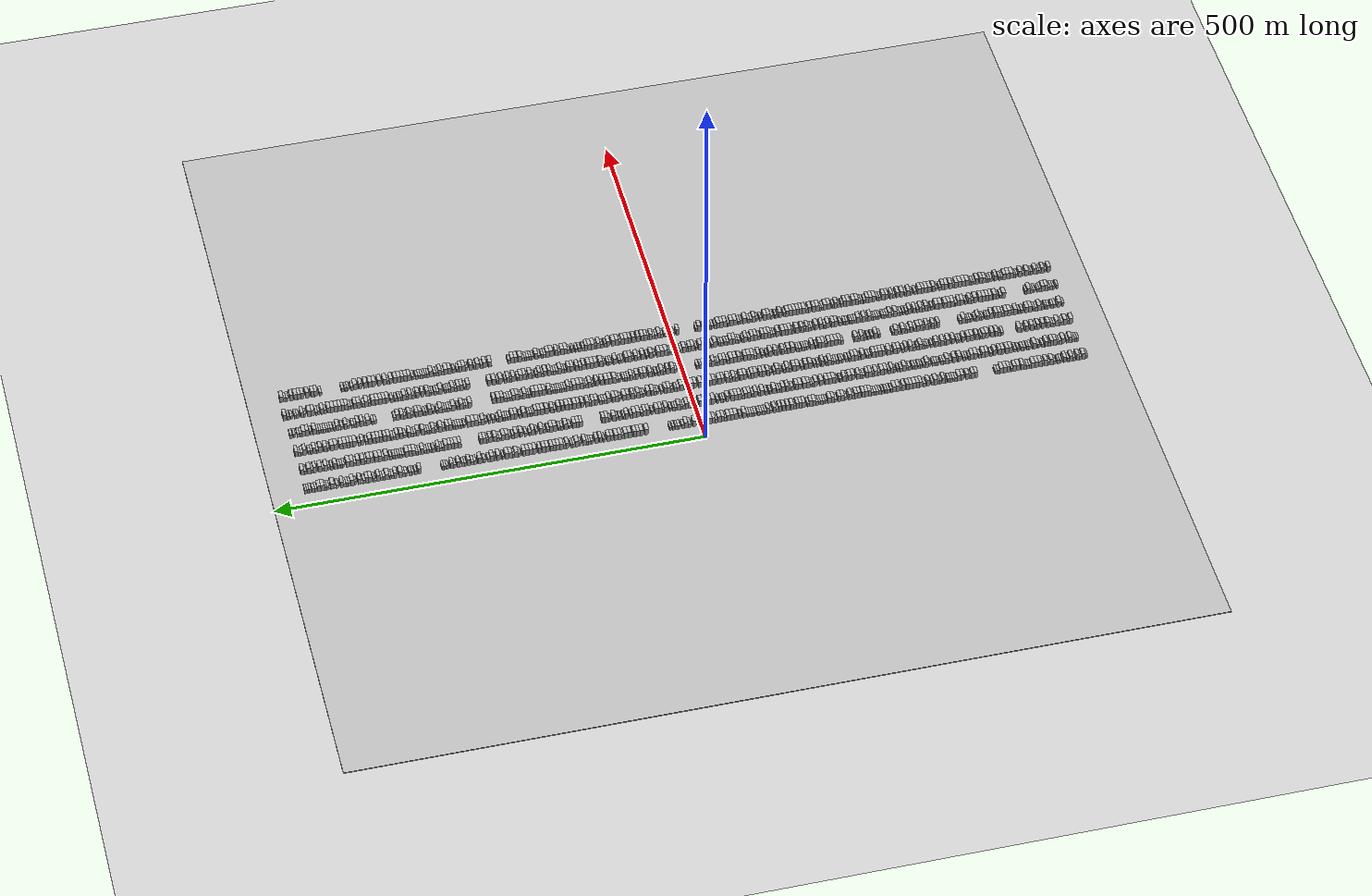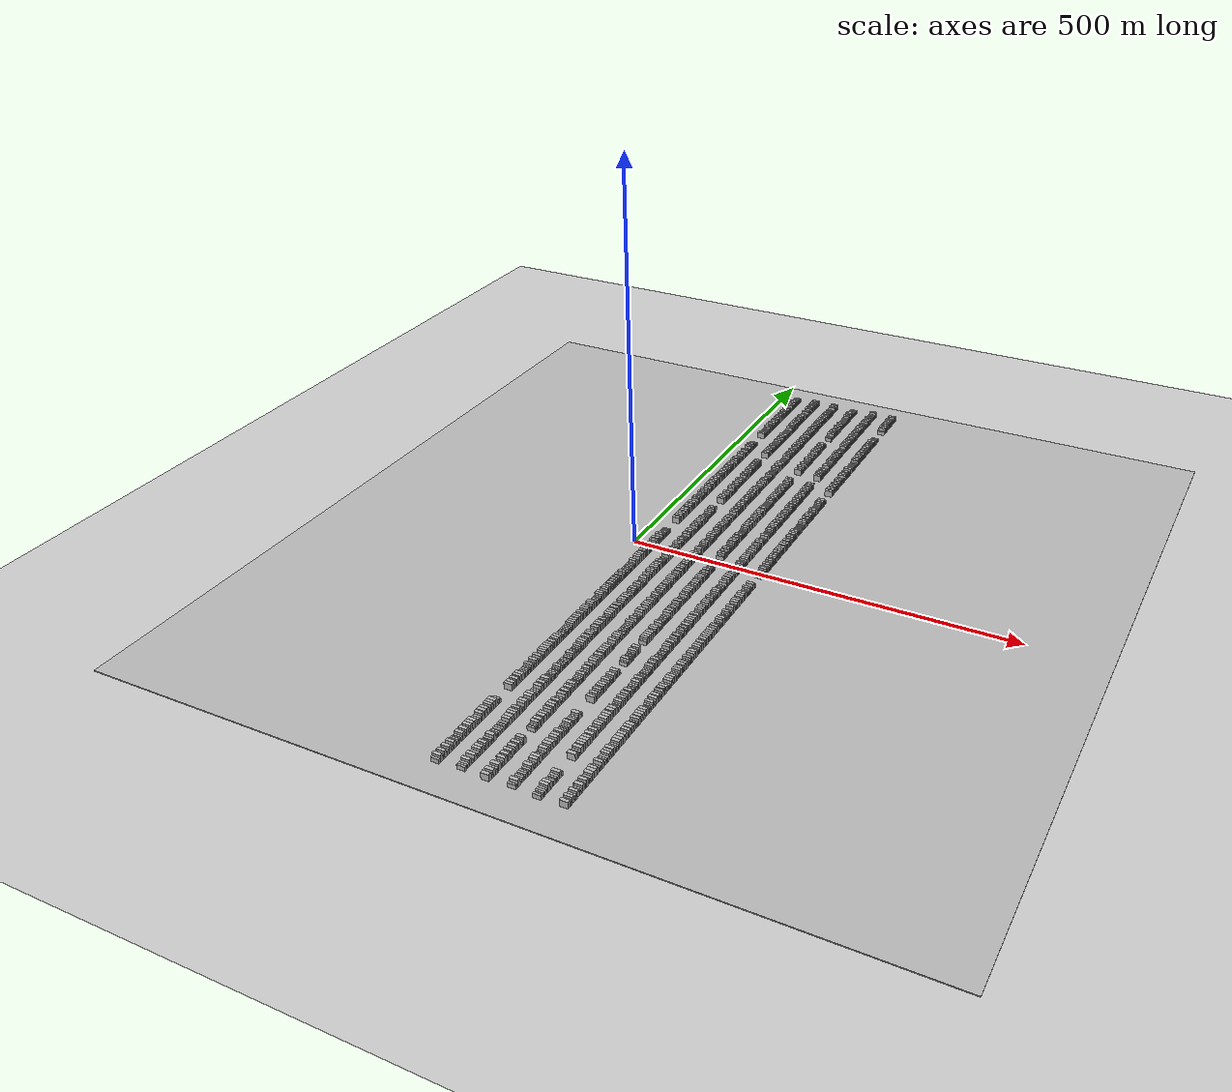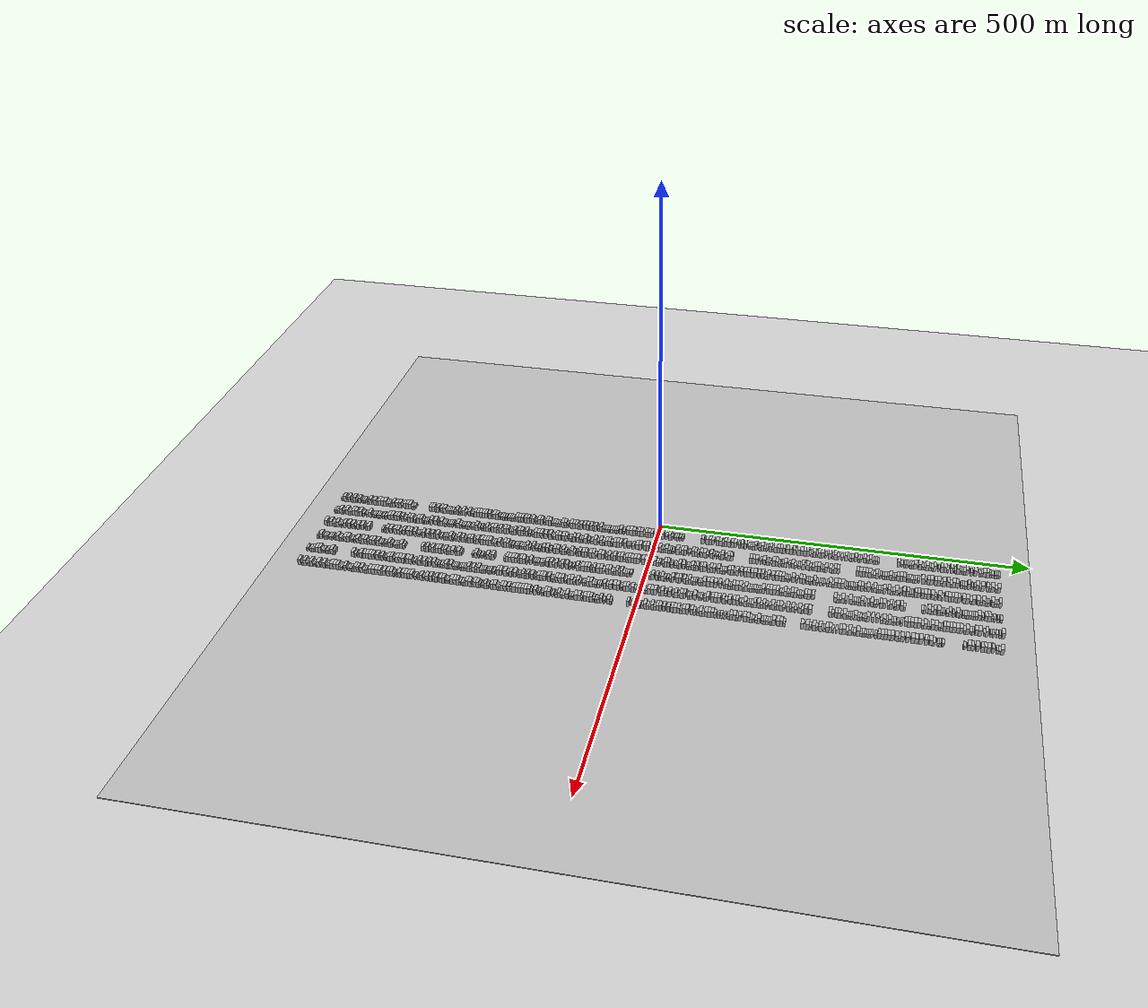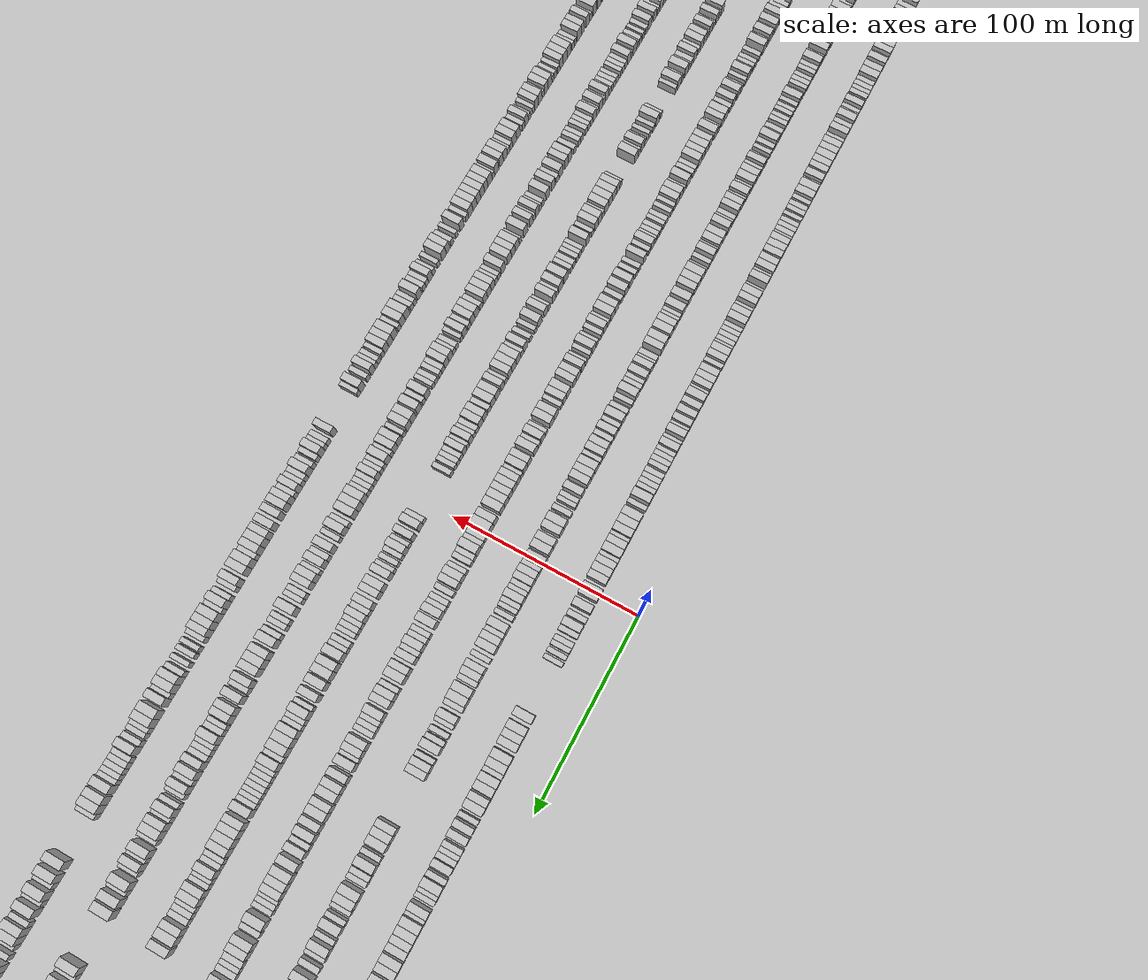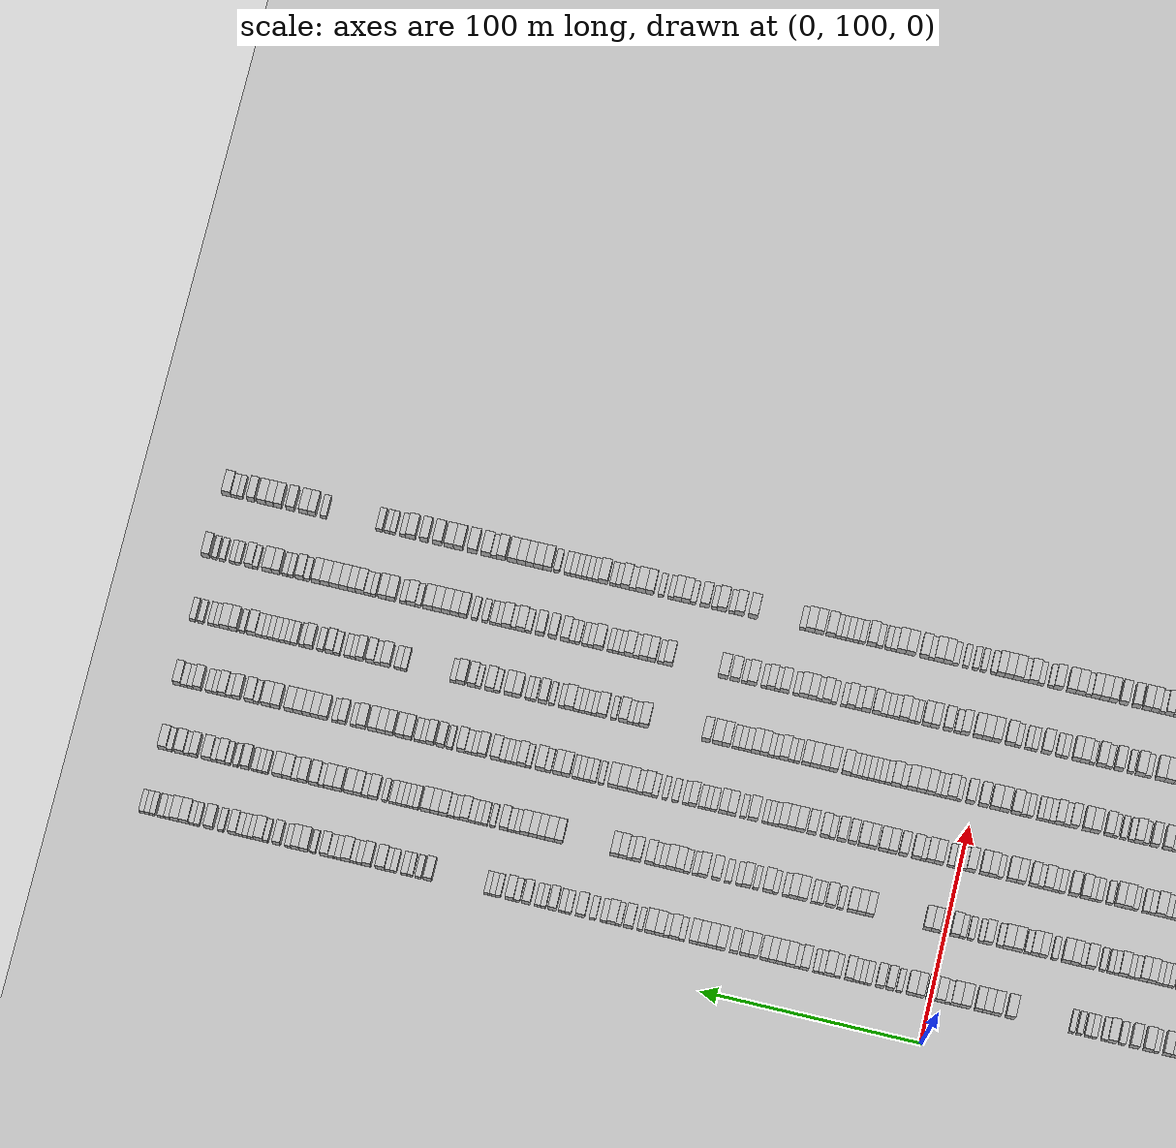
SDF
<?xml version="1.0" encoding="utf-8"?>

<sdf version="1.6">

   <world name="default">

      <gui fullscreen="0">

         <camera name="user_camera">

            <pose>-15 0 4.57585 0 0 0</pose>

            <view_controller>orbit</view_controller>

         </camera>

      </gui>

      <scene>

         <sky>

           <clouds>

             <speed>12</speed>

           </clouds>

         </sky>

         <ambient>0.4 0.4 0.4 1</ambient>

         <background>0.7 0.7 0.7 1</background>

         <shadows>1</shadows>

      </scene>

      <gravity>0 0 -9.8066</gravity>

      <magnetic_field>6e-06 2.3e-05 -4.2e-05</magnetic_field>

      <physics default="0" name="default_physics" type="ode">

         <ode>

            <solver>

               <type>quick</type>

               <iters>10</iters>

               <sor>1.0</sor>

               <use_dynamic_moi_rescaling>0</use_dynamic_moi_rescaling>

            </solver>

            <constraints>

               <cfm>0</cfm>

               <erp>0.2</erp>

               <contact_max_correcting_vel>100</contact_max_correcting_vel>

               <contact_surface_layer>0.001</contact_surface_layer>

            </constraints>

         </ode>

         <max_step_size>0.004</max_step_size>

         <real_time_factor>1</real_time_factor>

         <real_time_update_rate>250</real_time_update_rate>

      </physics>

      <light name="sun" type="directional">

         <cast_shadows>1</cast_shadows>

         <pose>0 0 10 0 0 0</pose>

         <diffuse>0.8 0.8 0.8 1</diffuse>

         <specular>0.2 0.2 0.2 1</specular>

         <attenuation>

            <range>1000</range>

            <constant>0.9</constant>

            <linear>0.01</linear>

            <quadratic>0.001</quadratic>

         </attenuation>

         <direction>-0.5 0.1 -0.9</direction>

      </light>

      <include>

         <name>ground_plane_1</name>

         <uri>model://HANNAS_ground_plane</uri>

         <pose>0 0 0  0 0 0</pose>

      </include>

      <include>

         <name>ground_plane_2</name>

         <uri>model://HANNAS_ground_plane</uri>

         <pose>100 0 0  0 0 0</pose>

      </include>

      <model name="building_1">

         <static>1</static>

         <pose frame="">25.0000 -458.5586 0 0.000000 0.000000 0.000000</pose>

         <link name="link">

            <pose frame="">0 0 3.00 0 0 0</pose>

            <collision name="collision">

               <geometry>

                  <box>

                     <size>10.0000 2.8828 6.0000</size>

                  </box>

               </geometry>

               <max_contacts>10</max_contacts>

               <surface>

                  <contact>

                     <ode/>

                  </contact>

                  <bounce/>

                  <friction>

                     <torsional>

                        <ode/>

                     </torsional>

                     <ode/>

                  </friction>

               </surface>

            </collision>

            <visual name="visual">

               <cast_shadows>0</cast_shadows>

               <geometry>

                  <box>

                     <size>10.0000 2.8828 6.0000</size>

                  </box>

               </geometry>

               <material>

                  <script>

                     <uri>model://HANNAS_wall/materials/scripts</uri>

                     <uri>model://HANNAS_wall/materials/textures</uri>

                     <name>vrc/HANNAS_wall</name>

                  </script>

               </material>

            </visual>

            <self_collide>0</self_collide>

            <enable_wind>0</enable_wind>

            <kinematic>0</kinematic>

         </link>

      </model>

      <model name="building_2">

         <static>1</static>

         <pose frame="">25.0000 -454.8922 0 0.000000 0.000000 0.000000</pose>

         <link name="link">

            <pose frame="">0 0 4.50 0 0 0</pose>

            <collision name="collision">

               <geometry>

                  <box>

                     <size>10.0000 4.4502 9.0000</size>

                  </box>

               </geometry>

               <max_contacts>10</max_contacts>

               <surface>

                  <contact>

                     <ode/>

                  </contact>

                  <bounce/>

                  <friction>

                     <torsional>

                        <ode/>

                     </torsional>

                     <ode/>

                  </friction>

               </surface>

            </collision>

            <visual name="visual">

               <cast_shadows>0</cast_shadows>

               <geometry>

                  <box>

                     <size>10.0000 4.4502 9.0000</size>

                  </box>

               </geometry>

               <material>

                  <script>

                     <uri>model://HANNAS_wall/materials/scripts</uri>

                     <uri>model://HANNAS_wall/materials/textures</uri>

                     <name>vrc/HANNAS_wall</name>

                  </script>

               </material>

            </visual>

            <self_collide>0</self_collide>

            <enable_wind>0</enable_wind>

            <kinematic>0</kinematic>

         </link>

      </model>

      <model name="building_3">

         <static>1</static>

         <pose frame="">25.0000 -451.3511 0 0.000000 0.000000 0.000000</pose>

         <link name="link">

            <pose frame="">0 0 3.00 0 0 0</pose>

            <collision name="collision">

               <geometry>

                  <box>

                     <size>10.0000 2.6318 6.0000</size>

                  </box>

               </geometry>

               <max_contacts>10</max_contacts>

               <surface>

                  <contact>

                     <ode/>

                  </contact>

                  <bounce/>

                  <friction>

                     <torsional>

                        <ode/>

                     </torsional>

                     <ode/>

                  </friction>

               </surface>

            </collision>

            <visual name="visual">

               <cast_shadows>0</cast_shadows>

               <geometry>

                  <box>

                     <size>10.0000 2.6318 6.0000</size>

                  </box>

               </geometry>

               <material>

                  <script>

                     <uri>model://HANNAS_wall/materials/scripts</uri>

                     <uri>model://HANNAS_wall/materials/textures</uri>

                     <name>vrc/HANNAS_wall</name>

                  </script>

               </material>

            </visual>

            <self_collide>0</self_collide>

            <enable_wind>0</enable_wind>

            <kinematic>0</kinematic>

         </link>

      </model>

      <model name="building_4">

         <static>1</static>

         <pose frame="">25.0000 -448.0946 0 0.000000 0.000000 0.000000</pose>

         <link name="link">

            <pose frame="">0 0 4.50 0 0 0</pose>

            <collision name="collision">

               <geometry>

                  <box>

                     <size>10.0000 3.8812 9.0000</size>

                  </box>

               </geometry>

               <max_contacts>10</max_contacts>

               <surface>

                  <contact>

                     <ode/>

                  </contact>

                  <bounce/>

                  <friction>

                     <torsional>

                        <ode/>

                     </torsional>

                     <ode/>

                  </friction>

               </surface>

            </collision>

            <visual name="visual">

               <cast_shadows>0</cast_shadows>

               <geometry>

                  <box>

                     <size>10.0000 3.8812 9.0000</size>

                  </box>

               </geometry>

               <material>

                  <script>

                     <uri>model://HANNAS_wall/materials/scripts</uri>

                     <uri>model://HANNAS_wall/materials/textures</uri>

                     <name>vrc/HANNAS_wall</name>

                  </script>

               </material>

            </visual>

            <self_collide>0</self_collide>

            <enable_wind>0</enable_wind>

            <kinematic>0</kinematic>

         </link>

      </model>

      <model name="building_5">

         <static>1</static>

         <pose frame="">25.0000 -443.6908 0 0.000000 0.000000 0.000000</pose>

         <link name="link">

            <pose frame="">0 0 3.00 0 0 0</pose>

            <collision name="collision">

               <geometry>

                  <box>

                     <size>10.0000 2.9265 6.0000</size>

                  </box>

               </geometry>

               <max_contacts>10</max_contacts>

               <surface>

                  <contact>

                     <ode/>

                  </contact>

                  <bounce/>

                  <friction>

                     <torsional>

                        <ode/>

                     </torsional>

                     <ode/>

                  </friction>

               </surface>

            </collision>

            <visual name="visual">

               <cast_shadows>0</cast_shadows>

               <geometry>

                  <box>

                     <size>10.0000 2.9265 6.0000</size>

                  </box>

               </geometry>

               <material>

                  <script>

                     <uri>model://HANNAS_wall/materials/scripts</uri>

                     <uri>model://HANNAS_wall/materials/textures</uri>

                     <name>vrc/HANNAS_wall</name>

                  </script>

               </material>

            </visual>

            <self_collide>0</self_collide>

            <enable_wind>0</enable_wind>

            <kinematic>0</kinematic>

         </link>

      </model>

      <model name="building_6">

         <static>1</static>

         <pose frame="">25.0000 -440.1701 0 0.000000 0.000000 0.000000</pose>

         <link name="link">

            <pose frame="">0 0 4.50 0 0 0</pose>

            <collision name="collision">

               <geometry>

                  <box>

                     <size>10.0000 4.1150 9.0000</size>

                  </box>

               </geometry>

               <max_contacts>10</max_contacts>

               <surface>

                  <contact>

                     <ode/>

                  </contact>

                  <bounce/>

                  <friction>

                     <torsional>

                        <ode/>

                     </torsional>

                     <ode/>

                  </friction>

               </surface>

            </collision>

            <visual name="visual">

               <cast_shadows>0</cast_shadows>

               <geometry>

                  <box>

                     <size>10.0000 4.1150 9.0000</size>

                  </box>

               </geometry>

               <material>

                  <script>

                     <uri>model://HANNAS_wall/materials/scripts</uri>

                     <uri>model://HANNAS_wall/materials/textures</uri>

                     <name>vrc/HANNAS_wall</name>

                  </script>

               </material>

            </visual>

            <self_collide>0</self_collide>

            <enable_wind>0</enable_wind>

            <kinematic>0</kinematic>

         </link>

      </model>

      <model name="building_7">

         <static>1</static>

         <pose frame="">25.0000 -436.7633 0 0.000000 0.000000 0.000000</pose>

         <link name="link">

            <pose frame="">0 0 3.00 0 0 0</pose>

            <collision name="collision">

               <geometry>

                  <box>

                     <size>10.0000 2.6986 6.0000</size>

                  </box>

               </geometry>

               <max_contacts>10</max_contacts>

               <surface>

                  <contact>

                     <ode/>

                  </contact>

                  <bounce/>

                  <friction>

                     <torsional>

                        <ode/>

                     </torsional>

                     <ode/>

                  </friction>

               </surface>

            </collision>

            <visual name="visual">

               <cast_shadows>0</cast_shadows>

               <geometry>

                  <box>

                     <size>10.0000 2.6986 6.0000</size>

                  </box>

               </geometry>

               <material>

                  <script>

                     <uri>model://HANNAS_wall/materials/scripts</uri>

                     <uri>model://HANNAS_wall/materials/textures</uri>

                     <name>vrc/HANNAS_wall</name>

                  </script>

               </material>

            </visual>

            <self_collide>0</self_collide>

            <enable_wind>0</enable_wind>

            <kinematic>0</kinematic>

         </link>

      </model>

      <model name="building_8">

         <static>1</static>

         <pose frame="">25.0000 -432.5317 0 0.000000 0.000000 0.000000</pose>

         <link name="link">

            <pose frame="">0 0 4.50 0 0 0</pose>

            <collision name="collision">

               <geometry>

                  <box>

                     <size>10.0000 3.7646 9.0000</size>

                  </box>

               </geometry>

               <max_contacts>10</max_contacts>

               <surface>

                  <contact>

                     <ode/>

                  </contact>

                  <bounce/>

                  <friction>

                     <torsional>

                        <ode/>

                     </torsional>

                     <ode/>

                  </friction>

               </surface>

            </collision>

            <visual name="visual">

               <cast_shadows>0</cast_shadows>

               <geometry>

                  <box>

                     <size>10.0000 3.7646 9.0000</size>

                  </box>

               </geometry>

               <material>

                  <script>

                     <uri>model://HANNAS_wall/materials/scripts</uri>

                     <uri>model://HANNAS_wall/materials/textures</uri>

                     <name>vrc/HANNAS_wall</name>

                  </script>

               </material>

            </visual>

            <self_collide>0</self_collide>

            <enable_wind>0</enable_wind>

            <kinematic>0</kinematic>

         </link>

      </model>

      <model name="building_9">

         <static>1</static>

         <pose frame="">25.0000 -427.3439 0 0.000000 0.000000 0.000000</pose>

         <link name="link">

            <pose frame="">0 0 3.00 0 0 0</pose>

            <collision name="collision">

               <geometry>

                  <box>

                     <size>10.0000 2.6110 6.0000</size>

                  </box>

               </geometry>

               <max_contacts>10</max_contacts>

               <surface>

                  <contact>

                     <ode/>

                  </contact>

                  <bounce/>

                  <friction>

                     <torsional>

                        <ode/>

                     </torsional>

                     <ode/>

                  </friction>

               </surface>

            </collision>

            <visual name="visual">

               <cast_shadows>0</cast_shadows>

               <geometry>

                  <box>

                     <size>10.0000 2.6110 6.0000</size>

                  </box>

               </geometry>

               <material>

                  <script>

                     <uri>model://HANNAS_wall/materials/scripts</uri>

                     <uri>model://HANNAS_wall/materials/textures</uri>

                     <name>vrc/HANNAS_wall</name>

                  </script>

               </material>

            </visual>

            <self_collide>0</self_collide>

            <enable_wind>0</enable_wind>

            <kinematic>0</kinematic>

         </link>

      </model>

      <model name="building_10">

         <static>1</static>

         <pose frame="">25.0000 -424.7453 0 0.000000 0.000000 0.000000</pose>

         <link name="link">

            <pose frame="">0 0 3.00 0 0 0</pose>

            <collision name="collision">

               <geometry>

                  <box>

                     <size>10.0000 2.5862 6.0000</size>

                  </box>

               </geometry>

               <max_contacts>10</max_contacts>

               <surface>

                  <contact>

                     <ode/>

                  </contact>

                  <bounce/>

                  <friction>

                     <torsional>

                        <ode/>

                     </torsional>

                     <ode/>

                  </friction>

               </surface>

            </collision>

            <visual name="visual">

               <cast_shadows>0</cast_shadows>

               <geometry>

                  <box>

                     <size>10.0000 2.5862 6.0000</size>

                  </box>

               </geometry>

               <material>

                  <script>

                     <uri>model://HANNAS_wall/materials/scripts</uri>

                     <uri>model://HANNAS_wall/materials/textures</uri>

                     <name>vrc/HANNAS_wall</name>

                  </script>

               </material>

            </visual>

            <self_collide>0</self_collide>

            <enable_wind>0</enable_wind>

            <kinematic>0</kinematic>

         </link>

      </model>

      <model name="building_11">

         <static>1</static>

         <pose frame="">25.0000 -420.1133 0 0.000000 0.000000 0.000000</pose>

         <link name="link">

            <pose frame="">0 0 3.00 0 0 0</pose>

            <collision name="collision">

               <geometry>

                  <box>

                     <size>10.0000 2.6780 6.0000</size>

                  </box>

               </geometry>

               <max_contacts>10</max_contacts>

               <surface>

                  <contact>

                     <ode/>

                  </contact>

                  <bounce/>

                  <friction>

                     <torsional>

                        <ode/>

                     </torsional>

                     <ode/>

                  </friction>

               </surface>

            </collision>

            <visual name="visual">

               <cast_shadows>0</cast_shadows>

               <geometry>

                  <box>

                     <size>10.0000 2.6780 6.0000</size>

                  </box>

               </geometry>

               <material>

                  <script>

                     <uri>model://HANNAS_wall/materials/scripts</uri>

                     <uri>model://HANNAS_wall/materials/textures</uri>

                     <name>vrc/HANNAS_wall</name>

                  </script>

               </material>

            </visual>

            <self_collide>0</self_collide>

            <enable_wind>0</enable_wind>

            <kinematic>0</kinematic>

         </link>

      </model>

      <model name="building_12">

         <static>1</static>

         <pose frame="">25.0000 -416.6234 0 0.000000 0.000000 0.000000</pose>

         <link name="link">

            <pose frame="">0 0 4.50 0 0 0</pose>

            <collision name="collision">

               <geometry>

                  <box>

                     <size>10.0000 4.3018 9.0000</size>

                  </box>

               </geometry>

               <max_contacts>10</max_contacts>

               <surface>

                  <contact>

                     <ode/>

                  </contact>

                  <bounce/>

                  <friction>

                     <torsional>

                        <ode/>

                     </torsional>

                     <ode/>

                  </friction>

               </surface>

            </collision>

            <visual name="visual">

               <cast_shadows>0</cast_shadows>

               <geometry>

                  <box>

                     <size>10.0000 4.3018 9.0000</size>

                  </box>

               </geometry>

               <material>

                  <script>

                     <uri>model://HANNAS_wall/materials/scripts</uri>

                     <uri>model://HANNAS_wall/materials/textures</uri>

                     <name>vrc/HANNAS_wall</name>

                  </script>

               </material>

            </visual>

            <self_collide>0</self_collide>

            <enable_wind>0</enable_wind>

            <kinematic>0</kinematic>

         </link>

      </model>

      <model name="building_13">

         <static>1</static>

         <pose frame="">25.0000 -413.1799 0 0.000000 0.000000 0.000000</pose>

         <link name="link">

            <pose frame="">0 0 3.00 0 0 0</pose>

            <collision name="collision">

               <geometry>

                  <box>

                     <size>10.0000 2.5851 6.0000</size>

                  </box>

               </geometry>

               <max_contacts>10</max_contacts>

               <surface>

                  <contact>

                     <ode/>

                  </contact>

                  <bounce/>

                  <friction>

                     <torsional>

                        <ode/>

                     </torsional>

                     <ode/>

                  </friction>

               </surface>

            </collision>

            <visual name="visual">

               <cast_shadows>0</cast_shadows>

               <geometry>

                  <box>

                     <size>10.0000 2.5851 6.0000</size>

                  </box>

               </geometry>

               <material>

                  <script>

                     <uri>model://HANNAS_wall/materials/scripts</uri>

                     <uri>model://HANNAS_wall/materials/textures</uri>

                     <name>vrc/HANNAS_wall</name>

                  </script>

               </material>

            </visual>

            <self_collide>0</self_collide>

            <enable_wind>0</enable_wind>

            <kinematic>0</kinematic>

         </link>

      </model>

      <model name="building_14">

         <static>1</static>

         <pose frame="">25.0000 -409.7623 0 0.000000 0.000000 0.000000</pose>

         <link name="link">

            <pose frame="">0 0 4.50 0 0 0</pose>

            <collision name="collision">

               <geometry>

                  <box>

                     <size>10.0000 4.2500 9.0000</size>

                  </box>

               </geometry>

               <max_contacts>10</max_contacts>

               <surface>

                  <contact>

                     <ode/>

                  </contact>

                  <bounce/>

                  <friction>

                     <torsional>

                        <ode/>

                     </torsional>

                     <ode/>

                  </friction>

               </surface>

            </collision>

            <visual name="visual">

               <cast_shadows>0</cast_shadows>

               <geometry>

                  <box>

                     <size>10.0000 4.2500 9.0000</size>

                  </box>

               </geometry>

               <material>

                  <script>

                     <uri>model://HANNAS_wall/materials/scripts</uri>

                     <uri>model://HANNAS_wall/materials/textures</uri>

                     <name>vrc/HANNAS_wall</name>

                  </script>

               </material>

            </visual>

            <self_collide>0</self_collide>

            <enable_wind>0</enable_wind>

            <kinematic>0</kinematic>

         </link>

      </model>

      <model name="building_15">

         <static>1</static>

         <pose frame="">25.0000 -406.2445 0 0.000000 0.000000 0.000000</pose>

         <link name="link">

            <pose frame="">0 0 3.00 0 0 0</pose>

            <collision name="collision">

               <geometry>

                  <box>

                     <size>10.0000 2.7857 6.0000</size>

                  </box>

               </geometry>

               <max_contacts>10</max_contacts>

               <surface>

                  <contact>

                     <ode/>

                  </contact>

                  <bounce/>

                  <friction>

                     <torsional>

                        <ode/>

                     </torsional>

                     <ode/>

                  </friction>

               </surface>

            </collision>

            <visual name="visual">

               <cast_shadows>0</cast_shadows>

               <geometry>

                  <box>

                     <size>10.0000 2.7857 6.0000</size>

                  </box>

               </geometry>

               <material>

                  <script>

                     <uri>model://HANNAS_wall/materials/scripts</uri>

                     <uri>model://HANNAS_wall/materials/textures</uri>

                     <name>vrc/HANNAS_wall</name>

                  </script>

               </material>

            </visual>

            <self_collide>0</self_collide>

            <enable_wind>0</enable_wind>

            <kinematic>0</kinematic>

         </link>

      </model>

      <model name="building_16">

         <static>1</static>

         <pose frame="">25.0000 -402.7306 0 0.000000 0.000000 0.000000</pose>

         <link name="link">

            <pose frame="">0 0 4.50 0 0 0</pose>

            <collision name="collision">

               <geometry>

                  <box>

                     <size>10.0000 4.2420 9.0000</size>

                  </box>

               </geometry>

               <max_contacts>10</max_contacts>

               <surface>

                  <contact>

                     <ode/>

                  </contact>

                  <bounce/>

                  <friction>

                     <torsional>

                        <ode/>

                     </torsional>

                     <ode/>

                  </friction>

               </surface>

            </collision>

            <visual name="visual">

               <cast_shadows>0</cast_shadows>

               <geometry>

                  <box>

                     <size>10.0000 4.2420 9.0000</size>

                  </box>

               </geometry>

               <material>

                  <script>

                     <uri>model://HANNAS_wall/materials/scripts</uri>

                     <uri>model://HANNAS_wall/materials/textures</uri>

                     <name>vrc/HANNAS_wall</name>

                  </script>

               </material>

            </visual>

            <self_collide>0</self_collide>

            <enable_wind>0</enable_wind>

            <kinematic>0</kinematic>

         </link>

      </model>

      <model name="building_17">

         <static>1</static>

         <pose frame="">25.0000 -398.5510 0 0.000000 0.000000 0.000000</pose>

         <link name="link">

            <pose frame="">0 0 4.50 0 0 0</pose>

            <collision name="collision">

               <geometry>

                  <box>

                     <size>10.0000 4.1172 9.0000</size>

                  </box>

               </geometry>

               <max_contacts>10</max_contacts>

               <surface>

                  <contact>

                     <ode/>

                  </contact>

                  <bounce/>

                  <friction>

                     <torsional>

                        <ode/>

                     </torsional>

                     <ode/>

                  </friction>

               </surface>

            </collision>

            <visual name="visual">

               <cast_shadows>0</cast_shadows>

               <geometry>

                  <box>

                     <size>10.0000 4.1172 9.0000</size>

                  </box>

               </geometry>

               <material>

                  <script>

                     <uri>model://HANNAS_wall/materials/scripts</uri>

                     <uri>model://HANNAS_wall/materials/textures</uri>

                     <name>vrc/HANNAS_wall</name>

                  </script>

               </material>

            </visual>

            <self_collide>0</self_collide>

            <enable_wind>0</enable_wind>

            <kinematic>0</kinematic>

         </link>

      </model>

      <model name="building_18">

         <static>1</static>

         <pose frame="">25.0000 -394.3145 0 0.000000 0.000000 0.000000</pose>

         <link name="link">

            <pose frame="">0 0 4.50 0 0 0</pose>

            <collision name="collision">

               <geometry>

                  <box>

                     <size>10.0000 4.3558 9.0000</size>

                  </box>

               </geometry>

               <max_contacts>10</max_contacts>

               <surface>

                  <contact>

                     <ode/>

                  </contact>

                  <bounce/>

                  <friction>

                     <torsional>

                        <ode/>

                     </torsional>

                     <ode/>

                  </friction>

               </surface>

            </collision>

            <visual name="visual">

               <cast_shadows>0</cast_shadows>

               <geometry>

                  <box>

                     <size>10.0000 4.3558 9.0000</size>

                  </box>

               </geometry>

               <material>

                  <script>

                     <uri>model://HANNAS_wall/materials/scripts</uri>

                     <uri>model://HANNAS_wall/materials/textures</uri>

                     <name>vrc/HANNAS_wall</name>

                  </script>

               </material>

            </visual>

            <self_collide>0</self_collide>

            <enable_wind>0</enable_wind>

            <kinematic>0</kinematic>

         </link>

      </model>

      <model name="building_19">

         <static>1</static>

         <pose frame="">25.0000 -390.6799 0 0.000000 0.000000 0.000000</pose>

         <link name="link">

            <pose frame="">0 0 3.00 0 0 0</pose>

            <collision name="collision">

               <geometry>

                  <box>

                     <size>10.0000 2.9135 6.0000</size>

                  </box>

               </geometry>

               <max_contacts>10</max_contacts>

               <surface>

                  <contact>

                     <ode/>

                  </contact>

                  <bounce/>

                  <friction>

                     <torsional>

                        <ode/>

                     </torsional>

                     <ode/>

                  </friction>

               </surface>

            </collision>

            <visual name="visual">

               <cast_shadows>0</cast_shadows>

               <geometry>

                  <box>

                     <size>10.0000 2.9135 6.0000</size>

                  </box>

               </geometry>

               <material>

                  <script>

                     <uri>model://HANNAS_wall/materials/scripts</uri>

                     <uri>model://HANNAS_wall/materials/textures</uri>

                     <name>vrc/HANNAS_wall</name>

                  </script>

               </material>

            </visual>

            <self_collide>0</self_collide>

            <enable_wind>0</enable_wind>

            <kinematic>0</kinematic>

         </link>

      </model>

      <model name="building_20">

         <static>1</static>

         <pose frame="">25.0000 -387.7635 0 0.000000 0.000000 0.000000</pose>

         <link name="link">

            <pose frame="">0 0 3.00 0 0 0</pose>

            <collision name="collision">

               <geometry>

                  <box>

                     <size>10.0000 2.9193 6.0000</size>

                  </box>

               </geometry>

               <max_contacts>10</max_contacts>

               <surface>

                  <contact>

                     <ode/>

                  </contact>

                  <bounce/>

                  <friction>

                     <torsional>

                        <ode/>

                     </torsional>

                     <ode/>

                  </friction>

               </surface>

            </collision>

            <visual name="visual">

               <cast_shadows>0</cast_shadows>

               <geometry>

                  <box>

                     <size>10.0000 2.9193 6.0000</size>

                  </box>

               </geometry>

               <material>

                  <script>

                     <uri>model://HANNAS_wall/materials/scripts</uri>

                     <uri>model://HANNAS_wall/materials/textures</uri>

                     <name>vrc/HANNAS_wall</name>

                  </script>

               </material>

            </visual>

            <self_collide>0</self_collide>

            <enable_wind>0</enable_wind>

            <kinematic>0</kinematic>

         </link>

      </model>

      <model name="building_21">

         <static>1</static>

         <pose frame="">25.0000 -384.8838 0 0.000000 0.000000 0.000000</pose>

         <link name="link">

            <pose frame="">0 0 3.00 0 0 0</pose>

            <collision name="collision">

               <geometry>

                  <box>

                     <size>10.0000 2.8401 6.0000</size>

                  </box>

               </geometry>

               <max_contacts>10</max_contacts>

               <surface>

                  <contact>

                     <ode/>

                  </contact>

                  <bounce/>

                  <friction>

                     <torsional>

                        <ode/>

                     </torsional>

                     <ode/>

                  </friction>

               </surface>

            </collision>

            <visual name="visual">

               <cast_shadows>0</cast_shadows>

               <geometry>

                  <box>

                     <size>10.0000 2.8401 6.0000</size>

                  </box>

               </geometry>

               <material>

                  <script>

                     <uri>model://HANNAS_wall/materials/scripts</uri>

                     <uri>model://HANNAS_wall/materials/textures</uri>

                     <name>vrc/HANNAS_wall</name>

                  </script>

               </material>

            </visual>

            <self_collide>0</self_collide>

            <enable_wind>0</enable_wind>

            <kinematic>0</kinematic>

         </link>

      </model>

      <model name="building_22">

         <static>1</static>

         <pose frame="">25.0000 -381.4301 0 0.000000 0.000000 0.000000</pose>

         <link name="link">

            <pose frame="">0 0 4.50 0 0 0</pose>

            <collision name="collision">

               <geometry>

                  <box>

                     <size>10.0000 4.0673 9.0000</size>

                  </box>

               </geometry>

               <max_contacts>10</max_contacts>

               <surface>

                  <contact>

                     <ode/>

                  </contact>

                  <bounce/>

                  <friction>

                     <torsional>

                        <ode/>

                     </torsional>

                     <ode/>

                  </friction>

               </surface>

            </collision>

            <visual name="visual">

               <cast_shadows>0</cast_shadows>

               <geometry>

                  <box>

                     <size>10.0000 4.0673 9.0000</size>

                  </box>

               </geometry>

               <material>

                  <script>

                     <uri>model://HANNAS_wall/materials/scripts</uri>

                     <uri>model://HANNAS_wall/materials/textures</uri>

                     <name>vrc/HANNAS_wall</name>

                  </script>

               </material>

            </visual>

            <self_collide>0</self_collide>

            <enable_wind>0</enable_wind>

            <kinematic>0</kinematic>

         </link>

      </model>

      <model name="building_23">

         <static>1</static>

         <pose frame="">25.0000 -376.2225 0 0.000000 0.000000 0.000000</pose>

         <link name="link">

            <pose frame="">0 0 4.50 0 0 0</pose>

            <collision name="collision">

               <geometry>

                  <box>

                     <size>10.0000 4.3479 9.0000</size>

                  </box>

               </geometry>

               <max_contacts>10</max_contacts>

               <surface>

                  <contact>

                     <ode/>

                  </contact>

                  <bounce/>

                  <friction>

                     <torsional>

                        <ode/>

                     </torsional>

                     <ode/>

                  </friction>

               </surface>

            </collision>

            <visual name="visual">

               <cast_shadows>0</cast_shadows>

               <geometry>

                  <box>

                     <size>10.0000 4.3479 9.0000</size>

                  </box>

               </geometry>

               <material>

                  <script>

                     <uri>model://HANNAS_wall/materials/scripts</uri>

                     <uri>model://HANNAS_wall/materials/textures</uri>

                     <name>vrc/HANNAS_wall</name>

                  </script>

               </material>

            </visual>

            <self_collide>0</self_collide>

            <enable_wind>0</enable_wind>

            <kinematic>0</kinematic>

         </link>

      </model>

      <model name="building_24">

         <static>1</static>

         <pose frame="">25.0000 -372.0538 0 0.000000 0.000000 0.000000</pose>

         <link name="link">

            <pose frame="">0 0 4.50 0 0 0</pose>

            <collision name="collision">

               <geometry>

                  <box>

                     <size>10.0000 3.9895 9.0000</size>

                  </box>

               </geometry>

               <max_contacts>10</max_contacts>

               <surface>

                  <contact>

                     <ode/>

                  </contact>

                  <bounce/>

                  <friction>

                     <torsional>

                        <ode/>

                     </torsional>

                     <ode/>

                  </friction>

               </surface>

            </collision>

            <visual name="visual">

               <cast_shadows>0</cast_shadows>

               <geometry>

                  <box>

                     <size>10.0000 3.9895 9.0000</size>

                  </box>

               </geometry>

               <material>

                  <script>

                     <uri>model://HANNAS_wall/materials/scripts</uri>

                     <uri>model://HANNAS_wall/materials/textures</uri>

                     <name>vrc/HANNAS_wall</name>

                  </script>

               </material>

            </visual>

            <self_collide>0</self_collide>

            <enable_wind>0</enable_wind>

            <kinematic>0</kinematic>

         </link>

      </model>

      <model name="building_25">

         <static>1</static>

         <pose frame="">25.0000 -368.8045 0 0.000000 0.000000 0.000000</pose>

         <link name="link">

            <pose frame="">0 0 3.00 0 0 0</pose>

            <collision name="collision">

               <geometry>

                  <box>

                     <size>10.0000 2.5091 6.0000</size>

                  </box>

               </geometry>

               <max_contacts>10</max_contacts>

               <surface>

                  <contact>

                     <ode/>

                  </contact>

                  <bounce/>

                  <friction>

                     <torsional>

                        <ode/>

                     </torsional>

                     <ode/>

                  </friction>

               </surface>

            </collision>

            <visual name="visual">

               <cast_shadows>0</cast_shadows>

               <geometry>

                  <box>

                     <size>10.0000 2.5091 6.0000</size>

                  </box>

               </geometry>

               <material>

                  <script>

                     <uri>model://HANNAS_wall/materials/scripts</uri>

                     <uri>model://HANNAS_wall/materials/textures</uri>

                     <name>vrc/HANNAS_wall</name>

                  </script>

               </material>

            </visual>

            <self_collide>0</self_collide>

            <enable_wind>0</enable_wind>

            <kinematic>0</kinematic>

         </link>

      </model>

      <model name="building_26">

         <static>1</static>

         <pose frame="">25.0000 -364.7285 0 0.000000 0.000000 0.000000</pose>

         <link name="link">

            <pose frame="">0 0 4.50 0 0 0</pose>

            <collision name="collision">

               <geometry>

                  <box>

                     <size>10.0000 3.6430 9.0000</size>

                  </box>

               </geometry>

               <max_contacts>10</max_contacts>

               <surface>

                  <contact>

                     <ode/>

                  </contact>

                  <bounce/>

                  <friction>

                     <torsional>

                        <ode/>

                     </torsional>

                     <ode/>

                  </friction>

               </surface>

            </collision>

            <visual name="visual">

               <cast_shadows>0</cast_shadows>

               <geometry>

                  <box>

                     <size>10.0000 3.6430 9.0000</size>

                  </box>

               </geometry>

               <material>

                  <script>

                     <uri>model://HANNAS_wall/materials/scripts</uri>

                     <uri>model://HANNAS_wall/materials/textures</uri>

                     <name>vrc/HANNAS_wall</name>

                  </script>

               </material>

            </visual>

            <self_collide>0</self_collide>

            <enable_wind>0</enable_wind>

            <kinematic>0</kinematic>

         </link>

      </model>

      <model name="building_27">

         <static>1</static>

         <pose frame="">25.0000 -360.8503 0 0.000000 0.000000 0.000000</pose>

         <link name="link">

            <pose frame="">0 0 4.50 0 0 0</pose>

            <collision name="collision">

               <geometry>

                  <box>

                     <size>10.0000 4.1133 9.0000</size>

                  </box>

               </geometry>

               <max_contacts>10</max_contacts>

               <surface>

                  <contact>

                     <ode/>

                  </contact>

                  <bounce/>

                  <friction>

                     <torsional>

                        <ode/>

                     </torsional>

                     <ode/>

                  </friction>

               </surface>

            </collision>

            <visual name="visual">

               <cast_shadows>0</cast_shadows>

               <geometry>

                  <box>

                     <size>10.0000 4.1133 9.0000</size>

                  </box>

               </geometry>

               <material>

                  <script>

                     <uri>model://HANNAS_wall/materials/scripts</uri>

                     <uri>model://HANNAS_wall/materials/textures</uri>

                     <name>vrc/HANNAS_wall</name>

                  </script>

               </material>

            </visual>

            <self_collide>0</self_collide>

            <enable_wind>0</enable_wind>

            <kinematic>0</kinematic>

         </link>

      </model>

      <model name="building_28">

         <static>1</static>

         <pose frame="">25.0000 -356.5834 0 0.000000 0.000000 0.000000</pose>

         <link name="link">

            <pose frame="">0 0 4.50 0 0 0</pose>

            <collision name="collision">

               <geometry>

                  <box>

                     <size>10.0000 4.4204 9.0000</size>

                  </box>

               </geometry>

               <max_contacts>10</max_contacts>

               <surface>

                  <contact>

                     <ode/>

                  </contact>

                  <bounce/>

                  <friction>

                     <torsional>

                        <ode/>

                     </torsional>

                     <ode/>

                  </friction>

               </surface>

            </collision>

            <visual name="visual">

               <cast_shadows>0</cast_shadows>

               <geometry>

                  <box>

                     <size>10.0000 4.4204 9.0000</size>

                  </box>

               </geometry>

               <material>

                  <script>

                     <uri>model://HANNAS_wall/materials/scripts</uri>

                     <uri>model://HANNAS_wall/materials/textures</uri>

                     <name>vrc/HANNAS_wall</name>

                  </script>

               </material>

            </visual>

            <self_collide>0</self_collide>

            <enable_wind>0</enable_wind>

            <kinematic>0</kinematic>

         </link>

      </model>

      <model name="building_29">

         <static>1</static>

         <pose frame="">25.0000 -352.8852 0 0.000000 0.000000 0.000000</pose>

         <link name="link">

            <pose frame="">0 0 3.00 0 0 0</pose>

            <collision name="collision">

               <geometry>

                  <box>

                     <size>10.0000 2.9761 6.0000</size>

                  </box>

               </geometry>

               <max_contacts>10</max_contacts>

               <surface>

                  <contact>

                     <ode/>

                  </contact>

                  <bounce/>

                  <friction>

                     <torsional>

                        <ode/>

                     </torsional>

                     <ode/>

                  </friction>

               </surface>

            </collision>

            <visual name="visual">

               <cast_shadows>0</cast_shadows>

               <geometry>

                  <box>

                     <size>10.0000 2.9761 6.0000</size>

                  </box>

               </geometry>

               <material>

                  <script>

                     <uri>model://HANNAS_wall/materials/scripts</uri>

                     <uri>model://HANNAS_wall/materials/textures</uri>

                     <name>vrc/HANNAS_wall</name>

                  </script>

               </material>

            </visual>

            <self_collide>0</self_collide>

            <enable_wind>0</enable_wind>

            <kinematic>0</kinematic>

         </link>

      </model>

      <model name="building_30">

         <static>1</static>

         <pose frame="">25.0000 -350.0547 0 0.000000 0.000000 0.000000</pose>

         <link name="link">

            <pose frame="">0 0 3.00 0 0 0</pose>

            <collision name="collision">

               <geometry>

                  <box>

                     <size>10.0000 2.6849 6.0000</size>

                  </box>

               </geometry>

               <max_contacts>10</max_contacts>

               <surface>

                  <contact>

                     <ode/>

                  </contact>

                  <bounce/>

                  <friction>

                     <torsional>

                        <ode/>

                     </torsional>

                     <ode/>

                  </friction>

               </surface>

            </collision>

            <visual name="visual">

               <cast_shadows>0</cast_shadows>

               <geometry>

                  <box>

                     <size>10.0000 2.6849 6.0000</size>

                  </box>

               </geometry>

               <material>

                  <script>

                     <uri>model://HANNAS_wall/materials/scripts</uri>

                     <uri>model://HANNAS_wall/materials/textures</uri>

                     <name>vrc/HANNAS_wall</name>

                  </script>

               </material>

            </visual>

            <self_collide>0</self_collide>

            <enable_wind>0</enable_wind>

            <kinematic>0</kinematic>

         </link>

      </model>

      <model name="building_31">

         <static>1</static>

         <pose frame="">25.0000 -325.8660 0 0.000000 0.000000 0.000000</pose>

         <link name="link">

            <pose frame="">0 0 4.50 0 0 0</pose>

            <collision name="collision">

               <geometry>

                  <box>

                     <size>10.0000 3.8976 9.0000</size>

                  </box>

               </geometry>

               <max_contacts>10</max_contacts>

               <surface>

                  <contact>

                     <ode/>

                  </contact>

                  <bounce/>

                  <friction>

                     <torsional>

                        <ode/>

                     </torsional>

                     <ode/>

                  </friction>

               </surface>

            </collision>

            <visual name="visual">

               <cast_shadows>0</cast_shadows>

               <geometry>

                  <box>

                     <size>10.0000 3.8976 9.0000</size>

                  </box>

               </geometry>

               <material>

                  <script>

                     <uri>model://HANNAS_wall/materials/scripts</uri>

                     <uri>model://HANNAS_wall/materials/textures</uri>

                     <name>vrc/HANNAS_wall</name>

                  </script>

               </material>

            </visual>

            <self_collide>0</self_collide>

            <enable_wind>0</enable_wind>

            <kinematic>0</kinematic>

         </link>

      </model>

      <model name="building_32">

         <static>1</static>

         <pose frame="">25.0000 -321.9896 0 0.000000 0.000000 0.000000</pose>

         <link name="link">

            <pose frame="">0 0 4.50 0 0 0</pose>

            <collision name="collision">

               <geometry>

                  <box>

                     <size>10.0000 3.8553 9.0000</size>

                  </box>

               </geometry>

               <max_contacts>10</max_contacts>

               <surface>

                  <contact>

                     <ode/>

                  </contact>

                  <bounce/>

                  <friction>

                     <torsional>

                        <ode/>

                     </torsional>

                     <ode/>

                  </friction>

               </surface>

            </collision>

            <visual name="visual">

               <cast_shadows>0</cast_shadows>

               <geometry>

                  <box>

                     <size>10.0000 3.8553 9.0000</size>

                  </box>

               </geometry>

               <material>

                  <script>

                     <uri>model://HANNAS_wall/materials/scripts</uri>

                     <uri>model://HANNAS_wall/materials/textures</uri>

                     <name>vrc/HANNAS_wall</name>

                  </script>

               </material>

            </visual>

            <self_collide>0</self_collide>

            <enable_wind>0</enable_wind>

            <kinematic>0</kinematic>

         </link>

      </model>

      <model name="building_33">

         <static>1</static>

         <pose frame="">25.0000 -318.6827 0 0.000000 0.000000 0.000000</pose>

         <link name="link">

            <pose frame="">0 0 3.00 0 0 0</pose>

            <collision name="collision">

               <geometry>

                  <box>

                     <size>10.0000 2.7585 6.0000</size>

                  </box>

               </geometry>

               <max_contacts>10</max_contacts>

               <surface>

                  <contact>

                     <ode/>

                  </contact>

                  <bounce/>

                  <friction>

                     <torsional>

                        <ode/>

                     </torsional>

                     <ode/>

                  </friction>

               </surface>

            </collision>

            <visual name="visual">

               <cast_shadows>0</cast_shadows>

               <geometry>

                  <box>

                     <size>10.0000 2.7585 6.0000</size>

                  </box>

               </geometry>

               <material>

                  <script>

                     <uri>model://HANNAS_wall/materials/scripts</uri>

                     <uri>model://HANNAS_wall/materials/textures</uri>

                     <name>vrc/HANNAS_wall</name>

                  </script>

               </material>

            </visual>

            <self_collide>0</self_collide>

            <enable_wind>0</enable_wind>

            <kinematic>0</kinematic>

         </link>

      </model>

      <model name="building_34">

         <static>1</static>

         <pose frame="">25.0000 -315.3445 0 0.000000 0.000000 0.000000</pose>

         <link name="link">

            <pose frame="">0 0 4.50 0 0 0</pose>

            <collision name="collision">

               <geometry>

                  <box>

                     <size>10.0000 3.9180 9.0000</size>

                  </box>

               </geometry>

               <max_contacts>10</max_contacts>

               <surface>

                  <contact>

                     <ode/>

                  </contact>

                  <bounce/>

                  <friction>

                     <torsional>

                        <ode/>

                     </torsional>

                     <ode/>

                  </friction>

               </surface>

            </collision>

            <visual name="visual">

               <cast_shadows>0</cast_shadows>

               <geometry>

                  <box>

                     <size>10.0000 3.9180 9.0000</size>

                  </box>

               </geometry>

               <material>

                  <script>

                     <uri>model://HANNAS_wall/materials/scripts</uri>

                     <uri>model://HANNAS_wall/materials/textures</uri>

                     <name>vrc/HANNAS_wall</name>

                  </script>

               </material>

            </visual>

            <self_collide>0</self_collide>

            <enable_wind>0</enable_wind>

            <kinematic>0</kinematic>

         </link>

      </model>

      <model name="building_35">

         <static>1</static>

         <pose frame="">25.0000 -309.4864 0 0.000000 0.000000 0.000000</pose>

         <link name="link">

            <pose frame="">0 0 4.50 0 0 0</pose>

            <collision name="collision">

               <geometry>

                  <box>

                     <size>10.0000 3.7982 9.0000</size>

                  </box>

               </geometry>

               <max_contacts>10</max_contacts>

               <surface>

                  <contact>

                     <ode/>

                  </contact>

                  <bounce/>

                  <friction>

                     <torsional>

                        <ode/>

                     </torsional>

                     <ode/>

                  </friction>

               </surface>

            </collision>

            <visual name="visual">

               <cast_shadows>0</cast_shadows>

               <geometry>

                  <box>

                     <size>10.0000 3.7982 9.0000</size>

                  </box>

               </geometry>

               <material>

                  <script>

                     <uri>model://HANNAS_wall/materials/scripts</uri>

                     <uri>model://HANNAS_wall/materials/textures</uri>

                     <name>vrc/HANNAS_wall</name>

                  </script>

               </material>

            </visual>

            <self_collide>0</self_collide>

            <enable_wind>0</enable_wind>

            <kinematic>0</kinematic>

         </link>

      </model>

      <model name="building_36">

         <static>1</static>

         <pose frame="">25.0000 -305.3944 0 0.000000 0.000000 0.000000</pose>

         <link name="link">

            <pose frame="">0 0 4.50 0 0 0</pose>

            <collision name="collision">

               <geometry>

                  <box>

                     <size>10.0000 4.3857 9.0000</size>

                  </box>

               </geometry>

               <max_contacts>10</max_contacts>

               <surface>

                  <contact>

                     <ode/>

                  </contact>

                  <bounce/>

                  <friction>

                     <torsional>

                        <ode/>

                     </torsional>

                     <ode/>

                  </friction>

               </surface>

            </collision>

            <visual name="visual">

               <cast_shadows>0</cast_shadows>

               <geometry>

                  <box>

                     <size>10.0000 4.3857 9.0000</size>

                  </box>

               </geometry>

               <material>

                  <script>

                     <uri>model://HANNAS_wall/materials/scripts</uri>

                     <uri>model://HANNAS_wall/materials/textures</uri>

                     <name>vrc/HANNAS_wall</name>

                  </script>

               </material>

            </visual>

            <self_collide>0</self_collide>

            <enable_wind>0</enable_wind>

            <kinematic>0</kinematic>

         </link>

      </model>

      <model name="building_37">

         <static>1</static>

         <pose frame="">25.0000 -301.8112 0 0.000000 0.000000 0.000000</pose>

         <link name="link">

            <pose frame="">0 0 3.00 0 0 0</pose>

            <collision name="collision">

               <geometry>

                  <box>

                     <size>10.0000 2.7807 6.0000</size>

                  </box>

               </geometry>

               <max_contacts>10</max_contacts>

               <surface>

                  <contact>

                     <ode/>

                  </contact>

                  <bounce/>

                  <friction>

                     <torsional>

                        <ode/>

                     </torsional>

                     <ode/>

                  </friction>

               </surface>

            </collision>

            <visual name="visual">

               <cast_shadows>0</cast_shadows>

               <geometry>

                  <box>

                     <size>10.0000 2.7807 6.0000</size>

                  </box>

               </geometry>

               <material>

                  <script>

                     <uri>model://HANNAS_wall/materials/scripts</uri>

                     <uri>model://HANNAS_wall/materials/textures</uri>

                     <name>vrc/HANNAS_wall</name>

                  </script>

               </material>

            </visual>

            <self_collide>0</self_collide>

            <enable_wind>0</enable_wind>

            <kinematic>0</kinematic>

         </link>

      </model>

      <model name="building_38">

         <static>1</static>

         <pose frame="">25.0000 -298.9253 0 0.000000 0.000000 0.000000</pose>

         <link name="link">

            <pose frame="">0 0 3.00 0 0 0</pose>

            <collision name="collision">

               <geometry>

                  <box>

                     <size>10.0000 2.9911 6.0000</size>

                  </box>

               </geometry>

               <max_contacts>10</max_contacts>

               <surface>

                  <contact>

                     <ode/>

                  </contact>

                  <bounce/>

                  <friction>

                     <torsional>

                        <ode/>

                     </torsional>

                     <ode/>

                  </friction>

               </surface>

            </collision>

            <visual name="visual">

               <cast_shadows>0</cast_shadows>

               <geometry>

                  <box>

                     <size>10.0000 2.9911 6.0000</size>

                  </box>

               </geometry>

               <material>

                  <script>

                     <uri>model://HANNAS_wall/materials/scripts</uri>

                     <uri>model://HANNAS_wall/materials/textures</uri>

                     <name>vrc/HANNAS_wall</name>

                  </script>

               </material>

            </visual>

            <self_collide>0</self_collide>

            <enable_wind>0</enable_wind>

            <kinematic>0</kinematic>

         </link>

      </model>

      <model name="building_39">

         <static>1</static>

         <pose frame="">25.0000 -296.1721 0 0.000000 0.000000 0.000000</pose>

         <link name="link">

            <pose frame="">0 0 3.00 0 0 0</pose>

            <collision name="collision">

               <geometry>

                  <box>

                     <size>10.0000 2.5155 6.0000</size>

                  </box>

               </geometry>

               <max_contacts>10</max_contacts>

               <surface>

                  <contact>

                     <ode/>

                  </contact>

                  <bounce/>

                  <friction>

                     <torsional>

                        <ode/>

                     </torsional>

                     <ode/>

                  </friction>

               </surface>

            </collision>

            <visual name="visual">

               <cast_shadows>0</cast_shadows>

               <geometry>

                  <box>

                     <size>10.0000 2.5155 6.0000</size>

                  </box>

               </geometry>

               <material>

                  <script>

                     <uri>model://HANNAS_wall/materials/scripts</uri>

                     <uri>model://HANNAS_wall/materials/textures</uri>

                     <name>vrc/HANNAS_wall</name>

                  </script>

               </material>

            </visual>

            <self_collide>0</self_collide>

            <enable_wind>0</enable_wind>

            <kinematic>0</kinematic>

         </link>

      </model>

      <model name="building_40">

         <static>1</static>

         <pose frame="">25.0000 -293.4485 0 0.000000 0.000000 0.000000</pose>

         <link name="link">

            <pose frame="">0 0 3.00 0 0 0</pose>

            <collision name="collision">

               <geometry>

                  <box>

                     <size>10.0000 2.9317 6.0000</size>

                  </box>

               </geometry>

               <max_contacts>10</max_contacts>

               <surface>

                  <contact>

                     <ode/>

                  </contact>

                  <bounce/>

                  <friction>

                     <torsional>

                        <ode/>

                     </torsional>

                     <ode/>

                  </friction>

               </surface>

            </collision>

            <visual name="visual">

               <cast_shadows>0</cast_shadows>

               <geometry>

                  <box>

                     <size>10.0000 2.9317 6.0000</size>

                  </box>

               </geometry>

               <material>

                  <script>

                     <uri>model://HANNAS_wall/materials/scripts</uri>

                     <uri>model://HANNAS_wall/materials/textures</uri>

                     <name>vrc/HANNAS_wall</name>

                  </script>

               </material>

            </visual>

            <self_collide>0</self_collide>

            <enable_wind>0</enable_wind>

            <kinematic>0</kinematic>

         </link>

      </model>

      <model name="building_41">

         <static>1</static>

         <pose frame="">25.0000 -289.7465 0 0.000000 0.000000 0.000000</pose>

         <link name="link">

            <pose frame="">0 0 3.00 0 0 0</pose>

            <collision name="collision">

               <geometry>

                  <box>

                     <size>10.0000 2.4723 6.0000</size>

                  </box>

               </geometry>

               <max_contacts>10</max_contacts>

               <surface>

                  <contact>

                     <ode/>

                  </contact>

                  <bounce/>

                  <friction>

                     <torsional>

                        <ode/>

                     </torsional>

                     <ode/>

                  </friction>

               </surface>

            </collision>

            <visual name="visual">

               <cast_shadows>0</cast_shadows>

               <geometry>

                  <box>

                     <size>10.0000 2.4723 6.0000</size>

                  </box>

               </geometry>

               <material>

                  <script>

                     <uri>model://HANNAS_wall/materials/scripts</uri>

                     <uri>model://HANNAS_wall/materials/textures</uri>

                     <name>vrc/HANNAS_wall</name>

                  </script>

               </material>

            </visual>

            <self_collide>0</self_collide>

            <enable_wind>0</enable_wind>

            <kinematic>0</kinematic>

         </link>

      </model>

      <model name="building_42">

         <static>1</static>

         <pose frame="">25.0000 -286.7075 0 0.000000 0.000000 0.000000</pose>

         <link name="link">

            <pose frame="">0 0 4.50 0 0 0</pose>

            <collision name="collision">

               <geometry>

                  <box>

                     <size>10.0000 3.6057 9.0000</size>

                  </box>

               </geometry>

               <max_contacts>10</max_contacts>

               <surface>

                  <contact>

                     <ode/>

                  </contact>

                  <bounce/>

                  <friction>

                     <torsional>

                        <ode/>

                     </torsional>

                     <ode/>

                  </friction>

               </surface>

            </collision>

            <visual name="visual">

               <cast_shadows>0</cast_shadows>

               <geometry>

                  <box>

                     <size>10.0000 3.6057 9.0000</size>

                  </box>

               </geometry>

               <material>

                  <script>

                     <uri>model://HANNAS_wall/materials/scripts</uri>

                     <uri>model://HANNAS_wall/materials/textures</uri>

                     <name>vrc/HANNAS_wall</name>

                  </script>

               </material>

            </visual>

            <self_collide>0</self_collide>

            <enable_wind>0</enable_wind>

            <kinematic>0</kinematic>

         </link>

      </model>

      <model name="building_43">

         <static>1</static>

         <pose frame="">25.0000 -283.6745 0 0.000000 0.000000 0.000000</pose>

         <link name="link">

            <pose frame="">0 0 3.00 0 0 0</pose>

            <collision name="collision">

               <geometry>

                  <box>

                     <size>10.0000 2.4604 6.0000</size>

                  </box>

               </geometry>

               <max_contacts>10</max_contacts>

               <surface>

                  <contact>

                     <ode/>

                  </contact>

                  <bounce/>

                  <friction>

                     <torsional>

                        <ode/>

                     </torsional>

                     <ode/>

                  </friction>

               </surface>

            </collision>

            <visual name="visual">

               <cast_shadows>0</cast_shadows>

               <geometry>

                  <box>

                     <size>10.0000 2.4604 6.0000</size>

                  </box>

               </geometry>

               <material>

                  <script>

                     <uri>model://HANNAS_wall/materials/scripts</uri>

                     <uri>model://HANNAS_wall/materials/textures</uri>

                     <name>vrc/HANNAS_wall</name>

                  </script>

               </material>

            </visual>

            <self_collide>0</self_collide>

            <enable_wind>0</enable_wind>

            <kinematic>0</kinematic>

         </link>

      </model>

      <model name="building_44">

         <static>1</static>

         <pose frame="">25.0000 -281.0190 0 0.000000 0.000000 0.000000</pose>

         <link name="link">

            <pose frame="">0 0 3.00 0 0 0</pose>

            <collision name="collision">

               <geometry>

                  <box>

                     <size>10.0000 2.8506 6.0000</size>

                  </box>

               </geometry>

               <max_contacts>10</max_contacts>

               <surface>

                  <contact>

                     <ode/>

                  </contact>

                  <bounce/>

                  <friction>

                     <torsional>

                        <ode/>

                     </torsional>

                     <ode/>

                  </friction>

               </surface>

            </collision>

            <visual name="visual">

               <cast_shadows>0</cast_shadows>

               <geometry>

                  <box>

                     <size>10.0000 2.8506 6.0000</size>

                  </box>

               </geometry>

               <material>

                  <script>

                     <uri>model://HANNAS_wall/materials/scripts</uri>

                     <uri>model://HANNAS_wall/materials/textures</uri>

                     <name>vrc/HANNAS_wall</name>

                  </script>

               </material>

            </visual>

            <self_collide>0</self_collide>

            <enable_wind>0</enable_wind>

            <kinematic>0</kinematic>

         </link>

      </model>

      <model name="building_45">

         <static>1</static>

         <pose frame="">25.0000 -277.4612 0 0.000000 0.000000 0.000000</pose>

         <link name="link">

            <pose frame="">0 0 4.50 0 0 0</pose>

            <collision name="collision">

               <geometry>

                  <box>

                     <size>10.0000 4.2649 9.0000</size>

                  </box>

               </geometry>

               <max_contacts>10</max_contacts>

               <surface>

                  <contact>

                     <ode/>

                  </contact>

                  <bounce/>

                  <friction>

                     <torsional>

                        <ode/>

                     </torsional>

                     <ode/>

                  </friction>

               </surface>

            </collision>

            <visual name="visual">

               <cast_shadows>0</cast_shadows>

               <geometry>

                  <box>

                     <size>10.0000 4.2649 9.0000</size>

                  </box>

               </geometry>

               <material>

                  <script>

                     <uri>model://HANNAS_wall/materials/scripts</uri>

                     <uri>model://HANNAS_wall/materials/textures</uri>

                     <name>vrc/HANNAS_wall</name>

                  </script>

               </material>

            </visual>

            <self_collide>0</self_collide>

            <enable_wind>0</enable_wind>

            <kinematic>0</kinematic>

         </link>

      </model>

      <model name="building_46">

         <static>1</static>

         <pose frame="">25.0000 -273.9047 0 0.000000 0.000000 0.000000</pose>

         <link name="link">

            <pose frame="">0 0 3.00 0 0 0</pose>

            <collision name="collision">

               <geometry>

                  <box>

                     <size>10.0000 2.8482 6.0000</size>

                  </box>

               </geometry>

               <max_contacts>10</max_contacts>

               <surface>

                  <contact>

                     <ode/>

                  </contact>

                  <bounce/>

                  <friction>

                     <torsional>

                        <ode/>

                     </torsional>

                     <ode/>

                  </friction>

               </surface>

            </collision>

            <visual name="visual">

               <cast_shadows>0</cast_shadows>

               <geometry>

                  <box>

                     <size>10.0000 2.8482 6.0000</size>

                  </box>

               </geometry>

               <material>

                  <script>

                     <uri>model://HANNAS_wall/materials/scripts</uri>

                     <uri>model://HANNAS_wall/materials/textures</uri>

                     <name>vrc/HANNAS_wall</name>

                  </script>

               </material>

            </visual>

            <self_collide>0</self_collide>

            <enable_wind>0</enable_wind>

            <kinematic>0</kinematic>

         </link>

      </model>

      <model name="building_47">

         <static>1</static>

         <pose frame="">25.0000 -268.5826 0 0.000000 0.000000 0.000000</pose>

         <link name="link">

            <pose frame="">0 0 4.50 0 0 0</pose>

            <collision name="collision">

               <geometry>

                  <box>

                     <size>10.0000 3.7960 9.0000</size>

                  </box>

               </geometry>

               <max_contacts>10</max_contacts>

               <surface>

                  <contact>

                     <ode/>

                  </contact>

                  <bounce/>

                  <friction>

                     <torsional>

                        <ode/>

                     </torsional>

                     <ode/>

                  </friction>

               </surface>

            </collision>

            <visual name="visual">

               <cast_shadows>0</cast_shadows>

               <geometry>

                  <box>

                     <size>10.0000 3.7960 9.0000</size>

                  </box>

               </geometry>

               <material>

                  <script>

                     <uri>model://HANNAS_wall/materials/scripts</uri>

                     <uri>model://HANNAS_wall/materials/textures</uri>

                     <name>vrc/HANNAS_wall</name>

                  </script>

               </material>

            </visual>

            <self_collide>0</self_collide>

            <enable_wind>0</enable_wind>

            <kinematic>0</kinematic>

         </link>

      </model>

      <model name="building_48">

         <static>1</static>

         <pose frame="">25.0000 -264.2089 0 0.000000 0.000000 0.000000</pose>

         <link name="link">

            <pose frame="">0 0 3.00 0 0 0</pose>

            <collision name="collision">

               <geometry>

                  <box>

                     <size>10.0000 2.9514 6.0000</size>

                  </box>

               </geometry>

               <max_contacts>10</max_contacts>

               <surface>

                  <contact>

                     <ode/>

                  </contact>

                  <bounce/>

                  <friction>

                     <torsional>

                        <ode/>

                     </torsional>

                     <ode/>

                  </friction>

               </surface>

            </collision>

            <visual name="visual">

               <cast_shadows>0</cast_shadows>

               <geometry>

                  <box>

                     <size>10.0000 2.9514 6.0000</size>

                  </box>

               </geometry>

               <material>

                  <script>

                     <uri>model://HANNAS_wall/materials/scripts</uri>

                     <uri>model://HANNAS_wall/materials/textures</uri>

                     <name>vrc/HANNAS_wall</name>

                  </script>

               </material>

            </visual>

            <self_collide>0</self_collide>

            <enable_wind>0</enable_wind>

            <kinematic>0</kinematic>

         </link>

      </model>

      <model name="building_49">

         <static>1</static>

         <pose frame="">25.0000 -259.8120 0 0.000000 0.000000 0.000000</pose>

         <link name="link">

            <pose frame="">0 0 4.50 0 0 0</pose>

            <collision name="collision">

               <geometry>

                  <box>

                     <size>10.0000 3.8424 9.0000</size>

                  </box>

               </geometry>

               <max_contacts>10</max_contacts>

               <surface>

                  <contact>

                     <ode/>

                  </contact>

                  <bounce/>

                  <friction>

                     <torsional>

                        <ode/>

                     </torsional>

                     <ode/>

                  </friction>

               </surface>

            </collision>

            <visual name="visual">

               <cast_shadows>0</cast_shadows>

               <geometry>

                  <box>

                     <size>10.0000 3.8424 9.0000</size>

                  </box>

               </geometry>

               <material>

                  <script>

                     <uri>model://HANNAS_wall/materials/scripts</uri>

                     <uri>model://HANNAS_wall/materials/textures</uri>

                     <name>vrc/HANNAS_wall</name>

                  </script>

               </material>

            </visual>

            <self_collide>0</self_collide>

            <enable_wind>0</enable_wind>

            <kinematic>0</kinematic>

         </link>

      </model>

      <model name="building_50">

         <static>1</static>

         <pose frame="">25.0000 -256.0110 0 0.000000 0.000000 0.000000</pose>

         <link name="link">

            <pose frame="">0 0 4.50 0 0 0</pose>

            <collision name="collision">

               <geometry>

                  <box>

                     <size>10.0000 3.7597 9.0000</size>

                  </box>

               </geometry>

               <max_contacts>10</max_contacts>

               <surface>

                  <contact>

                     <ode/>

                  </contact>

                  <bounce/>

                  <friction>

                     <torsional>

                        <ode/>

                     </torsional>

                     <ode/>

                  </friction>

               </surface>

            </collision>

            <visual name="visual">

               <cast_shadows>0</cast_shadows>

               <geometry>

                  <box>

                     <size>10.0000 3.7597 9.0000</size>

                  </box>

               </geometry>

               <material>

                  <script>

                     <uri>model://HANNAS_wall/materials/scripts</uri>

                     <uri>model://HANNAS_wall/materials/textures</uri>

                     <name>vrc/HANNAS_wall</name>

                  </script>

               </material>

            </visual>

            <self_collide>0</self_collide>

            <enable_wind>0</enable_wind>

            <kinematic>0</kinematic>

         </link>

      </model>

      <model name="building_51">

         <static>1</static>

         <pose frame="">25.0000 -251.9314 0 0.000000 0.000000 0.000000</pose>

         <link name="link">

            <pose frame="">0 0 4.50 0 0 0</pose>

            <collision name="collision">

               <geometry>

                  <box>

                     <size>10.0000 4.3995 9.0000</size>

                  </box>

               </geometry>

               <max_contacts>10</max_contacts>

               <surface>

                  <contact>

                     <ode/>

                  </contact>

                  <bounce/>

                  <friction>

                     <torsional>

                        <ode/>

                     </torsional>

                     <ode/>

                  </friction>

               </surface>

            </collision>

            <visual name="visual">

               <cast_shadows>0</cast_shadows>

               <geometry>

                  <box>

                     <size>10.0000 4.3995 9.0000</size>

                  </box>

               </geometry>

               <material>

                  <script>

                     <uri>model://HANNAS_wall/materials/scripts</uri>

                     <uri>model://HANNAS_wall/materials/textures</uri>

                     <name>vrc/HANNAS_wall</name>

                  </script>

               </material>

            </visual>

            <self_collide>0</self_collide>

            <enable_wind>0</enable_wind>

            <kinematic>0</kinematic>

         </link>

      </model>

      <model name="building_52">

         <static>1</static>

         <pose frame="">25.0000 -247.8007 0 0.000000 0.000000 0.000000</pose>

         <link name="link">

            <pose frame="">0 0 4.50 0 0 0</pose>

            <collision name="collision">

               <geometry>

                  <box>

                     <size>10.0000 3.8619 9.0000</size>

                  </box>

               </geometry>

               <max_contacts>10</max_contacts>

               <surface>

                  <contact>

                     <ode/>

                  </contact>

                  <bounce/>

                  <friction>

                     <torsional>

                        <ode/>

                     </torsional>

                     <ode/>

                  </friction>

               </surface>

            </collision>

            <visual name="visual">

               <cast_shadows>0</cast_shadows>

               <geometry>

                  <box>

                     <size>10.0000 3.8619 9.0000</size>

                  </box>

               </geometry>

               <material>

                  <script>

                     <uri>model://HANNAS_wall/materials/scripts</uri>

                     <uri>model://HANNAS_wall/materials/textures</uri>

                     <name>vrc/HANNAS_wall</name>

                  </script>

               </material>

            </visual>

            <self_collide>0</self_collide>

            <enable_wind>0</enable_wind>

            <kinematic>0</kinematic>

         </link>

      </model>

      <model name="building_53">

         <static>1</static>

         <pose frame="">25.0000 -244.0555 0 0.000000 0.000000 0.000000</pose>

         <link name="link">

            <pose frame="">0 0 4.50 0 0 0</pose>

            <collision name="collision">

               <geometry>

                  <box>

                     <size>10.0000 3.6285 9.0000</size>

                  </box>

               </geometry>

               <max_contacts>10</max_contacts>

               <surface>

                  <contact>

                     <ode/>

                  </contact>

                  <bounce/>

                  <friction>

                     <torsional>

                        <ode/>

                     </torsional>

                     <ode/>

                  </friction>

               </surface>

            </collision>

            <visual name="visual">

               <cast_shadows>0</cast_shadows>

               <geometry>

                  <box>

                     <size>10.0000 3.6285 9.0000</size>

                  </box>

               </geometry>

               <material>

                  <script>

                     <uri>model://HANNAS_wall/materials/scripts</uri>

                     <uri>model://HANNAS_wall/materials/textures</uri>

                     <name>vrc/HANNAS_wall</name>

                  </script>

               </material>

            </visual>

            <self_collide>0</self_collide>

            <enable_wind>0</enable_wind>

            <kinematic>0</kinematic>

         </link>

      </model>

      <model name="building_54">

         <static>1</static>

         <pose frame="">25.0000 -239.2347 0 0.000000 0.000000 0.000000</pose>

         <link name="link">

            <pose frame="">0 0 4.50 0 0 0</pose>

            <collision name="collision">

               <geometry>

                  <box>

                     <size>10.0000 4.0131 9.0000</size>

                  </box>

               </geometry>

               <max_contacts>10</max_contacts>

               <surface>

                  <contact>

                     <ode/>

                  </contact>

                  <bounce/>

                  <friction>

                     <torsional>

                        <ode/>

                     </torsional>

                     <ode/>

                  </friction>

               </surface>

            </collision>

            <visual name="visual">

               <cast_shadows>0</cast_shadows>

               <geometry>

                  <box>

                     <size>10.0000 4.0131 9.0000</size>

                  </box>

               </geometry>

               <material>

                  <script>

                     <uri>model://HANNAS_wall/materials/scripts</uri>

                     <uri>model://HANNAS_wall/materials/textures</uri>

                     <name>vrc/HANNAS_wall</name>

                  </script>

               </material>

            </visual>

            <self_collide>0</self_collide>

            <enable_wind>0</enable_wind>

            <kinematic>0</kinematic>

         </link>

      </model>

      <model name="building_55">

         <static>1</static>

         <pose frame="">25.0000 -235.9422 0 0.000000 0.000000 0.000000</pose>

         <link name="link">

            <pose frame="">0 0 3.00 0 0 0</pose>

            <collision name="collision">

               <geometry>

                  <box>

                     <size>10.0000 2.5717 6.0000</size>

                  </box>

               </geometry>

               <max_contacts>10</max_contacts>

               <surface>

                  <contact>

                     <ode/>

                  </contact>

                  <bounce/>

                  <friction>

                     <torsional>

                        <ode/>

                     </torsional>

                     <ode/>

                  </friction>

               </surface>

            </collision>

            <visual name="visual">

               <cast_shadows>0</cast_shadows>

               <geometry>

                  <box>

                     <size>10.0000 2.5717 6.0000</size>

                  </box>

               </geometry>

               <material>

                  <script>

                     <uri>model://HANNAS_wall/materials/scripts</uri>

                     <uri>model://HANNAS_wall/materials/textures</uri>

                     <name>vrc/HANNAS_wall</name>

                  </script>

               </material>

            </visual>

            <self_collide>0</self_collide>

            <enable_wind>0</enable_wind>

            <kinematic>0</kinematic>

         </link>

      </model>

      <model name="building_56">

         <static>1</static>

         <pose frame="">25.0000 -232.4323 0 0.000000 0.000000 0.000000</pose>

         <link name="link">

            <pose frame="">0 0 4.50 0 0 0</pose>

            <collision name="collision">

               <geometry>

                  <box>

                     <size>10.0000 4.4481 9.0000</size>

                  </box>

               </geometry>

               <max_contacts>10</max_contacts>

               <surface>

                  <contact>

                     <ode/>

                  </contact>

                  <bounce/>

                  <friction>

                     <torsional>

                        <ode/>

                     </torsional>

                     <ode/>

                  </friction>

               </surface>

            </collision>

            <visual name="visual">

               <cast_shadows>0</cast_shadows>

               <geometry>

                  <box>

                     <size>10.0000 4.4481 9.0000</size>

                  </box>

               </geometry>

               <material>

                  <script>

                     <uri>model://HANNAS_wall/materials/scripts</uri>

                     <uri>model://HANNAS_wall/materials/textures</uri>

                     <name>vrc/HANNAS_wall</name>

                  </script>

               </material>

            </visual>

            <self_collide>0</self_collide>

            <enable_wind>0</enable_wind>

            <kinematic>0</kinematic>

         </link>

      </model>

      <model name="building_57">

         <static>1</static>

         <pose frame="">25.0000 -228.1251 0 0.000000 0.000000 0.000000</pose>

         <link name="link">

            <pose frame="">0 0 4.50 0 0 0</pose>

            <collision name="collision">

               <geometry>

                  <box>

                     <size>10.0000 4.1664 9.0000</size>

                  </box>

               </geometry>

               <max_contacts>10</max_contacts>

               <surface>

                  <contact>

                     <ode/>

                  </contact>

                  <bounce/>

                  <friction>

                     <torsional>

                        <ode/>

                     </torsional>

                     <ode/>

                  </friction>

               </surface>

            </collision>

            <visual name="visual">

               <cast_shadows>0</cast_shadows>

               <geometry>

                  <box>

                     <size>10.0000 4.1664 9.0000</size>

                  </box>

               </geometry>

               <material>

                  <script>

                     <uri>model://HANNAS_wall/materials/scripts</uri>

                     <uri>model://HANNAS_wall/materials/textures</uri>

                     <name>vrc/HANNAS_wall</name>

                  </script>

               </material>

            </visual>

            <self_collide>0</self_collide>

            <enable_wind>0</enable_wind>

            <kinematic>0</kinematic>

         </link>

      </model>

      <model name="building_58">

         <static>1</static>

         <pose frame="">25.0000 -224.7639 0 0.000000 0.000000 0.000000</pose>

         <link name="link">

            <pose frame="">0 0 3.00 0 0 0</pose>

            <collision name="collision">

               <geometry>

                  <box>

                     <size>10.0000 2.5559 6.0000</size>

                  </box>

               </geometry>

               <max_contacts>10</max_contacts>

               <surface>

                  <contact>

                     <ode/>

                  </contact>

                  <bounce/>

                  <friction>

                     <torsional>

                        <ode/>

                     </torsional>

                     <ode/>

                  </friction>

               </surface>

            </collision>

            <visual name="visual">

               <cast_shadows>0</cast_shadows>

               <geometry>

                  <box>

                     <size>10.0000 2.5559 6.0000</size>

                  </box>

               </geometry>

               <material>

                  <script>

                     <uri>model://HANNAS_wall/materials/scripts</uri>

                     <uri>model://HANNAS_wall/materials/textures</uri>

                     <name>vrc/HANNAS_wall</name>

                  </script>

               </material>

            </visual>

            <self_collide>0</self_collide>

            <enable_wind>0</enable_wind>

            <kinematic>0</kinematic>

         </link>

      </model>

      <model name="building_59">

         <static>1</static>

         <pose frame="">25.0000 -221.0248 0 0.000000 0.000000 0.000000</pose>

         <link name="link">

            <pose frame="">0 0 3.00 0 0 0</pose>

            <collision name="collision">

               <geometry>

                  <box>

                     <size>10.0000 2.9223 6.0000</size>

                  </box>

               </geometry>

               <max_contacts>10</max_contacts>

               <surface>

                  <contact>

                     <ode/>

                  </contact>

                  <bounce/>

                  <friction>

                     <torsional>

                        <ode/>

                     </torsional>

                     <ode/>

                  </friction>

               </surface>

            </collision>

            <visual name="visual">

               <cast_shadows>0</cast_shadows>

               <geometry>

                  <box>

                     <size>10.0000 2.9223 6.0000</size>

                  </box>

               </geometry>

               <material>

                  <script>

                     <uri>model://HANNAS_wall/materials/scripts</uri>

                     <uri>model://HANNAS_wall/materials/textures</uri>

                     <name>vrc/HANNAS_wall</name>

                  </script>

               </material>

            </visual>

            <self_collide>0</self_collide>

            <enable_wind>0</enable_wind>

            <kinematic>0</kinematic>

         </link>

      </model>

      <model name="building_60">

         <static>1</static>

         <pose frame="">25.0000 -218.1288 0 0.000000 0.000000 0.000000</pose>

         <link name="link">

            <pose frame="">0 0 3.00 0 0 0</pose>

            <collision name="collision">

               <geometry>

                  <box>

                     <size>10.0000 2.8697 6.0000</size>

                  </box>

               </geometry>

               <max_contacts>10</max_contacts>

               <surface>

                  <contact>

                     <ode/>

                  </contact>

                  <bounce/>

                  <friction>

                     <torsional>

                        <ode/>

                     </torsional>

                     <ode/>

                  </friction>

               </surface>

            </collision>

            <visual name="visual">

               <cast_shadows>0</cast_shadows>

               <geometry>

                  <box>

                     <size>10.0000 2.8697 6.0000</size>

                  </box>

               </geometry>

               <material>

                  <script>

                     <uri>model://HANNAS_wall/materials/scripts</uri>

                     <uri>model://HANNAS_wall/materials/textures</uri>

                     <name>vrc/HANNAS_wall</name>

                  </script>

               </material>

            </visual>

            <self_collide>0</self_collide>

            <enable_wind>0</enable_wind>

            <kinematic>0</kinematic>

         </link>

      </model>

      <model name="building_61">

         <static>1</static>

         <pose frame="">25.0000 -214.4741 0 0.000000 0.000000 0.000000</pose>

         <link name="link">

            <pose frame="">0 0 3.00 0 0 0</pose>

            <collision name="collision">

               <geometry>

                  <box>

                     <size>10.0000 2.4396 6.0000</size>

                  </box>

               </geometry>

               <max_contacts>10</max_contacts>

               <surface>

                  <contact>

                     <ode/>

                  </contact>

                  <bounce/>

                  <friction>

                     <torsional>

                        <ode/>

                     </torsional>

                     <ode/>

                  </friction>

               </surface>

            </collision>

            <visual name="visual">

               <cast_shadows>0</cast_shadows>

               <geometry>

                  <box>

                     <size>10.0000 2.4396 6.0000</size>

                  </box>

               </geometry>

               <material>

                  <script>

                     <uri>model://HANNAS_wall/materials/scripts</uri>

                     <uri>model://HANNAS_wall/materials/textures</uri>

                     <name>vrc/HANNAS_wall</name>

                  </script>

               </material>

            </visual>

            <self_collide>0</self_collide>

            <enable_wind>0</enable_wind>

            <kinematic>0</kinematic>

         </link>

      </model>

      <model name="building_62">

         <static>1</static>

         <pose frame="">25.0000 -210.8587 0 0.000000 0.000000 0.000000</pose>

         <link name="link">

            <pose frame="">0 0 3.00 0 0 0</pose>

            <collision name="collision">

               <geometry>

                  <box>

                     <size>10.0000 2.7912 6.0000</size>

                  </box>

               </geometry>

               <max_contacts>10</max_contacts>

               <surface>

                  <contact>

                     <ode/>

                  </contact>

                  <bounce/>

                  <friction>

                     <torsional>

                        <ode/>

                     </torsional>

                     <ode/>

                  </friction>

               </surface>

            </collision>

            <visual name="visual">

               <cast_shadows>0</cast_shadows>

               <geometry>

                  <box>

                     <size>10.0000 2.7912 6.0000</size>

                  </box>

               </geometry>

               <material>

                  <script>

                     <uri>model://HANNAS_wall/materials/scripts</uri>

                     <uri>model://HANNAS_wall/materials/textures</uri>

                     <name>vrc/HANNAS_wall</name>

                  </script>

               </material>

            </visual>

            <self_collide>0</self_collide>

            <enable_wind>0</enable_wind>

            <kinematic>0</kinematic>

         </link>

      </model>

      <model name="building_63">

         <static>1</static>

         <pose frame="">25.0000 -208.0365 0 0.000000 0.000000 0.000000</pose>

         <link name="link">

            <pose frame="">0 0 3.00 0 0 0</pose>

            <collision name="collision">

               <geometry>

                  <box>

                     <size>10.0000 2.8532 6.0000</size>

                  </box>

               </geometry>

               <max_contacts>10</max_contacts>

               <surface>

                  <contact>

                     <ode/>

                  </contact>

                  <bounce/>

                  <friction>

                     <torsional>

                        <ode/>

                     </torsional>

                     <ode/>

                  </friction>

               </surface>

            </collision>

            <visual name="visual">

               <cast_shadows>0</cast_shadows>

               <geometry>

                  <box>

                     <size>10.0000 2.8532 6.0000</size>

                  </box>

               </geometry>

               <material>

                  <script>

                     <uri>model://HANNAS_wall/materials/scripts</uri>

                     <uri>model://HANNAS_wall/materials/textures</uri>

                     <name>vrc/HANNAS_wall</name>

                  </script>

               </material>

            </visual>

            <self_collide>0</self_collide>

            <enable_wind>0</enable_wind>

            <kinematic>0</kinematic>

         </link>

      </model>

      <model name="building_64">

         <static>1</static>

         <pose frame="">25.0000 -205.1296 0 0.000000 0.000000 0.000000</pose>

         <link name="link">

            <pose frame="">0 0 3.00 0 0 0</pose>

            <collision name="collision">

               <geometry>

                  <box>

                     <size>10.0000 2.9607 6.0000</size>

                  </box>

               </geometry>

               <max_contacts>10</max_contacts>

               <surface>

                  <contact>

                     <ode/>

                  </contact>

                  <bounce/>

                  <friction>

                     <torsional>

                        <ode/>

                     </torsional>

                     <ode/>

                  </friction>

               </surface>

            </collision>

            <visual name="visual">

               <cast_shadows>0</cast_shadows>

               <geometry>

                  <box>

                     <size>10.0000 2.9607 6.0000</size>

                  </box>

               </geometry>

               <material>

                  <script>

                     <uri>model://HANNAS_wall/materials/scripts</uri>

                     <uri>model://HANNAS_wall/materials/textures</uri>

                     <name>vrc/HANNAS_wall</name>

                  </script>

               </material>

            </visual>

            <self_collide>0</self_collide>

            <enable_wind>0</enable_wind>

            <kinematic>0</kinematic>

         </link>

      </model>

      <model name="building_65">

         <static>1</static>

         <pose frame="">25.0000 -202.2371 0 0.000000 0.000000 0.000000</pose>

         <link name="link">

            <pose frame="">0 0 3.00 0 0 0</pose>

            <collision name="collision">

               <geometry>

                  <box>

                     <size>10.0000 2.8243 6.0000</size>

                  </box>

               </geometry>

               <max_contacts>10</max_contacts>

               <surface>

                  <contact>

                     <ode/>

                  </contact>

                  <bounce/>

                  <friction>

                     <torsional>

                        <ode/>

                     </torsional>

                     <ode/>

                  </friction>

               </surface>

            </collision>

            <visual name="visual">

               <cast_shadows>0</cast_shadows>

               <geometry>

                  <box>

                     <size>10.0000 2.8243 6.0000</size>

                  </box>

               </geometry>

               <material>

                  <script>

                     <uri>model://HANNAS_wall/materials/scripts</uri>

                     <uri>model://HANNAS_wall/materials/textures</uri>

                     <name>vrc/HANNAS_wall</name>

                  </script>

               </material>

            </visual>

            <self_collide>0</self_collide>

            <enable_wind>0</enable_wind>

            <kinematic>0</kinematic>

         </link>

      </model>

      <model name="building_66">

         <static>1</static>

         <pose frame="">25.0000 -198.9502 0 0.000000 0.000000 0.000000</pose>

         <link name="link">

            <pose frame="">0 0 4.50 0 0 0</pose>

            <collision name="collision">

               <geometry>

                  <box>

                     <size>10.0000 3.7495 9.0000</size>

                  </box>

               </geometry>

               <max_contacts>10</max_contacts>

               <surface>

                  <contact>

                     <ode/>

                  </contact>

                  <bounce/>

                  <friction>

                     <torsional>

                        <ode/>

                     </torsional>

                     <ode/>

                  </friction>

               </surface>

            </collision>

            <visual name="visual">

               <cast_shadows>0</cast_shadows>

               <geometry>

                  <box>

                     <size>10.0000 3.7495 9.0000</size>

                  </box>

               </geometry>

               <material>

                  <script>

                     <uri>model://HANNAS_wall/materials/scripts</uri>

                     <uri>model://HANNAS_wall/materials/textures</uri>

                     <name>vrc/HANNAS_wall</name>

                  </script>

               </material>

            </visual>

            <self_collide>0</self_collide>

            <enable_wind>0</enable_wind>

            <kinematic>0</kinematic>

         </link>

      </model>

      <model name="building_67">

         <static>1</static>

         <pose frame="">25.0000 -195.1428 0 0.000000 0.000000 0.000000</pose>

         <link name="link">

            <pose frame="">0 0 4.50 0 0 0</pose>

            <collision name="collision">

               <geometry>

                  <box>

                     <size>10.0000 3.8651 9.0000</size>

                  </box>

               </geometry>

               <max_contacts>10</max_contacts>

               <surface>

                  <contact>

                     <ode/>

                  </contact>

                  <bounce/>

                  <friction>

                     <torsional>

                        <ode/>

                     </torsional>

                     <ode/>

                  </friction>

               </surface>

            </collision>

            <visual name="visual">

               <cast_shadows>0</cast_shadows>

               <geometry>

                  <box>

                     <size>10.0000 3.8651 9.0000</size>

                  </box>

               </geometry>

               <material>

                  <script>

                     <uri>model://HANNAS_wall/materials/scripts</uri>

                     <uri>model://HANNAS_wall/materials/textures</uri>

                     <name>vrc/HANNAS_wall</name>

                  </script>

               </material>

            </visual>

            <self_collide>0</self_collide>

            <enable_wind>0</enable_wind>

            <kinematic>0</kinematic>

         </link>

      </model>

      <model name="building_68">

         <static>1</static>

         <pose frame="">25.0000 -191.2908 0 0.000000 0.000000 0.000000</pose>

         <link name="link">

            <pose frame="">0 0 4.50 0 0 0</pose>

            <collision name="collision">

               <geometry>

                  <box>

                     <size>10.0000 3.8390 9.0000</size>

                  </box>

               </geometry>

               <max_contacts>10</max_contacts>

               <surface>

                  <contact>

                     <ode/>

                  </contact>

                  <bounce/>

                  <friction>

                     <torsional>

                        <ode/>

                     </torsional>

                     <ode/>

                  </friction>

               </surface>

            </collision>

            <visual name="visual">

               <cast_shadows>0</cast_shadows>

               <geometry>

                  <box>

                     <size>10.0000 3.8390 9.0000</size>

                  </box>

               </geometry>

               <material>

                  <script>

                     <uri>model://HANNAS_wall/materials/scripts</uri>

                     <uri>model://HANNAS_wall/materials/textures</uri>

                     <name>vrc/HANNAS_wall</name>

                  </script>

               </material>

            </visual>

            <self_collide>0</self_collide>

            <enable_wind>0</enable_wind>

            <kinematic>0</kinematic>

         </link>

      </model>

      <model name="building_69">

         <static>1</static>

         <pose frame="">25.0000 -186.4978 0 0.000000 0.000000 0.000000</pose>

         <link name="link">

            <pose frame="">0 0 4.50 0 0 0</pose>

            <collision name="collision">

               <geometry>

                  <box>

                     <size>10.0000 3.7471 9.0000</size>

                  </box>

               </geometry>

               <max_contacts>10</max_contacts>

               <surface>

                  <contact>

                     <ode/>

                  </contact>

                  <bounce/>

                  <friction>

                     <torsional>

                        <ode/>

                     </torsional>

                     <ode/>

                  </friction>

               </surface>

            </collision>

            <visual name="visual">

               <cast_shadows>0</cast_shadows>

               <geometry>

                  <box>

                     <size>10.0000 3.7471 9.0000</size>

                  </box>

               </geometry>

               <material>

                  <script>

                     <uri>model://HANNAS_wall/materials/scripts</uri>

                     <uri>model://HANNAS_wall/materials/textures</uri>

                     <name>vrc/HANNAS_wall</name>

                  </script>

               </material>

            </visual>

            <self_collide>0</self_collide>

            <enable_wind>0</enable_wind>

            <kinematic>0</kinematic>

         </link>

      </model>

      <model name="building_70">

         <static>1</static>

         <pose frame="">25.0000 -182.6161 0 0.000000 0.000000 0.000000</pose>

         <link name="link">

            <pose frame="">0 0 4.50 0 0 0</pose>

            <collision name="collision">

               <geometry>

                  <box>

                     <size>10.0000 4.0163 9.0000</size>

                  </box>

               </geometry>

               <max_contacts>10</max_contacts>

               <surface>

                  <contact>

                     <ode/>

                  </contact>

                  <bounce/>

                  <friction>

                     <torsional>

                        <ode/>

                     </torsional>

                     <ode/>

                  </friction>

               </surface>

            </collision>

            <visual name="visual">

               <cast_shadows>0</cast_shadows>

               <geometry>

                  <box>

                     <size>10.0000 4.0163 9.0000</size>

                  </box>

               </geometry>

               <material>

                  <script>

                     <uri>model://HANNAS_wall/materials/scripts</uri>

                     <uri>model://HANNAS_wall/materials/textures</uri>

                     <name>vrc/HANNAS_wall</name>

                  </script>

               </material>

            </visual>

            <self_collide>0</self_collide>

            <enable_wind>0</enable_wind>

            <kinematic>0</kinematic>

         </link>

      </model>

      <model name="building_71">

         <static>1</static>

         <pose frame="">25.0000 -179.1784 0 0.000000 0.000000 0.000000</pose>

         <link name="link">

            <pose frame="">0 0 3.00 0 0 0</pose>

            <collision name="collision">

               <geometry>

                  <box>

                     <size>10.0000 2.8589 6.0000</size>

                  </box>

               </geometry>

               <max_contacts>10</max_contacts>

               <surface>

                  <contact>

                     <ode/>

                  </contact>

                  <bounce/>

                  <friction>

                     <torsional>

                        <ode/>

                     </torsional>

                     <ode/>

                  </friction>

               </surface>

            </collision>

            <visual name="visual">

               <cast_shadows>0</cast_shadows>

               <geometry>

                  <box>

                     <size>10.0000 2.8589 6.0000</size>

                  </box>

               </geometry>

               <material>

                  <script>

                     <uri>model://HANNAS_wall/materials/scripts</uri>

                     <uri>model://HANNAS_wall/materials/textures</uri>

                     <name>vrc/HANNAS_wall</name>

                  </script>

               </material>

            </visual>

            <self_collide>0</self_collide>

            <enable_wind>0</enable_wind>

            <kinematic>0</kinematic>

         </link>

      </model>

      <model name="building_72">

         <static>1</static>

         <pose frame="">25.0000 -175.7146 0 0.000000 0.000000 0.000000</pose>

         <link name="link">

            <pose frame="">0 0 4.50 0 0 0</pose>

            <collision name="collision">

               <geometry>

                  <box>

                     <size>10.0000 4.0687 9.0000</size>

                  </box>

               </geometry>

               <max_contacts>10</max_contacts>

               <surface>

                  <contact>

                     <ode/>

                  </contact>

                  <bounce/>

                  <friction>

                     <torsional>

                        <ode/>

                     </torsional>

                     <ode/>

                  </friction>

               </surface>

            </collision>

            <visual name="visual">

               <cast_shadows>0</cast_shadows>

               <geometry>

                  <box>

                     <size>10.0000 4.0687 9.0000</size>

                  </box>

               </geometry>

               <material>

                  <script>

                     <uri>model://HANNAS_wall/materials/scripts</uri>

                     <uri>model://HANNAS_wall/materials/textures</uri>

                     <name>vrc/HANNAS_wall</name>

                  </script>

               </material>

            </visual>

            <self_collide>0</self_collide>

            <enable_wind>0</enable_wind>

            <kinematic>0</kinematic>

         </link>

      </model>

      <model name="building_73">

         <static>1</static>

         <pose frame="">25.0000 -170.3398 0 0.000000 0.000000 0.000000</pose>

         <link name="link">

            <pose frame="">0 0 3.00 0 0 0</pose>

            <collision name="collision">

               <geometry>

                  <box>

                     <size>10.0000 2.6811 6.0000</size>

                  </box>

               </geometry>

               <max_contacts>10</max_contacts>

               <surface>

                  <contact>

                     <ode/>

                  </contact>

                  <bounce/>

                  <friction>

                     <torsional>

                        <ode/>

                     </torsional>

                     <ode/>

                  </friction>

               </surface>

            </collision>

            <visual name="visual">

               <cast_shadows>0</cast_shadows>

               <geometry>

                  <box>

                     <size>10.0000 2.6811 6.0000</size>

                  </box>

               </geometry>

               <material>

                  <script>

                     <uri>model://HANNAS_wall/materials/scripts</uri>

                     <uri>model://HANNAS_wall/materials/textures</uri>

                     <name>vrc/HANNAS_wall</name>

                  </script>

               </material>

            </visual>

            <self_collide>0</self_collide>

            <enable_wind>0</enable_wind>

            <kinematic>0</kinematic>

         </link>

      </model>

      <model name="building_74">

         <static>1</static>

         <pose frame="">25.0000 -166.8912 0 0.000000 0.000000 0.000000</pose>

         <link name="link">

            <pose frame="">0 0 4.50 0 0 0</pose>

            <collision name="collision">

               <geometry>

                  <box>

                     <size>10.0000 4.2160 9.0000</size>

                  </box>

               </geometry>

               <max_contacts>10</max_contacts>

               <surface>

                  <contact>

                     <ode/>

                  </contact>

                  <bounce/>

                  <friction>

                     <torsional>

                        <ode/>

                     </torsional>

                     <ode/>

                  </friction>

               </surface>

            </collision>

            <visual name="visual">

               <cast_shadows>0</cast_shadows>

               <geometry>

                  <box>

                     <size>10.0000 4.2160 9.0000</size>

                  </box>

               </geometry>

               <material>

                  <script>

                     <uri>model://HANNAS_wall/materials/scripts</uri>

                     <uri>model://HANNAS_wall/materials/textures</uri>

                     <name>vrc/HANNAS_wall</name>

                  </script>

               </material>

            </visual>

            <self_collide>0</self_collide>

            <enable_wind>0</enable_wind>

            <kinematic>0</kinematic>

         </link>

      </model>

      <model name="building_75">

         <static>1</static>

         <pose frame="">25.0000 -162.9274 0 0.000000 0.000000 0.000000</pose>

         <link name="link">

            <pose frame="">0 0 4.50 0 0 0</pose>

            <collision name="collision">

               <geometry>

                  <box>

                     <size>10.0000 3.7117 9.0000</size>

                  </box>

               </geometry>

               <max_contacts>10</max_contacts>

               <surface>

                  <contact>

                     <ode/>

                  </contact>

                  <bounce/>

                  <friction>

                     <torsional>

                        <ode/>

                     </torsional>

                     <ode/>

                  </friction>

               </surface>

            </collision>

            <visual name="visual">

               <cast_shadows>0</cast_shadows>

               <geometry>

                  <box>

                     <size>10.0000 3.7117 9.0000</size>

                  </box>

               </geometry>

               <material>

                  <script>

                     <uri>model://HANNAS_wall/materials/scripts</uri>

                     <uri>model://HANNAS_wall/materials/textures</uri>

                     <name>vrc/HANNAS_wall</name>

                  </script>

               </material>

            </visual>

            <self_collide>0</self_collide>

            <enable_wind>0</enable_wind>

            <kinematic>0</kinematic>

         </link>

      </model>

      <model name="building_76">

         <static>1</static>

         <pose frame="">25.0000 -158.5888 0 0.000000 0.000000 0.000000</pose>

         <link name="link">

            <pose frame="">0 0 3.00 0 0 0</pose>

            <collision name="collision">

               <geometry>

                  <box>

                     <size>10.0000 2.9657 6.0000</size>

                  </box>

               </geometry>

               <max_contacts>10</max_contacts>

               <surface>

                  <contact>

                     <ode/>

                  </contact>

                  <bounce/>

                  <friction>

                     <torsional>

                        <ode/>

                     </torsional>

                     <ode/>

                  </friction>

               </surface>

            </collision>

            <visual name="visual">

               <cast_shadows>0</cast_shadows>

               <geometry>

                  <box>

                     <size>10.0000 2.9657 6.0000</size>

                  </box>

               </geometry>

               <material>

                  <script>

                     <uri>model://HANNAS_wall/materials/scripts</uri>

                     <uri>model://HANNAS_wall/materials/textures</uri>

                     <name>vrc/HANNAS_wall</name>

                  </script>

               </material>

            </visual>

            <self_collide>0</self_collide>

            <enable_wind>0</enable_wind>

            <kinematic>0</kinematic>

         </link>

      </model>

      <model name="building_77">

         <static>1</static>

         <pose frame="">25.0000 -155.2513 0 0.000000 0.000000 0.000000</pose>

         <link name="link">

            <pose frame="">0 0 4.50 0 0 0</pose>

            <collision name="collision">

               <geometry>

                  <box>

                     <size>10.0000 3.7093 9.0000</size>

                  </box>

               </geometry>

               <max_contacts>10</max_contacts>

               <surface>

                  <contact>

                     <ode/>

                  </contact>

                  <bounce/>

                  <friction>

                     <torsional>

                        <ode/>

                     </torsional>

                     <ode/>

                  </friction>

               </surface>

            </collision>

            <visual name="visual">

               <cast_shadows>0</cast_shadows>

               <geometry>

                  <box>

                     <size>10.0000 3.7093 9.0000</size>

                  </box>

               </geometry>

               <material>

                  <script>

                     <uri>model://HANNAS_wall/materials/scripts</uri>

                     <uri>model://HANNAS_wall/materials/textures</uri>

                     <name>vrc/HANNAS_wall</name>

                  </script>

               </material>

            </visual>

            <self_collide>0</self_collide>

            <enable_wind>0</enable_wind>

            <kinematic>0</kinematic>

         </link>

      </model>

      <model name="building_78">

         <static>1</static>

         <pose frame="">25.0000 -151.3462 0 0.000000 0.000000 0.000000</pose>

         <link name="link">

            <pose frame="">0 0 4.50 0 0 0</pose>

            <collision name="collision">

               <geometry>

                  <box>

                     <size>10.0000 4.1009 9.0000</size>

                  </box>

               </geometry>

               <max_contacts>10</max_contacts>

               <surface>

                  <contact>

                     <ode/>

                  </contact>

                  <bounce/>

                  <friction>

                     <torsional>

                        <ode/>

                     </torsional>

                     <ode/>

                  </friction>

               </surface>

            </collision>

            <visual name="visual">

               <cast_shadows>0</cast_shadows>

               <geometry>

                  <box>

                     <size>10.0000 4.1009 9.0000</size>

                  </box>

               </geometry>

               <material>

                  <script>

                     <uri>model://HANNAS_wall/materials/scripts</uri>

                     <uri>model://HANNAS_wall/materials/textures</uri>

                     <name>vrc/HANNAS_wall</name>

                  </script>

               </material>

            </visual>

            <self_collide>0</self_collide>

            <enable_wind>0</enable_wind>

            <kinematic>0</kinematic>

         </link>

      </model>

      <model name="building_79">

         <static>1</static>

         <pose frame="">25.0000 -147.0889 0 0.000000 0.000000 0.000000</pose>

         <link name="link">

            <pose frame="">0 0 3.00 0 0 0</pose>

            <collision name="collision">

               <geometry>

                  <box>

                     <size>10.0000 2.4137 6.0000</size>

                  </box>

               </geometry>

               <max_contacts>10</max_contacts>

               <surface>

                  <contact>

                     <ode/>

                  </contact>

                  <bounce/>

                  <friction>

                     <torsional>

                        <ode/>

                     </torsional>

                     <ode/>

                  </friction>

               </surface>

            </collision>

            <visual name="visual">

               <cast_shadows>0</cast_shadows>

               <geometry>

                  <box>

                     <size>10.0000 2.4137 6.0000</size>

                  </box>

               </geometry>

               <material>

                  <script>

                     <uri>model://HANNAS_wall/materials/scripts</uri>

                     <uri>model://HANNAS_wall/materials/textures</uri>

                     <name>vrc/HANNAS_wall</name>

                  </script>

               </material>

            </visual>

            <self_collide>0</self_collide>

            <enable_wind>0</enable_wind>

            <kinematic>0</kinematic>

         </link>

      </model>

      <model name="building_80">

         <static>1</static>

         <pose frame="">25.0000 -144.4628 0 0.000000 0.000000 0.000000</pose>

         <link name="link">

            <pose frame="">0 0 3.00 0 0 0</pose>

            <collision name="collision">

               <geometry>

                  <box>

                     <size>10.0000 2.8384 6.0000</size>

                  </box>

               </geometry>

               <max_contacts>10</max_contacts>

               <surface>

                  <contact>

                     <ode/>

                  </contact>

                  <bounce/>

                  <friction>

                     <torsional>

                        <ode/>

                     </torsional>

                     <ode/>

                  </friction>

               </surface>

            </collision>

            <visual name="visual">

               <cast_shadows>0</cast_shadows>

               <geometry>

                  <box>

                     <size>10.0000 2.8384 6.0000</size>

                  </box>

               </geometry>

               <material>

                  <script>

                     <uri>model://HANNAS_wall/materials/scripts</uri>

                     <uri>model://HANNAS_wall/materials/textures</uri>

                     <name>vrc/HANNAS_wall</name>

                  </script>

               </material>

            </visual>

            <self_collide>0</self_collide>

            <enable_wind>0</enable_wind>

            <kinematic>0</kinematic>

         </link>

      </model>

      <model name="building_81">

         <static>1</static>

         <pose frame="">25.0000 -141.5960 0 0.000000 0.000000 0.000000</pose>

         <link name="link">

            <pose frame="">0 0 3.00 0 0 0</pose>

            <collision name="collision">

               <geometry>

                  <box>

                     <size>10.0000 2.8951 6.0000</size>

                  </box>

               </geometry>

               <max_contacts>10</max_contacts>

               <surface>

                  <contact>

                     <ode/>

                  </contact>

                  <bounce/>

                  <friction>

                     <torsional>

                        <ode/>

                     </torsional>

                     <ode/>

                  </friction>

               </surface>

            </collision>

            <visual name="visual">

               <cast_shadows>0</cast_shadows>

               <geometry>

                  <box>

                     <size>10.0000 2.8951 6.0000</size>

                  </box>

               </geometry>

               <material>

                  <script>

                     <uri>model://HANNAS_wall/materials/scripts</uri>

                     <uri>model://HANNAS_wall/materials/textures</uri>

                     <name>vrc/HANNAS_wall</name>

                  </script>

               </material>

            </visual>

            <self_collide>0</self_collide>

            <enable_wind>0</enable_wind>

            <kinematic>0</kinematic>

         </link>

      </model>

      <model name="building_82">

         <static>1</static>

         <pose frame="">25.0000 -138.8902 0 0.000000 0.000000 0.000000</pose>

         <link name="link">

            <pose frame="">0 0 3.00 0 0 0</pose>

            <collision name="collision">

               <geometry>

                  <box>

                     <size>10.0000 2.5166 6.0000</size>

                  </box>

               </geometry>

               <max_contacts>10</max_contacts>

               <surface>

                  <contact>

                     <ode/>

                  </contact>

                  <bounce/>

                  <friction>

                     <torsional>

                        <ode/>

                     </torsional>

                     <ode/>

                  </friction>

               </surface>

            </collision>

            <visual name="visual">

               <cast_shadows>0</cast_shadows>

               <geometry>

                  <box>

                     <size>10.0000 2.5166 6.0000</size>

                  </box>

               </geometry>

               <material>

                  <script>

                     <uri>model://HANNAS_wall/materials/scripts</uri>

                     <uri>model://HANNAS_wall/materials/textures</uri>

                     <name>vrc/HANNAS_wall</name>

                  </script>

               </material>

            </visual>

            <self_collide>0</self_collide>

            <enable_wind>0</enable_wind>

            <kinematic>0</kinematic>

         </link>

      </model>

      <model name="building_83">

         <static>1</static>

         <pose frame="">25.0000 -136.3316 0 0.000000 0.000000 0.000000</pose>

         <link name="link">

            <pose frame="">0 0 3.00 0 0 0</pose>

            <collision name="collision">

               <geometry>

                  <box>

                     <size>10.0000 2.6004 6.0000</size>

                  </box>

               </geometry>

               <max_contacts>10</max_contacts>

               <surface>

                  <contact>

                     <ode/>

                  </contact>

                  <bounce/>

                  <friction>

                     <torsional>

                        <ode/>

                     </torsional>

                     <ode/>

                  </friction>

               </surface>

            </collision>

            <visual name="visual">

               <cast_shadows>0</cast_shadows>

               <geometry>

                  <box>

                     <size>10.0000 2.6004 6.0000</size>

                  </box>

               </geometry>

               <material>

                  <script>

                     <uri>model://HANNAS_wall/materials/scripts</uri>

                     <uri>model://HANNAS_wall/materials/textures</uri>

                     <name>vrc/HANNAS_wall</name>

                  </script>

               </material>

            </visual>

            <self_collide>0</self_collide>

            <enable_wind>0</enable_wind>

            <kinematic>0</kinematic>

         </link>

      </model>

      <model name="building_84">

         <static>1</static>

         <pose frame="">25.0000 -132.9936 0 0.000000 0.000000 0.000000</pose>

         <link name="link">

            <pose frame="">0 0 4.50 0 0 0</pose>

            <collision name="collision">

               <geometry>

                  <box>

                     <size>10.0000 4.0757 9.0000</size>

                  </box>

               </geometry>

               <max_contacts>10</max_contacts>

               <surface>

                  <contact>

                     <ode/>

                  </contact>

                  <bounce/>

                  <friction>

                     <torsional>

                        <ode/>

                     </torsional>

                     <ode/>

                  </friction>

               </surface>

            </collision>

            <visual name="visual">

               <cast_shadows>0</cast_shadows>

               <geometry>

                  <box>

                     <size>10.0000 4.0757 9.0000</size>

                  </box>

               </geometry>

               <material>

                  <script>

                     <uri>model://HANNAS_wall/materials/scripts</uri>

                     <uri>model://HANNAS_wall/materials/textures</uri>

                     <name>vrc/HANNAS_wall</name>

                  </script>

               </material>

            </visual>

            <self_collide>0</self_collide>

            <enable_wind>0</enable_wind>

            <kinematic>0</kinematic>

         </link>

      </model>

      <model name="building_85">

         <static>1</static>

         <pose frame="">25.0000 -129.0908 0 0.000000 0.000000 0.000000</pose>

         <link name="link">

            <pose frame="">0 0 4.50 0 0 0</pose>

            <collision name="collision">

               <geometry>

                  <box>

                     <size>10.0000 3.7299 9.0000</size>

                  </box>

               </geometry>

               <max_contacts>10</max_contacts>

               <surface>

                  <contact>

                     <ode/>

                  </contact>

                  <bounce/>

                  <friction>

                     <torsional>

                        <ode/>

                     </torsional>

                     <ode/>

                  </friction>

               </surface>

            </collision>

            <visual name="visual">

               <cast_shadows>0</cast_shadows>

               <geometry>

                  <box>

                     <size>10.0000 3.7299 9.0000</size>

                  </box>

               </geometry>

               <material>

                  <script>

                     <uri>model://HANNAS_wall/materials/scripts</uri>

                     <uri>model://HANNAS_wall/materials/textures</uri>

                     <name>vrc/HANNAS_wall</name>

                  </script>

               </material>

            </visual>

            <self_collide>0</self_collide>

            <enable_wind>0</enable_wind>

            <kinematic>0</kinematic>

         </link>

      </model>

      <model name="building_86">

         <static>1</static>

         <pose frame="">25.0000 -125.9106 0 0.000000 0.000000 0.000000</pose>

         <link name="link">

            <pose frame="">0 0 3.00 0 0 0</pose>

            <collision name="collision">

               <geometry>

                  <box>

                     <size>10.0000 2.6305 6.0000</size>

                  </box>

               </geometry>

               <max_contacts>10</max_contacts>

               <surface>

                  <contact>

                     <ode/>

                  </contact>

                  <bounce/>

                  <friction>

                     <torsional>

                        <ode/>

                     </torsional>

                     <ode/>

                  </friction>

               </surface>

            </collision>

            <visual name="visual">

               <cast_shadows>0</cast_shadows>

               <geometry>

                  <box>

                     <size>10.0000 2.6305 6.0000</size>

                  </box>

               </geometry>

               <material>

                  <script>

                     <uri>model://HANNAS_wall/materials/scripts</uri>

                     <uri>model://HANNAS_wall/materials/textures</uri>

                     <name>vrc/HANNAS_wall</name>

                  </script>

               </material>

            </visual>

            <self_collide>0</self_collide>

            <enable_wind>0</enable_wind>

            <kinematic>0</kinematic>

         </link>

      </model>

      <model name="building_87">

         <static>1</static>

         <pose frame="">25.0000 -120.6784 0 0.000000 0.000000 0.000000</pose>

         <link name="link">

            <pose frame="">0 0 4.50 0 0 0</pose>

            <collision name="collision">

               <geometry>

                  <box>

                     <size>10.0000 3.8340 9.0000</size>

                  </box>

               </geometry>

               <max_contacts>10</max_contacts>

               <surface>

                  <contact>

                     <ode/>

                  </contact>

                  <bounce/>

                  <friction>

                     <torsional>

                        <ode/>

                     </torsional>

                     <ode/>

                  </friction>

               </surface>

            </collision>

            <visual name="visual">

               <cast_shadows>0</cast_shadows>

               <geometry>

                  <box>

                     <size>10.0000 3.8340 9.0000</size>

                  </box>

               </geometry>

               <material>

                  <script>

                     <uri>model://HANNAS_wall/materials/scripts</uri>

                     <uri>model://HANNAS_wall/materials/textures</uri>

                     <name>vrc/HANNAS_wall</name>

                  </script>

               </material>

            </visual>

            <self_collide>0</self_collide>

            <enable_wind>0</enable_wind>

            <kinematic>0</kinematic>

         </link>

      </model>

      <model name="building_88">

         <static>1</static>

         <pose frame="">25.0000 -116.9257 0 0.000000 0.000000 0.000000</pose>

         <link name="link">

            <pose frame="">0 0 4.50 0 0 0</pose>

            <collision name="collision">

               <geometry>

                  <box>

                     <size>10.0000 3.6714 9.0000</size>

                  </box>

               </geometry>

               <max_contacts>10</max_contacts>

               <surface>

                  <contact>

                     <ode/>

                  </contact>

                  <bounce/>

                  <friction>

                     <torsional>

                        <ode/>

                     </torsional>

                     <ode/>

                  </friction>

               </surface>

            </collision>

            <visual name="visual">

               <cast_shadows>0</cast_shadows>

               <geometry>

                  <box>

                     <size>10.0000 3.6714 9.0000</size>

                  </box>

               </geometry>

               <material>

                  <script>

                     <uri>model://HANNAS_wall/materials/scripts</uri>

                     <uri>model://HANNAS_wall/materials/textures</uri>

                     <name>vrc/HANNAS_wall</name>

                  </script>

               </material>

            </visual>

            <self_collide>0</self_collide>

            <enable_wind>0</enable_wind>

            <kinematic>0</kinematic>

         </link>

      </model>

      <model name="building_89">

         <static>1</static>

         <pose frame="">25.0000 -113.2795 0 0.000000 0.000000 0.000000</pose>

         <link name="link">

            <pose frame="">0 0 4.50 0 0 0</pose>

            <collision name="collision">

               <geometry>

                  <box>

                     <size>10.0000 3.6208 9.0000</size>

                  </box>

               </geometry>

               <max_contacts>10</max_contacts>

               <surface>

                  <contact>

                     <ode/>

                  </contact>

                  <bounce/>

                  <friction>

                     <torsional>

                        <ode/>

                     </torsional>

                     <ode/>

                  </friction>

               </surface>

            </collision>

            <visual name="visual">

               <cast_shadows>0</cast_shadows>

               <geometry>

                  <box>

                     <size>10.0000 3.6208 9.0000</size>

                  </box>

               </geometry>

               <material>

                  <script>

                     <uri>model://HANNAS_wall/materials/scripts</uri>

                     <uri>model://HANNAS_wall/materials/textures</uri>

                     <name>vrc/HANNAS_wall</name>

                  </script>

               </material>

            </visual>

            <self_collide>0</self_collide>

            <enable_wind>0</enable_wind>

            <kinematic>0</kinematic>

         </link>

      </model>

      <model name="building_90">

         <static>1</static>

         <pose frame="">25.0000 -110.1933 0 0.000000 0.000000 0.000000</pose>

         <link name="link">

            <pose frame="">0 0 3.00 0 0 0</pose>

            <collision name="collision">

               <geometry>

                  <box>

                     <size>10.0000 2.5516 6.0000</size>

                  </box>

               </geometry>

               <max_contacts>10</max_contacts>

               <surface>

                  <contact>

                     <ode/>

                  </contact>

                  <bounce/>

                  <friction>

                     <torsional>

                        <ode/>

                     </torsional>

                     <ode/>

                  </friction>

               </surface>

            </collision>

            <visual name="visual">

               <cast_shadows>0</cast_shadows>

               <geometry>

                  <box>

                     <size>10.0000 2.5516 6.0000</size>

                  </box>

               </geometry>

               <material>

                  <script>

                     <uri>model://HANNAS_wall/materials/scripts</uri>

                     <uri>model://HANNAS_wall/materials/textures</uri>

                     <name>vrc/HANNAS_wall</name>

                  </script>

               </material>

            </visual>

            <self_collide>0</self_collide>

            <enable_wind>0</enable_wind>

            <kinematic>0</kinematic>

         </link>

      </model>

      <model name="building_91">

         <static>1</static>

         <pose frame="">25.0000 -106.7778 0 0.000000 0.000000 0.000000</pose>

         <link name="link">

            <pose frame="">0 0 4.50 0 0 0</pose>

            <collision name="collision">

               <geometry>

                  <box>

                     <size>10.0000 4.2795 9.0000</size>

                  </box>

               </geometry>

               <max_contacts>10</max_contacts>

               <surface>

                  <contact>

                     <ode/>

                  </contact>

                  <bounce/>

                  <friction>

                     <torsional>

                        <ode/>

                     </torsional>

                     <ode/>

                  </friction>

               </surface>

            </collision>

            <visual name="visual">

               <cast_shadows>0</cast_shadows>

               <geometry>

                  <box>

                     <size>10.0000 4.2795 9.0000</size>

                  </box>

               </geometry>

               <material>

                  <script>

                     <uri>model://HANNAS_wall/materials/scripts</uri>

                     <uri>model://HANNAS_wall/materials/textures</uri>

                     <name>vrc/HANNAS_wall</name>

                  </script>

               </material>

            </visual>

            <self_collide>0</self_collide>

            <enable_wind>0</enable_wind>

            <kinematic>0</kinematic>

         </link>

      </model>

      <model name="building_92">

         <static>1</static>

         <pose frame="">25.0000 -101.7924 0 0.000000 0.000000 0.000000</pose>

         <link name="link">

            <pose frame="">0 0 4.50 0 0 0</pose>

            <collision name="collision">

               <geometry>

                  <box>

                     <size>10.0000 3.6915 9.0000</size>

                  </box>

               </geometry>

               <max_contacts>10</max_contacts>

               <surface>

                  <contact>

                     <ode/>

                  </contact>

                  <bounce/>

                  <friction>

                     <torsional>

                        <ode/>

                     </torsional>

                     <ode/>

                  </friction>

               </surface>

            </collision>

            <visual name="visual">

               <cast_shadows>0</cast_shadows>

               <geometry>

                  <box>

                     <size>10.0000 3.6915 9.0000</size>

                  </box>

               </geometry>

               <material>

                  <script>

                     <uri>model://HANNAS_wall/materials/scripts</uri>

                     <uri>model://HANNAS_wall/materials/textures</uri>

                     <name>vrc/HANNAS_wall</name>

                  </script>

               </material>

            </visual>

            <self_collide>0</self_collide>

            <enable_wind>0</enable_wind>

            <kinematic>0</kinematic>

         </link>

      </model>

      <model name="building_93">

         <static>1</static>

         <pose frame="">25.0000 -97.0252 0 0.000000 0.000000 0.000000</pose>

         <link name="link">

            <pose frame="">0 0 4.50 0 0 0</pose>

            <collision name="collision">

               <geometry>

                  <box>

                     <size>10.0000 3.8429 9.0000</size>

                  </box>

               </geometry>

               <max_contacts>10</max_contacts>

               <surface>

                  <contact>

                     <ode/>

                  </contact>

                  <bounce/>

                  <friction>

                     <torsional>

                        <ode/>

                     </torsional>

                     <ode/>

                  </friction>

               </surface>

            </collision>

            <visual name="visual">

               <cast_shadows>0</cast_shadows>

               <geometry>

                  <box>

                     <size>10.0000 3.8429 9.0000</size>

                  </box>

               </geometry>

               <material>

                  <script>

                     <uri>model://HANNAS_wall/materials/scripts</uri>

                     <uri>model://HANNAS_wall/materials/textures</uri>

                     <name>vrc/HANNAS_wall</name>

                  </script>

               </material>

            </visual>

            <self_collide>0</self_collide>

            <enable_wind>0</enable_wind>

            <kinematic>0</kinematic>

         </link>

      </model>

      <model name="building_94">

         <static>1</static>

         <pose frame="">25.0000 -92.2825 0 0.000000 0.000000 0.000000</pose>

         <link name="link">

            <pose frame="">0 0 4.50 0 0 0</pose>

            <collision name="collision">

               <geometry>

                  <box>

                     <size>10.0000 3.6425 9.0000</size>

                  </box>

               </geometry>

               <max_contacts>10</max_contacts>

               <surface>

                  <contact>

                     <ode/>

                  </contact>

                  <bounce/>

                  <friction>

                     <torsional>

                        <ode/>

                     </torsional>

                     <ode/>

                  </friction>

               </surface>

            </collision>

            <visual name="visual">

               <cast_shadows>0</cast_shadows>

               <geometry>

                  <box>

                     <size>10.0000 3.6425 9.0000</size>

                  </box>

               </geometry>

               <material>

                  <script>

                     <uri>model://HANNAS_wall/materials/scripts</uri>

                     <uri>model://HANNAS_wall/materials/textures</uri>

                     <name>vrc/HANNAS_wall</name>

                  </script>

               </material>

            </visual>

            <self_collide>0</self_collide>

            <enable_wind>0</enable_wind>

            <kinematic>0</kinematic>

         </link>

      </model>

      <model name="building_95">

         <static>1</static>

         <pose frame="">25.0000 -89.2472 0 0.000000 0.000000 0.000000</pose>

         <link name="link">

            <pose frame="">0 0 3.00 0 0 0</pose>

            <collision name="collision">

               <geometry>

                  <box>

                     <size>10.0000 2.4281 6.0000</size>

                  </box>

               </geometry>

               <max_contacts>10</max_contacts>

               <surface>

                  <contact>

                     <ode/>

                  </contact>

                  <bounce/>

                  <friction>

                     <torsional>

                        <ode/>

                     </torsional>

                     <ode/>

                  </friction>

               </surface>

            </collision>

            <visual name="visual">

               <cast_shadows>0</cast_shadows>

               <geometry>

                  <box>

                     <size>10.0000 2.4281 6.0000</size>

                  </box>

               </geometry>

               <material>

                  <script>

                     <uri>model://HANNAS_wall/materials/scripts</uri>

                     <uri>model://HANNAS_wall/materials/textures</uri>

                     <name>vrc/HANNAS_wall</name>

                  </script>

               </material>

            </visual>

            <self_collide>0</self_collide>

            <enable_wind>0</enable_wind>

            <kinematic>0</kinematic>

         </link>

      </model>

      <model name="building_96">

         <static>1</static>

         <pose frame="">25.0000 -86.0842 0 0.000000 0.000000 0.000000</pose>

         <link name="link">

            <pose frame="">0 0 4.50 0 0 0</pose>

            <collision name="collision">

               <geometry>

                  <box>

                     <size>10.0000 3.8978 9.0000</size>

                  </box>

               </geometry>

               <max_contacts>10</max_contacts>

               <surface>

                  <contact>

                     <ode/>

                  </contact>

                  <bounce/>

                  <friction>

                     <torsional>

                        <ode/>

                     </torsional>

                     <ode/>

                  </friction>

               </surface>

            </collision>

            <visual name="visual">

               <cast_shadows>0</cast_shadows>

               <geometry>

                  <box>

                     <size>10.0000 3.8978 9.0000</size>

                  </box>

               </geometry>

               <material>

                  <script>

                     <uri>model://HANNAS_wall/materials/scripts</uri>

                     <uri>model://HANNAS_wall/materials/textures</uri>

                     <name>vrc/HANNAS_wall</name>

                  </script>

               </material>

            </visual>

            <self_collide>0</self_collide>

            <enable_wind>0</enable_wind>

            <kinematic>0</kinematic>

         </link>

      </model>

      <model name="building_97">

         <static>1</static>

         <pose frame="">25.0000 -81.7932 0 0.000000 0.000000 0.000000</pose>

         <link name="link">

            <pose frame="">0 0 3.00 0 0 0</pose>

            <collision name="collision">

               <geometry>

                  <box>

                     <size>10.0000 2.6843 6.0000</size>

                  </box>

               </geometry>

               <max_contacts>10</max_contacts>

               <surface>

                  <contact>

                     <ode/>

                  </contact>

                  <bounce/>

                  <friction>

                     <torsional>

                        <ode/>

                     </torsional>

                     <ode/>

                  </friction>

               </surface>

            </collision>

            <visual name="visual">

               <cast_shadows>0</cast_shadows>

               <geometry>

                  <box>

                     <size>10.0000 2.6843 6.0000</size>

                  </box>

               </geometry>

               <material>

                  <script>

                     <uri>model://HANNAS_wall/materials/scripts</uri>

                     <uri>model://HANNAS_wall/materials/textures</uri>

                     <name>vrc/HANNAS_wall</name>

                  </script>

               </material>

            </visual>

            <self_collide>0</self_collide>

            <enable_wind>0</enable_wind>

            <kinematic>0</kinematic>

         </link>

      </model>

      <model name="building_98">

         <static>1</static>

         <pose frame="">25.0000 -78.5256 0 0.000000 0.000000 0.000000</pose>

         <link name="link">

            <pose frame="">0 0 4.50 0 0 0</pose>

            <collision name="collision">

               <geometry>

                  <box>

                     <size>10.0000 3.8510 9.0000</size>

                  </box>

               </geometry>

               <max_contacts>10</max_contacts>

               <surface>

                  <contact>

                     <ode/>

                  </contact>

                  <bounce/>

                  <friction>

                     <torsional>

                        <ode/>

                     </torsional>

                     <ode/>

                  </friction>

               </surface>

            </collision>

            <visual name="visual">

               <cast_shadows>0</cast_shadows>

               <geometry>

                  <box>

                     <size>10.0000 3.8510 9.0000</size>

                  </box>

               </geometry>

               <material>

                  <script>

                     <uri>model://HANNAS_wall/materials/scripts</uri>

                     <uri>model://HANNAS_wall/materials/textures</uri>

                     <name>vrc/HANNAS_wall</name>

                  </script>

               </material>

            </visual>

            <self_collide>0</self_collide>

            <enable_wind>0</enable_wind>

            <kinematic>0</kinematic>

         </link>

      </model>

      <model name="building_99">

         <static>1</static>

         <pose frame="">25.0000 -75.3642 0 0.000000 0.000000 0.000000</pose>

         <link name="link">

            <pose frame="">0 0 3.00 0 0 0</pose>

            <collision name="collision">

               <geometry>

                  <box>

                     <size>10.0000 2.4718 6.0000</size>

                  </box>

               </geometry>

               <max_contacts>10</max_contacts>

               <surface>

                  <contact>

                     <ode/>

                  </contact>

                  <bounce/>

                  <friction>

                     <torsional>

                        <ode/>

                     </torsional>

                     <ode/>

                  </friction>

               </surface>

            </collision>

            <visual name="visual">

               <cast_shadows>0</cast_shadows>

               <geometry>

                  <box>

                     <size>10.0000 2.4718 6.0000</size>

                  </box>

               </geometry>

               <material>

                  <script>

                     <uri>model://HANNAS_wall/materials/scripts</uri>

                     <uri>model://HANNAS_wall/materials/textures</uri>

                     <name>vrc/HANNAS_wall</name>

                  </script>

               </material>

            </visual>

            <self_collide>0</self_collide>

            <enable_wind>0</enable_wind>

            <kinematic>0</kinematic>

         </link>

      </model>

      <model name="building_100">

         <static>1</static>

         <pose frame="">25.0000 -72.7832 0 0.000000 0.000000 0.000000</pose>

         <link name="link">

            <pose frame="">0 0 3.00 0 0 0</pose>

            <collision name="collision">

               <geometry>

                  <box>

                     <size>10.0000 2.6902 6.0000</size>

                  </box>

               </geometry>

               <max_contacts>10</max_contacts>

               <surface>

                  <contact>

                     <ode/>

                  </contact>

                  <bounce/>

                  <friction>

                     <torsional>

                        <ode/>

                     </torsional>

                     <ode/>

                  </friction>

               </surface>

            </collision>

            <visual name="visual">

               <cast_shadows>0</cast_shadows>

               <geometry>

                  <box>

                     <size>10.0000 2.6902 6.0000</size>

                  </box>

               </geometry>

               <material>

                  <script>

                     <uri>model://HANNAS_wall/materials/scripts</uri>

                     <uri>model://HANNAS_wall/materials/textures</uri>

                     <name>vrc/HANNAS_wall</name>

                  </script>

               </material>

            </visual>

            <self_collide>0</self_collide>

            <enable_wind>0</enable_wind>

            <kinematic>0</kinematic>

         </link>

      </model>

      <model name="building_101">

         <static>1</static>

         <pose frame="">25.0000 -69.9944 0 0.000000 0.000000 0.000000</pose>

         <link name="link">

            <pose frame="">0 0 3.00 0 0 0</pose>

            <collision name="collision">

               <geometry>

                  <box>

                     <size>10.0000 2.8875 6.0000</size>

                  </box>

               </geometry>

               <max_contacts>10</max_contacts>

               <surface>

                  <contact>

                     <ode/>

                  </contact>

                  <bounce/>

                  <friction>

                     <torsional>

                        <ode/>

                     </torsional>

                     <ode/>

                  </friction>

               </surface>

            </collision>

            <visual name="visual">

               <cast_shadows>0</cast_shadows>

               <geometry>

                  <box>

                     <size>10.0000 2.8875 6.0000</size>

                  </box>

               </geometry>

               <material>

                  <script>

                     <uri>model://HANNAS_wall/materials/scripts</uri>

                     <uri>model://HANNAS_wall/materials/textures</uri>

                     <name>vrc/HANNAS_wall</name>

                  </script>

               </material>

            </visual>

            <self_collide>0</self_collide>

            <enable_wind>0</enable_wind>

            <kinematic>0</kinematic>

         </link>

      </model>

      <model name="building_102">

         <static>1</static>

         <pose frame="">25.0000 -67.1637 0 0.000000 0.000000 0.000000</pose>

         <link name="link">

            <pose frame="">0 0 3.00 0 0 0</pose>

            <collision name="collision">

               <geometry>

                  <box>

                     <size>10.0000 2.7739 6.0000</size>

                  </box>

               </geometry>

               <max_contacts>10</max_contacts>

               <surface>

                  <contact>

                     <ode/>

                  </contact>

                  <bounce/>

                  <friction>

                     <torsional>

                        <ode/>

                     </torsional>

                     <ode/>

                  </friction>

               </surface>

            </collision>

            <visual name="visual">

               <cast_shadows>0</cast_shadows>

               <geometry>

                  <box>

                     <size>10.0000 2.7739 6.0000</size>

                  </box>

               </geometry>

               <material>

                  <script>

                     <uri>model://HANNAS_wall/materials/scripts</uri>

                     <uri>model://HANNAS_wall/materials/textures</uri>

                     <name>vrc/HANNAS_wall</name>

                  </script>

               </material>

            </visual>

            <self_collide>0</self_collide>

            <enable_wind>0</enable_wind>

            <kinematic>0</kinematic>

         </link>

      </model>

      <model name="building_103">

         <static>1</static>

         <pose frame="">25.0000 -63.2922 0 0.000000 0.000000 0.000000</pose>

         <link name="link">

            <pose frame="">0 0 3.00 0 0 0</pose>

            <collision name="collision">

               <geometry>

                  <box>

                     <size>10.0000 2.9691 6.0000</size>

                  </box>

               </geometry>

               <max_contacts>10</max_contacts>

               <surface>

                  <contact>

                     <ode/>

                  </contact>

                  <bounce/>

                  <friction>

                     <torsional>

                        <ode/>

                     </torsional>

                     <ode/>

                  </friction>

               </surface>

            </collision>

            <visual name="visual">

               <cast_shadows>0</cast_shadows>

               <geometry>

                  <box>

                     <size>10.0000 2.9691 6.0000</size>

                  </box>

               </geometry>

               <material>

                  <script>

                     <uri>model://HANNAS_wall/materials/scripts</uri>

                     <uri>model://HANNAS_wall/materials/textures</uri>

                     <name>vrc/HANNAS_wall</name>

                  </script>

               </material>

            </visual>

            <self_collide>0</self_collide>

            <enable_wind>0</enable_wind>

            <kinematic>0</kinematic>

         </link>

      </model>

      <model name="building_104">

         <static>1</static>

         <pose frame="">25.0000 -60.3964 0 0.000000 0.000000 0.000000</pose>

         <link name="link">

            <pose frame="">0 0 3.00 0 0 0</pose>

            <collision name="collision">

               <geometry>

                  <box>

                     <size>10.0000 2.8226 6.0000</size>

                  </box>

               </geometry>

               <max_contacts>10</max_contacts>

               <surface>

                  <contact>

                     <ode/>

                  </contact>

                  <bounce/>

                  <friction>

                     <torsional>

                        <ode/>

                     </torsional>

                     <ode/>

                  </friction>

               </surface>

            </collision>

            <visual name="visual">

               <cast_shadows>0</cast_shadows>

               <geometry>

                  <box>

                     <size>10.0000 2.8226 6.0000</size>

                  </box>

               </geometry>

               <material>

                  <script>

                     <uri>model://HANNAS_wall/materials/scripts</uri>

                     <uri>model://HANNAS_wall/materials/textures</uri>

                     <name>vrc/HANNAS_wall</name>

                  </script>

               </material>

            </visual>

            <self_collide>0</self_collide>

            <enable_wind>0</enable_wind>

            <kinematic>0</kinematic>

         </link>

      </model>

      <model name="building_105">

         <static>1</static>

         <pose frame="">25.0000 -57.5580 0 0.000000 0.000000 0.000000</pose>

         <link name="link">

            <pose frame="">0 0 3.00 0 0 0</pose>

            <collision name="collision">

               <geometry>

                  <box>

                     <size>10.0000 2.8541 6.0000</size>

                  </box>

               </geometry>

               <max_contacts>10</max_contacts>

               <surface>

                  <contact>

                     <ode/>

                  </contact>

                  <bounce/>

                  <friction>

                     <torsional>

                        <ode/>

                     </torsional>

                     <ode/>

                  </friction>

               </surface>

            </collision>

            <visual name="visual">

               <cast_shadows>0</cast_shadows>

               <geometry>

                  <box>

                     <size>10.0000 2.8541 6.0000</size>

                  </box>

               </geometry>

               <material>

                  <script>

                     <uri>model://HANNAS_wall/materials/scripts</uri>

                     <uri>model://HANNAS_wall/materials/textures</uri>

                     <name>vrc/HANNAS_wall</name>

                  </script>

               </material>

            </visual>

            <self_collide>0</self_collide>

            <enable_wind>0</enable_wind>

            <kinematic>0</kinematic>

         </link>

      </model>

      <model name="building_106">

         <static>1</static>

         <pose frame="">25.0000 -54.8128 0 0.000000 0.000000 0.000000</pose>

         <link name="link">

            <pose frame="">0 0 3.00 0 0 0</pose>

            <collision name="collision">

               <geometry>

                  <box>

                     <size>10.0000 2.6364 6.0000</size>

                  </box>

               </geometry>

               <max_contacts>10</max_contacts>

               <surface>

                  <contact>

                     <ode/>

                  </contact>

                  <bounce/>

                  <friction>

                     <torsional>

                        <ode/>

                     </torsional>

                     <ode/>

                  </friction>

               </surface>

            </collision>

            <visual name="visual">

               <cast_shadows>0</cast_shadows>

               <geometry>

                  <box>

                     <size>10.0000 2.6364 6.0000</size>

                  </box>

               </geometry>

               <material>

                  <script>

                     <uri>model://HANNAS_wall/materials/scripts</uri>

                     <uri>model://HANNAS_wall/materials/textures</uri>

                     <name>vrc/HANNAS_wall</name>

                  </script>

               </material>

            </visual>

            <self_collide>0</self_collide>

            <enable_wind>0</enable_wind>

            <kinematic>0</kinematic>

         </link>

      </model>

      <model name="building_107">

         <static>1</static>

         <pose frame="">25.0000 -50.3015 0 0.000000 0.000000 0.000000</pose>

         <link name="link">

            <pose frame="">0 0 4.50 0 0 0</pose>

            <collision name="collision">

               <geometry>

                  <box>

                     <size>10.0000 4.3863 9.0000</size>

                  </box>

               </geometry>

               <max_contacts>10</max_contacts>

               <surface>

                  <contact>

                     <ode/>

                  </contact>

                  <bounce/>

                  <friction>

                     <torsional>

                        <ode/>

                     </torsional>

                     <ode/>

                  </friction>

               </surface>

            </collision>

            <visual name="visual">

               <cast_shadows>0</cast_shadows>

               <geometry>

                  <box>

                     <size>10.0000 4.3863 9.0000</size>

                  </box>

               </geometry>

               <material>

                  <script>

                     <uri>model://HANNAS_wall/materials/scripts</uri>

                     <uri>model://HANNAS_wall/materials/textures</uri>

                     <name>vrc/HANNAS_wall</name>

                  </script>

               </material>

            </visual>

            <self_collide>0</self_collide>

            <enable_wind>0</enable_wind>

            <kinematic>0</kinematic>

         </link>

      </model>

      <model name="building_108">

         <static>1</static>

         <pose frame="">25.0000 -45.7593 0 0.000000 0.000000 0.000000</pose>

         <link name="link">

            <pose frame="">0 0 3.00 0 0 0</pose>

            <collision name="collision">

               <geometry>

                  <box>

                     <size>10.0000 2.6980 6.0000</size>

                  </box>

               </geometry>

               <max_contacts>10</max_contacts>

               <surface>

                  <contact>

                     <ode/>

                  </contact>

                  <bounce/>

                  <friction>

                     <torsional>

                        <ode/>

                     </torsional>

                     <ode/>

                  </friction>

               </surface>

            </collision>

            <visual name="visual">

               <cast_shadows>0</cast_shadows>

               <geometry>

                  <box>

                     <size>10.0000 2.6980 6.0000</size>

                  </box>

               </geometry>

               <material>

                  <script>

                     <uri>model://HANNAS_wall/materials/scripts</uri>

                     <uri>model://HANNAS_wall/materials/textures</uri>

                     <name>vrc/HANNAS_wall</name>

                  </script>

               </material>

            </visual>

            <self_collide>0</self_collide>

            <enable_wind>0</enable_wind>

            <kinematic>0</kinematic>

         </link>

      </model>

      <model name="building_109">

         <static>1</static>

         <pose frame="">25.0000 -40.2060 0 0.000000 0.000000 0.000000</pose>

         <link name="link">

            <pose frame="">0 0 4.50 0 0 0</pose>

            <collision name="collision">

               <geometry>

                  <box>

                     <size>10.0000 4.4086 9.0000</size>

                  </box>

               </geometry>

               <max_contacts>10</max_contacts>

               <surface>

                  <contact>

                     <ode/>

                  </contact>

                  <bounce/>

                  <friction>

                     <torsional>

                        <ode/>

                     </torsional>

                     <ode/>

                  </friction>

               </surface>

            </collision>

            <visual name="visual">

               <cast_shadows>0</cast_shadows>

               <geometry>

                  <box>

                     <size>10.0000 4.4086 9.0000</size>

                  </box>

               </geometry>

               <material>

                  <script>

                     <uri>model://HANNAS_wall/materials/scripts</uri>

                     <uri>model://HANNAS_wall/materials/textures</uri>

                     <name>vrc/HANNAS_wall</name>

                  </script>

               </material>

            </visual>

            <self_collide>0</self_collide>

            <enable_wind>0</enable_wind>

            <kinematic>0</kinematic>

         </link>

      </model>

      <model name="building_110">

         <static>1</static>

         <pose frame="">25.0000 -35.8240 0 0.000000 0.000000 0.000000</pose>

         <link name="link">

            <pose frame="">0 0 4.50 0 0 0</pose>

            <collision name="collision">

               <geometry>

                  <box>

                     <size>10.0000 4.3554 9.0000</size>

                  </box>

               </geometry>

               <max_contacts>10</max_contacts>

               <surface>

                  <contact>

                     <ode/>

                  </contact>

                  <bounce/>

                  <friction>

                     <torsional>

                        <ode/>

                     </torsional>

                     <ode/>

                  </friction>

               </surface>

            </collision>

            <visual name="visual">

               <cast_shadows>0</cast_shadows>

               <geometry>

                  <box>

                     <size>10.0000 4.3554 9.0000</size>

                  </box>

               </geometry>

               <material>

                  <script>

                     <uri>model://HANNAS_wall/materials/scripts</uri>

                     <uri>model://HANNAS_wall/materials/textures</uri>

                     <name>vrc/HANNAS_wall</name>

                  </script>

               </material>

            </visual>

            <self_collide>0</self_collide>

            <enable_wind>0</enable_wind>

            <kinematic>0</kinematic>

         </link>

      </model>

      <model name="building_111">

         <static>1</static>

         <pose frame="">25.0000 -31.5263 0 0.000000 0.000000 0.000000</pose>

         <link name="link">

            <pose frame="">0 0 4.50 0 0 0</pose>

            <collision name="collision">

               <geometry>

                  <box>

                     <size>10.0000 4.2400 9.0000</size>

                  </box>

               </geometry>

               <max_contacts>10</max_contacts>

               <surface>

                  <contact>

                     <ode/>

                  </contact>

                  <bounce/>

                  <friction>

                     <torsional>

                        <ode/>

                     </torsional>

                     <ode/>

                  </friction>

               </surface>

            </collision>

            <visual name="visual">

               <cast_shadows>0</cast_shadows>

               <geometry>

                  <box>

                     <size>10.0000 4.2400 9.0000</size>

                  </box>

               </geometry>

               <material>

                  <script>

                     <uri>model://HANNAS_wall/materials/scripts</uri>

                     <uri>model://HANNAS_wall/materials/textures</uri>

                     <name>vrc/HANNAS_wall</name>

                  </script>

               </material>

            </visual>

            <self_collide>0</self_collide>

            <enable_wind>0</enable_wind>

            <kinematic>0</kinematic>

         </link>

      </model>

      <model name="building_112">

         <static>1</static>

         <pose frame="">25.0000 -28.1689 0 0.000000 0.000000 0.000000</pose>

         <link name="link">

            <pose frame="">0 0 3.00 0 0 0</pose>

            <collision name="collision">

               <geometry>

                  <box>

                     <size>10.0000 2.4749 6.0000</size>

                  </box>

               </geometry>

               <max_contacts>10</max_contacts>

               <surface>

                  <contact>

                     <ode/>

                  </contact>

                  <bounce/>

                  <friction>

                     <torsional>

                        <ode/>

                     </torsional>

                     <ode/>

                  </friction>

               </surface>

            </collision>

            <visual name="visual">

               <cast_shadows>0</cast_shadows>

               <geometry>

                  <box>

                     <size>10.0000 2.4749 6.0000</size>

                  </box>

               </geometry>

               <material>

                  <script>

                     <uri>model://HANNAS_wall/materials/scripts</uri>

                     <uri>model://HANNAS_wall/materials/textures</uri>

                     <name>vrc/HANNAS_wall</name>

                  </script>

               </material>

            </visual>

            <self_collide>0</self_collide>

            <enable_wind>0</enable_wind>

            <kinematic>0</kinematic>

         </link>

      </model>

      <model name="building_113">

         <static>1</static>

         <pose frame="">25.0000 -24.9997 0 0.000000 0.000000 0.000000</pose>

         <link name="link">

            <pose frame="">0 0 4.50 0 0 0</pose>

            <collision name="collision">

               <geometry>

                  <box>

                     <size>10.0000 3.8635 9.0000</size>

                  </box>

               </geometry>

               <max_contacts>10</max_contacts>

               <surface>

                  <contact>

                     <ode/>

                  </contact>

                  <bounce/>

                  <friction>

                     <torsional>

                        <ode/>

                     </torsional>

                     <ode/>

                  </friction>

               </surface>

            </collision>

            <visual name="visual">

               <cast_shadows>0</cast_shadows>

               <geometry>

                  <box>

                     <size>10.0000 3.8635 9.0000</size>

                  </box>

               </geometry>

               <material>

                  <script>

                     <uri>model://HANNAS_wall/materials/scripts</uri>

                     <uri>model://HANNAS_wall/materials/textures</uri>

                     <name>vrc/HANNAS_wall</name>

                  </script>

               </material>

            </visual>

            <self_collide>0</self_collide>

            <enable_wind>0</enable_wind>

            <kinematic>0</kinematic>

         </link>

      </model>

      <model name="building_114">

         <static>1</static>

         <pose frame="">25.0000 -20.8600 0 0.000000 0.000000 0.000000</pose>

         <link name="link">

            <pose frame="">0 0 4.50 0 0 0</pose>

            <collision name="collision">

               <geometry>

                  <box>

                     <size>10.0000 4.4158 9.0000</size>

                  </box>

               </geometry>

               <max_contacts>10</max_contacts>

               <surface>

                  <contact>

                     <ode/>

                  </contact>

                  <bounce/>

                  <friction>

                     <torsional>

                        <ode/>

                     </torsional>

                     <ode/>

                  </friction>

               </surface>

            </collision>

            <visual name="visual">

               <cast_shadows>0</cast_shadows>

               <geometry>

                  <box>

                     <size>10.0000 4.4158 9.0000</size>

                  </box>

               </geometry>

               <material>

                  <script>

                     <uri>model://HANNAS_wall/materials/scripts</uri>

                     <uri>model://HANNAS_wall/materials/textures</uri>

                     <name>vrc/HANNAS_wall</name>

                  </script>

               </material>

            </visual>

            <self_collide>0</self_collide>

            <enable_wind>0</enable_wind>

            <kinematic>0</kinematic>

         </link>

      </model>

      <model name="building_115">

         <static>1</static>

         <pose frame="">25.0000 -17.3838 0 0.000000 0.000000 0.000000</pose>

         <link name="link">

            <pose frame="">0 0 3.00 0 0 0</pose>

            <collision name="collision">

               <geometry>

                  <box>

                     <size>10.0000 2.5366 6.0000</size>

                  </box>

               </geometry>

               <max_contacts>10</max_contacts>

               <surface>

                  <contact>

                     <ode/>

                  </contact>

                  <bounce/>

                  <friction>

                     <torsional>

                        <ode/>

                     </torsional>

                     <ode/>

                  </friction>

               </surface>

            </collision>

            <visual name="visual">

               <cast_shadows>0</cast_shadows>

               <geometry>

                  <box>

                     <size>10.0000 2.5366 6.0000</size>

                  </box>

               </geometry>

               <material>

                  <script>

                     <uri>model://HANNAS_wall/materials/scripts</uri>

                     <uri>model://HANNAS_wall/materials/textures</uri>

                     <name>vrc/HANNAS_wall</name>

                  </script>

               </material>

            </visual>

            <self_collide>0</self_collide>

            <enable_wind>0</enable_wind>

            <kinematic>0</kinematic>

         </link>

      </model>

      <model name="building_116">

         <static>1</static>

         <pose frame="">25.0000 -14.2850 0 0.000000 0.000000 0.000000</pose>

         <link name="link">

            <pose frame="">0 0 4.50 0 0 0</pose>

            <collision name="collision">

               <geometry>

                  <box>

                     <size>10.0000 3.6611 9.0000</size>

                  </box>

               </geometry>

               <max_contacts>10</max_contacts>

               <surface>

                  <contact>

                     <ode/>

                  </contact>

                  <bounce/>

                  <friction>

                     <torsional>

                        <ode/>

                     </torsional>

                     <ode/>

                  </friction>

               </surface>

            </collision>

            <visual name="visual">

               <cast_shadows>0</cast_shadows>

               <geometry>

                  <box>

                     <size>10.0000 3.6611 9.0000</size>

                  </box>

               </geometry>

               <material>

                  <script>

                     <uri>model://HANNAS_wall/materials/scripts</uri>

                     <uri>model://HANNAS_wall/materials/textures</uri>

                     <name>vrc/HANNAS_wall</name>

                  </script>

               </material>

            </visual>

            <self_collide>0</self_collide>

            <enable_wind>0</enable_wind>

            <kinematic>0</kinematic>

         </link>

      </model>

      <model name="building_117">

         <static>1</static>

         <pose frame="">25.0000 -10.4100 0 0.000000 0.000000 0.000000</pose>

         <link name="link">

            <pose frame="">0 0 4.50 0 0 0</pose>

            <collision name="collision">

               <geometry>

                  <box>

                     <size>10.0000 4.0889 9.0000</size>

                  </box>

               </geometry>

               <max_contacts>10</max_contacts>

               <surface>

                  <contact>

                     <ode/>

                  </contact>

                  <bounce/>

                  <friction>

                     <torsional>

                        <ode/>

                     </torsional>

                     <ode/>

                  </friction>

               </surface>

            </collision>

            <visual name="visual">

               <cast_shadows>0</cast_shadows>

               <geometry>

                  <box>

                     <size>10.0000 4.0889 9.0000</size>

                  </box>

               </geometry>

               <material>

                  <script>

                     <uri>model://HANNAS_wall/materials/scripts</uri>

                     <uri>model://HANNAS_wall/materials/textures</uri>

                     <name>vrc/HANNAS_wall</name>

                  </script>

               </material>

            </visual>

            <self_collide>0</self_collide>

            <enable_wind>0</enable_wind>

            <kinematic>0</kinematic>

         </link>

      </model>

      <model name="building_118">

         <static>1</static>

         <pose frame="">25.0000 -6.4322 0 0.000000 0.000000 0.000000</pose>

         <link name="link">

            <pose frame="">0 0 4.50 0 0 0</pose>

            <collision name="collision">

               <geometry>

                  <box>

                     <size>10.0000 3.8666 9.0000</size>

                  </box>

               </geometry>

               <max_contacts>10</max_contacts>

               <surface>

                  <contact>

                     <ode/>

                  </contact>

                  <bounce/>

                  <friction>

                     <torsional>

                        <ode/>

                     </torsional>

                     <ode/>

                  </friction>

               </surface>

            </collision>

            <visual name="visual">

               <cast_shadows>0</cast_shadows>

               <geometry>

                  <box>

                     <size>10.0000 3.8666 9.0000</size>

                  </box>

               </geometry>

               <material>

                  <script>

                     <uri>model://HANNAS_wall/materials/scripts</uri>

                     <uri>model://HANNAS_wall/materials/textures</uri>

                     <name>vrc/HANNAS_wall</name>

                  </script>

               </material>

            </visual>

            <self_collide>0</self_collide>

            <enable_wind>0</enable_wind>

            <kinematic>0</kinematic>

         </link>

      </model>

      <model name="building_119">

         <static>1</static>

         <pose frame="">25.0000 -1.2006 0 0.000000 0.000000 0.000000</pose>

         <link name="link">

            <pose frame="">0 0 3.00 0 0 0</pose>

            <collision name="collision">

               <geometry>

                  <box>

                     <size>10.0000 2.5966 6.0000</size>

                  </box>

               </geometry>

               <max_contacts>10</max_contacts>

               <surface>

                  <contact>

                     <ode/>

                  </contact>

                  <bounce/>

                  <friction>

                     <torsional>

                        <ode/>

                     </torsional>

                     <ode/>

                  </friction>

               </surface>

            </collision>

            <visual name="visual">

               <cast_shadows>0</cast_shadows>

               <geometry>

                  <box>

                     <size>10.0000 2.5966 6.0000</size>

                  </box>

               </geometry>

               <material>

                  <script>

                     <uri>model://HANNAS_wall/materials/scripts</uri>

                     <uri>model://HANNAS_wall/materials/textures</uri>

                     <name>vrc/HANNAS_wall</name>

                  </script>

               </material>

            </visual>

            <self_collide>0</self_collide>

            <enable_wind>0</enable_wind>

            <kinematic>0</kinematic>

         </link>

      </model>

      <model name="building_120">

         <static>1</static>

         <pose frame="">25.0000 2.2116 0 0.000000 0.000000 0.000000</pose>

         <link name="link">

            <pose frame="">0 0 4.50 0 0 0</pose>

            <collision name="collision">

               <geometry>

                  <box>

                     <size>10.0000 4.2278 9.0000</size>

                  </box>

               </geometry>

               <max_contacts>10</max_contacts>

               <surface>

                  <contact>

                     <ode/>

                  </contact>

                  <bounce/>

                  <friction>

                     <torsional>

                        <ode/>

                     </torsional>

                     <ode/>

                  </friction>

               </surface>

            </collision>

            <visual name="visual">

               <cast_shadows>0</cast_shadows>

               <geometry>

                  <box>

                     <size>10.0000 4.2278 9.0000</size>

                  </box>

               </geometry>

               <material>

                  <script>

                     <uri>model://HANNAS_wall/materials/scripts</uri>

                     <uri>model://HANNAS_wall/materials/textures</uri>

                     <name>vrc/HANNAS_wall</name>

                  </script>

               </material>

            </visual>

            <self_collide>0</self_collide>

            <enable_wind>0</enable_wind>

            <kinematic>0</kinematic>

         </link>

      </model>

      <model name="building_121">

         <static>1</static>

         <pose frame="">25.0000 8.4004 0 0.000000 0.000000 0.000000</pose>

         <link name="link">

            <pose frame="">0 0 4.50 0 0 0</pose>

            <collision name="collision">

               <geometry>

                  <box>

                     <size>10.0000 4.1498 9.0000</size>

                  </box>

               </geometry>

               <max_contacts>10</max_contacts>

               <surface>

                  <contact>

                     <ode/>

                  </contact>

                  <bounce/>

                  <friction>

                     <torsional>

                        <ode/>

                     </torsional>

                     <ode/>

                  </friction>

               </surface>

            </collision>

            <visual name="visual">

               <cast_shadows>0</cast_shadows>

               <geometry>

                  <box>

                     <size>10.0000 4.1498 9.0000</size>

                  </box>

               </geometry>

               <material>

                  <script>

                     <uri>model://HANNAS_wall/materials/scripts</uri>

                     <uri>model://HANNAS_wall/materials/textures</uri>

                     <name>vrc/HANNAS_wall</name>

                  </script>

               </material>

            </visual>

            <self_collide>0</self_collide>

            <enable_wind>0</enable_wind>

            <kinematic>0</kinematic>

         </link>

      </model>

      <model name="building_122">

         <static>1</static>

         <pose frame="">25.0000 13.9528 0 0.000000 0.000000 0.000000</pose>

         <link name="link">

            <pose frame="">0 0 3.00 0 0 0</pose>

            <collision name="collision">

               <geometry>

                  <box>

                     <size>10.0000 2.9549 6.0000</size>

                  </box>

               </geometry>

               <max_contacts>10</max_contacts>

               <surface>

                  <contact>

                     <ode/>

                  </contact>

                  <bounce/>

                  <friction>

                     <torsional>

                        <ode/>

                     </torsional>

                     <ode/>

                  </friction>

               </surface>

            </collision>

            <visual name="visual">

               <cast_shadows>0</cast_shadows>

               <geometry>

                  <box>

                     <size>10.0000 2.9549 6.0000</size>

                  </box>

               </geometry>

               <material>

                  <script>

                     <uri>model://HANNAS_wall/materials/scripts</uri>

                     <uri>model://HANNAS_wall/materials/textures</uri>

                     <name>vrc/HANNAS_wall</name>

                  </script>

               </material>

            </visual>

            <self_collide>0</self_collide>

            <enable_wind>0</enable_wind>

            <kinematic>0</kinematic>

         </link>

      </model>

      <model name="building_123">

         <static>1</static>

         <pose frame="">25.0000 18.4940 0 0.000000 0.000000 0.000000</pose>

         <link name="link">

            <pose frame="">0 0 4.50 0 0 0</pose>

            <collision name="collision">

               <geometry>

                  <box>

                     <size>10.0000 4.1277 9.0000</size>

                  </box>

               </geometry>

               <max_contacts>10</max_contacts>

               <surface>

                  <contact>

                     <ode/>

                  </contact>

                  <bounce/>

                  <friction>

                     <torsional>

                        <ode/>

                     </torsional>

                     <ode/>

                  </friction>

               </surface>

            </collision>

            <visual name="visual">

               <cast_shadows>0</cast_shadows>

               <geometry>

                  <box>

                     <size>10.0000 4.1277 9.0000</size>

                  </box>

               </geometry>

               <material>

                  <script>

                     <uri>model://HANNAS_wall/materials/scripts</uri>

                     <uri>model://HANNAS_wall/materials/textures</uri>

                     <name>vrc/HANNAS_wall</name>

                  </script>

               </material>

            </visual>

            <self_collide>0</self_collide>

            <enable_wind>0</enable_wind>

            <kinematic>0</kinematic>

         </link>

      </model>

      <model name="building_124">

         <static>1</static>

         <pose frame="">25.0000 21.9542 0 0.000000 0.000000 0.000000</pose>

         <link name="link">

            <pose frame="">0 0 3.00 0 0 0</pose>

            <collision name="collision">

               <geometry>

                  <box>

                     <size>10.0000 2.7927 6.0000</size>

                  </box>

               </geometry>

               <max_contacts>10</max_contacts>

               <surface>

                  <contact>

                     <ode/>

                  </contact>

                  <bounce/>

                  <friction>

                     <torsional>

                        <ode/>

                     </torsional>

                     <ode/>

                  </friction>

               </surface>

            </collision>

            <visual name="visual">

               <cast_shadows>0</cast_shadows>

               <geometry>

                  <box>

                     <size>10.0000 2.7927 6.0000</size>

                  </box>

               </geometry>

               <material>

                  <script>

                     <uri>model://HANNAS_wall/materials/scripts</uri>

                     <uri>model://HANNAS_wall/materials/textures</uri>

                     <name>vrc/HANNAS_wall</name>

                  </script>

               </material>

            </visual>

            <self_collide>0</self_collide>

            <enable_wind>0</enable_wind>

            <kinematic>0</kinematic>

         </link>

      </model>

      <model name="building_125">

         <static>1</static>

         <pose frame="">25.0000 26.7696 0 0.000000 0.000000 0.000000</pose>

         <link name="link">

            <pose frame="">0 0 3.00 0 0 0</pose>

            <collision name="collision">

               <geometry>

                  <box>

                     <size>10.0000 2.8382 6.0000</size>

                  </box>

               </geometry>

               <max_contacts>10</max_contacts>

               <surface>

                  <contact>

                     <ode/>

                  </contact>

                  <bounce/>

                  <friction>

                     <torsional>

                        <ode/>

                     </torsional>

                     <ode/>

                  </friction>

               </surface>

            </collision>

            <visual name="visual">

               <cast_shadows>0</cast_shadows>

               <geometry>

                  <box>

                     <size>10.0000 2.8382 6.0000</size>

                  </box>

               </geometry>

               <material>

                  <script>

                     <uri>model://HANNAS_wall/materials/scripts</uri>

                     <uri>model://HANNAS_wall/materials/textures</uri>

                     <name>vrc/HANNAS_wall</name>

                  </script>

               </material>

            </visual>

            <self_collide>0</self_collide>

            <enable_wind>0</enable_wind>

            <kinematic>0</kinematic>

         </link>

      </model>

      <model name="building_126">

         <static>1</static>

         <pose frame="">25.0000 29.5200 0 0.000000 0.000000 0.000000</pose>

         <link name="link">

            <pose frame="">0 0 3.00 0 0 0</pose>

            <collision name="collision">

               <geometry>

                  <box>

                     <size>10.0000 2.6626 6.0000</size>

                  </box>

               </geometry>

               <max_contacts>10</max_contacts>

               <surface>

                  <contact>

                     <ode/>

                  </contact>

                  <bounce/>

                  <friction>

                     <torsional>

                        <ode/>

                     </torsional>

                     <ode/>

                  </friction>

               </surface>

            </collision>

            <visual name="visual">

               <cast_shadows>0</cast_shadows>

               <geometry>

                  <box>

                     <size>10.0000 2.6626 6.0000</size>

                  </box>

               </geometry>

               <material>

                  <script>

                     <uri>model://HANNAS_wall/materials/scripts</uri>

                     <uri>model://HANNAS_wall/materials/textures</uri>

                     <name>vrc/HANNAS_wall</name>

                  </script>

               </material>

            </visual>

            <self_collide>0</self_collide>

            <enable_wind>0</enable_wind>

            <kinematic>0</kinematic>

         </link>

      </model>

      <model name="building_127">

         <static>1</static>

         <pose frame="">25.0000 33.1247 0 0.000000 0.000000 0.000000</pose>

         <link name="link">

            <pose frame="">0 0 3.00 0 0 0</pose>

            <collision name="collision">

               <geometry>

                  <box>

                     <size>10.0000 2.5468 6.0000</size>

                  </box>

               </geometry>

               <max_contacts>10</max_contacts>

               <surface>

                  <contact>

                     <ode/>

                  </contact>

                  <bounce/>

                  <friction>

                     <torsional>

                        <ode/>

                     </torsional>

                     <ode/>

                  </friction>

               </surface>

            </collision>

            <visual name="visual">

               <cast_shadows>0</cast_shadows>

               <geometry>

                  <box>

                     <size>10.0000 2.5468 6.0000</size>

                  </box>

               </geometry>

               <material>

                  <script>

                     <uri>model://HANNAS_wall/materials/scripts</uri>

                     <uri>model://HANNAS_wall/materials/textures</uri>

                     <name>vrc/HANNAS_wall</name>

                  </script>

               </material>

            </visual>

            <self_collide>0</self_collide>

            <enable_wind>0</enable_wind>

            <kinematic>0</kinematic>

         </link>

      </model>

      <model name="building_128">

         <static>1</static>

         <pose frame="">25.0000 36.6034 0 0.000000 0.000000 0.000000</pose>

         <link name="link">

            <pose frame="">0 0 3.00 0 0 0</pose>

            <collision name="collision">

               <geometry>

                  <box>

                     <size>10.0000 2.4104 6.0000</size>

                  </box>

               </geometry>

               <max_contacts>10</max_contacts>

               <surface>

                  <contact>

                     <ode/>

                  </contact>

                  <bounce/>

                  <friction>

                     <torsional>

                        <ode/>

                     </torsional>

                     <ode/>

                  </friction>

               </surface>

            </collision>

            <visual name="visual">

               <cast_shadows>0</cast_shadows>

               <geometry>

                  <box>

                     <size>10.0000 2.4104 6.0000</size>

                  </box>

               </geometry>

               <material>

                  <script>

                     <uri>model://HANNAS_wall/materials/scripts</uri>

                     <uri>model://HANNAS_wall/materials/textures</uri>

                     <name>vrc/HANNAS_wall</name>

                  </script>

               </material>

            </visual>

            <self_collide>0</self_collide>

            <enable_wind>0</enable_wind>

            <kinematic>0</kinematic>

         </link>

      </model>

      <model name="building_129">

         <static>1</static>

         <pose frame="">25.0000 64.2995 0 0.000000 0.000000 0.000000</pose>

         <link name="link">

            <pose frame="">0 0 4.50 0 0 0</pose>

            <collision name="collision">

               <geometry>

                  <box>

                     <size>10.0000 4.3273 9.0000</size>

                  </box>

               </geometry>

               <max_contacts>10</max_contacts>

               <surface>

                  <contact>

                     <ode/>

                  </contact>

                  <bounce/>

                  <friction>

                     <torsional>

                        <ode/>

                     </torsional>

                     <ode/>

                  </friction>

               </surface>

            </collision>

            <visual name="visual">

               <cast_shadows>0</cast_shadows>

               <geometry>

                  <box>

                     <size>10.0000 4.3273 9.0000</size>

                  </box>

               </geometry>

               <material>

                  <script>

                     <uri>model://HANNAS_wall/materials/scripts</uri>

                     <uri>model://HANNAS_wall/materials/textures</uri>

                     <name>vrc/HANNAS_wall</name>

                  </script>

               </material>

            </visual>

            <self_collide>0</self_collide>

            <enable_wind>0</enable_wind>

            <kinematic>0</kinematic>

         </link>

      </model>

      <model name="building_130">

         <static>1</static>

         <pose frame="">25.0000 70.5624 0 0.000000 0.000000 0.000000</pose>

         <link name="link">

            <pose frame="">0 0 4.50 0 0 0</pose>

            <collision name="collision">

               <geometry>

                  <box>

                     <size>10.0000 4.1986 9.0000</size>

                  </box>

               </geometry>

               <max_contacts>10</max_contacts>

               <surface>

                  <contact>

                     <ode/>

                  </contact>

                  <bounce/>

                  <friction>

                     <torsional>

                        <ode/>

                     </torsional>

                     <ode/>

                  </friction>

               </surface>

            </collision>

            <visual name="visual">

               <cast_shadows>0</cast_shadows>

               <geometry>

                  <box>

                     <size>10.0000 4.1986 9.0000</size>

                  </box>

               </geometry>

               <material>

                  <script>

                     <uri>model://HANNAS_wall/materials/scripts</uri>

                     <uri>model://HANNAS_wall/materials/textures</uri>

                     <name>vrc/HANNAS_wall</name>

                  </script>

               </material>

            </visual>

            <self_collide>0</self_collide>

            <enable_wind>0</enable_wind>

            <kinematic>0</kinematic>

         </link>

      </model>

      <model name="building_131">

         <static>1</static>

         <pose frame="">25.0000 74.6292 0 0.000000 0.000000 0.000000</pose>

         <link name="link">

            <pose frame="">0 0 4.50 0 0 0</pose>

            <collision name="collision">

               <geometry>

                  <box>

                     <size>10.0000 3.9350 9.0000</size>

                  </box>

               </geometry>

               <max_contacts>10</max_contacts>

               <surface>

                  <contact>

                     <ode/>

                  </contact>

                  <bounce/>

                  <friction>

                     <torsional>

                        <ode/>

                     </torsional>

                     <ode/>

                  </friction>

               </surface>

            </collision>

            <visual name="visual">

               <cast_shadows>0</cast_shadows>

               <geometry>

                  <box>

                     <size>10.0000 3.9350 9.0000</size>

                  </box>

               </geometry>

               <material>

                  <script>

                     <uri>model://HANNAS_wall/materials/scripts</uri>

                     <uri>model://HANNAS_wall/materials/textures</uri>

                     <name>vrc/HANNAS_wall</name>

                  </script>

               </material>

            </visual>

            <self_collide>0</self_collide>

            <enable_wind>0</enable_wind>

            <kinematic>0</kinematic>

         </link>

      </model>

      <model name="building_132">

         <static>1</static>

         <pose frame="">25.0000 78.5221 0 0.000000 0.000000 0.000000</pose>

         <link name="link">

            <pose frame="">0 0 4.50 0 0 0</pose>

            <collision name="collision">

               <geometry>

                  <box>

                     <size>10.0000 3.8506 9.0000</size>

                  </box>

               </geometry>

               <max_contacts>10</max_contacts>

               <surface>

                  <contact>

                     <ode/>

                  </contact>

                  <bounce/>

                  <friction>

                     <torsional>

                        <ode/>

                     </torsional>

                     <ode/>

                  </friction>

               </surface>

            </collision>

            <visual name="visual">

               <cast_shadows>0</cast_shadows>

               <geometry>

                  <box>

                     <size>10.0000 3.8506 9.0000</size>

                  </box>

               </geometry>

               <material>

                  <script>

                     <uri>model://HANNAS_wall/materials/scripts</uri>

                     <uri>model://HANNAS_wall/materials/textures</uri>

                     <name>vrc/HANNAS_wall</name>

                  </script>

               </material>

            </visual>

            <self_collide>0</self_collide>

            <enable_wind>0</enable_wind>

            <kinematic>0</kinematic>

         </link>

      </model>

      <model name="building_133">

         <static>1</static>

         <pose frame="">25.0000 84.6858 0 0.000000 0.000000 0.000000</pose>

         <link name="link">

            <pose frame="">0 0 4.50 0 0 0</pose>

            <collision name="collision">

               <geometry>

                  <box>

                     <size>10.0000 4.4769 9.0000</size>

                  </box>

               </geometry>

               <max_contacts>10</max_contacts>

               <surface>

                  <contact>

                     <ode/>

                  </contact>

                  <bounce/>

                  <friction>

                     <torsional>

                        <ode/>

                     </torsional>

                     <ode/>

                  </friction>

               </surface>

            </collision>

            <visual name="visual">

               <cast_shadows>0</cast_shadows>

               <geometry>

                  <box>

                     <size>10.0000 4.4769 9.0000</size>

                  </box>

               </geometry>

               <material>

                  <script>

                     <uri>model://HANNAS_wall/materials/scripts</uri>

                     <uri>model://HANNAS_wall/materials/textures</uri>

                     <name>vrc/HANNAS_wall</name>

                  </script>

               </material>

            </visual>

            <self_collide>0</self_collide>

            <enable_wind>0</enable_wind>

            <kinematic>0</kinematic>

         </link>

      </model>

      <model name="building_134">

         <static>1</static>

         <pose frame="">25.0000 89.0425 0 0.000000 0.000000 0.000000</pose>

         <link name="link">

            <pose frame="">0 0 4.50 0 0 0</pose>

            <collision name="collision">

               <geometry>

                  <box>

                     <size>10.0000 4.2365 9.0000</size>

                  </box>

               </geometry>

               <max_contacts>10</max_contacts>

               <surface>

                  <contact>

                     <ode/>

                  </contact>

                  <bounce/>

                  <friction>

                     <torsional>

                        <ode/>

                     </torsional>

                     <ode/>

                  </friction>

               </surface>

            </collision>

            <visual name="visual">

               <cast_shadows>0</cast_shadows>

               <geometry>

                  <box>

                     <size>10.0000 4.2365 9.0000</size>

                  </box>

               </geometry>

               <material>

                  <script>

                     <uri>model://HANNAS_wall/materials/scripts</uri>

                     <uri>model://HANNAS_wall/materials/textures</uri>

                     <name>vrc/HANNAS_wall</name>

                  </script>

               </material>

            </visual>

            <self_collide>0</self_collide>

            <enable_wind>0</enable_wind>

            <kinematic>0</kinematic>

         </link>

      </model>

      <model name="building_135">

         <static>1</static>

         <pose frame="">25.0000 92.5062 0 0.000000 0.000000 0.000000</pose>

         <link name="link">

            <pose frame="">0 0 3.00 0 0 0</pose>

            <collision name="collision">

               <geometry>

                  <box>

                     <size>10.0000 2.6910 6.0000</size>

                  </box>

               </geometry>

               <max_contacts>10</max_contacts>

               <surface>

                  <contact>

                     <ode/>

                  </contact>

                  <bounce/>

                  <friction>

                     <torsional>

                        <ode/>

                     </torsional>

                     <ode/>

                  </friction>

               </surface>

            </collision>

            <visual name="visual">

               <cast_shadows>0</cast_shadows>

               <geometry>

                  <box>

                     <size>10.0000 2.6910 6.0000</size>

                  </box>

               </geometry>

               <material>

                  <script>

                     <uri>model://HANNAS_wall/materials/scripts</uri>

                     <uri>model://HANNAS_wall/materials/textures</uri>

                     <name>vrc/HANNAS_wall</name>

                  </script>

               </material>

            </visual>

            <self_collide>0</self_collide>

            <enable_wind>0</enable_wind>

            <kinematic>0</kinematic>

         </link>

      </model>

      <model name="building_136">

         <static>1</static>

         <pose frame="">25.0000 95.9658 0 0.000000 0.000000 0.000000</pose>

         <link name="link">

            <pose frame="">0 0 4.50 0 0 0</pose>

            <collision name="collision">

               <geometry>

                  <box>

                     <size>10.0000 4.2281 9.0000</size>

                  </box>

               </geometry>

               <max_contacts>10</max_contacts>

               <surface>

                  <contact>

                     <ode/>

                  </contact>

                  <bounce/>

                  <friction>

                     <torsional>

                        <ode/>

                     </torsional>

                     <ode/>

                  </friction>

               </surface>

            </collision>

            <visual name="visual">

               <cast_shadows>0</cast_shadows>

               <geometry>

                  <box>

                     <size>10.0000 4.2281 9.0000</size>

                  </box>

               </geometry>

               <material>

                  <script>

                     <uri>model://HANNAS_wall/materials/scripts</uri>

                     <uri>model://HANNAS_wall/materials/textures</uri>

                     <name>vrc/HANNAS_wall</name>

                  </script>

               </material>

            </visual>

            <self_collide>0</self_collide>

            <enable_wind>0</enable_wind>

            <kinematic>0</kinematic>

         </link>

      </model>

      <model name="building_137">

         <static>1</static>

         <pose frame="">25.0000 100.2034 0 0.000000 0.000000 0.000000</pose>

         <link name="link">

            <pose frame="">0 0 4.50 0 0 0</pose>

            <collision name="collision">

               <geometry>

                  <box>

                     <size>10.0000 4.2472 9.0000</size>

                  </box>

               </geometry>

               <max_contacts>10</max_contacts>

               <surface>

                  <contact>

                     <ode/>

                  </contact>

                  <bounce/>

                  <friction>

                     <torsional>

                        <ode/>

                     </torsional>

                     <ode/>

                  </friction>

               </surface>

            </collision>

            <visual name="visual">

               <cast_shadows>0</cast_shadows>

               <geometry>

                  <box>

                     <size>10.0000 4.2472 9.0000</size>

                  </box>

               </geometry>

               <material>

                  <script>

                     <uri>model://HANNAS_wall/materials/scripts</uri>

                     <uri>model://HANNAS_wall/materials/textures</uri>

                     <name>vrc/HANNAS_wall</name>

                  </script>

               </material>

            </visual>

            <self_collide>0</self_collide>

            <enable_wind>0</enable_wind>

            <kinematic>0</kinematic>

         </link>

      </model>

      <model name="building_138">

         <static>1</static>

         <pose frame="">25.0000 105.2245 0 0.000000 0.000000 0.000000</pose>

         <link name="link">

            <pose frame="">0 0 4.50 0 0 0</pose>

            <collision name="collision">

               <geometry>

                  <box>

                     <size>10.0000 3.7949 9.0000</size>

                  </box>

               </geometry>

               <max_contacts>10</max_contacts>

               <surface>

                  <contact>

                     <ode/>

                  </contact>

                  <bounce/>

                  <friction>

                     <torsional>

                        <ode/>

                     </torsional>

                     <ode/>

                  </friction>

               </surface>

            </collision>

            <visual name="visual">

               <cast_shadows>0</cast_shadows>

               <geometry>

                  <box>

                     <size>10.0000 3.7949 9.0000</size>

                  </box>

               </geometry>

               <material>

                  <script>

                     <uri>model://HANNAS_wall/materials/scripts</uri>

                     <uri>model://HANNAS_wall/materials/textures</uri>

                     <name>vrc/HANNAS_wall</name>

                  </script>

               </material>

            </visual>

            <self_collide>0</self_collide>

            <enable_wind>0</enable_wind>

            <kinematic>0</kinematic>

         </link>

      </model>

      <model name="building_139">

         <static>1</static>

         <pose frame="">25.0000 109.2016 0 0.000000 0.000000 0.000000</pose>

         <link name="link">

            <pose frame="">0 0 4.50 0 0 0</pose>

            <collision name="collision">

               <geometry>

                  <box>

                     <size>10.0000 4.1594 9.0000</size>

                  </box>

               </geometry>

               <max_contacts>10</max_contacts>

               <surface>

                  <contact>

                     <ode/>

                  </contact>

                  <bounce/>

                  <friction>

                     <torsional>

                        <ode/>

                     </torsional>

                     <ode/>

                  </friction>

               </surface>

            </collision>

            <visual name="visual">

               <cast_shadows>0</cast_shadows>

               <geometry>

                  <box>

                     <size>10.0000 4.1594 9.0000</size>

                  </box>

               </geometry>

               <material>

                  <script>

                     <uri>model://HANNAS_wall/materials/scripts</uri>

                     <uri>model://HANNAS_wall/materials/textures</uri>

                     <name>vrc/HANNAS_wall</name>

                  </script>

               </material>

            </visual>

            <self_collide>0</self_collide>

            <enable_wind>0</enable_wind>

            <kinematic>0</kinematic>

         </link>

      </model>

      <model name="building_140">

         <static>1</static>

         <pose frame="">25.0000 114.5793 0 0.000000 0.000000 0.000000</pose>

         <link name="link">

            <pose frame="">0 0 3.00 0 0 0</pose>

            <collision name="collision">

               <geometry>

                  <box>

                     <size>10.0000 2.5961 6.0000</size>

                  </box>

               </geometry>

               <max_contacts>10</max_contacts>

               <surface>

                  <contact>

                     <ode/>

                  </contact>

                  <bounce/>

                  <friction>

                     <torsional>

                        <ode/>

                     </torsional>

                     <ode/>

                  </friction>

               </surface>

            </collision>

            <visual name="visual">

               <cast_shadows>0</cast_shadows>

               <geometry>

                  <box>

                     <size>10.0000 2.5961 6.0000</size>

                  </box>

               </geometry>

               <material>

                  <script>

                     <uri>model://HANNAS_wall/materials/scripts</uri>

                     <uri>model://HANNAS_wall/materials/textures</uri>

                     <name>vrc/HANNAS_wall</name>

                  </script>

               </material>

            </visual>

            <self_collide>0</self_collide>

            <enable_wind>0</enable_wind>

            <kinematic>0</kinematic>

         </link>

      </model>

      <model name="building_141">

         <static>1</static>

         <pose frame="">25.0000 118.6974 0 0.000000 0.000000 0.000000</pose>

         <link name="link">

            <pose frame="">0 0 4.50 0 0 0</pose>

            <collision name="collision">

               <geometry>

                  <box>

                     <size>10.0000 3.6401 9.0000</size>

                  </box>

               </geometry>

               <max_contacts>10</max_contacts>

               <surface>

                  <contact>

                     <ode/>

                  </contact>

                  <bounce/>

                  <friction>

                     <torsional>

                        <ode/>

                     </torsional>

                     <ode/>

                  </friction>

               </surface>

            </collision>

            <visual name="visual">

               <cast_shadows>0</cast_shadows>

               <geometry>

                  <box>

                     <size>10.0000 3.6401 9.0000</size>

                  </box>

               </geometry>

               <material>

                  <script>

                     <uri>model://HANNAS_wall/materials/scripts</uri>

                     <uri>model://HANNAS_wall/materials/textures</uri>

                     <name>vrc/HANNAS_wall</name>

                  </script>

               </material>

            </visual>

            <self_collide>0</self_collide>

            <enable_wind>0</enable_wind>

            <kinematic>0</kinematic>

         </link>

      </model>

      <model name="building_142">

         <static>1</static>

         <pose frame="">25.0000 123.3588 0 0.000000 0.000000 0.000000</pose>

         <link name="link">

            <pose frame="">0 0 4.50 0 0 0</pose>

            <collision name="collision">

               <geometry>

                  <box>

                     <size>10.0000 3.6826 9.0000</size>

                  </box>

               </geometry>

               <max_contacts>10</max_contacts>

               <surface>

                  <contact>

                     <ode/>

                  </contact>

                  <bounce/>

                  <friction>

                     <torsional>

                        <ode/>

                     </torsional>

                     <ode/>

                  </friction>

               </surface>

            </collision>

            <visual name="visual">

               <cast_shadows>0</cast_shadows>

               <geometry>

                  <box>

                     <size>10.0000 3.6826 9.0000</size>

                  </box>

               </geometry>

               <material>

                  <script>

                     <uri>model://HANNAS_wall/materials/scripts</uri>

                     <uri>model://HANNAS_wall/materials/textures</uri>

                     <name>vrc/HANNAS_wall</name>

                  </script>

               </material>

            </visual>

            <self_collide>0</self_collide>

            <enable_wind>0</enable_wind>

            <kinematic>0</kinematic>

         </link>

      </model>

      <model name="building_143">

         <static>1</static>

         <pose frame="">25.0000 128.6616 0 0.000000 0.000000 0.000000</pose>

         <link name="link">

            <pose frame="">0 0 3.00 0 0 0</pose>

            <collision name="collision">

               <geometry>

                  <box>

                     <size>10.0000 2.9231 6.0000</size>

                  </box>

               </geometry>

               <max_contacts>10</max_contacts>

               <surface>

                  <contact>

                     <ode/>

                  </contact>

                  <bounce/>

                  <friction>

                     <torsional>

                        <ode/>

                     </torsional>

                     <ode/>

                  </friction>

               </surface>

            </collision>

            <visual name="visual">

               <cast_shadows>0</cast_shadows>

               <geometry>

                  <box>

                     <size>10.0000 2.9231 6.0000</size>

                  </box>

               </geometry>

               <material>

                  <script>

                     <uri>model://HANNAS_wall/materials/scripts</uri>

                     <uri>model://HANNAS_wall/materials/textures</uri>

                     <name>vrc/HANNAS_wall</name>

                  </script>

               </material>

            </visual>

            <self_collide>0</self_collide>

            <enable_wind>0</enable_wind>

            <kinematic>0</kinematic>

         </link>

      </model>

      <model name="building_144">

         <static>1</static>

         <pose frame="">25.0000 131.3514 0 0.000000 0.000000 0.000000</pose>

         <link name="link">

            <pose frame="">0 0 3.00 0 0 0</pose>

            <collision name="collision">

               <geometry>

                  <box>

                     <size>10.0000 2.4565 6.0000</size>

                  </box>

               </geometry>

               <max_contacts>10</max_contacts>

               <surface>

                  <contact>

                     <ode/>

                  </contact>

                  <bounce/>

                  <friction>

                     <torsional>

                        <ode/>

                     </torsional>

                     <ode/>

                  </friction>

               </surface>

            </collision>

            <visual name="visual">

               <cast_shadows>0</cast_shadows>

               <geometry>

                  <box>

                     <size>10.0000 2.4565 6.0000</size>

                  </box>

               </geometry>

               <material>

                  <script>

                     <uri>model://HANNAS_wall/materials/scripts</uri>

                     <uri>model://HANNAS_wall/materials/textures</uri>

                     <name>vrc/HANNAS_wall</name>

                  </script>

               </material>

            </visual>

            <self_collide>0</self_collide>

            <enable_wind>0</enable_wind>

            <kinematic>0</kinematic>

         </link>

      </model>

      <model name="building_145">

         <static>1</static>

         <pose frame="">25.0000 134.0137 0 0.000000 0.000000 0.000000</pose>

         <link name="link">

            <pose frame="">0 0 3.00 0 0 0</pose>

            <collision name="collision">

               <geometry>

                  <box>

                     <size>10.0000 2.8680 6.0000</size>

                  </box>

               </geometry>

               <max_contacts>10</max_contacts>

               <surface>

                  <contact>

                     <ode/>

                  </contact>

                  <bounce/>

                  <friction>

                     <torsional>

                        <ode/>

                     </torsional>

                     <ode/>

                  </friction>

               </surface>

            </collision>

            <visual name="visual">

               <cast_shadows>0</cast_shadows>

               <geometry>

                  <box>

                     <size>10.0000 2.8680 6.0000</size>

                  </box>

               </geometry>

               <material>

                  <script>

                     <uri>model://HANNAS_wall/materials/scripts</uri>

                     <uri>model://HANNAS_wall/materials/textures</uri>

                     <name>vrc/HANNAS_wall</name>

                  </script>

               </material>

            </visual>

            <self_collide>0</self_collide>

            <enable_wind>0</enable_wind>

            <kinematic>0</kinematic>

         </link>

      </model>

      <model name="building_146">

         <static>1</static>

         <pose frame="">25.0000 137.3089 0 0.000000 0.000000 0.000000</pose>

         <link name="link">

            <pose frame="">0 0 4.50 0 0 0</pose>

            <collision name="collision">

               <geometry>

                  <box>

                     <size>10.0000 3.7223 9.0000</size>

                  </box>

               </geometry>

               <max_contacts>10</max_contacts>

               <surface>

                  <contact>

                     <ode/>

                  </contact>

                  <bounce/>

                  <friction>

                     <torsional>

                        <ode/>

                     </torsional>

                     <ode/>

                  </friction>

               </surface>

            </collision>

            <visual name="visual">

               <cast_shadows>0</cast_shadows>

               <geometry>

                  <box>

                     <size>10.0000 3.7223 9.0000</size>

                  </box>

               </geometry>

               <material>

                  <script>

                     <uri>model://HANNAS_wall/materials/scripts</uri>

                     <uri>model://HANNAS_wall/materials/textures</uri>

                     <name>vrc/HANNAS_wall</name>

                  </script>

               </material>

            </visual>

            <self_collide>0</self_collide>

            <enable_wind>0</enable_wind>

            <kinematic>0</kinematic>

         </link>

      </model>

      <model name="building_147">

         <static>1</static>

         <pose frame="">25.0000 142.6289 0 0.000000 0.000000 0.000000</pose>

         <link name="link">

            <pose frame="">0 0 3.00 0 0 0</pose>

            <collision name="collision">

               <geometry>

                  <box>

                     <size>10.0000 2.9177 6.0000</size>

                  </box>

               </geometry>

               <max_contacts>10</max_contacts>

               <surface>

                  <contact>

                     <ode/>

                  </contact>

                  <bounce/>

                  <friction>

                     <torsional>

                        <ode/>

                     </torsional>

                     <ode/>

                  </friction>

               </surface>

            </collision>

            <visual name="visual">

               <cast_shadows>0</cast_shadows>

               <geometry>

                  <box>

                     <size>10.0000 2.9177 6.0000</size>

                  </box>

               </geometry>

               <material>

                  <script>

                     <uri>model://HANNAS_wall/materials/scripts</uri>

                     <uri>model://HANNAS_wall/materials/textures</uri>

                     <name>vrc/HANNAS_wall</name>

                  </script>

               </material>

            </visual>

            <self_collide>0</self_collide>

            <enable_wind>0</enable_wind>

            <kinematic>0</kinematic>

         </link>

      </model>

      <model name="building_148">

         <static>1</static>

         <pose frame="">25.0000 146.2882 0 0.000000 0.000000 0.000000</pose>

         <link name="link">

            <pose frame="">0 0 4.50 0 0 0</pose>

            <collision name="collision">

               <geometry>

                  <box>

                     <size>10.0000 4.4008 9.0000</size>

                  </box>

               </geometry>

               <max_contacts>10</max_contacts>

               <surface>

                  <contact>

                     <ode/>

                  </contact>

                  <bounce/>

                  <friction>

                     <torsional>

                        <ode/>

                     </torsional>

                     <ode/>

                  </friction>

               </surface>

            </collision>

            <visual name="visual">

               <cast_shadows>0</cast_shadows>

               <geometry>

                  <box>

                     <size>10.0000 4.4008 9.0000</size>

                  </box>

               </geometry>

               <material>

                  <script>

                     <uri>model://HANNAS_wall/materials/scripts</uri>

                     <uri>model://HANNAS_wall/materials/textures</uri>

                     <name>vrc/HANNAS_wall</name>

                  </script>

               </material>

            </visual>

            <self_collide>0</self_collide>

            <enable_wind>0</enable_wind>

            <kinematic>0</kinematic>

         </link>

      </model>

      <model name="building_149">

         <static>1</static>

         <pose frame="">25.0000 149.8187 0 0.000000 0.000000 0.000000</pose>

         <link name="link">

            <pose frame="">0 0 3.00 0 0 0</pose>

            <collision name="collision">

               <geometry>

                  <box>

                     <size>10.0000 2.6602 6.0000</size>

                  </box>

               </geometry>

               <max_contacts>10</max_contacts>

               <surface>

                  <contact>

                     <ode/>

                  </contact>

                  <bounce/>

                  <friction>

                     <torsional>

                        <ode/>

                     </torsional>

                     <ode/>

                  </friction>

               </surface>

            </collision>

            <visual name="visual">

               <cast_shadows>0</cast_shadows>

               <geometry>

                  <box>

                     <size>10.0000 2.6602 6.0000</size>

                  </box>

               </geometry>

               <material>

                  <script>

                     <uri>model://HANNAS_wall/materials/scripts</uri>

                     <uri>model://HANNAS_wall/materials/textures</uri>

                     <name>vrc/HANNAS_wall</name>

                  </script>

               </material>

            </visual>

            <self_collide>0</self_collide>

            <enable_wind>0</enable_wind>

            <kinematic>0</kinematic>

         </link>

      </model>

      <model name="building_150">

         <static>1</static>

         <pose frame="">25.0000 152.3647 0 0.000000 0.000000 0.000000</pose>

         <link name="link">

            <pose frame="">0 0 3.00 0 0 0</pose>

            <collision name="collision">

               <geometry>

                  <box>

                     <size>10.0000 2.4318 6.0000</size>

                  </box>

               </geometry>

               <max_contacts>10</max_contacts>

               <surface>

                  <contact>

                     <ode/>

                  </contact>

                  <bounce/>

                  <friction>

                     <torsional>

                        <ode/>

                     </torsional>

                     <ode/>

                  </friction>

               </surface>

            </collision>

            <visual name="visual">

               <cast_shadows>0</cast_shadows>

               <geometry>

                  <box>

                     <size>10.0000 2.4318 6.0000</size>

                  </box>

               </geometry>

               <material>

                  <script>

                     <uri>model://HANNAS_wall/materials/scripts</uri>

                     <uri>model://HANNAS_wall/materials/textures</uri>

                     <name>vrc/HANNAS_wall</name>

                  </script>

               </material>

            </visual>

            <self_collide>0</self_collide>

            <enable_wind>0</enable_wind>

            <kinematic>0</kinematic>

         </link>

      </model>

      <model name="building_151">

         <static>1</static>

         <pose frame="">25.0000 157.4785 0 0.000000 0.000000 0.000000</pose>

         <link name="link">

            <pose frame="">0 0 4.50 0 0 0</pose>

            <collision name="collision">

               <geometry>

                  <box>

                     <size>10.0000 3.7959 9.0000</size>

                  </box>

               </geometry>

               <max_contacts>10</max_contacts>

               <surface>

                  <contact>

                     <ode/>

                  </contact>

                  <bounce/>

                  <friction>

                     <torsional>

                        <ode/>

                     </torsional>

                     <ode/>

                  </friction>

               </surface>

            </collision>

            <visual name="visual">

               <cast_shadows>0</cast_shadows>

               <geometry>

                  <box>

                     <size>10.0000 3.7959 9.0000</size>

                  </box>

               </geometry>

               <material>

                  <script>

                     <uri>model://HANNAS_wall/materials/scripts</uri>

                     <uri>model://HANNAS_wall/materials/textures</uri>

                     <name>vrc/HANNAS_wall</name>

                  </script>

               </material>

            </visual>

            <self_collide>0</self_collide>

            <enable_wind>0</enable_wind>

            <kinematic>0</kinematic>

         </link>

      </model>

      <model name="building_152">

         <static>1</static>

         <pose frame="">25.0000 160.6362 0 0.000000 0.000000 0.000000</pose>

         <link name="link">

            <pose frame="">0 0 3.00 0 0 0</pose>

            <collision name="collision">

               <geometry>

                  <box>

                     <size>10.0000 2.5195 6.0000</size>

                  </box>

               </geometry>

               <max_contacts>10</max_contacts>

               <surface>

                  <contact>

                     <ode/>

                  </contact>

                  <bounce/>

                  <friction>

                     <torsional>

                        <ode/>

                     </torsional>

                     <ode/>

                  </friction>

               </surface>

            </collision>

            <visual name="visual">

               <cast_shadows>0</cast_shadows>

               <geometry>

                  <box>

                     <size>10.0000 2.5195 6.0000</size>

                  </box>

               </geometry>

               <material>

                  <script>

                     <uri>model://HANNAS_wall/materials/scripts</uri>

                     <uri>model://HANNAS_wall/materials/textures</uri>

                     <name>vrc/HANNAS_wall</name>

                  </script>

               </material>

            </visual>

            <self_collide>0</self_collide>

            <enable_wind>0</enable_wind>

            <kinematic>0</kinematic>

         </link>

      </model>

      <model name="building_153">

         <static>1</static>

         <pose frame="">25.0000 164.0690 0 0.000000 0.000000 0.000000</pose>

         <link name="link">

            <pose frame="">0 0 4.50 0 0 0</pose>

            <collision name="collision">

               <geometry>

                  <box>

                     <size>10.0000 4.3460 9.0000</size>

                  </box>

               </geometry>

               <max_contacts>10</max_contacts>

               <surface>

                  <contact>

                     <ode/>

                  </contact>

                  <bounce/>

                  <friction>

                     <torsional>

                        <ode/>

                     </torsional>

                     <ode/>

                  </friction>

               </surface>

            </collision>

            <visual name="visual">

               <cast_shadows>0</cast_shadows>

               <geometry>

                  <box>

                     <size>10.0000 4.3460 9.0000</size>

                  </box>

               </geometry>

               <material>

                  <script>

                     <uri>model://HANNAS_wall/materials/scripts</uri>

                     <uri>model://HANNAS_wall/materials/textures</uri>

                     <name>vrc/HANNAS_wall</name>

                  </script>

               </material>

            </visual>

            <self_collide>0</self_collide>

            <enable_wind>0</enable_wind>

            <kinematic>0</kinematic>

         </link>

      </model>

      <model name="building_154">

         <static>1</static>

         <pose frame="">25.0000 168.2924 0 0.000000 0.000000 0.000000</pose>

         <link name="link">

            <pose frame="">0 0 4.50 0 0 0</pose>

            <collision name="collision">

               <geometry>

                  <box>

                     <size>10.0000 4.1008 9.0000</size>

                  </box>

               </geometry>

               <max_contacts>10</max_contacts>

               <surface>

                  <contact>

                     <ode/>

                  </contact>

                  <bounce/>

                  <friction>

                     <torsional>

                        <ode/>

                     </torsional>

                     <ode/>

                  </friction>

               </surface>

            </collision>

            <visual name="visual">

               <cast_shadows>0</cast_shadows>

               <geometry>

                  <box>

                     <size>10.0000 4.1008 9.0000</size>

                  </box>

               </geometry>

               <material>

                  <script>

                     <uri>model://HANNAS_wall/materials/scripts</uri>

                     <uri>model://HANNAS_wall/materials/textures</uri>

                     <name>vrc/HANNAS_wall</name>

                  </script>

               </material>

            </visual>

            <self_collide>0</self_collide>

            <enable_wind>0</enable_wind>

            <kinematic>0</kinematic>

         </link>

      </model>

      <model name="building_155">

         <static>1</static>

         <pose frame="">25.0000 172.1578 0 0.000000 0.000000 0.000000</pose>

         <link name="link">

            <pose frame="">0 0 4.50 0 0 0</pose>

            <collision name="collision">

               <geometry>

                  <box>

                     <size>10.0000 3.6300 9.0000</size>

                  </box>

               </geometry>

               <max_contacts>10</max_contacts>

               <surface>

                  <contact>

                     <ode/>

                  </contact>

                  <bounce/>

                  <friction>

                     <torsional>

                        <ode/>

                     </torsional>

                     <ode/>

                  </friction>

               </surface>

            </collision>

            <visual name="visual">

               <cast_shadows>0</cast_shadows>

               <geometry>

                  <box>

                     <size>10.0000 3.6300 9.0000</size>

                  </box>

               </geometry>

               <material>

                  <script>

                     <uri>model://HANNAS_wall/materials/scripts</uri>

                     <uri>model://HANNAS_wall/materials/textures</uri>

                     <name>vrc/HANNAS_wall</name>

                  </script>

               </material>

            </visual>

            <self_collide>0</self_collide>

            <enable_wind>0</enable_wind>

            <kinematic>0</kinematic>

         </link>

      </model>

      <model name="building_156">

         <static>1</static>

         <pose frame="">25.0000 175.8268 0 0.000000 0.000000 0.000000</pose>

         <link name="link">

            <pose frame="">0 0 4.50 0 0 0</pose>

            <collision name="collision">

               <geometry>

                  <box>

                     <size>10.0000 3.7079 9.0000</size>

                  </box>

               </geometry>

               <max_contacts>10</max_contacts>

               <surface>

                  <contact>

                     <ode/>

                  </contact>

                  <bounce/>

                  <friction>

                     <torsional>

                        <ode/>

                     </torsional>

                     <ode/>

                  </friction>

               </surface>

            </collision>

            <visual name="visual">

               <cast_shadows>0</cast_shadows>

               <geometry>

                  <box>

                     <size>10.0000 3.7079 9.0000</size>

                  </box>

               </geometry>

               <material>

                  <script>

                     <uri>model://HANNAS_wall/materials/scripts</uri>

                     <uri>model://HANNAS_wall/materials/textures</uri>

                     <name>vrc/HANNAS_wall</name>

                  </script>

               </material>

            </visual>

            <self_collide>0</self_collide>

            <enable_wind>0</enable_wind>

            <kinematic>0</kinematic>

         </link>

      </model>

      <model name="building_157">

         <static>1</static>

         <pose frame="">25.0000 180.7628 0 0.000000 0.000000 0.000000</pose>

         <link name="link">

            <pose frame="">0 0 4.50 0 0 0</pose>

            <collision name="collision">

               <geometry>

                  <box>

                     <size>10.0000 4.1640 9.0000</size>

                  </box>

               </geometry>

               <max_contacts>10</max_contacts>

               <surface>

                  <contact>

                     <ode/>

                  </contact>

                  <bounce/>

                  <friction>

                     <torsional>

                        <ode/>

                     </torsional>

                     <ode/>

                  </friction>

               </surface>

            </collision>

            <visual name="visual">

               <cast_shadows>0</cast_shadows>

               <geometry>

                  <box>

                     <size>10.0000 4.1640 9.0000</size>

                  </box>

               </geometry>

               <material>

                  <script>

                     <uri>model://HANNAS_wall/materials/scripts</uri>

                     <uri>model://HANNAS_wall/materials/textures</uri>

                     <name>vrc/HANNAS_wall</name>

                  </script>

               </material>

            </visual>

            <self_collide>0</self_collide>

            <enable_wind>0</enable_wind>

            <kinematic>0</kinematic>

         </link>

      </model>

      <model name="building_158">

         <static>1</static>

         <pose frame="">25.0000 184.8192 0 0.000000 0.000000 0.000000</pose>

         <link name="link">

            <pose frame="">0 0 4.50 0 0 0</pose>

            <collision name="collision">

               <geometry>

                  <box>

                     <size>10.0000 3.9488 9.0000</size>

                  </box>

               </geometry>

               <max_contacts>10</max_contacts>

               <surface>

                  <contact>

                     <ode/>

                  </contact>

                  <bounce/>

                  <friction>

                     <torsional>

                        <ode/>

                     </torsional>

                     <ode/>

                  </friction>

               </surface>

            </collision>

            <visual name="visual">

               <cast_shadows>0</cast_shadows>

               <geometry>

                  <box>

                     <size>10.0000 3.9488 9.0000</size>

                  </box>

               </geometry>

               <material>

                  <script>

                     <uri>model://HANNAS_wall/materials/scripts</uri>

                     <uri>model://HANNAS_wall/materials/textures</uri>

                     <name>vrc/HANNAS_wall</name>

                  </script>

               </material>

            </visual>

            <self_collide>0</self_collide>

            <enable_wind>0</enable_wind>

            <kinematic>0</kinematic>

         </link>

      </model>

      <model name="building_159">

         <static>1</static>

         <pose frame="">25.0000 189.6138 0 0.000000 0.000000 0.000000</pose>

         <link name="link">

            <pose frame="">0 0 4.50 0 0 0</pose>

            <collision name="collision">

               <geometry>

                  <box>

                     <size>10.0000 3.6404 9.0000</size>

                  </box>

               </geometry>

               <max_contacts>10</max_contacts>

               <surface>

                  <contact>

                     <ode/>

                  </contact>

                  <bounce/>

                  <friction>

                     <torsional>

                        <ode/>

                     </torsional>

                     <ode/>

                  </friction>

               </surface>

            </collision>

            <visual name="visual">

               <cast_shadows>0</cast_shadows>

               <geometry>

                  <box>

                     <size>10.0000 3.6404 9.0000</size>

                  </box>

               </geometry>

               <material>

                  <script>

                     <uri>model://HANNAS_wall/materials/scripts</uri>

                     <uri>model://HANNAS_wall/materials/textures</uri>

                     <name>vrc/HANNAS_wall</name>

                  </script>

               </material>

            </visual>

            <self_collide>0</self_collide>

            <enable_wind>0</enable_wind>

            <kinematic>0</kinematic>

         </link>

      </model>

      <model name="building_160">

         <static>1</static>

         <pose frame="">25.0000 195.4883 0 0.000000 0.000000 0.000000</pose>

         <link name="link">

            <pose frame="">0 0 4.50 0 0 0</pose>

            <collision name="collision">

               <geometry>

                  <box>

                     <size>10.0000 4.1088 9.0000</size>

                  </box>

               </geometry>

               <max_contacts>10</max_contacts>

               <surface>

                  <contact>

                     <ode/>

                  </contact>

                  <bounce/>

                  <friction>

                     <torsional>

                        <ode/>

                     </torsional>

                     <ode/>

                  </friction>

               </surface>

            </collision>

            <visual name="visual">

               <cast_shadows>0</cast_shadows>

               <geometry>

                  <box>

                     <size>10.0000 4.1088 9.0000</size>

                  </box>

               </geometry>

               <material>

                  <script>

                     <uri>model://HANNAS_wall/materials/scripts</uri>

                     <uri>model://HANNAS_wall/materials/textures</uri>

                     <name>vrc/HANNAS_wall</name>

                  </script>

               </material>

            </visual>

            <self_collide>0</self_collide>

            <enable_wind>0</enable_wind>

            <kinematic>0</kinematic>

         </link>

      </model>

      <model name="building_161">

         <static>1</static>

         <pose frame="">25.0000 199.6917 0 0.000000 0.000000 0.000000</pose>

         <link name="link">

            <pose frame="">0 0 4.50 0 0 0</pose>

            <collision name="collision">

               <geometry>

                  <box>

                     <size>10.0000 4.2980 9.0000</size>

                  </box>

               </geometry>

               <max_contacts>10</max_contacts>

               <surface>

                  <contact>

                     <ode/>

                  </contact>

                  <bounce/>

                  <friction>

                     <torsional>

                        <ode/>

                     </torsional>

                     <ode/>

                  </friction>

               </surface>

            </collision>

            <visual name="visual">

               <cast_shadows>0</cast_shadows>

               <geometry>

                  <box>

                     <size>10.0000 4.2980 9.0000</size>

                  </box>

               </geometry>

               <material>

                  <script>

                     <uri>model://HANNAS_wall/materials/scripts</uri>

                     <uri>model://HANNAS_wall/materials/textures</uri>

                     <name>vrc/HANNAS_wall</name>

                  </script>

               </material>

            </visual>

            <self_collide>0</self_collide>

            <enable_wind>0</enable_wind>

            <kinematic>0</kinematic>

         </link>

      </model>

      <model name="building_162">

         <static>1</static>

         <pose frame="">25.0000 203.8804 0 0.000000 0.000000 0.000000</pose>

         <link name="link">

            <pose frame="">0 0 4.50 0 0 0</pose>

            <collision name="collision">

               <geometry>

                  <box>

                     <size>10.0000 4.0794 9.0000</size>

                  </box>

               </geometry>

               <max_contacts>10</max_contacts>

               <surface>

                  <contact>

                     <ode/>

                  </contact>

                  <bounce/>

                  <friction>

                     <torsional>

                        <ode/>

                     </torsional>

                     <ode/>

                  </friction>

               </surface>

            </collision>

            <visual name="visual">

               <cast_shadows>0</cast_shadows>

               <geometry>

                  <box>

                     <size>10.0000 4.0794 9.0000</size>

                  </box>

               </geometry>

               <material>

                  <script>

                     <uri>model://HANNAS_wall/materials/scripts</uri>

                     <uri>model://HANNAS_wall/materials/textures</uri>

                     <name>vrc/HANNAS_wall</name>

                  </script>

               </material>

            </visual>

            <self_collide>0</self_collide>

            <enable_wind>0</enable_wind>

            <kinematic>0</kinematic>

         </link>

      </model>

      <model name="building_163">

         <static>1</static>

         <pose frame="">25.0000 207.8768 0 0.000000 0.000000 0.000000</pose>

         <link name="link">

            <pose frame="">0 0 4.50 0 0 0</pose>

            <collision name="collision">

               <geometry>

                  <box>

                     <size>10.0000 3.9134 9.0000</size>

                  </box>

               </geometry>

               <max_contacts>10</max_contacts>

               <surface>

                  <contact>

                     <ode/>

                  </contact>

                  <bounce/>

                  <friction>

                     <torsional>

                        <ode/>

                     </torsional>

                     <ode/>

                  </friction>

               </surface>

            </collision>

            <visual name="visual">

               <cast_shadows>0</cast_shadows>

               <geometry>

                  <box>

                     <size>10.0000 3.9134 9.0000</size>

                  </box>

               </geometry>

               <material>

                  <script>

                     <uri>model://HANNAS_wall/materials/scripts</uri>

                     <uri>model://HANNAS_wall/materials/textures</uri>

                     <name>vrc/HANNAS_wall</name>

                  </script>

               </material>

            </visual>

            <self_collide>0</self_collide>

            <enable_wind>0</enable_wind>

            <kinematic>0</kinematic>

         </link>

      </model>

      <model name="building_164">

         <static>1</static>

         <pose frame="">25.0000 213.2093 0 0.000000 0.000000 0.000000</pose>

         <link name="link">

            <pose frame="">0 0 3.00 0 0 0</pose>

            <collision name="collision">

               <geometry>

                  <box>

                     <size>10.0000 2.7516 6.0000</size>

                  </box>

               </geometry>

               <max_contacts>10</max_contacts>

               <surface>

                  <contact>

                     <ode/>

                  </contact>

                  <bounce/>

                  <friction>

                     <torsional>

                        <ode/>

                     </torsional>

                     <ode/>

                  </friction>

               </surface>

            </collision>

            <visual name="visual">

               <cast_shadows>0</cast_shadows>

               <geometry>

                  <box>

                     <size>10.0000 2.7516 6.0000</size>

                  </box>

               </geometry>

               <material>

                  <script>

                     <uri>model://HANNAS_wall/materials/scripts</uri>

                     <uri>model://HANNAS_wall/materials/textures</uri>

                     <name>vrc/HANNAS_wall</name>

                  </script>

               </material>

            </visual>

            <self_collide>0</self_collide>

            <enable_wind>0</enable_wind>

            <kinematic>0</kinematic>

         </link>

      </model>

      <model name="building_165">

         <static>1</static>

         <pose frame="">25.0000 216.7175 0 0.000000 0.000000 0.000000</pose>

         <link name="link">

            <pose frame="">0 0 4.50 0 0 0</pose>

            <collision name="collision">

               <geometry>

                  <box>

                     <size>10.0000 4.2647 9.0000</size>

                  </box>

               </geometry>

               <max_contacts>10</max_contacts>

               <surface>

                  <contact>

                     <ode/>

                  </contact>

                  <bounce/>

                  <friction>

                     <torsional>

                        <ode/>

                     </torsional>

                     <ode/>

                  </friction>

               </surface>

            </collision>

            <visual name="visual">

               <cast_shadows>0</cast_shadows>

               <geometry>

                  <box>

                     <size>10.0000 4.2647 9.0000</size>

                  </box>

               </geometry>

               <material>

                  <script>

                     <uri>model://HANNAS_wall/materials/scripts</uri>

                     <uri>model://HANNAS_wall/materials/textures</uri>

                     <name>vrc/HANNAS_wall</name>

                  </script>

               </material>

            </visual>

            <self_collide>0</self_collide>

            <enable_wind>0</enable_wind>

            <kinematic>0</kinematic>

         </link>

      </model>

      <model name="building_166">

         <static>1</static>

         <pose frame="">25.0000 220.1057 0 0.000000 0.000000 0.000000</pose>

         <link name="link">

            <pose frame="">0 0 3.00 0 0 0</pose>

            <collision name="collision">

               <geometry>

                  <box>

                     <size>10.0000 2.5118 6.0000</size>

                  </box>

               </geometry>

               <max_contacts>10</max_contacts>

               <surface>

                  <contact>

                     <ode/>

                  </contact>

                  <bounce/>

                  <friction>

                     <torsional>

                        <ode/>

                     </torsional>

                     <ode/>

                  </friction>

               </surface>

            </collision>

            <visual name="visual">

               <cast_shadows>0</cast_shadows>

               <geometry>

                  <box>

                     <size>10.0000 2.5118 6.0000</size>

                  </box>

               </geometry>

               <material>

                  <script>

                     <uri>model://HANNAS_wall/materials/scripts</uri>

                     <uri>model://HANNAS_wall/materials/textures</uri>

                     <name>vrc/HANNAS_wall</name>

                  </script>

               </material>

            </visual>

            <self_collide>0</self_collide>

            <enable_wind>0</enable_wind>

            <kinematic>0</kinematic>

         </link>

      </model>

      <model name="building_167">

         <static>1</static>

         <pose frame="">25.0000 223.4678 0 0.000000 0.000000 0.000000</pose>

         <link name="link">

            <pose frame="">0 0 4.50 0 0 0</pose>

            <collision name="collision">

               <geometry>

                  <box>

                     <size>10.0000 4.2124 9.0000</size>

                  </box>

               </geometry>

               <max_contacts>10</max_contacts>

               <surface>

                  <contact>

                     <ode/>

                  </contact>

                  <bounce/>

                  <friction>

                     <torsional>

                        <ode/>

                     </torsional>

                     <ode/>

                  </friction>

               </surface>

            </collision>

            <visual name="visual">

               <cast_shadows>0</cast_shadows>

               <geometry>

                  <box>

                     <size>10.0000 4.2124 9.0000</size>

                  </box>

               </geometry>

               <material>

                  <script>

                     <uri>model://HANNAS_wall/materials/scripts</uri>

                     <uri>model://HANNAS_wall/materials/textures</uri>

                     <name>vrc/HANNAS_wall</name>

                  </script>

               </material>

            </visual>

            <self_collide>0</self_collide>

            <enable_wind>0</enable_wind>

            <kinematic>0</kinematic>

         </link>

      </model>

      <model name="building_168">

         <static>1</static>

         <pose frame="">25.0000 227.7750 0 0.000000 0.000000 0.000000</pose>

         <link name="link">

            <pose frame="">0 0 4.50 0 0 0</pose>

            <collision name="collision">

               <geometry>

                  <box>

                     <size>10.0000 4.4020 9.0000</size>

                  </box>

               </geometry>

               <max_contacts>10</max_contacts>

               <surface>

                  <contact>

                     <ode/>

                  </contact>

                  <bounce/>

                  <friction>

                     <torsional>

                        <ode/>

                     </torsional>

                     <ode/>

                  </friction>

               </surface>

            </collision>

            <visual name="visual">

               <cast_shadows>0</cast_shadows>

               <geometry>

                  <box>

                     <size>10.0000 4.4020 9.0000</size>

                  </box>

               </geometry>

               <material>

                  <script>

                     <uri>model://HANNAS_wall/materials/scripts</uri>

                     <uri>model://HANNAS_wall/materials/textures</uri>

                     <name>vrc/HANNAS_wall</name>

                  </script>

               </material>

            </visual>

            <self_collide>0</self_collide>

            <enable_wind>0</enable_wind>

            <kinematic>0</kinematic>

         </link>

      </model>

      <model name="building_169">

         <static>1</static>

         <pose frame="">25.0000 232.2181 0 0.000000 0.000000 0.000000</pose>

         <link name="link">

            <pose frame="">0 0 3.00 0 0 0</pose>

            <collision name="collision">

               <geometry>

                  <box>

                     <size>10.0000 2.4842 6.0000</size>

                  </box>

               </geometry>

               <max_contacts>10</max_contacts>

               <surface>

                  <contact>

                     <ode/>

                  </contact>

                  <bounce/>

                  <friction>

                     <torsional>

                        <ode/>

                     </torsional>

                     <ode/>

                  </friction>

               </surface>

            </collision>

            <visual name="visual">

               <cast_shadows>0</cast_shadows>

               <geometry>

                  <box>

                     <size>10.0000 2.4842 6.0000</size>

                  </box>

               </geometry>

               <material>

                  <script>

                     <uri>model://HANNAS_wall/materials/scripts</uri>

                     <uri>model://HANNAS_wall/materials/textures</uri>

                     <name>vrc/HANNAS_wall</name>

                  </script>

               </material>

            </visual>

            <self_collide>0</self_collide>

            <enable_wind>0</enable_wind>

            <kinematic>0</kinematic>

         </link>

      </model>

      <model name="building_170">

         <static>1</static>

         <pose frame="">25.0000 237.5384 0 0.000000 0.000000 0.000000</pose>

         <link name="link">

            <pose frame="">0 0 4.50 0 0 0</pose>

            <collision name="collision">

               <geometry>

                  <box>

                     <size>10.0000 4.1563 9.0000</size>

                  </box>

               </geometry>

               <max_contacts>10</max_contacts>

               <surface>

                  <contact>

                     <ode/>

                  </contact>

                  <bounce/>

                  <friction>

                     <torsional>

                        <ode/>

                     </torsional>

                     <ode/>

                  </friction>

               </surface>

            </collision>

            <visual name="visual">

               <cast_shadows>0</cast_shadows>

               <geometry>

                  <box>

                     <size>10.0000 4.1563 9.0000</size>

                  </box>

               </geometry>

               <material>

                  <script>

                     <uri>model://HANNAS_wall/materials/scripts</uri>

                     <uri>model://HANNAS_wall/materials/textures</uri>

                     <name>vrc/HANNAS_wall</name>

                  </script>

               </material>

            </visual>

            <self_collide>0</self_collide>

            <enable_wind>0</enable_wind>

            <kinematic>0</kinematic>

         </link>

      </model>

      <model name="building_171">

         <static>1</static>

         <pose frame="">25.0000 241.8305 0 0.000000 0.000000 0.000000</pose>

         <link name="link">

            <pose frame="">0 0 3.00 0 0 0</pose>

            <collision name="collision">

               <geometry>

                  <box>

                     <size>10.0000 2.4280 6.0000</size>

                  </box>

               </geometry>

               <max_contacts>10</max_contacts>

               <surface>

                  <contact>

                     <ode/>

                  </contact>

                  <bounce/>

                  <friction>

                     <torsional>

                        <ode/>

                     </torsional>

                     <ode/>

                  </friction>

               </surface>

            </collision>

            <visual name="visual">

               <cast_shadows>0</cast_shadows>

               <geometry>

                  <box>

                     <size>10.0000 2.4280 6.0000</size>

                  </box>

               </geometry>

               <material>

                  <script>

                     <uri>model://HANNAS_wall/materials/scripts</uri>

                     <uri>model://HANNAS_wall/materials/textures</uri>

                     <name>vrc/HANNAS_wall</name>

                  </script>

               </material>

            </visual>

            <self_collide>0</self_collide>

            <enable_wind>0</enable_wind>

            <kinematic>0</kinematic>

         </link>

      </model>

      <model name="building_172">

         <static>1</static>

         <pose frame="">25.0000 245.1557 0 0.000000 0.000000 0.000000</pose>

         <link name="link">

            <pose frame="">0 0 4.50 0 0 0</pose>

            <collision name="collision">

               <geometry>

                  <box>

                     <size>10.0000 4.2223 9.0000</size>

                  </box>

               </geometry>

               <max_contacts>10</max_contacts>

               <surface>

                  <contact>

                     <ode/>

                  </contact>

                  <bounce/>

                  <friction>

                     <torsional>

                        <ode/>

                     </torsional>

                     <ode/>

                  </friction>

               </surface>

            </collision>

            <visual name="visual">

               <cast_shadows>0</cast_shadows>

               <geometry>

                  <box>

                     <size>10.0000 4.2223 9.0000</size>

                  </box>

               </geometry>

               <material>

                  <script>

                     <uri>model://HANNAS_wall/materials/scripts</uri>

                     <uri>model://HANNAS_wall/materials/textures</uri>

                     <name>vrc/HANNAS_wall</name>

                  </script>

               </material>

            </visual>

            <self_collide>0</self_collide>

            <enable_wind>0</enable_wind>

            <kinematic>0</kinematic>

         </link>

      </model>

      <model name="building_173">

         <static>1</static>

         <pose frame="">25.0000 248.7570 0 0.000000 0.000000 0.000000</pose>

         <link name="link">

            <pose frame="">0 0 3.00 0 0 0</pose>

            <collision name="collision">

               <geometry>

                  <box>

                     <size>10.0000 2.9803 6.0000</size>

                  </box>

               </geometry>

               <max_contacts>10</max_contacts>

               <surface>

                  <contact>

                     <ode/>

                  </contact>

                  <bounce/>

                  <friction>

                     <torsional>

                        <ode/>

                     </torsional>

                     <ode/>

                  </friction>

               </surface>

            </collision>

            <visual name="visual">

               <cast_shadows>0</cast_shadows>

               <geometry>

                  <box>

                     <size>10.0000 2.9803 6.0000</size>

                  </box>

               </geometry>

               <material>

                  <script>

                     <uri>model://HANNAS_wall/materials/scripts</uri>

                     <uri>model://HANNAS_wall/materials/textures</uri>

                     <name>vrc/HANNAS_wall</name>

                  </script>

               </material>

            </visual>

            <self_collide>0</self_collide>

            <enable_wind>0</enable_wind>

            <kinematic>0</kinematic>

         </link>

      </model>

      <model name="building_174">

         <static>1</static>

         <pose frame="">25.0000 253.7429 0 0.000000 0.000000 0.000000</pose>

         <link name="link">

            <pose frame="">0 0 3.00 0 0 0</pose>

            <collision name="collision">

               <geometry>

                  <box>

                     <size>10.0000 2.9915 6.0000</size>

                  </box>

               </geometry>

               <max_contacts>10</max_contacts>

               <surface>

                  <contact>

                     <ode/>

                  </contact>

                  <bounce/>

                  <friction>

                     <torsional>

                        <ode/>

                     </torsional>

                     <ode/>

                  </friction>

               </surface>

            </collision>

            <visual name="visual">

               <cast_shadows>0</cast_shadows>

               <geometry>

                  <box>

                     <size>10.0000 2.9915 6.0000</size>

                  </box>

               </geometry>

               <material>

                  <script>

                     <uri>model://HANNAS_wall/materials/scripts</uri>

                     <uri>model://HANNAS_wall/materials/textures</uri>

                     <name>vrc/HANNAS_wall</name>

                  </script>

               </material>

            </visual>

            <self_collide>0</self_collide>

            <enable_wind>0</enable_wind>

            <kinematic>0</kinematic>

         </link>

      </model>

      <model name="building_175">

         <static>1</static>

         <pose frame="">25.0000 259.3654 0 0.000000 0.000000 0.000000</pose>

         <link name="link">

            <pose frame="">0 0 4.50 0 0 0</pose>

            <collision name="collision">

               <geometry>

                  <box>

                     <size>10.0000 4.2535 9.0000</size>

                  </box>

               </geometry>

               <max_contacts>10</max_contacts>

               <surface>

                  <contact>

                     <ode/>

                  </contact>

                  <bounce/>

                  <friction>

                     <torsional>

                        <ode/>

                     </torsional>

                     <ode/>

                  </friction>

               </surface>

            </collision>

            <visual name="visual">

               <cast_shadows>0</cast_shadows>

               <geometry>

                  <box>

                     <size>10.0000 4.2535 9.0000</size>

                  </box>

               </geometry>

               <material>

                  <script>

                     <uri>model://HANNAS_wall/materials/scripts</uri>

                     <uri>model://HANNAS_wall/materials/textures</uri>

                     <name>vrc/HANNAS_wall</name>

                  </script>

               </material>

            </visual>

            <self_collide>0</self_collide>

            <enable_wind>0</enable_wind>

            <kinematic>0</kinematic>

         </link>

      </model>

      <model name="building_176">

         <static>1</static>

         <pose frame="">25.0000 264.9557 0 0.000000 0.000000 0.000000</pose>

         <link name="link">

            <pose frame="">0 0 3.00 0 0 0</pose>

            <collision name="collision">

               <geometry>

                  <box>

                     <size>10.0000 2.9271 6.0000</size>

                  </box>

               </geometry>

               <max_contacts>10</max_contacts>

               <surface>

                  <contact>

                     <ode/>

                  </contact>

                  <bounce/>

                  <friction>

                     <torsional>

                        <ode/>

                     </torsional>

                     <ode/>

                  </friction>

               </surface>

            </collision>

            <visual name="visual">

               <cast_shadows>0</cast_shadows>

               <geometry>

                  <box>

                     <size>10.0000 2.9271 6.0000</size>

                  </box>

               </geometry>

               <material>

                  <script>

                     <uri>model://HANNAS_wall/materials/scripts</uri>

                     <uri>model://HANNAS_wall/materials/textures</uri>

                     <name>vrc/HANNAS_wall</name>

                  </script>

               </material>

            </visual>

            <self_collide>0</self_collide>

            <enable_wind>0</enable_wind>

            <kinematic>0</kinematic>

         </link>

      </model>

      <model name="building_177">

         <static>1</static>

         <pose frame="">25.0000 267.8238 0 0.000000 0.000000 0.000000</pose>

         <link name="link">

            <pose frame="">0 0 3.00 0 0 0</pose>

            <collision name="collision">

               <geometry>

                  <box>

                     <size>10.0000 2.8092 6.0000</size>

                  </box>

               </geometry>

               <max_contacts>10</max_contacts>

               <surface>

                  <contact>

                     <ode/>

                  </contact>

                  <bounce/>

                  <friction>

                     <torsional>

                        <ode/>

                     </torsional>

                     <ode/>

                  </friction>

               </surface>

            </collision>

            <visual name="visual">

               <cast_shadows>0</cast_shadows>

               <geometry>

                  <box>

                     <size>10.0000 2.8092 6.0000</size>

                  </box>

               </geometry>

               <material>

                  <script>

                     <uri>model://HANNAS_wall/materials/scripts</uri>

                     <uri>model://HANNAS_wall/materials/textures</uri>

                     <name>vrc/HANNAS_wall</name>

                  </script>

               </material>

            </visual>

            <self_collide>0</self_collide>

            <enable_wind>0</enable_wind>

            <kinematic>0</kinematic>

         </link>

      </model>

      <model name="building_178">

         <static>1</static>

         <pose frame="">25.0000 272.0978 0 0.000000 0.000000 0.000000</pose>

         <link name="link">

            <pose frame="">0 0 4.50 0 0 0</pose>

            <collision name="collision">

               <geometry>

                  <box>

                     <size>10.0000 3.7388 9.0000</size>

                  </box>

               </geometry>

               <max_contacts>10</max_contacts>

               <surface>

                  <contact>

                     <ode/>

                  </contact>

                  <bounce/>

                  <friction>

                     <torsional>

                        <ode/>

                     </torsional>

                     <ode/>

                  </friction>

               </surface>

            </collision>

            <visual name="visual">

               <cast_shadows>0</cast_shadows>

               <geometry>

                  <box>

                     <size>10.0000 3.7388 9.0000</size>

                  </box>

               </geometry>

               <material>

                  <script>

                     <uri>model://HANNAS_wall/materials/scripts</uri>

                     <uri>model://HANNAS_wall/materials/textures</uri>

                     <name>vrc/HANNAS_wall</name>

                  </script>

               </material>

            </visual>

            <self_collide>0</self_collide>

            <enable_wind>0</enable_wind>

            <kinematic>0</kinematic>

         </link>

      </model>

      <model name="building_179">

         <static>1</static>

         <pose frame="">25.0000 276.2237 0 0.000000 0.000000 0.000000</pose>

         <link name="link">

            <pose frame="">0 0 3.00 0 0 0</pose>

            <collision name="collision">

               <geometry>

                  <box>

                     <size>10.0000 2.5129 6.0000</size>

                  </box>

               </geometry>

               <max_contacts>10</max_contacts>

               <surface>

                  <contact>

                     <ode/>

                  </contact>

                  <bounce/>

                  <friction>

                     <torsional>

                        <ode/>

                     </torsional>

                     <ode/>

                  </friction>

               </surface>

            </collision>

            <visual name="visual">

               <cast_shadows>0</cast_shadows>

               <geometry>

                  <box>

                     <size>10.0000 2.5129 6.0000</size>

                  </box>

               </geometry>

               <material>

                  <script>

                     <uri>model://HANNAS_wall/materials/scripts</uri>

                     <uri>model://HANNAS_wall/materials/textures</uri>

                     <name>vrc/HANNAS_wall</name>

                  </script>

               </material>

            </visual>

            <self_collide>0</self_collide>

            <enable_wind>0</enable_wind>

            <kinematic>0</kinematic>

         </link>

      </model>

      <model name="building_180">

         <static>1</static>

         <pose frame="">25.0000 278.7914 0 0.000000 0.000000 0.000000</pose>

         <link name="link">

            <pose frame="">0 0 3.00 0 0 0</pose>

            <collision name="collision">

               <geometry>

                  <box>

                     <size>10.0000 2.6227 6.0000</size>

                  </box>

               </geometry>

               <max_contacts>10</max_contacts>

               <surface>

                  <contact>

                     <ode/>

                  </contact>

                  <bounce/>

                  <friction>

                     <torsional>

                        <ode/>

                     </torsional>

                     <ode/>

                  </friction>

               </surface>

            </collision>

            <visual name="visual">

               <cast_shadows>0</cast_shadows>

               <geometry>

                  <box>

                     <size>10.0000 2.6227 6.0000</size>

                  </box>

               </geometry>

               <material>

                  <script>

                     <uri>model://HANNAS_wall/materials/scripts</uri>

                     <uri>model://HANNAS_wall/materials/textures</uri>

                     <name>vrc/HANNAS_wall</name>

                  </script>

               </material>

            </visual>

            <self_collide>0</self_collide>

            <enable_wind>0</enable_wind>

            <kinematic>0</kinematic>

         </link>

      </model>

      <model name="building_181">

         <static>1</static>

         <pose frame="">25.0000 283.9685 0 0.000000 0.000000 0.000000</pose>

         <link name="link">

            <pose frame="">0 0 4.50 0 0 0</pose>

            <collision name="collision">

               <geometry>

                  <box>

                     <size>10.0000 3.7314 9.0000</size>

                  </box>

               </geometry>

               <max_contacts>10</max_contacts>

               <surface>

                  <contact>

                     <ode/>

                  </contact>

                  <bounce/>

                  <friction>

                     <torsional>

                        <ode/>

                     </torsional>

                     <ode/>

                  </friction>

               </surface>

            </collision>

            <visual name="visual">

               <cast_shadows>0</cast_shadows>

               <geometry>

                  <box>

                     <size>10.0000 3.7314 9.0000</size>

                  </box>

               </geometry>

               <material>

                  <script>

                     <uri>model://HANNAS_wall/materials/scripts</uri>

                     <uri>model://HANNAS_wall/materials/textures</uri>

                     <name>vrc/HANNAS_wall</name>

                  </script>

               </material>

            </visual>

            <self_collide>0</self_collide>

            <enable_wind>0</enable_wind>

            <kinematic>0</kinematic>

         </link>

      </model>

      <model name="building_182">

         <static>1</static>

         <pose frame="">25.0000 288.2864 0 0.000000 0.000000 0.000000</pose>

         <link name="link">

            <pose frame="">0 0 3.00 0 0 0</pose>

            <collision name="collision">

               <geometry>

                  <box>

                     <size>10.0000 2.9046 6.0000</size>

                  </box>

               </geometry>

               <max_contacts>10</max_contacts>

               <surface>

                  <contact>

                     <ode/>

                  </contact>

                  <bounce/>

                  <friction>

                     <torsional>

                        <ode/>

                     </torsional>

                     <ode/>

                  </friction>

               </surface>

            </collision>

            <visual name="visual">

               <cast_shadows>0</cast_shadows>

               <geometry>

                  <box>

                     <size>10.0000 2.9046 6.0000</size>

                  </box>

               </geometry>

               <material>

                  <script>

                     <uri>model://HANNAS_wall/materials/scripts</uri>

                     <uri>model://HANNAS_wall/materials/textures</uri>

                     <name>vrc/HANNAS_wall</name>

                  </script>

               </material>

            </visual>

            <self_collide>0</self_collide>

            <enable_wind>0</enable_wind>

            <kinematic>0</kinematic>

         </link>

      </model>

      <model name="building_183">

         <static>1</static>

         <pose frame="">25.0000 291.6866 0 0.000000 0.000000 0.000000</pose>

         <link name="link">

            <pose frame="">0 0 4.50 0 0 0</pose>

            <collision name="collision">

               <geometry>

                  <box>

                     <size>10.0000 3.8958 9.0000</size>

                  </box>

               </geometry>

               <max_contacts>10</max_contacts>

               <surface>

                  <contact>

                     <ode/>

                  </contact>

                  <bounce/>

                  <friction>

                     <torsional>

                        <ode/>

                     </torsional>

                     <ode/>

                  </friction>

               </surface>

            </collision>

            <visual name="visual">

               <cast_shadows>0</cast_shadows>

               <geometry>

                  <box>

                     <size>10.0000 3.8958 9.0000</size>

                  </box>

               </geometry>

               <material>

                  <script>

                     <uri>model://HANNAS_wall/materials/scripts</uri>

                     <uri>model://HANNAS_wall/materials/textures</uri>

                     <name>vrc/HANNAS_wall</name>

                  </script>

               </material>

            </visual>

            <self_collide>0</self_collide>

            <enable_wind>0</enable_wind>

            <kinematic>0</kinematic>

         </link>

      </model>

      <model name="building_184">

         <static>1</static>

         <pose frame="">25.0000 296.8840 0 0.000000 0.000000 0.000000</pose>

         <link name="link">

            <pose frame="">0 0 3.00 0 0 0</pose>

            <collision name="collision">

               <geometry>

                  <box>

                     <size>10.0000 2.4990 6.0000</size>

                  </box>

               </geometry>

               <max_contacts>10</max_contacts>

               <surface>

                  <contact>

                     <ode/>

                  </contact>

                  <bounce/>

                  <friction>

                     <torsional>

                        <ode/>

                     </torsional>

                     <ode/>

                  </friction>

               </surface>

            </collision>

            <visual name="visual">

               <cast_shadows>0</cast_shadows>

               <geometry>

                  <box>

                     <size>10.0000 2.4990 6.0000</size>

                  </box>

               </geometry>

               <material>

                  <script>

                     <uri>model://HANNAS_wall/materials/scripts</uri>

                     <uri>model://HANNAS_wall/materials/textures</uri>

                     <name>vrc/HANNAS_wall</name>

                  </script>

               </material>

            </visual>

            <self_collide>0</self_collide>

            <enable_wind>0</enable_wind>

            <kinematic>0</kinematic>

         </link>

      </model>

      <model name="building_185">

         <static>1</static>

         <pose frame="">25.0000 299.4609 0 0.000000 0.000000 0.000000</pose>

         <link name="link">

            <pose frame="">0 0 3.00 0 0 0</pose>

            <collision name="collision">

               <geometry>

                  <box>

                     <size>10.0000 2.6548 6.0000</size>

                  </box>

               </geometry>

               <max_contacts>10</max_contacts>

               <surface>

                  <contact>

                     <ode/>

                  </contact>

                  <bounce/>

                  <friction>

                     <torsional>

                        <ode/>

                     </torsional>

                     <ode/>

                  </friction>

               </surface>

            </collision>

            <visual name="visual">

               <cast_shadows>0</cast_shadows>

               <geometry>

                  <box>

                     <size>10.0000 2.6548 6.0000</size>

                  </box>

               </geometry>

               <material>

                  <script>

                     <uri>model://HANNAS_wall/materials/scripts</uri>

                     <uri>model://HANNAS_wall/materials/textures</uri>

                     <name>vrc/HANNAS_wall</name>

                  </script>

               </material>

            </visual>

            <self_collide>0</self_collide>

            <enable_wind>0</enable_wind>

            <kinematic>0</kinematic>

         </link>

      </model>

      <model name="building_186">

         <static>1</static>

         <pose frame="">25.0000 302.0055 0 0.000000 0.000000 0.000000</pose>

         <link name="link">

            <pose frame="">0 0 3.00 0 0 0</pose>

            <collision name="collision">

               <geometry>

                  <box>

                     <size>10.0000 2.4344 6.0000</size>

                  </box>

               </geometry>

               <max_contacts>10</max_contacts>

               <surface>

                  <contact>

                     <ode/>

                  </contact>

                  <bounce/>

                  <friction>

                     <torsional>

                        <ode/>

                     </torsional>

                     <ode/>

                  </friction>

               </surface>

            </collision>

            <visual name="visual">

               <cast_shadows>0</cast_shadows>

               <geometry>

                  <box>

                     <size>10.0000 2.4344 6.0000</size>

                  </box>

               </geometry>

               <material>

                  <script>

                     <uri>model://HANNAS_wall/materials/scripts</uri>

                     <uri>model://HANNAS_wall/materials/textures</uri>

                     <name>vrc/HANNAS_wall</name>

                  </script>

               </material>

            </visual>

            <self_collide>0</self_collide>

            <enable_wind>0</enable_wind>

            <kinematic>0</kinematic>

         </link>

      </model>

      <model name="building_187">

         <static>1</static>

         <pose frame="">25.0000 329.0167 0 0.000000 0.000000 0.000000</pose>

         <link name="link">

            <pose frame="">0 0 4.50 0 0 0</pose>

            <collision name="collision">

               <geometry>

                  <box>

                     <size>10.0000 3.8626 9.0000</size>

                  </box>

               </geometry>

               <max_contacts>10</max_contacts>

               <surface>

                  <contact>

                     <ode/>

                  </contact>

                  <bounce/>

                  <friction>

                     <torsional>

                        <ode/>

                     </torsional>

                     <ode/>

                  </friction>

               </surface>

            </collision>

            <visual name="visual">

               <cast_shadows>0</cast_shadows>

               <geometry>

                  <box>

                     <size>10.0000 3.8626 9.0000</size>

                  </box>

               </geometry>

               <material>

                  <script>

                     <uri>model://HANNAS_wall/materials/scripts</uri>

                     <uri>model://HANNAS_wall/materials/textures</uri>

                     <name>vrc/HANNAS_wall</name>

                  </script>

               </material>

            </visual>

            <self_collide>0</self_collide>

            <enable_wind>0</enable_wind>

            <kinematic>0</kinematic>

         </link>

      </model>

      <model name="building_188">

         <static>1</static>

         <pose frame="">25.0000 333.3617 0 0.000000 0.000000 0.000000</pose>

         <link name="link">

            <pose frame="">0 0 3.00 0 0 0</pose>

            <collision name="collision">

               <geometry>

                  <box>

                     <size>10.0000 2.8275 6.0000</size>

                  </box>

               </geometry>

               <max_contacts>10</max_contacts>

               <surface>

                  <contact>

                     <ode/>

                  </contact>

                  <bounce/>

                  <friction>

                     <torsional>

                        <ode/>

                     </torsional>

                     <ode/>

                  </friction>

               </surface>

            </collision>

            <visual name="visual">

               <cast_shadows>0</cast_shadows>

               <geometry>

                  <box>

                     <size>10.0000 2.8275 6.0000</size>

                  </box>

               </geometry>

               <material>

                  <script>

                     <uri>model://HANNAS_wall/materials/scripts</uri>

                     <uri>model://HANNAS_wall/materials/textures</uri>

                     <name>vrc/HANNAS_wall</name>

                  </script>

               </material>

            </visual>

            <self_collide>0</self_collide>

            <enable_wind>0</enable_wind>

            <kinematic>0</kinematic>

         </link>

      </model>

      <model name="building_189">

         <static>1</static>

         <pose frame="">25.0000 337.0055 0 0.000000 0.000000 0.000000</pose>

         <link name="link">

            <pose frame="">0 0 3.00 0 0 0</pose>

            <collision name="collision">

               <geometry>

                  <box>

                     <size>10.0000 2.4600 6.0000</size>

                  </box>

               </geometry>

               <max_contacts>10</max_contacts>

               <surface>

                  <contact>

                     <ode/>

                  </contact>

                  <bounce/>

                  <friction>

                     <torsional>

                        <ode/>

                     </torsional>

                     <ode/>

                  </friction>

               </surface>

            </collision>

            <visual name="visual">

               <cast_shadows>0</cast_shadows>

               <geometry>

                  <box>

                     <size>10.0000 2.4600 6.0000</size>

                  </box>

               </geometry>

               <material>

                  <script>

                     <uri>model://HANNAS_wall/materials/scripts</uri>

                     <uri>model://HANNAS_wall/materials/textures</uri>

                     <name>vrc/HANNAS_wall</name>

                  </script>

               </material>

            </visual>

            <self_collide>0</self_collide>

            <enable_wind>0</enable_wind>

            <kinematic>0</kinematic>

         </link>

      </model>

      <model name="building_190">

         <static>1</static>

         <pose frame="">25.0000 339.7276 0 0.000000 0.000000 0.000000</pose>

         <link name="link">

            <pose frame="">0 0 3.00 0 0 0</pose>

            <collision name="collision">

               <geometry>

                  <box>

                     <size>10.0000 2.9843 6.0000</size>

                  </box>

               </geometry>

               <max_contacts>10</max_contacts>

               <surface>

                  <contact>

                     <ode/>

                  </contact>

                  <bounce/>

                  <friction>

                     <torsional>

                        <ode/>

                     </torsional>

                     <ode/>

                  </friction>

               </surface>

            </collision>

            <visual name="visual">

               <cast_shadows>0</cast_shadows>

               <geometry>

                  <box>

                     <size>10.0000 2.9843 6.0000</size>

                  </box>

               </geometry>

               <material>

                  <script>

                     <uri>model://HANNAS_wall/materials/scripts</uri>

                     <uri>model://HANNAS_wall/materials/textures</uri>

                     <name>vrc/HANNAS_wall</name>

                  </script>

               </material>

            </visual>

            <self_collide>0</self_collide>

            <enable_wind>0</enable_wind>

            <kinematic>0</kinematic>

         </link>

      </model>

      <model name="building_191">

         <static>1</static>

         <pose frame="">25.0000 344.6807 0 0.000000 0.000000 0.000000</pose>

         <link name="link">

            <pose frame="">0 0 3.00 0 0 0</pose>

            <collision name="collision">

               <geometry>

                  <box>

                     <size>10.0000 2.9218 6.0000</size>

                  </box>

               </geometry>

               <max_contacts>10</max_contacts>

               <surface>

                  <contact>

                     <ode/>

                  </contact>

                  <bounce/>

                  <friction>

                     <torsional>

                        <ode/>

                     </torsional>

                     <ode/>

                  </friction>

               </surface>

            </collision>

            <visual name="visual">

               <cast_shadows>0</cast_shadows>

               <geometry>

                  <box>

                     <size>10.0000 2.9218 6.0000</size>

                  </box>

               </geometry>

               <material>

                  <script>

                     <uri>model://HANNAS_wall/materials/scripts</uri>

                     <uri>model://HANNAS_wall/materials/textures</uri>

                     <name>vrc/HANNAS_wall</name>

                  </script>

               </material>

            </visual>

            <self_collide>0</self_collide>

            <enable_wind>0</enable_wind>

            <kinematic>0</kinematic>

         </link>

      </model>

      <model name="building_192">

         <static>1</static>

         <pose frame="">25.0000 347.3829 0 0.000000 0.000000 0.000000</pose>

         <link name="link">

            <pose frame="">0 0 3.00 0 0 0</pose>

            <collision name="collision">

               <geometry>

                  <box>

                     <size>10.0000 2.4827 6.0000</size>

                  </box>

               </geometry>

               <max_contacts>10</max_contacts>

               <surface>

                  <contact>

                     <ode/>

                  </contact>

                  <bounce/>

                  <friction>

                     <torsional>

                        <ode/>

                     </torsional>

                     <ode/>

                  </friction>

               </surface>

            </collision>

            <visual name="visual">

               <cast_shadows>0</cast_shadows>

               <geometry>

                  <box>

                     <size>10.0000 2.4827 6.0000</size>

                  </box>

               </geometry>

               <material>

                  <script>

                     <uri>model://HANNAS_wall/materials/scripts</uri>

                     <uri>model://HANNAS_wall/materials/textures</uri>

                     <name>vrc/HANNAS_wall</name>

                  </script>

               </material>

            </visual>

            <self_collide>0</self_collide>

            <enable_wind>0</enable_wind>

            <kinematic>0</kinematic>

         </link>

      </model>

      <model name="building_193">

         <static>1</static>

         <pose frame="">25.0000 350.7998 0 0.000000 0.000000 0.000000</pose>

         <link name="link">

            <pose frame="">0 0 4.50 0 0 0</pose>

            <collision name="collision">

               <geometry>

                  <box>

                     <size>10.0000 4.3511 9.0000</size>

                  </box>

               </geometry>

               <max_contacts>10</max_contacts>

               <surface>

                  <contact>

                     <ode/>

                  </contact>

                  <bounce/>

                  <friction>

                     <torsional>

                        <ode/>

                     </torsional>

                     <ode/>

                  </friction>

               </surface>

            </collision>

            <visual name="visual">

               <cast_shadows>0</cast_shadows>

               <geometry>

                  <box>

                     <size>10.0000 4.3511 9.0000</size>

                  </box>

               </geometry>

               <material>

                  <script>

                     <uri>model://HANNAS_wall/materials/scripts</uri>

                     <uri>model://HANNAS_wall/materials/textures</uri>

                     <name>vrc/HANNAS_wall</name>

                  </script>

               </material>

            </visual>

            <self_collide>0</self_collide>

            <enable_wind>0</enable_wind>

            <kinematic>0</kinematic>

         </link>

      </model>

      <model name="building_194">

         <static>1</static>

         <pose frame="">25.0000 356.9652 0 0.000000 0.000000 0.000000</pose>

         <link name="link">

            <pose frame="">0 0 4.50 0 0 0</pose>

            <collision name="collision">

               <geometry>

                  <box>

                     <size>10.0000 3.9796 9.0000</size>

                  </box>

               </geometry>

               <max_contacts>10</max_contacts>

               <surface>

                  <contact>

                     <ode/>

                  </contact>

                  <bounce/>

                  <friction>

                     <torsional>

                        <ode/>

                     </torsional>

                     <ode/>

                  </friction>

               </surface>

            </collision>

            <visual name="visual">

               <cast_shadows>0</cast_shadows>

               <geometry>

                  <box>

                     <size>10.0000 3.9796 9.0000</size>

                  </box>

               </geometry>

               <material>

                  <script>

                     <uri>model://HANNAS_wall/materials/scripts</uri>

                     <uri>model://HANNAS_wall/materials/textures</uri>

                     <name>vrc/HANNAS_wall</name>

                  </script>

               </material>

            </visual>

            <self_collide>0</self_collide>

            <enable_wind>0</enable_wind>

            <kinematic>0</kinematic>

         </link>

      </model>

      <model name="building_195">

         <static>1</static>

         <pose frame="">25.0000 360.4065 0 0.000000 0.000000 0.000000</pose>

         <link name="link">

            <pose frame="">0 0 3.00 0 0 0</pose>

            <collision name="collision">

               <geometry>

                  <box>

                     <size>10.0000 2.9032 6.0000</size>

                  </box>

               </geometry>

               <max_contacts>10</max_contacts>

               <surface>

                  <contact>

                     <ode/>

                  </contact>

                  <bounce/>

                  <friction>

                     <torsional>

                        <ode/>

                     </torsional>

                     <ode/>

                  </friction>

               </surface>

            </collision>

            <visual name="visual">

               <cast_shadows>0</cast_shadows>

               <geometry>

                  <box>

                     <size>10.0000 2.9032 6.0000</size>

                  </box>

               </geometry>

               <material>

                  <script>

                     <uri>model://HANNAS_wall/materials/scripts</uri>

                     <uri>model://HANNAS_wall/materials/textures</uri>

                     <name>vrc/HANNAS_wall</name>

                  </script>

               </material>

            </visual>

            <self_collide>0</self_collide>

            <enable_wind>0</enable_wind>

            <kinematic>0</kinematic>

         </link>

      </model>

      <model name="building_196">

         <static>1</static>

         <pose frame="">25.0000 363.0761 0 0.000000 0.000000 0.000000</pose>

         <link name="link">

            <pose frame="">0 0 3.00 0 0 0</pose>

            <collision name="collision">

               <geometry>

                  <box>

                     <size>10.0000 2.4360 6.0000</size>

                  </box>

               </geometry>

               <max_contacts>10</max_contacts>

               <surface>

                  <contact>

                     <ode/>

                  </contact>

                  <bounce/>

                  <friction>

                     <torsional>

                        <ode/>

                     </torsional>

                     <ode/>

                  </friction>

               </surface>

            </collision>

            <visual name="visual">

               <cast_shadows>0</cast_shadows>

               <geometry>

                  <box>

                     <size>10.0000 2.4360 6.0000</size>

                  </box>

               </geometry>

               <material>

                  <script>

                     <uri>model://HANNAS_wall/materials/scripts</uri>

                     <uri>model://HANNAS_wall/materials/textures</uri>

                     <name>vrc/HANNAS_wall</name>

                  </script>

               </material>

            </visual>

            <self_collide>0</self_collide>

            <enable_wind>0</enable_wind>

            <kinematic>0</kinematic>

         </link>

      </model>

      <model name="building_197">

         <static>1</static>

         <pose frame="">25.0000 366.5120 0 0.000000 0.000000 0.000000</pose>

         <link name="link">

            <pose frame="">0 0 4.50 0 0 0</pose>

            <collision name="collision">

               <geometry>

                  <box>

                     <size>10.0000 4.4358 9.0000</size>

                  </box>

               </geometry>

               <max_contacts>10</max_contacts>

               <surface>

                  <contact>

                     <ode/>

                  </contact>

                  <bounce/>

                  <friction>

                     <torsional>

                        <ode/>

                     </torsional>

                     <ode/>

                  </friction>

               </surface>

            </collision>

            <visual name="visual">

               <cast_shadows>0</cast_shadows>

               <geometry>

                  <box>

                     <size>10.0000 4.4358 9.0000</size>

                  </box>

               </geometry>

               <material>

                  <script>

                     <uri>model://HANNAS_wall/materials/scripts</uri>

                     <uri>model://HANNAS_wall/materials/textures</uri>

                     <name>vrc/HANNAS_wall</name>

                  </script>

               </material>

            </visual>

            <self_collide>0</self_collide>

            <enable_wind>0</enable_wind>

            <kinematic>0</kinematic>

         </link>

      </model>

      <model name="building_198">

         <static>1</static>

         <pose frame="">25.0000 370.2203 0 0.000000 0.000000 0.000000</pose>

         <link name="link">

            <pose frame="">0 0 3.00 0 0 0</pose>

            <collision name="collision">

               <geometry>

                  <box>

                     <size>10.0000 2.9808 6.0000</size>

                  </box>

               </geometry>

               <max_contacts>10</max_contacts>

               <surface>

                  <contact>

                     <ode/>

                  </contact>

                  <bounce/>

                  <friction>

                     <torsional>

                        <ode/>

                     </torsional>

                     <ode/>

                  </friction>

               </surface>

            </collision>

            <visual name="visual">

               <cast_shadows>0</cast_shadows>

               <geometry>

                  <box>

                     <size>10.0000 2.9808 6.0000</size>

                  </box>

               </geometry>

               <material>

                  <script>

                     <uri>model://HANNAS_wall/materials/scripts</uri>

                     <uri>model://HANNAS_wall/materials/textures</uri>

                     <name>vrc/HANNAS_wall</name>

                  </script>

               </material>

            </visual>

            <self_collide>0</self_collide>

            <enable_wind>0</enable_wind>

            <kinematic>0</kinematic>

         </link>

      </model>

      <model name="building_199">

         <static>1</static>

         <pose frame="">25.0000 373.1420 0 0.000000 0.000000 0.000000</pose>

         <link name="link">

            <pose frame="">0 0 3.00 0 0 0</pose>

            <collision name="collision">

               <geometry>

                  <box>

                     <size>10.0000 2.8626 6.0000</size>

                  </box>

               </geometry>

               <max_contacts>10</max_contacts>

               <surface>

                  <contact>

                     <ode/>

                  </contact>

                  <bounce/>

                  <friction>

                     <torsional>

                        <ode/>

                     </torsional>

                     <ode/>

                  </friction>

               </surface>

            </collision>

            <visual name="visual">

               <cast_shadows>0</cast_shadows>

               <geometry>

                  <box>

                     <size>10.0000 2.8626 6.0000</size>

                  </box>

               </geometry>

               <material>

                  <script>

                     <uri>model://HANNAS_wall/materials/scripts</uri>

                     <uri>model://HANNAS_wall/materials/textures</uri>

                     <name>vrc/HANNAS_wall</name>

                  </script>

               </material>

            </visual>

            <self_collide>0</self_collide>

            <enable_wind>0</enable_wind>

            <kinematic>0</kinematic>

         </link>

      </model>

      <model name="building_200">

         <static>1</static>

         <pose frame="">25.0000 376.4767 0 0.000000 0.000000 0.000000</pose>

         <link name="link">

            <pose frame="">0 0 4.50 0 0 0</pose>

            <collision name="collision">

               <geometry>

                  <box>

                     <size>10.0000 3.8067 9.0000</size>

                  </box>

               </geometry>

               <max_contacts>10</max_contacts>

               <surface>

                  <contact>

                     <ode/>

                  </contact>

                  <bounce/>

                  <friction>

                     <torsional>

                        <ode/>

                     </torsional>

                     <ode/>

                  </friction>

               </surface>

            </collision>

            <visual name="visual">

               <cast_shadows>0</cast_shadows>

               <geometry>

                  <box>

                     <size>10.0000 3.8067 9.0000</size>

                  </box>

               </geometry>

               <material>

                  <script>

                     <uri>model://HANNAS_wall/materials/scripts</uri>

                     <uri>model://HANNAS_wall/materials/textures</uri>

                     <name>vrc/HANNAS_wall</name>

                  </script>

               </material>

            </visual>

            <self_collide>0</self_collide>

            <enable_wind>0</enable_wind>

            <kinematic>0</kinematic>

         </link>

      </model>

      <model name="building_201">

         <static>1</static>

         <pose frame="">25.0000 381.6316 0 0.000000 0.000000 0.000000</pose>

         <link name="link">

            <pose frame="">0 0 3.00 0 0 0</pose>

            <collision name="collision">

               <geometry>

                  <box>

                     <size>10.0000 2.5030 6.0000</size>

                  </box>

               </geometry>

               <max_contacts>10</max_contacts>

               <surface>

                  <contact>

                     <ode/>

                  </contact>

                  <bounce/>

                  <friction>

                     <torsional>

                        <ode/>

                     </torsional>

                     <ode/>

                  </friction>

               </surface>

            </collision>

            <visual name="visual">

               <cast_shadows>0</cast_shadows>

               <geometry>

                  <box>

                     <size>10.0000 2.5030 6.0000</size>

                  </box>

               </geometry>

               <material>

                  <script>

                     <uri>model://HANNAS_wall/materials/scripts</uri>

                     <uri>model://HANNAS_wall/materials/textures</uri>

                     <name>vrc/HANNAS_wall</name>

                  </script>

               </material>

            </visual>

            <self_collide>0</self_collide>

            <enable_wind>0</enable_wind>

            <kinematic>0</kinematic>

         </link>

      </model>

      <model name="building_202">

         <static>1</static>

         <pose frame="">25.0000 385.9404 0 0.000000 0.000000 0.000000</pose>

         <link name="link">

            <pose frame="">0 0 4.50 0 0 0</pose>

            <collision name="collision">

               <geometry>

                  <box>

                     <size>10.0000 4.1147 9.0000</size>

                  </box>

               </geometry>

               <max_contacts>10</max_contacts>

               <surface>

                  <contact>

                     <ode/>

                  </contact>

                  <bounce/>

                  <friction>

                     <torsional>

                        <ode/>

                     </torsional>

                     <ode/>

                  </friction>

               </surface>

            </collision>

            <visual name="visual">

               <cast_shadows>0</cast_shadows>

               <geometry>

                  <box>

                     <size>10.0000 4.1147 9.0000</size>

                  </box>

               </geometry>

               <material>

                  <script>

                     <uri>model://HANNAS_wall/materials/scripts</uri>

                     <uri>model://HANNAS_wall/materials/textures</uri>

                     <name>vrc/HANNAS_wall</name>

                  </script>

               </material>

            </visual>

            <self_collide>0</self_collide>

            <enable_wind>0</enable_wind>

            <kinematic>0</kinematic>

         </link>

      </model>

      <model name="building_203">

         <static>1</static>

         <pose frame="">25.0000 389.8136 0 0.000000 0.000000 0.000000</pose>

         <link name="link">

            <pose frame="">0 0 4.50 0 0 0</pose>

            <collision name="collision">

               <geometry>

                  <box>

                     <size>10.0000 3.6316 9.0000</size>

                  </box>

               </geometry>

               <max_contacts>10</max_contacts>

               <surface>

                  <contact>

                     <ode/>

                  </contact>

                  <bounce/>

                  <friction>

                     <torsional>

                        <ode/>

                     </torsional>

                     <ode/>

                  </friction>

               </surface>

            </collision>

            <visual name="visual">

               <cast_shadows>0</cast_shadows>

               <geometry>

                  <box>

                     <size>10.0000 3.6316 9.0000</size>

                  </box>

               </geometry>

               <material>

                  <script>

                     <uri>model://HANNAS_wall/materials/scripts</uri>

                     <uri>model://HANNAS_wall/materials/textures</uri>

                     <name>vrc/HANNAS_wall</name>

                  </script>

               </material>

            </visual>

            <self_collide>0</self_collide>

            <enable_wind>0</enable_wind>

            <kinematic>0</kinematic>

         </link>

      </model>

      <model name="building_204">

         <static>1</static>

         <pose frame="">25.0000 393.0250 0 0.000000 0.000000 0.000000</pose>

         <link name="link">

            <pose frame="">0 0 3.00 0 0 0</pose>

            <collision name="collision">

               <geometry>

                  <box>

                     <size>10.0000 2.7913 6.0000</size>

                  </box>

               </geometry>

               <max_contacts>10</max_contacts>

               <surface>

                  <contact>

                     <ode/>

                  </contact>

                  <bounce/>

                  <friction>

                     <torsional>

                        <ode/>

                     </torsional>

                     <ode/>

                  </friction>

               </surface>

            </collision>

            <visual name="visual">

               <cast_shadows>0</cast_shadows>

               <geometry>

                  <box>

                     <size>10.0000 2.7913 6.0000</size>

                  </box>

               </geometry>

               <material>

                  <script>

                     <uri>model://HANNAS_wall/materials/scripts</uri>

                     <uri>model://HANNAS_wall/materials/textures</uri>

                     <name>vrc/HANNAS_wall</name>

                  </script>

               </material>

            </visual>

            <self_collide>0</self_collide>

            <enable_wind>0</enable_wind>

            <kinematic>0</kinematic>

         </link>

      </model>

      <model name="building_205">

         <static>1</static>

         <pose frame="">25.0000 398.2296 0 0.000000 0.000000 0.000000</pose>

         <link name="link">

            <pose frame="">0 0 4.50 0 0 0</pose>

            <collision name="collision">

               <geometry>

                  <box>

                     <size>10.0000 3.6178 9.0000</size>

                  </box>

               </geometry>

               <max_contacts>10</max_contacts>

               <surface>

                  <contact>

                     <ode/>

                  </contact>

                  <bounce/>

                  <friction>

                     <torsional>

                        <ode/>

                     </torsional>

                     <ode/>

                  </friction>

               </surface>

            </collision>

            <visual name="visual">

               <cast_shadows>0</cast_shadows>

               <geometry>

                  <box>

                     <size>10.0000 3.6178 9.0000</size>

                  </box>

               </geometry>

               <material>

                  <script>

                     <uri>model://HANNAS_wall/materials/scripts</uri>

                     <uri>model://HANNAS_wall/materials/textures</uri>

                     <name>vrc/HANNAS_wall</name>

                  </script>

               </material>

            </visual>

            <self_collide>0</self_collide>

            <enable_wind>0</enable_wind>

            <kinematic>0</kinematic>

         </link>

      </model>

      <model name="building_206">

         <static>1</static>

         <pose frame="">25.0000 403.2517 0 0.000000 0.000000 0.000000</pose>

         <link name="link">

            <pose frame="">0 0 3.00 0 0 0</pose>

            <collision name="collision">

               <geometry>

                  <box>

                     <size>10.0000 2.4264 6.0000</size>

                  </box>

               </geometry>

               <max_contacts>10</max_contacts>

               <surface>

                  <contact>

                     <ode/>

                  </contact>

                  <bounce/>

                  <friction>

                     <torsional>

                        <ode/>

                     </torsional>

                     <ode/>

                  </friction>

               </surface>

            </collision>

            <visual name="visual">

               <cast_shadows>0</cast_shadows>

               <geometry>

                  <box>

                     <size>10.0000 2.4264 6.0000</size>

                  </box>

               </geometry>

               <material>

                  <script>

                     <uri>model://HANNAS_wall/materials/scripts</uri>

                     <uri>model://HANNAS_wall/materials/textures</uri>

                     <name>vrc/HANNAS_wall</name>

                  </script>

               </material>

            </visual>

            <self_collide>0</self_collide>

            <enable_wind>0</enable_wind>

            <kinematic>0</kinematic>

         </link>

      </model>

      <model name="building_207">

         <static>1</static>

         <pose frame="">25.0000 406.6248 0 0.000000 0.000000 0.000000</pose>

         <link name="link">

            <pose frame="">0 0 4.50 0 0 0</pose>

            <collision name="collision">

               <geometry>

                  <box>

                     <size>10.0000 4.3197 9.0000</size>

                  </box>

               </geometry>

               <max_contacts>10</max_contacts>

               <surface>

                  <contact>

                     <ode/>

                  </contact>

                  <bounce/>

                  <friction>

                     <torsional>

                        <ode/>

                     </torsional>

                     <ode/>

                  </friction>

               </surface>

            </collision>

            <visual name="visual">

               <cast_shadows>0</cast_shadows>

               <geometry>

                  <box>

                     <size>10.0000 4.3197 9.0000</size>

                  </box>

               </geometry>

               <material>

                  <script>

                     <uri>model://HANNAS_wall/materials/scripts</uri>

                     <uri>model://HANNAS_wall/materials/textures</uri>

                     <name>vrc/HANNAS_wall</name>

                  </script>

               </material>

            </visual>

            <self_collide>0</self_collide>

            <enable_wind>0</enable_wind>

            <kinematic>0</kinematic>

         </link>

      </model>

      <model name="building_208">

         <static>1</static>

         <pose frame="">25.0000 410.1252 0 0.000000 0.000000 0.000000</pose>

         <link name="link">

            <pose frame="">0 0 3.00 0 0 0</pose>

            <collision name="collision">

               <geometry>

                  <box>

                     <size>10.0000 2.6813 6.0000</size>

                  </box>

               </geometry>

               <max_contacts>10</max_contacts>

               <surface>

                  <contact>

                     <ode/>

                  </contact>

                  <bounce/>

                  <friction>

                     <torsional>

                        <ode/>

                     </torsional>

                     <ode/>

                  </friction>

               </surface>

            </collision>

            <visual name="visual">

               <cast_shadows>0</cast_shadows>

               <geometry>

                  <box>

                     <size>10.0000 2.6813 6.0000</size>

                  </box>

               </geometry>

               <material>

                  <script>

                     <uri>model://HANNAS_wall/materials/scripts</uri>

                     <uri>model://HANNAS_wall/materials/textures</uri>

                     <name>vrc/HANNAS_wall</name>

                  </script>

               </material>

            </visual>

            <self_collide>0</self_collide>

            <enable_wind>0</enable_wind>

            <kinematic>0</kinematic>

         </link>

      </model>

      <model name="building_209">

         <static>1</static>

         <pose frame="">25.0000 412.7390 0 0.000000 0.000000 0.000000</pose>

         <link name="link">

            <pose frame="">0 0 3.00 0 0 0</pose>

            <collision name="collision">

               <geometry>

                  <box>

                     <size>10.0000 2.5463 6.0000</size>

                  </box>

               </geometry>

               <max_contacts>10</max_contacts>

               <surface>

                  <contact>

                     <ode/>

                  </contact>

                  <bounce/>

                  <friction>

                     <torsional>

                        <ode/>

                     </torsional>

                     <ode/>

                  </friction>

               </surface>

            </collision>

            <visual name="visual">

               <cast_shadows>0</cast_shadows>

               <geometry>

                  <box>

                     <size>10.0000 2.5463 6.0000</size>

                  </box>

               </geometry>

               <material>

                  <script>

                     <uri>model://HANNAS_wall/materials/scripts</uri>

                     <uri>model://HANNAS_wall/materials/textures</uri>

                     <name>vrc/HANNAS_wall</name>

                  </script>

               </material>

            </visual>

            <self_collide>0</self_collide>

            <enable_wind>0</enable_wind>

            <kinematic>0</kinematic>

         </link>

      </model>

      <model name="building_210">

         <static>1</static>

         <pose frame="">25.0000 415.3882 0 0.000000 0.000000 0.000000</pose>

         <link name="link">

            <pose frame="">0 0 3.00 0 0 0</pose>

            <collision name="collision">

               <geometry>

                  <box>

                     <size>10.0000 2.7522 6.0000</size>

                  </box>

               </geometry>

               <max_contacts>10</max_contacts>

               <surface>

                  <contact>

                     <ode/>

                  </contact>

                  <bounce/>

                  <friction>

                     <torsional>

                        <ode/>

                     </torsional>

                     <ode/>

                  </friction>

               </surface>

            </collision>

            <visual name="visual">

               <cast_shadows>0</cast_shadows>

               <geometry>

                  <box>

                     <size>10.0000 2.7522 6.0000</size>

                  </box>

               </geometry>

               <material>

                  <script>

                     <uri>model://HANNAS_wall/materials/scripts</uri>

                     <uri>model://HANNAS_wall/materials/textures</uri>

                     <name>vrc/HANNAS_wall</name>

                  </script>

               </material>

            </visual>

            <self_collide>0</self_collide>

            <enable_wind>0</enable_wind>

            <kinematic>0</kinematic>

         </link>

      </model>

      <model name="building_211">

         <static>1</static>

         <pose frame="">25.0000 418.5839 0 0.000000 0.000000 0.000000</pose>

         <link name="link">

            <pose frame="">0 0 4.50 0 0 0</pose>

            <collision name="collision">

               <geometry>

                  <box>

                     <size>10.0000 3.6391 9.0000</size>

                  </box>

               </geometry>

               <max_contacts>10</max_contacts>

               <surface>

                  <contact>

                     <ode/>

                  </contact>

                  <bounce/>

                  <friction>

                     <torsional>

                        <ode/>

                     </torsional>

                     <ode/>

                  </friction>

               </surface>

            </collision>

            <visual name="visual">

               <cast_shadows>0</cast_shadows>

               <geometry>

                  <box>

                     <size>10.0000 3.6391 9.0000</size>

                  </box>

               </geometry>

               <material>

                  <script>

                     <uri>model://HANNAS_wall/materials/scripts</uri>

                     <uri>model://HANNAS_wall/materials/textures</uri>

                     <name>vrc/HANNAS_wall</name>

                  </script>

               </material>

            </visual>

            <self_collide>0</self_collide>

            <enable_wind>0</enable_wind>

            <kinematic>0</kinematic>

         </link>

      </model>

      <model name="building_212">

         <static>1</static>

         <pose frame="">25.0000 423.8590 0 0.000000 0.000000 0.000000</pose>

         <link name="link">

            <pose frame="">0 0 3.00 0 0 0</pose>

            <collision name="collision">

               <geometry>

                  <box>

                     <size>10.0000 2.9113 6.0000</size>

                  </box>

               </geometry>

               <max_contacts>10</max_contacts>

               <surface>

                  <contact>

                     <ode/>

                  </contact>

                  <bounce/>

                  <friction>

                     <torsional>

                        <ode/>

                     </torsional>

                     <ode/>

                  </friction>

               </surface>

            </collision>

            <visual name="visual">

               <cast_shadows>0</cast_shadows>

               <geometry>

                  <box>

                     <size>10.0000 2.9113 6.0000</size>

                  </box>

               </geometry>

               <material>

                  <script>

                     <uri>model://HANNAS_wall/materials/scripts</uri>

                     <uri>model://HANNAS_wall/materials/textures</uri>

                     <name>vrc/HANNAS_wall</name>

                  </script>

               </material>

            </visual>

            <self_collide>0</self_collide>

            <enable_wind>0</enable_wind>

            <kinematic>0</kinematic>

         </link>

      </model>

      <model name="building_213">

         <static>1</static>

         <pose frame="">25.0000 429.4489 0 0.000000 0.000000 0.000000</pose>

         <link name="link">

            <pose frame="">0 0 4.50 0 0 0</pose>

            <collision name="collision">

               <geometry>

                  <box>

                     <size>10.0000 4.2684 9.0000</size>

                  </box>

               </geometry>

               <max_contacts>10</max_contacts>

               <surface>

                  <contact>

                     <ode/>

                  </contact>

                  <bounce/>

                  <friction>

                     <torsional>

                        <ode/>

                     </torsional>

                     <ode/>

                  </friction>

               </surface>

            </collision>

            <visual name="visual">

               <cast_shadows>0</cast_shadows>

               <geometry>

                  <box>

                     <size>10.0000 4.2684 9.0000</size>

                  </box>

               </geometry>

               <material>

                  <script>

                     <uri>model://HANNAS_wall/materials/scripts</uri>

                     <uri>model://HANNAS_wall/materials/textures</uri>

                     <name>vrc/HANNAS_wall</name>

                  </script>

               </material>

            </visual>

            <self_collide>0</self_collide>

            <enable_wind>0</enable_wind>

            <kinematic>0</kinematic>

         </link>

      </model>

      <model name="building_214">

         <static>1</static>

         <pose frame="">25.0000 434.8872 0 0.000000 0.000000 0.000000</pose>

         <link name="link">

            <pose frame="">0 0 3.00 0 0 0</pose>

            <collision name="collision">

               <geometry>

                  <box>

                     <size>10.0000 2.6083 6.0000</size>

                  </box>

               </geometry>

               <max_contacts>10</max_contacts>

               <surface>

                  <contact>

                     <ode/>

                  </contact>

                  <bounce/>

                  <friction>

                     <torsional>

                        <ode/>

                     </torsional>

                     <ode/>

                  </friction>

               </surface>

            </collision>

            <visual name="visual">

               <cast_shadows>0</cast_shadows>

               <geometry>

                  <box>

                     <size>10.0000 2.6083 6.0000</size>

                  </box>

               </geometry>

               <material>

                  <script>

                     <uri>model://HANNAS_wall/materials/scripts</uri>

                     <uri>model://HANNAS_wall/materials/textures</uri>

                     <name>vrc/HANNAS_wall</name>

                  </script>

               </material>

            </visual>

            <self_collide>0</self_collide>

            <enable_wind>0</enable_wind>

            <kinematic>0</kinematic>

         </link>

      </model>

      <model name="building_215">

         <static>1</static>

         <pose frame="">25.0000 437.4243 0 0.000000 0.000000 0.000000</pose>

         <link name="link">

            <pose frame="">0 0 3.00 0 0 0</pose>

            <collision name="collision">

               <geometry>

                  <box>

                     <size>10.0000 2.4657 6.0000</size>

                  </box>

               </geometry>

               <max_contacts>10</max_contacts>

               <surface>

                  <contact>

                     <ode/>

                  </contact>

                  <bounce/>

                  <friction>

                     <torsional>

                        <ode/>

                     </torsional>

                     <ode/>

                  </friction>

               </surface>

            </collision>

            <visual name="visual">

               <cast_shadows>0</cast_shadows>

               <geometry>

                  <box>

                     <size>10.0000 2.4657 6.0000</size>

                  </box>

               </geometry>

               <material>

                  <script>

                     <uri>model://HANNAS_wall/materials/scripts</uri>

                     <uri>model://HANNAS_wall/materials/textures</uri>

                     <name>vrc/HANNAS_wall</name>

                  </script>

               </material>

            </visual>

            <self_collide>0</self_collide>

            <enable_wind>0</enable_wind>

            <kinematic>0</kinematic>

         </link>

      </model>

      <model name="building_216">

         <static>1</static>

         <pose frame="">25.0000 440.8545 0 0.000000 0.000000 0.000000</pose>

         <link name="link">

            <pose frame="">0 0 4.50 0 0 0</pose>

            <collision name="collision">

               <geometry>

                  <box>

                     <size>10.0000 4.3948 9.0000</size>

                  </box>

               </geometry>

               <max_contacts>10</max_contacts>

               <surface>

                  <contact>

                     <ode/>

                  </contact>

                  <bounce/>

                  <friction>

                     <torsional>

                        <ode/>

                     </torsional>

                     <ode/>

                  </friction>

               </surface>

            </collision>

            <visual name="visual">

               <cast_shadows>0</cast_shadows>

               <geometry>

                  <box>

                     <size>10.0000 4.3948 9.0000</size>

                  </box>

               </geometry>

               <material>

                  <script>

                     <uri>model://HANNAS_wall/materials/scripts</uri>

                     <uri>model://HANNAS_wall/materials/textures</uri>

                     <name>vrc/HANNAS_wall</name>

                  </script>

               </material>

            </visual>

            <self_collide>0</self_collide>

            <enable_wind>0</enable_wind>

            <kinematic>0</kinematic>

         </link>

      </model>

      <model name="building_217">

         <static>1</static>

         <pose frame="">25.0000 445.1422 0 0.000000 0.000000 0.000000</pose>

         <link name="link">

            <pose frame="">0 0 4.50 0 0 0</pose>

            <collision name="collision">

               <geometry>

                  <box>

                     <size>10.0000 4.1806 9.0000</size>

                  </box>

               </geometry>

               <max_contacts>10</max_contacts>

               <surface>

                  <contact>

                     <ode/>

                  </contact>

                  <bounce/>

                  <friction>

                     <torsional>

                        <ode/>

                     </torsional>

                     <ode/>

                  </friction>

               </surface>

            </collision>

            <visual name="visual">

               <cast_shadows>0</cast_shadows>

               <geometry>

                  <box>

                     <size>10.0000 4.1806 9.0000</size>

                  </box>

               </geometry>

               <material>

                  <script>

                     <uri>model://HANNAS_wall/materials/scripts</uri>

                     <uri>model://HANNAS_wall/materials/textures</uri>

                     <name>vrc/HANNAS_wall</name>

                  </script>

               </material>

            </visual>

            <self_collide>0</self_collide>

            <enable_wind>0</enable_wind>

            <kinematic>0</kinematic>

         </link>

      </model>

      <model name="building_218">

         <static>1</static>

         <pose frame="">25.0000 448.6079 0 0.000000 0.000000 0.000000</pose>

         <link name="link">

            <pose frame="">0 0 3.00 0 0 0</pose>

            <collision name="collision">

               <geometry>

                  <box>

                     <size>10.0000 2.7507 6.0000</size>

                  </box>

               </geometry>

               <max_contacts>10</max_contacts>

               <surface>

                  <contact>

                     <ode/>

                  </contact>

                  <bounce/>

                  <friction>

                     <torsional>

                        <ode/>

                     </torsional>

                     <ode/>

                  </friction>

               </surface>

            </collision>

            <visual name="visual">

               <cast_shadows>0</cast_shadows>

               <geometry>

                  <box>

                     <size>10.0000 2.7507 6.0000</size>

                  </box>

               </geometry>

               <material>

                  <script>

                     <uri>model://HANNAS_wall/materials/scripts</uri>

                     <uri>model://HANNAS_wall/materials/textures</uri>

                     <name>vrc/HANNAS_wall</name>

                  </script>

               </material>

            </visual>

            <self_collide>0</self_collide>

            <enable_wind>0</enable_wind>

            <kinematic>0</kinematic>

         </link>

      </model>

      <model name="building_219">

         <static>1</static>

         <pose frame="">25.0000 451.4491 0 0.000000 0.000000 0.000000</pose>

         <link name="link">

            <pose frame="">0 0 3.00 0 0 0</pose>

            <collision name="collision">

               <geometry>

                  <box>

                     <size>10.0000 2.9318 6.0000</size>

                  </box>

               </geometry>

               <max_contacts>10</max_contacts>

               <surface>

                  <contact>

                     <ode/>

                  </contact>

                  <bounce/>

                  <friction>

                     <torsional>

                        <ode/>

                     </torsional>

                     <ode/>

                  </friction>

               </surface>

            </collision>

            <visual name="visual">

               <cast_shadows>0</cast_shadows>

               <geometry>

                  <box>

                     <size>10.0000 2.9318 6.0000</size>

                  </box>

               </geometry>

               <material>

                  <script>

                     <uri>model://HANNAS_wall/materials/scripts</uri>

                     <uri>model://HANNAS_wall/materials/textures</uri>

                     <name>vrc/HANNAS_wall</name>

                  </script>

               </material>

            </visual>

            <self_collide>0</self_collide>

            <enable_wind>0</enable_wind>

            <kinematic>0</kinematic>

         </link>

      </model>

      <model name="building_220">

         <static>1</static>

         <pose frame="">25.0000 455.1872 0 0.000000 0.000000 0.000000</pose>

         <link name="link">

            <pose frame="">0 0 3.00 0 0 0</pose>

            <collision name="collision">

               <geometry>

                  <box>

                     <size>10.0000 2.5444 6.0000</size>

                  </box>

               </geometry>

               <max_contacts>10</max_contacts>

               <surface>

                  <contact>

                     <ode/>

                  </contact>

                  <bounce/>

                  <friction>

                     <torsional>

                        <ode/>

                     </torsional>

                     <ode/>

                  </friction>

               </surface>

            </collision>

            <visual name="visual">

               <cast_shadows>0</cast_shadows>

               <geometry>

                  <box>

                     <size>10.0000 2.5444 6.0000</size>

                  </box>

               </geometry>

               <material>

                  <script>

                     <uri>model://HANNAS_wall/materials/scripts</uri>

                     <uri>model://HANNAS_wall/materials/textures</uri>

                     <name>vrc/HANNAS_wall</name>

                  </script>

               </material>

            </visual>

            <self_collide>0</self_collide>

            <enable_wind>0</enable_wind>

            <kinematic>0</kinematic>

         </link>

      </model>

      <model name="building_221">

         <static>1</static>

         <pose frame="">25.0000 457.7211 0 0.000000 0.000000 0.000000</pose>

         <link name="link">

            <pose frame="">0 0 3.00 0 0 0</pose>

            <collision name="collision">

               <geometry>

                  <box>

                     <size>10.0000 2.5233 6.0000</size>

                  </box>

               </geometry>

               <max_contacts>10</max_contacts>

               <surface>

                  <contact>

                     <ode/>

                  </contact>

                  <bounce/>

                  <friction>

                     <torsional>

                        <ode/>

                     </torsional>

                     <ode/>

                  </friction>

               </surface>

            </collision>

            <visual name="visual">

               <cast_shadows>0</cast_shadows>

               <geometry>

                  <box>

                     <size>10.0000 2.5233 6.0000</size>

                  </box>

               </geometry>

               <material>

                  <script>

                     <uri>model://HANNAS_wall/materials/scripts</uri>

                     <uri>model://HANNAS_wall/materials/textures</uri>

                     <name>vrc/HANNAS_wall</name>

                  </script>

               </material>

            </visual>

            <self_collide>0</self_collide>

            <enable_wind>0</enable_wind>

            <kinematic>0</kinematic>

         </link>

      </model>

      <model name="building_222">

         <static>1</static>

         <pose frame="">25.0000 460.1951 0 0.000000 0.000000 0.000000</pose>

         <link name="link">

            <pose frame="">0 0 3.00 0 0 0</pose>

            <collision name="collision">

               <geometry>

                  <box>

                     <size>10.0000 2.4246 6.0000</size>

                  </box>

               </geometry>

               <max_contacts>10</max_contacts>

               <surface>

                  <contact>

                     <ode/>

                  </contact>

                  <bounce/>

                  <friction>

                     <torsional>

                        <ode/>

                     </torsional>

                     <ode/>

                  </friction>

               </surface>

            </collision>

            <visual name="visual">

               <cast_shadows>0</cast_shadows>

               <geometry>

                  <box>

                     <size>10.0000 2.4246 6.0000</size>

                  </box>

               </geometry>

               <material>

                  <script>

                     <uri>model://HANNAS_wall/materials/scripts</uri>

                     <uri>model://HANNAS_wall/materials/textures</uri>

                     <name>vrc/HANNAS_wall</name>

                  </script>

               </material>

            </visual>

            <self_collide>0</self_collide>

            <enable_wind>0</enable_wind>

            <kinematic>0</kinematic>

         </link>

      </model>

      <model name="building_223">

         <static>1</static>

         <pose frame="">55.0000 -456.7282 0 0.000000 0.000000 0.000000</pose>

         <link name="link">

            <pose frame="">0 0 3.00 0 0 0</pose>

            <collision name="collision">

               <geometry>

                  <box>

                     <size>10.0000 2.5437 6.0000</size>

                  </box>

               </geometry>

               <max_contacts>10</max_contacts>

               <surface>

                  <contact>

                     <ode/>

                  </contact>

                  <bounce/>

                  <friction>

                     <torsional>

                        <ode/>

                     </torsional>

                     <ode/>

                  </friction>

               </surface>

            </collision>

            <visual name="visual">

               <cast_shadows>0</cast_shadows>

               <geometry>

                  <box>

                     <size>10.0000 2.5437 6.0000</size>

                  </box>

               </geometry>

               <material>

                  <script>

                     <uri>model://HANNAS_wall/materials/scripts</uri>

                     <uri>model://HANNAS_wall/materials/textures</uri>

                     <name>vrc/HANNAS_wall</name>

                  </script>

               </material>

            </visual>

            <self_collide>0</self_collide>

            <enable_wind>0</enable_wind>

            <kinematic>0</kinematic>

         </link>

      </model>

      <model name="building_224">

         <static>1</static>

         <pose frame="">55.0000 -454.2559 0 0.000000 0.000000 0.000000</pose>

         <link name="link">

            <pose frame="">0 0 3.00 0 0 0</pose>

            <collision name="collision">

               <geometry>

                  <box>

                     <size>10.0000 2.4008 6.0000</size>

                  </box>

               </geometry>

               <max_contacts>10</max_contacts>

               <surface>

                  <contact>

                     <ode/>

                  </contact>

                  <bounce/>

                  <friction>

                     <torsional>

                        <ode/>

                     </torsional>

                     <ode/>

                  </friction>

               </surface>

            </collision>

            <visual name="visual">

               <cast_shadows>0</cast_shadows>

               <geometry>

                  <box>

                     <size>10.0000 2.4008 6.0000</size>

                  </box>

               </geometry>

               <material>

                  <script>

                     <uri>model://HANNAS_wall/materials/scripts</uri>

                     <uri>model://HANNAS_wall/materials/textures</uri>

                     <name>vrc/HANNAS_wall</name>

                  </script>

               </material>

            </visual>

            <self_collide>0</self_collide>

            <enable_wind>0</enable_wind>

            <kinematic>0</kinematic>

         </link>

      </model>

      <model name="building_225">

         <static>1</static>

         <pose frame="">55.0000 -451.5645 0 0.000000 0.000000 0.000000</pose>

         <link name="link">

            <pose frame="">0 0 3.00 0 0 0</pose>

            <collision name="collision">

               <geometry>

                  <box>

                     <size>10.0000 2.9821 6.0000</size>

                  </box>

               </geometry>

               <max_contacts>10</max_contacts>

               <surface>

                  <contact>

                     <ode/>

                  </contact>

                  <bounce/>

                  <friction>

                     <torsional>

                        <ode/>

                     </torsional>

                     <ode/>

                  </friction>

               </surface>

            </collision>

            <visual name="visual">

               <cast_shadows>0</cast_shadows>

               <geometry>

                  <box>

                     <size>10.0000 2.9821 6.0000</size>

                  </box>

               </geometry>

               <material>

                  <script>

                     <uri>model://HANNAS_wall/materials/scripts</uri>

                     <uri>model://HANNAS_wall/materials/textures</uri>

                     <name>vrc/HANNAS_wall</name>

                  </script>

               </material>

            </visual>

            <self_collide>0</self_collide>

            <enable_wind>0</enable_wind>

            <kinematic>0</kinematic>

         </link>

      </model>

      <model name="building_226">

         <static>1</static>

         <pose frame="">55.0000 -447.9996 0 0.000000 0.000000 0.000000</pose>

         <link name="link">

            <pose frame="">0 0 4.50 0 0 0</pose>

            <collision name="collision">

               <geometry>

                  <box>

                     <size>10.0000 4.1476 9.0000</size>

                  </box>

               </geometry>

               <max_contacts>10</max_contacts>

               <surface>

                  <contact>

                     <ode/>

                  </contact>

                  <bounce/>

                  <friction>

                     <torsional>

                        <ode/>

                     </torsional>

                     <ode/>

                  </friction>

               </surface>

            </collision>

            <visual name="visual">

               <cast_shadows>0</cast_shadows>

               <geometry>

                  <box>

                     <size>10.0000 4.1476 9.0000</size>

                  </box>

               </geometry>

               <material>

                  <script>

                     <uri>model://HANNAS_wall/materials/scripts</uri>

                     <uri>model://HANNAS_wall/materials/textures</uri>

                     <name>vrc/HANNAS_wall</name>

                  </script>

               </material>

            </visual>

            <self_collide>0</self_collide>

            <enable_wind>0</enable_wind>

            <kinematic>0</kinematic>

         </link>

      </model>

      <model name="building_227">

         <static>1</static>

         <pose frame="">55.0000 -444.6819 0 0.000000 0.000000 0.000000</pose>

         <link name="link">

            <pose frame="">0 0 3.00 0 0 0</pose>

            <collision name="collision">

               <geometry>

                  <box>

                     <size>10.0000 2.4879 6.0000</size>

                  </box>

               </geometry>

               <max_contacts>10</max_contacts>

               <surface>

                  <contact>

                     <ode/>

                  </contact>

                  <bounce/>

                  <friction>

                     <torsional>

                        <ode/>

                     </torsional>

                     <ode/>

                  </friction>

               </surface>

            </collision>

            <visual name="visual">

               <cast_shadows>0</cast_shadows>

               <geometry>

                  <box>

                     <size>10.0000 2.4879 6.0000</size>

                  </box>

               </geometry>

               <material>

                  <script>

                     <uri>model://HANNAS_wall/materials/scripts</uri>

                     <uri>model://HANNAS_wall/materials/textures</uri>

                     <name>vrc/HANNAS_wall</name>

                  </script>

               </material>

            </visual>

            <self_collide>0</self_collide>

            <enable_wind>0</enable_wind>

            <kinematic>0</kinematic>

         </link>

      </model>

      <model name="building_228">

         <static>1</static>

         <pose frame="">55.0000 -439.2936 0 0.000000 0.000000 0.000000</pose>

         <link name="link">

            <pose frame="">0 0 4.50 0 0 0</pose>

            <collision name="collision">

               <geometry>

                  <box>

                     <size>10.0000 4.2886 9.0000</size>

                  </box>

               </geometry>

               <max_contacts>10</max_contacts>

               <surface>

                  <contact>

                     <ode/>

                  </contact>

                  <bounce/>

                  <friction>

                     <torsional>

                        <ode/>

                     </torsional>

                     <ode/>

                  </friction>

               </surface>

            </collision>

            <visual name="visual">

               <cast_shadows>0</cast_shadows>

               <geometry>

                  <box>

                     <size>10.0000 4.2886 9.0000</size>

                  </box>

               </geometry>

               <material>

                  <script>

                     <uri>model://HANNAS_wall/materials/scripts</uri>

                     <uri>model://HANNAS_wall/materials/textures</uri>

                     <name>vrc/HANNAS_wall</name>

                  </script>

               </material>

            </visual>

            <self_collide>0</self_collide>

            <enable_wind>0</enable_wind>

            <kinematic>0</kinematic>

         </link>

      </model>

      <model name="building_229">

         <static>1</static>

         <pose frame="">55.0000 -435.6704 0 0.000000 0.000000 0.000000</pose>

         <link name="link">

            <pose frame="">0 0 3.00 0 0 0</pose>

            <collision name="collision">

               <geometry>

                  <box>

                     <size>10.0000 2.9577 6.0000</size>

                  </box>

               </geometry>

               <max_contacts>10</max_contacts>

               <surface>

                  <contact>

                     <ode/>

                  </contact>

                  <bounce/>

                  <friction>

                     <torsional>

                        <ode/>

                     </torsional>

                     <ode/>

                  </friction>

               </surface>

            </collision>

            <visual name="visual">

               <cast_shadows>0</cast_shadows>

               <geometry>

                  <box>

                     <size>10.0000 2.9577 6.0000</size>

                  </box>

               </geometry>

               <material>

                  <script>

                     <uri>model://HANNAS_wall/materials/scripts</uri>

                     <uri>model://HANNAS_wall/materials/textures</uri>

                     <name>vrc/HANNAS_wall</name>

                  </script>

               </material>

            </visual>

            <self_collide>0</self_collide>

            <enable_wind>0</enable_wind>

            <kinematic>0</kinematic>

         </link>

      </model>

      <model name="building_230">

         <static>1</static>

         <pose frame="">55.0000 -432.7986 0 0.000000 0.000000 0.000000</pose>

         <link name="link">

            <pose frame="">0 0 3.00 0 0 0</pose>

            <collision name="collision">

               <geometry>

                  <box>

                     <size>10.0000 2.7860 6.0000</size>

                  </box>

               </geometry>

               <max_contacts>10</max_contacts>

               <surface>

                  <contact>

                     <ode/>

                  </contact>

                  <bounce/>

                  <friction>

                     <torsional>

                        <ode/>

                     </torsional>

                     <ode/>

                  </friction>

               </surface>

            </collision>

            <visual name="visual">

               <cast_shadows>0</cast_shadows>

               <geometry>

                  <box>

                     <size>10.0000 2.7860 6.0000</size>

                  </box>

               </geometry>

               <material>

                  <script>

                     <uri>model://HANNAS_wall/materials/scripts</uri>

                     <uri>model://HANNAS_wall/materials/textures</uri>

                     <name>vrc/HANNAS_wall</name>

                  </script>

               </material>

            </visual>

            <self_collide>0</self_collide>

            <enable_wind>0</enable_wind>

            <kinematic>0</kinematic>

         </link>

      </model>

      <model name="building_231">

         <static>1</static>

         <pose frame="">55.0000 -429.5207 0 0.000000 0.000000 0.000000</pose>

         <link name="link">

            <pose frame="">0 0 4.50 0 0 0</pose>

            <collision name="collision">

               <geometry>

                  <box>

                     <size>10.0000 3.7697 9.0000</size>

                  </box>

               </geometry>

               <max_contacts>10</max_contacts>

               <surface>

                  <contact>

                     <ode/>

                  </contact>

                  <bounce/>

                  <friction>

                     <torsional>

                        <ode/>

                     </torsional>

                     <ode/>

                  </friction>

               </surface>

            </collision>

            <visual name="visual">

               <cast_shadows>0</cast_shadows>

               <geometry>

                  <box>

                     <size>10.0000 3.7697 9.0000</size>

                  </box>

               </geometry>

               <material>

                  <script>

                     <uri>model://HANNAS_wall/materials/scripts</uri>

                     <uri>model://HANNAS_wall/materials/textures</uri>

                     <name>vrc/HANNAS_wall</name>

                  </script>

               </material>

            </visual>

            <self_collide>0</self_collide>

            <enable_wind>0</enable_wind>

            <kinematic>0</kinematic>

         </link>

      </model>

      <model name="building_232">

         <static>1</static>

         <pose frame="">55.0000 -425.6539 0 0.000000 0.000000 0.000000</pose>

         <link name="link">

            <pose frame="">0 0 4.50 0 0 0</pose>

            <collision name="collision">

               <geometry>

                  <box>

                     <size>10.0000 3.9640 9.0000</size>

                  </box>

               </geometry>

               <max_contacts>10</max_contacts>

               <surface>

                  <contact>

                     <ode/>

                  </contact>

                  <bounce/>

                  <friction>

                     <torsional>

                        <ode/>

                     </torsional>

                     <ode/>

                  </friction>

               </surface>

            </collision>

            <visual name="visual">

               <cast_shadows>0</cast_shadows>

               <geometry>

                  <box>

                     <size>10.0000 3.9640 9.0000</size>

                  </box>

               </geometry>

               <material>

                  <script>

                     <uri>model://HANNAS_wall/materials/scripts</uri>

                     <uri>model://HANNAS_wall/materials/textures</uri>

                     <name>vrc/HANNAS_wall</name>

                  </script>

               </material>

            </visual>

            <self_collide>0</self_collide>

            <enable_wind>0</enable_wind>

            <kinematic>0</kinematic>

         </link>

      </model>

      <model name="building_233">

         <static>1</static>

         <pose frame="">55.0000 -422.3727 0 0.000000 0.000000 0.000000</pose>

         <link name="link">

            <pose frame="">0 0 3.00 0 0 0</pose>

            <collision name="collision">

               <geometry>

                  <box>

                     <size>10.0000 2.5984 6.0000</size>

                  </box>

               </geometry>

               <max_contacts>10</max_contacts>

               <surface>

                  <contact>

                     <ode/>

                  </contact>

                  <bounce/>

                  <friction>

                     <torsional>

                        <ode/>

                     </torsional>

                     <ode/>

                  </friction>

               </surface>

            </collision>

            <visual name="visual">

               <cast_shadows>0</cast_shadows>

               <geometry>

                  <box>

                     <size>10.0000 2.5984 6.0000</size>

                  </box>

               </geometry>

               <material>

                  <script>

                     <uri>model://HANNAS_wall/materials/scripts</uri>

                     <uri>model://HANNAS_wall/materials/textures</uri>

                     <name>vrc/HANNAS_wall</name>

                  </script>

               </material>

            </visual>

            <self_collide>0</self_collide>

            <enable_wind>0</enable_wind>

            <kinematic>0</kinematic>

         </link>

      </model>

      <model name="building_234">

         <static>1</static>

         <pose frame="">55.0000 -419.0312 0 0.000000 0.000000 0.000000</pose>

         <link name="link">

            <pose frame="">0 0 4.50 0 0 0</pose>

            <collision name="collision">

               <geometry>

                  <box>

                     <size>10.0000 4.0845 9.0000</size>

                  </box>

               </geometry>

               <max_contacts>10</max_contacts>

               <surface>

                  <contact>

                     <ode/>

                  </contact>

                  <bounce/>

                  <friction>

                     <torsional>

                        <ode/>

                     </torsional>

                     <ode/>

                  </friction>

               </surface>

            </collision>

            <visual name="visual">

               <cast_shadows>0</cast_shadows>

               <geometry>

                  <box>

                     <size>10.0000 4.0845 9.0000</size>

                  </box>

               </geometry>

               <material>

                  <script>

                     <uri>model://HANNAS_wall/materials/scripts</uri>

                     <uri>model://HANNAS_wall/materials/textures</uri>

                     <name>vrc/HANNAS_wall</name>

                  </script>

               </material>

            </visual>

            <self_collide>0</self_collide>

            <enable_wind>0</enable_wind>

            <kinematic>0</kinematic>

         </link>

      </model>

      <model name="building_235">

         <static>1</static>

         <pose frame="">55.0000 -414.4948 0 0.000000 0.000000 0.000000</pose>

         <link name="link">

            <pose frame="">0 0 3.00 0 0 0</pose>

            <collision name="collision">

               <geometry>

                  <box>

                     <size>10.0000 2.9883 6.0000</size>

                  </box>

               </geometry>

               <max_contacts>10</max_contacts>

               <surface>

                  <contact>

                     <ode/>

                  </contact>

                  <bounce/>

                  <friction>

                     <torsional>

                        <ode/>

                     </torsional>

                     <ode/>

                  </friction>

               </surface>

            </collision>

            <visual name="visual">

               <cast_shadows>0</cast_shadows>

               <geometry>

                  <box>

                     <size>10.0000 2.9883 6.0000</size>

                  </box>

               </geometry>

               <material>

                  <script>

                     <uri>model://HANNAS_wall/materials/scripts</uri>

                     <uri>model://HANNAS_wall/materials/textures</uri>

                     <name>vrc/HANNAS_wall</name>

                  </script>

               </material>

            </visual>

            <self_collide>0</self_collide>

            <enable_wind>0</enable_wind>

            <kinematic>0</kinematic>

         </link>

      </model>

      <model name="building_236">

         <static>1</static>

         <pose frame="">55.0000 -409.5299 0 0.000000 0.000000 0.000000</pose>

         <link name="link">

            <pose frame="">0 0 3.00 0 0 0</pose>

            <collision name="collision">

               <geometry>

                  <box>

                     <size>10.0000 2.9416 6.0000</size>

                  </box>

               </geometry>

               <max_contacts>10</max_contacts>

               <surface>

                  <contact>

                     <ode/>

                  </contact>

                  <bounce/>

                  <friction>

                     <torsional>

                        <ode/>

                     </torsional>

                     <ode/>

                  </friction>

               </surface>

            </collision>

            <visual name="visual">

               <cast_shadows>0</cast_shadows>

               <geometry>

                  <box>

                     <size>10.0000 2.9416 6.0000</size>

                  </box>

               </geometry>

               <material>

                  <script>

                     <uri>model://HANNAS_wall/materials/scripts</uri>

                     <uri>model://HANNAS_wall/materials/textures</uri>

                     <name>vrc/HANNAS_wall</name>

                  </script>

               </material>

            </visual>

            <self_collide>0</self_collide>

            <enable_wind>0</enable_wind>

            <kinematic>0</kinematic>

         </link>

      </model>

      <model name="building_237">

         <static>1</static>

         <pose frame="">55.0000 -404.8370 0 0.000000 0.000000 0.000000</pose>

         <link name="link">

            <pose frame="">0 0 4.50 0 0 0</pose>

            <collision name="collision">

               <geometry>

                  <box>

                     <size>10.0000 4.4442 9.0000</size>

                  </box>

               </geometry>

               <max_contacts>10</max_contacts>

               <surface>

                  <contact>

                     <ode/>

                  </contact>

                  <bounce/>

                  <friction>

                     <torsional>

                        <ode/>

                     </torsional>

                     <ode/>

                  </friction>

               </surface>

            </collision>

            <visual name="visual">

               <cast_shadows>0</cast_shadows>

               <geometry>

                  <box>

                     <size>10.0000 4.4442 9.0000</size>

                  </box>

               </geometry>

               <material>

                  <script>

                     <uri>model://HANNAS_wall/materials/scripts</uri>

                     <uri>model://HANNAS_wall/materials/textures</uri>

                     <name>vrc/HANNAS_wall</name>

                  </script>

               </material>

            </visual>

            <self_collide>0</self_collide>

            <enable_wind>0</enable_wind>

            <kinematic>0</kinematic>

         </link>

      </model>

      <model name="building_238">

         <static>1</static>

         <pose frame="">55.0000 -399.1702 0 0.000000 0.000000 0.000000</pose>

         <link name="link">

            <pose frame="">0 0 3.00 0 0 0</pose>

            <collision name="collision">

               <geometry>

                  <box>

                     <size>10.0000 2.8892 6.0000</size>

                  </box>

               </geometry>

               <max_contacts>10</max_contacts>

               <surface>

                  <contact>

                     <ode/>

                  </contact>

                  <bounce/>

                  <friction>

                     <torsional>

                        <ode/>

                     </torsional>

                     <ode/>

                  </friction>

               </surface>

            </collision>

            <visual name="visual">

               <cast_shadows>0</cast_shadows>

               <geometry>

                  <box>

                     <size>10.0000 2.8892 6.0000</size>

                  </box>

               </geometry>

               <material>

                  <script>

                     <uri>model://HANNAS_wall/materials/scripts</uri>

                     <uri>model://HANNAS_wall/materials/textures</uri>

                     <name>vrc/HANNAS_wall</name>

                  </script>

               </material>

            </visual>

            <self_collide>0</self_collide>

            <enable_wind>0</enable_wind>

            <kinematic>0</kinematic>

         </link>

      </model>

      <model name="building_239">

         <static>1</static>

         <pose frame="">55.0000 -396.4816 0 0.000000 0.000000 0.000000</pose>

         <link name="link">

            <pose frame="">0 0 3.00 0 0 0</pose>

            <collision name="collision">

               <geometry>

                  <box>

                     <size>10.0000 2.4881 6.0000</size>

                  </box>

               </geometry>

               <max_contacts>10</max_contacts>

               <surface>

                  <contact>

                     <ode/>

                  </contact>

                  <bounce/>

                  <friction>

                     <torsional>

                        <ode/>

                     </torsional>

                     <ode/>

                  </friction>

               </surface>

            </collision>

            <visual name="visual">

               <cast_shadows>0</cast_shadows>

               <geometry>

                  <box>

                     <size>10.0000 2.4881 6.0000</size>

                  </box>

               </geometry>

               <material>

                  <script>

                     <uri>model://HANNAS_wall/materials/scripts</uri>

                     <uri>model://HANNAS_wall/materials/textures</uri>

                     <name>vrc/HANNAS_wall</name>

                  </script>

               </material>

            </visual>

            <self_collide>0</self_collide>

            <enable_wind>0</enable_wind>

            <kinematic>0</kinematic>

         </link>

      </model>

      <model name="building_240">

         <static>1</static>

         <pose frame="">55.0000 -392.7725 0 0.000000 0.000000 0.000000</pose>

         <link name="link">

            <pose frame="">0 0 3.00 0 0 0</pose>

            <collision name="collision">

               <geometry>

                  <box>

                     <size>10.0000 2.9301 6.0000</size>

                  </box>

               </geometry>

               <max_contacts>10</max_contacts>

               <surface>

                  <contact>

                     <ode/>

                  </contact>

                  <bounce/>

                  <friction>

                     <torsional>

                        <ode/>

                     </torsional>

                     <ode/>

                  </friction>

               </surface>

            </collision>

            <visual name="visual">

               <cast_shadows>0</cast_shadows>

               <geometry>

                  <box>

                     <size>10.0000 2.9301 6.0000</size>

                  </box>

               </geometry>

               <material>

                  <script>

                     <uri>model://HANNAS_wall/materials/scripts</uri>

                     <uri>model://HANNAS_wall/materials/textures</uri>

                     <name>vrc/HANNAS_wall</name>

                  </script>

               </material>

            </visual>

            <self_collide>0</self_collide>

            <enable_wind>0</enable_wind>

            <kinematic>0</kinematic>

         </link>

      </model>

      <model name="building_241">

         <static>1</static>

         <pose frame="">55.0000 -389.8601 0 0.000000 0.000000 0.000000</pose>

         <link name="link">

            <pose frame="">0 0 3.00 0 0 0</pose>

            <collision name="collision">

               <geometry>

                  <box>

                     <size>10.0000 2.8948 6.0000</size>

                  </box>

               </geometry>

               <max_contacts>10</max_contacts>

               <surface>

                  <contact>

                     <ode/>

                  </contact>

                  <bounce/>

                  <friction>

                     <torsional>

                        <ode/>

                     </torsional>

                     <ode/>

                  </friction>

               </surface>

            </collision>

            <visual name="visual">

               <cast_shadows>0</cast_shadows>

               <geometry>

                  <box>

                     <size>10.0000 2.8948 6.0000</size>

                  </box>

               </geometry>

               <material>

                  <script>

                     <uri>model://HANNAS_wall/materials/scripts</uri>

                     <uri>model://HANNAS_wall/materials/textures</uri>

                     <name>vrc/HANNAS_wall</name>

                  </script>

               </material>

            </visual>

            <self_collide>0</self_collide>

            <enable_wind>0</enable_wind>

            <kinematic>0</kinematic>

         </link>

      </model>

      <model name="building_242">

         <static>1</static>

         <pose frame="">55.0000 -385.0826 0 0.000000 0.000000 0.000000</pose>

         <link name="link">

            <pose frame="">0 0 3.00 0 0 0</pose>

            <collision name="collision">

               <geometry>

                  <box>

                     <size>10.0000 2.6601 6.0000</size>

                  </box>

               </geometry>

               <max_contacts>10</max_contacts>

               <surface>

                  <contact>

                     <ode/>

                  </contact>

                  <bounce/>

                  <friction>

                     <torsional>

                        <ode/>

                     </torsional>

                     <ode/>

                  </friction>

               </surface>

            </collision>

            <visual name="visual">

               <cast_shadows>0</cast_shadows>

               <geometry>

                  <box>

                     <size>10.0000 2.6601 6.0000</size>

                  </box>

               </geometry>

               <material>

                  <script>

                     <uri>model://HANNAS_wall/materials/scripts</uri>

                     <uri>model://HANNAS_wall/materials/textures</uri>

                     <name>vrc/HANNAS_wall</name>

                  </script>

               </material>

            </visual>

            <self_collide>0</self_collide>

            <enable_wind>0</enable_wind>

            <kinematic>0</kinematic>

         </link>

      </model>

      <model name="building_243">

         <static>1</static>

         <pose frame="">55.0000 -381.3416 0 0.000000 0.000000 0.000000</pose>

         <link name="link">

            <pose frame="">0 0 3.00 0 0 0</pose>

            <collision name="collision">

               <geometry>

                  <box>

                     <size>10.0000 2.8220 6.0000</size>

                  </box>

               </geometry>

               <max_contacts>10</max_contacts>

               <surface>

                  <contact>

                     <ode/>

                  </contact>

                  <bounce/>

                  <friction>

                     <torsional>

                        <ode/>

                     </torsional>

                     <ode/>

                  </friction>

               </surface>

            </collision>

            <visual name="visual">

               <cast_shadows>0</cast_shadows>

               <geometry>

                  <box>

                     <size>10.0000 2.8220 6.0000</size>

                  </box>

               </geometry>

               <material>

                  <script>

                     <uri>model://HANNAS_wall/materials/scripts</uri>

                     <uri>model://HANNAS_wall/materials/textures</uri>

                     <name>vrc/HANNAS_wall</name>

                  </script>

               </material>

            </visual>

            <self_collide>0</self_collide>

            <enable_wind>0</enable_wind>

            <kinematic>0</kinematic>

         </link>

      </model>

      <model name="building_244">

         <static>1</static>

         <pose frame="">55.0000 -375.8629 0 0.000000 0.000000 0.000000</pose>

         <link name="link">

            <pose frame="">0 0 4.50 0 0 0</pose>

            <collision name="collision">

               <geometry>

                  <box>

                     <size>10.0000 4.1354 9.0000</size>

                  </box>

               </geometry>

               <max_contacts>10</max_contacts>

               <surface>

                  <contact>

                     <ode/>

                  </contact>

                  <bounce/>

                  <friction>

                     <torsional>

                        <ode/>

                     </torsional>

                     <ode/>

                  </friction>

               </surface>

            </collision>

            <visual name="visual">

               <cast_shadows>0</cast_shadows>

               <geometry>

                  <box>

                     <size>10.0000 4.1354 9.0000</size>

                  </box>

               </geometry>

               <material>

                  <script>

                     <uri>model://HANNAS_wall/materials/scripts</uri>

                     <uri>model://HANNAS_wall/materials/textures</uri>

                     <name>vrc/HANNAS_wall</name>

                  </script>

               </material>

            </visual>

            <self_collide>0</self_collide>

            <enable_wind>0</enable_wind>

            <kinematic>0</kinematic>

         </link>

      </model>

      <model name="building_245">

         <static>1</static>

         <pose frame="">55.0000 -371.7248 0 0.000000 0.000000 0.000000</pose>

         <link name="link">

            <pose frame="">0 0 4.50 0 0 0</pose>

            <collision name="collision">

               <geometry>

                  <box>

                     <size>10.0000 4.1408 9.0000</size>

                  </box>

               </geometry>

               <max_contacts>10</max_contacts>

               <surface>

                  <contact>

                     <ode/>

                  </contact>

                  <bounce/>

                  <friction>

                     <torsional>

                        <ode/>

                     </torsional>

                     <ode/>

                  </friction>

               </surface>

            </collision>

            <visual name="visual">

               <cast_shadows>0</cast_shadows>

               <geometry>

                  <box>

                     <size>10.0000 4.1408 9.0000</size>

                  </box>

               </geometry>

               <material>

                  <script>

                     <uri>model://HANNAS_wall/materials/scripts</uri>

                     <uri>model://HANNAS_wall/materials/textures</uri>

                     <name>vrc/HANNAS_wall</name>

                  </script>

               </material>

            </visual>

            <self_collide>0</self_collide>

            <enable_wind>0</enable_wind>

            <kinematic>0</kinematic>

         </link>

      </model>

      <model name="building_246">

         <static>1</static>

         <pose frame="">55.0000 -366.5838 0 0.000000 0.000000 0.000000</pose>

         <link name="link">

            <pose frame="">0 0 4.50 0 0 0</pose>

            <collision name="collision">

               <geometry>

                  <box>

                     <size>10.0000 4.1412 9.0000</size>

                  </box>

               </geometry>

               <max_contacts>10</max_contacts>

               <surface>

                  <contact>

                     <ode/>

                  </contact>

                  <bounce/>

                  <friction>

                     <torsional>

                        <ode/>

                     </torsional>

                     <ode/>

                  </friction>

               </surface>

            </collision>

            <visual name="visual">

               <cast_shadows>0</cast_shadows>

               <geometry>

                  <box>

                     <size>10.0000 4.1412 9.0000</size>

                  </box>

               </geometry>

               <material>

                  <script>

                     <uri>model://HANNAS_wall/materials/scripts</uri>

                     <uri>model://HANNAS_wall/materials/textures</uri>

                     <name>vrc/HANNAS_wall</name>

                  </script>

               </material>

            </visual>

            <self_collide>0</self_collide>

            <enable_wind>0</enable_wind>

            <kinematic>0</kinematic>

         </link>

      </model>

      <model name="building_247">

         <static>1</static>

         <pose frame="">55.0000 -362.6685 0 0.000000 0.000000 0.000000</pose>

         <link name="link">

            <pose frame="">0 0 4.50 0 0 0</pose>

            <collision name="collision">

               <geometry>

                  <box>

                     <size>10.0000 3.6895 9.0000</size>

                  </box>

               </geometry>

               <max_contacts>10</max_contacts>

               <surface>

                  <contact>

                     <ode/>

                  </contact>

                  <bounce/>

                  <friction>

                     <torsional>

                        <ode/>

                     </torsional>

                     <ode/>

                  </friction>

               </surface>

            </collision>

            <visual name="visual">

               <cast_shadows>0</cast_shadows>

               <geometry>

                  <box>

                     <size>10.0000 3.6895 9.0000</size>

                  </box>

               </geometry>

               <material>

                  <script>

                     <uri>model://HANNAS_wall/materials/scripts</uri>

                     <uri>model://HANNAS_wall/materials/textures</uri>

                     <name>vrc/HANNAS_wall</name>

                  </script>

               </material>

            </visual>

            <self_collide>0</self_collide>

            <enable_wind>0</enable_wind>

            <kinematic>0</kinematic>

         </link>

      </model>

      <model name="building_248">

         <static>1</static>

         <pose frame="">55.0000 -356.8611 0 0.000000 0.000000 0.000000</pose>

         <link name="link">

            <pose frame="">0 0 4.50 0 0 0</pose>

            <collision name="collision">

               <geometry>

                  <box>

                     <size>10.0000 3.9253 9.0000</size>

                  </box>

               </geometry>

               <max_contacts>10</max_contacts>

               <surface>

                  <contact>

                     <ode/>

                  </contact>

                  <bounce/>

                  <friction>

                     <torsional>

                        <ode/>

                     </torsional>

                     <ode/>

                  </friction>

               </surface>

            </collision>

            <visual name="visual">

               <cast_shadows>0</cast_shadows>

               <geometry>

                  <box>

                     <size>10.0000 3.9253 9.0000</size>

                  </box>

               </geometry>

               <material>

                  <script>

                     <uri>model://HANNAS_wall/materials/scripts</uri>

                     <uri>model://HANNAS_wall/materials/textures</uri>

                     <name>vrc/HANNAS_wall</name>

                  </script>

               </material>

            </visual>

            <self_collide>0</self_collide>

            <enable_wind>0</enable_wind>

            <kinematic>0</kinematic>

         </link>

      </model>

      <model name="building_249">

         <static>1</static>

         <pose frame="">55.0000 -352.4850 0 0.000000 0.000000 0.000000</pose>

         <link name="link">

            <pose frame="">0 0 3.00 0 0 0</pose>

            <collision name="collision">

               <geometry>

                  <box>

                     <size>10.0000 2.8268 6.0000</size>

                  </box>

               </geometry>

               <max_contacts>10</max_contacts>

               <surface>

                  <contact>

                     <ode/>

                  </contact>

                  <bounce/>

                  <friction>

                     <torsional>

                        <ode/>

                     </torsional>

                     <ode/>

                  </friction>

               </surface>

            </collision>

            <visual name="visual">

               <cast_shadows>0</cast_shadows>

               <geometry>

                  <box>

                     <size>10.0000 2.8268 6.0000</size>

                  </box>

               </geometry>

               <material>

                  <script>

                     <uri>model://HANNAS_wall/materials/scripts</uri>

                     <uri>model://HANNAS_wall/materials/textures</uri>

                     <name>vrc/HANNAS_wall</name>

                  </script>

               </material>

            </visual>

            <self_collide>0</self_collide>

            <enable_wind>0</enable_wind>

            <kinematic>0</kinematic>

         </link>

      </model>

      <model name="building_250">

         <static>1</static>

         <pose frame="">55.0000 -347.2116 0 0.000000 0.000000 0.000000</pose>

         <link name="link">

            <pose frame="">0 0 4.50 0 0 0</pose>

            <collision name="collision">

               <geometry>

                  <box>

                     <size>10.0000 3.7201 9.0000</size>

                  </box>

               </geometry>

               <max_contacts>10</max_contacts>

               <surface>

                  <contact>

                     <ode/>

                  </contact>

                  <bounce/>

                  <friction>

                     <torsional>

                        <ode/>

                     </torsional>

                     <ode/>

                  </friction>

               </surface>

            </collision>

            <visual name="visual">

               <cast_shadows>0</cast_shadows>

               <geometry>

                  <box>

                     <size>10.0000 3.7201 9.0000</size>

                  </box>

               </geometry>

               <material>

                  <script>

                     <uri>model://HANNAS_wall/materials/scripts</uri>

                     <uri>model://HANNAS_wall/materials/textures</uri>

                     <name>vrc/HANNAS_wall</name>

                  </script>

               </material>

            </visual>

            <self_collide>0</self_collide>

            <enable_wind>0</enable_wind>

            <kinematic>0</kinematic>

         </link>

      </model>

      <model name="building_251">

         <static>1</static>

         <pose frame="">55.0000 -343.1947 0 0.000000 0.000000 0.000000</pose>

         <link name="link">

            <pose frame="">0 0 4.50 0 0 0</pose>

            <collision name="collision">

               <geometry>

                  <box>

                     <size>10.0000 4.3136 9.0000</size>

                  </box>

               </geometry>

               <max_contacts>10</max_contacts>

               <surface>

                  <contact>

                     <ode/>

                  </contact>

                  <bounce/>

                  <friction>

                     <torsional>

                        <ode/>

                     </torsional>

                     <ode/>

                  </friction>

               </surface>

            </collision>

            <visual name="visual">

               <cast_shadows>0</cast_shadows>

               <geometry>

                  <box>

                     <size>10.0000 4.3136 9.0000</size>

                  </box>

               </geometry>

               <material>

                  <script>

                     <uri>model://HANNAS_wall/materials/scripts</uri>

                     <uri>model://HANNAS_wall/materials/textures</uri>

                     <name>vrc/HANNAS_wall</name>

                  </script>

               </material>

            </visual>

            <self_collide>0</self_collide>

            <enable_wind>0</enable_wind>

            <kinematic>0</kinematic>

         </link>

      </model>

      <model name="building_252">

         <static>1</static>

         <pose frame="">55.0000 -338.5393 0 0.000000 0.000000 0.000000</pose>

         <link name="link">

            <pose frame="">0 0 3.00 0 0 0</pose>

            <collision name="collision">

               <geometry>

                  <box>

                     <size>10.0000 2.9971 6.0000</size>

                  </box>

               </geometry>

               <max_contacts>10</max_contacts>

               <surface>

                  <contact>

                     <ode/>

                  </contact>

                  <bounce/>

                  <friction>

                     <torsional>

                        <ode/>

                     </torsional>

                     <ode/>

                  </friction>

               </surface>

            </collision>

            <visual name="visual">

               <cast_shadows>0</cast_shadows>

               <geometry>

                  <box>

                     <size>10.0000 2.9971 6.0000</size>

                  </box>

               </geometry>

               <material>

                  <script>

                     <uri>model://HANNAS_wall/materials/scripts</uri>

                     <uri>model://HANNAS_wall/materials/textures</uri>

                     <name>vrc/HANNAS_wall</name>

                  </script>

               </material>

            </visual>

            <self_collide>0</self_collide>

            <enable_wind>0</enable_wind>

            <kinematic>0</kinematic>

         </link>

      </model>

      <model name="building_253">

         <static>1</static>

         <pose frame="">55.0000 -333.8329 0 0.000000 0.000000 0.000000</pose>

         <link name="link">

            <pose frame="">0 0 4.50 0 0 0</pose>

            <collision name="collision">

               <geometry>

                  <box>

                     <size>10.0000 4.4156 9.0000</size>

                  </box>

               </geometry>

               <max_contacts>10</max_contacts>

               <surface>

                  <contact>

                     <ode/>

                  </contact>

                  <bounce/>

                  <friction>

                     <torsional>

                        <ode/>

                     </torsional>

                     <ode/>

                  </friction>

               </surface>

            </collision>

            <visual name="visual">

               <cast_shadows>0</cast_shadows>

               <geometry>

                  <box>

                     <size>10.0000 4.4156 9.0000</size>

                  </box>

               </geometry>

               <material>

                  <script>

                     <uri>model://HANNAS_wall/materials/scripts</uri>

                     <uri>model://HANNAS_wall/materials/textures</uri>

                     <name>vrc/HANNAS_wall</name>

                  </script>

               </material>

            </visual>

            <self_collide>0</self_collide>

            <enable_wind>0</enable_wind>

            <kinematic>0</kinematic>

         </link>

      </model>

      <model name="building_254">

         <static>1</static>

         <pose frame="">55.0000 -329.5500 0 0.000000 0.000000 0.000000</pose>

         <link name="link">

            <pose frame="">0 0 4.50 0 0 0</pose>

            <collision name="collision">

               <geometry>

                  <box>

                     <size>10.0000 4.1502 9.0000</size>

                  </box>

               </geometry>

               <max_contacts>10</max_contacts>

               <surface>

                  <contact>

                     <ode/>

                  </contact>

                  <bounce/>

                  <friction>

                     <torsional>

                        <ode/>

                     </torsional>

                     <ode/>

                  </friction>

               </surface>

            </collision>

            <visual name="visual">

               <cast_shadows>0</cast_shadows>

               <geometry>

                  <box>

                     <size>10.0000 4.1502 9.0000</size>

                  </box>

               </geometry>

               <material>

                  <script>

                     <uri>model://HANNAS_wall/materials/scripts</uri>

                     <uri>model://HANNAS_wall/materials/textures</uri>

                     <name>vrc/HANNAS_wall</name>

                  </script>

               </material>

            </visual>

            <self_collide>0</self_collide>

            <enable_wind>0</enable_wind>

            <kinematic>0</kinematic>

         </link>

      </model>

      <model name="building_255">

         <static>1</static>

         <pose frame="">55.0000 -326.2411 0 0.000000 0.000000 0.000000</pose>

         <link name="link">

            <pose frame="">0 0 3.00 0 0 0</pose>

            <collision name="collision">

               <geometry>

                  <box>

                     <size>10.0000 2.4675 6.0000</size>

                  </box>

               </geometry>

               <max_contacts>10</max_contacts>

               <surface>

                  <contact>

                     <ode/>

                  </contact>

                  <bounce/>

                  <friction>

                     <torsional>

                        <ode/>

                     </torsional>

                     <ode/>

                  </friction>

               </surface>

            </collision>

            <visual name="visual">

               <cast_shadows>0</cast_shadows>

               <geometry>

                  <box>

                     <size>10.0000 2.4675 6.0000</size>

                  </box>

               </geometry>

               <material>

                  <script>

                     <uri>model://HANNAS_wall/materials/scripts</uri>

                     <uri>model://HANNAS_wall/materials/textures</uri>

                     <name>vrc/HANNAS_wall</name>

                  </script>

               </material>

            </visual>

            <self_collide>0</self_collide>

            <enable_wind>0</enable_wind>

            <kinematic>0</kinematic>

         </link>

      </model>

      <model name="building_256">

         <static>1</static>

         <pose frame="">55.0000 -322.6060 0 0.000000 0.000000 0.000000</pose>

         <link name="link">

            <pose frame="">0 0 3.00 0 0 0</pose>

            <collision name="collision">

               <geometry>

                  <box>

                     <size>10.0000 2.8026 6.0000</size>

                  </box>

               </geometry>

               <max_contacts>10</max_contacts>

               <surface>

                  <contact>

                     <ode/>

                  </contact>

                  <bounce/>

                  <friction>

                     <torsional>

                        <ode/>

                     </torsional>

                     <ode/>

                  </friction>

               </surface>

            </collision>

            <visual name="visual">

               <cast_shadows>0</cast_shadows>

               <geometry>

                  <box>

                     <size>10.0000 2.8026 6.0000</size>

                  </box>

               </geometry>

               <material>

                  <script>

                     <uri>model://HANNAS_wall/materials/scripts</uri>

                     <uri>model://HANNAS_wall/materials/textures</uri>

                     <name>vrc/HANNAS_wall</name>

                  </script>

               </material>

            </visual>

            <self_collide>0</self_collide>

            <enable_wind>0</enable_wind>

            <kinematic>0</kinematic>

         </link>

      </model>

      <model name="building_257">

         <static>1</static>

         <pose frame="">55.0000 -319.9098 0 0.000000 0.000000 0.000000</pose>

         <link name="link">

            <pose frame="">0 0 3.00 0 0 0</pose>

            <collision name="collision">

               <geometry>

                  <box>

                     <size>10.0000 2.5899 6.0000</size>

                  </box>

               </geometry>

               <max_contacts>10</max_contacts>

               <surface>

                  <contact>

                     <ode/>

                  </contact>

                  <bounce/>

                  <friction>

                     <torsional>

                        <ode/>

                     </torsional>

                     <ode/>

                  </friction>

               </surface>

            </collision>

            <visual name="visual">

               <cast_shadows>0</cast_shadows>

               <geometry>

                  <box>

                     <size>10.0000 2.5899 6.0000</size>

                  </box>

               </geometry>

               <material>

                  <script>

                     <uri>model://HANNAS_wall/materials/scripts</uri>

                     <uri>model://HANNAS_wall/materials/textures</uri>

                     <name>vrc/HANNAS_wall</name>

                  </script>

               </material>

            </visual>

            <self_collide>0</self_collide>

            <enable_wind>0</enable_wind>

            <kinematic>0</kinematic>

         </link>

      </model>

      <model name="building_258">

         <static>1</static>

         <pose frame="">55.0000 -314.5083 0 0.000000 0.000000 0.000000</pose>

         <link name="link">

            <pose frame="">0 0 4.50 0 0 0</pose>

            <collision name="collision">

               <geometry>

                  <box>

                     <size>10.0000 4.2131 9.0000</size>

                  </box>

               </geometry>

               <max_contacts>10</max_contacts>

               <surface>

                  <contact>

                     <ode/>

                  </contact>

                  <bounce/>

                  <friction>

                     <torsional>

                        <ode/>

                     </torsional>

                     <ode/>

                  </friction>

               </surface>

            </collision>

            <visual name="visual">

               <cast_shadows>0</cast_shadows>

               <geometry>

                  <box>

                     <size>10.0000 4.2131 9.0000</size>

                  </box>

               </geometry>

               <material>

                  <script>

                     <uri>model://HANNAS_wall/materials/scripts</uri>

                     <uri>model://HANNAS_wall/materials/textures</uri>

                     <name>vrc/HANNAS_wall</name>

                  </script>

               </material>

            </visual>

            <self_collide>0</self_collide>

            <enable_wind>0</enable_wind>

            <kinematic>0</kinematic>

         </link>

      </model>

      <model name="building_259">

         <static>1</static>

         <pose frame="">55.0000 -308.2039 0 0.000000 0.000000 0.000000</pose>

         <link name="link">

            <pose frame="">0 0 4.50 0 0 0</pose>

            <collision name="collision">

               <geometry>

                  <box>

                     <size>10.0000 4.3956 9.0000</size>

                  </box>

               </geometry>

               <max_contacts>10</max_contacts>

               <surface>

                  <contact>

                     <ode/>

                  </contact>

                  <bounce/>

                  <friction>

                     <torsional>

                        <ode/>

                     </torsional>

                     <ode/>

                  </friction>

               </surface>

            </collision>

            <visual name="visual">

               <cast_shadows>0</cast_shadows>

               <geometry>

                  <box>

                     <size>10.0000 4.3956 9.0000</size>

                  </box>

               </geometry>

               <material>

                  <script>

                     <uri>model://HANNAS_wall/materials/scripts</uri>

                     <uri>model://HANNAS_wall/materials/textures</uri>

                     <name>vrc/HANNAS_wall</name>

                  </script>

               </material>

            </visual>

            <self_collide>0</self_collide>

            <enable_wind>0</enable_wind>

            <kinematic>0</kinematic>

         </link>

      </model>

      <model name="building_260">

         <static>1</static>

         <pose frame="">55.0000 -303.5075 0 0.000000 0.000000 0.000000</pose>

         <link name="link">

            <pose frame="">0 0 3.00 0 0 0</pose>

            <collision name="collision">

               <geometry>

                  <box>

                     <size>10.0000 2.9973 6.0000</size>

                  </box>

               </geometry>

               <max_contacts>10</max_contacts>

               <surface>

                  <contact>

                     <ode/>

                  </contact>

                  <bounce/>

                  <friction>

                     <torsional>

                        <ode/>

                     </torsional>

                     <ode/>

                  </friction>

               </surface>

            </collision>

            <visual name="visual">

               <cast_shadows>0</cast_shadows>

               <geometry>

                  <box>

                     <size>10.0000 2.9973 6.0000</size>

                  </box>

               </geometry>

               <material>

                  <script>

                     <uri>model://HANNAS_wall/materials/scripts</uri>

                     <uri>model://HANNAS_wall/materials/textures</uri>

                     <name>vrc/HANNAS_wall</name>

                  </script>

               </material>

            </visual>

            <self_collide>0</self_collide>

            <enable_wind>0</enable_wind>

            <kinematic>0</kinematic>

         </link>

      </model>

      <model name="building_261">

         <static>1</static>

         <pose frame="">55.0000 -299.7717 0 0.000000 0.000000 0.000000</pose>

         <link name="link">

            <pose frame="">0 0 4.50 0 0 0</pose>

            <collision name="collision">

               <geometry>

                  <box>

                     <size>10.0000 4.4742 9.0000</size>

                  </box>

               </geometry>

               <max_contacts>10</max_contacts>

               <surface>

                  <contact>

                     <ode/>

                  </contact>

                  <bounce/>

                  <friction>

                     <torsional>

                        <ode/>

                     </torsional>

                     <ode/>

                  </friction>

               </surface>

            </collision>

            <visual name="visual">

               <cast_shadows>0</cast_shadows>

               <geometry>

                  <box>

                     <size>10.0000 4.4742 9.0000</size>

                  </box>

               </geometry>

               <material>

                  <script>

                     <uri>model://HANNAS_wall/materials/scripts</uri>

                     <uri>model://HANNAS_wall/materials/textures</uri>

                     <name>vrc/HANNAS_wall</name>

                  </script>

               </material>

            </visual>

            <self_collide>0</self_collide>

            <enable_wind>0</enable_wind>

            <kinematic>0</kinematic>

         </link>

      </model>

      <model name="building_262">

         <static>1</static>

         <pose frame="">55.0000 -296.1598 0 0.000000 0.000000 0.000000</pose>

         <link name="link">

            <pose frame="">0 0 3.00 0 0 0</pose>

            <collision name="collision">

               <geometry>

                  <box>

                     <size>10.0000 2.7497 6.0000</size>

                  </box>

               </geometry>

               <max_contacts>10</max_contacts>

               <surface>

                  <contact>

                     <ode/>

                  </contact>

                  <bounce/>

                  <friction>

                     <torsional>

                        <ode/>

                     </torsional>

                     <ode/>

                  </friction>

               </surface>

            </collision>

            <visual name="visual">

               <cast_shadows>0</cast_shadows>

               <geometry>

                  <box>

                     <size>10.0000 2.7497 6.0000</size>

                  </box>

               </geometry>

               <material>

                  <script>

                     <uri>model://HANNAS_wall/materials/scripts</uri>

                     <uri>model://HANNAS_wall/materials/textures</uri>

                     <name>vrc/HANNAS_wall</name>

                  </script>

               </material>

            </visual>

            <self_collide>0</self_collide>

            <enable_wind>0</enable_wind>

            <kinematic>0</kinematic>

         </link>

      </model>

      <model name="building_263">

         <static>1</static>

         <pose frame="">55.0000 -293.4086 0 0.000000 0.000000 0.000000</pose>

         <link name="link">

            <pose frame="">0 0 3.00 0 0 0</pose>

            <collision name="collision">

               <geometry>

                  <box>

                     <size>10.0000 2.7526 6.0000</size>

                  </box>

               </geometry>

               <max_contacts>10</max_contacts>

               <surface>

                  <contact>

                     <ode/>

                  </contact>

                  <bounce/>

                  <friction>

                     <torsional>

                        <ode/>

                     </torsional>

                     <ode/>

                  </friction>

               </surface>

            </collision>

            <visual name="visual">

               <cast_shadows>0</cast_shadows>

               <geometry>

                  <box>

                     <size>10.0000 2.7526 6.0000</size>

                  </box>

               </geometry>

               <material>

                  <script>

                     <uri>model://HANNAS_wall/materials/scripts</uri>

                     <uri>model://HANNAS_wall/materials/textures</uri>

                     <name>vrc/HANNAS_wall</name>

                  </script>

               </material>

            </visual>

            <self_collide>0</self_collide>

            <enable_wind>0</enable_wind>

            <kinematic>0</kinematic>

         </link>

      </model>

      <model name="building_264">

         <static>1</static>

         <pose frame="">55.0000 -288.7978 0 0.000000 0.000000 0.000000</pose>

         <link name="link">

            <pose frame="">0 0 3.00 0 0 0</pose>

            <collision name="collision">

               <geometry>

                  <box>

                     <size>10.0000 2.4690 6.0000</size>

                  </box>

               </geometry>

               <max_contacts>10</max_contacts>

               <surface>

                  <contact>

                     <ode/>

                  </contact>

                  <bounce/>

                  <friction>

                     <torsional>

                        <ode/>

                     </torsional>

                     <ode/>

                  </friction>

               </surface>

            </collision>

            <visual name="visual">

               <cast_shadows>0</cast_shadows>

               <geometry>

                  <box>

                     <size>10.0000 2.4690 6.0000</size>

                  </box>

               </geometry>

               <material>

                  <script>

                     <uri>model://HANNAS_wall/materials/scripts</uri>

                     <uri>model://HANNAS_wall/materials/textures</uri>

                     <name>vrc/HANNAS_wall</name>

                  </script>

               </material>

            </visual>

            <self_collide>0</self_collide>

            <enable_wind>0</enable_wind>

            <kinematic>0</kinematic>

         </link>

      </model>

      <model name="building_265">

         <static>1</static>

         <pose frame="">55.0000 -286.0939 0 0.000000 0.000000 0.000000</pose>

         <link name="link">

            <pose frame="">0 0 3.00 0 0 0</pose>

            <collision name="collision">

               <geometry>

                  <box>

                     <size>10.0000 2.9388 6.0000</size>

                  </box>

               </geometry>

               <max_contacts>10</max_contacts>

               <surface>

                  <contact>

                     <ode/>

                  </contact>

                  <bounce/>

                  <friction>

                     <torsional>

                        <ode/>

                     </torsional>

                     <ode/>

                  </friction>

               </surface>

            </collision>

            <visual name="visual">

               <cast_shadows>0</cast_shadows>

               <geometry>

                  <box>

                     <size>10.0000 2.9388 6.0000</size>

                  </box>

               </geometry>

               <material>

                  <script>

                     <uri>model://HANNAS_wall/materials/scripts</uri>

                     <uri>model://HANNAS_wall/materials/textures</uri>

                     <name>vrc/HANNAS_wall</name>

                  </script>

               </material>

            </visual>

            <self_collide>0</self_collide>

            <enable_wind>0</enable_wind>

            <kinematic>0</kinematic>

         </link>

      </model>

      <model name="building_266">

         <static>1</static>

         <pose frame="">55.0000 -283.3218 0 0.000000 0.000000 0.000000</pose>

         <link name="link">

            <pose frame="">0 0 3.00 0 0 0</pose>

            <collision name="collision">

               <geometry>

                  <box>

                     <size>10.0000 2.6055 6.0000</size>

                  </box>

               </geometry>

               <max_contacts>10</max_contacts>

               <surface>

                  <contact>

                     <ode/>

                  </contact>

                  <bounce/>

                  <friction>

                     <torsional>

                        <ode/>

                     </torsional>

                     <ode/>

                  </friction>

               </surface>

            </collision>

            <visual name="visual">

               <cast_shadows>0</cast_shadows>

               <geometry>

                  <box>

                     <size>10.0000 2.6055 6.0000</size>

                  </box>

               </geometry>

               <material>

                  <script>

                     <uri>model://HANNAS_wall/materials/scripts</uri>

                     <uri>model://HANNAS_wall/materials/textures</uri>

                     <name>vrc/HANNAS_wall</name>

                  </script>

               </material>

            </visual>

            <self_collide>0</self_collide>

            <enable_wind>0</enable_wind>

            <kinematic>0</kinematic>

         </link>

      </model>

      <model name="building_267">

         <static>1</static>

         <pose frame="">55.0000 -278.7768 0 0.000000 0.000000 0.000000</pose>

         <link name="link">

            <pose frame="">0 0 3.00 0 0 0</pose>

            <collision name="collision">

               <geometry>

                  <box>

                     <size>10.0000 2.4845 6.0000</size>

                  </box>

               </geometry>

               <max_contacts>10</max_contacts>

               <surface>

                  <contact>

                     <ode/>

                  </contact>

                  <bounce/>

                  <friction>

                     <torsional>

                        <ode/>

                     </torsional>

                     <ode/>

                  </friction>

               </surface>

            </collision>

            <visual name="visual">

               <cast_shadows>0</cast_shadows>

               <geometry>

                  <box>

                     <size>10.0000 2.4845 6.0000</size>

                  </box>

               </geometry>

               <material>

                  <script>

                     <uri>model://HANNAS_wall/materials/scripts</uri>

                     <uri>model://HANNAS_wall/materials/textures</uri>

                     <name>vrc/HANNAS_wall</name>

                  </script>

               </material>

            </visual>

            <self_collide>0</self_collide>

            <enable_wind>0</enable_wind>

            <kinematic>0</kinematic>

         </link>

      </model>

      <model name="building_268">

         <static>1</static>

         <pose frame="">55.0000 -275.4428 0 0.000000 0.000000 0.000000</pose>

         <link name="link">

            <pose frame="">0 0 4.50 0 0 0</pose>

            <collision name="collision">

               <geometry>

                  <box>

                     <size>10.0000 4.1836 9.0000</size>

                  </box>

               </geometry>

               <max_contacts>10</max_contacts>

               <surface>

                  <contact>

                     <ode/>

                  </contact>

                  <bounce/>

                  <friction>

                     <torsional>

                        <ode/>

                     </torsional>

                     <ode/>

                  </friction>

               </surface>

            </collision>

            <visual name="visual">

               <cast_shadows>0</cast_shadows>

               <geometry>

                  <box>

                     <size>10.0000 4.1836 9.0000</size>

                  </box>

               </geometry>

               <material>

                  <script>

                     <uri>model://HANNAS_wall/materials/scripts</uri>

                     <uri>model://HANNAS_wall/materials/textures</uri>

                     <name>vrc/HANNAS_wall</name>

                  </script>

               </material>

            </visual>

            <self_collide>0</self_collide>

            <enable_wind>0</enable_wind>

            <kinematic>0</kinematic>

         </link>

      </model>

      <model name="building_269">

         <static>1</static>

         <pose frame="">55.0000 -272.0028 0 0.000000 0.000000 0.000000</pose>

         <link name="link">

            <pose frame="">0 0 3.00 0 0 0</pose>

            <collision name="collision">

               <geometry>

                  <box>

                     <size>10.0000 2.6965 6.0000</size>

                  </box>

               </geometry>

               <max_contacts>10</max_contacts>

               <surface>

                  <contact>

                     <ode/>

                  </contact>

                  <bounce/>

                  <friction>

                     <torsional>

                        <ode/>

                     </torsional>

                     <ode/>

                  </friction>

               </surface>

            </collision>

            <visual name="visual">

               <cast_shadows>0</cast_shadows>

               <geometry>

                  <box>

                     <size>10.0000 2.6965 6.0000</size>

                  </box>

               </geometry>

               <material>

                  <script>

                     <uri>model://HANNAS_wall/materials/scripts</uri>

                     <uri>model://HANNAS_wall/materials/textures</uri>

                     <name>vrc/HANNAS_wall</name>

                  </script>

               </material>

            </visual>

            <self_collide>0</self_collide>

            <enable_wind>0</enable_wind>

            <kinematic>0</kinematic>

         </link>

      </model>

      <model name="building_270">

         <static>1</static>

         <pose frame="">55.0000 -268.4302 0 0.000000 0.000000 0.000000</pose>

         <link name="link">

            <pose frame="">0 0 3.00 0 0 0</pose>

            <collision name="collision">

               <geometry>

                  <box>

                     <size>10.0000 2.4486 6.0000</size>

                  </box>

               </geometry>

               <max_contacts>10</max_contacts>

               <surface>

                  <contact>

                     <ode/>

                  </contact>

                  <bounce/>

                  <friction>

                     <torsional>

                        <ode/>

                     </torsional>

                     <ode/>

                  </friction>

               </surface>

            </collision>

            <visual name="visual">

               <cast_shadows>0</cast_shadows>

               <geometry>

                  <box>

                     <size>10.0000 2.4486 6.0000</size>

                  </box>

               </geometry>

               <material>

                  <script>

                     <uri>model://HANNAS_wall/materials/scripts</uri>

                     <uri>model://HANNAS_wall/materials/textures</uri>

                     <name>vrc/HANNAS_wall</name>

                  </script>

               </material>

            </visual>

            <self_collide>0</self_collide>

            <enable_wind>0</enable_wind>

            <kinematic>0</kinematic>

         </link>

      </model>

      <model name="building_271">

         <static>1</static>

         <pose frame="">55.0000 -265.8712 0 0.000000 0.000000 0.000000</pose>

         <link name="link">

            <pose frame="">0 0 3.00 0 0 0</pose>

            <collision name="collision">

               <geometry>

                  <box>

                     <size>10.0000 2.6696 6.0000</size>

                  </box>

               </geometry>

               <max_contacts>10</max_contacts>

               <surface>

                  <contact>

                     <ode/>

                  </contact>

                  <bounce/>

                  <friction>

                     <torsional>

                        <ode/>

                     </torsional>

                     <ode/>

                  </friction>

               </surface>

            </collision>

            <visual name="visual">

               <cast_shadows>0</cast_shadows>

               <geometry>

                  <box>

                     <size>10.0000 2.6696 6.0000</size>

                  </box>

               </geometry>

               <material>

                  <script>

                     <uri>model://HANNAS_wall/materials/scripts</uri>

                     <uri>model://HANNAS_wall/materials/textures</uri>

                     <name>vrc/HANNAS_wall</name>

                  </script>

               </material>

            </visual>

            <self_collide>0</self_collide>

            <enable_wind>0</enable_wind>

            <kinematic>0</kinematic>

         </link>

      </model>

      <model name="building_272">

         <static>1</static>

         <pose frame="">55.0000 -262.2242 0 0.000000 0.000000 0.000000</pose>

         <link name="link">

            <pose frame="">0 0 3.00 0 0 0</pose>

            <collision name="collision">

               <geometry>

                  <box>

                     <size>10.0000 2.6243 6.0000</size>

                  </box>

               </geometry>

               <max_contacts>10</max_contacts>

               <surface>

                  <contact>

                     <ode/>

                  </contact>

                  <bounce/>

                  <friction>

                     <torsional>

                        <ode/>

                     </torsional>

                     <ode/>

                  </friction>

               </surface>

            </collision>

            <visual name="visual">

               <cast_shadows>0</cast_shadows>

               <geometry>

                  <box>

                     <size>10.0000 2.6243 6.0000</size>

                  </box>

               </geometry>

               <material>

                  <script>

                     <uri>model://HANNAS_wall/materials/scripts</uri>

                     <uri>model://HANNAS_wall/materials/textures</uri>

                     <name>vrc/HANNAS_wall</name>

                  </script>

               </material>

            </visual>

            <self_collide>0</self_collide>

            <enable_wind>0</enable_wind>

            <kinematic>0</kinematic>

         </link>

      </model>

      <model name="building_273">

         <static>1</static>

         <pose frame="">55.0000 -259.4985 0 0.000000 0.000000 0.000000</pose>

         <link name="link">

            <pose frame="">0 0 3.00 0 0 0</pose>

            <collision name="collision">

               <geometry>

                  <box>

                     <size>10.0000 2.8272 6.0000</size>

                  </box>

               </geometry>

               <max_contacts>10</max_contacts>

               <surface>

                  <contact>

                     <ode/>

                  </contact>

                  <bounce/>

                  <friction>

                     <torsional>

                        <ode/>

                     </torsional>

                     <ode/>

                  </friction>

               </surface>

            </collision>

            <visual name="visual">

               <cast_shadows>0</cast_shadows>

               <geometry>

                  <box>

                     <size>10.0000 2.8272 6.0000</size>

                  </box>

               </geometry>

               <material>

                  <script>

                     <uri>model://HANNAS_wall/materials/scripts</uri>

                     <uri>model://HANNAS_wall/materials/textures</uri>

                     <name>vrc/HANNAS_wall</name>

                  </script>

               </material>

            </visual>

            <self_collide>0</self_collide>

            <enable_wind>0</enable_wind>

            <kinematic>0</kinematic>

         </link>

      </model>

      <model name="building_274">

         <static>1</static>

         <pose frame="">55.0000 -254.6110 0 0.000000 0.000000 0.000000</pose>

         <link name="link">

            <pose frame="">0 0 3.00 0 0 0</pose>

            <collision name="collision">

               <geometry>

                  <box>

                     <size>10.0000 2.9476 6.0000</size>

                  </box>

               </geometry>

               <max_contacts>10</max_contacts>

               <surface>

                  <contact>

                     <ode/>

                  </contact>

                  <bounce/>

                  <friction>

                     <torsional>

                        <ode/>

                     </torsional>

                     <ode/>

                  </friction>

               </surface>

            </collision>

            <visual name="visual">

               <cast_shadows>0</cast_shadows>

               <geometry>

                  <box>

                     <size>10.0000 2.9476 6.0000</size>

                  </box>

               </geometry>

               <material>

                  <script>

                     <uri>model://HANNAS_wall/materials/scripts</uri>

                     <uri>model://HANNAS_wall/materials/textures</uri>

                     <name>vrc/HANNAS_wall</name>

                  </script>

               </material>

            </visual>

            <self_collide>0</self_collide>

            <enable_wind>0</enable_wind>

            <kinematic>0</kinematic>

         </link>

      </model>

      <model name="building_275">

         <static>1</static>

         <pose frame="">55.0000 -251.8959 0 0.000000 0.000000 0.000000</pose>

         <link name="link">

            <pose frame="">0 0 3.00 0 0 0</pose>

            <collision name="collision">

               <geometry>

                  <box>

                     <size>10.0000 2.4827 6.0000</size>

                  </box>

               </geometry>

               <max_contacts>10</max_contacts>

               <surface>

                  <contact>

                     <ode/>

                  </contact>

                  <bounce/>

                  <friction>

                     <torsional>

                        <ode/>

                     </torsional>

                     <ode/>

                  </friction>

               </surface>

            </collision>

            <visual name="visual">

               <cast_shadows>0</cast_shadows>

               <geometry>

                  <box>

                     <size>10.0000 2.4827 6.0000</size>

                  </box>

               </geometry>

               <material>

                  <script>

                     <uri>model://HANNAS_wall/materials/scripts</uri>

                     <uri>model://HANNAS_wall/materials/textures</uri>

                     <name>vrc/HANNAS_wall</name>

                  </script>

               </material>

            </visual>

            <self_collide>0</self_collide>

            <enable_wind>0</enable_wind>

            <kinematic>0</kinematic>

         </link>

      </model>

      <model name="building_276">

         <static>1</static>

         <pose frame="">55.0000 -248.4401 0 0.000000 0.000000 0.000000</pose>

         <link name="link">

            <pose frame="">0 0 4.50 0 0 0</pose>

            <collision name="collision">

               <geometry>

                  <box>

                     <size>10.0000 4.4289 9.0000</size>

                  </box>

               </geometry>

               <max_contacts>10</max_contacts>

               <surface>

                  <contact>

                     <ode/>

                  </contact>

                  <bounce/>

                  <friction>

                     <torsional>

                        <ode/>

                     </torsional>

                     <ode/>

                  </friction>

               </surface>

            </collision>

            <visual name="visual">

               <cast_shadows>0</cast_shadows>

               <geometry>

                  <box>

                     <size>10.0000 4.4289 9.0000</size>

                  </box>

               </geometry>

               <material>

                  <script>

                     <uri>model://HANNAS_wall/materials/scripts</uri>

                     <uri>model://HANNAS_wall/materials/textures</uri>

                     <name>vrc/HANNAS_wall</name>

                  </script>

               </material>

            </visual>

            <self_collide>0</self_collide>

            <enable_wind>0</enable_wind>

            <kinematic>0</kinematic>

         </link>

      </model>

      <model name="building_277">

         <static>1</static>

         <pose frame="">55.0000 -244.7334 0 0.000000 0.000000 0.000000</pose>

         <link name="link">

            <pose frame="">0 0 3.00 0 0 0</pose>

            <collision name="collision">

               <geometry>

                  <box>

                     <size>10.0000 2.9844 6.0000</size>

                  </box>

               </geometry>

               <max_contacts>10</max_contacts>

               <surface>

                  <contact>

                     <ode/>

                  </contact>

                  <bounce/>

                  <friction>

                     <torsional>

                        <ode/>

                     </torsional>

                     <ode/>

                  </friction>

               </surface>

            </collision>

            <visual name="visual">

               <cast_shadows>0</cast_shadows>

               <geometry>

                  <box>

                     <size>10.0000 2.9844 6.0000</size>

                  </box>

               </geometry>

               <material>

                  <script>

                     <uri>model://HANNAS_wall/materials/scripts</uri>

                     <uri>model://HANNAS_wall/materials/textures</uri>

                     <name>vrc/HANNAS_wall</name>

                  </script>

               </material>

            </visual>

            <self_collide>0</self_collide>

            <enable_wind>0</enable_wind>

            <kinematic>0</kinematic>

         </link>

      </model>

      <model name="building_278">

         <static>1</static>

         <pose frame="">55.0000 -240.9865 0 0.000000 0.000000 0.000000</pose>

         <link name="link">

            <pose frame="">0 0 3.00 0 0 0</pose>

            <collision name="collision">

               <geometry>

                  <box>

                     <size>10.0000 2.5095 6.0000</size>

                  </box>

               </geometry>

               <max_contacts>10</max_contacts>

               <surface>

                  <contact>

                     <ode/>

                  </contact>

                  <bounce/>

                  <friction>

                     <torsional>

                        <ode/>

                     </torsional>

                     <ode/>

                  </friction>

               </surface>

            </collision>

            <visual name="visual">

               <cast_shadows>0</cast_shadows>

               <geometry>

                  <box>

                     <size>10.0000 2.5095 6.0000</size>

                  </box>

               </geometry>

               <material>

                  <script>

                     <uri>model://HANNAS_wall/materials/scripts</uri>

                     <uri>model://HANNAS_wall/materials/textures</uri>

                     <name>vrc/HANNAS_wall</name>

                  </script>

               </material>

            </visual>

            <self_collide>0</self_collide>

            <enable_wind>0</enable_wind>

            <kinematic>0</kinematic>

         </link>

      </model>

      <model name="building_279">

         <static>1</static>

         <pose frame="">55.0000 -236.4467 0 0.000000 0.000000 0.000000</pose>

         <link name="link">

            <pose frame="">0 0 3.00 0 0 0</pose>

            <collision name="collision">

               <geometry>

                  <box>

                     <size>10.0000 2.5700 6.0000</size>

                  </box>

               </geometry>

               <max_contacts>10</max_contacts>

               <surface>

                  <contact>

                     <ode/>

                  </contact>

                  <bounce/>

                  <friction>

                     <torsional>

                        <ode/>

                     </torsional>

                     <ode/>

                  </friction>

               </surface>

            </collision>

            <visual name="visual">

               <cast_shadows>0</cast_shadows>

               <geometry>

                  <box>

                     <size>10.0000 2.5700 6.0000</size>

                  </box>

               </geometry>

               <material>

                  <script>

                     <uri>model://HANNAS_wall/materials/scripts</uri>

                     <uri>model://HANNAS_wall/materials/textures</uri>

                     <name>vrc/HANNAS_wall</name>

                  </script>

               </material>

            </visual>

            <self_collide>0</self_collide>

            <enable_wind>0</enable_wind>

            <kinematic>0</kinematic>

         </link>

      </model>

      <model name="building_280">

         <static>1</static>

         <pose frame="">55.0000 -233.3254 0 0.000000 0.000000 0.000000</pose>

         <link name="link">

            <pose frame="">0 0 4.50 0 0 0</pose>

            <collision name="collision">

               <geometry>

                  <box>

                     <size>10.0000 3.6726 9.0000</size>

                  </box>

               </geometry>

               <max_contacts>10</max_contacts>

               <surface>

                  <contact>

                     <ode/>

                  </contact>

                  <bounce/>

                  <friction>

                     <torsional>

                        <ode/>

                     </torsional>

                     <ode/>

                  </friction>

               </surface>

            </collision>

            <visual name="visual">

               <cast_shadows>0</cast_shadows>

               <geometry>

                  <box>

                     <size>10.0000 3.6726 9.0000</size>

                  </box>

               </geometry>

               <material>

                  <script>

                     <uri>model://HANNAS_wall/materials/scripts</uri>

                     <uri>model://HANNAS_wall/materials/textures</uri>

                     <name>vrc/HANNAS_wall</name>

                  </script>

               </material>

            </visual>

            <self_collide>0</self_collide>

            <enable_wind>0</enable_wind>

            <kinematic>0</kinematic>

         </link>

      </model>

      <model name="building_281">

         <static>1</static>

         <pose frame="">55.0000 -230.1465 0 0.000000 0.000000 0.000000</pose>

         <link name="link">

            <pose frame="">0 0 3.00 0 0 0</pose>

            <collision name="collision">

               <geometry>

                  <box>

                     <size>10.0000 2.6851 6.0000</size>

                  </box>

               </geometry>

               <max_contacts>10</max_contacts>

               <surface>

                  <contact>

                     <ode/>

                  </contact>

                  <bounce/>

                  <friction>

                     <torsional>

                        <ode/>

                     </torsional>

                     <ode/>

                  </friction>

               </surface>

            </collision>

            <visual name="visual">

               <cast_shadows>0</cast_shadows>

               <geometry>

                  <box>

                     <size>10.0000 2.6851 6.0000</size>

                  </box>

               </geometry>

               <material>

                  <script>

                     <uri>model://HANNAS_wall/materials/scripts</uri>

                     <uri>model://HANNAS_wall/materials/textures</uri>

                     <name>vrc/HANNAS_wall</name>

                  </script>

               </material>

            </visual>

            <self_collide>0</self_collide>

            <enable_wind>0</enable_wind>

            <kinematic>0</kinematic>

         </link>

      </model>

      <model name="building_282">

         <static>1</static>

         <pose frame="">55.0000 -225.8391 0 0.000000 0.000000 0.000000</pose>

         <link name="link">

            <pose frame="">0 0 4.50 0 0 0</pose>

            <collision name="collision">

               <geometry>

                  <box>

                     <size>10.0000 3.9297 9.0000</size>

                  </box>

               </geometry>

               <max_contacts>10</max_contacts>

               <surface>

                  <contact>

                     <ode/>

                  </contact>

                  <bounce/>

                  <friction>

                     <torsional>

                        <ode/>

                     </torsional>

                     <ode/>

                  </friction>

               </surface>

            </collision>

            <visual name="visual">

               <cast_shadows>0</cast_shadows>

               <geometry>

                  <box>

                     <size>10.0000 3.9297 9.0000</size>

                  </box>

               </geometry>

               <material>

                  <script>

                     <uri>model://HANNAS_wall/materials/scripts</uri>

                     <uri>model://HANNAS_wall/materials/textures</uri>

                     <name>vrc/HANNAS_wall</name>

                  </script>

               </material>

            </visual>

            <self_collide>0</self_collide>

            <enable_wind>0</enable_wind>

            <kinematic>0</kinematic>

         </link>

      </model>

      <model name="building_283">

         <static>1</static>

         <pose frame="">55.0000 -221.6827 0 0.000000 0.000000 0.000000</pose>

         <link name="link">

            <pose frame="">0 0 4.50 0 0 0</pose>

            <collision name="collision">

               <geometry>

                  <box>

                     <size>10.0000 4.3831 9.0000</size>

                  </box>

               </geometry>

               <max_contacts>10</max_contacts>

               <surface>

                  <contact>

                     <ode/>

                  </contact>

                  <bounce/>

                  <friction>

                     <torsional>

                        <ode/>

                     </torsional>

                     <ode/>

                  </friction>

               </surface>

            </collision>

            <visual name="visual">

               <cast_shadows>0</cast_shadows>

               <geometry>

                  <box>

                     <size>10.0000 4.3831 9.0000</size>

                  </box>

               </geometry>

               <material>

                  <script>

                     <uri>model://HANNAS_wall/materials/scripts</uri>

                     <uri>model://HANNAS_wall/materials/textures</uri>

                     <name>vrc/HANNAS_wall</name>

                  </script>

               </material>

            </visual>

            <self_collide>0</self_collide>

            <enable_wind>0</enable_wind>

            <kinematic>0</kinematic>

         </link>

      </model>

      <model name="building_284">

         <static>1</static>

         <pose frame="">55.0000 -218.0028 0 0.000000 0.000000 0.000000</pose>

         <link name="link">

            <pose frame="">0 0 3.00 0 0 0</pose>

            <collision name="collision">

               <geometry>

                  <box>

                     <size>10.0000 2.9768 6.0000</size>

                  </box>

               </geometry>

               <max_contacts>10</max_contacts>

               <surface>

                  <contact>

                     <ode/>

                  </contact>

                  <bounce/>

                  <friction>

                     <torsional>

                        <ode/>

                     </torsional>

                     <ode/>

                  </friction>

               </surface>

            </collision>

            <visual name="visual">

               <cast_shadows>0</cast_shadows>

               <geometry>

                  <box>

                     <size>10.0000 2.9768 6.0000</size>

                  </box>

               </geometry>

               <material>

                  <script>

                     <uri>model://HANNAS_wall/materials/scripts</uri>

                     <uri>model://HANNAS_wall/materials/textures</uri>

                     <name>vrc/HANNAS_wall</name>

                  </script>

               </material>

            </visual>

            <self_collide>0</self_collide>

            <enable_wind>0</enable_wind>

            <kinematic>0</kinematic>

         </link>

      </model>

      <model name="building_285">

         <static>1</static>

         <pose frame="">55.0000 -214.3701 0 0.000000 0.000000 0.000000</pose>

         <link name="link">

            <pose frame="">0 0 4.50 0 0 0</pose>

            <collision name="collision">

               <geometry>

                  <box>

                     <size>10.0000 4.2885 9.0000</size>

                  </box>

               </geometry>

               <max_contacts>10</max_contacts>

               <surface>

                  <contact>

                     <ode/>

                  </contact>

                  <bounce/>

                  <friction>

                     <torsional>

                        <ode/>

                     </torsional>

                     <ode/>

                  </friction>

               </surface>

            </collision>

            <visual name="visual">

               <cast_shadows>0</cast_shadows>

               <geometry>

                  <box>

                     <size>10.0000 4.2885 9.0000</size>

                  </box>

               </geometry>

               <material>

                  <script>

                     <uri>model://HANNAS_wall/materials/scripts</uri>

                     <uri>model://HANNAS_wall/materials/textures</uri>

                     <name>vrc/HANNAS_wall</name>

                  </script>

               </material>

            </visual>

            <self_collide>0</self_collide>

            <enable_wind>0</enable_wind>

            <kinematic>0</kinematic>

         </link>

      </model>

      <model name="building_286">

         <static>1</static>

         <pose frame="">55.0000 -210.8189 0 0.000000 0.000000 0.000000</pose>

         <link name="link">

            <pose frame="">0 0 3.00 0 0 0</pose>

            <collision name="collision">

               <geometry>

                  <box>

                     <size>10.0000 2.8139 6.0000</size>

                  </box>

               </geometry>

               <max_contacts>10</max_contacts>

               <surface>

                  <contact>

                     <ode/>

                  </contact>

                  <bounce/>

                  <friction>

                     <torsional>

                        <ode/>

                     </torsional>

                     <ode/>

                  </friction>

               </surface>

            </collision>

            <visual name="visual">

               <cast_shadows>0</cast_shadows>

               <geometry>

                  <box>

                     <size>10.0000 2.8139 6.0000</size>

                  </box>

               </geometry>

               <material>

                  <script>

                     <uri>model://HANNAS_wall/materials/scripts</uri>

                     <uri>model://HANNAS_wall/materials/textures</uri>

                     <name>vrc/HANNAS_wall</name>

                  </script>

               </material>

            </visual>

            <self_collide>0</self_collide>

            <enable_wind>0</enable_wind>

            <kinematic>0</kinematic>

         </link>

      </model>

      <model name="building_287">

         <static>1</static>

         <pose frame="">55.0000 -207.5324 0 0.000000 0.000000 0.000000</pose>

         <link name="link">

            <pose frame="">0 0 4.50 0 0 0</pose>

            <collision name="collision">

               <geometry>

                  <box>

                     <size>10.0000 3.7590 9.0000</size>

                  </box>

               </geometry>

               <max_contacts>10</max_contacts>

               <surface>

                  <contact>

                     <ode/>

                  </contact>

                  <bounce/>

                  <friction>

                     <torsional>

                        <ode/>

                     </torsional>

                     <ode/>

                  </friction>

               </surface>

            </collision>

            <visual name="visual">

               <cast_shadows>0</cast_shadows>

               <geometry>

                  <box>

                     <size>10.0000 3.7590 9.0000</size>

                  </box>

               </geometry>

               <material>

                  <script>

                     <uri>model://HANNAS_wall/materials/scripts</uri>

                     <uri>model://HANNAS_wall/materials/textures</uri>

                     <name>vrc/HANNAS_wall</name>

                  </script>

               </material>

            </visual>

            <self_collide>0</self_collide>

            <enable_wind>0</enable_wind>

            <kinematic>0</kinematic>

         </link>

      </model>

      <model name="building_288">

         <static>1</static>

         <pose frame="">55.0000 -203.8290 0 0.000000 0.000000 0.000000</pose>

         <link name="link">

            <pose frame="">0 0 4.50 0 0 0</pose>

            <collision name="collision">

               <geometry>

                  <box>

                     <size>10.0000 3.6477 9.0000</size>

                  </box>

               </geometry>

               <max_contacts>10</max_contacts>

               <surface>

                  <contact>

                     <ode/>

                  </contact>

                  <bounce/>

                  <friction>

                     <torsional>

                        <ode/>

                     </torsional>

                     <ode/>

                  </friction>

               </surface>

            </collision>

            <visual name="visual">

               <cast_shadows>0</cast_shadows>

               <geometry>

                  <box>

                     <size>10.0000 3.6477 9.0000</size>

                  </box>

               </geometry>

               <material>

                  <script>

                     <uri>model://HANNAS_wall/materials/scripts</uri>

                     <uri>model://HANNAS_wall/materials/textures</uri>

                     <name>vrc/HANNAS_wall</name>

                  </script>

               </material>

            </visual>

            <self_collide>0</self_collide>

            <enable_wind>0</enable_wind>

            <kinematic>0</kinematic>

         </link>

      </model>

      <model name="building_289">

         <static>1</static>

         <pose frame="">55.0000 -199.6082 0 0.000000 0.000000 0.000000</pose>

         <link name="link">

            <pose frame="">0 0 3.00 0 0 0</pose>

            <collision name="collision">

               <geometry>

                  <box>

                     <size>10.0000 2.7939 6.0000</size>

                  </box>

               </geometry>

               <max_contacts>10</max_contacts>

               <surface>

                  <contact>

                     <ode/>

                  </contact>

                  <bounce/>

                  <friction>

                     <torsional>

                        <ode/>

                     </torsional>

                     <ode/>

                  </friction>

               </surface>

            </collision>

            <visual name="visual">

               <cast_shadows>0</cast_shadows>

               <geometry>

                  <box>

                     <size>10.0000 2.7939 6.0000</size>

                  </box>

               </geometry>

               <material>

                  <script>

                     <uri>model://HANNAS_wall/materials/scripts</uri>

                     <uri>model://HANNAS_wall/materials/textures</uri>

                     <name>vrc/HANNAS_wall</name>

                  </script>

               </material>

            </visual>

            <self_collide>0</self_collide>

            <enable_wind>0</enable_wind>

            <kinematic>0</kinematic>

         </link>

      </model>

      <model name="building_290">

         <static>1</static>

         <pose frame="">55.0000 -196.7632 0 0.000000 0.000000 0.000000</pose>

         <link name="link">

            <pose frame="">0 0 3.00 0 0 0</pose>

            <collision name="collision">

               <geometry>

                  <box>

                     <size>10.0000 2.8962 6.0000</size>

                  </box>

               </geometry>

               <max_contacts>10</max_contacts>

               <surface>

                  <contact>

                     <ode/>

                  </contact>

                  <bounce/>

                  <friction>

                     <torsional>

                        <ode/>

                     </torsional>

                     <ode/>

                  </friction>

               </surface>

            </collision>

            <visual name="visual">

               <cast_shadows>0</cast_shadows>

               <geometry>

                  <box>

                     <size>10.0000 2.8962 6.0000</size>

                  </box>

               </geometry>

               <material>

                  <script>

                     <uri>model://HANNAS_wall/materials/scripts</uri>

                     <uri>model://HANNAS_wall/materials/textures</uri>

                     <name>vrc/HANNAS_wall</name>

                  </script>

               </material>

            </visual>

            <self_collide>0</self_collide>

            <enable_wind>0</enable_wind>

            <kinematic>0</kinematic>

         </link>

      </model>

      <model name="building_291">

         <static>1</static>

         <pose frame="">55.0000 -193.2758 0 0.000000 0.000000 0.000000</pose>

         <link name="link">

            <pose frame="">0 0 4.50 0 0 0</pose>

            <collision name="collision">

               <geometry>

                  <box>

                     <size>10.0000 4.0788 9.0000</size>

                  </box>

               </geometry>

               <max_contacts>10</max_contacts>

               <surface>

                  <contact>

                     <ode/>

                  </contact>

                  <bounce/>

                  <friction>

                     <torsional>

                        <ode/>

                     </torsional>

                     <ode/>

                  </friction>

               </surface>

            </collision>

            <visual name="visual">

               <cast_shadows>0</cast_shadows>

               <geometry>

                  <box>

                     <size>10.0000 4.0788 9.0000</size>

                  </box>

               </geometry>

               <material>

                  <script>

                     <uri>model://HANNAS_wall/materials/scripts</uri>

                     <uri>model://HANNAS_wall/materials/textures</uri>

                     <name>vrc/HANNAS_wall</name>

                  </script>

               </material>

            </visual>

            <self_collide>0</self_collide>

            <enable_wind>0</enable_wind>

            <kinematic>0</kinematic>

         </link>

      </model>

      <model name="building_292">

         <static>1</static>

         <pose frame="">55.0000 -187.1910 0 0.000000 0.000000 0.000000</pose>

         <link name="link">

            <pose frame="">0 0 4.50 0 0 0</pose>

            <collision name="collision">

               <geometry>

                  <box>

                     <size>10.0000 4.0907 9.0000</size>

                  </box>

               </geometry>

               <max_contacts>10</max_contacts>

               <surface>

                  <contact>

                     <ode/>

                  </contact>

                  <bounce/>

                  <friction>

                     <torsional>

                        <ode/>

                     </torsional>

                     <ode/>

                  </friction>

               </surface>

            </collision>

            <visual name="visual">

               <cast_shadows>0</cast_shadows>

               <geometry>

                  <box>

                     <size>10.0000 4.0907 9.0000</size>

                  </box>

               </geometry>

               <material>

                  <script>

                     <uri>model://HANNAS_wall/materials/scripts</uri>

                     <uri>model://HANNAS_wall/materials/textures</uri>

                     <name>vrc/HANNAS_wall</name>

                  </script>

               </material>

            </visual>

            <self_collide>0</self_collide>

            <enable_wind>0</enable_wind>

            <kinematic>0</kinematic>

         </link>

      </model>

      <model name="building_293">

         <static>1</static>

         <pose frame="">55.0000 -183.0299 0 0.000000 0.000000 0.000000</pose>

         <link name="link">

            <pose frame="">0 0 4.50 0 0 0</pose>

            <collision name="collision">

               <geometry>

                  <box>

                     <size>10.0000 4.2316 9.0000</size>

                  </box>

               </geometry>

               <max_contacts>10</max_contacts>

               <surface>

                  <contact>

                     <ode/>

                  </contact>

                  <bounce/>

                  <friction>

                     <torsional>

                        <ode/>

                     </torsional>

                     <ode/>

                  </friction>

               </surface>

            </collision>

            <visual name="visual">

               <cast_shadows>0</cast_shadows>

               <geometry>

                  <box>

                     <size>10.0000 4.2316 9.0000</size>

                  </box>

               </geometry>

               <material>

                  <script>

                     <uri>model://HANNAS_wall/materials/scripts</uri>

                     <uri>model://HANNAS_wall/materials/textures</uri>

                     <name>vrc/HANNAS_wall</name>

                  </script>

               </material>

            </visual>

            <self_collide>0</self_collide>

            <enable_wind>0</enable_wind>

            <kinematic>0</kinematic>

         </link>

      </model>

      <model name="building_294">

         <static>1</static>

         <pose frame="">55.0000 -179.6941 0 0.000000 0.000000 0.000000</pose>

         <link name="link">

            <pose frame="">0 0 3.00 0 0 0</pose>

            <collision name="collision">

               <geometry>

                  <box>

                     <size>10.0000 2.4400 6.0000</size>

                  </box>

               </geometry>

               <max_contacts>10</max_contacts>

               <surface>

                  <contact>

                     <ode/>

                  </contact>

                  <bounce/>

                  <friction>

                     <torsional>

                        <ode/>

                     </torsional>

                     <ode/>

                  </friction>

               </surface>

            </collision>

            <visual name="visual">

               <cast_shadows>0</cast_shadows>

               <geometry>

                  <box>

                     <size>10.0000 2.4400 6.0000</size>

                  </box>

               </geometry>

               <material>

                  <script>

                     <uri>model://HANNAS_wall/materials/scripts</uri>

                     <uri>model://HANNAS_wall/materials/textures</uri>

                     <name>vrc/HANNAS_wall</name>

                  </script>

               </material>

            </visual>

            <self_collide>0</self_collide>

            <enable_wind>0</enable_wind>

            <kinematic>0</kinematic>

         </link>

      </model>

      <model name="building_295">

         <static>1</static>

         <pose frame="">55.0000 -176.4917 0 0.000000 0.000000 0.000000</pose>

         <link name="link">

            <pose frame="">0 0 4.50 0 0 0</pose>

            <collision name="collision">

               <geometry>

                  <box>

                     <size>10.0000 3.9649 9.0000</size>

                  </box>

               </geometry>

               <max_contacts>10</max_contacts>

               <surface>

                  <contact>

                     <ode/>

                  </contact>

                  <bounce/>

                  <friction>

                     <torsional>

                        <ode/>

                     </torsional>

                     <ode/>

                  </friction>

               </surface>

            </collision>

            <visual name="visual">

               <cast_shadows>0</cast_shadows>

               <geometry>

                  <box>

                     <size>10.0000 3.9649 9.0000</size>

                  </box>

               </geometry>

               <material>

                  <script>

                     <uri>model://HANNAS_wall/materials/scripts</uri>

                     <uri>model://HANNAS_wall/materials/textures</uri>

                     <name>vrc/HANNAS_wall</name>

                  </script>

               </material>

            </visual>

            <self_collide>0</self_collide>

            <enable_wind>0</enable_wind>

            <kinematic>0</kinematic>

         </link>

      </model>

      <model name="building_296">

         <static>1</static>

         <pose frame="">55.0000 -172.1201 0 0.000000 0.000000 0.000000</pose>

         <link name="link">

            <pose frame="">0 0 3.00 0 0 0</pose>

            <collision name="collision">

               <geometry>

                  <box>

                     <size>10.0000 2.7783 6.0000</size>

                  </box>

               </geometry>

               <max_contacts>10</max_contacts>

               <surface>

                  <contact>

                     <ode/>

                  </contact>

                  <bounce/>

                  <friction>

                     <torsional>

                        <ode/>

                     </torsional>

                     <ode/>

                  </friction>

               </surface>

            </collision>

            <visual name="visual">

               <cast_shadows>0</cast_shadows>

               <geometry>

                  <box>

                     <size>10.0000 2.7783 6.0000</size>

                  </box>

               </geometry>

               <material>

                  <script>

                     <uri>model://HANNAS_wall/materials/scripts</uri>

                     <uri>model://HANNAS_wall/materials/textures</uri>

                     <name>vrc/HANNAS_wall</name>

                  </script>

               </material>

            </visual>

            <self_collide>0</self_collide>

            <enable_wind>0</enable_wind>

            <kinematic>0</kinematic>

         </link>

      </model>

      <model name="building_297">

         <static>1</static>

         <pose frame="">55.0000 -167.4706 0 0.000000 0.000000 0.000000</pose>

         <link name="link">

            <pose frame="">0 0 3.00 0 0 0</pose>

            <collision name="collision">

               <geometry>

                  <box>

                     <size>10.0000 2.5206 6.0000</size>

                  </box>

               </geometry>

               <max_contacts>10</max_contacts>

               <surface>

                  <contact>

                     <ode/>

                  </contact>

                  <bounce/>

                  <friction>

                     <torsional>

                        <ode/>

                     </torsional>

                     <ode/>

                  </friction>

               </surface>

            </collision>

            <visual name="visual">

               <cast_shadows>0</cast_shadows>

               <geometry>

                  <box>

                     <size>10.0000 2.5206 6.0000</size>

                  </box>

               </geometry>

               <material>

                  <script>

                     <uri>model://HANNAS_wall/materials/scripts</uri>

                     <uri>model://HANNAS_wall/materials/textures</uri>

                     <name>vrc/HANNAS_wall</name>

                  </script>

               </material>

            </visual>

            <self_collide>0</self_collide>

            <enable_wind>0</enable_wind>

            <kinematic>0</kinematic>

         </link>

      </model>

      <model name="building_298">

         <static>1</static>

         <pose frame="">55.0000 -164.0589 0 0.000000 0.000000 0.000000</pose>

         <link name="link">

            <pose frame="">0 0 4.50 0 0 0</pose>

            <collision name="collision">

               <geometry>

                  <box>

                     <size>10.0000 4.3030 9.0000</size>

                  </box>

               </geometry>

               <max_contacts>10</max_contacts>

               <surface>

                  <contact>

                     <ode/>

                  </contact>

                  <bounce/>

                  <friction>

                     <torsional>

                        <ode/>

                     </torsional>

                     <ode/>

                  </friction>

               </surface>

            </collision>

            <visual name="visual">

               <cast_shadows>0</cast_shadows>

               <geometry>

                  <box>

                     <size>10.0000 4.3030 9.0000</size>

                  </box>

               </geometry>

               <material>

                  <script>

                     <uri>model://HANNAS_wall/materials/scripts</uri>

                     <uri>model://HANNAS_wall/materials/textures</uri>

                     <name>vrc/HANNAS_wall</name>

                  </script>

               </material>

            </visual>

            <self_collide>0</self_collide>

            <enable_wind>0</enable_wind>

            <kinematic>0</kinematic>

         </link>

      </model>

      <model name="building_299">

         <static>1</static>

         <pose frame="">55.0000 -159.7224 0 0.000000 0.000000 0.000000</pose>

         <link name="link">

            <pose frame="">0 0 4.50 0 0 0</pose>

            <collision name="collision">

               <geometry>

                  <box>

                     <size>10.0000 4.3701 9.0000</size>

                  </box>

               </geometry>

               <max_contacts>10</max_contacts>

               <surface>

                  <contact>

                     <ode/>

                  </contact>

                  <bounce/>

                  <friction>

                     <torsional>

                        <ode/>

                     </torsional>

                     <ode/>

                  </friction>

               </surface>

            </collision>

            <visual name="visual">

               <cast_shadows>0</cast_shadows>

               <geometry>

                  <box>

                     <size>10.0000 4.3701 9.0000</size>

                  </box>

               </geometry>

               <material>

                  <script>

                     <uri>model://HANNAS_wall/materials/scripts</uri>

                     <uri>model://HANNAS_wall/materials/textures</uri>

                     <name>vrc/HANNAS_wall</name>

                  </script>

               </material>

            </visual>

            <self_collide>0</self_collide>

            <enable_wind>0</enable_wind>

            <kinematic>0</kinematic>

         </link>

      </model>

      <model name="building_300">

         <static>1</static>

         <pose frame="">55.0000 -155.5404 0 0.000000 0.000000 0.000000</pose>

         <link name="link">

            <pose frame="">0 0 4.50 0 0 0</pose>

            <collision name="collision">

               <geometry>

                  <box>

                     <size>10.0000 3.9939 9.0000</size>

                  </box>

               </geometry>

               <max_contacts>10</max_contacts>

               <surface>

                  <contact>

                     <ode/>

                  </contact>

                  <bounce/>

                  <friction>

                     <torsional>

                        <ode/>

                     </torsional>

                     <ode/>

                  </friction>

               </surface>

            </collision>

            <visual name="visual">

               <cast_shadows>0</cast_shadows>

               <geometry>

                  <box>

                     <size>10.0000 3.9939 9.0000</size>

                  </box>

               </geometry>

               <material>

                  <script>

                     <uri>model://HANNAS_wall/materials/scripts</uri>

                     <uri>model://HANNAS_wall/materials/textures</uri>

                     <name>vrc/HANNAS_wall</name>

                  </script>

               </material>

            </visual>

            <self_collide>0</self_collide>

            <enable_wind>0</enable_wind>

            <kinematic>0</kinematic>

         </link>

      </model>

      <model name="building_301">

         <static>1</static>

         <pose frame="">55.0000 -149.3508 0 0.000000 0.000000 0.000000</pose>

         <link name="link">

            <pose frame="">0 0 4.50 0 0 0</pose>

            <collision name="collision">

               <geometry>

                  <box>

                     <size>10.0000 4.3851 9.0000</size>

                  </box>

               </geometry>

               <max_contacts>10</max_contacts>

               <surface>

                  <contact>

                     <ode/>

                  </contact>

                  <bounce/>

                  <friction>

                     <torsional>

                        <ode/>

                     </torsional>

                     <ode/>

                  </friction>

               </surface>

            </collision>

            <visual name="visual">

               <cast_shadows>0</cast_shadows>

               <geometry>

                  <box>

                     <size>10.0000 4.3851 9.0000</size>

                  </box>

               </geometry>

               <material>

                  <script>

                     <uri>model://HANNAS_wall/materials/scripts</uri>

                     <uri>model://HANNAS_wall/materials/textures</uri>

                     <name>vrc/HANNAS_wall</name>

                  </script>

               </material>

            </visual>

            <self_collide>0</self_collide>

            <enable_wind>0</enable_wind>

            <kinematic>0</kinematic>

         </link>

      </model>

      <model name="building_302">

         <static>1</static>

         <pose frame="">55.0000 -143.0170 0 0.000000 0.000000 0.000000</pose>

         <link name="link">

            <pose frame="">0 0 4.50 0 0 0</pose>

            <collision name="collision">

               <geometry>

                  <box>

                     <size>10.0000 4.2826 9.0000</size>

                  </box>

               </geometry>

               <max_contacts>10</max_contacts>

               <surface>

                  <contact>

                     <ode/>

                  </contact>

                  <bounce/>

                  <friction>

                     <torsional>

                        <ode/>

                     </torsional>

                     <ode/>

                  </friction>

               </surface>

            </collision>

            <visual name="visual">

               <cast_shadows>0</cast_shadows>

               <geometry>

                  <box>

                     <size>10.0000 4.2826 9.0000</size>

                  </box>

               </geometry>

               <material>

                  <script>

                     <uri>model://HANNAS_wall/materials/scripts</uri>

                     <uri>model://HANNAS_wall/materials/textures</uri>

                     <name>vrc/HANNAS_wall</name>

                  </script>

               </material>

            </visual>

            <self_collide>0</self_collide>

            <enable_wind>0</enable_wind>

            <kinematic>0</kinematic>

         </link>

      </model>

      <model name="building_303">

         <static>1</static>

         <pose frame="">55.0000 -139.6743 0 0.000000 0.000000 0.000000</pose>

         <link name="link">

            <pose frame="">0 0 3.00 0 0 0</pose>

            <collision name="collision">

               <geometry>

                  <box>

                     <size>10.0000 2.4028 6.0000</size>

                  </box>

               </geometry>

               <max_contacts>10</max_contacts>

               <surface>

                  <contact>

                     <ode/>

                  </contact>

                  <bounce/>

                  <friction>

                     <torsional>

                        <ode/>

                     </torsional>

                     <ode/>

                  </friction>

               </surface>

            </collision>

            <visual name="visual">

               <cast_shadows>0</cast_shadows>

               <geometry>

                  <box>

                     <size>10.0000 2.4028 6.0000</size>

                  </box>

               </geometry>

               <material>

                  <script>

                     <uri>model://HANNAS_wall/materials/scripts</uri>

                     <uri>model://HANNAS_wall/materials/textures</uri>

                     <name>vrc/HANNAS_wall</name>

                  </script>

               </material>

            </visual>

            <self_collide>0</self_collide>

            <enable_wind>0</enable_wind>

            <kinematic>0</kinematic>

         </link>

      </model>

      <model name="building_304">

         <static>1</static>

         <pose frame="">55.0000 -136.9940 0 0.000000 0.000000 0.000000</pose>

         <link name="link">

            <pose frame="">0 0 3.00 0 0 0</pose>

            <collision name="collision">

               <geometry>

                  <box>

                     <size>10.0000 2.9577 6.0000</size>

                  </box>

               </geometry>

               <max_contacts>10</max_contacts>

               <surface>

                  <contact>

                     <ode/>

                  </contact>

                  <bounce/>

                  <friction>

                     <torsional>

                        <ode/>

                     </torsional>

                     <ode/>

                  </friction>

               </surface>

            </collision>

            <visual name="visual">

               <cast_shadows>0</cast_shadows>

               <geometry>

                  <box>

                     <size>10.0000 2.9577 6.0000</size>

                  </box>

               </geometry>

               <material>

                  <script>

                     <uri>model://HANNAS_wall/materials/scripts</uri>

                     <uri>model://HANNAS_wall/materials/textures</uri>

                     <name>vrc/HANNAS_wall</name>

                  </script>

               </material>

            </visual>

            <self_collide>0</self_collide>

            <enable_wind>0</enable_wind>

            <kinematic>0</kinematic>

         </link>

      </model>

      <model name="building_305">

         <static>1</static>

         <pose frame="">55.0000 -133.6796 0 0.000000 0.000000 0.000000</pose>

         <link name="link">

            <pose frame="">0 0 4.50 0 0 0</pose>

            <collision name="collision">

               <geometry>

                  <box>

                     <size>10.0000 3.6711 9.0000</size>

                  </box>

               </geometry>

               <max_contacts>10</max_contacts>

               <surface>

                  <contact>

                     <ode/>

                  </contact>

                  <bounce/>

                  <friction>

                     <torsional>

                        <ode/>

                     </torsional>

                     <ode/>

                  </friction>

               </surface>

            </collision>

            <visual name="visual">

               <cast_shadows>0</cast_shadows>

               <geometry>

                  <box>

                     <size>10.0000 3.6711 9.0000</size>

                  </box>

               </geometry>

               <material>

                  <script>

                     <uri>model://HANNAS_wall/materials/scripts</uri>

                     <uri>model://HANNAS_wall/materials/textures</uri>

                     <name>vrc/HANNAS_wall</name>

                  </script>

               </material>

            </visual>

            <self_collide>0</self_collide>

            <enable_wind>0</enable_wind>

            <kinematic>0</kinematic>

         </link>

      </model>

      <model name="building_306">

         <static>1</static>

         <pose frame="">55.0000 -129.6058 0 0.000000 0.000000 0.000000</pose>

         <link name="link">

            <pose frame="">0 0 4.50 0 0 0</pose>

            <collision name="collision">

               <geometry>

                  <box>

                     <size>10.0000 4.4765 9.0000</size>

                  </box>

               </geometry>

               <max_contacts>10</max_contacts>

               <surface>

                  <contact>

                     <ode/>

                  </contact>

                  <bounce/>

                  <friction>

                     <torsional>

                        <ode/>

                     </torsional>

                     <ode/>

                  </friction>

               </surface>

            </collision>

            <visual name="visual">

               <cast_shadows>0</cast_shadows>

               <geometry>

                  <box>

                     <size>10.0000 4.4765 9.0000</size>

                  </box>

               </geometry>

               <material>

                  <script>

                     <uri>model://HANNAS_wall/materials/scripts</uri>

                     <uri>model://HANNAS_wall/materials/textures</uri>

                     <name>vrc/HANNAS_wall</name>

                  </script>

               </material>

            </visual>

            <self_collide>0</self_collide>

            <enable_wind>0</enable_wind>

            <kinematic>0</kinematic>

         </link>

      </model>

      <model name="building_307">

         <static>1</static>

         <pose frame="">55.0000 -124.1705 0 0.000000 0.000000 0.000000</pose>

         <link name="link">

            <pose frame="">0 0 4.50 0 0 0</pose>

            <collision name="collision">

               <geometry>

                  <box>

                     <size>10.0000 4.3941 9.0000</size>

                  </box>

               </geometry>

               <max_contacts>10</max_contacts>

               <surface>

                  <contact>

                     <ode/>

                  </contact>

                  <bounce/>

                  <friction>

                     <torsional>

                        <ode/>

                     </torsional>

                     <ode/>

                  </friction>

               </surface>

            </collision>

            <visual name="visual">

               <cast_shadows>0</cast_shadows>

               <geometry>

                  <box>

                     <size>10.0000 4.3941 9.0000</size>

                  </box>

               </geometry>

               <material>

                  <script>

                     <uri>model://HANNAS_wall/materials/scripts</uri>

                     <uri>model://HANNAS_wall/materials/textures</uri>

                     <name>vrc/HANNAS_wall</name>

                  </script>

               </material>

            </visual>

            <self_collide>0</self_collide>

            <enable_wind>0</enable_wind>

            <kinematic>0</kinematic>

         </link>

      </model>

      <model name="building_308">

         <static>1</static>

         <pose frame="">55.0000 -120.0221 0 0.000000 0.000000 0.000000</pose>

         <link name="link">

            <pose frame="">0 0 4.50 0 0 0</pose>

            <collision name="collision">

               <geometry>

                  <box>

                     <size>10.0000 3.9028 9.0000</size>

                  </box>

               </geometry>

               <max_contacts>10</max_contacts>

               <surface>

                  <contact>

                     <ode/>

                  </contact>

                  <bounce/>

                  <friction>

                     <torsional>

                        <ode/>

                     </torsional>

                     <ode/>

                  </friction>

               </surface>

            </collision>

            <visual name="visual">

               <cast_shadows>0</cast_shadows>

               <geometry>

                  <box>

                     <size>10.0000 3.9028 9.0000</size>

                  </box>

               </geometry>

               <material>

                  <script>

                     <uri>model://HANNAS_wall/materials/scripts</uri>

                     <uri>model://HANNAS_wall/materials/textures</uri>

                     <name>vrc/HANNAS_wall</name>

                  </script>

               </material>

            </visual>

            <self_collide>0</self_collide>

            <enable_wind>0</enable_wind>

            <kinematic>0</kinematic>

         </link>

      </model>

      <model name="building_309">

         <static>1</static>

         <pose frame="">55.0000 -114.5721 0 0.000000 0.000000 0.000000</pose>

         <link name="link">

            <pose frame="">0 0 3.00 0 0 0</pose>

            <collision name="collision">

               <geometry>

                  <box>

                     <size>10.0000 2.9970 6.0000</size>

                  </box>

               </geometry>

               <max_contacts>10</max_contacts>

               <surface>

                  <contact>

                     <ode/>

                  </contact>

                  <bounce/>

                  <friction>

                     <torsional>

                        <ode/>

                     </torsional>

                     <ode/>

                  </friction>

               </surface>

            </collision>

            <visual name="visual">

               <cast_shadows>0</cast_shadows>

               <geometry>

                  <box>

                     <size>10.0000 2.9970 6.0000</size>

                  </box>

               </geometry>

               <material>

                  <script>

                     <uri>model://HANNAS_wall/materials/scripts</uri>

                     <uri>model://HANNAS_wall/materials/textures</uri>

                     <name>vrc/HANNAS_wall</name>

                  </script>

               </material>

            </visual>

            <self_collide>0</self_collide>

            <enable_wind>0</enable_wind>

            <kinematic>0</kinematic>

         </link>

      </model>

      <model name="building_310">

         <static>1</static>

         <pose frame="">55.0000 -111.8618 0 0.000000 0.000000 0.000000</pose>

         <link name="link">

            <pose frame="">0 0 3.00 0 0 0</pose>

            <collision name="collision">

               <geometry>

                  <box>

                     <size>10.0000 2.4237 6.0000</size>

                  </box>

               </geometry>

               <max_contacts>10</max_contacts>

               <surface>

                  <contact>

                     <ode/>

                  </contact>

                  <bounce/>

                  <friction>

                     <torsional>

                        <ode/>

                     </torsional>

                     <ode/>

                  </friction>

               </surface>

            </collision>

            <visual name="visual">

               <cast_shadows>0</cast_shadows>

               <geometry>

                  <box>

                     <size>10.0000 2.4237 6.0000</size>

                  </box>

               </geometry>

               <material>

                  <script>

                     <uri>model://HANNAS_wall/materials/scripts</uri>

                     <uri>model://HANNAS_wall/materials/textures</uri>

                     <name>vrc/HANNAS_wall</name>

                  </script>

               </material>

            </visual>

            <self_collide>0</self_collide>

            <enable_wind>0</enable_wind>

            <kinematic>0</kinematic>

         </link>

      </model>

      <model name="building_311">

         <static>1</static>

         <pose frame="">55.0000 -108.7755 0 0.000000 0.000000 0.000000</pose>

         <link name="link">

            <pose frame="">0 0 4.50 0 0 0</pose>

            <collision name="collision">

               <geometry>

                  <box>

                     <size>10.0000 3.7488 9.0000</size>

                  </box>

               </geometry>

               <max_contacts>10</max_contacts>

               <surface>

                  <contact>

                     <ode/>

                  </contact>

                  <bounce/>

                  <friction>

                     <torsional>

                        <ode/>

                     </torsional>

                     <ode/>

                  </friction>

               </surface>

            </collision>

            <visual name="visual">

               <cast_shadows>0</cast_shadows>

               <geometry>

                  <box>

                     <size>10.0000 3.7488 9.0000</size>

                  </box>

               </geometry>

               <material>

                  <script>

                     <uri>model://HANNAS_wall/materials/scripts</uri>

                     <uri>model://HANNAS_wall/materials/textures</uri>

                     <name>vrc/HANNAS_wall</name>

                  </script>

               </material>

            </visual>

            <self_collide>0</self_collide>

            <enable_wind>0</enable_wind>

            <kinematic>0</kinematic>

         </link>

      </model>

      <model name="building_312">

         <static>1</static>

         <pose frame="">55.0000 -103.8601 0 0.000000 0.000000 0.000000</pose>

         <link name="link">

            <pose frame="">0 0 4.50 0 0 0</pose>

            <collision name="collision">

               <geometry>

                  <box>

                     <size>10.0000 4.0819 9.0000</size>

                  </box>

               </geometry>

               <max_contacts>10</max_contacts>

               <surface>

                  <contact>

                     <ode/>

                  </contact>

                  <bounce/>

                  <friction>

                     <torsional>

                        <ode/>

                     </torsional>

                     <ode/>

                  </friction>

               </surface>

            </collision>

            <visual name="visual">

               <cast_shadows>0</cast_shadows>

               <geometry>

                  <box>

                     <size>10.0000 4.0819 9.0000</size>

                  </box>

               </geometry>

               <material>

                  <script>

                     <uri>model://HANNAS_wall/materials/scripts</uri>

                     <uri>model://HANNAS_wall/materials/textures</uri>

                     <name>vrc/HANNAS_wall</name>

                  </script>

               </material>

            </visual>

            <self_collide>0</self_collide>

            <enable_wind>0</enable_wind>

            <kinematic>0</kinematic>

         </link>

      </model>

      <model name="building_313">

         <static>1</static>

         <pose frame="">55.0000 -100.5727 0 0.000000 0.000000 0.000000</pose>

         <link name="link">

            <pose frame="">0 0 3.00 0 0 0</pose>

            <collision name="collision">

               <geometry>

                  <box>

                     <size>10.0000 2.4929 6.0000</size>

                  </box>

               </geometry>

               <max_contacts>10</max_contacts>

               <surface>

                  <contact>

                     <ode/>

                  </contact>

                  <bounce/>

                  <friction>

                     <torsional>

                        <ode/>

                     </torsional>

                     <ode/>

                  </friction>

               </surface>

            </collision>

            <visual name="visual">

               <cast_shadows>0</cast_shadows>

               <geometry>

                  <box>

                     <size>10.0000 2.4929 6.0000</size>

                  </box>

               </geometry>

               <material>

                  <script>

                     <uri>model://HANNAS_wall/materials/scripts</uri>

                     <uri>model://HANNAS_wall/materials/textures</uri>

                     <name>vrc/HANNAS_wall</name>

                  </script>

               </material>

            </visual>

            <self_collide>0</self_collide>

            <enable_wind>0</enable_wind>

            <kinematic>0</kinematic>

         </link>

      </model>

      <model name="building_314">

         <static>1</static>

         <pose frame="">55.0000 -97.9906 0 0.000000 0.000000 0.000000</pose>

         <link name="link">

            <pose frame="">0 0 3.00 0 0 0</pose>

            <collision name="collision">

               <geometry>

                  <box>

                     <size>10.0000 2.6713 6.0000</size>

                  </box>

               </geometry>

               <max_contacts>10</max_contacts>

               <surface>

                  <contact>

                     <ode/>

                  </contact>

                  <bounce/>

                  <friction>

                     <torsional>

                        <ode/>

                     </torsional>

                     <ode/>

                  </friction>

               </surface>

            </collision>

            <visual name="visual">

               <cast_shadows>0</cast_shadows>

               <geometry>

                  <box>

                     <size>10.0000 2.6713 6.0000</size>

                  </box>

               </geometry>

               <material>

                  <script>

                     <uri>model://HANNAS_wall/materials/scripts</uri>

                     <uri>model://HANNAS_wall/materials/textures</uri>

                     <name>vrc/HANNAS_wall</name>

                  </script>

               </material>

            </visual>

            <self_collide>0</self_collide>

            <enable_wind>0</enable_wind>

            <kinematic>0</kinematic>

         </link>

      </model>

      <model name="building_315">

         <static>1</static>

         <pose frame="">55.0000 -93.4154 0 0.000000 0.000000 0.000000</pose>

         <link name="link">

            <pose frame="">0 0 4.50 0 0 0</pose>

            <collision name="collision">

               <geometry>

                  <box>

                     <size>10.0000 4.4792 9.0000</size>

                  </box>

               </geometry>

               <max_contacts>10</max_contacts>

               <surface>

                  <contact>

                     <ode/>

                  </contact>

                  <bounce/>

                  <friction>

                     <torsional>

                        <ode/>

                     </torsional>

                     <ode/>

                  </friction>

               </surface>

            </collision>

            <visual name="visual">

               <cast_shadows>0</cast_shadows>

               <geometry>

                  <box>

                     <size>10.0000 4.4792 9.0000</size>

                  </box>

               </geometry>

               <material>

                  <script>

                     <uri>model://HANNAS_wall/materials/scripts</uri>

                     <uri>model://HANNAS_wall/materials/textures</uri>

                     <name>vrc/HANNAS_wall</name>

                  </script>

               </material>

            </visual>

            <self_collide>0</self_collide>

            <enable_wind>0</enable_wind>

            <kinematic>0</kinematic>

         </link>

      </model>

      <model name="building_316">

         <static>1</static>

         <pose frame="">55.0000 -88.7587 0 0.000000 0.000000 0.000000</pose>

         <link name="link">

            <pose frame="">0 0 3.00 0 0 0</pose>

            <collision name="collision">

               <geometry>

                  <box>

                     <size>10.0000 2.8342 6.0000</size>

                  </box>

               </geometry>

               <max_contacts>10</max_contacts>

               <surface>

                  <contact>

                     <ode/>

                  </contact>

                  <bounce/>

                  <friction>

                     <torsional>

                        <ode/>

                     </torsional>

                     <ode/>

                  </friction>

               </surface>

            </collision>

            <visual name="visual">

               <cast_shadows>0</cast_shadows>

               <geometry>

                  <box>

                     <size>10.0000 2.8342 6.0000</size>

                  </box>

               </geometry>

               <material>

                  <script>

                     <uri>model://HANNAS_wall/materials/scripts</uri>

                     <uri>model://HANNAS_wall/materials/textures</uri>

                     <name>vrc/HANNAS_wall</name>

                  </script>

               </material>

            </visual>

            <self_collide>0</self_collide>

            <enable_wind>0</enable_wind>

            <kinematic>0</kinematic>

         </link>

      </model>

      <model name="building_317">

         <static>1</static>

         <pose frame="">55.0000 -83.9440 0 0.000000 0.000000 0.000000</pose>

         <link name="link">

            <pose frame="">0 0 3.00 0 0 0</pose>

            <collision name="collision">

               <geometry>

                  <box>

                     <size>10.0000 2.7952 6.0000</size>

                  </box>

               </geometry>

               <max_contacts>10</max_contacts>

               <surface>

                  <contact>

                     <ode/>

                  </contact>

                  <bounce/>

                  <friction>

                     <torsional>

                        <ode/>

                     </torsional>

                     <ode/>

                  </friction>

               </surface>

            </collision>

            <visual name="visual">

               <cast_shadows>0</cast_shadows>

               <geometry>

                  <box>

                     <size>10.0000 2.7952 6.0000</size>

                  </box>

               </geometry>

               <material>

                  <script>

                     <uri>model://HANNAS_wall/materials/scripts</uri>

                     <uri>model://HANNAS_wall/materials/textures</uri>

                     <name>vrc/HANNAS_wall</name>

                  </script>

               </material>

            </visual>

            <self_collide>0</self_collide>

            <enable_wind>0</enable_wind>

            <kinematic>0</kinematic>

         </link>

      </model>

      <model name="building_318">

         <static>1</static>

         <pose frame="">55.0000 -79.3035 0 0.000000 0.000000 0.000000</pose>

         <link name="link">

            <pose frame="">0 0 4.50 0 0 0</pose>

            <collision name="collision">

               <geometry>

                  <box>

                     <size>10.0000 4.4859 9.0000</size>

                  </box>

               </geometry>

               <max_contacts>10</max_contacts>

               <surface>

                  <contact>

                     <ode/>

                  </contact>

                  <bounce/>

                  <friction>

                     <torsional>

                        <ode/>

                     </torsional>

                     <ode/>

                  </friction>

               </surface>

            </collision>

            <visual name="visual">

               <cast_shadows>0</cast_shadows>

               <geometry>

                  <box>

                     <size>10.0000 4.4859 9.0000</size>

                  </box>

               </geometry>

               <material>

                  <script>

                     <uri>model://HANNAS_wall/materials/scripts</uri>

                     <uri>model://HANNAS_wall/materials/textures</uri>

                     <name>vrc/HANNAS_wall</name>

                  </script>

               </material>

            </visual>

            <self_collide>0</self_collide>

            <enable_wind>0</enable_wind>

            <kinematic>0</kinematic>

         </link>

      </model>

      <model name="building_319">

         <static>1</static>

         <pose frame="">55.0000 -75.7326 0 0.000000 0.000000 0.000000</pose>

         <link name="link">

            <pose frame="">0 0 3.00 0 0 0</pose>

            <collision name="collision">

               <geometry>

                  <box>

                     <size>10.0000 2.6559 6.0000</size>

                  </box>

               </geometry>

               <max_contacts>10</max_contacts>

               <surface>

                  <contact>

                     <ode/>

                  </contact>

                  <bounce/>

                  <friction>

                     <torsional>

                        <ode/>

                     </torsional>

                     <ode/>

                  </friction>

               </surface>

            </collision>

            <visual name="visual">

               <cast_shadows>0</cast_shadows>

               <geometry>

                  <box>

                     <size>10.0000 2.6559 6.0000</size>

                  </box>

               </geometry>

               <material>

                  <script>

                     <uri>model://HANNAS_wall/materials/scripts</uri>

                     <uri>model://HANNAS_wall/materials/textures</uri>

                     <name>vrc/HANNAS_wall</name>

                  </script>

               </material>

            </visual>

            <self_collide>0</self_collide>

            <enable_wind>0</enable_wind>

            <kinematic>0</kinematic>

         </link>

      </model>

      <model name="building_320">

         <static>1</static>

         <pose frame="">55.0000 -71.4137 0 0.000000 0.000000 0.000000</pose>

         <link name="link">

            <pose frame="">0 0 4.50 0 0 0</pose>

            <collision name="collision">

               <geometry>

                  <box>

                     <size>10.0000 3.9818 9.0000</size>

                  </box>

               </geometry>

               <max_contacts>10</max_contacts>

               <surface>

                  <contact>

                     <ode/>

                  </contact>

                  <bounce/>

                  <friction>

                     <torsional>

                        <ode/>

                     </torsional>

                     <ode/>

                  </friction>

               </surface>

            </collision>

            <visual name="visual">

               <cast_shadows>0</cast_shadows>

               <geometry>

                  <box>

                     <size>10.0000 3.9818 9.0000</size>

                  </box>

               </geometry>

               <material>

                  <script>

                     <uri>model://HANNAS_wall/materials/scripts</uri>

                     <uri>model://HANNAS_wall/materials/textures</uri>

                     <name>vrc/HANNAS_wall</name>

                  </script>

               </material>

            </visual>

            <self_collide>0</self_collide>

            <enable_wind>0</enable_wind>

            <kinematic>0</kinematic>

         </link>

      </model>

      <model name="building_321">

         <static>1</static>

         <pose frame="">55.0000 -67.9455 0 0.000000 0.000000 0.000000</pose>

         <link name="link">

            <pose frame="">0 0 3.00 0 0 0</pose>

            <collision name="collision">

               <geometry>

                  <box>

                     <size>10.0000 2.9547 6.0000</size>

                  </box>

               </geometry>

               <max_contacts>10</max_contacts>

               <surface>

                  <contact>

                     <ode/>

                  </contact>

                  <bounce/>

                  <friction>

                     <torsional>

                        <ode/>

                     </torsional>

                     <ode/>

                  </friction>

               </surface>

            </collision>

            <visual name="visual">

               <cast_shadows>0</cast_shadows>

               <geometry>

                  <box>

                     <size>10.0000 2.9547 6.0000</size>

                  </box>

               </geometry>

               <material>

                  <script>

                     <uri>model://HANNAS_wall/materials/scripts</uri>

                     <uri>model://HANNAS_wall/materials/textures</uri>

                     <name>vrc/HANNAS_wall</name>

                  </script>

               </material>

            </visual>

            <self_collide>0</self_collide>

            <enable_wind>0</enable_wind>

            <kinematic>0</kinematic>

         </link>

      </model>

      <model name="building_322">

         <static>1</static>

         <pose frame="">55.0000 -63.5401 0 0.000000 0.000000 0.000000</pose>

         <link name="link">

            <pose frame="">0 0 4.50 0 0 0</pose>

            <collision name="collision">

               <geometry>

                  <box>

                     <size>10.0000 3.8562 9.0000</size>

                  </box>

               </geometry>

               <max_contacts>10</max_contacts>

               <surface>

                  <contact>

                     <ode/>

                  </contact>

                  <bounce/>

                  <friction>

                     <torsional>

                        <ode/>

                     </torsional>

                     <ode/>

                  </friction>

               </surface>

            </collision>

            <visual name="visual">

               <cast_shadows>0</cast_shadows>

               <geometry>

                  <box>

                     <size>10.0000 3.8562 9.0000</size>

                  </box>

               </geometry>

               <material>

                  <script>

                     <uri>model://HANNAS_wall/materials/scripts</uri>

                     <uri>model://HANNAS_wall/materials/textures</uri>

                     <name>vrc/HANNAS_wall</name>

                  </script>

               </material>

            </visual>

            <self_collide>0</self_collide>

            <enable_wind>0</enable_wind>

            <kinematic>0</kinematic>

         </link>

      </model>

      <model name="building_323">

         <static>1</static>

         <pose frame="">55.0000 -59.6403 0 0.000000 0.000000 0.000000</pose>

         <link name="link">

            <pose frame="">0 0 4.50 0 0 0</pose>

            <collision name="collision">

               <geometry>

                  <box>

                     <size>10.0000 3.9432 9.0000</size>

                  </box>

               </geometry>

               <max_contacts>10</max_contacts>

               <surface>

                  <contact>

                     <ode/>

                  </contact>

                  <bounce/>

                  <friction>

                     <torsional>

                        <ode/>

                     </torsional>

                     <ode/>

                  </friction>

               </surface>

            </collision>

            <visual name="visual">

               <cast_shadows>0</cast_shadows>

               <geometry>

                  <box>

                     <size>10.0000 3.9432 9.0000</size>

                  </box>

               </geometry>

               <material>

                  <script>

                     <uri>model://HANNAS_wall/materials/scripts</uri>

                     <uri>model://HANNAS_wall/materials/textures</uri>

                     <name>vrc/HANNAS_wall</name>

                  </script>

               </material>

            </visual>

            <self_collide>0</self_collide>

            <enable_wind>0</enable_wind>

            <kinematic>0</kinematic>

         </link>

      </model>

      <model name="building_324">

         <static>1</static>

         <pose frame="">55.0000 -56.4452 0 0.000000 0.000000 0.000000</pose>

         <link name="link">

            <pose frame="">0 0 3.00 0 0 0</pose>

            <collision name="collision">

               <geometry>

                  <box>

                     <size>10.0000 2.4470 6.0000</size>

                  </box>

               </geometry>

               <max_contacts>10</max_contacts>

               <surface>

                  <contact>

                     <ode/>

                  </contact>

                  <bounce/>

                  <friction>

                     <torsional>

                        <ode/>

                     </torsional>

                     <ode/>

                  </friction>

               </surface>

            </collision>

            <visual name="visual">

               <cast_shadows>0</cast_shadows>

               <geometry>

                  <box>

                     <size>10.0000 2.4470 6.0000</size>

                  </box>

               </geometry>

               <material>

                  <script>

                     <uri>model://HANNAS_wall/materials/scripts</uri>

                     <uri>model://HANNAS_wall/materials/textures</uri>

                     <name>vrc/HANNAS_wall</name>

                  </script>

               </material>

            </visual>

            <self_collide>0</self_collide>

            <enable_wind>0</enable_wind>

            <kinematic>0</kinematic>

         </link>

      </model>

      <model name="building_325">

         <static>1</static>

         <pose frame="">55.0000 -52.1092 0 0.000000 0.000000 0.000000</pose>

         <link name="link">

            <pose frame="">0 0 4.50 0 0 0</pose>

            <collision name="collision">

               <geometry>

                  <box>

                     <size>10.0000 4.2250 9.0000</size>

                  </box>

               </geometry>

               <max_contacts>10</max_contacts>

               <surface>

                  <contact>

                     <ode/>

                  </contact>

                  <bounce/>

                  <friction>

                     <torsional>

                        <ode/>

                     </torsional>

                     <ode/>

                  </friction>

               </surface>

            </collision>

            <visual name="visual">

               <cast_shadows>0</cast_shadows>

               <geometry>

                  <box>

                     <size>10.0000 4.2250 9.0000</size>

                  </box>

               </geometry>

               <material>

                  <script>

                     <uri>model://HANNAS_wall/materials/scripts</uri>

                     <uri>model://HANNAS_wall/materials/textures</uri>

                     <name>vrc/HANNAS_wall</name>

                  </script>

               </material>

            </visual>

            <self_collide>0</self_collide>

            <enable_wind>0</enable_wind>

            <kinematic>0</kinematic>

         </link>

      </model>

      <model name="building_326">

         <static>1</static>

         <pose frame="">55.0000 -48.0290 0 0.000000 0.000000 0.000000</pose>

         <link name="link">

            <pose frame="">0 0 4.50 0 0 0</pose>

            <collision name="collision">

               <geometry>

                  <box>

                     <size>10.0000 3.9355 9.0000</size>

                  </box>

               </geometry>

               <max_contacts>10</max_contacts>

               <surface>

                  <contact>

                     <ode/>

                  </contact>

                  <bounce/>

                  <friction>

                     <torsional>

                        <ode/>

                     </torsional>

                     <ode/>

                  </friction>

               </surface>

            </collision>

            <visual name="visual">

               <cast_shadows>0</cast_shadows>

               <geometry>

                  <box>

                     <size>10.0000 3.9355 9.0000</size>

                  </box>

               </geometry>

               <material>

                  <script>

                     <uri>model://HANNAS_wall/materials/scripts</uri>

                     <uri>model://HANNAS_wall/materials/textures</uri>

                     <name>vrc/HANNAS_wall</name>

                  </script>

               </material>

            </visual>

            <self_collide>0</self_collide>

            <enable_wind>0</enable_wind>

            <kinematic>0</kinematic>

         </link>

      </model>

      <model name="building_327">

         <static>1</static>

         <pose frame="">55.0000 -43.9993 0 0.000000 0.000000 0.000000</pose>

         <link name="link">

            <pose frame="">0 0 4.50 0 0 0</pose>

            <collision name="collision">

               <geometry>

                  <box>

                     <size>10.0000 4.1238 9.0000</size>

                  </box>

               </geometry>

               <max_contacts>10</max_contacts>

               <surface>

                  <contact>

                     <ode/>

                  </contact>

                  <bounce/>

                  <friction>

                     <torsional>

                        <ode/>

                     </torsional>

                     <ode/>

                  </friction>

               </surface>

            </collision>

            <visual name="visual">

               <cast_shadows>0</cast_shadows>

               <geometry>

                  <box>

                     <size>10.0000 4.1238 9.0000</size>

                  </box>

               </geometry>

               <material>

                  <script>

                     <uri>model://HANNAS_wall/materials/scripts</uri>

                     <uri>model://HANNAS_wall/materials/textures</uri>

                     <name>vrc/HANNAS_wall</name>

                  </script>

               </material>

            </visual>

            <self_collide>0</self_collide>

            <enable_wind>0</enable_wind>

            <kinematic>0</kinematic>

         </link>

      </model>

      <model name="building_328">

         <static>1</static>

         <pose frame="">55.0000 -37.9970 0 0.000000 0.000000 0.000000</pose>

         <link name="link">

            <pose frame="">0 0 4.50 0 0 0</pose>

            <collision name="collision">

               <geometry>

                  <box>

                     <size>10.0000 3.8810 9.0000</size>

                  </box>

               </geometry>

               <max_contacts>10</max_contacts>

               <surface>

                  <contact>

                     <ode/>

                  </contact>

                  <bounce/>

                  <friction>

                     <torsional>

                        <ode/>

                     </torsional>

                     <ode/>

                  </friction>

               </surface>

            </collision>

            <visual name="visual">

               <cast_shadows>0</cast_shadows>

               <geometry>

                  <box>

                     <size>10.0000 3.8810 9.0000</size>

                  </box>

               </geometry>

               <material>

                  <script>

                     <uri>model://HANNAS_wall/materials/scripts</uri>

                     <uri>model://HANNAS_wall/materials/textures</uri>

                     <name>vrc/HANNAS_wall</name>

                  </script>

               </material>

            </visual>

            <self_collide>0</self_collide>

            <enable_wind>0</enable_wind>

            <kinematic>0</kinematic>

         </link>

      </model>

      <model name="building_329">

         <static>1</static>

         <pose frame="">55.0000 -33.7167 0 0.000000 0.000000 0.000000</pose>

         <link name="link">

            <pose frame="">0 0 3.00 0 0 0</pose>

            <collision name="collision">

               <geometry>

                  <box>

                     <size>10.0000 2.6795 6.0000</size>

                  </box>

               </geometry>

               <max_contacts>10</max_contacts>

               <surface>

                  <contact>

                     <ode/>

                  </contact>

                  <bounce/>

                  <friction>

                     <torsional>

                        <ode/>

                     </torsional>

                     <ode/>

                  </friction>

               </surface>

            </collision>

            <visual name="visual">

               <cast_shadows>0</cast_shadows>

               <geometry>

                  <box>

                     <size>10.0000 2.6795 6.0000</size>

                  </box>

               </geometry>

               <material>

                  <script>

                     <uri>model://HANNAS_wall/materials/scripts</uri>

                     <uri>model://HANNAS_wall/materials/textures</uri>

                     <name>vrc/HANNAS_wall</name>

                  </script>

               </material>

            </visual>

            <self_collide>0</self_collide>

            <enable_wind>0</enable_wind>

            <kinematic>0</kinematic>

         </link>

      </model>

      <model name="building_330">

         <static>1</static>

         <pose frame="">55.0000 -31.1664 0 0.000000 0.000000 0.000000</pose>

         <link name="link">

            <pose frame="">0 0 3.00 0 0 0</pose>

            <collision name="collision">

               <geometry>

                  <box>

                     <size>10.0000 2.4212 6.0000</size>

                  </box>

               </geometry>

               <max_contacts>10</max_contacts>

               <surface>

                  <contact>

                     <ode/>

                  </contact>

                  <bounce/>

                  <friction>

                     <torsional>

                        <ode/>

                     </torsional>

                     <ode/>

                  </friction>

               </surface>

            </collision>

            <visual name="visual">

               <cast_shadows>0</cast_shadows>

               <geometry>

                  <box>

                     <size>10.0000 2.4212 6.0000</size>

                  </box>

               </geometry>

               <material>

                  <script>

                     <uri>model://HANNAS_wall/materials/scripts</uri>

                     <uri>model://HANNAS_wall/materials/textures</uri>

                     <name>vrc/HANNAS_wall</name>

                  </script>

               </material>

            </visual>

            <self_collide>0</self_collide>

            <enable_wind>0</enable_wind>

            <kinematic>0</kinematic>

         </link>

      </model>

      <model name="building_331">

         <static>1</static>

         <pose frame="">55.0000 -26.5256 0 0.000000 0.000000 0.000000</pose>

         <link name="link">

            <pose frame="">0 0 3.00 0 0 0</pose>

            <collision name="collision">

               <geometry>

                  <box>

                     <size>10.0000 2.8605 6.0000</size>

                  </box>

               </geometry>

               <max_contacts>10</max_contacts>

               <surface>

                  <contact>

                     <ode/>

                  </contact>

                  <bounce/>

                  <friction>

                     <torsional>

                        <ode/>

                     </torsional>

                     <ode/>

                  </friction>

               </surface>

            </collision>

            <visual name="visual">

               <cast_shadows>0</cast_shadows>

               <geometry>

                  <box>

                     <size>10.0000 2.8605 6.0000</size>

                  </box>

               </geometry>

               <material>

                  <script>

                     <uri>model://HANNAS_wall/materials/scripts</uri>

                     <uri>model://HANNAS_wall/materials/textures</uri>

                     <name>vrc/HANNAS_wall</name>

                  </script>

               </material>

            </visual>

            <self_collide>0</self_collide>

            <enable_wind>0</enable_wind>

            <kinematic>0</kinematic>

         </link>

      </model>

      <model name="building_332">

         <static>1</static>

         <pose frame="">55.0000 -20.9171 0 0.000000 0.000000 0.000000</pose>

         <link name="link">

            <pose frame="">0 0 4.50 0 0 0</pose>

            <collision name="collision">

               <geometry>

                  <box>

                     <size>10.0000 4.3565 9.0000</size>

                  </box>

               </geometry>

               <max_contacts>10</max_contacts>

               <surface>

                  <contact>

                     <ode/>

                  </contact>

                  <bounce/>

                  <friction>

                     <torsional>

                        <ode/>

                     </torsional>

                     <ode/>

                  </friction>

               </surface>

            </collision>

            <visual name="visual">

               <cast_shadows>0</cast_shadows>

               <geometry>

                  <box>

                     <size>10.0000 4.3565 9.0000</size>

                  </box>

               </geometry>

               <material>

                  <script>

                     <uri>model://HANNAS_wall/materials/scripts</uri>

                     <uri>model://HANNAS_wall/materials/textures</uri>

                     <name>vrc/HANNAS_wall</name>

                  </script>

               </material>

            </visual>

            <self_collide>0</self_collide>

            <enable_wind>0</enable_wind>

            <kinematic>0</kinematic>

         </link>

      </model>

      <model name="building_333">

         <static>1</static>

         <pose frame="">55.0000 -16.6730 0 0.000000 0.000000 0.000000</pose>

         <link name="link">

            <pose frame="">0 0 4.50 0 0 0</pose>

            <collision name="collision">

               <geometry>

                  <box>

                     <size>10.0000 4.1317 9.0000</size>

                  </box>

               </geometry>

               <max_contacts>10</max_contacts>

               <surface>

                  <contact>

                     <ode/>

                  </contact>

                  <bounce/>

                  <friction>

                     <torsional>

                        <ode/>

                     </torsional>

                     <ode/>

                  </friction>

               </surface>

            </collision>

            <visual name="visual">

               <cast_shadows>0</cast_shadows>

               <geometry>

                  <box>

                     <size>10.0000 4.1317 9.0000</size>

                  </box>

               </geometry>

               <material>

                  <script>

                     <uri>model://HANNAS_wall/materials/scripts</uri>

                     <uri>model://HANNAS_wall/materials/textures</uri>

                     <name>vrc/HANNAS_wall</name>

                  </script>

               </material>

            </visual>

            <self_collide>0</self_collide>

            <enable_wind>0</enable_wind>

            <kinematic>0</kinematic>

         </link>

      </model>

      <model name="building_334">

         <static>1</static>

         <pose frame="">55.0000 -10.5635 0 0.000000 0.000000 0.000000</pose>

         <link name="link">

            <pose frame="">0 0 4.50 0 0 0</pose>

            <collision name="collision">

               <geometry>

                  <box>

                     <size>10.0000 4.0872 9.0000</size>

                  </box>

               </geometry>

               <max_contacts>10</max_contacts>

               <surface>

                  <contact>

                     <ode/>

                  </contact>

                  <bounce/>

                  <friction>

                     <torsional>

                        <ode/>

                     </torsional>

                     <ode/>

                  </friction>

               </surface>

            </collision>

            <visual name="visual">

               <cast_shadows>0</cast_shadows>

               <geometry>

                  <box>

                     <size>10.0000 4.0872 9.0000</size>

                  </box>

               </geometry>

               <material>

                  <script>

                     <uri>model://HANNAS_wall/materials/scripts</uri>

                     <uri>model://HANNAS_wall/materials/textures</uri>

                     <name>vrc/HANNAS_wall</name>

                  </script>

               </material>

            </visual>

            <self_collide>0</self_collide>

            <enable_wind>0</enable_wind>

            <kinematic>0</kinematic>

         </link>

      </model>

      <model name="building_335">

         <static>1</static>

         <pose frame="">55.0000 -6.2991 0 0.000000 0.000000 0.000000</pose>

         <link name="link">

            <pose frame="">0 0 4.50 0 0 0</pose>

            <collision name="collision">

               <geometry>

                  <box>

                     <size>10.0000 4.4417 9.0000</size>

                  </box>

               </geometry>

               <max_contacts>10</max_contacts>

               <surface>

                  <contact>

                     <ode/>

                  </contact>

                  <bounce/>

                  <friction>

                     <torsional>

                        <ode/>

                     </torsional>

                     <ode/>

                  </friction>

               </surface>

            </collision>

            <visual name="visual">

               <cast_shadows>0</cast_shadows>

               <geometry>

                  <box>

                     <size>10.0000 4.4417 9.0000</size>

                  </box>

               </geometry>

               <material>

                  <script>

                     <uri>model://HANNAS_wall/materials/scripts</uri>

                     <uri>model://HANNAS_wall/materials/textures</uri>

                     <name>vrc/HANNAS_wall</name>

                  </script>

               </material>

            </visual>

            <self_collide>0</self_collide>

            <enable_wind>0</enable_wind>

            <kinematic>0</kinematic>

         </link>

      </model>

      <model name="building_336">

         <static>1</static>

         <pose frame="">55.0000 -1.8204 0 0.000000 0.000000 0.000000</pose>

         <link name="link">

            <pose frame="">0 0 3.00 0 0 0</pose>

            <collision name="collision">

               <geometry>

                  <box>

                     <size>10.0000 2.5157 6.0000</size>

                  </box>

               </geometry>

               <max_contacts>10</max_contacts>

               <surface>

                  <contact>

                     <ode/>

                  </contact>

                  <bounce/>

                  <friction>

                     <torsional>

                        <ode/>

                     </torsional>

                     <ode/>

                  </friction>

               </surface>

            </collision>

            <visual name="visual">

               <cast_shadows>0</cast_shadows>

               <geometry>

                  <box>

                     <size>10.0000 2.5157 6.0000</size>

                  </box>

               </geometry>

               <material>

                  <script>

                     <uri>model://HANNAS_wall/materials/scripts</uri>

                     <uri>model://HANNAS_wall/materials/textures</uri>

                     <name>vrc/HANNAS_wall</name>

                  </script>

               </material>

            </visual>

            <self_collide>0</self_collide>

            <enable_wind>0</enable_wind>

            <kinematic>0</kinematic>

         </link>

      </model>

      <model name="building_337">

         <static>1</static>

         <pose frame="">55.0000 0.7592 0 0.000000 0.000000 0.000000</pose>

         <link name="link">

            <pose frame="">0 0 3.00 0 0 0</pose>

            <collision name="collision">

               <geometry>

                  <box>

                     <size>10.0000 2.6434 6.0000</size>

                  </box>

               </geometry>

               <max_contacts>10</max_contacts>

               <surface>

                  <contact>

                     <ode/>

                  </contact>

                  <bounce/>

                  <friction>

                     <torsional>

                        <ode/>

                     </torsional>

                     <ode/>

                  </friction>

               </surface>

            </collision>

            <visual name="visual">

               <cast_shadows>0</cast_shadows>

               <geometry>

                  <box>

                     <size>10.0000 2.6434 6.0000</size>

                  </box>

               </geometry>

               <material>

                  <script>

                     <uri>model://HANNAS_wall/materials/scripts</uri>

                     <uri>model://HANNAS_wall/materials/textures</uri>

                     <name>vrc/HANNAS_wall</name>

                  </script>

               </material>

            </visual>

            <self_collide>0</self_collide>

            <enable_wind>0</enable_wind>

            <kinematic>0</kinematic>

         </link>

      </model>

      <model name="building_338">

         <static>1</static>

         <pose frame="">55.0000 3.4601 0 0.000000 0.000000 0.000000</pose>

         <link name="link">

            <pose frame="">0 0 3.00 0 0 0</pose>

            <collision name="collision">

               <geometry>

                  <box>

                     <size>10.0000 2.7585 6.0000</size>

                  </box>

               </geometry>

               <max_contacts>10</max_contacts>

               <surface>

                  <contact>

                     <ode/>

                  </contact>

                  <bounce/>

                  <friction>

                     <torsional>

                        <ode/>

                     </torsional>

                     <ode/>

                  </friction>

               </surface>

            </collision>

            <visual name="visual">

               <cast_shadows>0</cast_shadows>

               <geometry>

                  <box>

                     <size>10.0000 2.7585 6.0000</size>

                  </box>

               </geometry>

               <material>

                  <script>

                     <uri>model://HANNAS_wall/materials/scripts</uri>

                     <uri>model://HANNAS_wall/materials/textures</uri>

                     <name>vrc/HANNAS_wall</name>

                  </script>

               </material>

            </visual>

            <self_collide>0</self_collide>

            <enable_wind>0</enable_wind>

            <kinematic>0</kinematic>

         </link>

      </model>

      <model name="building_339">

         <static>1</static>

         <pose frame="">55.0000 6.7435 0 0.000000 0.000000 0.000000</pose>

         <link name="link">

            <pose frame="">0 0 4.50 0 0 0</pose>

            <collision name="collision">

               <geometry>

                  <box>

                     <size>10.0000 3.8083 9.0000</size>

                  </box>

               </geometry>

               <max_contacts>10</max_contacts>

               <surface>

                  <contact>

                     <ode/>

                  </contact>

                  <bounce/>

                  <friction>

                     <torsional>

                        <ode/>

                     </torsional>

                     <ode/>

                  </friction>

               </surface>

            </collision>

            <visual name="visual">

               <cast_shadows>0</cast_shadows>

               <geometry>

                  <box>

                     <size>10.0000 3.8083 9.0000</size>

                  </box>

               </geometry>

               <material>

                  <script>

                     <uri>model://HANNAS_wall/materials/scripts</uri>

                     <uri>model://HANNAS_wall/materials/textures</uri>

                     <name>vrc/HANNAS_wall</name>

                  </script>

               </material>

            </visual>

            <self_collide>0</self_collide>

            <enable_wind>0</enable_wind>

            <kinematic>0</kinematic>

         </link>

      </model>

      <model name="building_340">

         <static>1</static>

         <pose frame="">55.0000 10.4939 0 0.000000 0.000000 0.000000</pose>

         <link name="link">

            <pose frame="">0 0 4.50 0 0 0</pose>

            <collision name="collision">

               <geometry>

                  <box>

                     <size>10.0000 3.6924 9.0000</size>

                  </box>

               </geometry>

               <max_contacts>10</max_contacts>

               <surface>

                  <contact>

                     <ode/>

                  </contact>

                  <bounce/>

                  <friction>

                     <torsional>

                        <ode/>

                     </torsional>

                     <ode/>

                  </friction>

               </surface>

            </collision>

            <visual name="visual">

               <cast_shadows>0</cast_shadows>

               <geometry>

                  <box>

                     <size>10.0000 3.6924 9.0000</size>

                  </box>

               </geometry>

               <material>

                  <script>

                     <uri>model://HANNAS_wall/materials/scripts</uri>

                     <uri>model://HANNAS_wall/materials/textures</uri>

                     <name>vrc/HANNAS_wall</name>

                  </script>

               </material>

            </visual>

            <self_collide>0</self_collide>

            <enable_wind>0</enable_wind>

            <kinematic>0</kinematic>

         </link>

      </model>

      <model name="building_341">

         <static>1</static>

         <pose frame="">55.0000 13.7006 0 0.000000 0.000000 0.000000</pose>

         <link name="link">

            <pose frame="">0 0 3.00 0 0 0</pose>

            <collision name="collision">

               <geometry>

                  <box>

                     <size>10.0000 2.7210 6.0000</size>

                  </box>

               </geometry>

               <max_contacts>10</max_contacts>

               <surface>

                  <contact>

                     <ode/>

                  </contact>

                  <bounce/>

                  <friction>

                     <torsional>

                        <ode/>

                     </torsional>

                     <ode/>

                  </friction>

               </surface>

            </collision>

            <visual name="visual">

               <cast_shadows>0</cast_shadows>

               <geometry>

                  <box>

                     <size>10.0000 2.7210 6.0000</size>

                  </box>

               </geometry>

               <material>

                  <script>

                     <uri>model://HANNAS_wall/materials/scripts</uri>

                     <uri>model://HANNAS_wall/materials/textures</uri>

                     <name>vrc/HANNAS_wall</name>

                  </script>

               </material>

            </visual>

            <self_collide>0</self_collide>

            <enable_wind>0</enable_wind>

            <kinematic>0</kinematic>

         </link>

      </model>

      <model name="building_342">

         <static>1</static>

         <pose frame="">55.0000 16.3982 0 0.000000 0.000000 0.000000</pose>

         <link name="link">

            <pose frame="">0 0 3.00 0 0 0</pose>

            <collision name="collision">

               <geometry>

                  <box>

                     <size>10.0000 2.6743 6.0000</size>

                  </box>

               </geometry>

               <max_contacts>10</max_contacts>

               <surface>

                  <contact>

                     <ode/>

                  </contact>

                  <bounce/>

                  <friction>

                     <torsional>

                        <ode/>

                     </torsional>

                     <ode/>

                  </friction>

               </surface>

            </collision>

            <visual name="visual">

               <cast_shadows>0</cast_shadows>

               <geometry>

                  <box>

                     <size>10.0000 2.6743 6.0000</size>

                  </box>

               </geometry>

               <material>

                  <script>

                     <uri>model://HANNAS_wall/materials/scripts</uri>

                     <uri>model://HANNAS_wall/materials/textures</uri>

                     <name>vrc/HANNAS_wall</name>

                  </script>

               </material>

            </visual>

            <self_collide>0</self_collide>

            <enable_wind>0</enable_wind>

            <kinematic>0</kinematic>

         </link>

      </model>

      <model name="building_343">

         <static>1</static>

         <pose frame="">55.0000 19.7475 0 0.000000 0.000000 0.000000</pose>

         <link name="link">

            <pose frame="">0 0 4.50 0 0 0</pose>

            <collision name="collision">

               <geometry>

                  <box>

                     <size>10.0000 4.0243 9.0000</size>

                  </box>

               </geometry>

               <max_contacts>10</max_contacts>

               <surface>

                  <contact>

                     <ode/>

                  </contact>

                  <bounce/>

                  <friction>

                     <torsional>

                        <ode/>

                     </torsional>

                     <ode/>

                  </friction>

               </surface>

            </collision>

            <visual name="visual">

               <cast_shadows>0</cast_shadows>

               <geometry>

                  <box>

                     <size>10.0000 4.0243 9.0000</size>

                  </box>

               </geometry>

               <material>

                  <script>

                     <uri>model://HANNAS_wall/materials/scripts</uri>

                     <uri>model://HANNAS_wall/materials/textures</uri>

                     <name>vrc/HANNAS_wall</name>

                  </script>

               </material>

            </visual>

            <self_collide>0</self_collide>

            <enable_wind>0</enable_wind>

            <kinematic>0</kinematic>

         </link>

      </model>

      <model name="building_344">

         <static>1</static>

         <pose frame="">55.0000 23.0898 0 0.000000 0.000000 0.000000</pose>

         <link name="link">

            <pose frame="">0 0 3.00 0 0 0</pose>

            <collision name="collision">

               <geometry>

                  <box>

                     <size>10.0000 2.6602 6.0000</size>

                  </box>

               </geometry>

               <max_contacts>10</max_contacts>

               <surface>

                  <contact>

                     <ode/>

                  </contact>

                  <bounce/>

                  <friction>

                     <torsional>

                        <ode/>

                     </torsional>

                     <ode/>

                  </friction>

               </surface>

            </collision>

            <visual name="visual">

               <cast_shadows>0</cast_shadows>

               <geometry>

                  <box>

                     <size>10.0000 2.6602 6.0000</size>

                  </box>

               </geometry>

               <material>

                  <script>

                     <uri>model://HANNAS_wall/materials/scripts</uri>

                     <uri>model://HANNAS_wall/materials/textures</uri>

                     <name>vrc/HANNAS_wall</name>

                  </script>

               </material>

            </visual>

            <self_collide>0</self_collide>

            <enable_wind>0</enable_wind>

            <kinematic>0</kinematic>

         </link>

      </model>

      <model name="building_345">

         <static>1</static>

         <pose frame="">55.0000 25.6535 0 0.000000 0.000000 0.000000</pose>

         <link name="link">

            <pose frame="">0 0 3.00 0 0 0</pose>

            <collision name="collision">

               <geometry>

                  <box>

                     <size>10.0000 2.4673 6.0000</size>

                  </box>

               </geometry>

               <max_contacts>10</max_contacts>

               <surface>

                  <contact>

                     <ode/>

                  </contact>

                  <bounce/>

                  <friction>

                     <torsional>

                        <ode/>

                     </torsional>

                     <ode/>

                  </friction>

               </surface>

            </collision>

            <visual name="visual">

               <cast_shadows>0</cast_shadows>

               <geometry>

                  <box>

                     <size>10.0000 2.4673 6.0000</size>

                  </box>

               </geometry>

               <material>

                  <script>

                     <uri>model://HANNAS_wall/materials/scripts</uri>

                     <uri>model://HANNAS_wall/materials/textures</uri>

                     <name>vrc/HANNAS_wall</name>

                  </script>

               </material>

            </visual>

            <self_collide>0</self_collide>

            <enable_wind>0</enable_wind>

            <kinematic>0</kinematic>

         </link>

      </model>

      <model name="building_346">

         <static>1</static>

         <pose frame="">55.0000 29.1924 0 0.000000 0.000000 0.000000</pose>

         <link name="link">

            <pose frame="">0 0 3.00 0 0 0</pose>

            <collision name="collision">

               <geometry>

                  <box>

                     <size>10.0000 2.6106 6.0000</size>

                  </box>

               </geometry>

               <max_contacts>10</max_contacts>

               <surface>

                  <contact>

                     <ode/>

                  </contact>

                  <bounce/>

                  <friction>

                     <torsional>

                        <ode/>

                     </torsional>

                     <ode/>

                  </friction>

               </surface>

            </collision>

            <visual name="visual">

               <cast_shadows>0</cast_shadows>

               <geometry>

                  <box>

                     <size>10.0000 2.6106 6.0000</size>

                  </box>

               </geometry>

               <material>

                  <script>

                     <uri>model://HANNAS_wall/materials/scripts</uri>

                     <uri>model://HANNAS_wall/materials/textures</uri>

                     <name>vrc/HANNAS_wall</name>

                  </script>

               </material>

            </visual>

            <self_collide>0</self_collide>

            <enable_wind>0</enable_wind>

            <kinematic>0</kinematic>

         </link>

      </model>

      <model name="building_347">

         <static>1</static>

         <pose frame="">55.0000 34.6762 0 0.000000 0.000000 0.000000</pose>

         <link name="link">

            <pose frame="">0 0 4.50 0 0 0</pose>

            <collision name="collision">

               <geometry>

                  <box>

                     <size>10.0000 4.3570 9.0000</size>

                  </box>

               </geometry>

               <max_contacts>10</max_contacts>

               <surface>

                  <contact>

                     <ode/>

                  </contact>

                  <bounce/>

                  <friction>

                     <torsional>

                        <ode/>

                     </torsional>

                     <ode/>

                  </friction>

               </surface>

            </collision>

            <visual name="visual">

               <cast_shadows>0</cast_shadows>

               <geometry>

                  <box>

                     <size>10.0000 4.3570 9.0000</size>

                  </box>

               </geometry>

               <material>

                  <script>

                     <uri>model://HANNAS_wall/materials/scripts</uri>

                     <uri>model://HANNAS_wall/materials/textures</uri>

                     <name>vrc/HANNAS_wall</name>

                  </script>

               </material>

            </visual>

            <self_collide>0</self_collide>

            <enable_wind>0</enable_wind>

            <kinematic>0</kinematic>

         </link>

      </model>

      <model name="building_348">

         <static>1</static>

         <pose frame="">55.0000 38.1796 0 0.000000 0.000000 0.000000</pose>

         <link name="link">

            <pose frame="">0 0 3.00 0 0 0</pose>

            <collision name="collision">

               <geometry>

                  <box>

                     <size>10.0000 2.6498 6.0000</size>

                  </box>

               </geometry>

               <max_contacts>10</max_contacts>

               <surface>

                  <contact>

                     <ode/>

                  </contact>

                  <bounce/>

                  <friction>

                     <torsional>

                        <ode/>

                     </torsional>

                     <ode/>

                  </friction>

               </surface>

            </collision>

            <visual name="visual">

               <cast_shadows>0</cast_shadows>

               <geometry>

                  <box>

                     <size>10.0000 2.6498 6.0000</size>

                  </box>

               </geometry>

               <material>

                  <script>

                     <uri>model://HANNAS_wall/materials/scripts</uri>

                     <uri>model://HANNAS_wall/materials/textures</uri>

                     <name>vrc/HANNAS_wall</name>

                  </script>

               </material>

            </visual>

            <self_collide>0</self_collide>

            <enable_wind>0</enable_wind>

            <kinematic>0</kinematic>

         </link>

      </model>

      <model name="building_349">

         <static>1</static>

         <pose frame="">55.0000 41.4426 0 0.000000 0.000000 0.000000</pose>

         <link name="link">

            <pose frame="">0 0 4.50 0 0 0</pose>

            <collision name="collision">

               <geometry>

                  <box>

                     <size>10.0000 3.8762 9.0000</size>

                  </box>

               </geometry>

               <max_contacts>10</max_contacts>

               <surface>

                  <contact>

                     <ode/>

                  </contact>

                  <bounce/>

                  <friction>

                     <torsional>

                        <ode/>

                     </torsional>

                     <ode/>

                  </friction>

               </surface>

            </collision>

            <visual name="visual">

               <cast_shadows>0</cast_shadows>

               <geometry>

                  <box>

                     <size>10.0000 3.8762 9.0000</size>

                  </box>

               </geometry>

               <material>

                  <script>

                     <uri>model://HANNAS_wall/materials/scripts</uri>

                     <uri>model://HANNAS_wall/materials/textures</uri>

                     <name>vrc/HANNAS_wall</name>

                  </script>

               </material>

            </visual>

            <self_collide>0</self_collide>

            <enable_wind>0</enable_wind>

            <kinematic>0</kinematic>

         </link>

      </model>

      <model name="building_350">

         <static>1</static>

         <pose frame="">55.0000 45.4689 0 0.000000 0.000000 0.000000</pose>

         <link name="link">

            <pose frame="">0 0 4.50 0 0 0</pose>

            <collision name="collision">

               <geometry>

                  <box>

                     <size>10.0000 4.1763 9.0000</size>

                  </box>

               </geometry>

               <max_contacts>10</max_contacts>

               <surface>

                  <contact>

                     <ode/>

                  </contact>

                  <bounce/>

                  <friction>

                     <torsional>

                        <ode/>

                     </torsional>

                     <ode/>

                  </friction>

               </surface>

            </collision>

            <visual name="visual">

               <cast_shadows>0</cast_shadows>

               <geometry>

                  <box>

                     <size>10.0000 4.1763 9.0000</size>

                  </box>

               </geometry>

               <material>

                  <script>

                     <uri>model://HANNAS_wall/materials/scripts</uri>

                     <uri>model://HANNAS_wall/materials/textures</uri>

                     <name>vrc/HANNAS_wall</name>

                  </script>

               </material>

            </visual>

            <self_collide>0</self_collide>

            <enable_wind>0</enable_wind>

            <kinematic>0</kinematic>

         </link>

      </model>

      <model name="building_351">

         <static>1</static>

         <pose frame="">55.0000 50.8869 0 0.000000 0.000000 0.000000</pose>

         <link name="link">

            <pose frame="">0 0 3.00 0 0 0</pose>

            <collision name="collision">

               <geometry>

                  <box>

                     <size>10.0000 2.6598 6.0000</size>

                  </box>

               </geometry>

               <max_contacts>10</max_contacts>

               <surface>

                  <contact>

                     <ode/>

                  </contact>

                  <bounce/>

                  <friction>

                     <torsional>

                        <ode/>

                     </torsional>

                     <ode/>

                  </friction>

               </surface>

            </collision>

            <visual name="visual">

               <cast_shadows>0</cast_shadows>

               <geometry>

                  <box>

                     <size>10.0000 2.6598 6.0000</size>

                  </box>

               </geometry>

               <material>

                  <script>

                     <uri>model://HANNAS_wall/materials/scripts</uri>

                     <uri>model://HANNAS_wall/materials/textures</uri>

                     <name>vrc/HANNAS_wall</name>

                  </script>

               </material>

            </visual>

            <self_collide>0</self_collide>

            <enable_wind>0</enable_wind>

            <kinematic>0</kinematic>

         </link>

      </model>

      <model name="building_352">

         <static>1</static>

         <pose frame="">55.0000 56.0265 0 0.000000 0.000000 0.000000</pose>

         <link name="link">

            <pose frame="">0 0 4.50 0 0 0</pose>

            <collision name="collision">

               <geometry>

                  <box>

                     <size>10.0000 3.6193 9.0000</size>

                  </box>

               </geometry>

               <max_contacts>10</max_contacts>

               <surface>

                  <contact>

                     <ode/>

                  </contact>

                  <bounce/>

                  <friction>

                     <torsional>

                        <ode/>

                     </torsional>

                     <ode/>

                  </friction>

               </surface>

            </collision>

            <visual name="visual">

               <cast_shadows>0</cast_shadows>

               <geometry>

                  <box>

                     <size>10.0000 3.6193 9.0000</size>

                  </box>

               </geometry>

               <material>

                  <script>

                     <uri>model://HANNAS_wall/materials/scripts</uri>

                     <uri>model://HANNAS_wall/materials/textures</uri>

                     <name>vrc/HANNAS_wall</name>

                  </script>

               </material>

            </visual>

            <self_collide>0</self_collide>

            <enable_wind>0</enable_wind>

            <kinematic>0</kinematic>

         </link>

      </model>

      <model name="building_353">

         <static>1</static>

         <pose frame="">55.0000 59.7231 0 0.000000 0.000000 0.000000</pose>

         <link name="link">

            <pose frame="">0 0 4.50 0 0 0</pose>

            <collision name="collision">

               <geometry>

                  <box>

                     <size>10.0000 3.7739 9.0000</size>

                  </box>

               </geometry>

               <max_contacts>10</max_contacts>

               <surface>

                  <contact>

                     <ode/>

                  </contact>

                  <bounce/>

                  <friction>

                     <torsional>

                        <ode/>

                     </torsional>

                     <ode/>

                  </friction>

               </surface>

            </collision>

            <visual name="visual">

               <cast_shadows>0</cast_shadows>

               <geometry>

                  <box>

                     <size>10.0000 3.7739 9.0000</size>

                  </box>

               </geometry>

               <material>

                  <script>

                     <uri>model://HANNAS_wall/materials/scripts</uri>

                     <uri>model://HANNAS_wall/materials/textures</uri>

                     <name>vrc/HANNAS_wall</name>

                  </script>

               </material>

            </visual>

            <self_collide>0</self_collide>

            <enable_wind>0</enable_wind>

            <kinematic>0</kinematic>

         </link>

      </model>

      <model name="building_354">

         <static>1</static>

         <pose frame="">55.0000 62.9827 0 0.000000 0.000000 0.000000</pose>

         <link name="link">

            <pose frame="">0 0 3.00 0 0 0</pose>

            <collision name="collision">

               <geometry>

                  <box>

                     <size>10.0000 2.7454 6.0000</size>

                  </box>

               </geometry>

               <max_contacts>10</max_contacts>

               <surface>

                  <contact>

                     <ode/>

                  </contact>

                  <bounce/>

                  <friction>

                     <torsional>

                        <ode/>

                     </torsional>

                     <ode/>

                  </friction>

               </surface>

            </collision>

            <visual name="visual">

               <cast_shadows>0</cast_shadows>

               <geometry>

                  <box>

                     <size>10.0000 2.7454 6.0000</size>

                  </box>

               </geometry>

               <material>

                  <script>

                     <uri>model://HANNAS_wall/materials/scripts</uri>

                     <uri>model://HANNAS_wall/materials/textures</uri>

                     <name>vrc/HANNAS_wall</name>

                  </script>

               </material>

            </visual>

            <self_collide>0</self_collide>

            <enable_wind>0</enable_wind>

            <kinematic>0</kinematic>

         </link>

      </model>

      <model name="building_355">

         <static>1</static>

         <pose frame="">55.0000 67.5577 0 0.000000 0.000000 0.000000</pose>

         <link name="link">

            <pose frame="">0 0 4.50 0 0 0</pose>

            <collision name="collision">

               <geometry>

                  <box>

                     <size>10.0000 4.4045 9.0000</size>

                  </box>

               </geometry>

               <max_contacts>10</max_contacts>

               <surface>

                  <contact>

                     <ode/>

                  </contact>

                  <bounce/>

                  <friction>

                     <torsional>

                        <ode/>

                     </torsional>

                     <ode/>

                  </friction>

               </surface>

            </collision>

            <visual name="visual">

               <cast_shadows>0</cast_shadows>

               <geometry>

                  <box>

                     <size>10.0000 4.4045 9.0000</size>

                  </box>

               </geometry>

               <material>

                  <script>

                     <uri>model://HANNAS_wall/materials/scripts</uri>

                     <uri>model://HANNAS_wall/materials/textures</uri>

                     <name>vrc/HANNAS_wall</name>

                  </script>

               </material>

            </visual>

            <self_collide>0</self_collide>

            <enable_wind>0</enable_wind>

            <kinematic>0</kinematic>

         </link>

      </model>

      <model name="building_356">

         <static>1</static>

         <pose frame="">55.0000 71.9648 0 0.000000 0.000000 0.000000</pose>

         <link name="link">

            <pose frame="">0 0 4.50 0 0 0</pose>

            <collision name="collision">

               <geometry>

                  <box>

                     <size>10.0000 4.4098 9.0000</size>

                  </box>

               </geometry>

               <max_contacts>10</max_contacts>

               <surface>

                  <contact>

                     <ode/>

                  </contact>

                  <bounce/>

                  <friction>

                     <torsional>

                        <ode/>

                     </torsional>

                     <ode/>

                  </friction>

               </surface>

            </collision>

            <visual name="visual">

               <cast_shadows>0</cast_shadows>

               <geometry>

                  <box>

                     <size>10.0000 4.4098 9.0000</size>

                  </box>

               </geometry>

               <material>

                  <script>

                     <uri>model://HANNAS_wall/materials/scripts</uri>

                     <uri>model://HANNAS_wall/materials/textures</uri>

                     <name>vrc/HANNAS_wall</name>

                  </script>

               </material>

            </visual>

            <self_collide>0</self_collide>

            <enable_wind>0</enable_wind>

            <kinematic>0</kinematic>

         </link>

      </model>

      <model name="building_357">

         <static>1</static>

         <pose frame="">55.0000 75.5859 0 0.000000 0.000000 0.000000</pose>

         <link name="link">

            <pose frame="">0 0 3.00 0 0 0</pose>

            <collision name="collision">

               <geometry>

                  <box>

                     <size>10.0000 2.8323 6.0000</size>

                  </box>

               </geometry>

               <max_contacts>10</max_contacts>

               <surface>

                  <contact>

                     <ode/>

                  </contact>

                  <bounce/>

                  <friction>

                     <torsional>

                        <ode/>

                     </torsional>

                     <ode/>

                  </friction>

               </surface>

            </collision>

            <visual name="visual">

               <cast_shadows>0</cast_shadows>

               <geometry>

                  <box>

                     <size>10.0000 2.8323 6.0000</size>

                  </box>

               </geometry>

               <material>

                  <script>

                     <uri>model://HANNAS_wall/materials/scripts</uri>

                     <uri>model://HANNAS_wall/materials/textures</uri>

                     <name>vrc/HANNAS_wall</name>

                  </script>

               </material>

            </visual>

            <self_collide>0</self_collide>

            <enable_wind>0</enable_wind>

            <kinematic>0</kinematic>

         </link>

      </model>

      <model name="building_358">

         <static>1</static>

         <pose frame="">55.0000 80.9829 0 0.000000 0.000000 0.000000</pose>

         <link name="link">

            <pose frame="">0 0 4.50 0 0 0</pose>

            <collision name="collision">

               <geometry>

                  <box>

                     <size>10.0000 3.9616 9.0000</size>

                  </box>

               </geometry>

               <max_contacts>10</max_contacts>

               <surface>

                  <contact>

                     <ode/>

                  </contact>

                  <bounce/>

                  <friction>

                     <torsional>

                        <ode/>

                     </torsional>

                     <ode/>

                  </friction>

               </surface>

            </collision>

            <visual name="visual">

               <cast_shadows>0</cast_shadows>

               <geometry>

                  <box>

                     <size>10.0000 3.9616 9.0000</size>

                  </box>

               </geometry>

               <material>

                  <script>

                     <uri>model://HANNAS_wall/materials/scripts</uri>

                     <uri>model://HANNAS_wall/materials/textures</uri>

                     <name>vrc/HANNAS_wall</name>

                  </script>

               </material>

            </visual>

            <self_collide>0</self_collide>

            <enable_wind>0</enable_wind>

            <kinematic>0</kinematic>

         </link>

      </model>

      <model name="building_359">

         <static>1</static>

         <pose frame="">55.0000 84.1639 0 0.000000 0.000000 0.000000</pose>

         <link name="link">

            <pose frame="">0 0 3.00 0 0 0</pose>

            <collision name="collision">

               <geometry>

                  <box>

                     <size>10.0000 2.4005 6.0000</size>

                  </box>

               </geometry>

               <max_contacts>10</max_contacts>

               <surface>

                  <contact>

                     <ode/>

                  </contact>

                  <bounce/>

                  <friction>

                     <torsional>

                        <ode/>

                     </torsional>

                     <ode/>

                  </friction>

               </surface>

            </collision>

            <visual name="visual">

               <cast_shadows>0</cast_shadows>

               <geometry>

                  <box>

                     <size>10.0000 2.4005 6.0000</size>

                  </box>

               </geometry>

               <material>

                  <script>

                     <uri>model://HANNAS_wall/materials/scripts</uri>

                     <uri>model://HANNAS_wall/materials/textures</uri>

                     <name>vrc/HANNAS_wall</name>

                  </script>

               </material>

            </visual>

            <self_collide>0</self_collide>

            <enable_wind>0</enable_wind>

            <kinematic>0</kinematic>

         </link>

      </model>

      <model name="building_360">

         <static>1</static>

         <pose frame="">55.0000 88.7185 0 0.000000 0.000000 0.000000</pose>

         <link name="link">

            <pose frame="">0 0 3.00 0 0 0</pose>

            <collision name="collision">

               <geometry>

                  <box>

                     <size>10.0000 2.7086 6.0000</size>

                  </box>

               </geometry>

               <max_contacts>10</max_contacts>

               <surface>

                  <contact>

                     <ode/>

                  </contact>

                  <bounce/>

                  <friction>

                     <torsional>

                        <ode/>

                     </torsional>

                     <ode/>

                  </friction>

               </surface>

            </collision>

            <visual name="visual">

               <cast_shadows>0</cast_shadows>

               <geometry>

                  <box>

                     <size>10.0000 2.7086 6.0000</size>

                  </box>

               </geometry>

               <material>

                  <script>

                     <uri>model://HANNAS_wall/materials/scripts</uri>

                     <uri>model://HANNAS_wall/materials/textures</uri>

                     <name>vrc/HANNAS_wall</name>

                  </script>

               </material>

            </visual>

            <self_collide>0</self_collide>

            <enable_wind>0</enable_wind>

            <kinematic>0</kinematic>

         </link>

      </model>

      <model name="building_361">

         <static>1</static>

         <pose frame="">55.0000 92.4374 0 0.000000 0.000000 0.000000</pose>

         <link name="link">

            <pose frame="">0 0 3.00 0 0 0</pose>

            <collision name="collision">

               <geometry>

                  <box>

                     <size>10.0000 2.7292 6.0000</size>

                  </box>

               </geometry>

               <max_contacts>10</max_contacts>

               <surface>

                  <contact>

                     <ode/>

                  </contact>

                  <bounce/>

                  <friction>

                     <torsional>

                        <ode/>

                     </torsional>

                     <ode/>

                  </friction>

               </surface>

            </collision>

            <visual name="visual">

               <cast_shadows>0</cast_shadows>

               <geometry>

                  <box>

                     <size>10.0000 2.7292 6.0000</size>

                  </box>

               </geometry>

               <material>

                  <script>

                     <uri>model://HANNAS_wall/materials/scripts</uri>

                     <uri>model://HANNAS_wall/materials/textures</uri>

                     <name>vrc/HANNAS_wall</name>

                  </script>

               </material>

            </visual>

            <self_collide>0</self_collide>

            <enable_wind>0</enable_wind>

            <kinematic>0</kinematic>

         </link>

      </model>

      <model name="building_362">

         <static>1</static>

         <pose frame="">55.0000 95.8774 0 0.000000 0.000000 0.000000</pose>

         <link name="link">

            <pose frame="">0 0 4.50 0 0 0</pose>

            <collision name="collision">

               <geometry>

                  <box>

                     <size>10.0000 4.1508 9.0000</size>

                  </box>

               </geometry>

               <max_contacts>10</max_contacts>

               <surface>

                  <contact>

                     <ode/>

                  </contact>

                  <bounce/>

                  <friction>

                     <torsional>

                        <ode/>

                     </torsional>

                     <ode/>

                  </friction>

               </surface>

            </collision>

            <visual name="visual">

               <cast_shadows>0</cast_shadows>

               <geometry>

                  <box>

                     <size>10.0000 4.1508 9.0000</size>

                  </box>

               </geometry>

               <material>

                  <script>

                     <uri>model://HANNAS_wall/materials/scripts</uri>

                     <uri>model://HANNAS_wall/materials/textures</uri>

                     <name>vrc/HANNAS_wall</name>

                  </script>

               </material>

            </visual>

            <self_collide>0</self_collide>

            <enable_wind>0</enable_wind>

            <kinematic>0</kinematic>

         </link>

      </model>

      <model name="building_363">

         <static>1</static>

         <pose frame="">55.0000 101.3332 0 0.000000 0.000000 0.000000</pose>

         <link name="link">

            <pose frame="">0 0 3.00 0 0 0</pose>

            <collision name="collision">

               <geometry>

                  <box>

                     <size>10.0000 2.7608 6.0000</size>

                  </box>

               </geometry>

               <max_contacts>10</max_contacts>

               <surface>

                  <contact>

                     <ode/>

                  </contact>

                  <bounce/>

                  <friction>

                     <torsional>

                        <ode/>

                     </torsional>

                     <ode/>

                  </friction>

               </surface>

            </collision>

            <visual name="visual">

               <cast_shadows>0</cast_shadows>

               <geometry>

                  <box>

                     <size>10.0000 2.7608 6.0000</size>

                  </box>

               </geometry>

               <material>

                  <script>

                     <uri>model://HANNAS_wall/materials/scripts</uri>

                     <uri>model://HANNAS_wall/materials/textures</uri>

                     <name>vrc/HANNAS_wall</name>

                  </script>

               </material>

            </visual>

            <self_collide>0</self_collide>

            <enable_wind>0</enable_wind>

            <kinematic>0</kinematic>

         </link>

      </model>

      <model name="building_364">

         <static>1</static>

         <pose frame="">55.0000 104.5838 0 0.000000 0.000000 0.000000</pose>

         <link name="link">

            <pose frame="">0 0 4.50 0 0 0</pose>

            <collision name="collision">

               <geometry>

                  <box>

                     <size>10.0000 3.7405 9.0000</size>

                  </box>

               </geometry>

               <max_contacts>10</max_contacts>

               <surface>

                  <contact>

                     <ode/>

                  </contact>

                  <bounce/>

                  <friction>

                     <torsional>

                        <ode/>

                     </torsional>

                     <ode/>

                  </friction>

               </surface>

            </collision>

            <visual name="visual">

               <cast_shadows>0</cast_shadows>

               <geometry>

                  <box>

                     <size>10.0000 3.7405 9.0000</size>

                  </box>

               </geometry>

               <material>

                  <script>

                     <uri>model://HANNAS_wall/materials/scripts</uri>

                     <uri>model://HANNAS_wall/materials/textures</uri>

                     <name>vrc/HANNAS_wall</name>

                  </script>

               </material>

            </visual>

            <self_collide>0</self_collide>

            <enable_wind>0</enable_wind>

            <kinematic>0</kinematic>

         </link>

      </model>

      <model name="building_365">

         <static>1</static>

         <pose frame="">55.0000 108.3172 0 0.000000 0.000000 0.000000</pose>

         <link name="link">

            <pose frame="">0 0 4.50 0 0 0</pose>

            <collision name="collision">

               <geometry>

                  <box>

                     <size>10.0000 3.7264 9.0000</size>

                  </box>

               </geometry>

               <max_contacts>10</max_contacts>

               <surface>

                  <contact>

                     <ode/>

                  </contact>

                  <bounce/>

                  <friction>

                     <torsional>

                        <ode/>

                     </torsional>

                     <ode/>

                  </friction>

               </surface>

            </collision>

            <visual name="visual">

               <cast_shadows>0</cast_shadows>

               <geometry>

                  <box>

                     <size>10.0000 3.7264 9.0000</size>

                  </box>

               </geometry>

               <material>

                  <script>

                     <uri>model://HANNAS_wall/materials/scripts</uri>

                     <uri>model://HANNAS_wall/materials/textures</uri>

                     <name>vrc/HANNAS_wall</name>

                  </script>

               </material>

            </visual>

            <self_collide>0</self_collide>

            <enable_wind>0</enable_wind>

            <kinematic>0</kinematic>

         </link>

      </model>

      <model name="building_366">

         <static>1</static>

         <pose frame="">55.0000 134.6439 0 0.000000 0.000000 0.000000</pose>

         <link name="link">

            <pose frame="">0 0 4.50 0 0 0</pose>

            <collision name="collision">

               <geometry>

                  <box>

                     <size>10.0000 3.6423 9.0000</size>

                  </box>

               </geometry>

               <max_contacts>10</max_contacts>

               <surface>

                  <contact>

                     <ode/>

                  </contact>

                  <bounce/>

                  <friction>

                     <torsional>

                        <ode/>

                     </torsional>

                     <ode/>

                  </friction>

               </surface>

            </collision>

            <visual name="visual">

               <cast_shadows>0</cast_shadows>

               <geometry>

                  <box>

                     <size>10.0000 3.6423 9.0000</size>

                  </box>

               </geometry>

               <material>

                  <script>

                     <uri>model://HANNAS_wall/materials/scripts</uri>

                     <uri>model://HANNAS_wall/materials/textures</uri>

                     <name>vrc/HANNAS_wall</name>

                  </script>

               </material>

            </visual>

            <self_collide>0</self_collide>

            <enable_wind>0</enable_wind>

            <kinematic>0</kinematic>

         </link>

      </model>

      <model name="building_367">

         <static>1</static>

         <pose frame="">55.0000 138.4692 0 0.000000 0.000000 0.000000</pose>

         <link name="link">

            <pose frame="">0 0 4.50 0 0 0</pose>

            <collision name="collision">

               <geometry>

                  <box>

                     <size>10.0000 4.0081 9.0000</size>

                  </box>

               </geometry>

               <max_contacts>10</max_contacts>

               <surface>

                  <contact>

                     <ode/>

                  </contact>

                  <bounce/>

                  <friction>

                     <torsional>

                        <ode/>

                     </torsional>

                     <ode/>

                  </friction>

               </surface>

            </collision>

            <visual name="visual">

               <cast_shadows>0</cast_shadows>

               <geometry>

                  <box>

                     <size>10.0000 4.0081 9.0000</size>

                  </box>

               </geometry>

               <material>

                  <script>

                     <uri>model://HANNAS_wall/materials/scripts</uri>

                     <uri>model://HANNAS_wall/materials/textures</uri>

                     <name>vrc/HANNAS_wall</name>

                  </script>

               </material>

            </visual>

            <self_collide>0</self_collide>

            <enable_wind>0</enable_wind>

            <kinematic>0</kinematic>

         </link>

      </model>

      <model name="building_368">

         <static>1</static>

         <pose frame="">55.0000 142.5794 0 0.000000 0.000000 0.000000</pose>

         <link name="link">

            <pose frame="">0 0 4.50 0 0 0</pose>

            <collision name="collision">

               <geometry>

                  <box>

                     <size>10.0000 4.2122 9.0000</size>

                  </box>

               </geometry>

               <max_contacts>10</max_contacts>

               <surface>

                  <contact>

                     <ode/>

                  </contact>

                  <bounce/>

                  <friction>

                     <torsional>

                        <ode/>

                     </torsional>

                     <ode/>

                  </friction>

               </surface>

            </collision>

            <visual name="visual">

               <cast_shadows>0</cast_shadows>

               <geometry>

                  <box>

                     <size>10.0000 4.2122 9.0000</size>

                  </box>

               </geometry>

               <material>

                  <script>

                     <uri>model://HANNAS_wall/materials/scripts</uri>

                     <uri>model://HANNAS_wall/materials/textures</uri>

                     <name>vrc/HANNAS_wall</name>

                  </script>

               </material>

            </visual>

            <self_collide>0</self_collide>

            <enable_wind>0</enable_wind>

            <kinematic>0</kinematic>

         </link>

      </model>

      <model name="building_369">

         <static>1</static>

         <pose frame="">55.0000 147.9973 0 0.000000 0.000000 0.000000</pose>

         <link name="link">

            <pose frame="">0 0 3.00 0 0 0</pose>

            <collision name="collision">

               <geometry>

                  <box>

                     <size>10.0000 2.6236 6.0000</size>

                  </box>

               </geometry>

               <max_contacts>10</max_contacts>

               <surface>

                  <contact>

                     <ode/>

                  </contact>

                  <bounce/>

                  <friction>

                     <torsional>

                        <ode/>

                     </torsional>

                     <ode/>

                  </friction>

               </surface>

            </collision>

            <visual name="visual">

               <cast_shadows>0</cast_shadows>

               <geometry>

                  <box>

                     <size>10.0000 2.6236 6.0000</size>

                  </box>

               </geometry>

               <material>

                  <script>

                     <uri>model://HANNAS_wall/materials/scripts</uri>

                     <uri>model://HANNAS_wall/materials/textures</uri>

                     <name>vrc/HANNAS_wall</name>

                  </script>

               </material>

            </visual>

            <self_collide>0</self_collide>

            <enable_wind>0</enable_wind>

            <kinematic>0</kinematic>

         </link>

      </model>

      <model name="building_370">

         <static>1</static>

         <pose frame="">55.0000 152.4681 0 0.000000 0.000000 0.000000</pose>

         <link name="link">

            <pose frame="">0 0 4.50 0 0 0</pose>

            <collision name="collision">

               <geometry>

                  <box>

                     <size>10.0000 4.3181 9.0000</size>

                  </box>

               </geometry>

               <max_contacts>10</max_contacts>

               <surface>

                  <contact>

                     <ode/>

                  </contact>

                  <bounce/>

                  <friction>

                     <torsional>

                        <ode/>

                     </torsional>

                     <ode/>

                  </friction>

               </surface>

            </collision>

            <visual name="visual">

               <cast_shadows>0</cast_shadows>

               <geometry>

                  <box>

                     <size>10.0000 4.3181 9.0000</size>

                  </box>

               </geometry>

               <material>

                  <script>

                     <uri>model://HANNAS_wall/materials/scripts</uri>

                     <uri>model://HANNAS_wall/materials/textures</uri>

                     <name>vrc/HANNAS_wall</name>

                  </script>

               </material>

            </visual>

            <self_collide>0</self_collide>

            <enable_wind>0</enable_wind>

            <kinematic>0</kinematic>

         </link>

      </model>

      <model name="building_371">

         <static>1</static>

         <pose frame="">55.0000 157.0930 0 0.000000 0.000000 0.000000</pose>

         <link name="link">

            <pose frame="">0 0 3.00 0 0 0</pose>

            <collision name="collision">

               <geometry>

                  <box>

                     <size>10.0000 2.9317 6.0000</size>

                  </box>

               </geometry>

               <max_contacts>10</max_contacts>

               <surface>

                  <contact>

                     <ode/>

                  </contact>

                  <bounce/>

                  <friction>

                     <torsional>

                        <ode/>

                     </torsional>

                     <ode/>

                  </friction>

               </surface>

            </collision>

            <visual name="visual">

               <cast_shadows>0</cast_shadows>

               <geometry>

                  <box>

                     <size>10.0000 2.9317 6.0000</size>

                  </box>

               </geometry>

               <material>

                  <script>

                     <uri>model://HANNAS_wall/materials/scripts</uri>

                     <uri>model://HANNAS_wall/materials/textures</uri>

                     <name>vrc/HANNAS_wall</name>

                  </script>

               </material>

            </visual>

            <self_collide>0</self_collide>

            <enable_wind>0</enable_wind>

            <kinematic>0</kinematic>

         </link>

      </model>

      <model name="building_372">

         <static>1</static>

         <pose frame="">55.0000 159.8770 0 0.000000 0.000000 0.000000</pose>

         <link name="link">

            <pose frame="">0 0 3.00 0 0 0</pose>

            <collision name="collision">

               <geometry>

                  <box>

                     <size>10.0000 2.6363 6.0000</size>

                  </box>

               </geometry>

               <max_contacts>10</max_contacts>

               <surface>

                  <contact>

                     <ode/>

                  </contact>

                  <bounce/>

                  <friction>

                     <torsional>

                        <ode/>

                     </torsional>

                     <ode/>

                  </friction>

               </surface>

            </collision>

            <visual name="visual">

               <cast_shadows>0</cast_shadows>

               <geometry>

                  <box>

                     <size>10.0000 2.6363 6.0000</size>

                  </box>

               </geometry>

               <material>

                  <script>

                     <uri>model://HANNAS_wall/materials/scripts</uri>

                     <uri>model://HANNAS_wall/materials/textures</uri>

                     <name>vrc/HANNAS_wall</name>

                  </script>

               </material>

            </visual>

            <self_collide>0</self_collide>

            <enable_wind>0</enable_wind>

            <kinematic>0</kinematic>

         </link>

      </model>

      <model name="building_373">

         <static>1</static>

         <pose frame="">55.0000 165.3203 0 0.000000 0.000000 0.000000</pose>

         <link name="link">

            <pose frame="">0 0 4.50 0 0 0</pose>

            <collision name="collision">

               <geometry>

                  <box>

                     <size>10.0000 4.2503 9.0000</size>

                  </box>

               </geometry>

               <max_contacts>10</max_contacts>

               <surface>

                  <contact>

                     <ode/>

                  </contact>

                  <bounce/>

                  <friction>

                     <torsional>

                        <ode/>

                     </torsional>

                     <ode/>

                  </friction>

               </surface>

            </collision>

            <visual name="visual">

               <cast_shadows>0</cast_shadows>

               <geometry>

                  <box>

                     <size>10.0000 4.2503 9.0000</size>

                  </box>

               </geometry>

               <material>

                  <script>

                     <uri>model://HANNAS_wall/materials/scripts</uri>

                     <uri>model://HANNAS_wall/materials/textures</uri>

                     <name>vrc/HANNAS_wall</name>

                  </script>

               </material>

            </visual>

            <self_collide>0</self_collide>

            <enable_wind>0</enable_wind>

            <kinematic>0</kinematic>

         </link>

      </model>

      <model name="building_374">

         <static>1</static>

         <pose frame="">55.0000 169.4497 0 0.000000 0.000000 0.000000</pose>

         <link name="link">

            <pose frame="">0 0 4.50 0 0 0</pose>

            <collision name="collision">

               <geometry>

                  <box>

                     <size>10.0000 4.0086 9.0000</size>

                  </box>

               </geometry>

               <max_contacts>10</max_contacts>

               <surface>

                  <contact>

                     <ode/>

                  </contact>

                  <bounce/>

                  <friction>

                     <torsional>

                        <ode/>

                     </torsional>

                     <ode/>

                  </friction>

               </surface>

            </collision>

            <visual name="visual">

               <cast_shadows>0</cast_shadows>

               <geometry>

                  <box>

                     <size>10.0000 4.0086 9.0000</size>

                  </box>

               </geometry>

               <material>

                  <script>

                     <uri>model://HANNAS_wall/materials/scripts</uri>

                     <uri>model://HANNAS_wall/materials/textures</uri>

                     <name>vrc/HANNAS_wall</name>

                  </script>

               </material>

            </visual>

            <self_collide>0</self_collide>

            <enable_wind>0</enable_wind>

            <kinematic>0</kinematic>

         </link>

      </model>

      <model name="building_375">

         <static>1</static>

         <pose frame="">55.0000 172.8752 0 0.000000 0.000000 0.000000</pose>

         <link name="link">

            <pose frame="">0 0 3.00 0 0 0</pose>

            <collision name="collision">

               <geometry>

                  <box>

                     <size>10.0000 2.8423 6.0000</size>

                  </box>

               </geometry>

               <max_contacts>10</max_contacts>

               <surface>

                  <contact>

                     <ode/>

                  </contact>

                  <bounce/>

                  <friction>

                     <torsional>

                        <ode/>

                     </torsional>

                     <ode/>

                  </friction>

               </surface>

            </collision>

            <visual name="visual">

               <cast_shadows>0</cast_shadows>

               <geometry>

                  <box>

                     <size>10.0000 2.8423 6.0000</size>

                  </box>

               </geometry>

               <material>

                  <script>

                     <uri>model://HANNAS_wall/materials/scripts</uri>

                     <uri>model://HANNAS_wall/materials/textures</uri>

                     <name>vrc/HANNAS_wall</name>

                  </script>

               </material>

            </visual>

            <self_collide>0</self_collide>

            <enable_wind>0</enable_wind>

            <kinematic>0</kinematic>

         </link>

      </model>

      <model name="building_376">

         <static>1</static>

         <pose frame="">55.0000 177.5787 0 0.000000 0.000000 0.000000</pose>

         <link name="link">

            <pose frame="">0 0 3.00 0 0 0</pose>

            <collision name="collision">

               <geometry>

                  <box>

                     <size>10.0000 2.5647 6.0000</size>

                  </box>

               </geometry>

               <max_contacts>10</max_contacts>

               <surface>

                  <contact>

                     <ode/>

                  </contact>

                  <bounce/>

                  <friction>

                     <torsional>

                        <ode/>

                     </torsional>

                     <ode/>

                  </friction>

               </surface>

            </collision>

            <visual name="visual">

               <cast_shadows>0</cast_shadows>

               <geometry>

                  <box>

                     <size>10.0000 2.5647 6.0000</size>

                  </box>

               </geometry>

               <material>

                  <script>

                     <uri>model://HANNAS_wall/materials/scripts</uri>

                     <uri>model://HANNAS_wall/materials/textures</uri>

                     <name>vrc/HANNAS_wall</name>

                  </script>

               </material>

            </visual>

            <self_collide>0</self_collide>

            <enable_wind>0</enable_wind>

            <kinematic>0</kinematic>

         </link>

      </model>

      <model name="building_377">

         <static>1</static>

         <pose frame="">55.0000 181.0025 0 0.000000 0.000000 0.000000</pose>

         <link name="link">

            <pose frame="">0 0 4.50 0 0 0</pose>

            <collision name="collision">

               <geometry>

                  <box>

                     <size>10.0000 4.2831 9.0000</size>

                  </box>

               </geometry>

               <max_contacts>10</max_contacts>

               <surface>

                  <contact>

                     <ode/>

                  </contact>

                  <bounce/>

                  <friction>

                     <torsional>

                        <ode/>

                     </torsional>

                     <ode/>

                  </friction>

               </surface>

            </collision>

            <visual name="visual">

               <cast_shadows>0</cast_shadows>

               <geometry>

                  <box>

                     <size>10.0000 4.2831 9.0000</size>

                  </box>

               </geometry>

               <material>

                  <script>

                     <uri>model://HANNAS_wall/materials/scripts</uri>

                     <uri>model://HANNAS_wall/materials/textures</uri>

                     <name>vrc/HANNAS_wall</name>

                  </script>

               </material>

            </visual>

            <self_collide>0</self_collide>

            <enable_wind>0</enable_wind>

            <kinematic>0</kinematic>

         </link>

      </model>

      <model name="building_378">

         <static>1</static>

         <pose frame="">55.0000 186.4347 0 0.000000 0.000000 0.000000</pose>

         <link name="link">

            <pose frame="">0 0 3.00 0 0 0</pose>

            <collision name="collision">

               <geometry>

                  <box>

                     <size>10.0000 2.5812 6.0000</size>

                  </box>

               </geometry>

               <max_contacts>10</max_contacts>

               <surface>

                  <contact>

                     <ode/>

                  </contact>

                  <bounce/>

                  <friction>

                     <torsional>

                        <ode/>

                     </torsional>

                     <ode/>

                  </friction>

               </surface>

            </collision>

            <visual name="visual">

               <cast_shadows>0</cast_shadows>

               <geometry>

                  <box>

                     <size>10.0000 2.5812 6.0000</size>

                  </box>

               </geometry>

               <material>

                  <script>

                     <uri>model://HANNAS_wall/materials/scripts</uri>

                     <uri>model://HANNAS_wall/materials/textures</uri>

                     <name>vrc/HANNAS_wall</name>

                  </script>

               </material>

            </visual>

            <self_collide>0</self_collide>

            <enable_wind>0</enable_wind>

            <kinematic>0</kinematic>

         </link>

      </model>

      <model name="building_379">

         <static>1</static>

         <pose frame="">55.0000 190.7299 0 0.000000 0.000000 0.000000</pose>

         <link name="link">

            <pose frame="">0 0 4.50 0 0 0</pose>

            <collision name="collision">

               <geometry>

                  <box>

                     <size>10.0000 4.0092 9.0000</size>

                  </box>

               </geometry>

               <max_contacts>10</max_contacts>

               <surface>

                  <contact>

                     <ode/>

                  </contact>

                  <bounce/>

                  <friction>

                     <torsional>

                        <ode/>

                     </torsional>

                     <ode/>

                  </friction>

               </surface>

            </collision>

            <visual name="visual">

               <cast_shadows>0</cast_shadows>

               <geometry>

                  <box>

                     <size>10.0000 4.0092 9.0000</size>

                  </box>

               </geometry>

               <material>

                  <script>

                     <uri>model://HANNAS_wall/materials/scripts</uri>

                     <uri>model://HANNAS_wall/materials/textures</uri>

                     <name>vrc/HANNAS_wall</name>

                  </script>

               </material>

            </visual>

            <self_collide>0</self_collide>

            <enable_wind>0</enable_wind>

            <kinematic>0</kinematic>

         </link>

      </model>

      <model name="building_380">

         <static>1</static>

         <pose frame="">55.0000 194.1733 0 0.000000 0.000000 0.000000</pose>

         <link name="link">

            <pose frame="">0 0 3.00 0 0 0</pose>

            <collision name="collision">

               <geometry>

                  <box>

                     <size>10.0000 2.8776 6.0000</size>

                  </box>

               </geometry>

               <max_contacts>10</max_contacts>

               <surface>

                  <contact>

                     <ode/>

                  </contact>

                  <bounce/>

                  <friction>

                     <torsional>

                        <ode/>

                     </torsional>

                     <ode/>

                  </friction>

               </surface>

            </collision>

            <visual name="visual">

               <cast_shadows>0</cast_shadows>

               <geometry>

                  <box>

                     <size>10.0000 2.8776 6.0000</size>

                  </box>

               </geometry>

               <material>

                  <script>

                     <uri>model://HANNAS_wall/materials/scripts</uri>

                     <uri>model://HANNAS_wall/materials/textures</uri>

                     <name>vrc/HANNAS_wall</name>

                  </script>

               </material>

            </visual>

            <self_collide>0</self_collide>

            <enable_wind>0</enable_wind>

            <kinematic>0</kinematic>

         </link>

      </model>

      <model name="building_381">

         <static>1</static>

         <pose frame="">55.0000 199.0874 0 0.000000 0.000000 0.000000</pose>

         <link name="link">

            <pose frame="">0 0 3.00 0 0 0</pose>

            <collision name="collision">

               <geometry>

                  <box>

                     <size>10.0000 2.9507 6.0000</size>

                  </box>

               </geometry>

               <max_contacts>10</max_contacts>

               <surface>

                  <contact>

                     <ode/>

                  </contact>

                  <bounce/>

                  <friction>

                     <torsional>

                        <ode/>

                     </torsional>

                     <ode/>

                  </friction>

               </surface>

            </collision>

            <visual name="visual">

               <cast_shadows>0</cast_shadows>

               <geometry>

                  <box>

                     <size>10.0000 2.9507 6.0000</size>

                  </box>

               </geometry>

               <material>

                  <script>

                     <uri>model://HANNAS_wall/materials/scripts</uri>

                     <uri>model://HANNAS_wall/materials/textures</uri>

                     <name>vrc/HANNAS_wall</name>

                  </script>

               </material>

            </visual>

            <self_collide>0</self_collide>

            <enable_wind>0</enable_wind>

            <kinematic>0</kinematic>

         </link>

      </model>

      <model name="building_382">

         <static>1</static>

         <pose frame="">55.0000 204.5457 0 0.000000 0.000000 0.000000</pose>

         <link name="link">

            <pose frame="">0 0 4.50 0 0 0</pose>

            <collision name="collision">

               <geometry>

                  <box>

                     <size>10.0000 3.9657 9.0000</size>

                  </box>

               </geometry>

               <max_contacts>10</max_contacts>

               <surface>

                  <contact>

                     <ode/>

                  </contact>

                  <bounce/>

                  <friction>

                     <torsional>

                        <ode/>

                     </torsional>

                     <ode/>

                  </friction>

               </surface>

            </collision>

            <visual name="visual">

               <cast_shadows>0</cast_shadows>

               <geometry>

                  <box>

                     <size>10.0000 3.9657 9.0000</size>

                  </box>

               </geometry>

               <material>

                  <script>

                     <uri>model://HANNAS_wall/materials/scripts</uri>

                     <uri>model://HANNAS_wall/materials/textures</uri>

                     <name>vrc/HANNAS_wall</name>

                  </script>

               </material>

            </visual>

            <self_collide>0</self_collide>

            <enable_wind>0</enable_wind>

            <kinematic>0</kinematic>

         </link>

      </model>

      <model name="building_383">

         <static>1</static>

         <pose frame="">55.0000 210.6494 0 0.000000 0.000000 0.000000</pose>

         <link name="link">

            <pose frame="">0 0 4.50 0 0 0</pose>

            <collision name="collision">

               <geometry>

                  <box>

                     <size>10.0000 4.2418 9.0000</size>

                  </box>

               </geometry>

               <max_contacts>10</max_contacts>

               <surface>

                  <contact>

                     <ode/>

                  </contact>

                  <bounce/>

                  <friction>

                     <torsional>

                        <ode/>

                     </torsional>

                     <ode/>

                  </friction>

               </surface>

            </collision>

            <visual name="visual">

               <cast_shadows>0</cast_shadows>

               <geometry>

                  <box>

                     <size>10.0000 4.2418 9.0000</size>

                  </box>

               </geometry>

               <material>

                  <script>

                     <uri>model://HANNAS_wall/materials/scripts</uri>

                     <uri>model://HANNAS_wall/materials/textures</uri>

                     <name>vrc/HANNAS_wall</name>

                  </script>

               </material>

            </visual>

            <self_collide>0</self_collide>

            <enable_wind>0</enable_wind>

            <kinematic>0</kinematic>

         </link>

      </model>

      <model name="building_384">

         <static>1</static>

         <pose frame="">55.0000 214.1078 0 0.000000 0.000000 0.000000</pose>

         <link name="link">

            <pose frame="">0 0 3.00 0 0 0</pose>

            <collision name="collision">

               <geometry>

                  <box>

                     <size>10.0000 2.6749 6.0000</size>

                  </box>

               </geometry>

               <max_contacts>10</max_contacts>

               <surface>

                  <contact>

                     <ode/>

                  </contact>

                  <bounce/>

                  <friction>

                     <torsional>

                        <ode/>

                     </torsional>

                     <ode/>

                  </friction>

               </surface>

            </collision>

            <visual name="visual">

               <cast_shadows>0</cast_shadows>

               <geometry>

                  <box>

                     <size>10.0000 2.6749 6.0000</size>

                  </box>

               </geometry>

               <material>

                  <script>

                     <uri>model://HANNAS_wall/materials/scripts</uri>

                     <uri>model://HANNAS_wall/materials/textures</uri>

                     <name>vrc/HANNAS_wall</name>

                  </script>

               </material>

            </visual>

            <self_collide>0</self_collide>

            <enable_wind>0</enable_wind>

            <kinematic>0</kinematic>

         </link>

      </model>

      <model name="building_385">

         <static>1</static>

         <pose frame="">55.0000 217.8831 0 0.000000 0.000000 0.000000</pose>

         <link name="link">

            <pose frame="">0 0 3.00 0 0 0</pose>

            <collision name="collision">

               <geometry>

                  <box>

                     <size>10.0000 2.8757 6.0000</size>

                  </box>

               </geometry>

               <max_contacts>10</max_contacts>

               <surface>

                  <contact>

                     <ode/>

                  </contact>

                  <bounce/>

                  <friction>

                     <torsional>

                        <ode/>

                     </torsional>

                     <ode/>

                  </friction>

               </surface>

            </collision>

            <visual name="visual">

               <cast_shadows>0</cast_shadows>

               <geometry>

                  <box>

                     <size>10.0000 2.8757 6.0000</size>

                  </box>

               </geometry>

               <material>

                  <script>

                     <uri>model://HANNAS_wall/materials/scripts</uri>

                     <uri>model://HANNAS_wall/materials/textures</uri>

                     <name>vrc/HANNAS_wall</name>

                  </script>

               </material>

            </visual>

            <self_collide>0</self_collide>

            <enable_wind>0</enable_wind>

            <kinematic>0</kinematic>

         </link>

      </model>

      <model name="building_386">

         <static>1</static>

         <pose frame="">55.0000 221.2799 0 0.000000 0.000000 0.000000</pose>

         <link name="link">

            <pose frame="">0 0 4.50 0 0 0</pose>

            <collision name="collision">

               <geometry>

                  <box>

                     <size>10.0000 3.9180 9.0000</size>

                  </box>

               </geometry>

               <max_contacts>10</max_contacts>

               <surface>

                  <contact>

                     <ode/>

                  </contact>

                  <bounce/>

                  <friction>

                     <torsional>

                        <ode/>

                     </torsional>

                     <ode/>

                  </friction>

               </surface>

            </collision>

            <visual name="visual">

               <cast_shadows>0</cast_shadows>

               <geometry>

                  <box>

                     <size>10.0000 3.9180 9.0000</size>

                  </box>

               </geometry>

               <material>

                  <script>

                     <uri>model://HANNAS_wall/materials/scripts</uri>

                     <uri>model://HANNAS_wall/materials/textures</uri>

                     <name>vrc/HANNAS_wall</name>

                  </script>

               </material>

            </visual>

            <self_collide>0</self_collide>

            <enable_wind>0</enable_wind>

            <kinematic>0</kinematic>

         </link>

      </model>

      <model name="building_387">

         <static>1</static>

         <pose frame="">55.0000 225.3387 0 0.000000 0.000000 0.000000</pose>

         <link name="link">

            <pose frame="">0 0 4.50 0 0 0</pose>

            <collision name="collision">

               <geometry>

                  <box>

                     <size>10.0000 4.1995 9.0000</size>

                  </box>

               </geometry>

               <max_contacts>10</max_contacts>

               <surface>

                  <contact>

                     <ode/>

                  </contact>

                  <bounce/>

                  <friction>

                     <torsional>

                        <ode/>

                     </torsional>

                     <ode/>

                  </friction>

               </surface>

            </collision>

            <visual name="visual">

               <cast_shadows>0</cast_shadows>

               <geometry>

                  <box>

                     <size>10.0000 4.1995 9.0000</size>

                  </box>

               </geometry>

               <material>

                  <script>

                     <uri>model://HANNAS_wall/materials/scripts</uri>

                     <uri>model://HANNAS_wall/materials/textures</uri>

                     <name>vrc/HANNAS_wall</name>

                  </script>

               </material>

            </visual>

            <self_collide>0</self_collide>

            <enable_wind>0</enable_wind>

            <kinematic>0</kinematic>

         </link>

      </model>

      <model name="building_388">

         <static>1</static>

         <pose frame="">55.0000 228.9033 0 0.000000 0.000000 0.000000</pose>

         <link name="link">

            <pose frame="">0 0 3.00 0 0 0</pose>

            <collision name="collision">

               <geometry>

                  <box>

                     <size>10.0000 2.9298 6.0000</size>

                  </box>

               </geometry>

               <max_contacts>10</max_contacts>

               <surface>

                  <contact>

                     <ode/>

                  </contact>

                  <bounce/>

                  <friction>

                     <torsional>

                        <ode/>

                     </torsional>

                     <ode/>

                  </friction>

               </surface>

            </collision>

            <visual name="visual">

               <cast_shadows>0</cast_shadows>

               <geometry>

                  <box>

                     <size>10.0000 2.9298 6.0000</size>

                  </box>

               </geometry>

               <material>

                  <script>

                     <uri>model://HANNAS_wall/materials/scripts</uri>

                     <uri>model://HANNAS_wall/materials/textures</uri>

                     <name>vrc/HANNAS_wall</name>

                  </script>

               </material>

            </visual>

            <self_collide>0</self_collide>

            <enable_wind>0</enable_wind>

            <kinematic>0</kinematic>

         </link>

      </model>

      <model name="building_389">

         <static>1</static>

         <pose frame="">55.0000 231.6200 0 0.000000 0.000000 0.000000</pose>

         <link name="link">

            <pose frame="">0 0 3.00 0 0 0</pose>

            <collision name="collision">

               <geometry>

                  <box>

                     <size>10.0000 2.5036 6.0000</size>

                  </box>

               </geometry>

               <max_contacts>10</max_contacts>

               <surface>

                  <contact>

                     <ode/>

                  </contact>

                  <bounce/>

                  <friction>

                     <torsional>

                        <ode/>

                     </torsional>

                     <ode/>

                  </friction>

               </surface>

            </collision>

            <visual name="visual">

               <cast_shadows>0</cast_shadows>

               <geometry>

                  <box>

                     <size>10.0000 2.5036 6.0000</size>

                  </box>

               </geometry>

               <material>

                  <script>

                     <uri>model://HANNAS_wall/materials/scripts</uri>

                     <uri>model://HANNAS_wall/materials/textures</uri>

                     <name>vrc/HANNAS_wall</name>

                  </script>

               </material>

            </visual>

            <self_collide>0</self_collide>

            <enable_wind>0</enable_wind>

            <kinematic>0</kinematic>

         </link>

      </model>

      <model name="building_390">

         <static>1</static>

         <pose frame="">55.0000 234.8811 0 0.000000 0.000000 0.000000</pose>

         <link name="link">

            <pose frame="">0 0 4.50 0 0 0</pose>

            <collision name="collision">

               <geometry>

                  <box>

                     <size>10.0000 4.0185 9.0000</size>

                  </box>

               </geometry>

               <max_contacts>10</max_contacts>

               <surface>

                  <contact>

                     <ode/>

                  </contact>

                  <bounce/>

                  <friction>

                     <torsional>

                        <ode/>

                     </torsional>

                     <ode/>

                  </friction>

               </surface>

            </collision>

            <visual name="visual">

               <cast_shadows>0</cast_shadows>

               <geometry>

                  <box>

                     <size>10.0000 4.0185 9.0000</size>

                  </box>

               </geometry>

               <material>

                  <script>

                     <uri>model://HANNAS_wall/materials/scripts</uri>

                     <uri>model://HANNAS_wall/materials/textures</uri>

                     <name>vrc/HANNAS_wall</name>

                  </script>

               </material>

            </visual>

            <self_collide>0</self_collide>

            <enable_wind>0</enable_wind>

            <kinematic>0</kinematic>

         </link>

      </model>

      <model name="building_391">

         <static>1</static>

         <pose frame="">55.0000 240.7834 0 0.000000 0.000000 0.000000</pose>

         <link name="link">

            <pose frame="">0 0 4.50 0 0 0</pose>

            <collision name="collision">

               <geometry>

                  <box>

                     <size>10.0000 3.7860 9.0000</size>

                  </box>

               </geometry>

               <max_contacts>10</max_contacts>

               <surface>

                  <contact>

                     <ode/>

                  </contact>

                  <bounce/>

                  <friction>

                     <torsional>

                        <ode/>

                     </torsional>

                     <ode/>

                  </friction>

               </surface>

            </collision>

            <visual name="visual">

               <cast_shadows>0</cast_shadows>

               <geometry>

                  <box>

                     <size>10.0000 3.7860 9.0000</size>

                  </box>

               </geometry>

               <material>

                  <script>

                     <uri>model://HANNAS_wall/materials/scripts</uri>

                     <uri>model://HANNAS_wall/materials/textures</uri>

                     <name>vrc/HANNAS_wall</name>

                  </script>

               </material>

            </visual>

            <self_collide>0</self_collide>

            <enable_wind>0</enable_wind>

            <kinematic>0</kinematic>

         </link>

      </model>

      <model name="building_392">

         <static>1</static>

         <pose frame="">55.0000 243.9484 0 0.000000 0.000000 0.000000</pose>

         <link name="link">

            <pose frame="">0 0 3.00 0 0 0</pose>

            <collision name="collision">

               <geometry>

                  <box>

                     <size>10.0000 2.5441 6.0000</size>

                  </box>

               </geometry>

               <max_contacts>10</max_contacts>

               <surface>

                  <contact>

                     <ode/>

                  </contact>

                  <bounce/>

                  <friction>

                     <torsional>

                        <ode/>

                     </torsional>

                     <ode/>

                  </friction>

               </surface>

            </collision>

            <visual name="visual">

               <cast_shadows>0</cast_shadows>

               <geometry>

                  <box>

                     <size>10.0000 2.5441 6.0000</size>

                  </box>

               </geometry>

               <material>

                  <script>

                     <uri>model://HANNAS_wall/materials/scripts</uri>

                     <uri>model://HANNAS_wall/materials/textures</uri>

                     <name>vrc/HANNAS_wall</name>

                  </script>

               </material>

            </visual>

            <self_collide>0</self_collide>

            <enable_wind>0</enable_wind>

            <kinematic>0</kinematic>

         </link>

      </model>

      <model name="building_393">

         <static>1</static>

         <pose frame="">55.0000 247.1402 0 0.000000 0.000000 0.000000</pose>

         <link name="link">

            <pose frame="">0 0 4.50 0 0 0</pose>

            <collision name="collision">

               <geometry>

                  <box>

                     <size>10.0000 3.8394 9.0000</size>

                  </box>

               </geometry>

               <max_contacts>10</max_contacts>

               <surface>

                  <contact>

                     <ode/>

                  </contact>

                  <bounce/>

                  <friction>

                     <torsional>

                        <ode/>

                     </torsional>

                     <ode/>

                  </friction>

               </surface>

            </collision>

            <visual name="visual">

               <cast_shadows>0</cast_shadows>

               <geometry>

                  <box>

                     <size>10.0000 3.8394 9.0000</size>

                  </box>

               </geometry>

               <material>

                  <script>

                     <uri>model://HANNAS_wall/materials/scripts</uri>

                     <uri>model://HANNAS_wall/materials/textures</uri>

                     <name>vrc/HANNAS_wall</name>

                  </script>

               </material>

            </visual>

            <self_collide>0</self_collide>

            <enable_wind>0</enable_wind>

            <kinematic>0</kinematic>

         </link>

      </model>

      <model name="building_394">

         <static>1</static>

         <pose frame="">55.0000 250.9300 0 0.000000 0.000000 0.000000</pose>

         <link name="link">

            <pose frame="">0 0 4.50 0 0 0</pose>

            <collision name="collision">

               <geometry>

                  <box>

                     <size>10.0000 3.7403 9.0000</size>

                  </box>

               </geometry>

               <max_contacts>10</max_contacts>

               <surface>

                  <contact>

                     <ode/>

                  </contact>

                  <bounce/>

                  <friction>

                     <torsional>

                        <ode/>

                     </torsional>

                     <ode/>

                  </friction>

               </surface>

            </collision>

            <visual name="visual">

               <cast_shadows>0</cast_shadows>

               <geometry>

                  <box>

                     <size>10.0000 3.7403 9.0000</size>

                  </box>

               </geometry>

               <material>

                  <script>

                     <uri>model://HANNAS_wall/materials/scripts</uri>

                     <uri>model://HANNAS_wall/materials/textures</uri>

                     <name>vrc/HANNAS_wall</name>

                  </script>

               </material>

            </visual>

            <self_collide>0</self_collide>

            <enable_wind>0</enable_wind>

            <kinematic>0</kinematic>

         </link>

      </model>

      <model name="building_395">

         <static>1</static>

         <pose frame="">55.0000 276.3461 0 0.000000 0.000000 0.000000</pose>

         <link name="link">

            <pose frame="">0 0 4.50 0 0 0</pose>

            <collision name="collision">

               <geometry>

                  <box>

                     <size>10.0000 3.6973 9.0000</size>

                  </box>

               </geometry>

               <max_contacts>10</max_contacts>

               <surface>

                  <contact>

                     <ode/>

                  </contact>

                  <bounce/>

                  <friction>

                     <torsional>

                        <ode/>

                     </torsional>

                     <ode/>

                  </friction>

               </surface>

            </collision>

            <visual name="visual">

               <cast_shadows>0</cast_shadows>

               <geometry>

                  <box>

                     <size>10.0000 3.6973 9.0000</size>

                  </box>

               </geometry>

               <material>

                  <script>

                     <uri>model://HANNAS_wall/materials/scripts</uri>

                     <uri>model://HANNAS_wall/materials/textures</uri>

                     <name>vrc/HANNAS_wall</name>

                  </script>

               </material>

            </visual>

            <self_collide>0</self_collide>

            <enable_wind>0</enable_wind>

            <kinematic>0</kinematic>

         </link>

      </model>

      <model name="building_396">

         <static>1</static>

         <pose frame="">55.0000 280.4042 0 0.000000 0.000000 0.000000</pose>

         <link name="link">

            <pose frame="">0 0 4.50 0 0 0</pose>

            <collision name="collision">

               <geometry>

                  <box>

                     <size>10.0000 4.4188 9.0000</size>

                  </box>

               </geometry>

               <max_contacts>10</max_contacts>

               <surface>

                  <contact>

                     <ode/>

                  </contact>

                  <bounce/>

                  <friction>

                     <torsional>

                        <ode/>

                     </torsional>

                     <ode/>

                  </friction>

               </surface>

            </collision>

            <visual name="visual">

               <cast_shadows>0</cast_shadows>

               <geometry>

                  <box>

                     <size>10.0000 4.4188 9.0000</size>

                  </box>

               </geometry>

               <material>

                  <script>

                     <uri>model://HANNAS_wall/materials/scripts</uri>

                     <uri>model://HANNAS_wall/materials/textures</uri>

                     <name>vrc/HANNAS_wall</name>

                  </script>

               </material>

            </visual>

            <self_collide>0</self_collide>

            <enable_wind>0</enable_wind>

            <kinematic>0</kinematic>

         </link>

      </model>

      <model name="building_397">

         <static>1</static>

         <pose frame="">55.0000 284.4180 0 0.000000 0.000000 0.000000</pose>

         <link name="link">

            <pose frame="">0 0 4.50 0 0 0</pose>

            <collision name="collision">

               <geometry>

                  <box>

                     <size>10.0000 3.6090 9.0000</size>

                  </box>

               </geometry>

               <max_contacts>10</max_contacts>

               <surface>

                  <contact>

                     <ode/>

                  </contact>

                  <bounce/>

                  <friction>

                     <torsional>

                        <ode/>

                     </torsional>

                     <ode/>

                  </friction>

               </surface>

            </collision>

            <visual name="visual">

               <cast_shadows>0</cast_shadows>

               <geometry>

                  <box>

                     <size>10.0000 3.6090 9.0000</size>

                  </box>

               </geometry>

               <material>

                  <script>

                     <uri>model://HANNAS_wall/materials/scripts</uri>

                     <uri>model://HANNAS_wall/materials/textures</uri>

                     <name>vrc/HANNAS_wall</name>

                  </script>

               </material>

            </visual>

            <self_collide>0</self_collide>

            <enable_wind>0</enable_wind>

            <kinematic>0</kinematic>

         </link>

      </model>

      <model name="building_398">

         <static>1</static>

         <pose frame="">55.0000 288.1175 0 0.000000 0.000000 0.000000</pose>

         <link name="link">

            <pose frame="">0 0 4.50 0 0 0</pose>

            <collision name="collision">

               <geometry>

                  <box>

                     <size>10.0000 3.7899 9.0000</size>

                  </box>

               </geometry>

               <max_contacts>10</max_contacts>

               <surface>

                  <contact>

                     <ode/>

                  </contact>

                  <bounce/>

                  <friction>

                     <torsional>

                        <ode/>

                     </torsional>

                     <ode/>

                  </friction>

               </surface>

            </collision>

            <visual name="visual">

               <cast_shadows>0</cast_shadows>

               <geometry>

                  <box>

                     <size>10.0000 3.7899 9.0000</size>

                  </box>

               </geometry>

               <material>

                  <script>

                     <uri>model://HANNAS_wall/materials/scripts</uri>

                     <uri>model://HANNAS_wall/materials/textures</uri>

                     <name>vrc/HANNAS_wall</name>

                  </script>

               </material>

            </visual>

            <self_collide>0</self_collide>

            <enable_wind>0</enable_wind>

            <kinematic>0</kinematic>

         </link>

      </model>

      <model name="building_399">

         <static>1</static>

         <pose frame="">55.0000 292.1464 0 0.000000 0.000000 0.000000</pose>

         <link name="link">

            <pose frame="">0 0 4.50 0 0 0</pose>

            <collision name="collision">

               <geometry>

                  <box>

                     <size>10.0000 4.2680 9.0000</size>

                  </box>

               </geometry>

               <max_contacts>10</max_contacts>

               <surface>

                  <contact>

                     <ode/>

                  </contact>

                  <bounce/>

                  <friction>

                     <torsional>

                        <ode/>

                     </torsional>

                     <ode/>

                  </friction>

               </surface>

            </collision>

            <visual name="visual">

               <cast_shadows>0</cast_shadows>

               <geometry>

                  <box>

                     <size>10.0000 4.2680 9.0000</size>

                  </box>

               </geometry>

               <material>

                  <script>

                     <uri>model://HANNAS_wall/materials/scripts</uri>

                     <uri>model://HANNAS_wall/materials/textures</uri>

                     <name>vrc/HANNAS_wall</name>

                  </script>

               </material>

            </visual>

            <self_collide>0</self_collide>

            <enable_wind>0</enable_wind>

            <kinematic>0</kinematic>

         </link>

      </model>

      <model name="building_400">

         <static>1</static>

         <pose frame="">55.0000 295.5260 0 0.000000 0.000000 0.000000</pose>

         <link name="link">

            <pose frame="">0 0 3.00 0 0 0</pose>

            <collision name="collision">

               <geometry>

                  <box>

                     <size>10.0000 2.4911 6.0000</size>

                  </box>

               </geometry>

               <max_contacts>10</max_contacts>

               <surface>

                  <contact>

                     <ode/>

                  </contact>

                  <bounce/>

                  <friction>

                     <torsional>

                        <ode/>

                     </torsional>

                     <ode/>

                  </friction>

               </surface>

            </collision>

            <visual name="visual">

               <cast_shadows>0</cast_shadows>

               <geometry>

                  <box>

                     <size>10.0000 2.4911 6.0000</size>

                  </box>

               </geometry>

               <material>

                  <script>

                     <uri>model://HANNAS_wall/materials/scripts</uri>

                     <uri>model://HANNAS_wall/materials/textures</uri>

                     <name>vrc/HANNAS_wall</name>

                  </script>

               </material>

            </visual>

            <self_collide>0</self_collide>

            <enable_wind>0</enable_wind>

            <kinematic>0</kinematic>

         </link>

      </model>

      <model name="building_401">

         <static>1</static>

         <pose frame="">55.0000 298.2251 0 0.000000 0.000000 0.000000</pose>

         <link name="link">

            <pose frame="">0 0 3.00 0 0 0</pose>

            <collision name="collision">

               <geometry>

                  <box>

                     <size>10.0000 2.9072 6.0000</size>

                  </box>

               </geometry>

               <max_contacts>10</max_contacts>

               <surface>

                  <contact>

                     <ode/>

                  </contact>

                  <bounce/>

                  <friction>

                     <torsional>

                        <ode/>

                     </torsional>

                     <ode/>

                  </friction>

               </surface>

            </collision>

            <visual name="visual">

               <cast_shadows>0</cast_shadows>

               <geometry>

                  <box>

                     <size>10.0000 2.9072 6.0000</size>

                  </box>

               </geometry>

               <material>

                  <script>

                     <uri>model://HANNAS_wall/materials/scripts</uri>

                     <uri>model://HANNAS_wall/materials/textures</uri>

                     <name>vrc/HANNAS_wall</name>

                  </script>

               </material>

            </visual>

            <self_collide>0</self_collide>

            <enable_wind>0</enable_wind>

            <kinematic>0</kinematic>

         </link>

      </model>

      <model name="building_402">

         <static>1</static>

         <pose frame="">55.0000 301.5829 0 0.000000 0.000000 0.000000</pose>

         <link name="link">

            <pose frame="">0 0 4.50 0 0 0</pose>

            <collision name="collision">

               <geometry>

                  <box>

                     <size>10.0000 3.8084 9.0000</size>

                  </box>

               </geometry>

               <max_contacts>10</max_contacts>

               <surface>

                  <contact>

                     <ode/>

                  </contact>

                  <bounce/>

                  <friction>

                     <torsional>

                        <ode/>

                     </torsional>

                     <ode/>

                  </friction>

               </surface>

            </collision>

            <visual name="visual">

               <cast_shadows>0</cast_shadows>

               <geometry>

                  <box>

                     <size>10.0000 3.8084 9.0000</size>

                  </box>

               </geometry>

               <material>

                  <script>

                     <uri>model://HANNAS_wall/materials/scripts</uri>

                     <uri>model://HANNAS_wall/materials/textures</uri>

                     <name>vrc/HANNAS_wall</name>

                  </script>

               </material>

            </visual>

            <self_collide>0</self_collide>

            <enable_wind>0</enable_wind>

            <kinematic>0</kinematic>

         </link>

      </model>

      <model name="building_403">

         <static>1</static>

         <pose frame="">55.0000 306.7584 0 0.000000 0.000000 0.000000</pose>

         <link name="link">

            <pose frame="">0 0 3.00 0 0 0</pose>

            <collision name="collision">

               <geometry>

                  <box>

                     <size>10.0000 2.5424 6.0000</size>

                  </box>

               </geometry>

               <max_contacts>10</max_contacts>

               <surface>

                  <contact>

                     <ode/>

                  </contact>

                  <bounce/>

                  <friction>

                     <torsional>

                        <ode/>

                     </torsional>

                     <ode/>

                  </friction>

               </surface>

            </collision>

            <visual name="visual">

               <cast_shadows>0</cast_shadows>

               <geometry>

                  <box>

                     <size>10.0000 2.5424 6.0000</size>

                  </box>

               </geometry>

               <material>

                  <script>

                     <uri>model://HANNAS_wall/materials/scripts</uri>

                     <uri>model://HANNAS_wall/materials/textures</uri>

                     <name>vrc/HANNAS_wall</name>

                  </script>

               </material>

            </visual>

            <self_collide>0</self_collide>

            <enable_wind>0</enable_wind>

            <kinematic>0</kinematic>

         </link>

      </model>

      <model name="building_404">

         <static>1</static>

         <pose frame="">55.0000 310.4410 0 0.000000 0.000000 0.000000</pose>

         <link name="link">

            <pose frame="">0 0 3.00 0 0 0</pose>

            <collision name="collision">

               <geometry>

                  <box>

                     <size>10.0000 2.8229 6.0000</size>

                  </box>

               </geometry>

               <max_contacts>10</max_contacts>

               <surface>

                  <contact>

                     <ode/>

                  </contact>

                  <bounce/>

                  <friction>

                     <torsional>

                        <ode/>

                     </torsional>

                     <ode/>

                  </friction>

               </surface>

            </collision>

            <visual name="visual">

               <cast_shadows>0</cast_shadows>

               <geometry>

                  <box>

                     <size>10.0000 2.8229 6.0000</size>

                  </box>

               </geometry>

               <material>

                  <script>

                     <uri>model://HANNAS_wall/materials/scripts</uri>

                     <uri>model://HANNAS_wall/materials/textures</uri>

                     <name>vrc/HANNAS_wall</name>

                  </script>

               </material>

            </visual>

            <self_collide>0</self_collide>

            <enable_wind>0</enable_wind>

            <kinematic>0</kinematic>

         </link>

      </model>

      <model name="building_405">

         <static>1</static>

         <pose frame="">55.0000 313.2252 0 0.000000 0.000000 0.000000</pose>

         <link name="link">

            <pose frame="">0 0 3.00 0 0 0</pose>

            <collision name="collision">

               <geometry>

                  <box>

                     <size>10.0000 2.7456 6.0000</size>

                  </box>

               </geometry>

               <max_contacts>10</max_contacts>

               <surface>

                  <contact>

                     <ode/>

                  </contact>

                  <bounce/>

                  <friction>

                     <torsional>

                        <ode/>

                     </torsional>

                     <ode/>

                  </friction>

               </surface>

            </collision>

            <visual name="visual">

               <cast_shadows>0</cast_shadows>

               <geometry>

                  <box>

                     <size>10.0000 2.7456 6.0000</size>

                  </box>

               </geometry>

               <material>

                  <script>

                     <uri>model://HANNAS_wall/materials/scripts</uri>

                     <uri>model://HANNAS_wall/materials/textures</uri>

                     <name>vrc/HANNAS_wall</name>

                  </script>

               </material>

            </visual>

            <self_collide>0</self_collide>

            <enable_wind>0</enable_wind>

            <kinematic>0</kinematic>

         </link>

      </model>

      <model name="building_406">

         <static>1</static>

         <pose frame="">55.0000 316.0895 0 0.000000 0.000000 0.000000</pose>

         <link name="link">

            <pose frame="">0 0 3.00 0 0 0</pose>

            <collision name="collision">

               <geometry>

                  <box>

                     <size>10.0000 2.9829 6.0000</size>

                  </box>

               </geometry>

               <max_contacts>10</max_contacts>

               <surface>

                  <contact>

                     <ode/>

                  </contact>

                  <bounce/>

                  <friction>

                     <torsional>

                        <ode/>

                     </torsional>

                     <ode/>

                  </friction>

               </surface>

            </collision>

            <visual name="visual">

               <cast_shadows>0</cast_shadows>

               <geometry>

                  <box>

                     <size>10.0000 2.9829 6.0000</size>

                  </box>

               </geometry>

               <material>

                  <script>

                     <uri>model://HANNAS_wall/materials/scripts</uri>

                     <uri>model://HANNAS_wall/materials/textures</uri>

                     <name>vrc/HANNAS_wall</name>

                  </script>

               </material>

            </visual>

            <self_collide>0</self_collide>

            <enable_wind>0</enable_wind>

            <kinematic>0</kinematic>

         </link>

      </model>

      <model name="building_407">

         <static>1</static>

         <pose frame="">55.0000 319.6038 0 0.000000 0.000000 0.000000</pose>

         <link name="link">

            <pose frame="">0 0 4.50 0 0 0</pose>

            <collision name="collision">

               <geometry>

                  <box>

                     <size>10.0000 4.0458 9.0000</size>

                  </box>

               </geometry>

               <max_contacts>10</max_contacts>

               <surface>

                  <contact>

                     <ode/>

                  </contact>

                  <bounce/>

                  <friction>

                     <torsional>

                        <ode/>

                     </torsional>

                     <ode/>

                  </friction>

               </surface>

            </collision>

            <visual name="visual">

               <cast_shadows>0</cast_shadows>

               <geometry>

                  <box>

                     <size>10.0000 4.0458 9.0000</size>

                  </box>

               </geometry>

               <material>

                  <script>

                     <uri>model://HANNAS_wall/materials/scripts</uri>

                     <uri>model://HANNAS_wall/materials/textures</uri>

                     <name>vrc/HANNAS_wall</name>

                  </script>

               </material>

            </visual>

            <self_collide>0</self_collide>

            <enable_wind>0</enable_wind>

            <kinematic>0</kinematic>

         </link>

      </model>

      <model name="building_408">

         <static>1</static>

         <pose frame="">55.0000 323.0591 0 0.000000 0.000000 0.000000</pose>

         <link name="link">

            <pose frame="">0 0 3.00 0 0 0</pose>

            <collision name="collision">

               <geometry>

                  <box>

                     <size>10.0000 2.8647 6.0000</size>

                  </box>

               </geometry>

               <max_contacts>10</max_contacts>

               <surface>

                  <contact>

                     <ode/>

                  </contact>

                  <bounce/>

                  <friction>

                     <torsional>

                        <ode/>

                     </torsional>

                     <ode/>

                  </friction>

               </surface>

            </collision>

            <visual name="visual">

               <cast_shadows>0</cast_shadows>

               <geometry>

                  <box>

                     <size>10.0000 2.8647 6.0000</size>

                  </box>

               </geometry>

               <material>

                  <script>

                     <uri>model://HANNAS_wall/materials/scripts</uri>

                     <uri>model://HANNAS_wall/materials/textures</uri>

                     <name>vrc/HANNAS_wall</name>

                  </script>

               </material>

            </visual>

            <self_collide>0</self_collide>

            <enable_wind>0</enable_wind>

            <kinematic>0</kinematic>

         </link>

      </model>

      <model name="building_409">

         <static>1</static>

         <pose frame="">55.0000 325.8462 0 0.000000 0.000000 0.000000</pose>

         <link name="link">

            <pose frame="">0 0 3.00 0 0 0</pose>

            <collision name="collision">

               <geometry>

                  <box>

                     <size>10.0000 2.7095 6.0000</size>

                  </box>

               </geometry>

               <max_contacts>10</max_contacts>

               <surface>

                  <contact>

                     <ode/>

                  </contact>

                  <bounce/>

                  <friction>

                     <torsional>

                        <ode/>

                     </torsional>

                     <ode/>

                  </friction>

               </surface>

            </collision>

            <visual name="visual">

               <cast_shadows>0</cast_shadows>

               <geometry>

                  <box>

                     <size>10.0000 2.7095 6.0000</size>

                  </box>

               </geometry>

               <material>

                  <script>

                     <uri>model://HANNAS_wall/materials/scripts</uri>

                     <uri>model://HANNAS_wall/materials/textures</uri>

                     <name>vrc/HANNAS_wall</name>

                  </script>

               </material>

            </visual>

            <self_collide>0</self_collide>

            <enable_wind>0</enable_wind>

            <kinematic>0</kinematic>

         </link>

      </model>

      <model name="building_410">

         <static>1</static>

         <pose frame="">55.0000 329.3355 0 0.000000 0.000000 0.000000</pose>

         <link name="link">

            <pose frame="">0 0 4.50 0 0 0</pose>

            <collision name="collision">

               <geometry>

                  <box>

                     <size>10.0000 4.2691 9.0000</size>

                  </box>

               </geometry>

               <max_contacts>10</max_contacts>

               <surface>

                  <contact>

                     <ode/>

                  </contact>

                  <bounce/>

                  <friction>

                     <torsional>

                        <ode/>

                     </torsional>

                     <ode/>

                  </friction>

               </surface>

            </collision>

            <visual name="visual">

               <cast_shadows>0</cast_shadows>

               <geometry>

                  <box>

                     <size>10.0000 4.2691 9.0000</size>

                  </box>

               </geometry>

               <material>

                  <script>

                     <uri>model://HANNAS_wall/materials/scripts</uri>

                     <uri>model://HANNAS_wall/materials/textures</uri>

                     <name>vrc/HANNAS_wall</name>

                  </script>

               </material>

            </visual>

            <self_collide>0</self_collide>

            <enable_wind>0</enable_wind>

            <kinematic>0</kinematic>

         </link>

      </model>

      <model name="building_411">

         <static>1</static>

         <pose frame="">55.0000 333.3582 0 0.000000 0.000000 0.000000</pose>

         <link name="link">

            <pose frame="">0 0 4.50 0 0 0</pose>

            <collision name="collision">

               <geometry>

                  <box>

                     <size>10.0000 3.7762 9.0000</size>

                  </box>

               </geometry>

               <max_contacts>10</max_contacts>

               <surface>

                  <contact>

                     <ode/>

                  </contact>

                  <bounce/>

                  <friction>

                     <torsional>

                        <ode/>

                     </torsional>

                     <ode/>

                  </friction>

               </surface>

            </collision>

            <visual name="visual">

               <cast_shadows>0</cast_shadows>

               <geometry>

                  <box>

                     <size>10.0000 3.7762 9.0000</size>

                  </box>

               </geometry>

               <material>

                  <script>

                     <uri>model://HANNAS_wall/materials/scripts</uri>

                     <uri>model://HANNAS_wall/materials/textures</uri>

                     <name>vrc/HANNAS_wall</name>

                  </script>

               </material>

            </visual>

            <self_collide>0</self_collide>

            <enable_wind>0</enable_wind>

            <kinematic>0</kinematic>

         </link>

      </model>

      <model name="building_412">

         <static>1</static>

         <pose frame="">55.0000 337.4349 0 0.000000 0.000000 0.000000</pose>

         <link name="link">

            <pose frame="">0 0 4.50 0 0 0</pose>

            <collision name="collision">

               <geometry>

                  <box>

                     <size>10.0000 4.3773 9.0000</size>

                  </box>

               </geometry>

               <max_contacts>10</max_contacts>

               <surface>

                  <contact>

                     <ode/>

                  </contact>

                  <bounce/>

                  <friction>

                     <torsional>

                        <ode/>

                     </torsional>

                     <ode/>

                  </friction>

               </surface>

            </collision>

            <visual name="visual">

               <cast_shadows>0</cast_shadows>

               <geometry>

                  <box>

                     <size>10.0000 4.3773 9.0000</size>

                  </box>

               </geometry>

               <material>

                  <script>

                     <uri>model://HANNAS_wall/materials/scripts</uri>

                     <uri>model://HANNAS_wall/materials/textures</uri>

                     <name>vrc/HANNAS_wall</name>

                  </script>

               </material>

            </visual>

            <self_collide>0</self_collide>

            <enable_wind>0</enable_wind>

            <kinematic>0</kinematic>

         </link>

      </model>

      <model name="building_413">

         <static>1</static>

         <pose frame="">55.0000 341.9503 0 0.000000 0.000000 0.000000</pose>

         <link name="link">

            <pose frame="">0 0 3.00 0 0 0</pose>

            <collision name="collision">

               <geometry>

                  <box>

                     <size>10.0000 2.6535 6.0000</size>

                  </box>

               </geometry>

               <max_contacts>10</max_contacts>

               <surface>

                  <contact>

                     <ode/>

                  </contact>

                  <bounce/>

                  <friction>

                     <torsional>

                        <ode/>

                     </torsional>

                     <ode/>

                  </friction>

               </surface>

            </collision>

            <visual name="visual">

               <cast_shadows>0</cast_shadows>

               <geometry>

                  <box>

                     <size>10.0000 2.6535 6.0000</size>

                  </box>

               </geometry>

               <material>

                  <script>

                     <uri>model://HANNAS_wall/materials/scripts</uri>

                     <uri>model://HANNAS_wall/materials/textures</uri>

                     <name>vrc/HANNAS_wall</name>

                  </script>

               </material>

            </visual>

            <self_collide>0</self_collide>

            <enable_wind>0</enable_wind>

            <kinematic>0</kinematic>

         </link>

      </model>

      <model name="building_414">

         <static>1</static>

         <pose frame="">55.0000 344.5648 0 0.000000 0.000000 0.000000</pose>

         <link name="link">

            <pose frame="">0 0 3.00 0 0 0</pose>

            <collision name="collision">

               <geometry>

                  <box>

                     <size>10.0000 2.5755 6.0000</size>

                  </box>

               </geometry>

               <max_contacts>10</max_contacts>

               <surface>

                  <contact>

                     <ode/>

                  </contact>

                  <bounce/>

                  <friction>

                     <torsional>

                        <ode/>

                     </torsional>

                     <ode/>

                  </friction>

               </surface>

            </collision>

            <visual name="visual">

               <cast_shadows>0</cast_shadows>

               <geometry>

                  <box>

                     <size>10.0000 2.5755 6.0000</size>

                  </box>

               </geometry>

               <material>

                  <script>

                     <uri>model://HANNAS_wall/materials/scripts</uri>

                     <uri>model://HANNAS_wall/materials/textures</uri>

                     <name>vrc/HANNAS_wall</name>

                  </script>

               </material>

            </visual>

            <self_collide>0</self_collide>

            <enable_wind>0</enable_wind>

            <kinematic>0</kinematic>

         </link>

      </model>

      <model name="building_415">

         <static>1</static>

         <pose frame="">55.0000 347.1284 0 0.000000 0.000000 0.000000</pose>

         <link name="link">

            <pose frame="">0 0 3.00 0 0 0</pose>

            <collision name="collision">

               <geometry>

                  <box>

                     <size>10.0000 2.5516 6.0000</size>

                  </box>

               </geometry>

               <max_contacts>10</max_contacts>

               <surface>

                  <contact>

                     <ode/>

                  </contact>

                  <bounce/>

                  <friction>

                     <torsional>

                        <ode/>

                     </torsional>

                     <ode/>

                  </friction>

               </surface>

            </collision>

            <visual name="visual">

               <cast_shadows>0</cast_shadows>

               <geometry>

                  <box>

                     <size>10.0000 2.5516 6.0000</size>

                  </box>

               </geometry>

               <material>

                  <script>

                     <uri>model://HANNAS_wall/materials/scripts</uri>

                     <uri>model://HANNAS_wall/materials/textures</uri>

                     <name>vrc/HANNAS_wall</name>

                  </script>

               </material>

            </visual>

            <self_collide>0</self_collide>

            <enable_wind>0</enable_wind>

            <kinematic>0</kinematic>

         </link>

      </model>

      <model name="building_416">

         <static>1</static>

         <pose frame="">55.0000 349.7211 0 0.000000 0.000000 0.000000</pose>

         <link name="link">

            <pose frame="">0 0 3.00 0 0 0</pose>

            <collision name="collision">

               <geometry>

                  <box>

                     <size>10.0000 2.6340 6.0000</size>

                  </box>

               </geometry>

               <max_contacts>10</max_contacts>

               <surface>

                  <contact>

                     <ode/>

                  </contact>

                  <bounce/>

                  <friction>

                     <torsional>

                        <ode/>

                     </torsional>

                     <ode/>

                  </friction>

               </surface>

            </collision>

            <visual name="visual">

               <cast_shadows>0</cast_shadows>

               <geometry>

                  <box>

                     <size>10.0000 2.6340 6.0000</size>

                  </box>

               </geometry>

               <material>

                  <script>

                     <uri>model://HANNAS_wall/materials/scripts</uri>

                     <uri>model://HANNAS_wall/materials/textures</uri>

                     <name>vrc/HANNAS_wall</name>

                  </script>

               </material>

            </visual>

            <self_collide>0</self_collide>

            <enable_wind>0</enable_wind>

            <kinematic>0</kinematic>

         </link>

      </model>

      <model name="building_417">

         <static>1</static>

         <pose frame="">55.0000 352.5141 0 0.000000 0.000000 0.000000</pose>

         <link name="link">

            <pose frame="">0 0 3.00 0 0 0</pose>

            <collision name="collision">

               <geometry>

                  <box>

                     <size>10.0000 2.9520 6.0000</size>

                  </box>

               </geometry>

               <max_contacts>10</max_contacts>

               <surface>

                  <contact>

                     <ode/>

                  </contact>

                  <bounce/>

                  <friction>

                     <torsional>

                        <ode/>

                     </torsional>

                     <ode/>

                  </friction>

               </surface>

            </collision>

            <visual name="visual">

               <cast_shadows>0</cast_shadows>

               <geometry>

                  <box>

                     <size>10.0000 2.9520 6.0000</size>

                  </box>

               </geometry>

               <material>

                  <script>

                     <uri>model://HANNAS_wall/materials/scripts</uri>

                     <uri>model://HANNAS_wall/materials/textures</uri>

                     <name>vrc/HANNAS_wall</name>

                  </script>

               </material>

            </visual>

            <self_collide>0</self_collide>

            <enable_wind>0</enable_wind>

            <kinematic>0</kinematic>

         </link>

      </model>

      <model name="building_418">

         <static>1</static>

         <pose frame="">55.0000 356.1965 0 0.000000 0.000000 0.000000</pose>

         <link name="link">

            <pose frame="">0 0 3.00 0 0 0</pose>

            <collision name="collision">

               <geometry>

                  <box>

                     <size>10.0000 2.4128 6.0000</size>

                  </box>

               </geometry>

               <max_contacts>10</max_contacts>

               <surface>

                  <contact>

                     <ode/>

                  </contact>

                  <bounce/>

                  <friction>

                     <torsional>

                        <ode/>

                     </torsional>

                     <ode/>

                  </friction>

               </surface>

            </collision>

            <visual name="visual">

               <cast_shadows>0</cast_shadows>

               <geometry>

                  <box>

                     <size>10.0000 2.4128 6.0000</size>

                  </box>

               </geometry>

               <material>

                  <script>

                     <uri>model://HANNAS_wall/materials/scripts</uri>

                     <uri>model://HANNAS_wall/materials/textures</uri>

                     <name>vrc/HANNAS_wall</name>

                  </script>

               </material>

            </visual>

            <self_collide>0</self_collide>

            <enable_wind>0</enable_wind>

            <kinematic>0</kinematic>

         </link>

      </model>

      <model name="building_419">

         <static>1</static>

         <pose frame="">55.0000 361.5701 0 0.000000 0.000000 0.000000</pose>

         <link name="link">

            <pose frame="">0 0 4.50 0 0 0</pose>

            <collision name="collision">

               <geometry>

                  <box>

                     <size>10.0000 4.3344 9.0000</size>

                  </box>

               </geometry>

               <max_contacts>10</max_contacts>

               <surface>

                  <contact>

                     <ode/>

                  </contact>

                  <bounce/>

                  <friction>

                     <torsional>

                        <ode/>

                     </torsional>

                     <ode/>

                  </friction>

               </surface>

            </collision>

            <visual name="visual">

               <cast_shadows>0</cast_shadows>

               <geometry>

                  <box>

                     <size>10.0000 4.3344 9.0000</size>

                  </box>

               </geometry>

               <material>

                  <script>

                     <uri>model://HANNAS_wall/materials/scripts</uri>

                     <uri>model://HANNAS_wall/materials/textures</uri>

                     <name>vrc/HANNAS_wall</name>

                  </script>

               </material>

            </visual>

            <self_collide>0</self_collide>

            <enable_wind>0</enable_wind>

            <kinematic>0</kinematic>

         </link>

      </model>

      <model name="building_420">

         <static>1</static>

         <pose frame="">55.0000 365.2046 0 0.000000 0.000000 0.000000</pose>

         <link name="link">

            <pose frame="">0 0 3.00 0 0 0</pose>

            <collision name="collision">

               <geometry>

                  <box>

                     <size>10.0000 2.9346 6.0000</size>

                  </box>

               </geometry>

               <max_contacts>10</max_contacts>

               <surface>

                  <contact>

                     <ode/>

                  </contact>

                  <bounce/>

                  <friction>

                     <torsional>

                        <ode/>

                     </torsional>

                     <ode/>

                  </friction>

               </surface>

            </collision>

            <visual name="visual">

               <cast_shadows>0</cast_shadows>

               <geometry>

                  <box>

                     <size>10.0000 2.9346 6.0000</size>

                  </box>

               </geometry>

               <material>

                  <script>

                     <uri>model://HANNAS_wall/materials/scripts</uri>

                     <uri>model://HANNAS_wall/materials/textures</uri>

                     <name>vrc/HANNAS_wall</name>

                  </script>

               </material>

            </visual>

            <self_collide>0</self_collide>

            <enable_wind>0</enable_wind>

            <kinematic>0</kinematic>

         </link>

      </model>

      <model name="building_421">

         <static>1</static>

         <pose frame="">55.0000 368.5958 0 0.000000 0.000000 0.000000</pose>

         <link name="link">

            <pose frame="">0 0 4.50 0 0 0</pose>

            <collision name="collision">

               <geometry>

                  <box>

                     <size>10.0000 3.8480 9.0000</size>

                  </box>

               </geometry>

               <max_contacts>10</max_contacts>

               <surface>

                  <contact>

                     <ode/>

                  </contact>

                  <bounce/>

                  <friction>

                     <torsional>

                        <ode/>

                     </torsional>

                     <ode/>

                  </friction>

               </surface>

            </collision>

            <visual name="visual">

               <cast_shadows>0</cast_shadows>

               <geometry>

                  <box>

                     <size>10.0000 3.8480 9.0000</size>

                  </box>

               </geometry>

               <material>

                  <script>

                     <uri>model://HANNAS_wall/materials/scripts</uri>

                     <uri>model://HANNAS_wall/materials/textures</uri>

                     <name>vrc/HANNAS_wall</name>

                  </script>

               </material>

            </visual>

            <self_collide>0</self_collide>

            <enable_wind>0</enable_wind>

            <kinematic>0</kinematic>

         </link>

      </model>

      <model name="building_422">

         <static>1</static>

         <pose frame="">55.0000 372.6988 0 0.000000 0.000000 0.000000</pose>

         <link name="link">

            <pose frame="">0 0 4.50 0 0 0</pose>

            <collision name="collision">

               <geometry>

                  <box>

                     <size>10.0000 4.3580 9.0000</size>

                  </box>

               </geometry>

               <max_contacts>10</max_contacts>

               <surface>

                  <contact>

                     <ode/>

                  </contact>

                  <bounce/>

                  <friction>

                     <torsional>

                        <ode/>

                     </torsional>

                     <ode/>

                  </friction>

               </surface>

            </collision>

            <visual name="visual">

               <cast_shadows>0</cast_shadows>

               <geometry>

                  <box>

                     <size>10.0000 4.3580 9.0000</size>

                  </box>

               </geometry>

               <material>

                  <script>

                     <uri>model://HANNAS_wall/materials/scripts</uri>

                     <uri>model://HANNAS_wall/materials/textures</uri>

                     <name>vrc/HANNAS_wall</name>

                  </script>

               </material>

            </visual>

            <self_collide>0</self_collide>

            <enable_wind>0</enable_wind>

            <kinematic>0</kinematic>

         </link>

      </model>

      <model name="building_423">

         <static>1</static>

         <pose frame="">55.0000 377.8747 0 0.000000 0.000000 0.000000</pose>

         <link name="link">

            <pose frame="">0 0 4.50 0 0 0</pose>

            <collision name="collision">

               <geometry>

                  <box>

                     <size>10.0000 3.9937 9.0000</size>

                  </box>

               </geometry>

               <max_contacts>10</max_contacts>

               <surface>

                  <contact>

                     <ode/>

                  </contact>

                  <bounce/>

                  <friction>

                     <torsional>

                        <ode/>

                     </torsional>

                     <ode/>

                  </friction>

               </surface>

            </collision>

            <visual name="visual">

               <cast_shadows>0</cast_shadows>

               <geometry>

                  <box>

                     <size>10.0000 3.9937 9.0000</size>

                  </box>

               </geometry>

               <material>

                  <script>

                     <uri>model://HANNAS_wall/materials/scripts</uri>

                     <uri>model://HANNAS_wall/materials/textures</uri>

                     <name>vrc/HANNAS_wall</name>

                  </script>

               </material>

            </visual>

            <self_collide>0</self_collide>

            <enable_wind>0</enable_wind>

            <kinematic>0</kinematic>

         </link>

      </model>

      <model name="building_424">

         <static>1</static>

         <pose frame="">55.0000 381.9598 0 0.000000 0.000000 0.000000</pose>

         <link name="link">

            <pose frame="">0 0 4.50 0 0 0</pose>

            <collision name="collision">

               <geometry>

                  <box>

                     <size>10.0000 4.1765 9.0000</size>

                  </box>

               </geometry>

               <max_contacts>10</max_contacts>

               <surface>

                  <contact>

                     <ode/>

                  </contact>

                  <bounce/>

                  <friction>

                     <torsional>

                        <ode/>

                     </torsional>

                     <ode/>

                  </friction>

               </surface>

            </collision>

            <visual name="visual">

               <cast_shadows>0</cast_shadows>

               <geometry>

                  <box>

                     <size>10.0000 4.1765 9.0000</size>

                  </box>

               </geometry>

               <material>

                  <script>

                     <uri>model://HANNAS_wall/materials/scripts</uri>

                     <uri>model://HANNAS_wall/materials/textures</uri>

                     <name>vrc/HANNAS_wall</name>

                  </script>

               </material>

            </visual>

            <self_collide>0</self_collide>

            <enable_wind>0</enable_wind>

            <kinematic>0</kinematic>

         </link>

      </model>

      <model name="building_425">

         <static>1</static>

         <pose frame="">55.0000 385.3337 0 0.000000 0.000000 0.000000</pose>

         <link name="link">

            <pose frame="">0 0 3.00 0 0 0</pose>

            <collision name="collision">

               <geometry>

                  <box>

                     <size>10.0000 2.5712 6.0000</size>

                  </box>

               </geometry>

               <max_contacts>10</max_contacts>

               <surface>

                  <contact>

                     <ode/>

                  </contact>

                  <bounce/>

                  <friction>

                     <torsional>

                        <ode/>

                     </torsional>

                     <ode/>

                  </friction>

               </surface>

            </collision>

            <visual name="visual">

               <cast_shadows>0</cast_shadows>

               <geometry>

                  <box>

                     <size>10.0000 2.5712 6.0000</size>

                  </box>

               </geometry>

               <material>

                  <script>

                     <uri>model://HANNAS_wall/materials/scripts</uri>

                     <uri>model://HANNAS_wall/materials/textures</uri>

                     <name>vrc/HANNAS_wall</name>

                  </script>

               </material>

            </visual>

            <self_collide>0</self_collide>

            <enable_wind>0</enable_wind>

            <kinematic>0</kinematic>

         </link>

      </model>

      <model name="building_426">

         <static>1</static>

         <pose frame="">55.0000 388.7705 0 0.000000 0.000000 0.000000</pose>

         <link name="link">

            <pose frame="">0 0 4.50 0 0 0</pose>

            <collision name="collision">

               <geometry>

                  <box>

                     <size>10.0000 4.3025 9.0000</size>

                  </box>

               </geometry>

               <max_contacts>10</max_contacts>

               <surface>

                  <contact>

                     <ode/>

                  </contact>

                  <bounce/>

                  <friction>

                     <torsional>

                        <ode/>

                     </torsional>

                     <ode/>

                  </friction>

               </surface>

            </collision>

            <visual name="visual">

               <cast_shadows>0</cast_shadows>

               <geometry>

                  <box>

                     <size>10.0000 4.3025 9.0000</size>

                  </box>

               </geometry>

               <material>

                  <script>

                     <uri>model://HANNAS_wall/materials/scripts</uri>

                     <uri>model://HANNAS_wall/materials/textures</uri>

                     <name>vrc/HANNAS_wall</name>

                  </script>

               </material>

            </visual>

            <self_collide>0</self_collide>

            <enable_wind>0</enable_wind>

            <kinematic>0</kinematic>

         </link>

      </model>

      <model name="building_427">

         <static>1</static>

         <pose frame="">55.0000 394.0456 0 0.000000 0.000000 0.000000</pose>

         <link name="link">

            <pose frame="">0 0 4.50 0 0 0</pose>

            <collision name="collision">

               <geometry>

                  <box>

                     <size>10.0000 4.2476 9.0000</size>

                  </box>

               </geometry>

               <max_contacts>10</max_contacts>

               <surface>

                  <contact>

                     <ode/>

                  </contact>

                  <bounce/>

                  <friction>

                     <torsional>

                        <ode/>

                     </torsional>

                     <ode/>

                  </friction>

               </surface>

            </collision>

            <visual name="visual">

               <cast_shadows>0</cast_shadows>

               <geometry>

                  <box>

                     <size>10.0000 4.2476 9.0000</size>

                  </box>

               </geometry>

               <material>

                  <script>

                     <uri>model://HANNAS_wall/materials/scripts</uri>

                     <uri>model://HANNAS_wall/materials/textures</uri>

                     <name>vrc/HANNAS_wall</name>

                  </script>

               </material>

            </visual>

            <self_collide>0</self_collide>

            <enable_wind>0</enable_wind>

            <kinematic>0</kinematic>

         </link>

      </model>

      <model name="building_428">

         <static>1</static>

         <pose frame="">55.0000 397.6060 0 0.000000 0.000000 0.000000</pose>

         <link name="link">

            <pose frame="">0 0 3.00 0 0 0</pose>

            <collision name="collision">

               <geometry>

                  <box>

                     <size>10.0000 2.8733 6.0000</size>

                  </box>

               </geometry>

               <max_contacts>10</max_contacts>

               <surface>

                  <contact>

                     <ode/>

                  </contact>

                  <bounce/>

                  <friction>

                     <torsional>

                        <ode/>

                     </torsional>

                     <ode/>

                  </friction>

               </surface>

            </collision>

            <visual name="visual">

               <cast_shadows>0</cast_shadows>

               <geometry>

                  <box>

                     <size>10.0000 2.8733 6.0000</size>

                  </box>

               </geometry>

               <material>

                  <script>

                     <uri>model://HANNAS_wall/materials/scripts</uri>

                     <uri>model://HANNAS_wall/materials/textures</uri>

                     <name>vrc/HANNAS_wall</name>

                  </script>

               </material>

            </visual>

            <self_collide>0</self_collide>

            <enable_wind>0</enable_wind>

            <kinematic>0</kinematic>

         </link>

      </model>

      <model name="building_429">

         <static>1</static>

         <pose frame="">55.0000 401.1682 0 0.000000 0.000000 0.000000</pose>

         <link name="link">

            <pose frame="">0 0 4.50 0 0 0</pose>

            <collision name="collision">

               <geometry>

                  <box>

                     <size>10.0000 4.2511 9.0000</size>

                  </box>

               </geometry>

               <max_contacts>10</max_contacts>

               <surface>

                  <contact>

                     <ode/>

                  </contact>

                  <bounce/>

                  <friction>

                     <torsional>

                        <ode/>

                     </torsional>

                     <ode/>

                  </friction>

               </surface>

            </collision>

            <visual name="visual">

               <cast_shadows>0</cast_shadows>

               <geometry>

                  <box>

                     <size>10.0000 4.2511 9.0000</size>

                  </box>

               </geometry>

               <material>

                  <script>

                     <uri>model://HANNAS_wall/materials/scripts</uri>

                     <uri>model://HANNAS_wall/materials/textures</uri>

                     <name>vrc/HANNAS_wall</name>

                  </script>

               </material>

            </visual>

            <self_collide>0</self_collide>

            <enable_wind>0</enable_wind>

            <kinematic>0</kinematic>

         </link>

      </model>

      <model name="building_430">

         <static>1</static>

         <pose frame="">55.0000 405.4967 0 0.000000 0.000000 0.000000</pose>

         <link name="link">

            <pose frame="">0 0 4.50 0 0 0</pose>

            <collision name="collision">

               <geometry>

                  <box>

                     <size>10.0000 4.4058 9.0000</size>

                  </box>

               </geometry>

               <max_contacts>10</max_contacts>

               <surface>

                  <contact>

                     <ode/>

                  </contact>

                  <bounce/>

                  <friction>

                     <torsional>

                        <ode/>

                     </torsional>

                     <ode/>

                  </friction>

               </surface>

            </collision>

            <visual name="visual">

               <cast_shadows>0</cast_shadows>

               <geometry>

                  <box>

                     <size>10.0000 4.4058 9.0000</size>

                  </box>

               </geometry>

               <material>

                  <script>

                     <uri>model://HANNAS_wall/materials/scripts</uri>

                     <uri>model://HANNAS_wall/materials/textures</uri>

                     <name>vrc/HANNAS_wall</name>

                  </script>

               </material>

            </visual>

            <self_collide>0</self_collide>

            <enable_wind>0</enable_wind>

            <kinematic>0</kinematic>

         </link>

      </model>

      <model name="building_431">

         <static>1</static>

         <pose frame="">55.0000 410.9851 0 0.000000 0.000000 0.000000</pose>

         <link name="link">

            <pose frame="">0 0 3.00 0 0 0</pose>

            <collision name="collision">

               <geometry>

                  <box>

                     <size>10.0000 2.5710 6.0000</size>

                  </box>

               </geometry>

               <max_contacts>10</max_contacts>

               <surface>

                  <contact>

                     <ode/>

                  </contact>

                  <bounce/>

                  <friction>

                     <torsional>

                        <ode/>

                     </torsional>

                     <ode/>

                  </friction>

               </surface>

            </collision>

            <visual name="visual">

               <cast_shadows>0</cast_shadows>

               <geometry>

                  <box>

                     <size>10.0000 2.5710 6.0000</size>

                  </box>

               </geometry>

               <material>

                  <script>

                     <uri>model://HANNAS_wall/materials/scripts</uri>

                     <uri>model://HANNAS_wall/materials/textures</uri>

                     <name>vrc/HANNAS_wall</name>

                  </script>

               </material>

            </visual>

            <self_collide>0</self_collide>

            <enable_wind>0</enable_wind>

            <kinematic>0</kinematic>

         </link>

      </model>

      <model name="building_432">

         <static>1</static>

         <pose frame="">55.0000 413.5865 0 0.000000 0.000000 0.000000</pose>

         <link name="link">

            <pose frame="">0 0 3.00 0 0 0</pose>

            <collision name="collision">

               <geometry>

                  <box>

                     <size>10.0000 2.6320 6.0000</size>

                  </box>

               </geometry>

               <max_contacts>10</max_contacts>

               <surface>

                  <contact>

                     <ode/>

                  </contact>

                  <bounce/>

                  <friction>

                     <torsional>

                        <ode/>

                     </torsional>

                     <ode/>

                  </friction>

               </surface>

            </collision>

            <visual name="visual">

               <cast_shadows>0</cast_shadows>

               <geometry>

                  <box>

                     <size>10.0000 2.6320 6.0000</size>

                  </box>

               </geometry>

               <material>

                  <script>

                     <uri>model://HANNAS_wall/materials/scripts</uri>

                     <uri>model://HANNAS_wall/materials/textures</uri>

                     <name>vrc/HANNAS_wall</name>

                  </script>

               </material>

            </visual>

            <self_collide>0</self_collide>

            <enable_wind>0</enable_wind>

            <kinematic>0</kinematic>

         </link>

      </model>

      <model name="building_433">

         <static>1</static>

         <pose frame="">55.0000 416.1823 0 0.000000 0.000000 0.000000</pose>

         <link name="link">

            <pose frame="">0 0 3.00 0 0 0</pose>

            <collision name="collision">

               <geometry>

                  <box>

                     <size>10.0000 2.5596 6.0000</size>

                  </box>

               </geometry>

               <max_contacts>10</max_contacts>

               <surface>

                  <contact>

                     <ode/>

                  </contact>

                  <bounce/>

                  <friction>

                     <torsional>

                        <ode/>

                     </torsional>

                     <ode/>

                  </friction>

               </surface>

            </collision>

            <visual name="visual">

               <cast_shadows>0</cast_shadows>

               <geometry>

                  <box>

                     <size>10.0000 2.5596 6.0000</size>

                  </box>

               </geometry>

               <material>

                  <script>

                     <uri>model://HANNAS_wall/materials/scripts</uri>

                     <uri>model://HANNAS_wall/materials/textures</uri>

                     <name>vrc/HANNAS_wall</name>

                  </script>

               </material>

            </visual>

            <self_collide>0</self_collide>

            <enable_wind>0</enable_wind>

            <kinematic>0</kinematic>

         </link>

      </model>

      <model name="building_434">

         <static>1</static>

         <pose frame="">55.0000 420.4083 0 0.000000 0.000000 0.000000</pose>

         <link name="link">

            <pose frame="">0 0 4.50 0 0 0</pose>

            <collision name="collision">

               <geometry>

                  <box>

                     <size>10.0000 3.8924 9.0000</size>

                  </box>

               </geometry>

               <max_contacts>10</max_contacts>

               <surface>

                  <contact>

                     <ode/>

                  </contact>

                  <bounce/>

                  <friction>

                     <torsional>

                        <ode/>

                     </torsional>

                     <ode/>

                  </friction>

               </surface>

            </collision>

            <visual name="visual">

               <cast_shadows>0</cast_shadows>

               <geometry>

                  <box>

                     <size>10.0000 3.8924 9.0000</size>

                  </box>

               </geometry>

               <material>

                  <script>

                     <uri>model://HANNAS_wall/materials/scripts</uri>

                     <uri>model://HANNAS_wall/materials/textures</uri>

                     <name>vrc/HANNAS_wall</name>

                  </script>

               </material>

            </visual>

            <self_collide>0</self_collide>

            <enable_wind>0</enable_wind>

            <kinematic>0</kinematic>

         </link>

      </model>

      <model name="building_435">

         <static>1</static>

         <pose frame="">55.0000 424.6277 0 0.000000 0.000000 0.000000</pose>

         <link name="link">

            <pose frame="">0 0 3.00 0 0 0</pose>

            <collision name="collision">

               <geometry>

                  <box>

                     <size>10.0000 2.5464 6.0000</size>

                  </box>

               </geometry>

               <max_contacts>10</max_contacts>

               <surface>

                  <contact>

                     <ode/>

                  </contact>

                  <bounce/>

                  <friction>

                     <torsional>

                        <ode/>

                     </torsional>

                     <ode/>

                  </friction>

               </surface>

            </collision>

            <visual name="visual">

               <cast_shadows>0</cast_shadows>

               <geometry>

                  <box>

                     <size>10.0000 2.5464 6.0000</size>

                  </box>

               </geometry>

               <material>

                  <script>

                     <uri>model://HANNAS_wall/materials/scripts</uri>

                     <uri>model://HANNAS_wall/materials/textures</uri>

                     <name>vrc/HANNAS_wall</name>

                  </script>

               </material>

            </visual>

            <self_collide>0</self_collide>

            <enable_wind>0</enable_wind>

            <kinematic>0</kinematic>

         </link>

      </model>

      <model name="building_436">

         <static>1</static>

         <pose frame="">55.0000 428.1360 0 0.000000 0.000000 0.000000</pose>

         <link name="link">

            <pose frame="">0 0 3.00 0 0 0</pose>

            <collision name="collision">

               <geometry>

                  <box>

                     <size>10.0000 2.4703 6.0000</size>

                  </box>

               </geometry>

               <max_contacts>10</max_contacts>

               <surface>

                  <contact>

                     <ode/>

                  </contact>

                  <bounce/>

                  <friction>

                     <torsional>

                        <ode/>

                     </torsional>

                     <ode/>

                  </friction>

               </surface>

            </collision>

            <visual name="visual">

               <cast_shadows>0</cast_shadows>

               <geometry>

                  <box>

                     <size>10.0000 2.4703 6.0000</size>

                  </box>

               </geometry>

               <material>

                  <script>

                     <uri>model://HANNAS_wall/materials/scripts</uri>

                     <uri>model://HANNAS_wall/materials/textures</uri>

                     <name>vrc/HANNAS_wall</name>

                  </script>

               </material>

            </visual>

            <self_collide>0</self_collide>

            <enable_wind>0</enable_wind>

            <kinematic>0</kinematic>

         </link>

      </model>

      <model name="building_437">

         <static>1</static>

         <pose frame="">55.0000 431.3674 0 0.000000 0.000000 0.000000</pose>

         <link name="link">

            <pose frame="">0 0 4.50 0 0 0</pose>

            <collision name="collision">

               <geometry>

                  <box>

                     <size>10.0000 3.9924 9.0000</size>

                  </box>

               </geometry>

               <max_contacts>10</max_contacts>

               <surface>

                  <contact>

                     <ode/>

                  </contact>

                  <bounce/>

                  <friction>

                     <torsional>

                        <ode/>

                     </torsional>

                     <ode/>

                  </friction>

               </surface>

            </collision>

            <visual name="visual">

               <cast_shadows>0</cast_shadows>

               <geometry>

                  <box>

                     <size>10.0000 3.9924 9.0000</size>

                  </box>

               </geometry>

               <material>

                  <script>

                     <uri>model://HANNAS_wall/materials/scripts</uri>

                     <uri>model://HANNAS_wall/materials/textures</uri>

                     <name>vrc/HANNAS_wall</name>

                  </script>

               </material>

            </visual>

            <self_collide>0</self_collide>

            <enable_wind>0</enable_wind>

            <kinematic>0</kinematic>

         </link>

      </model>

      <model name="building_438">

         <static>1</static>

         <pose frame="">55.0000 434.6939 0 0.000000 0.000000 0.000000</pose>

         <link name="link">

            <pose frame="">0 0 3.00 0 0 0</pose>

            <collision name="collision">

               <geometry>

                  <box>

                     <size>10.0000 2.6608 6.0000</size>

                  </box>

               </geometry>

               <max_contacts>10</max_contacts>

               <surface>

                  <contact>

                     <ode/>

                  </contact>

                  <bounce/>

                  <friction>

                     <torsional>

                        <ode/>

                     </torsional>

                     <ode/>

                  </friction>

               </surface>

            </collision>

            <visual name="visual">

               <cast_shadows>0</cast_shadows>

               <geometry>

                  <box>

                     <size>10.0000 2.6608 6.0000</size>

                  </box>

               </geometry>

               <material>

                  <script>

                     <uri>model://HANNAS_wall/materials/scripts</uri>

                     <uri>model://HANNAS_wall/materials/textures</uri>

                     <name>vrc/HANNAS_wall</name>

                  </script>

               </material>

            </visual>

            <self_collide>0</self_collide>

            <enable_wind>0</enable_wind>

            <kinematic>0</kinematic>

         </link>

      </model>

      <model name="building_439">

         <static>1</static>

         <pose frame="">55.0000 438.1622 0 0.000000 0.000000 0.000000</pose>

         <link name="link">

            <pose frame="">0 0 4.50 0 0 0</pose>

            <collision name="collision">

               <geometry>

                  <box>

                     <size>10.0000 4.2758 9.0000</size>

                  </box>

               </geometry>

               <max_contacts>10</max_contacts>

               <surface>

                  <contact>

                     <ode/>

                  </contact>

                  <bounce/>

                  <friction>

                     <torsional>

                        <ode/>

                     </torsional>

                     <ode/>

                  </friction>

               </surface>

            </collision>

            <visual name="visual">

               <cast_shadows>0</cast_shadows>

               <geometry>

                  <box>

                     <size>10.0000 4.2758 9.0000</size>

                  </box>

               </geometry>

               <material>

                  <script>

                     <uri>model://HANNAS_wall/materials/scripts</uri>

                     <uri>model://HANNAS_wall/materials/textures</uri>

                     <name>vrc/HANNAS_wall</name>

                  </script>

               </material>

            </visual>

            <self_collide>0</self_collide>

            <enable_wind>0</enable_wind>

            <kinematic>0</kinematic>

         </link>

      </model>

      <model name="building_440">

         <static>1</static>

         <pose frame="">55.0000 444.1187 0 0.000000 0.000000 0.000000</pose>

         <link name="link">

            <pose frame="">0 0 4.50 0 0 0</pose>

            <collision name="collision">

               <geometry>

                  <box>

                     <size>10.0000 3.6371 9.0000</size>

                  </box>

               </geometry>

               <max_contacts>10</max_contacts>

               <surface>

                  <contact>

                     <ode/>

                  </contact>

                  <bounce/>

                  <friction>

                     <torsional>

                        <ode/>

                     </torsional>

                     <ode/>

                  </friction>

               </surface>

            </collision>

            <visual name="visual">

               <cast_shadows>0</cast_shadows>

               <geometry>

                  <box>

                     <size>10.0000 3.6371 9.0000</size>

                  </box>

               </geometry>

               <material>

                  <script>

                     <uri>model://HANNAS_wall/materials/scripts</uri>

                     <uri>model://HANNAS_wall/materials/textures</uri>

                     <name>vrc/HANNAS_wall</name>

                  </script>

               </material>

            </visual>

            <self_collide>0</self_collide>

            <enable_wind>0</enable_wind>

            <kinematic>0</kinematic>

         </link>

      </model>

      <model name="building_441">

         <static>1</static>

         <pose frame="">55.0000 447.2151 0 0.000000 0.000000 0.000000</pose>

         <link name="link">

            <pose frame="">0 0 3.00 0 0 0</pose>

            <collision name="collision">

               <geometry>

                  <box>

                     <size>10.0000 2.5557 6.0000</size>

                  </box>

               </geometry>

               <max_contacts>10</max_contacts>

               <surface>

                  <contact>

                     <ode/>

                  </contact>

                  <bounce/>

                  <friction>

                     <torsional>

                        <ode/>

                     </torsional>

                     <ode/>

                  </friction>

               </surface>

            </collision>

            <visual name="visual">

               <cast_shadows>0</cast_shadows>

               <geometry>

                  <box>

                     <size>10.0000 2.5557 6.0000</size>

                  </box>

               </geometry>

               <material>

                  <script>

                     <uri>model://HANNAS_wall/materials/scripts</uri>

                     <uri>model://HANNAS_wall/materials/textures</uri>

                     <name>vrc/HANNAS_wall</name>

                  </script>

               </material>

            </visual>

            <self_collide>0</self_collide>

            <enable_wind>0</enable_wind>

            <kinematic>0</kinematic>

         </link>

      </model>

      <model name="building_442">

         <static>1</static>

         <pose frame="">55.0000 450.6782 0 0.000000 0.000000 0.000000</pose>

         <link name="link">

            <pose frame="">0 0 4.50 0 0 0</pose>

            <collision name="collision">

               <geometry>

                  <box>

                     <size>10.0000 4.3704 9.0000</size>

                  </box>

               </geometry>

               <max_contacts>10</max_contacts>

               <surface>

                  <contact>

                     <ode/>

                  </contact>

                  <bounce/>

                  <friction>

                     <torsional>

                        <ode/>

                     </torsional>

                     <ode/>

                  </friction>

               </surface>

            </collision>

            <visual name="visual">

               <cast_shadows>0</cast_shadows>

               <geometry>

                  <box>

                     <size>10.0000 4.3704 9.0000</size>

                  </box>

               </geometry>

               <material>

                  <script>

                     <uri>model://HANNAS_wall/materials/scripts</uri>

                     <uri>model://HANNAS_wall/materials/textures</uri>

                     <name>vrc/HANNAS_wall</name>

                  </script>

               </material>

            </visual>

            <self_collide>0</self_collide>

            <enable_wind>0</enable_wind>

            <kinematic>0</kinematic>

         </link>

      </model>

      <model name="building_443">

         <static>1</static>

         <pose frame="">55.0000 455.1565 0 0.000000 0.000000 0.000000</pose>

         <link name="link">

            <pose frame="">0 0 3.00 0 0 0</pose>

            <collision name="collision">

               <geometry>

                  <box>

                     <size>10.0000 2.5863 6.0000</size>

                  </box>

               </geometry>

               <max_contacts>10</max_contacts>

               <surface>

                  <contact>

                     <ode/>

                  </contact>

                  <bounce/>

                  <friction>

                     <torsional>

                        <ode/>

                     </torsional>

                     <ode/>

                  </friction>

               </surface>

            </collision>

            <visual name="visual">

               <cast_shadows>0</cast_shadows>

               <geometry>

                  <box>

                     <size>10.0000 2.5863 6.0000</size>

                  </box>

               </geometry>

               <material>

                  <script>

                     <uri>model://HANNAS_wall/materials/scripts</uri>

                     <uri>model://HANNAS_wall/materials/textures</uri>

                     <name>vrc/HANNAS_wall</name>

                  </script>

               </material>

            </visual>

            <self_collide>0</self_collide>

            <enable_wind>0</enable_wind>

            <kinematic>0</kinematic>

         </link>

      </model>

      <model name="building_444">

         <static>1</static>

         <pose frame="">55.0000 458.4418 0 0.000000 0.000000 0.000000</pose>

         <link name="link">

            <pose frame="">0 0 4.50 0 0 0</pose>

            <collision name="collision">

               <geometry>

                  <box>

                     <size>10.0000 3.9844 9.0000</size>

                  </box>

               </geometry>

               <max_contacts>10</max_contacts>

               <surface>

                  <contact>

                     <ode/>

                  </contact>

                  <bounce/>

                  <friction>

                     <torsional>

                        <ode/>

                     </torsional>

                     <ode/>

                  </friction>

               </surface>

            </collision>

            <visual name="visual">

               <cast_shadows>0</cast_shadows>

               <geometry>

                  <box>

                     <size>10.0000 3.9844 9.0000</size>

                  </box>

               </geometry>

               <material>

                  <script>

                     <uri>model://HANNAS_wall/materials/scripts</uri>

                     <uri>model://HANNAS_wall/materials/textures</uri>

                     <name>vrc/HANNAS_wall</name>

                  </script>

               </material>

            </visual>

            <self_collide>0</self_collide>

            <enable_wind>0</enable_wind>

            <kinematic>0</kinematic>

         </link>

      </model>

      <model name="building_445">

         <static>1</static>

         <pose frame="">85.0000 -457.8046 0 0.000000 0.000000 0.000000</pose>

         <link name="link">

            <pose frame="">0 0 4.50 0 0 0</pose>

            <collision name="collision">

               <geometry>

                  <box>

                     <size>10.0000 4.3908 9.0000</size>

                  </box>

               </geometry>

               <max_contacts>10</max_contacts>

               <surface>

                  <contact>

                     <ode/>

                  </contact>

                  <bounce/>

                  <friction>

                     <torsional>

                        <ode/>

                     </torsional>

                     <ode/>

                  </friction>

               </surface>

            </collision>

            <visual name="visual">

               <cast_shadows>0</cast_shadows>

               <geometry>

                  <box>

                     <size>10.0000 4.3908 9.0000</size>

                  </box>

               </geometry>

               <material>

                  <script>

                     <uri>model://HANNAS_wall/materials/scripts</uri>

                     <uri>model://HANNAS_wall/materials/textures</uri>

                     <name>vrc/HANNAS_wall</name>

                  </script>

               </material>

            </visual>

            <self_collide>0</self_collide>

            <enable_wind>0</enable_wind>

            <kinematic>0</kinematic>

         </link>

      </model>

      <model name="building_446">

         <static>1</static>

         <pose frame="">85.0000 -454.1443 0 0.000000 0.000000 0.000000</pose>

         <link name="link">

            <pose frame="">0 0 3.00 0 0 0</pose>

            <collision name="collision">

               <geometry>

                  <box>

                     <size>10.0000 2.9298 6.0000</size>

                  </box>

               </geometry>

               <max_contacts>10</max_contacts>

               <surface>

                  <contact>

                     <ode/>

                  </contact>

                  <bounce/>

                  <friction>

                     <torsional>

                        <ode/>

                     </torsional>

                     <ode/>

                  </friction>

               </surface>

            </collision>

            <visual name="visual">

               <cast_shadows>0</cast_shadows>

               <geometry>

                  <box>

                     <size>10.0000 2.9298 6.0000</size>

                  </box>

               </geometry>

               <material>

                  <script>

                     <uri>model://HANNAS_wall/materials/scripts</uri>

                     <uri>model://HANNAS_wall/materials/textures</uri>

                     <name>vrc/HANNAS_wall</name>

                  </script>

               </material>

            </visual>

            <self_collide>0</self_collide>

            <enable_wind>0</enable_wind>

            <kinematic>0</kinematic>

         </link>

      </model>

      <model name="building_447">

         <static>1</static>

         <pose frame="">85.0000 -450.5498 0 0.000000 0.000000 0.000000</pose>

         <link name="link">

            <pose frame="">0 0 4.50 0 0 0</pose>

            <collision name="collision">

               <geometry>

                  <box>

                     <size>10.0000 4.2593 9.0000</size>

                  </box>

               </geometry>

               <max_contacts>10</max_contacts>

               <surface>

                  <contact>

                     <ode/>

                  </contact>

                  <bounce/>

                  <friction>

                     <torsional>

                        <ode/>

                     </torsional>

                     <ode/>

                  </friction>

               </surface>

            </collision>

            <visual name="visual">

               <cast_shadows>0</cast_shadows>

               <geometry>

                  <box>

                     <size>10.0000 4.2593 9.0000</size>

                  </box>

               </geometry>

               <material>

                  <script>

                     <uri>model://HANNAS_wall/materials/scripts</uri>

                     <uri>model://HANNAS_wall/materials/textures</uri>

                     <name>vrc/HANNAS_wall</name>

                  </script>

               </material>

            </visual>

            <self_collide>0</self_collide>

            <enable_wind>0</enable_wind>

            <kinematic>0</kinematic>

         </link>

      </model>

      <model name="building_448">

         <static>1</static>

         <pose frame="">85.0000 -446.9531 0 0.000000 0.000000 0.000000</pose>

         <link name="link">

            <pose frame="">0 0 3.00 0 0 0</pose>

            <collision name="collision">

               <geometry>

                  <box>

                     <size>10.0000 2.9342 6.0000</size>

                  </box>

               </geometry>

               <max_contacts>10</max_contacts>

               <surface>

                  <contact>

                     <ode/>

                  </contact>

                  <bounce/>

                  <friction>

                     <torsional>

                        <ode/>

                     </torsional>

                     <ode/>

                  </friction>

               </surface>

            </collision>

            <visual name="visual">

               <cast_shadows>0</cast_shadows>

               <geometry>

                  <box>

                     <size>10.0000 2.9342 6.0000</size>

                  </box>

               </geometry>

               <material>

                  <script>

                     <uri>model://HANNAS_wall/materials/scripts</uri>

                     <uri>model://HANNAS_wall/materials/textures</uri>

                     <name>vrc/HANNAS_wall</name>

                  </script>

               </material>

            </visual>

            <self_collide>0</self_collide>

            <enable_wind>0</enable_wind>

            <kinematic>0</kinematic>

         </link>

      </model>

      <model name="building_449">

         <static>1</static>

         <pose frame="">85.0000 -444.1962 0 0.000000 0.000000 0.000000</pose>

         <link name="link">

            <pose frame="">0 0 3.00 0 0 0</pose>

            <collision name="collision">

               <geometry>

                  <box>

                     <size>10.0000 2.5795 6.0000</size>

                  </box>

               </geometry>

               <max_contacts>10</max_contacts>

               <surface>

                  <contact>

                     <ode/>

                  </contact>

                  <bounce/>

                  <friction>

                     <torsional>

                        <ode/>

                     </torsional>

                     <ode/>

                  </friction>

               </surface>

            </collision>

            <visual name="visual">

               <cast_shadows>0</cast_shadows>

               <geometry>

                  <box>

                     <size>10.0000 2.5795 6.0000</size>

                  </box>

               </geometry>

               <material>

                  <script>

                     <uri>model://HANNAS_wall/materials/scripts</uri>

                     <uri>model://HANNAS_wall/materials/textures</uri>

                     <name>vrc/HANNAS_wall</name>

                  </script>

               </material>

            </visual>

            <self_collide>0</self_collide>

            <enable_wind>0</enable_wind>

            <kinematic>0</kinematic>

         </link>

      </model>

      <model name="building_450">

         <static>1</static>

         <pose frame="">85.0000 -440.7095 0 0.000000 0.000000 0.000000</pose>

         <link name="link">

            <pose frame="">0 0 4.50 0 0 0</pose>

            <collision name="collision">

               <geometry>

                  <box>

                     <size>10.0000 4.3939 9.0000</size>

                  </box>

               </geometry>

               <max_contacts>10</max_contacts>

               <surface>

                  <contact>

                     <ode/>

                  </contact>

                  <bounce/>

                  <friction>

                     <torsional>

                        <ode/>

                     </torsional>

                     <ode/>

                  </friction>

               </surface>

            </collision>

            <visual name="visual">

               <cast_shadows>0</cast_shadows>

               <geometry>

                  <box>

                     <size>10.0000 4.3939 9.0000</size>

                  </box>

               </geometry>

               <material>

                  <script>

                     <uri>model://HANNAS_wall/materials/scripts</uri>

                     <uri>model://HANNAS_wall/materials/textures</uri>

                     <name>vrc/HANNAS_wall</name>

                  </script>

               </material>

            </visual>

            <self_collide>0</self_collide>

            <enable_wind>0</enable_wind>

            <kinematic>0</kinematic>

         </link>

      </model>

      <model name="building_451">

         <static>1</static>

         <pose frame="">85.0000 -437.1553 0 0.000000 0.000000 0.000000</pose>

         <link name="link">

            <pose frame="">0 0 3.00 0 0 0</pose>

            <collision name="collision">

               <geometry>

                  <box>

                     <size>10.0000 2.7146 6.0000</size>

                  </box>

               </geometry>

               <max_contacts>10</max_contacts>

               <surface>

                  <contact>

                     <ode/>

                  </contact>

                  <bounce/>

                  <friction>

                     <torsional>

                        <ode/>

                     </torsional>

                     <ode/>

                  </friction>

               </surface>

            </collision>

            <visual name="visual">

               <cast_shadows>0</cast_shadows>

               <geometry>

                  <box>

                     <size>10.0000 2.7146 6.0000</size>

                  </box>

               </geometry>

               <material>

                  <script>

                     <uri>model://HANNAS_wall/materials/scripts</uri>

                     <uri>model://HANNAS_wall/materials/textures</uri>

                     <name>vrc/HANNAS_wall</name>

                  </script>

               </material>

            </visual>

            <self_collide>0</self_collide>

            <enable_wind>0</enable_wind>

            <kinematic>0</kinematic>

         </link>

      </model>

      <model name="building_452">

         <static>1</static>

         <pose frame="">85.0000 -434.5457 0 0.000000 0.000000 0.000000</pose>

         <link name="link">

            <pose frame="">0 0 3.00 0 0 0</pose>

            <collision name="collision">

               <geometry>

                  <box>

                     <size>10.0000 2.5045 6.0000</size>

                  </box>

               </geometry>

               <max_contacts>10</max_contacts>

               <surface>

                  <contact>

                     <ode/>

                  </contact>

                  <bounce/>

                  <friction>

                     <torsional>

                        <ode/>

                     </torsional>

                     <ode/>

                  </friction>

               </surface>

            </collision>

            <visual name="visual">

               <cast_shadows>0</cast_shadows>

               <geometry>

                  <box>

                     <size>10.0000 2.5045 6.0000</size>

                  </box>

               </geometry>

               <material>

                  <script>

                     <uri>model://HANNAS_wall/materials/scripts</uri>

                     <uri>model://HANNAS_wall/materials/textures</uri>

                     <name>vrc/HANNAS_wall</name>

                  </script>

               </material>

            </visual>

            <self_collide>0</self_collide>

            <enable_wind>0</enable_wind>

            <kinematic>0</kinematic>

         </link>

      </model>

      <model name="building_453">

         <static>1</static>

         <pose frame="">85.0000 -430.1144 0 0.000000 0.000000 0.000000</pose>

         <link name="link">

            <pose frame="">0 0 4.50 0 0 0</pose>

            <collision name="collision">

               <geometry>

                  <box>

                     <size>10.0000 4.3581 9.0000</size>

                  </box>

               </geometry>

               <max_contacts>10</max_contacts>

               <surface>

                  <contact>

                     <ode/>

                  </contact>

                  <bounce/>

                  <friction>

                     <torsional>

                        <ode/>

                     </torsional>

                     <ode/>

                  </friction>

               </surface>

            </collision>

            <visual name="visual">

               <cast_shadows>0</cast_shadows>

               <geometry>

                  <box>

                     <size>10.0000 4.3581 9.0000</size>

                  </box>

               </geometry>

               <material>

                  <script>

                     <uri>model://HANNAS_wall/materials/scripts</uri>

                     <uri>model://HANNAS_wall/materials/textures</uri>

                     <name>vrc/HANNAS_wall</name>

                  </script>

               </material>

            </visual>

            <self_collide>0</self_collide>

            <enable_wind>0</enable_wind>

            <kinematic>0</kinematic>

         </link>

      </model>

      <model name="building_454">

         <static>1</static>

         <pose frame="">85.0000 -423.8218 0 0.000000 0.000000 0.000000</pose>

         <link name="link">

            <pose frame="">0 0 4.50 0 0 0</pose>

            <collision name="collision">

               <geometry>

                  <box>

                     <size>10.0000 4.2271 9.0000</size>

                  </box>

               </geometry>

               <max_contacts>10</max_contacts>

               <surface>

                  <contact>

                     <ode/>

                  </contact>

                  <bounce/>

                  <friction>

                     <torsional>

                        <ode/>

                     </torsional>

                     <ode/>

                  </friction>

               </surface>

            </collision>

            <visual name="visual">

               <cast_shadows>0</cast_shadows>

               <geometry>

                  <box>

                     <size>10.0000 4.2271 9.0000</size>

                  </box>

               </geometry>

               <material>

                  <script>

                     <uri>model://HANNAS_wall/materials/scripts</uri>

                     <uri>model://HANNAS_wall/materials/textures</uri>

                     <name>vrc/HANNAS_wall</name>

                  </script>

               </material>

            </visual>

            <self_collide>0</self_collide>

            <enable_wind>0</enable_wind>

            <kinematic>0</kinematic>

         </link>

      </model>

      <model name="building_455">

         <static>1</static>

         <pose frame="">85.0000 -417.8066 0 0.000000 0.000000 0.000000</pose>

         <link name="link">

            <pose frame="">0 0 4.50 0 0 0</pose>

            <collision name="collision">

               <geometry>

                  <box>

                     <size>10.0000 3.8035 9.0000</size>

                  </box>

               </geometry>

               <max_contacts>10</max_contacts>

               <surface>

                  <contact>

                     <ode/>

                  </contact>

                  <bounce/>

                  <friction>

                     <torsional>

                        <ode/>

                     </torsional>

                     <ode/>

                  </friction>

               </surface>

            </collision>

            <visual name="visual">

               <cast_shadows>0</cast_shadows>

               <geometry>

                  <box>

                     <size>10.0000 3.8035 9.0000</size>

                  </box>

               </geometry>

               <material>

                  <script>

                     <uri>model://HANNAS_wall/materials/scripts</uri>

                     <uri>model://HANNAS_wall/materials/textures</uri>

                     <name>vrc/HANNAS_wall</name>

                  </script>

               </material>

            </visual>

            <self_collide>0</self_collide>

            <enable_wind>0</enable_wind>

            <kinematic>0</kinematic>

         </link>

      </model>

      <model name="building_456">

         <static>1</static>

         <pose frame="">85.0000 -414.6978 0 0.000000 0.000000 0.000000</pose>

         <link name="link">

            <pose frame="">0 0 3.00 0 0 0</pose>

            <collision name="collision">

               <geometry>

                  <box>

                     <size>10.0000 2.4140 6.0000</size>

                  </box>

               </geometry>

               <max_contacts>10</max_contacts>

               <surface>

                  <contact>

                     <ode/>

                  </contact>

                  <bounce/>

                  <friction>

                     <torsional>

                        <ode/>

                     </torsional>

                     <ode/>

                  </friction>

               </surface>

            </collision>

            <visual name="visual">

               <cast_shadows>0</cast_shadows>

               <geometry>

                  <box>

                     <size>10.0000 2.4140 6.0000</size>

                  </box>

               </geometry>

               <material>

                  <script>

                     <uri>model://HANNAS_wall/materials/scripts</uri>

                     <uri>model://HANNAS_wall/materials/textures</uri>

                     <name>vrc/HANNAS_wall</name>

                  </script>

               </material>

            </visual>

            <self_collide>0</self_collide>

            <enable_wind>0</enable_wind>

            <kinematic>0</kinematic>

         </link>

      </model>

      <model name="building_457">

         <static>1</static>

         <pose frame="">85.0000 -410.3924 0 0.000000 0.000000 0.000000</pose>

         <link name="link">

            <pose frame="">0 0 4.50 0 0 0</pose>

            <collision name="collision">

               <geometry>

                  <box>

                     <size>10.0000 4.1968 9.0000</size>

                  </box>

               </geometry>

               <max_contacts>10</max_contacts>

               <surface>

                  <contact>

                     <ode/>

                  </contact>

                  <bounce/>

                  <friction>

                     <torsional>

                        <ode/>

                     </torsional>

                     <ode/>

                  </friction>

               </surface>

            </collision>

            <visual name="visual">

               <cast_shadows>0</cast_shadows>

               <geometry>

                  <box>

                     <size>10.0000 4.1968 9.0000</size>

                  </box>

               </geometry>

               <material>

                  <script>

                     <uri>model://HANNAS_wall/materials/scripts</uri>

                     <uri>model://HANNAS_wall/materials/textures</uri>

                     <name>vrc/HANNAS_wall</name>

                  </script>

               </material>

            </visual>

            <self_collide>0</self_collide>

            <enable_wind>0</enable_wind>

            <kinematic>0</kinematic>

         </link>

      </model>

      <model name="building_458">

         <static>1</static>

         <pose frame="">85.0000 -404.2189 0 0.000000 0.000000 0.000000</pose>

         <link name="link">

            <pose frame="">0 0 4.50 0 0 0</pose>

            <collision name="collision">

               <geometry>

                  <box>

                     <size>10.0000 4.1503 9.0000</size>

                  </box>

               </geometry>

               <max_contacts>10</max_contacts>

               <surface>

                  <contact>

                     <ode/>

                  </contact>

                  <bounce/>

                  <friction>

                     <torsional>

                        <ode/>

                     </torsional>

                     <ode/>

                  </friction>

               </surface>

            </collision>

            <visual name="visual">

               <cast_shadows>0</cast_shadows>

               <geometry>

                  <box>

                     <size>10.0000 4.1503 9.0000</size>

                  </box>

               </geometry>

               <material>

                  <script>

                     <uri>model://HANNAS_wall/materials/scripts</uri>

                     <uri>model://HANNAS_wall/materials/textures</uri>

                     <name>vrc/HANNAS_wall</name>

                  </script>

               </material>

            </visual>

            <self_collide>0</self_collide>

            <enable_wind>0</enable_wind>

            <kinematic>0</kinematic>

         </link>

      </model>

      <model name="building_459">

         <static>1</static>

         <pose frame="">85.0000 -398.6883 0 0.000000 0.000000 0.000000</pose>

         <link name="link">

            <pose frame="">0 0 3.00 0 0 0</pose>

            <collision name="collision">

               <geometry>

                  <box>

                     <size>10.0000 2.9109 6.0000</size>

                  </box>

               </geometry>

               <max_contacts>10</max_contacts>

               <surface>

                  <contact>

                     <ode/>

                  </contact>

                  <bounce/>

                  <friction>

                     <torsional>

                        <ode/>

                     </torsional>

                     <ode/>

                  </friction>

               </surface>

            </collision>

            <visual name="visual">

               <cast_shadows>0</cast_shadows>

               <geometry>

                  <box>

                     <size>10.0000 2.9109 6.0000</size>

                  </box>

               </geometry>

               <material>

                  <script>

                     <uri>model://HANNAS_wall/materials/scripts</uri>

                     <uri>model://HANNAS_wall/materials/textures</uri>

                     <name>vrc/HANNAS_wall</name>

                  </script>

               </material>

            </visual>

            <self_collide>0</self_collide>

            <enable_wind>0</enable_wind>

            <kinematic>0</kinematic>

         </link>

      </model>

      <model name="building_460">

         <static>1</static>

         <pose frame="">85.0000 -395.0162 0 0.000000 0.000000 0.000000</pose>

         <link name="link">

            <pose frame="">0 0 4.50 0 0 0</pose>

            <collision name="collision">

               <geometry>

                  <box>

                     <size>10.0000 4.4332 9.0000</size>

                  </box>

               </geometry>

               <max_contacts>10</max_contacts>

               <surface>

                  <contact>

                     <ode/>

                  </contact>

                  <bounce/>

                  <friction>

                     <torsional>

                        <ode/>

                     </torsional>

                     <ode/>

                  </friction>

               </surface>

            </collision>

            <visual name="visual">

               <cast_shadows>0</cast_shadows>

               <geometry>

                  <box>

                     <size>10.0000 4.4332 9.0000</size>

                  </box>

               </geometry>

               <material>

                  <script>

                     <uri>model://HANNAS_wall/materials/scripts</uri>

                     <uri>model://HANNAS_wall/materials/textures</uri>

                     <name>vrc/HANNAS_wall</name>

                  </script>

               </material>

            </visual>

            <self_collide>0</self_collide>

            <enable_wind>0</enable_wind>

            <kinematic>0</kinematic>

         </link>

      </model>

      <model name="building_461">

         <static>1</static>

         <pose frame="">85.0000 -374.4988 0 0.000000 0.000000 0.000000</pose>

         <link name="link">

            <pose frame="">0 0 3.00 0 0 0</pose>

            <collision name="collision">

               <geometry>

                  <box>

                     <size>10.0000 2.8672 6.0000</size>

                  </box>

               </geometry>

               <max_contacts>10</max_contacts>

               <surface>

                  <contact>

                     <ode/>

                  </contact>

                  <bounce/>

                  <friction>

                     <torsional>

                        <ode/>

                     </torsional>

                     <ode/>

                  </friction>

               </surface>

            </collision>

            <visual name="visual">

               <cast_shadows>0</cast_shadows>

               <geometry>

                  <box>

                     <size>10.0000 2.8672 6.0000</size>

                  </box>

               </geometry>

               <material>

                  <script>

                     <uri>model://HANNAS_wall/materials/scripts</uri>

                     <uri>model://HANNAS_wall/materials/textures</uri>

                     <name>vrc/HANNAS_wall</name>

                  </script>

               </material>

            </visual>

            <self_collide>0</self_collide>

            <enable_wind>0</enable_wind>

            <kinematic>0</kinematic>

         </link>

      </model>

      <model name="building_462">

         <static>1</static>

         <pose frame="">85.0000 -370.7735 0 0.000000 0.000000 0.000000</pose>

         <link name="link">

            <pose frame="">0 0 3.00 0 0 0</pose>

            <collision name="collision">

               <geometry>

                  <box>

                     <size>10.0000 2.5833 6.0000</size>

                  </box>

               </geometry>

               <max_contacts>10</max_contacts>

               <surface>

                  <contact>

                     <ode/>

                  </contact>

                  <bounce/>

                  <friction>

                     <torsional>

                        <ode/>

                     </torsional>

                     <ode/>

                  </friction>

               </surface>

            </collision>

            <visual name="visual">

               <cast_shadows>0</cast_shadows>

               <geometry>

                  <box>

                     <size>10.0000 2.5833 6.0000</size>

                  </box>

               </geometry>

               <material>

                  <script>

                     <uri>model://HANNAS_wall/materials/scripts</uri>

                     <uri>model://HANNAS_wall/materials/textures</uri>

                     <name>vrc/HANNAS_wall</name>

                  </script>

               </material>

            </visual>

            <self_collide>0</self_collide>

            <enable_wind>0</enable_wind>

            <kinematic>0</kinematic>

         </link>

      </model>

      <model name="building_463">

         <static>1</static>

         <pose frame="">85.0000 -367.5570 0 0.000000 0.000000 0.000000</pose>

         <link name="link">

            <pose frame="">0 0 4.50 0 0 0</pose>

            <collision name="collision">

               <geometry>

                  <box>

                     <size>10.0000 3.8496 9.0000</size>

                  </box>

               </geometry>

               <max_contacts>10</max_contacts>

               <surface>

                  <contact>

                     <ode/>

                  </contact>

                  <bounce/>

                  <friction>

                     <torsional>

                        <ode/>

                     </torsional>

                     <ode/>

                  </friction>

               </surface>

            </collision>

            <visual name="visual">

               <cast_shadows>0</cast_shadows>

               <geometry>

                  <box>

                     <size>10.0000 3.8496 9.0000</size>

                  </box>

               </geometry>

               <material>

                  <script>

                     <uri>model://HANNAS_wall/materials/scripts</uri>

                     <uri>model://HANNAS_wall/materials/textures</uri>

                     <name>vrc/HANNAS_wall</name>

                  </script>

               </material>

            </visual>

            <self_collide>0</self_collide>

            <enable_wind>0</enable_wind>

            <kinematic>0</kinematic>

         </link>

      </model>

      <model name="building_464">

         <static>1</static>

         <pose frame="">85.0000 -362.4923 0 0.000000 0.000000 0.000000</pose>

         <link name="link">

            <pose frame="">0 0 4.50 0 0 0</pose>

            <collision name="collision">

               <geometry>

                  <box>

                     <size>10.0000 4.2799 9.0000</size>

                  </box>

               </geometry>

               <max_contacts>10</max_contacts>

               <surface>

                  <contact>

                     <ode/>

                  </contact>

                  <bounce/>

                  <friction>

                     <torsional>

                        <ode/>

                     </torsional>

                     <ode/>

                  </friction>

               </surface>

            </collision>

            <visual name="visual">

               <cast_shadows>0</cast_shadows>

               <geometry>

                  <box>

                     <size>10.0000 4.2799 9.0000</size>

                  </box>

               </geometry>

               <material>

                  <script>

                     <uri>model://HANNAS_wall/materials/scripts</uri>

                     <uri>model://HANNAS_wall/materials/textures</uri>

                     <name>vrc/HANNAS_wall</name>

                  </script>

               </material>

            </visual>

            <self_collide>0</self_collide>

            <enable_wind>0</enable_wind>

            <kinematic>0</kinematic>

         </link>

      </model>

      <model name="building_465">

         <static>1</static>

         <pose frame="">85.0000 -356.1755 0 0.000000 0.000000 0.000000</pose>

         <link name="link">

            <pose frame="">0 0 4.50 0 0 0</pose>

            <collision name="collision">

               <geometry>

                  <box>

                     <size>10.0000 4.3537 9.0000</size>

                  </box>

               </geometry>

               <max_contacts>10</max_contacts>

               <surface>

                  <contact>

                     <ode/>

                  </contact>

                  <bounce/>

                  <friction>

                     <torsional>

                        <ode/>

                     </torsional>

                     <ode/>

                  </friction>

               </surface>

            </collision>

            <visual name="visual">

               <cast_shadows>0</cast_shadows>

               <geometry>

                  <box>

                     <size>10.0000 4.3537 9.0000</size>

                  </box>

               </geometry>

               <material>

                  <script>

                     <uri>model://HANNAS_wall/materials/scripts</uri>

                     <uri>model://HANNAS_wall/materials/textures</uri>

                     <name>vrc/HANNAS_wall</name>

                  </script>

               </material>

            </visual>

            <self_collide>0</self_collide>

            <enable_wind>0</enable_wind>

            <kinematic>0</kinematic>

         </link>

      </model>

      <model name="building_466">

         <static>1</static>

         <pose frame="">85.0000 -352.0144 0 0.000000 0.000000 0.000000</pose>

         <link name="link">

            <pose frame="">0 0 4.50 0 0 0</pose>

            <collision name="collision">

               <geometry>

                  <box>

                     <size>10.0000 3.9684 9.0000</size>

                  </box>

               </geometry>

               <max_contacts>10</max_contacts>

               <surface>

                  <contact>

                     <ode/>

                  </contact>

                  <bounce/>

                  <friction>

                     <torsional>

                        <ode/>

                     </torsional>

                     <ode/>

                  </friction>

               </surface>

            </collision>

            <visual name="visual">

               <cast_shadows>0</cast_shadows>

               <geometry>

                  <box>

                     <size>10.0000 3.9684 9.0000</size>

                  </box>

               </geometry>

               <material>

                  <script>

                     <uri>model://HANNAS_wall/materials/scripts</uri>

                     <uri>model://HANNAS_wall/materials/textures</uri>

                     <name>vrc/HANNAS_wall</name>

                  </script>

               </material>

            </visual>

            <self_collide>0</self_collide>

            <enable_wind>0</enable_wind>

            <kinematic>0</kinematic>

         </link>

      </model>

      <model name="building_467">

         <static>1</static>

         <pose frame="">85.0000 -348.7527 0 0.000000 0.000000 0.000000</pose>

         <link name="link">

            <pose frame="">0 0 3.00 0 0 0</pose>

            <collision name="collision">

               <geometry>

                  <box>

                     <size>10.0000 2.5551 6.0000</size>

                  </box>

               </geometry>

               <max_contacts>10</max_contacts>

               <surface>

                  <contact>

                     <ode/>

                  </contact>

                  <bounce/>

                  <friction>

                     <torsional>

                        <ode/>

                     </torsional>

                     <ode/>

                  </friction>

               </surface>

            </collision>

            <visual name="visual">

               <cast_shadows>0</cast_shadows>

               <geometry>

                  <box>

                     <size>10.0000 2.5551 6.0000</size>

                  </box>

               </geometry>

               <material>

                  <script>

                     <uri>model://HANNAS_wall/materials/scripts</uri>

                     <uri>model://HANNAS_wall/materials/textures</uri>

                     <name>vrc/HANNAS_wall</name>

                  </script>

               </material>

            </visual>

            <self_collide>0</self_collide>

            <enable_wind>0</enable_wind>

            <kinematic>0</kinematic>

         </link>

      </model>

      <model name="building_468">

         <static>1</static>

         <pose frame="">85.0000 -343.6559 0 0.000000 0.000000 0.000000</pose>

         <link name="link">

            <pose frame="">0 0 4.50 0 0 0</pose>

            <collision name="collision">

               <geometry>

                  <box>

                     <size>10.0000 3.6383 9.0000</size>

                  </box>

               </geometry>

               <max_contacts>10</max_contacts>

               <surface>

                  <contact>

                     <ode/>

                  </contact>

                  <bounce/>

                  <friction>

                     <torsional>

                        <ode/>

                     </torsional>

                     <ode/>

                  </friction>

               </surface>

            </collision>

            <visual name="visual">

               <cast_shadows>0</cast_shadows>

               <geometry>

                  <box>

                     <size>10.0000 3.6383 9.0000</size>

                  </box>

               </geometry>

               <material>

                  <script>

                     <uri>model://HANNAS_wall/materials/scripts</uri>

                     <uri>model://HANNAS_wall/materials/textures</uri>

                     <name>vrc/HANNAS_wall</name>

                  </script>

               </material>

            </visual>

            <self_collide>0</self_collide>

            <enable_wind>0</enable_wind>

            <kinematic>0</kinematic>

         </link>

      </model>

      <model name="building_469">

         <static>1</static>

         <pose frame="">85.0000 -337.6607 0 0.000000 0.000000 0.000000</pose>

         <link name="link">

            <pose frame="">0 0 4.50 0 0 0</pose>

            <collision name="collision">

               <geometry>

                  <box>

                     <size>10.0000 4.3523 9.0000</size>

                  </box>

               </geometry>

               <max_contacts>10</max_contacts>

               <surface>

                  <contact>

                     <ode/>

                  </contact>

                  <bounce/>

                  <friction>

                     <torsional>

                        <ode/>

                     </torsional>

                     <ode/>

                  </friction>

               </surface>

            </collision>

            <visual name="visual">

               <cast_shadows>0</cast_shadows>

               <geometry>

                  <box>

                     <size>10.0000 4.3523 9.0000</size>

                  </box>

               </geometry>

               <material>

                  <script>

                     <uri>model://HANNAS_wall/materials/scripts</uri>

                     <uri>model://HANNAS_wall/materials/textures</uri>

                     <name>vrc/HANNAS_wall</name>

                  </script>

               </material>

            </visual>

            <self_collide>0</self_collide>

            <enable_wind>0</enable_wind>

            <kinematic>0</kinematic>

         </link>

      </model>

      <model name="building_470">

         <static>1</static>

         <pose frame="">85.0000 -333.4646 0 0.000000 0.000000 0.000000</pose>

         <link name="link">

            <pose frame="">0 0 4.50 0 0 0</pose>

            <collision name="collision">

               <geometry>

                  <box>

                     <size>10.0000 4.0399 9.0000</size>

                  </box>

               </geometry>

               <max_contacts>10</max_contacts>

               <surface>

                  <contact>

                     <ode/>

                  </contact>

                  <bounce/>

                  <friction>

                     <torsional>

                        <ode/>

                     </torsional>

                     <ode/>

                  </friction>

               </surface>

            </collision>

            <visual name="visual">

               <cast_shadows>0</cast_shadows>

               <geometry>

                  <box>

                     <size>10.0000 4.0399 9.0000</size>

                  </box>

               </geometry>

               <material>

                  <script>

                     <uri>model://HANNAS_wall/materials/scripts</uri>

                     <uri>model://HANNAS_wall/materials/textures</uri>

                     <name>vrc/HANNAS_wall</name>

                  </script>

               </material>

            </visual>

            <self_collide>0</self_collide>

            <enable_wind>0</enable_wind>

            <kinematic>0</kinematic>

         </link>

      </model>

      <model name="building_471">

         <static>1</static>

         <pose frame="">85.0000 -327.5300 0 0.000000 0.000000 0.000000</pose>

         <link name="link">

            <pose frame="">0 0 4.50 0 0 0</pose>

            <collision name="collision">

               <geometry>

                  <box>

                     <size>10.0000 3.8293 9.0000</size>

                  </box>

               </geometry>

               <max_contacts>10</max_contacts>

               <surface>

                  <contact>

                     <ode/>

                  </contact>

                  <bounce/>

                  <friction>

                     <torsional>

                        <ode/>

                     </torsional>

                     <ode/>

                  </friction>

               </surface>

            </collision>

            <visual name="visual">

               <cast_shadows>0</cast_shadows>

               <geometry>

                  <box>

                     <size>10.0000 3.8293 9.0000</size>

                  </box>

               </geometry>

               <material>

                  <script>

                     <uri>model://HANNAS_wall/materials/scripts</uri>

                     <uri>model://HANNAS_wall/materials/textures</uri>

                     <name>vrc/HANNAS_wall</name>

                  </script>

               </material>

            </visual>

            <self_collide>0</self_collide>

            <enable_wind>0</enable_wind>

            <kinematic>0</kinematic>

         </link>

      </model>

      <model name="building_472">

         <static>1</static>

         <pose frame="">85.0000 -323.1915 0 0.000000 0.000000 0.000000</pose>

         <link name="link">

            <pose frame="">0 0 3.00 0 0 0</pose>

            <collision name="collision">

               <geometry>

                  <box>

                     <size>10.0000 2.8476 6.0000</size>

                  </box>

               </geometry>

               <max_contacts>10</max_contacts>

               <surface>

                  <contact>

                     <ode/>

                  </contact>

                  <bounce/>

                  <friction>

                     <torsional>

                        <ode/>

                     </torsional>

                     <ode/>

                  </friction>

               </surface>

            </collision>

            <visual name="visual">

               <cast_shadows>0</cast_shadows>

               <geometry>

                  <box>

                     <size>10.0000 2.8476 6.0000</size>

                  </box>

               </geometry>

               <material>

                  <script>

                     <uri>model://HANNAS_wall/materials/scripts</uri>

                     <uri>model://HANNAS_wall/materials/textures</uri>

                     <name>vrc/HANNAS_wall</name>

                  </script>

               </material>

            </visual>

            <self_collide>0</self_collide>

            <enable_wind>0</enable_wind>

            <kinematic>0</kinematic>

         </link>

      </model>

      <model name="building_473">

         <static>1</static>

         <pose frame="">85.0000 -320.4609 0 0.000000 0.000000 0.000000</pose>

         <link name="link">

            <pose frame="">0 0 3.00 0 0 0</pose>

            <collision name="collision">

               <geometry>

                  <box>

                     <size>10.0000 2.6136 6.0000</size>

                  </box>

               </geometry>

               <max_contacts>10</max_contacts>

               <surface>

                  <contact>

                     <ode/>

                  </contact>

                  <bounce/>

                  <friction>

                     <torsional>

                        <ode/>

                     </torsional>

                     <ode/>

                  </friction>

               </surface>

            </collision>

            <visual name="visual">

               <cast_shadows>0</cast_shadows>

               <geometry>

                  <box>

                     <size>10.0000 2.6136 6.0000</size>

                  </box>

               </geometry>

               <material>

                  <script>

                     <uri>model://HANNAS_wall/materials/scripts</uri>

                     <uri>model://HANNAS_wall/materials/textures</uri>

                     <name>vrc/HANNAS_wall</name>

                  </script>

               </material>

            </visual>

            <self_collide>0</self_collide>

            <enable_wind>0</enable_wind>

            <kinematic>0</kinematic>

         </link>

      </model>

      <model name="building_474">

         <static>1</static>

         <pose frame="">85.0000 -315.2073 0 0.000000 0.000000 0.000000</pose>

         <link name="link">

            <pose frame="">0 0 4.50 0 0 0</pose>

            <collision name="collision">

               <geometry>

                  <box>

                     <size>10.0000 3.8937 9.0000</size>

                  </box>

               </geometry>

               <max_contacts>10</max_contacts>

               <surface>

                  <contact>

                     <ode/>

                  </contact>

                  <bounce/>

                  <friction>

                     <torsional>

                        <ode/>

                     </torsional>

                     <ode/>

                  </friction>

               </surface>

            </collision>

            <visual name="visual">

               <cast_shadows>0</cast_shadows>

               <geometry>

                  <box>

                     <size>10.0000 3.8937 9.0000</size>

                  </box>

               </geometry>

               <material>

                  <script>

                     <uri>model://HANNAS_wall/materials/scripts</uri>

                     <uri>model://HANNAS_wall/materials/textures</uri>

                     <name>vrc/HANNAS_wall</name>

                  </script>

               </material>

            </visual>

            <self_collide>0</self_collide>

            <enable_wind>0</enable_wind>

            <kinematic>0</kinematic>

         </link>

      </model>

      <model name="building_475">

         <static>1</static>

         <pose frame="">85.0000 -309.1627 0 0.000000 0.000000 0.000000</pose>

         <link name="link">

            <pose frame="">0 0 4.50 0 0 0</pose>

            <collision name="collision">

               <geometry>

                  <box>

                     <size>10.0000 4.1955 9.0000</size>

                  </box>

               </geometry>

               <max_contacts>10</max_contacts>

               <surface>

                  <contact>

                     <ode/>

                  </contact>

                  <bounce/>

                  <friction>

                     <torsional>

                        <ode/>

                     </torsional>

                     <ode/>

                  </friction>

               </surface>

            </collision>

            <visual name="visual">

               <cast_shadows>0</cast_shadows>

               <geometry>

                  <box>

                     <size>10.0000 4.1955 9.0000</size>

                  </box>

               </geometry>

               <material>

                  <script>

                     <uri>model://HANNAS_wall/materials/scripts</uri>

                     <uri>model://HANNAS_wall/materials/textures</uri>

                     <name>vrc/HANNAS_wall</name>

                  </script>

               </material>

            </visual>

            <self_collide>0</self_collide>

            <enable_wind>0</enable_wind>

            <kinematic>0</kinematic>

         </link>

      </model>

      <model name="building_476">

         <static>1</static>

         <pose frame="">85.0000 -305.8004 0 0.000000 0.000000 0.000000</pose>

         <link name="link">

            <pose frame="">0 0 3.00 0 0 0</pose>

            <collision name="collision">

               <geometry>

                  <box>

                     <size>10.0000 2.5291 6.0000</size>

                  </box>

               </geometry>

               <max_contacts>10</max_contacts>

               <surface>

                  <contact>

                     <ode/>

                  </contact>

                  <bounce/>

                  <friction>

                     <torsional>

                        <ode/>

                     </torsional>

                     <ode/>

                  </friction>

               </surface>

            </collision>

            <visual name="visual">

               <cast_shadows>0</cast_shadows>

               <geometry>

                  <box>

                     <size>10.0000 2.5291 6.0000</size>

                  </box>

               </geometry>

               <material>

                  <script>

                     <uri>model://HANNAS_wall/materials/scripts</uri>

                     <uri>model://HANNAS_wall/materials/textures</uri>

                     <name>vrc/HANNAS_wall</name>

                  </script>

               </material>

            </visual>

            <self_collide>0</self_collide>

            <enable_wind>0</enable_wind>

            <kinematic>0</kinematic>

         </link>

      </model>

      <model name="building_477">

         <static>1</static>

         <pose frame="">85.0000 -302.3898 0 0.000000 0.000000 0.000000</pose>

         <link name="link">

            <pose frame="">0 0 4.50 0 0 0</pose>

            <collision name="collision">

               <geometry>

                  <box>

                     <size>10.0000 4.2919 9.0000</size>

                  </box>

               </geometry>

               <max_contacts>10</max_contacts>

               <surface>

                  <contact>

                     <ode/>

                  </contact>

                  <bounce/>

                  <friction>

                     <torsional>

                        <ode/>

                     </torsional>

                     <ode/>

                  </friction>

               </surface>

            </collision>

            <visual name="visual">

               <cast_shadows>0</cast_shadows>

               <geometry>

                  <box>

                     <size>10.0000 4.2919 9.0000</size>

                  </box>

               </geometry>

               <material>

                  <script>

                     <uri>model://HANNAS_wall/materials/scripts</uri>

                     <uri>model://HANNAS_wall/materials/textures</uri>

                     <name>vrc/HANNAS_wall</name>

                  </script>

               </material>

            </visual>

            <self_collide>0</self_collide>

            <enable_wind>0</enable_wind>

            <kinematic>0</kinematic>

         </link>

      </model>

      <model name="building_478">

         <static>1</static>

         <pose frame="">85.0000 -298.7644 0 0.000000 0.000000 0.000000</pose>

         <link name="link">

            <pose frame="">0 0 3.00 0 0 0</pose>

            <collision name="collision">

               <geometry>

                  <box>

                     <size>10.0000 2.9589 6.0000</size>

                  </box>

               </geometry>

               <max_contacts>10</max_contacts>

               <surface>

                  <contact>

                     <ode/>

                  </contact>

                  <bounce/>

                  <friction>

                     <torsional>

                        <ode/>

                     </torsional>

                     <ode/>

                  </friction>

               </surface>

            </collision>

            <visual name="visual">

               <cast_shadows>0</cast_shadows>

               <geometry>

                  <box>

                     <size>10.0000 2.9589 6.0000</size>

                  </box>

               </geometry>

               <material>

                  <script>

                     <uri>model://HANNAS_wall/materials/scripts</uri>

                     <uri>model://HANNAS_wall/materials/textures</uri>

                     <name>vrc/HANNAS_wall</name>

                  </script>

               </material>

            </visual>

            <self_collide>0</self_collide>

            <enable_wind>0</enable_wind>

            <kinematic>0</kinematic>

         </link>

      </model>

      <model name="building_479">

         <static>1</static>

         <pose frame="">85.0000 -295.0609 0 0.000000 0.000000 0.000000</pose>

         <link name="link">

            <pose frame="">0 0 4.50 0 0 0</pose>

            <collision name="collision">

               <geometry>

                  <box>

                     <size>10.0000 4.4481 9.0000</size>

                  </box>

               </geometry>

               <max_contacts>10</max_contacts>

               <surface>

                  <contact>

                     <ode/>

                  </contact>

                  <bounce/>

                  <friction>

                     <torsional>

                        <ode/>

                     </torsional>

                     <ode/>

                  </friction>

               </surface>

            </collision>

            <visual name="visual">

               <cast_shadows>0</cast_shadows>

               <geometry>

                  <box>

                     <size>10.0000 4.4481 9.0000</size>

                  </box>

               </geometry>

               <material>

                  <script>

                     <uri>model://HANNAS_wall/materials/scripts</uri>

                     <uri>model://HANNAS_wall/materials/textures</uri>

                     <name>vrc/HANNAS_wall</name>

                  </script>

               </material>

            </visual>

            <self_collide>0</self_collide>

            <enable_wind>0</enable_wind>

            <kinematic>0</kinematic>

         </link>

      </model>

      <model name="building_480">

         <static>1</static>

         <pose frame="">85.0000 -289.4328 0 0.000000 0.000000 0.000000</pose>

         <link name="link">

            <pose frame="">0 0 3.00 0 0 0</pose>

            <collision name="collision">

               <geometry>

                  <box>

                     <size>10.0000 2.8081 6.0000</size>

                  </box>

               </geometry>

               <max_contacts>10</max_contacts>

               <surface>

                  <contact>

                     <ode/>

                  </contact>

                  <bounce/>

                  <friction>

                     <torsional>

                        <ode/>

                     </torsional>

                     <ode/>

                  </friction>

               </surface>

            </collision>

            <visual name="visual">

               <cast_shadows>0</cast_shadows>

               <geometry>

                  <box>

                     <size>10.0000 2.8081 6.0000</size>

                  </box>

               </geometry>

               <material>

                  <script>

                     <uri>model://HANNAS_wall/materials/scripts</uri>

                     <uri>model://HANNAS_wall/materials/textures</uri>

                     <name>vrc/HANNAS_wall</name>

                  </script>

               </material>

            </visual>

            <self_collide>0</self_collide>

            <enable_wind>0</enable_wind>

            <kinematic>0</kinematic>

         </link>

      </model>

      <model name="building_481">

         <static>1</static>

         <pose frame="">85.0000 -284.7266 0 0.000000 0.000000 0.000000</pose>

         <link name="link">

            <pose frame="">0 0 3.00 0 0 0</pose>

            <collision name="collision">

               <geometry>

                  <box>

                     <size>10.0000 2.6042 6.0000</size>

                  </box>

               </geometry>

               <max_contacts>10</max_contacts>

               <surface>

                  <contact>

                     <ode/>

                  </contact>

                  <bounce/>

                  <friction>

                     <torsional>

                        <ode/>

                     </torsional>

                     <ode/>

                  </friction>

               </surface>

            </collision>

            <visual name="visual">

               <cast_shadows>0</cast_shadows>

               <geometry>

                  <box>

                     <size>10.0000 2.6042 6.0000</size>

                  </box>

               </geometry>

               <material>

                  <script>

                     <uri>model://HANNAS_wall/materials/scripts</uri>

                     <uri>model://HANNAS_wall/materials/textures</uri>

                     <name>vrc/HANNAS_wall</name>

                  </script>

               </material>

            </visual>

            <self_collide>0</self_collide>

            <enable_wind>0</enable_wind>

            <kinematic>0</kinematic>

         </link>

      </model>

      <model name="building_482">

         <static>1</static>

         <pose frame="">85.0000 -282.2190 0 0.000000 0.000000 0.000000</pose>

         <link name="link">

            <pose frame="">0 0 3.00 0 0 0</pose>

            <collision name="collision">

               <geometry>

                  <box>

                     <size>10.0000 2.4111 6.0000</size>

                  </box>

               </geometry>

               <max_contacts>10</max_contacts>

               <surface>

                  <contact>

                     <ode/>

                  </contact>

                  <bounce/>

                  <friction>

                     <torsional>

                        <ode/>

                     </torsional>

                     <ode/>

                  </friction>

               </surface>

            </collision>

            <visual name="visual">

               <cast_shadows>0</cast_shadows>

               <geometry>

                  <box>

                     <size>10.0000 2.4111 6.0000</size>

                  </box>

               </geometry>

               <material>

                  <script>

                     <uri>model://HANNAS_wall/materials/scripts</uri>

                     <uri>model://HANNAS_wall/materials/textures</uri>

                     <name>vrc/HANNAS_wall</name>

                  </script>

               </material>

            </visual>

            <self_collide>0</self_collide>

            <enable_wind>0</enable_wind>

            <kinematic>0</kinematic>

         </link>

      </model>

      <model name="building_483">

         <static>1</static>

         <pose frame="">85.0000 -279.6792 0 0.000000 0.000000 0.000000</pose>

         <link name="link">

            <pose frame="">0 0 3.00 0 0 0</pose>

            <collision name="collision">

               <geometry>

                  <box>

                     <size>10.0000 2.6683 6.0000</size>

                  </box>

               </geometry>

               <max_contacts>10</max_contacts>

               <surface>

                  <contact>

                     <ode/>

                  </contact>

                  <bounce/>

                  <friction>

                     <torsional>

                        <ode/>

                     </torsional>

                     <ode/>

                  </friction>

               </surface>

            </collision>

            <visual name="visual">

               <cast_shadows>0</cast_shadows>

               <geometry>

                  <box>

                     <size>10.0000 2.6683 6.0000</size>

                  </box>

               </geometry>

               <material>

                  <script>

                     <uri>model://HANNAS_wall/materials/scripts</uri>

                     <uri>model://HANNAS_wall/materials/textures</uri>

                     <name>vrc/HANNAS_wall</name>

                  </script>

               </material>

            </visual>

            <self_collide>0</self_collide>

            <enable_wind>0</enable_wind>

            <kinematic>0</kinematic>

         </link>

      </model>

      <model name="building_484">

         <static>1</static>

         <pose frame="">85.0000 -276.1959 0 0.000000 0.000000 0.000000</pose>

         <link name="link">

            <pose frame="">0 0 4.50 0 0 0</pose>

            <collision name="collision">

               <geometry>

                  <box>

                     <size>10.0000 4.2983 9.0000</size>

                  </box>

               </geometry>

               <max_contacts>10</max_contacts>

               <surface>

                  <contact>

                     <ode/>

                  </contact>

                  <bounce/>

                  <friction>

                     <torsional>

                        <ode/>

                     </torsional>

                     <ode/>

                  </friction>

               </surface>

            </collision>

            <visual name="visual">

               <cast_shadows>0</cast_shadows>

               <geometry>

                  <box>

                     <size>10.0000 4.2983 9.0000</size>

                  </box>

               </geometry>

               <material>

                  <script>

                     <uri>model://HANNAS_wall/materials/scripts</uri>

                     <uri>model://HANNAS_wall/materials/textures</uri>

                     <name>vrc/HANNAS_wall</name>

                  </script>

               </material>

            </visual>

            <self_collide>0</self_collide>

            <enable_wind>0</enable_wind>

            <kinematic>0</kinematic>

         </link>

      </model>

      <model name="building_485">

         <static>1</static>

         <pose frame="">85.0000 -272.8058 0 0.000000 0.000000 0.000000</pose>

         <link name="link">

            <pose frame="">0 0 3.00 0 0 0</pose>

            <collision name="collision">

               <geometry>

                  <box>

                     <size>10.0000 2.4819 6.0000</size>

                  </box>

               </geometry>

               <max_contacts>10</max_contacts>

               <surface>

                  <contact>

                     <ode/>

                  </contact>

                  <bounce/>

                  <friction>

                     <torsional>

                        <ode/>

                     </torsional>

                     <ode/>

                  </friction>

               </surface>

            </collision>

            <visual name="visual">

               <cast_shadows>0</cast_shadows>

               <geometry>

                  <box>

                     <size>10.0000 2.4819 6.0000</size>

                  </box>

               </geometry>

               <material>

                  <script>

                     <uri>model://HANNAS_wall/materials/scripts</uri>

                     <uri>model://HANNAS_wall/materials/textures</uri>

                     <name>vrc/HANNAS_wall</name>

                  </script>

               </material>

            </visual>

            <self_collide>0</self_collide>

            <enable_wind>0</enable_wind>

            <kinematic>0</kinematic>

         </link>

      </model>

      <model name="building_486">

         <static>1</static>

         <pose frame="">85.0000 -268.0921 0 0.000000 0.000000 0.000000</pose>

         <link name="link">

            <pose frame="">0 0 3.00 0 0 0</pose>

            <collision name="collision">

               <geometry>

                  <box>

                     <size>10.0000 2.9455 6.0000</size>

                  </box>

               </geometry>

               <max_contacts>10</max_contacts>

               <surface>

                  <contact>

                     <ode/>

                  </contact>

                  <bounce/>

                  <friction>

                     <torsional>

                        <ode/>

                     </torsional>

                     <ode/>

                  </friction>

               </surface>

            </collision>

            <visual name="visual">

               <cast_shadows>0</cast_shadows>

               <geometry>

                  <box>

                     <size>10.0000 2.9455 6.0000</size>

                  </box>

               </geometry>

               <material>

                  <script>

                     <uri>model://HANNAS_wall/materials/scripts</uri>

                     <uri>model://HANNAS_wall/materials/textures</uri>

                     <name>vrc/HANNAS_wall</name>

                  </script>

               </material>

            </visual>

            <self_collide>0</self_collide>

            <enable_wind>0</enable_wind>

            <kinematic>0</kinematic>

         </link>

      </model>

      <model name="building_487">

         <static>1</static>

         <pose frame="">85.0000 -264.5309 0 0.000000 0.000000 0.000000</pose>

         <link name="link">

            <pose frame="">0 0 4.50 0 0 0</pose>

            <collision name="collision">

               <geometry>

                  <box>

                     <size>10.0000 4.1768 9.0000</size>

                  </box>

               </geometry>

               <max_contacts>10</max_contacts>

               <surface>

                  <contact>

                     <ode/>

                  </contact>

                  <bounce/>

                  <friction>

                     <torsional>

                        <ode/>

                     </torsional>

                     <ode/>

                  </friction>

               </surface>

            </collision>

            <visual name="visual">

               <cast_shadows>0</cast_shadows>

               <geometry>

                  <box>

                     <size>10.0000 4.1768 9.0000</size>

                  </box>

               </geometry>

               <material>

                  <script>

                     <uri>model://HANNAS_wall/materials/scripts</uri>

                     <uri>model://HANNAS_wall/materials/textures</uri>

                     <name>vrc/HANNAS_wall</name>

                  </script>

               </material>

            </visual>

            <self_collide>0</self_collide>

            <enable_wind>0</enable_wind>

            <kinematic>0</kinematic>

         </link>

      </model>

      <model name="building_488">

         <static>1</static>

         <pose frame="">85.0000 -258.5010 0 0.000000 0.000000 0.000000</pose>

         <link name="link">

            <pose frame="">0 0 4.50 0 0 0</pose>

            <collision name="collision">

               <geometry>

                  <box>

                     <size>10.0000 3.8829 9.0000</size>

                  </box>

               </geometry>

               <max_contacts>10</max_contacts>

               <surface>

                  <contact>

                     <ode/>

                  </contact>

                  <bounce/>

                  <friction>

                     <torsional>

                        <ode/>

                     </torsional>

                     <ode/>

                  </friction>

               </surface>

            </collision>

            <visual name="visual">

               <cast_shadows>0</cast_shadows>

               <geometry>

                  <box>

                     <size>10.0000 3.8829 9.0000</size>

                  </box>

               </geometry>

               <material>

                  <script>

                     <uri>model://HANNAS_wall/materials/scripts</uri>

                     <uri>model://HANNAS_wall/materials/textures</uri>

                     <name>vrc/HANNAS_wall</name>

                  </script>

               </material>

            </visual>

            <self_collide>0</self_collide>

            <enable_wind>0</enable_wind>

            <kinematic>0</kinematic>

         </link>

      </model>

      <model name="building_489">

         <static>1</static>

         <pose frame="">85.0000 -255.1057 0 0.000000 0.000000 0.000000</pose>

         <link name="link">

            <pose frame="">0 0 3.00 0 0 0</pose>

            <collision name="collision">

               <geometry>

                  <box>

                     <size>10.0000 2.9078 6.0000</size>

                  </box>

               </geometry>

               <max_contacts>10</max_contacts>

               <surface>

                  <contact>

                     <ode/>

                  </contact>

                  <bounce/>

                  <friction>

                     <torsional>

                        <ode/>

                     </torsional>

                     <ode/>

                  </friction>

               </surface>

            </collision>

            <visual name="visual">

               <cast_shadows>0</cast_shadows>

               <geometry>

                  <box>

                     <size>10.0000 2.9078 6.0000</size>

                  </box>

               </geometry>

               <material>

                  <script>

                     <uri>model://HANNAS_wall/materials/scripts</uri>

                     <uri>model://HANNAS_wall/materials/textures</uri>

                     <name>vrc/HANNAS_wall</name>

                  </script>

               </material>

            </visual>

            <self_collide>0</self_collide>

            <enable_wind>0</enable_wind>

            <kinematic>0</kinematic>

         </link>

      </model>

      <model name="building_490">

         <static>1</static>

         <pose frame="">85.0000 -249.5039 0 0.000000 0.000000 0.000000</pose>

         <link name="link">

            <pose frame="">0 0 4.50 0 0 0</pose>

            <collision name="collision">

               <geometry>

                  <box>

                     <size>10.0000 4.2958 9.0000</size>

                  </box>

               </geometry>

               <max_contacts>10</max_contacts>

               <surface>

                  <contact>

                     <ode/>

                  </contact>

                  <bounce/>

                  <friction>

                     <torsional>

                        <ode/>

                     </torsional>

                     <ode/>

                  </friction>

               </surface>

            </collision>

            <visual name="visual">

               <cast_shadows>0</cast_shadows>

               <geometry>

                  <box>

                     <size>10.0000 4.2958 9.0000</size>

                  </box>

               </geometry>

               <material>

                  <script>

                     <uri>model://HANNAS_wall/materials/scripts</uri>

                     <uri>model://HANNAS_wall/materials/textures</uri>

                     <name>vrc/HANNAS_wall</name>

                  </script>

               </material>

            </visual>

            <self_collide>0</self_collide>

            <enable_wind>0</enable_wind>

            <kinematic>0</kinematic>

         </link>

      </model>

      <model name="building_491">

         <static>1</static>

         <pose frame="">85.0000 -245.5541 0 0.000000 0.000000 0.000000</pose>

         <link name="link">

            <pose frame="">0 0 4.50 0 0 0</pose>

            <collision name="collision">

               <geometry>

                  <box>

                     <size>10.0000 3.6037 9.0000</size>

                  </box>

               </geometry>

               <max_contacts>10</max_contacts>

               <surface>

                  <contact>

                     <ode/>

                  </contact>

                  <bounce/>

                  <friction>

                     <torsional>

                        <ode/>

                     </torsional>

                     <ode/>

                  </friction>

               </surface>

            </collision>

            <visual name="visual">

               <cast_shadows>0</cast_shadows>

               <geometry>

                  <box>

                     <size>10.0000 3.6037 9.0000</size>

                  </box>

               </geometry>

               <material>

                  <script>

                     <uri>model://HANNAS_wall/materials/scripts</uri>

                     <uri>model://HANNAS_wall/materials/textures</uri>

                     <name>vrc/HANNAS_wall</name>

                  </script>

               </material>

            </visual>

            <self_collide>0</self_collide>

            <enable_wind>0</enable_wind>

            <kinematic>0</kinematic>

         </link>

      </model>

      <model name="building_492">

         <static>1</static>

         <pose frame="">85.0000 -241.3533 0 0.000000 0.000000 0.000000</pose>

         <link name="link">

            <pose frame="">0 0 3.00 0 0 0</pose>

            <collision name="collision">

               <geometry>

                  <box>

                     <size>10.0000 2.7980 6.0000</size>

                  </box>

               </geometry>

               <max_contacts>10</max_contacts>

               <surface>

                  <contact>

                     <ode/>

                  </contact>

                  <bounce/>

                  <friction>

                     <torsional>

                        <ode/>

                     </torsional>

                     <ode/>

                  </friction>

               </surface>

            </collision>

            <visual name="visual">

               <cast_shadows>0</cast_shadows>

               <geometry>

                  <box>

                     <size>10.0000 2.7980 6.0000</size>

                  </box>

               </geometry>

               <material>

                  <script>

                     <uri>model://HANNAS_wall/materials/scripts</uri>

                     <uri>model://HANNAS_wall/materials/textures</uri>

                     <name>vrc/HANNAS_wall</name>

                  </script>

               </material>

            </visual>

            <self_collide>0</self_collide>

            <enable_wind>0</enable_wind>

            <kinematic>0</kinematic>

         </link>

      </model>

      <model name="building_493">

         <static>1</static>

         <pose frame="">85.0000 -237.7078 0 0.000000 0.000000 0.000000</pose>

         <link name="link">

            <pose frame="">0 0 4.50 0 0 0</pose>

            <collision name="collision">

               <geometry>

                  <box>

                     <size>10.0000 4.4930 9.0000</size>

                  </box>

               </geometry>

               <max_contacts>10</max_contacts>

               <surface>

                  <contact>

                     <ode/>

                  </contact>

                  <bounce/>

                  <friction>

                     <torsional>

                        <ode/>

                     </torsional>

                     <ode/>

                  </friction>

               </surface>

            </collision>

            <visual name="visual">

               <cast_shadows>0</cast_shadows>

               <geometry>

                  <box>

                     <size>10.0000 4.4930 9.0000</size>

                  </box>

               </geometry>

               <material>

                  <script>

                     <uri>model://HANNAS_wall/materials/scripts</uri>

                     <uri>model://HANNAS_wall/materials/textures</uri>

                     <name>vrc/HANNAS_wall</name>

                  </script>

               </material>

            </visual>

            <self_collide>0</self_collide>

            <enable_wind>0</enable_wind>

            <kinematic>0</kinematic>

         </link>

      </model>

      <model name="building_494">

         <static>1</static>

         <pose frame="">85.0000 -231.5979 0 0.000000 0.000000 0.000000</pose>

         <link name="link">

            <pose frame="">0 0 4.50 0 0 0</pose>

            <collision name="collision">

               <geometry>

                  <box>

                     <size>10.0000 3.7266 9.0000</size>

                  </box>

               </geometry>

               <max_contacts>10</max_contacts>

               <surface>

                  <contact>

                     <ode/>

                  </contact>

                  <bounce/>

                  <friction>

                     <torsional>

                        <ode/>

                     </torsional>

                     <ode/>

                  </friction>

               </surface>

            </collision>

            <visual name="visual">

               <cast_shadows>0</cast_shadows>

               <geometry>

                  <box>

                     <size>10.0000 3.7266 9.0000</size>

                  </box>

               </geometry>

               <material>

                  <script>

                     <uri>model://HANNAS_wall/materials/scripts</uri>

                     <uri>model://HANNAS_wall/materials/textures</uri>

                     <name>vrc/HANNAS_wall</name>

                  </script>

               </material>

            </visual>

            <self_collide>0</self_collide>

            <enable_wind>0</enable_wind>

            <kinematic>0</kinematic>

         </link>

      </model>

      <model name="building_495">

         <static>1</static>

         <pose frame="">85.0000 -227.5817 0 0.000000 0.000000 0.000000</pose>

         <link name="link">

            <pose frame="">0 0 4.50 0 0 0</pose>

            <collision name="collision">

               <geometry>

                  <box>

                     <size>10.0000 4.3058 9.0000</size>

                  </box>

               </geometry>

               <max_contacts>10</max_contacts>

               <surface>

                  <contact>

                     <ode/>

                  </contact>

                  <bounce/>

                  <friction>

                     <torsional>

                        <ode/>

                     </torsional>

                     <ode/>

                  </friction>

               </surface>

            </collision>

            <visual name="visual">

               <cast_shadows>0</cast_shadows>

               <geometry>

                  <box>

                     <size>10.0000 4.3058 9.0000</size>

                  </box>

               </geometry>

               <material>

                  <script>

                     <uri>model://HANNAS_wall/materials/scripts</uri>

                     <uri>model://HANNAS_wall/materials/textures</uri>

                     <name>vrc/HANNAS_wall</name>

                  </script>

               </material>

            </visual>

            <self_collide>0</self_collide>

            <enable_wind>0</enable_wind>

            <kinematic>0</kinematic>

         </link>

      </model>

      <model name="building_496">

         <static>1</static>

         <pose frame="">85.0000 -223.6189 0 0.000000 0.000000 0.000000</pose>

         <link name="link">

            <pose frame="">0 0 4.50 0 0 0</pose>

            <collision name="collision">

               <geometry>

                  <box>

                     <size>10.0000 3.6197 9.0000</size>

                  </box>

               </geometry>

               <max_contacts>10</max_contacts>

               <surface>

                  <contact>

                     <ode/>

                  </contact>

                  <bounce/>

                  <friction>

                     <torsional>

                        <ode/>

                     </torsional>

                     <ode/>

                  </friction>

               </surface>

            </collision>

            <visual name="visual">

               <cast_shadows>0</cast_shadows>

               <geometry>

                  <box>

                     <size>10.0000 3.6197 9.0000</size>

                  </box>

               </geometry>

               <material>

                  <script>

                     <uri>model://HANNAS_wall/materials/scripts</uri>

                     <uri>model://HANNAS_wall/materials/textures</uri>

                     <name>vrc/HANNAS_wall</name>

                  </script>

               </material>

            </visual>

            <self_collide>0</self_collide>

            <enable_wind>0</enable_wind>

            <kinematic>0</kinematic>

         </link>

      </model>

      <model name="building_497">

         <static>1</static>

         <pose frame="">85.0000 -219.6638 0 0.000000 0.000000 0.000000</pose>

         <link name="link">

            <pose frame="">0 0 4.50 0 0 0</pose>

            <collision name="collision">

               <geometry>

                  <box>

                     <size>10.0000 4.2906 9.0000</size>

                  </box>

               </geometry>

               <max_contacts>10</max_contacts>

               <surface>

                  <contact>

                     <ode/>

                  </contact>

                  <bounce/>

                  <friction>

                     <torsional>

                        <ode/>

                     </torsional>

                     <ode/>

                  </friction>

               </surface>

            </collision>

            <visual name="visual">

               <cast_shadows>0</cast_shadows>

               <geometry>

                  <box>

                     <size>10.0000 4.2906 9.0000</size>

                  </box>

               </geometry>

               <material>

                  <script>

                     <uri>model://HANNAS_wall/materials/scripts</uri>

                     <uri>model://HANNAS_wall/materials/textures</uri>

                     <name>vrc/HANNAS_wall</name>

                  </script>

               </material>

            </visual>

            <self_collide>0</self_collide>

            <enable_wind>0</enable_wind>

            <kinematic>0</kinematic>

         </link>

      </model>

      <model name="building_498">

         <static>1</static>

         <pose frame="">85.0000 -215.1607 0 0.000000 0.000000 0.000000</pose>

         <link name="link">

            <pose frame="">0 0 3.00 0 0 0</pose>

            <collision name="collision">

               <geometry>

                  <box>

                     <size>10.0000 2.7157 6.0000</size>

                  </box>

               </geometry>

               <max_contacts>10</max_contacts>

               <surface>

                  <contact>

                     <ode/>

                  </contact>

                  <bounce/>

                  <friction>

                     <torsional>

                        <ode/>

                     </torsional>

                     <ode/>

                  </friction>

               </surface>

            </collision>

            <visual name="visual">

               <cast_shadows>0</cast_shadows>

               <geometry>

                  <box>

                     <size>10.0000 2.7157 6.0000</size>

                  </box>

               </geometry>

               <material>

                  <script>

                     <uri>model://HANNAS_wall/materials/scripts</uri>

                     <uri>model://HANNAS_wall/materials/textures</uri>

                     <name>vrc/HANNAS_wall</name>

                  </script>

               </material>

            </visual>

            <self_collide>0</self_collide>

            <enable_wind>0</enable_wind>

            <kinematic>0</kinematic>

         </link>

      </model>

      <model name="building_499">

         <static>1</static>

         <pose frame="">85.0000 -212.3733 0 0.000000 0.000000 0.000000</pose>

         <link name="link">

            <pose frame="">0 0 3.00 0 0 0</pose>

            <collision name="collision">

               <geometry>

                  <box>

                     <size>10.0000 2.8590 6.0000</size>

                  </box>

               </geometry>

               <max_contacts>10</max_contacts>

               <surface>

                  <contact>

                     <ode/>

                  </contact>

                  <bounce/>

                  <friction>

                     <torsional>

                        <ode/>

                     </torsional>

                     <ode/>

                  </friction>

               </surface>

            </collision>

            <visual name="visual">

               <cast_shadows>0</cast_shadows>

               <geometry>

                  <box>

                     <size>10.0000 2.8590 6.0000</size>

                  </box>

               </geometry>

               <material>

                  <script>

                     <uri>model://HANNAS_wall/materials/scripts</uri>

                     <uri>model://HANNAS_wall/materials/textures</uri>

                     <name>vrc/HANNAS_wall</name>

                  </script>

               </material>

            </visual>

            <self_collide>0</self_collide>

            <enable_wind>0</enable_wind>

            <kinematic>0</kinematic>

         </link>

      </model>

      <model name="building_500">

         <static>1</static>

         <pose frame="">85.0000 -206.7850 0 0.000000 0.000000 0.000000</pose>

         <link name="link">

            <pose frame="">0 0 4.50 0 0 0</pose>

            <collision name="collision">

               <geometry>

                  <box>

                     <size>10.0000 4.3175 9.0000</size>

                  </box>

               </geometry>

               <max_contacts>10</max_contacts>

               <surface>

                  <contact>

                     <ode/>

                  </contact>

                  <bounce/>

                  <friction>

                     <torsional>

                        <ode/>

                     </torsional>

                     <ode/>

                  </friction>

               </surface>

            </collision>

            <visual name="visual">

               <cast_shadows>0</cast_shadows>

               <geometry>

                  <box>

                     <size>10.0000 4.3175 9.0000</size>

                  </box>

               </geometry>

               <material>

                  <script>

                     <uri>model://HANNAS_wall/materials/scripts</uri>

                     <uri>model://HANNAS_wall/materials/textures</uri>

                     <name>vrc/HANNAS_wall</name>

                  </script>

               </material>

            </visual>

            <self_collide>0</self_collide>

            <enable_wind>0</enable_wind>

            <kinematic>0</kinematic>

         </link>

      </model>

      <model name="building_501">

         <static>1</static>

         <pose frame="">85.0000 -202.2133 0 0.000000 0.000000 0.000000</pose>

         <link name="link">

            <pose frame="">0 0 3.00 0 0 0</pose>

            <collision name="collision">

               <geometry>

                  <box>

                     <size>10.0000 2.8260 6.0000</size>

                  </box>

               </geometry>

               <max_contacts>10</max_contacts>

               <surface>

                  <contact>

                     <ode/>

                  </contact>

                  <bounce/>

                  <friction>

                     <torsional>

                        <ode/>

                     </torsional>

                     <ode/>

                  </friction>

               </surface>

            </collision>

            <visual name="visual">

               <cast_shadows>0</cast_shadows>

               <geometry>

                  <box>

                     <size>10.0000 2.8260 6.0000</size>

                  </box>

               </geometry>

               <material>

                  <script>

                     <uri>model://HANNAS_wall/materials/scripts</uri>

                     <uri>model://HANNAS_wall/materials/textures</uri>

                     <name>vrc/HANNAS_wall</name>

                  </script>

               </material>

            </visual>

            <self_collide>0</self_collide>

            <enable_wind>0</enable_wind>

            <kinematic>0</kinematic>

         </link>

      </model>

      <model name="building_502">

         <static>1</static>

         <pose frame="">85.0000 -198.8135 0 0.000000 0.000000 0.000000</pose>

         <link name="link">

            <pose frame="">0 0 4.50 0 0 0</pose>

            <collision name="collision">

               <geometry>

                  <box>

                     <size>10.0000 3.9736 9.0000</size>

                  </box>

               </geometry>

               <max_contacts>10</max_contacts>

               <surface>

                  <contact>

                     <ode/>

                  </contact>

                  <bounce/>

                  <friction>

                     <torsional>

                        <ode/>

                     </torsional>

                     <ode/>

                  </friction>

               </surface>

            </collision>

            <visual name="visual">

               <cast_shadows>0</cast_shadows>

               <geometry>

                  <box>

                     <size>10.0000 3.9736 9.0000</size>

                  </box>

               </geometry>

               <material>

                  <script>

                     <uri>model://HANNAS_wall/materials/scripts</uri>

                     <uri>model://HANNAS_wall/materials/textures</uri>

                     <name>vrc/HANNAS_wall</name>

                  </script>

               </material>

            </visual>

            <self_collide>0</self_collide>

            <enable_wind>0</enable_wind>

            <kinematic>0</kinematic>

         </link>

      </model>

      <model name="building_503">

         <static>1</static>

         <pose frame="">85.0000 -194.7707 0 0.000000 0.000000 0.000000</pose>

         <link name="link">

            <pose frame="">0 0 4.50 0 0 0</pose>

            <collision name="collision">

               <geometry>

                  <box>

                     <size>10.0000 4.1121 9.0000</size>

                  </box>

               </geometry>

               <max_contacts>10</max_contacts>

               <surface>

                  <contact>

                     <ode/>

                  </contact>

                  <bounce/>

                  <friction>

                     <torsional>

                        <ode/>

                     </torsional>

                     <ode/>

                  </friction>

               </surface>

            </collision>

            <visual name="visual">

               <cast_shadows>0</cast_shadows>

               <geometry>

                  <box>

                     <size>10.0000 4.1121 9.0000</size>

                  </box>

               </geometry>

               <material>

                  <script>

                     <uri>model://HANNAS_wall/materials/scripts</uri>

                     <uri>model://HANNAS_wall/materials/textures</uri>

                     <name>vrc/HANNAS_wall</name>

                  </script>

               </material>

            </visual>

            <self_collide>0</self_collide>

            <enable_wind>0</enable_wind>

            <kinematic>0</kinematic>

         </link>

      </model>

      <model name="building_504">

         <static>1</static>

         <pose frame="">85.0000 -191.3568 0 0.000000 0.000000 0.000000</pose>

         <link name="link">

            <pose frame="">0 0 3.00 0 0 0</pose>

            <collision name="collision">

               <geometry>

                  <box>

                     <size>10.0000 2.7157 6.0000</size>

                  </box>

               </geometry>

               <max_contacts>10</max_contacts>

               <surface>

                  <contact>

                     <ode/>

                  </contact>

                  <bounce/>

                  <friction>

                     <torsional>

                        <ode/>

                     </torsional>

                     <ode/>

                  </friction>

               </surface>

            </collision>

            <visual name="visual">

               <cast_shadows>0</cast_shadows>

               <geometry>

                  <box>

                     <size>10.0000 2.7157 6.0000</size>

                  </box>

               </geometry>

               <material>

                  <script>

                     <uri>model://HANNAS_wall/materials/scripts</uri>

                     <uri>model://HANNAS_wall/materials/textures</uri>

                     <name>vrc/HANNAS_wall</name>

                  </script>

               </material>

            </visual>

            <self_collide>0</self_collide>

            <enable_wind>0</enable_wind>

            <kinematic>0</kinematic>

         </link>

      </model>

      <model name="building_505">

         <static>1</static>

         <pose frame="">85.0000 -187.5601 0 0.000000 0.000000 0.000000</pose>

         <link name="link">

            <pose frame="">0 0 3.00 0 0 0</pose>

            <collision name="collision">

               <geometry>

                  <box>

                     <size>10.0000 2.8776 6.0000</size>

                  </box>

               </geometry>

               <max_contacts>10</max_contacts>

               <surface>

                  <contact>

                     <ode/>

                  </contact>

                  <bounce/>

                  <friction>

                     <torsional>

                        <ode/>

                     </torsional>

                     <ode/>

                  </friction>

               </surface>

            </collision>

            <visual name="visual">

               <cast_shadows>0</cast_shadows>

               <geometry>

                  <box>

                     <size>10.0000 2.8776 6.0000</size>

                  </box>

               </geometry>

               <material>

                  <script>

                     <uri>model://HANNAS_wall/materials/scripts</uri>

                     <uri>model://HANNAS_wall/materials/textures</uri>

                     <name>vrc/HANNAS_wall</name>

                  </script>

               </material>

            </visual>

            <self_collide>0</self_collide>

            <enable_wind>0</enable_wind>

            <kinematic>0</kinematic>

         </link>

      </model>

      <model name="building_506">

         <static>1</static>

         <pose frame="">85.0000 -182.6781 0 0.000000 0.000000 0.000000</pose>

         <link name="link">

            <pose frame="">0 0 3.00 0 0 0</pose>

            <collision name="collision">

               <geometry>

                  <box>

                     <size>10.0000 2.8864 6.0000</size>

                  </box>

               </geometry>

               <max_contacts>10</max_contacts>

               <surface>

                  <contact>

                     <ode/>

                  </contact>

                  <bounce/>

                  <friction>

                     <torsional>

                        <ode/>

                     </torsional>

                     <ode/>

                  </friction>

               </surface>

            </collision>

            <visual name="visual">

               <cast_shadows>0</cast_shadows>

               <geometry>

                  <box>

                     <size>10.0000 2.8864 6.0000</size>

                  </box>

               </geometry>

               <material>

                  <script>

                     <uri>model://HANNAS_wall/materials/scripts</uri>

                     <uri>model://HANNAS_wall/materials/textures</uri>

                     <name>vrc/HANNAS_wall</name>

                  </script>

               </material>

            </visual>

            <self_collide>0</self_collide>

            <enable_wind>0</enable_wind>

            <kinematic>0</kinematic>

         </link>

      </model>

      <model name="building_507">

         <static>1</static>

         <pose frame="">85.0000 -179.9111 0 0.000000 0.000000 0.000000</pose>

         <link name="link">

            <pose frame="">0 0 3.00 0 0 0</pose>

            <collision name="collision">

               <geometry>

                  <box>

                     <size>10.0000 2.6475 6.0000</size>

                  </box>

               </geometry>

               <max_contacts>10</max_contacts>

               <surface>

                  <contact>

                     <ode/>

                  </contact>

                  <bounce/>

                  <friction>

                     <torsional>

                        <ode/>

                     </torsional>

                     <ode/>

                  </friction>

               </surface>

            </collision>

            <visual name="visual">

               <cast_shadows>0</cast_shadows>

               <geometry>

                  <box>

                     <size>10.0000 2.6475 6.0000</size>

                  </box>

               </geometry>

               <material>

                  <script>

                     <uri>model://HANNAS_wall/materials/scripts</uri>

                     <uri>model://HANNAS_wall/materials/textures</uri>

                     <name>vrc/HANNAS_wall</name>

                  </script>

               </material>

            </visual>

            <self_collide>0</self_collide>

            <enable_wind>0</enable_wind>

            <kinematic>0</kinematic>

         </link>

      </model>

      <model name="building_508">

         <static>1</static>

         <pose frame="">85.0000 -176.1471 0 0.000000 0.000000 0.000000</pose>

         <link name="link">

            <pose frame="">0 0 3.00 0 0 0</pose>

            <collision name="collision">

               <geometry>

                  <box>

                     <size>10.0000 2.8806 6.0000</size>

                  </box>

               </geometry>

               <max_contacts>10</max_contacts>

               <surface>

                  <contact>

                     <ode/>

                  </contact>

                  <bounce/>

                  <friction>

                     <torsional>

                        <ode/>

                     </torsional>

                     <ode/>

                  </friction>

               </surface>

            </collision>

            <visual name="visual">

               <cast_shadows>0</cast_shadows>

               <geometry>

                  <box>

                     <size>10.0000 2.8806 6.0000</size>

                  </box>

               </geometry>

               <material>

                  <script>

                     <uri>model://HANNAS_wall/materials/scripts</uri>

                     <uri>model://HANNAS_wall/materials/textures</uri>

                     <name>vrc/HANNAS_wall</name>

                  </script>

               </material>

            </visual>

            <self_collide>0</self_collide>

            <enable_wind>0</enable_wind>

            <kinematic>0</kinematic>

         </link>

      </model>

      <model name="building_509">

         <static>1</static>

         <pose frame="">85.0000 -173.3360 0 0.000000 0.000000 0.000000</pose>

         <link name="link">

            <pose frame="">0 0 3.00 0 0 0</pose>

            <collision name="collision">

               <geometry>

                  <box>

                     <size>10.0000 2.7417 6.0000</size>

                  </box>

               </geometry>

               <max_contacts>10</max_contacts>

               <surface>

                  <contact>

                     <ode/>

                  </contact>

                  <bounce/>

                  <friction>

                     <torsional>

                        <ode/>

                     </torsional>

                     <ode/>

                  </friction>

               </surface>

            </collision>

            <visual name="visual">

               <cast_shadows>0</cast_shadows>

               <geometry>

                  <box>

                     <size>10.0000 2.7417 6.0000</size>

                  </box>

               </geometry>

               <material>

                  <script>

                     <uri>model://HANNAS_wall/materials/scripts</uri>

                     <uri>model://HANNAS_wall/materials/textures</uri>

                     <name>vrc/HANNAS_wall</name>

                  </script>

               </material>

            </visual>

            <self_collide>0</self_collide>

            <enable_wind>0</enable_wind>

            <kinematic>0</kinematic>

         </link>

      </model>

      <model name="building_510">

         <static>1</static>

         <pose frame="">85.0000 -170.5245 0 0.000000 0.000000 0.000000</pose>

         <link name="link">

            <pose frame="">0 0 3.00 0 0 0</pose>

            <collision name="collision">

               <geometry>

                  <box>

                     <size>10.0000 2.8812 6.0000</size>

                  </box>

               </geometry>

               <max_contacts>10</max_contacts>

               <surface>

                  <contact>

                     <ode/>

                  </contact>

                  <bounce/>

                  <friction>

                     <torsional>

                        <ode/>

                     </torsional>

                     <ode/>

                  </friction>

               </surface>

            </collision>

            <visual name="visual">

               <cast_shadows>0</cast_shadows>

               <geometry>

                  <box>

                     <size>10.0000 2.8812 6.0000</size>

                  </box>

               </geometry>

               <material>

                  <script>

                     <uri>model://HANNAS_wall/materials/scripts</uri>

                     <uri>model://HANNAS_wall/materials/textures</uri>

                     <name>vrc/HANNAS_wall</name>

                  </script>

               </material>

            </visual>

            <self_collide>0</self_collide>

            <enable_wind>0</enable_wind>

            <kinematic>0</kinematic>

         </link>

      </model>

      <model name="building_511">

         <static>1</static>

         <pose frame="">85.0000 -167.1411 0 0.000000 0.000000 0.000000</pose>

         <link name="link">

            <pose frame="">0 0 4.50 0 0 0</pose>

            <collision name="collision">

               <geometry>

                  <box>

                     <size>10.0000 3.8856 9.0000</size>

                  </box>

               </geometry>

               <max_contacts>10</max_contacts>

               <surface>

                  <contact>

                     <ode/>

                  </contact>

                  <bounce/>

                  <friction>

                     <torsional>

                        <ode/>

                     </torsional>

                     <ode/>

                  </friction>

               </surface>

            </collision>

            <visual name="visual">

               <cast_shadows>0</cast_shadows>

               <geometry>

                  <box>

                     <size>10.0000 3.8856 9.0000</size>

                  </box>

               </geometry>

               <material>

                  <script>

                     <uri>model://HANNAS_wall/materials/scripts</uri>

                     <uri>model://HANNAS_wall/materials/textures</uri>

                     <name>vrc/HANNAS_wall</name>

                  </script>

               </material>

            </visual>

            <self_collide>0</self_collide>

            <enable_wind>0</enable_wind>

            <kinematic>0</kinematic>

         </link>

      </model>

      <model name="building_512">

         <static>1</static>

         <pose frame="">85.0000 -163.8048 0 0.000000 0.000000 0.000000</pose>

         <link name="link">

            <pose frame="">0 0 3.00 0 0 0</pose>

            <collision name="collision">

               <geometry>

                  <box>

                     <size>10.0000 2.7870 6.0000</size>

                  </box>

               </geometry>

               <max_contacts>10</max_contacts>

               <surface>

                  <contact>

                     <ode/>

                  </contact>

                  <bounce/>

                  <friction>

                     <torsional>

                        <ode/>

                     </torsional>

                     <ode/>

                  </friction>

               </surface>

            </collision>

            <visual name="visual">

               <cast_shadows>0</cast_shadows>

               <geometry>

                  <box>

                     <size>10.0000 2.7870 6.0000</size>

                  </box>

               </geometry>

               <material>

                  <script>

                     <uri>model://HANNAS_wall/materials/scripts</uri>

                     <uri>model://HANNAS_wall/materials/textures</uri>

                     <name>vrc/HANNAS_wall</name>

                  </script>

               </material>

            </visual>

            <self_collide>0</self_collide>

            <enable_wind>0</enable_wind>

            <kinematic>0</kinematic>

         </link>

      </model>

      <model name="building_513">

         <static>1</static>

         <pose frame="">85.0000 -158.5791 0 0.000000 0.000000 0.000000</pose>

         <link name="link">

            <pose frame="">0 0 4.50 0 0 0</pose>

            <collision name="collision">

               <geometry>

                  <box>

                     <size>10.0000 3.6643 9.0000</size>

                  </box>

               </geometry>

               <max_contacts>10</max_contacts>

               <surface>

                  <contact>

                     <ode/>

                  </contact>

                  <bounce/>

                  <friction>

                     <torsional>

                        <ode/>

                     </torsional>

                     <ode/>

                  </friction>

               </surface>

            </collision>

            <visual name="visual">

               <cast_shadows>0</cast_shadows>

               <geometry>

                  <box>

                     <size>10.0000 3.6643 9.0000</size>

                  </box>

               </geometry>

               <material>

                  <script>

                     <uri>model://HANNAS_wall/materials/scripts</uri>

                     <uri>model://HANNAS_wall/materials/textures</uri>

                     <name>vrc/HANNAS_wall</name>

                  </script>

               </material>

            </visual>

            <self_collide>0</self_collide>

            <enable_wind>0</enable_wind>

            <kinematic>0</kinematic>

         </link>

      </model>

      <model name="building_514">

         <static>1</static>

         <pose frame="">85.0000 -153.3666 0 0.000000 0.000000 0.000000</pose>

         <link name="link">

            <pose frame="">0 0 3.00 0 0 0</pose>

            <collision name="collision">

               <geometry>

                  <box>

                     <size>10.0000 2.7608 6.0000</size>

                  </box>

               </geometry>

               <max_contacts>10</max_contacts>

               <surface>

                  <contact>

                     <ode/>

                  </contact>

                  <bounce/>

                  <friction>

                     <torsional>

                        <ode/>

                     </torsional>

                     <ode/>

                  </friction>

               </surface>

            </collision>

            <visual name="visual">

               <cast_shadows>0</cast_shadows>

               <geometry>

                  <box>

                     <size>10.0000 2.7608 6.0000</size>

                  </box>

               </geometry>

               <material>

                  <script>

                     <uri>model://HANNAS_wall/materials/scripts</uri>

                     <uri>model://HANNAS_wall/materials/textures</uri>

                     <name>vrc/HANNAS_wall</name>

                  </script>

               </material>

            </visual>

            <self_collide>0</self_collide>

            <enable_wind>0</enable_wind>

            <kinematic>0</kinematic>

         </link>

      </model>

      <model name="building_515">

         <static>1</static>

         <pose frame="">85.0000 -149.6020 0 0.000000 0.000000 0.000000</pose>

         <link name="link">

            <pose frame="">0 0 3.00 0 0 0</pose>

            <collision name="collision">

               <geometry>

                  <box>

                     <size>10.0000 2.7684 6.0000</size>

                  </box>

               </geometry>

               <max_contacts>10</max_contacts>

               <surface>

                  <contact>

                     <ode/>

                  </contact>

                  <bounce/>

                  <friction>

                     <torsional>

                        <ode/>

                     </torsional>

                     <ode/>

                  </friction>

               </surface>

            </collision>

            <visual name="visual">

               <cast_shadows>0</cast_shadows>

               <geometry>

                  <box>

                     <size>10.0000 2.7684 6.0000</size>

                  </box>

               </geometry>

               <material>

                  <script>

                     <uri>model://HANNAS_wall/materials/scripts</uri>

                     <uri>model://HANNAS_wall/materials/textures</uri>

                     <name>vrc/HANNAS_wall</name>

                  </script>

               </material>

            </visual>

            <self_collide>0</self_collide>

            <enable_wind>0</enable_wind>

            <kinematic>0</kinematic>

         </link>

      </model>

      <model name="building_516">

         <static>1</static>

         <pose frame="">85.0000 -144.1398 0 0.000000 0.000000 0.000000</pose>

         <link name="link">

            <pose frame="">0 0 4.50 0 0 0</pose>

            <collision name="collision">

               <geometry>

                  <box>

                     <size>10.0000 4.1560 9.0000</size>

                  </box>

               </geometry>

               <max_contacts>10</max_contacts>

               <surface>

                  <contact>

                     <ode/>

                  </contact>

                  <bounce/>

                  <friction>

                     <torsional>

                        <ode/>

                     </torsional>

                     <ode/>

                  </friction>

               </surface>

            </collision>

            <visual name="visual">

               <cast_shadows>0</cast_shadows>

               <geometry>

                  <box>

                     <size>10.0000 4.1560 9.0000</size>

                  </box>

               </geometry>

               <material>

                  <script>

                     <uri>model://HANNAS_wall/materials/scripts</uri>

                     <uri>model://HANNAS_wall/materials/textures</uri>

                     <name>vrc/HANNAS_wall</name>

                  </script>

               </material>

            </visual>

            <self_collide>0</self_collide>

            <enable_wind>0</enable_wind>

            <kinematic>0</kinematic>

         </link>

      </model>

      <model name="building_517">

         <static>1</static>

         <pose frame="">85.0000 -138.9218 0 0.000000 0.000000 0.000000</pose>

         <link name="link">

            <pose frame="">0 0 4.50 0 0 0</pose>

            <collision name="collision">

               <geometry>

                  <box>

                     <size>10.0000 4.2799 9.0000</size>

                  </box>

               </geometry>

               <max_contacts>10</max_contacts>

               <surface>

                  <contact>

                     <ode/>

                  </contact>

                  <bounce/>

                  <friction>

                     <torsional>

                        <ode/>

                     </torsional>

                     <ode/>

                  </friction>

               </surface>

            </collision>

            <visual name="visual">

               <cast_shadows>0</cast_shadows>

               <geometry>

                  <box>

                     <size>10.0000 4.2799 9.0000</size>

                  </box>

               </geometry>

               <material>

                  <script>

                     <uri>model://HANNAS_wall/materials/scripts</uri>

                     <uri>model://HANNAS_wall/materials/textures</uri>

                     <name>vrc/HANNAS_wall</name>

                  </script>

               </material>

            </visual>

            <self_collide>0</self_collide>

            <enable_wind>0</enable_wind>

            <kinematic>0</kinematic>

         </link>

      </model>

      <model name="building_518">

         <static>1</static>

         <pose frame="">85.0000 -134.3109 0 0.000000 0.000000 0.000000</pose>

         <link name="link">

            <pose frame="">0 0 3.00 0 0 0</pose>

            <collision name="collision">

               <geometry>

                  <box>

                     <size>10.0000 2.9420 6.0000</size>

                  </box>

               </geometry>

               <max_contacts>10</max_contacts>

               <surface>

                  <contact>

                     <ode/>

                  </contact>

                  <bounce/>

                  <friction>

                     <torsional>

                        <ode/>

                     </torsional>

                     <ode/>

                  </friction>

               </surface>

            </collision>

            <visual name="visual">

               <cast_shadows>0</cast_shadows>

               <geometry>

                  <box>

                     <size>10.0000 2.9420 6.0000</size>

                  </box>

               </geometry>

               <material>

                  <script>

                     <uri>model://HANNAS_wall/materials/scripts</uri>

                     <uri>model://HANNAS_wall/materials/textures</uri>

                     <name>vrc/HANNAS_wall</name>

                  </script>

               </material>

            </visual>

            <self_collide>0</self_collide>

            <enable_wind>0</enable_wind>

            <kinematic>0</kinematic>

         </link>

      </model>

      <model name="building_519">

         <static>1</static>

         <pose frame="">85.0000 -128.8270 0 0.000000 0.000000 0.000000</pose>

         <link name="link">

            <pose frame="">0 0 4.50 0 0 0</pose>

            <collision name="collision">

               <geometry>

                  <box>

                     <size>10.0000 4.0256 9.0000</size>

                  </box>

               </geometry>

               <max_contacts>10</max_contacts>

               <surface>

                  <contact>

                     <ode/>

                  </contact>

                  <bounce/>

                  <friction>

                     <torsional>

                        <ode/>

                     </torsional>

                     <ode/>

                  </friction>

               </surface>

            </collision>

            <visual name="visual">

               <cast_shadows>0</cast_shadows>

               <geometry>

                  <box>

                     <size>10.0000 4.0256 9.0000</size>

                  </box>

               </geometry>

               <material>

                  <script>

                     <uri>model://HANNAS_wall/materials/scripts</uri>

                     <uri>model://HANNAS_wall/materials/textures</uri>

                     <name>vrc/HANNAS_wall</name>

                  </script>

               </material>

            </visual>

            <self_collide>0</self_collide>

            <enable_wind>0</enable_wind>

            <kinematic>0</kinematic>

         </link>

      </model>

      <model name="building_520">

         <static>1</static>

         <pose frame="">85.0000 -124.6363 0 0.000000 0.000000 0.000000</pose>

         <link name="link">

            <pose frame="">0 0 4.50 0 0 0</pose>

            <collision name="collision">

               <geometry>

                  <box>

                     <size>10.0000 4.3558 9.0000</size>

                  </box>

               </geometry>

               <max_contacts>10</max_contacts>

               <surface>

                  <contact>

                     <ode/>

                  </contact>

                  <bounce/>

                  <friction>

                     <torsional>

                        <ode/>

                     </torsional>

                     <ode/>

                  </friction>

               </surface>

            </collision>

            <visual name="visual">

               <cast_shadows>0</cast_shadows>

               <geometry>

                  <box>

                     <size>10.0000 4.3558 9.0000</size>

                  </box>

               </geometry>

               <material>

                  <script>

                     <uri>model://HANNAS_wall/materials/scripts</uri>

                     <uri>model://HANNAS_wall/materials/textures</uri>

                     <name>vrc/HANNAS_wall</name>

                  </script>

               </material>

            </visual>

            <self_collide>0</self_collide>

            <enable_wind>0</enable_wind>

            <kinematic>0</kinematic>

         </link>

      </model>

      <model name="building_521">

         <static>1</static>

         <pose frame="">85.0000 -120.0628 0 0.000000 0.000000 0.000000</pose>

         <link name="link">

            <pose frame="">0 0 3.00 0 0 0</pose>

            <collision name="collision">

               <geometry>

                  <box>

                     <size>10.0000 2.7913 6.0000</size>

                  </box>

               </geometry>

               <max_contacts>10</max_contacts>

               <surface>

                  <contact>

                     <ode/>

                  </contact>

                  <bounce/>

                  <friction>

                     <torsional>

                        <ode/>

                     </torsional>

                     <ode/>

                  </friction>

               </surface>

            </collision>

            <visual name="visual">

               <cast_shadows>0</cast_shadows>

               <geometry>

                  <box>

                     <size>10.0000 2.7913 6.0000</size>

                  </box>

               </geometry>

               <material>

                  <script>

                     <uri>model://HANNAS_wall/materials/scripts</uri>

                     <uri>model://HANNAS_wall/materials/textures</uri>

                     <name>vrc/HANNAS_wall</name>

                  </script>

               </material>

            </visual>

            <self_collide>0</self_collide>

            <enable_wind>0</enable_wind>

            <kinematic>0</kinematic>

         </link>

      </model>

      <model name="building_522">

         <static>1</static>

         <pose frame="">85.0000 -116.6362 0 0.000000 0.000000 0.000000</pose>

         <link name="link">

            <pose frame="">0 0 4.50 0 0 0</pose>

            <collision name="collision">

               <geometry>

                  <box>

                     <size>10.0000 4.0618 9.0000</size>

                  </box>

               </geometry>

               <max_contacts>10</max_contacts>

               <surface>

                  <contact>

                     <ode/>

                  </contact>

                  <bounce/>

                  <friction>

                     <torsional>

                        <ode/>

                     </torsional>

                     <ode/>

                  </friction>

               </surface>

            </collision>

            <visual name="visual">

               <cast_shadows>0</cast_shadows>

               <geometry>

                  <box>

                     <size>10.0000 4.0618 9.0000</size>

                  </box>

               </geometry>

               <material>

                  <script>

                     <uri>model://HANNAS_wall/materials/scripts</uri>

                     <uri>model://HANNAS_wall/materials/textures</uri>

                     <name>vrc/HANNAS_wall</name>

                  </script>

               </material>

            </visual>

            <self_collide>0</self_collide>

            <enable_wind>0</enable_wind>

            <kinematic>0</kinematic>

         </link>

      </model>

      <model name="building_523">

         <static>1</static>

         <pose frame="">85.0000 -113.1705 0 0.000000 0.000000 0.000000</pose>

         <link name="link">

            <pose frame="">0 0 3.00 0 0 0</pose>

            <collision name="collision">

               <geometry>

                  <box>

                     <size>10.0000 2.8697 6.0000</size>

                  </box>

               </geometry>

               <max_contacts>10</max_contacts>

               <surface>

                  <contact>

                     <ode/>

                  </contact>

                  <bounce/>

                  <friction>

                     <torsional>

                        <ode/>

                     </torsional>

                     <ode/>

                  </friction>

               </surface>

            </collision>

            <visual name="visual">

               <cast_shadows>0</cast_shadows>

               <geometry>

                  <box>

                     <size>10.0000 2.8697 6.0000</size>

                  </box>

               </geometry>

               <material>

                  <script>

                     <uri>model://HANNAS_wall/materials/scripts</uri>

                     <uri>model://HANNAS_wall/materials/textures</uri>

                     <name>vrc/HANNAS_wall</name>

                  </script>

               </material>

            </visual>

            <self_collide>0</self_collide>

            <enable_wind>0</enable_wind>

            <kinematic>0</kinematic>

         </link>

      </model>

      <model name="building_524">

         <static>1</static>

         <pose frame="">85.0000 -108.3420 0 0.000000 0.000000 0.000000</pose>

         <link name="link">

            <pose frame="">0 0 3.00 0 0 0</pose>

            <collision name="collision">

               <geometry>

                  <box>

                     <size>10.0000 2.7872 6.0000</size>

                  </box>

               </geometry>

               <max_contacts>10</max_contacts>

               <surface>

                  <contact>

                     <ode/>

                  </contact>

                  <bounce/>

                  <friction>

                     <torsional>

                        <ode/>

                     </torsional>

                     <ode/>

                  </friction>

               </surface>

            </collision>

            <visual name="visual">

               <cast_shadows>0</cast_shadows>

               <geometry>

                  <box>

                     <size>10.0000 2.7872 6.0000</size>

                  </box>

               </geometry>

               <material>

                  <script>

                     <uri>model://HANNAS_wall/materials/scripts</uri>

                     <uri>model://HANNAS_wall/materials/textures</uri>

                     <name>vrc/HANNAS_wall</name>

                  </script>

               </material>

            </visual>

            <self_collide>0</self_collide>

            <enable_wind>0</enable_wind>

            <kinematic>0</kinematic>

         </link>

      </model>

      <model name="building_525">

         <static>1</static>

         <pose frame="">85.0000 -104.8205 0 0.000000 0.000000 0.000000</pose>

         <link name="link">

            <pose frame="">0 0 4.50 0 0 0</pose>

            <collision name="collision">

               <geometry>

                  <box>

                     <size>10.0000 4.2558 9.0000</size>

                  </box>

               </geometry>

               <max_contacts>10</max_contacts>

               <surface>

                  <contact>

                     <ode/>

                  </contact>

                  <bounce/>

                  <friction>

                     <torsional>

                        <ode/>

                     </torsional>

                     <ode/>

                  </friction>

               </surface>

            </collision>

            <visual name="visual">

               <cast_shadows>0</cast_shadows>

               <geometry>

                  <box>

                     <size>10.0000 4.2558 9.0000</size>

                  </box>

               </geometry>

               <material>

                  <script>

                     <uri>model://HANNAS_wall/materials/scripts</uri>

                     <uri>model://HANNAS_wall/materials/textures</uri>

                     <name>vrc/HANNAS_wall</name>

                  </script>

               </material>

            </visual>

            <self_collide>0</self_collide>

            <enable_wind>0</enable_wind>

            <kinematic>0</kinematic>

         </link>

      </model>

      <model name="building_526">

         <static>1</static>

         <pose frame="">85.0000 -101.3775 0 0.000000 0.000000 0.000000</pose>

         <link name="link">

            <pose frame="">0 0 3.00 0 0 0</pose>

            <collision name="collision">

               <geometry>

                  <box>

                     <size>10.0000 2.6301 6.0000</size>

                  </box>

               </geometry>

               <max_contacts>10</max_contacts>

               <surface>

                  <contact>

                     <ode/>

                  </contact>

                  <bounce/>

                  <friction>

                     <torsional>

                        <ode/>

                     </torsional>

                     <ode/>

                  </friction>

               </surface>

            </collision>

            <visual name="visual">

               <cast_shadows>0</cast_shadows>

               <geometry>

                  <box>

                     <size>10.0000 2.6301 6.0000</size>

                  </box>

               </geometry>

               <material>

                  <script>

                     <uri>model://HANNAS_wall/materials/scripts</uri>

                     <uri>model://HANNAS_wall/materials/textures</uri>

                     <name>vrc/HANNAS_wall</name>

                  </script>

               </material>

            </visual>

            <self_collide>0</self_collide>

            <enable_wind>0</enable_wind>

            <kinematic>0</kinematic>

         </link>

      </model>

      <model name="building_527">

         <static>1</static>

         <pose frame="">85.0000 -96.7907 0 0.000000 0.000000 0.000000</pose>

         <link name="link">

            <pose frame="">0 0 3.00 0 0 0</pose>

            <collision name="collision">

               <geometry>

                  <box>

                     <size>10.0000 2.5435 6.0000</size>

                  </box>

               </geometry>

               <max_contacts>10</max_contacts>

               <surface>

                  <contact>

                     <ode/>

                  </contact>

                  <bounce/>

                  <friction>

                     <torsional>

                        <ode/>

                     </torsional>

                     <ode/>

                  </friction>

               </surface>

            </collision>

            <visual name="visual">

               <cast_shadows>0</cast_shadows>

               <geometry>

                  <box>

                     <size>10.0000 2.5435 6.0000</size>

                  </box>

               </geometry>

               <material>

                  <script>

                     <uri>model://HANNAS_wall/materials/scripts</uri>

                     <uri>model://HANNAS_wall/materials/textures</uri>

                     <name>vrc/HANNAS_wall</name>

                  </script>

               </material>

            </visual>

            <self_collide>0</self_collide>

            <enable_wind>0</enable_wind>

            <kinematic>0</kinematic>

         </link>

      </model>

      <model name="building_528">

         <static>1</static>

         <pose frame="">85.0000 -93.6421 0 0.000000 0.000000 0.000000</pose>

         <link name="link">

            <pose frame="">0 0 4.50 0 0 0</pose>

            <collision name="collision">

               <geometry>

                  <box>

                     <size>10.0000 3.7537 9.0000</size>

                  </box>

               </geometry>

               <max_contacts>10</max_contacts>

               <surface>

                  <contact>

                     <ode/>

                  </contact>

                  <bounce/>

                  <friction>

                     <torsional>

                        <ode/>

                     </torsional>

                     <ode/>

                  </friction>

               </surface>

            </collision>

            <visual name="visual">

               <cast_shadows>0</cast_shadows>

               <geometry>

                  <box>

                     <size>10.0000 3.7537 9.0000</size>

                  </box>

               </geometry>

               <material>

                  <script>

                     <uri>model://HANNAS_wall/materials/scripts</uri>

                     <uri>model://HANNAS_wall/materials/textures</uri>

                     <name>vrc/HANNAS_wall</name>

                  </script>

               </material>

            </visual>

            <self_collide>0</self_collide>

            <enable_wind>0</enable_wind>

            <kinematic>0</kinematic>

         </link>

      </model>

      <model name="building_529">

         <static>1</static>

         <pose frame="">85.0000 -88.8160 0 0.000000 0.000000 0.000000</pose>

         <link name="link">

            <pose frame="">0 0 4.50 0 0 0</pose>

            <collision name="collision">

               <geometry>

                  <box>

                     <size>10.0000 3.8987 9.0000</size>

                  </box>

               </geometry>

               <max_contacts>10</max_contacts>

               <surface>

                  <contact>

                     <ode/>

                  </contact>

                  <bounce/>

                  <friction>

                     <torsional>

                        <ode/>

                     </torsional>

                     <ode/>

                  </friction>

               </surface>

            </collision>

            <visual name="visual">

               <cast_shadows>0</cast_shadows>

               <geometry>

                  <box>

                     <size>10.0000 3.8987 9.0000</size>

                  </box>

               </geometry>

               <material>

                  <script>

                     <uri>model://HANNAS_wall/materials/scripts</uri>

                     <uri>model://HANNAS_wall/materials/textures</uri>

                     <name>vrc/HANNAS_wall</name>

                  </script>

               </material>

            </visual>

            <self_collide>0</self_collide>

            <enable_wind>0</enable_wind>

            <kinematic>0</kinematic>

         </link>

      </model>

      <model name="building_530">

         <static>1</static>

         <pose frame="">85.0000 -84.9854 0 0.000000 0.000000 0.000000</pose>

         <link name="link">

            <pose frame="">0 0 4.50 0 0 0</pose>

            <collision name="collision">

               <geometry>

                  <box>

                     <size>10.0000 3.7624 9.0000</size>

                  </box>

               </geometry>

               <max_contacts>10</max_contacts>

               <surface>

                  <contact>

                     <ode/>

                  </contact>

                  <bounce/>

                  <friction>

                     <torsional>

                        <ode/>

                     </torsional>

                     <ode/>

                  </friction>

               </surface>

            </collision>

            <visual name="visual">

               <cast_shadows>0</cast_shadows>

               <geometry>

                  <box>

                     <size>10.0000 3.7624 9.0000</size>

                  </box>

               </geometry>

               <material>

                  <script>

                     <uri>model://HANNAS_wall/materials/scripts</uri>

                     <uri>model://HANNAS_wall/materials/textures</uri>

                     <name>vrc/HANNAS_wall</name>

                  </script>

               </material>

            </visual>

            <self_collide>0</self_collide>

            <enable_wind>0</enable_wind>

            <kinematic>0</kinematic>

         </link>

      </model>

      <model name="building_531">

         <static>1</static>

         <pose frame="">85.0000 -78.9883 0 0.000000 0.000000 0.000000</pose>

         <link name="link">

            <pose frame="">0 0 4.50 0 0 0</pose>

            <collision name="collision">

               <geometry>

                  <box>

                     <size>10.0000 4.2318 9.0000</size>

                  </box>

               </geometry>

               <max_contacts>10</max_contacts>

               <surface>

                  <contact>

                     <ode/>

                  </contact>

                  <bounce/>

                  <friction>

                     <torsional>

                        <ode/>

                     </torsional>

                     <ode/>

                  </friction>

               </surface>

            </collision>

            <visual name="visual">

               <cast_shadows>0</cast_shadows>

               <geometry>

                  <box>

                     <size>10.0000 4.2318 9.0000</size>

                  </box>

               </geometry>

               <material>

                  <script>

                     <uri>model://HANNAS_wall/materials/scripts</uri>

                     <uri>model://HANNAS_wall/materials/textures</uri>

                     <name>vrc/HANNAS_wall</name>

                  </script>

               </material>

            </visual>

            <self_collide>0</self_collide>

            <enable_wind>0</enable_wind>

            <kinematic>0</kinematic>

         </link>

      </model>

      <model name="building_532">

         <static>1</static>

         <pose frame="">85.0000 -74.9089 0 0.000000 0.000000 0.000000</pose>

         <link name="link">

            <pose frame="">0 0 4.50 0 0 0</pose>

            <collision name="collision">

               <geometry>

                  <box>

                     <size>10.0000 3.9271 9.0000</size>

                  </box>

               </geometry>

               <max_contacts>10</max_contacts>

               <surface>

                  <contact>

                     <ode/>

                  </contact>

                  <bounce/>

                  <friction>

                     <torsional>

                        <ode/>

                     </torsional>

                     <ode/>

                  </friction>

               </surface>

            </collision>

            <visual name="visual">

               <cast_shadows>0</cast_shadows>

               <geometry>

                  <box>

                     <size>10.0000 3.9271 9.0000</size>

                  </box>

               </geometry>

               <material>

                  <script>

                     <uri>model://HANNAS_wall/materials/scripts</uri>

                     <uri>model://HANNAS_wall/materials/textures</uri>

                     <name>vrc/HANNAS_wall</name>

                  </script>

               </material>

            </visual>

            <self_collide>0</self_collide>

            <enable_wind>0</enable_wind>

            <kinematic>0</kinematic>

         </link>

      </model>

      <model name="building_533">

         <static>1</static>

         <pose frame="">85.0000 -71.6011 0 0.000000 0.000000 0.000000</pose>

         <link name="link">

            <pose frame="">0 0 3.00 0 0 0</pose>

            <collision name="collision">

               <geometry>

                  <box>

                     <size>10.0000 2.6885 6.0000</size>

                  </box>

               </geometry>

               <max_contacts>10</max_contacts>

               <surface>

                  <contact>

                     <ode/>

                  </contact>

                  <bounce/>

                  <friction>

                     <torsional>

                        <ode/>

                     </torsional>

                     <ode/>

                  </friction>

               </surface>

            </collision>

            <visual name="visual">

               <cast_shadows>0</cast_shadows>

               <geometry>

                  <box>

                     <size>10.0000 2.6885 6.0000</size>

                  </box>

               </geometry>

               <material>

                  <script>

                     <uri>model://HANNAS_wall/materials/scripts</uri>

                     <uri>model://HANNAS_wall/materials/textures</uri>

                     <name>vrc/HANNAS_wall</name>

                  </script>

               </material>

            </visual>

            <self_collide>0</self_collide>

            <enable_wind>0</enable_wind>

            <kinematic>0</kinematic>

         </link>

      </model>

      <model name="building_534">

         <static>1</static>

         <pose frame="">85.0000 -66.1693 0 0.000000 0.000000 0.000000</pose>

         <link name="link">

            <pose frame="">0 0 4.50 0 0 0</pose>

            <collision name="collision">

               <geometry>

                  <box>

                     <size>10.0000 4.1750 9.0000</size>

                  </box>

               </geometry>

               <max_contacts>10</max_contacts>

               <surface>

                  <contact>

                     <ode/>

                  </contact>

                  <bounce/>

                  <friction>

                     <torsional>

                        <ode/>

                     </torsional>

                     <ode/>

                  </friction>

               </surface>

            </collision>

            <visual name="visual">

               <cast_shadows>0</cast_shadows>

               <geometry>

                  <box>

                     <size>10.0000 4.1750 9.0000</size>

                  </box>

               </geometry>

               <material>

                  <script>

                     <uri>model://HANNAS_wall/materials/scripts</uri>

                     <uri>model://HANNAS_wall/materials/textures</uri>

                     <name>vrc/HANNAS_wall</name>

                  </script>

               </material>

            </visual>

            <self_collide>0</self_collide>

            <enable_wind>0</enable_wind>

            <kinematic>0</kinematic>

         </link>

      </model>

      <model name="building_535">

         <static>1</static>

         <pose frame="">85.0000 -61.9427 0 0.000000 0.000000 0.000000</pose>

         <link name="link">

            <pose frame="">0 0 4.50 0 0 0</pose>

            <collision name="collision">

               <geometry>

                  <box>

                     <size>10.0000 4.2783 9.0000</size>

                  </box>

               </geometry>

               <max_contacts>10</max_contacts>

               <surface>

                  <contact>

                     <ode/>

                  </contact>

                  <bounce/>

                  <friction>

                     <torsional>

                        <ode/>

                     </torsional>

                     <ode/>

                  </friction>

               </surface>

            </collision>

            <visual name="visual">

               <cast_shadows>0</cast_shadows>

               <geometry>

                  <box>

                     <size>10.0000 4.2783 9.0000</size>

                  </box>

               </geometry>

               <material>

                  <script>

                     <uri>model://HANNAS_wall/materials/scripts</uri>

                     <uri>model://HANNAS_wall/materials/textures</uri>

                     <name>vrc/HANNAS_wall</name>

                  </script>

               </material>

            </visual>

            <self_collide>0</self_collide>

            <enable_wind>0</enable_wind>

            <kinematic>0</kinematic>

         </link>

      </model>

      <model name="building_536">

         <static>1</static>

         <pose frame="">85.0000 -56.3812 0 0.000000 0.000000 0.000000</pose>

         <link name="link">

            <pose frame="">0 0 3.00 0 0 0</pose>

            <collision name="collision">

               <geometry>

                  <box>

                     <size>10.0000 2.8446 6.0000</size>

                  </box>

               </geometry>

               <max_contacts>10</max_contacts>

               <surface>

                  <contact>

                     <ode/>

                  </contact>

                  <bounce/>

                  <friction>

                     <torsional>

                        <ode/>

                     </torsional>

                     <ode/>

                  </friction>

               </surface>

            </collision>

            <visual name="visual">

               <cast_shadows>0</cast_shadows>

               <geometry>

                  <box>

                     <size>10.0000 2.8446 6.0000</size>

                  </box>

               </geometry>

               <material>

                  <script>

                     <uri>model://HANNAS_wall/materials/scripts</uri>

                     <uri>model://HANNAS_wall/materials/textures</uri>

                     <name>vrc/HANNAS_wall</name>

                  </script>

               </material>

            </visual>

            <self_collide>0</self_collide>

            <enable_wind>0</enable_wind>

            <kinematic>0</kinematic>

         </link>

      </model>

      <model name="building_537">

         <static>1</static>

         <pose frame="">85.0000 -52.9014 0 0.000000 0.000000 0.000000</pose>

         <link name="link">

            <pose frame="">0 0 4.50 0 0 0</pose>

            <collision name="collision">

               <geometry>

                  <box>

                     <size>10.0000 4.1150 9.0000</size>

                  </box>

               </geometry>

               <max_contacts>10</max_contacts>

               <surface>

                  <contact>

                     <ode/>

                  </contact>

                  <bounce/>

                  <friction>

                     <torsional>

                        <ode/>

                     </torsional>

                     <ode/>

                  </friction>

               </surface>

            </collision>

            <visual name="visual">

               <cast_shadows>0</cast_shadows>

               <geometry>

                  <box>

                     <size>10.0000 4.1150 9.0000</size>

                  </box>

               </geometry>

               <material>

                  <script>

                     <uri>model://HANNAS_wall/materials/scripts</uri>

                     <uri>model://HANNAS_wall/materials/textures</uri>

                     <name>vrc/HANNAS_wall</name>

                  </script>

               </material>

            </visual>

            <self_collide>0</self_collide>

            <enable_wind>0</enable_wind>

            <kinematic>0</kinematic>

         </link>

      </model>

      <model name="building_538">

         <static>1</static>

         <pose frame="">85.0000 -49.3952 0 0.000000 0.000000 0.000000</pose>

         <link name="link">

            <pose frame="">0 0 3.00 0 0 0</pose>

            <collision name="collision">

               <geometry>

                  <box>

                     <size>10.0000 2.8975 6.0000</size>

                  </box>

               </geometry>

               <max_contacts>10</max_contacts>

               <surface>

                  <contact>

                     <ode/>

                  </contact>

                  <bounce/>

                  <friction>

                     <torsional>

                        <ode/>

                     </torsional>

                     <ode/>

                  </friction>

               </surface>

            </collision>

            <visual name="visual">

               <cast_shadows>0</cast_shadows>

               <geometry>

                  <box>

                     <size>10.0000 2.8975 6.0000</size>

                  </box>

               </geometry>

               <material>

                  <script>

                     <uri>model://HANNAS_wall/materials/scripts</uri>

                     <uri>model://HANNAS_wall/materials/textures</uri>

                     <name>vrc/HANNAS_wall</name>

                  </script>

               </material>

            </visual>

            <self_collide>0</self_collide>

            <enable_wind>0</enable_wind>

            <kinematic>0</kinematic>

         </link>

      </model>

      <model name="building_539">

         <static>1</static>

         <pose frame="">85.0000 -45.7851 0 0.000000 0.000000 0.000000</pose>

         <link name="link">

            <pose frame="">0 0 4.50 0 0 0</pose>

            <collision name="collision">

               <geometry>

                  <box>

                     <size>10.0000 4.3228 9.0000</size>

                  </box>

               </geometry>

               <max_contacts>10</max_contacts>

               <surface>

                  <contact>

                     <ode/>

                  </contact>

                  <bounce/>

                  <friction>

                     <torsional>

                        <ode/>

                     </torsional>

                     <ode/>

                  </friction>

               </surface>

            </collision>

            <visual name="visual">

               <cast_shadows>0</cast_shadows>

               <geometry>

                  <box>

                     <size>10.0000 4.3228 9.0000</size>

                  </box>

               </geometry>

               <material>

                  <script>

                     <uri>model://HANNAS_wall/materials/scripts</uri>

                     <uri>model://HANNAS_wall/materials/textures</uri>

                     <name>vrc/HANNAS_wall</name>

                  </script>

               </material>

            </visual>

            <self_collide>0</self_collide>

            <enable_wind>0</enable_wind>

            <kinematic>0</kinematic>

         </link>

      </model>

      <model name="building_540">

         <static>1</static>

         <pose frame="">85.0000 -39.7694 0 0.000000 0.000000 0.000000</pose>

         <link name="link">

            <pose frame="">0 0 4.50 0 0 0</pose>

            <collision name="collision">

               <geometry>

                  <box>

                     <size>10.0000 3.7084 9.0000</size>

                  </box>

               </geometry>

               <max_contacts>10</max_contacts>

               <surface>

                  <contact>

                     <ode/>

                  </contact>

                  <bounce/>

                  <friction>

                     <torsional>

                        <ode/>

                     </torsional>

                     <ode/>

                  </friction>

               </surface>

            </collision>

            <visual name="visual">

               <cast_shadows>0</cast_shadows>

               <geometry>

                  <box>

                     <size>10.0000 3.7084 9.0000</size>

                  </box>

               </geometry>

               <material>

                  <script>

                     <uri>model://HANNAS_wall/materials/scripts</uri>

                     <uri>model://HANNAS_wall/materials/textures</uri>

                     <name>vrc/HANNAS_wall</name>

                  </script>

               </material>

            </visual>

            <self_collide>0</self_collide>

            <enable_wind>0</enable_wind>

            <kinematic>0</kinematic>

         </link>

      </model>

      <model name="building_541">

         <static>1</static>

         <pose frame="">85.0000 -35.7610 0 0.000000 0.000000 0.000000</pose>

         <link name="link">

            <pose frame="">0 0 4.50 0 0 0</pose>

            <collision name="collision">

               <geometry>

                  <box>

                     <size>10.0000 4.3084 9.0000</size>

                  </box>

               </geometry>

               <max_contacts>10</max_contacts>

               <surface>

                  <contact>

                     <ode/>

                  </contact>

                  <bounce/>

                  <friction>

                     <torsional>

                        <ode/>

                     </torsional>

                     <ode/>

                  </friction>

               </surface>

            </collision>

            <visual name="visual">

               <cast_shadows>0</cast_shadows>

               <geometry>

                  <box>

                     <size>10.0000 4.3084 9.0000</size>

                  </box>

               </geometry>

               <material>

                  <script>

                     <uri>model://HANNAS_wall/materials/scripts</uri>

                     <uri>model://HANNAS_wall/materials/textures</uri>

                     <name>vrc/HANNAS_wall</name>

                  </script>

               </material>

            </visual>

            <self_collide>0</self_collide>

            <enable_wind>0</enable_wind>

            <kinematic>0</kinematic>

         </link>

      </model>

      <model name="building_542">

         <static>1</static>

         <pose frame="">85.0000 -32.3195 0 0.000000 0.000000 0.000000</pose>

         <link name="link">

            <pose frame="">0 0 3.00 0 0 0</pose>

            <collision name="collision">

               <geometry>

                  <box>

                     <size>10.0000 2.5747 6.0000</size>

                  </box>

               </geometry>

               <max_contacts>10</max_contacts>

               <surface>

                  <contact>

                     <ode/>

                  </contact>

                  <bounce/>

                  <friction>

                     <torsional>

                        <ode/>

                     </torsional>

                     <ode/>

                  </friction>

               </surface>

            </collision>

            <visual name="visual">

               <cast_shadows>0</cast_shadows>

               <geometry>

                  <box>

                     <size>10.0000 2.5747 6.0000</size>

                  </box>

               </geometry>

               <material>

                  <script>

                     <uri>model://HANNAS_wall/materials/scripts</uri>

                     <uri>model://HANNAS_wall/materials/textures</uri>

                     <name>vrc/HANNAS_wall</name>

                  </script>

               </material>

            </visual>

            <self_collide>0</self_collide>

            <enable_wind>0</enable_wind>

            <kinematic>0</kinematic>

         </link>

      </model>

      <model name="building_543">

         <static>1</static>

         <pose frame="">85.0000 -29.2094 0 0.000000 0.000000 0.000000</pose>

         <link name="link">

            <pose frame="">0 0 4.50 0 0 0</pose>

            <collision name="collision">

               <geometry>

                  <box>

                     <size>10.0000 3.6455 9.0000</size>

                  </box>

               </geometry>

               <max_contacts>10</max_contacts>

               <surface>

                  <contact>

                     <ode/>

                  </contact>

                  <bounce/>

                  <friction>

                     <torsional>

                        <ode/>

                     </torsional>

                     <ode/>

                  </friction>

               </surface>

            </collision>

            <visual name="visual">

               <cast_shadows>0</cast_shadows>

               <geometry>

                  <box>

                     <size>10.0000 3.6455 9.0000</size>

                  </box>

               </geometry>

               <material>

                  <script>

                     <uri>model://HANNAS_wall/materials/scripts</uri>

                     <uri>model://HANNAS_wall/materials/textures</uri>

                     <name>vrc/HANNAS_wall</name>

                  </script>

               </material>

            </visual>

            <self_collide>0</self_collide>

            <enable_wind>0</enable_wind>

            <kinematic>0</kinematic>

         </link>

      </model>

      <model name="building_544">

         <static>1</static>

         <pose frame="">85.0000 -25.3810 0 0.000000 0.000000 0.000000</pose>

         <link name="link">

            <pose frame="">0 0 4.50 0 0 0</pose>

            <collision name="collision">

               <geometry>

                  <box>

                     <size>10.0000 4.0113 9.0000</size>

                  </box>

               </geometry>

               <max_contacts>10</max_contacts>

               <surface>

                  <contact>

                     <ode/>

                  </contact>

                  <bounce/>

                  <friction>

                     <torsional>

                        <ode/>

                     </torsional>

                     <ode/>

                  </friction>

               </surface>

            </collision>

            <visual name="visual">

               <cast_shadows>0</cast_shadows>

               <geometry>

                  <box>

                     <size>10.0000 4.0113 9.0000</size>

                  </box>

               </geometry>

               <material>

                  <script>

                     <uri>model://HANNAS_wall/materials/scripts</uri>

                     <uri>model://HANNAS_wall/materials/textures</uri>

                     <name>vrc/HANNAS_wall</name>

                  </script>

               </material>

            </visual>

            <self_collide>0</self_collide>

            <enable_wind>0</enable_wind>

            <kinematic>0</kinematic>

         </link>

      </model>

      <model name="building_545">

         <static>1</static>

         <pose frame="">85.0000 -21.5200 0 0.000000 0.000000 0.000000</pose>

         <link name="link">

            <pose frame="">0 0 4.50 0 0 0</pose>

            <collision name="collision">

               <geometry>

                  <box>

                     <size>10.0000 3.7107 9.0000</size>

                  </box>

               </geometry>

               <max_contacts>10</max_contacts>

               <surface>

                  <contact>

                     <ode/>

                  </contact>

                  <bounce/>

                  <friction>

                     <torsional>

                        <ode/>

                     </torsional>

                     <ode/>

                  </friction>

               </surface>

            </collision>

            <visual name="visual">

               <cast_shadows>0</cast_shadows>

               <geometry>

                  <box>

                     <size>10.0000 3.7107 9.0000</size>

                  </box>

               </geometry>

               <material>

                  <script>

                     <uri>model://HANNAS_wall/materials/scripts</uri>

                     <uri>model://HANNAS_wall/materials/textures</uri>

                     <name>vrc/HANNAS_wall</name>

                  </script>

               </material>

            </visual>

            <self_collide>0</self_collide>

            <enable_wind>0</enable_wind>

            <kinematic>0</kinematic>

         </link>

      </model>

      <model name="building_546">

         <static>1</static>

         <pose frame="">85.0000 -17.5379 0 0.000000 0.000000 0.000000</pose>

         <link name="link">

            <pose frame="">0 0 4.50 0 0 0</pose>

            <collision name="collision">

               <geometry>

                  <box>

                     <size>10.0000 4.2535 9.0000</size>

                  </box>

               </geometry>

               <max_contacts>10</max_contacts>

               <surface>

                  <contact>

                     <ode/>

                  </contact>

                  <bounce/>

                  <friction>

                     <torsional>

                        <ode/>

                     </torsional>

                     <ode/>

                  </friction>

               </surface>

            </collision>

            <visual name="visual">

               <cast_shadows>0</cast_shadows>

               <geometry>

                  <box>

                     <size>10.0000 4.2535 9.0000</size>

                  </box>

               </geometry>

               <material>

                  <script>

                     <uri>model://HANNAS_wall/materials/scripts</uri>

                     <uri>model://HANNAS_wall/materials/textures</uri>

                     <name>vrc/HANNAS_wall</name>

                  </script>

               </material>

            </visual>

            <self_collide>0</self_collide>

            <enable_wind>0</enable_wind>

            <kinematic>0</kinematic>

         </link>

      </model>

      <model name="building_547">

         <static>1</static>

         <pose frame="">85.0000 -13.1755 0 0.000000 0.000000 0.000000</pose>

         <link name="link">

            <pose frame="">0 0 4.50 0 0 0</pose>

            <collision name="collision">

               <geometry>

                  <box>

                     <size>10.0000 4.4714 9.0000</size>

                  </box>

               </geometry>

               <max_contacts>10</max_contacts>

               <surface>

                  <contact>

                     <ode/>

                  </contact>

                  <bounce/>

                  <friction>

                     <torsional>

                        <ode/>

                     </torsional>

                     <ode/>

                  </friction>

               </surface>

            </collision>

            <visual name="visual">

               <cast_shadows>0</cast_shadows>

               <geometry>

                  <box>

                     <size>10.0000 4.4714 9.0000</size>

                  </box>

               </geometry>

               <material>

                  <script>

                     <uri>model://HANNAS_wall/materials/scripts</uri>

                     <uri>model://HANNAS_wall/materials/textures</uri>

                     <name>vrc/HANNAS_wall</name>

                  </script>

               </material>

            </visual>

            <self_collide>0</self_collide>

            <enable_wind>0</enable_wind>

            <kinematic>0</kinematic>

         </link>

      </model>

      <model name="building_548">

         <static>1</static>

         <pose frame="">85.0000 -6.9594 0 0.000000 0.000000 0.000000</pose>

         <link name="link">

            <pose frame="">0 0 4.50 0 0 0</pose>

            <collision name="collision">

               <geometry>

                  <box>

                     <size>10.0000 3.9607 9.0000</size>

                  </box>

               </geometry>

               <max_contacts>10</max_contacts>

               <surface>

                  <contact>

                     <ode/>

                  </contact>

                  <bounce/>

                  <friction>

                     <torsional>

                        <ode/>

                     </torsional>

                     <ode/>

                  </friction>

               </surface>

            </collision>

            <visual name="visual">

               <cast_shadows>0</cast_shadows>

               <geometry>

                  <box>

                     <size>10.0000 3.9607 9.0000</size>

                  </box>

               </geometry>

               <material>

                  <script>

                     <uri>model://HANNAS_wall/materials/scripts</uri>

                     <uri>model://HANNAS_wall/materials/textures</uri>

                     <name>vrc/HANNAS_wall</name>

                  </script>

               </material>

            </visual>

            <self_collide>0</self_collide>

            <enable_wind>0</enable_wind>

            <kinematic>0</kinematic>

         </link>

      </model>

      <model name="building_549">

         <static>1</static>

         <pose frame="">85.0000 -2.8061 0 0.000000 0.000000 0.000000</pose>

         <link name="link">

            <pose frame="">0 0 4.50 0 0 0</pose>

            <collision name="collision">

               <geometry>

                  <box>

                     <size>10.0000 4.3460 9.0000</size>

                  </box>

               </geometry>

               <max_contacts>10</max_contacts>

               <surface>

                  <contact>

                     <ode/>

                  </contact>

                  <bounce/>

                  <friction>

                     <torsional>

                        <ode/>

                     </torsional>

                     <ode/>

                  </friction>

               </surface>

            </collision>

            <visual name="visual">

               <cast_shadows>0</cast_shadows>

               <geometry>

                  <box>

                     <size>10.0000 4.3460 9.0000</size>

                  </box>

               </geometry>

               <material>

                  <script>

                     <uri>model://HANNAS_wall/materials/scripts</uri>

                     <uri>model://HANNAS_wall/materials/textures</uri>

                     <name>vrc/HANNAS_wall</name>

                  </script>

               </material>

            </visual>

            <self_collide>0</self_collide>

            <enable_wind>0</enable_wind>

            <kinematic>0</kinematic>

         </link>

      </model>

      <model name="building_550">

         <static>1</static>

         <pose frame="">85.0000 2.7687 0 0.000000 0.000000 0.000000</pose>

         <link name="link">

            <pose frame="">0 0 3.00 0 0 0</pose>

            <collision name="collision">

               <geometry>

                  <box>

                     <size>10.0000 2.8035 6.0000</size>

                  </box>

               </geometry>

               <max_contacts>10</max_contacts>

               <surface>

                  <contact>

                     <ode/>

                  </contact>

                  <bounce/>

                  <friction>

                     <torsional>

                        <ode/>

                     </torsional>

                     <ode/>

                  </friction>

               </surface>

            </collision>

            <visual name="visual">

               <cast_shadows>0</cast_shadows>

               <geometry>

                  <box>

                     <size>10.0000 2.8035 6.0000</size>

                  </box>

               </geometry>

               <material>

                  <script>

                     <uri>model://HANNAS_wall/materials/scripts</uri>

                     <uri>model://HANNAS_wall/materials/textures</uri>

                     <name>vrc/HANNAS_wall</name>

                  </script>

               </material>

            </visual>

            <self_collide>0</self_collide>

            <enable_wind>0</enable_wind>

            <kinematic>0</kinematic>

         </link>

      </model>

      <model name="building_551">

         <static>1</static>

         <pose frame="">85.0000 5.6280 0 0.000000 0.000000 0.000000</pose>

         <link name="link">

            <pose frame="">0 0 3.00 0 0 0</pose>

            <collision name="collision">

               <geometry>

                  <box>

                     <size>10.0000 2.9150 6.0000</size>

                  </box>

               </geometry>

               <max_contacts>10</max_contacts>

               <surface>

                  <contact>

                     <ode/>

                  </contact>

                  <bounce/>

                  <friction>

                     <torsional>

                        <ode/>

                     </torsional>

                     <ode/>

                  </friction>

               </surface>

            </collision>

            <visual name="visual">

               <cast_shadows>0</cast_shadows>

               <geometry>

                  <box>

                     <size>10.0000 2.9150 6.0000</size>

                  </box>

               </geometry>

               <material>

                  <script>

                     <uri>model://HANNAS_wall/materials/scripts</uri>

                     <uri>model://HANNAS_wall/materials/textures</uri>

                     <name>vrc/HANNAS_wall</name>

                  </script>

               </material>

            </visual>

            <self_collide>0</self_collide>

            <enable_wind>0</enable_wind>

            <kinematic>0</kinematic>

         </link>

      </model>

      <model name="building_552">

         <static>1</static>

         <pose frame="">85.0000 9.3132 0 0.000000 0.000000 0.000000</pose>

         <link name="link">

            <pose frame="">0 0 4.50 0 0 0</pose>

            <collision name="collision">

               <geometry>

                  <box>

                     <size>10.0000 4.4553 9.0000</size>

                  </box>

               </geometry>

               <max_contacts>10</max_contacts>

               <surface>

                  <contact>

                     <ode/>

                  </contact>

                  <bounce/>

                  <friction>

                     <torsional>

                        <ode/>

                     </torsional>

                     <ode/>

                  </friction>

               </surface>

            </collision>

            <visual name="visual">

               <cast_shadows>0</cast_shadows>

               <geometry>

                  <box>

                     <size>10.0000 4.4553 9.0000</size>

                  </box>

               </geometry>

               <material>

                  <script>

                     <uri>model://HANNAS_wall/materials/scripts</uri>

                     <uri>model://HANNAS_wall/materials/textures</uri>

                     <name>vrc/HANNAS_wall</name>

                  </script>

               </material>

            </visual>

            <self_collide>0</self_collide>

            <enable_wind>0</enable_wind>

            <kinematic>0</kinematic>

         </link>

      </model>

      <model name="building_553">

         <static>1</static>

         <pose frame="">85.0000 12.9816 0 0.000000 0.000000 0.000000</pose>

         <link name="link">

            <pose frame="">0 0 3.00 0 0 0</pose>

            <collision name="collision">

               <geometry>

                  <box>

                     <size>10.0000 2.8816 6.0000</size>

                  </box>

               </geometry>

               <max_contacts>10</max_contacts>

               <surface>

                  <contact>

                     <ode/>

                  </contact>

                  <bounce/>

                  <friction>

                     <torsional>

                        <ode/>

                     </torsional>

                     <ode/>

                  </friction>

               </surface>

            </collision>

            <visual name="visual">

               <cast_shadows>0</cast_shadows>

               <geometry>

                  <box>

                     <size>10.0000 2.8816 6.0000</size>

                  </box>

               </geometry>

               <material>

                  <script>

                     <uri>model://HANNAS_wall/materials/scripts</uri>

                     <uri>model://HANNAS_wall/materials/textures</uri>

                     <name>vrc/HANNAS_wall</name>

                  </script>

               </material>

            </visual>

            <self_collide>0</self_collide>

            <enable_wind>0</enable_wind>

            <kinematic>0</kinematic>

         </link>

      </model>

      <model name="building_554">

         <static>1</static>

         <pose frame="">85.0000 15.8762 0 0.000000 0.000000 0.000000</pose>

         <link name="link">

            <pose frame="">0 0 3.00 0 0 0</pose>

            <collision name="collision">

               <geometry>

                  <box>

                     <size>10.0000 2.9075 6.0000</size>

                  </box>

               </geometry>

               <max_contacts>10</max_contacts>

               <surface>

                  <contact>

                     <ode/>

                  </contact>

                  <bounce/>

                  <friction>

                     <torsional>

                        <ode/>

                     </torsional>

                     <ode/>

                  </friction>

               </surface>

            </collision>

            <visual name="visual">

               <cast_shadows>0</cast_shadows>

               <geometry>

                  <box>

                     <size>10.0000 2.9075 6.0000</size>

                  </box>

               </geometry>

               <material>

                  <script>

                     <uri>model://HANNAS_wall/materials/scripts</uri>

                     <uri>model://HANNAS_wall/materials/textures</uri>

                     <name>vrc/HANNAS_wall</name>

                  </script>

               </material>

            </visual>

            <self_collide>0</self_collide>

            <enable_wind>0</enable_wind>

            <kinematic>0</kinematic>

         </link>

      </model>

      <model name="building_555">

         <static>1</static>

         <pose frame="">85.0000 20.6645 0 0.000000 0.000000 0.000000</pose>

         <link name="link">

            <pose frame="">0 0 3.00 0 0 0</pose>

            <collision name="collision">

               <geometry>

                  <box>

                     <size>10.0000 2.6691 6.0000</size>

                  </box>

               </geometry>

               <max_contacts>10</max_contacts>

               <surface>

                  <contact>

                     <ode/>

                  </contact>

                  <bounce/>

                  <friction>

                     <torsional>

                        <ode/>

                     </torsional>

                     <ode/>

                  </friction>

               </surface>

            </collision>

            <visual name="visual">

               <cast_shadows>0</cast_shadows>

               <geometry>

                  <box>

                     <size>10.0000 2.6691 6.0000</size>

                  </box>

               </geometry>

               <material>

                  <script>

                     <uri>model://HANNAS_wall/materials/scripts</uri>

                     <uri>model://HANNAS_wall/materials/textures</uri>

                     <name>vrc/HANNAS_wall</name>

                  </script>

               </material>

            </visual>

            <self_collide>0</self_collide>

            <enable_wind>0</enable_wind>

            <kinematic>0</kinematic>

         </link>

      </model>

      <model name="building_556">

         <static>1</static>

         <pose frame="">85.0000 24.0554 0 0.000000 0.000000 0.000000</pose>

         <link name="link">

            <pose frame="">0 0 4.50 0 0 0</pose>

            <collision name="collision">

               <geometry>

                  <box>

                     <size>10.0000 4.1127 9.0000</size>

                  </box>

               </geometry>

               <max_contacts>10</max_contacts>

               <surface>

                  <contact>

                     <ode/>

                  </contact>

                  <bounce/>

                  <friction>

                     <torsional>

                        <ode/>

                     </torsional>

                     <ode/>

                  </friction>

               </surface>

            </collision>

            <visual name="visual">

               <cast_shadows>0</cast_shadows>

               <geometry>

                  <box>

                     <size>10.0000 4.1127 9.0000</size>

                  </box>

               </geometry>

               <material>

                  <script>

                     <uri>model://HANNAS_wall/materials/scripts</uri>

                     <uri>model://HANNAS_wall/materials/textures</uri>

                     <name>vrc/HANNAS_wall</name>

                  </script>

               </material>

            </visual>

            <self_collide>0</self_collide>

            <enable_wind>0</enable_wind>

            <kinematic>0</kinematic>

         </link>

      </model>

      <model name="building_557">

         <static>1</static>

         <pose frame="">85.0000 27.9907 0 0.000000 0.000000 0.000000</pose>

         <link name="link">

            <pose frame="">0 0 4.50 0 0 0</pose>

            <collision name="collision">

               <geometry>

                  <box>

                     <size>10.0000 3.7578 9.0000</size>

                  </box>

               </geometry>

               <max_contacts>10</max_contacts>

               <surface>

                  <contact>

                     <ode/>

                  </contact>

                  <bounce/>

                  <friction>

                     <torsional>

                        <ode/>

                     </torsional>

                     <ode/>

                  </friction>

               </surface>

            </collision>

            <visual name="visual">

               <cast_shadows>0</cast_shadows>

               <geometry>

                  <box>

                     <size>10.0000 3.7578 9.0000</size>

                  </box>

               </geometry>

               <material>

                  <script>

                     <uri>model://HANNAS_wall/materials/scripts</uri>

                     <uri>model://HANNAS_wall/materials/textures</uri>

                     <name>vrc/HANNAS_wall</name>

                  </script>

               </material>

            </visual>

            <self_collide>0</self_collide>

            <enable_wind>0</enable_wind>

            <kinematic>0</kinematic>

         </link>

      </model>

      <model name="building_558">

         <static>1</static>

         <pose frame="">85.0000 32.3365 0 0.000000 0.000000 0.000000</pose>

         <link name="link">

            <pose frame="">0 0 3.00 0 0 0</pose>

            <collision name="collision">

               <geometry>

                  <box>

                     <size>10.0000 2.9337 6.0000</size>

                  </box>

               </geometry>

               <max_contacts>10</max_contacts>

               <surface>

                  <contact>

                     <ode/>

                  </contact>

                  <bounce/>

                  <friction>

                     <torsional>

                        <ode/>

                     </torsional>

                     <ode/>

                  </friction>

               </surface>

            </collision>

            <visual name="visual">

               <cast_shadows>0</cast_shadows>

               <geometry>

                  <box>

                     <size>10.0000 2.9337 6.0000</size>

                  </box>

               </geometry>

               <material>

                  <script>

                     <uri>model://HANNAS_wall/materials/scripts</uri>

                     <uri>model://HANNAS_wall/materials/textures</uri>

                     <name>vrc/HANNAS_wall</name>

                  </script>

               </material>

            </visual>

            <self_collide>0</self_collide>

            <enable_wind>0</enable_wind>

            <kinematic>0</kinematic>

         </link>

      </model>

      <model name="building_559">

         <static>1</static>

         <pose frame="">85.0000 37.2409 0 0.000000 0.000000 0.000000</pose>

         <link name="link">

            <pose frame="">0 0 3.00 0 0 0</pose>

            <collision name="collision">

               <geometry>

                  <box>

                     <size>10.0000 2.8751 6.0000</size>

                  </box>

               </geometry>

               <max_contacts>10</max_contacts>

               <surface>

                  <contact>

                     <ode/>

                  </contact>

                  <bounce/>

                  <friction>

                     <torsional>

                        <ode/>

                     </torsional>

                     <ode/>

                  </friction>

               </surface>

            </collision>

            <visual name="visual">

               <cast_shadows>0</cast_shadows>

               <geometry>

                  <box>

                     <size>10.0000 2.8751 6.0000</size>

                  </box>

               </geometry>

               <material>

                  <script>

                     <uri>model://HANNAS_wall/materials/scripts</uri>

                     <uri>model://HANNAS_wall/materials/textures</uri>

                     <name>vrc/HANNAS_wall</name>

                  </script>

               </material>

            </visual>

            <self_collide>0</self_collide>

            <enable_wind>0</enable_wind>

            <kinematic>0</kinematic>

         </link>

      </model>

      <model name="building_560">

         <static>1</static>

         <pose frame="">85.0000 40.0199 0 0.000000 0.000000 0.000000</pose>

         <link name="link">

            <pose frame="">0 0 3.00 0 0 0</pose>

            <collision name="collision">

               <geometry>

                  <box>

                     <size>10.0000 2.6829 6.0000</size>

                  </box>

               </geometry>

               <max_contacts>10</max_contacts>

               <surface>

                  <contact>

                     <ode/>

                  </contact>

                  <bounce/>

                  <friction>

                     <torsional>

                        <ode/>

                     </torsional>

                     <ode/>

                  </friction>

               </surface>

            </collision>

            <visual name="visual">

               <cast_shadows>0</cast_shadows>

               <geometry>

                  <box>

                     <size>10.0000 2.6829 6.0000</size>

                  </box>

               </geometry>

               <material>

                  <script>

                     <uri>model://HANNAS_wall/materials/scripts</uri>

                     <uri>model://HANNAS_wall/materials/textures</uri>

                     <name>vrc/HANNAS_wall</name>

                  </script>

               </material>

            </visual>

            <self_collide>0</self_collide>

            <enable_wind>0</enable_wind>

            <kinematic>0</kinematic>

         </link>

      </model>

      <model name="building_561">

         <static>1</static>

         <pose frame="">85.0000 43.3805 0 0.000000 0.000000 0.000000</pose>

         <link name="link">

            <pose frame="">0 0 4.50 0 0 0</pose>

            <collision name="collision">

               <geometry>

                  <box>

                     <size>10.0000 4.0382 9.0000</size>

                  </box>

               </geometry>

               <max_contacts>10</max_contacts>

               <surface>

                  <contact>

                     <ode/>

                  </contact>

                  <bounce/>

                  <friction>

                     <torsional>

                        <ode/>

                     </torsional>

                     <ode/>

                  </friction>

               </surface>

            </collision>

            <visual name="visual">

               <cast_shadows>0</cast_shadows>

               <geometry>

                  <box>

                     <size>10.0000 4.0382 9.0000</size>

                  </box>

               </geometry>

               <material>

                  <script>

                     <uri>model://HANNAS_wall/materials/scripts</uri>

                     <uri>model://HANNAS_wall/materials/textures</uri>

                     <name>vrc/HANNAS_wall</name>

                  </script>

               </material>

            </visual>

            <self_collide>0</self_collide>

            <enable_wind>0</enable_wind>

            <kinematic>0</kinematic>

         </link>

      </model>

      <model name="building_562">

         <static>1</static>

         <pose frame="">85.0000 48.5100 0 0.000000 0.000000 0.000000</pose>

         <link name="link">

            <pose frame="">0 0 4.50 0 0 0</pose>

            <collision name="collision">

               <geometry>

                  <box>

                     <size>10.0000 4.2208 9.0000</size>

                  </box>

               </geometry>

               <max_contacts>10</max_contacts>

               <surface>

                  <contact>

                     <ode/>

                  </contact>

                  <bounce/>

                  <friction>

                     <torsional>

                        <ode/>

                     </torsional>

                     <ode/>

                  </friction>

               </surface>

            </collision>

            <visual name="visual">

               <cast_shadows>0</cast_shadows>

               <geometry>

                  <box>

                     <size>10.0000 4.2208 9.0000</size>

                  </box>

               </geometry>

               <material>

                  <script>

                     <uri>model://HANNAS_wall/materials/scripts</uri>

                     <uri>model://HANNAS_wall/materials/textures</uri>

                     <name>vrc/HANNAS_wall</name>

                  </script>

               </material>

            </visual>

            <self_collide>0</self_collide>

            <enable_wind>0</enable_wind>

            <kinematic>0</kinematic>

         </link>

      </model>

      <model name="building_563">

         <static>1</static>

         <pose frame="">85.0000 54.0040 0 0.000000 0.000000 0.000000</pose>

         <link name="link">

            <pose frame="">0 0 3.00 0 0 0</pose>

            <collision name="collision">

               <geometry>

                  <box>

                     <size>10.0000 2.7672 6.0000</size>

                  </box>

               </geometry>

               <max_contacts>10</max_contacts>

               <surface>

                  <contact>

                     <ode/>

                  </contact>

                  <bounce/>

                  <friction>

                     <torsional>

                        <ode/>

                     </torsional>

                     <ode/>

                  </friction>

               </surface>

            </collision>

            <visual name="visual">

               <cast_shadows>0</cast_shadows>

               <geometry>

                  <box>

                     <size>10.0000 2.7672 6.0000</size>

                  </box>

               </geometry>

               <material>

                  <script>

                     <uri>model://HANNAS_wall/materials/scripts</uri>

                     <uri>model://HANNAS_wall/materials/textures</uri>

                     <name>vrc/HANNAS_wall</name>

                  </script>

               </material>

            </visual>

            <self_collide>0</self_collide>

            <enable_wind>0</enable_wind>

            <kinematic>0</kinematic>

         </link>

      </model>

      <model name="building_564">

         <static>1</static>

         <pose frame="">85.0000 56.7789 0 0.000000 0.000000 0.000000</pose>

         <link name="link">

            <pose frame="">0 0 3.00 0 0 0</pose>

            <collision name="collision">

               <geometry>

                  <box>

                     <size>10.0000 2.7827 6.0000</size>

                  </box>

               </geometry>

               <max_contacts>10</max_contacts>

               <surface>

                  <contact>

                     <ode/>

                  </contact>

                  <bounce/>

                  <friction>

                     <torsional>

                        <ode/>

                     </torsional>

                     <ode/>

                  </friction>

               </surface>

            </collision>

            <visual name="visual">

               <cast_shadows>0</cast_shadows>

               <geometry>

                  <box>

                     <size>10.0000 2.7827 6.0000</size>

                  </box>

               </geometry>

               <material>

                  <script>

                     <uri>model://HANNAS_wall/materials/scripts</uri>

                     <uri>model://HANNAS_wall/materials/textures</uri>

                     <name>vrc/HANNAS_wall</name>

                  </script>

               </material>

            </visual>

            <self_collide>0</self_collide>

            <enable_wind>0</enable_wind>

            <kinematic>0</kinematic>

         </link>

      </model>

      <model name="building_565">

         <static>1</static>

         <pose frame="">85.0000 60.2144 0 0.000000 0.000000 0.000000</pose>

         <link name="link">

            <pose frame="">0 0 4.50 0 0 0</pose>

            <collision name="collision">

               <geometry>

                  <box>

                     <size>10.0000 4.0884 9.0000</size>

                  </box>

               </geometry>

               <max_contacts>10</max_contacts>

               <surface>

                  <contact>

                     <ode/>

                  </contact>

                  <bounce/>

                  <friction>

                     <torsional>

                        <ode/>

                     </torsional>

                     <ode/>

                  </friction>

               </surface>

            </collision>

            <visual name="visual">

               <cast_shadows>0</cast_shadows>

               <geometry>

                  <box>

                     <size>10.0000 4.0884 9.0000</size>

                  </box>

               </geometry>

               <material>

                  <script>

                     <uri>model://HANNAS_wall/materials/scripts</uri>

                     <uri>model://HANNAS_wall/materials/textures</uri>

                     <name>vrc/HANNAS_wall</name>

                  </script>

               </material>

            </visual>

            <self_collide>0</self_collide>

            <enable_wind>0</enable_wind>

            <kinematic>0</kinematic>

         </link>

      </model>

      <model name="building_566">

         <static>1</static>

         <pose frame="">85.0000 63.6314 0 0.000000 0.000000 0.000000</pose>

         <link name="link">

            <pose frame="">0 0 3.00 0 0 0</pose>

            <collision name="collision">

               <geometry>

                  <box>

                     <size>10.0000 2.7456 6.0000</size>

                  </box>

               </geometry>

               <max_contacts>10</max_contacts>

               <surface>

                  <contact>

                     <ode/>

                  </contact>

                  <bounce/>

                  <friction>

                     <torsional>

                        <ode/>

                     </torsional>

                     <ode/>

                  </friction>

               </surface>

            </collision>

            <visual name="visual">

               <cast_shadows>0</cast_shadows>

               <geometry>

                  <box>

                     <size>10.0000 2.7456 6.0000</size>

                  </box>

               </geometry>

               <material>

                  <script>

                     <uri>model://HANNAS_wall/materials/scripts</uri>

                     <uri>model://HANNAS_wall/materials/textures</uri>

                     <name>vrc/HANNAS_wall</name>

                  </script>

               </material>

            </visual>

            <self_collide>0</self_collide>

            <enable_wind>0</enable_wind>

            <kinematic>0</kinematic>

         </link>

      </model>

      <model name="building_567">

         <static>1</static>

         <pose frame="">85.0000 66.8325 0 0.000000 0.000000 0.000000</pose>

         <link name="link">

            <pose frame="">0 0 4.50 0 0 0</pose>

            <collision name="collision">

               <geometry>

                  <box>

                     <size>10.0000 3.6567 9.0000</size>

                  </box>

               </geometry>

               <max_contacts>10</max_contacts>

               <surface>

                  <contact>

                     <ode/>

                  </contact>

                  <bounce/>

                  <friction>

                     <torsional>

                        <ode/>

                     </torsional>

                     <ode/>

                  </friction>

               </surface>

            </collision>

            <visual name="visual">

               <cast_shadows>0</cast_shadows>

               <geometry>

                  <box>

                     <size>10.0000 3.6567 9.0000</size>

                  </box>

               </geometry>

               <material>

                  <script>

                     <uri>model://HANNAS_wall/materials/scripts</uri>

                     <uri>model://HANNAS_wall/materials/textures</uri>

                     <name>vrc/HANNAS_wall</name>

                  </script>

               </material>

            </visual>

            <self_collide>0</self_collide>

            <enable_wind>0</enable_wind>

            <kinematic>0</kinematic>

         </link>

      </model>

      <model name="building_568">

         <static>1</static>

         <pose frame="">85.0000 72.5135 0 0.000000 0.000000 0.000000</pose>

         <link name="link">

            <pose frame="">0 0 4.50 0 0 0</pose>

            <collision name="collision">

               <geometry>

                  <box>

                     <size>10.0000 3.7051 9.0000</size>

                  </box>

               </geometry>

               <max_contacts>10</max_contacts>

               <surface>

                  <contact>

                     <ode/>

                  </contact>

                  <bounce/>

                  <friction>

                     <torsional>

                        <ode/>

                     </torsional>

                     <ode/>

                  </friction>

               </surface>

            </collision>

            <visual name="visual">

               <cast_shadows>0</cast_shadows>

               <geometry>

                  <box>

                     <size>10.0000 3.7051 9.0000</size>

                  </box>

               </geometry>

               <material>

                  <script>

                     <uri>model://HANNAS_wall/materials/scripts</uri>

                     <uri>model://HANNAS_wall/materials/textures</uri>

                     <name>vrc/HANNAS_wall</name>

                  </script>

               </material>

            </visual>

            <self_collide>0</self_collide>

            <enable_wind>0</enable_wind>

            <kinematic>0</kinematic>

         </link>

      </model>

      <model name="building_569">

         <static>1</static>

         <pose frame="">85.0000 76.5633 0 0.000000 0.000000 0.000000</pose>

         <link name="link">

            <pose frame="">0 0 4.50 0 0 0</pose>

            <collision name="collision">

               <geometry>

                  <box>

                     <size>10.0000 4.3945 9.0000</size>

                  </box>

               </geometry>

               <max_contacts>10</max_contacts>

               <surface>

                  <contact>

                     <ode/>

                  </contact>

                  <bounce/>

                  <friction>

                     <torsional>

                        <ode/>

                     </torsional>

                     <ode/>

                  </friction>

               </surface>

            </collision>

            <visual name="visual">

               <cast_shadows>0</cast_shadows>

               <geometry>

                  <box>

                     <size>10.0000 4.3945 9.0000</size>

                  </box>

               </geometry>

               <material>

                  <script>

                     <uri>model://HANNAS_wall/materials/scripts</uri>

                     <uri>model://HANNAS_wall/materials/textures</uri>

                     <name>vrc/HANNAS_wall</name>

                  </script>

               </material>

            </visual>

            <self_collide>0</self_collide>

            <enable_wind>0</enable_wind>

            <kinematic>0</kinematic>

         </link>

      </model>

      <model name="building_570">

         <static>1</static>

         <pose frame="">85.0000 82.1226 0 0.000000 0.000000 0.000000</pose>

         <link name="link">

            <pose frame="">0 0 3.00 0 0 0</pose>

            <collision name="collision">

               <geometry>

                  <box>

                     <size>10.0000 2.7242 6.0000</size>

                  </box>

               </geometry>

               <max_contacts>10</max_contacts>

               <surface>

                  <contact>

                     <ode/>

                  </contact>

                  <bounce/>

                  <friction>

                     <torsional>

                        <ode/>

                     </torsional>

                     <ode/>

                  </friction>

               </surface>

            </collision>

            <visual name="visual">

               <cast_shadows>0</cast_shadows>

               <geometry>

                  <box>

                     <size>10.0000 2.7242 6.0000</size>

                  </box>

               </geometry>

               <material>

                  <script>

                     <uri>model://HANNAS_wall/materials/scripts</uri>

                     <uri>model://HANNAS_wall/materials/textures</uri>

                     <name>vrc/HANNAS_wall</name>

                  </script>

               </material>

            </visual>

            <self_collide>0</self_collide>

            <enable_wind>0</enable_wind>

            <kinematic>0</kinematic>

         </link>

      </model>

      <model name="building_571">

         <static>1</static>

         <pose frame="">85.0000 85.4042 0 0.000000 0.000000 0.000000</pose>

         <link name="link">

            <pose frame="">0 0 4.50 0 0 0</pose>

            <collision name="collision">

               <geometry>

                  <box>

                     <size>10.0000 3.8390 9.0000</size>

                  </box>

               </geometry>

               <max_contacts>10</max_contacts>

               <surface>

                  <contact>

                     <ode/>

                  </contact>

                  <bounce/>

                  <friction>

                     <torsional>

                        <ode/>

                     </torsional>

                     <ode/>

                  </friction>

               </surface>

            </collision>

            <visual name="visual">

               <cast_shadows>0</cast_shadows>

               <geometry>

                  <box>

                     <size>10.0000 3.8390 9.0000</size>

                  </box>

               </geometry>

               <material>

                  <script>

                     <uri>model://HANNAS_wall/materials/scripts</uri>

                     <uri>model://HANNAS_wall/materials/textures</uri>

                     <name>vrc/HANNAS_wall</name>

                  </script>

               </material>

            </visual>

            <self_collide>0</self_collide>

            <enable_wind>0</enable_wind>

            <kinematic>0</kinematic>

         </link>

      </model>

      <model name="building_572">

         <static>1</static>

         <pose frame="">85.0000 89.2479 0 0.000000 0.000000 0.000000</pose>

         <link name="link">

            <pose frame="">0 0 4.50 0 0 0</pose>

            <collision name="collision">

               <geometry>

                  <box>

                     <size>10.0000 3.8483 9.0000</size>

                  </box>

               </geometry>

               <max_contacts>10</max_contacts>

               <surface>

                  <contact>

                     <ode/>

                  </contact>

                  <bounce/>

                  <friction>

                     <torsional>

                        <ode/>

                     </torsional>

                     <ode/>

                  </friction>

               </surface>

            </collision>

            <visual name="visual">

               <cast_shadows>0</cast_shadows>

               <geometry>

                  <box>

                     <size>10.0000 3.8483 9.0000</size>

                  </box>

               </geometry>

               <material>

                  <script>

                     <uri>model://HANNAS_wall/materials/scripts</uri>

                     <uri>model://HANNAS_wall/materials/textures</uri>

                     <name>vrc/HANNAS_wall</name>

                  </script>

               </material>

            </visual>

            <self_collide>0</self_collide>

            <enable_wind>0</enable_wind>

            <kinematic>0</kinematic>

         </link>

      </model>

      <model name="building_573">

         <static>1</static>

         <pose frame="">85.0000 95.2334 0 0.000000 0.000000 0.000000</pose>

         <link name="link">

            <pose frame="">0 0 4.50 0 0 0</pose>

            <collision name="collision">

               <geometry>

                  <box>

                     <size>10.0000 4.1227 9.0000</size>

                  </box>

               </geometry>

               <max_contacts>10</max_contacts>

               <surface>

                  <contact>

                     <ode/>

                  </contact>

                  <bounce/>

                  <friction>

                     <torsional>

                        <ode/>

                     </torsional>

                     <ode/>

                  </friction>

               </surface>

            </collision>

            <visual name="visual">

               <cast_shadows>0</cast_shadows>

               <geometry>

                  <box>

                     <size>10.0000 4.1227 9.0000</size>

                  </box>

               </geometry>

               <material>

                  <script>

                     <uri>model://HANNAS_wall/materials/scripts</uri>

                     <uri>model://HANNAS_wall/materials/textures</uri>

                     <name>vrc/HANNAS_wall</name>

                  </script>

               </material>

            </visual>

            <self_collide>0</self_collide>

            <enable_wind>0</enable_wind>

            <kinematic>0</kinematic>

         </link>

      </model>

      <model name="building_574">

         <static>1</static>

         <pose frame="">85.0000 98.7414 0 0.000000 0.000000 0.000000</pose>

         <link name="link">

            <pose frame="">0 0 3.00 0 0 0</pose>

            <collision name="collision">

               <geometry>

                  <box>

                     <size>10.0000 2.8935 6.0000</size>

                  </box>

               </geometry>

               <max_contacts>10</max_contacts>

               <surface>

                  <contact>

                     <ode/>

                  </contact>

                  <bounce/>

                  <friction>

                     <torsional>

                        <ode/>

                     </torsional>

                     <ode/>

                  </friction>

               </surface>

            </collision>

            <visual name="visual">

               <cast_shadows>0</cast_shadows>

               <geometry>

                  <box>

                     <size>10.0000 2.8935 6.0000</size>

                  </box>

               </geometry>

               <material>

                  <script>

                     <uri>model://HANNAS_wall/materials/scripts</uri>

                     <uri>model://HANNAS_wall/materials/textures</uri>

                     <name>vrc/HANNAS_wall</name>

                  </script>

               </material>

            </visual>

            <self_collide>0</self_collide>

            <enable_wind>0</enable_wind>

            <kinematic>0</kinematic>

         </link>

      </model>

      <model name="building_575">

         <static>1</static>

         <pose frame="">85.0000 101.6231 0 0.000000 0.000000 0.000000</pose>

         <link name="link">

            <pose frame="">0 0 3.00 0 0 0</pose>

            <collision name="collision">

               <geometry>

                  <box>

                     <size>10.0000 2.8699 6.0000</size>

                  </box>

               </geometry>

               <max_contacts>10</max_contacts>

               <surface>

                  <contact>

                     <ode/>

                  </contact>

                  <bounce/>

                  <friction>

                     <torsional>

                        <ode/>

                     </torsional>

                     <ode/>

                  </friction>

               </surface>

            </collision>

            <visual name="visual">

               <cast_shadows>0</cast_shadows>

               <geometry>

                  <box>

                     <size>10.0000 2.8699 6.0000</size>

                  </box>

               </geometry>

               <material>

                  <script>

                     <uri>model://HANNAS_wall/materials/scripts</uri>

                     <uri>model://HANNAS_wall/materials/textures</uri>

                     <name>vrc/HANNAS_wall</name>

                  </script>

               </material>

            </visual>

            <self_collide>0</self_collide>

            <enable_wind>0</enable_wind>

            <kinematic>0</kinematic>

         </link>

      </model>

      <model name="building_576">

         <static>1</static>

         <pose frame="">85.0000 104.4522 0 0.000000 0.000000 0.000000</pose>

         <link name="link">

            <pose frame="">0 0 3.00 0 0 0</pose>

            <collision name="collision">

               <geometry>

                  <box>

                     <size>10.0000 2.7881 6.0000</size>

                  </box>

               </geometry>

               <max_contacts>10</max_contacts>

               <surface>

                  <contact>

                     <ode/>

                  </contact>

                  <bounce/>

                  <friction>

                     <torsional>

                        <ode/>

                     </torsional>

                     <ode/>

                  </friction>

               </surface>

            </collision>

            <visual name="visual">

               <cast_shadows>0</cast_shadows>

               <geometry>

                  <box>

                     <size>10.0000 2.7881 6.0000</size>

                  </box>

               </geometry>

               <material>

                  <script>

                     <uri>model://HANNAS_wall/materials/scripts</uri>

                     <uri>model://HANNAS_wall/materials/textures</uri>

                     <name>vrc/HANNAS_wall</name>

                  </script>

               </material>

            </visual>

            <self_collide>0</self_collide>

            <enable_wind>0</enable_wind>

            <kinematic>0</kinematic>

         </link>

      </model>

      <model name="building_577">

         <static>1</static>

         <pose frame="">85.0000 109.8229 0 0.000000 0.000000 0.000000</pose>

         <link name="link">

            <pose frame="">0 0 4.50 0 0 0</pose>

            <collision name="collision">

               <geometry>

                  <box>

                     <size>10.0000 3.9533 9.0000</size>

                  </box>

               </geometry>

               <max_contacts>10</max_contacts>

               <surface>

                  <contact>

                     <ode/>

                  </contact>

                  <bounce/>

                  <friction>

                     <torsional>

                        <ode/>

                     </torsional>

                     <ode/>

                  </friction>

               </surface>

            </collision>

            <visual name="visual">

               <cast_shadows>0</cast_shadows>

               <geometry>

                  <box>

                     <size>10.0000 3.9533 9.0000</size>

                  </box>

               </geometry>

               <material>

                  <script>

                     <uri>model://HANNAS_wall/materials/scripts</uri>

                     <uri>model://HANNAS_wall/materials/textures</uri>

                     <name>vrc/HANNAS_wall</name>

                  </script>

               </material>

            </visual>

            <self_collide>0</self_collide>

            <enable_wind>0</enable_wind>

            <kinematic>0</kinematic>

         </link>

      </model>

      <model name="building_578">

         <static>1</static>

         <pose frame="">85.0000 113.6490 0 0.000000 0.000000 0.000000</pose>

         <link name="link">

            <pose frame="">0 0 4.50 0 0 0</pose>

            <collision name="collision">

               <geometry>

                  <box>

                     <size>10.0000 3.6991 9.0000</size>

                  </box>

               </geometry>

               <max_contacts>10</max_contacts>

               <surface>

                  <contact>

                     <ode/>

                  </contact>

                  <bounce/>

                  <friction>

                     <torsional>

                        <ode/>

                     </torsional>

                     <ode/>

                  </friction>

               </surface>

            </collision>

            <visual name="visual">

               <cast_shadows>0</cast_shadows>

               <geometry>

                  <box>

                     <size>10.0000 3.6991 9.0000</size>

                  </box>

               </geometry>

               <material>

                  <script>

                     <uri>model://HANNAS_wall/materials/scripts</uri>

                     <uri>model://HANNAS_wall/materials/textures</uri>

                     <name>vrc/HANNAS_wall</name>

                  </script>

               </material>

            </visual>

            <self_collide>0</self_collide>

            <enable_wind>0</enable_wind>

            <kinematic>0</kinematic>

         </link>

      </model>

      <model name="building_579">

         <static>1</static>

         <pose frame="">85.0000 116.7100 0 0.000000 0.000000 0.000000</pose>

         <link name="link">

            <pose frame="">0 0 3.00 0 0 0</pose>

            <collision name="collision">

               <geometry>

                  <box>

                     <size>10.0000 2.4229 6.0000</size>

                  </box>

               </geometry>

               <max_contacts>10</max_contacts>

               <surface>

                  <contact>

                     <ode/>

                  </contact>

                  <bounce/>

                  <friction>

                     <torsional>

                        <ode/>

                     </torsional>

                     <ode/>

                  </friction>

               </surface>

            </collision>

            <visual name="visual">

               <cast_shadows>0</cast_shadows>

               <geometry>

                  <box>

                     <size>10.0000 2.4229 6.0000</size>

                  </box>

               </geometry>

               <material>

                  <script>

                     <uri>model://HANNAS_wall/materials/scripts</uri>

                     <uri>model://HANNAS_wall/materials/textures</uri>

                     <name>vrc/HANNAS_wall</name>

                  </script>

               </material>

            </visual>

            <self_collide>0</self_collide>

            <enable_wind>0</enable_wind>

            <kinematic>0</kinematic>

         </link>

      </model>

      <model name="building_580">

         <static>1</static>

         <pose frame="">85.0000 120.0274 0 0.000000 0.000000 0.000000</pose>

         <link name="link">

            <pose frame="">0 0 4.50 0 0 0</pose>

            <collision name="collision">

               <geometry>

                  <box>

                     <size>10.0000 4.2118 9.0000</size>

                  </box>

               </geometry>

               <max_contacts>10</max_contacts>

               <surface>

                  <contact>

                     <ode/>

                  </contact>

                  <bounce/>

                  <friction>

                     <torsional>

                        <ode/>

                     </torsional>

                     <ode/>

                  </friction>

               </surface>

            </collision>

            <visual name="visual">

               <cast_shadows>0</cast_shadows>

               <geometry>

                  <box>

                     <size>10.0000 4.2118 9.0000</size>

                  </box>

               </geometry>

               <material>

                  <script>

                     <uri>model://HANNAS_wall/materials/scripts</uri>

                     <uri>model://HANNAS_wall/materials/textures</uri>

                     <name>vrc/HANNAS_wall</name>

                  </script>

               </material>

            </visual>

            <self_collide>0</self_collide>

            <enable_wind>0</enable_wind>

            <kinematic>0</kinematic>

         </link>

      </model>

      <model name="building_581">

         <static>1</static>

         <pose frame="">85.0000 126.0415 0 0.000000 0.000000 0.000000</pose>

         <link name="link">

            <pose frame="">0 0 4.50 0 0 0</pose>

            <collision name="collision">

               <geometry>

                  <box>

                     <size>10.0000 3.8164 9.0000</size>

                  </box>

               </geometry>

               <max_contacts>10</max_contacts>

               <surface>

                  <contact>

                     <ode/>

                  </contact>

                  <bounce/>

                  <friction>

                     <torsional>

                        <ode/>

                     </torsional>

                     <ode/>

                  </friction>

               </surface>

            </collision>

            <visual name="visual">

               <cast_shadows>0</cast_shadows>

               <geometry>

                  <box>

                     <size>10.0000 3.8164 9.0000</size>

                  </box>

               </geometry>

               <material>

                  <script>

                     <uri>model://HANNAS_wall/materials/scripts</uri>

                     <uri>model://HANNAS_wall/materials/textures</uri>

                     <name>vrc/HANNAS_wall</name>

                  </script>

               </material>

            </visual>

            <self_collide>0</self_collide>

            <enable_wind>0</enable_wind>

            <kinematic>0</kinematic>

         </link>

      </model>

      <model name="building_582">

         <static>1</static>

         <pose frame="">85.0000 130.9466 0 0.000000 0.000000 0.000000</pose>

         <link name="link">

            <pose frame="">0 0 4.50 0 0 0</pose>

            <collision name="collision">

               <geometry>

                  <box>

                     <size>10.0000 3.9937 9.0000</size>

                  </box>

               </geometry>

               <max_contacts>10</max_contacts>

               <surface>

                  <contact>

                     <ode/>

                  </contact>

                  <bounce/>

                  <friction>

                     <torsional>

                        <ode/>

                     </torsional>

                     <ode/>

                  </friction>

               </surface>

            </collision>

            <visual name="visual">

               <cast_shadows>0</cast_shadows>

               <geometry>

                  <box>

                     <size>10.0000 3.9937 9.0000</size>

                  </box>

               </geometry>

               <material>

                  <script>

                     <uri>model://HANNAS_wall/materials/scripts</uri>

                     <uri>model://HANNAS_wall/materials/textures</uri>

                     <name>vrc/HANNAS_wall</name>

                  </script>

               </material>

            </visual>

            <self_collide>0</self_collide>

            <enable_wind>0</enable_wind>

            <kinematic>0</kinematic>

         </link>

      </model>

      <model name="building_583">

         <static>1</static>

         <pose frame="">85.0000 135.0914 0 0.000000 0.000000 0.000000</pose>

         <link name="link">

            <pose frame="">0 0 4.50 0 0 0</pose>

            <collision name="collision">

               <geometry>

                  <box>

                     <size>10.0000 4.2959 9.0000</size>

                  </box>

               </geometry>

               <max_contacts>10</max_contacts>

               <surface>

                  <contact>

                     <ode/>

                  </contact>

                  <bounce/>

                  <friction>

                     <torsional>

                        <ode/>

                     </torsional>

                     <ode/>

                  </friction>

               </surface>

            </collision>

            <visual name="visual">

               <cast_shadows>0</cast_shadows>

               <geometry>

                  <box>

                     <size>10.0000 4.2959 9.0000</size>

                  </box>

               </geometry>

               <material>

                  <script>

                     <uri>model://HANNAS_wall/materials/scripts</uri>

                     <uri>model://HANNAS_wall/materials/textures</uri>

                     <name>vrc/HANNAS_wall</name>

                  </script>

               </material>

            </visual>

            <self_collide>0</self_collide>

            <enable_wind>0</enable_wind>

            <kinematic>0</kinematic>

         </link>

      </model>

      <model name="building_584">

         <static>1</static>

         <pose frame="">85.0000 140.0987 0 0.000000 0.000000 0.000000</pose>

         <link name="link">

            <pose frame="">0 0 4.50 0 0 0</pose>

            <collision name="collision">

               <geometry>

                  <box>

                     <size>10.0000 3.7188 9.0000</size>

                  </box>

               </geometry>

               <max_contacts>10</max_contacts>

               <surface>

                  <contact>

                     <ode/>

                  </contact>

                  <bounce/>

                  <friction>

                     <torsional>

                        <ode/>

                     </torsional>

                     <ode/>

                  </friction>

               </surface>

            </collision>

            <visual name="visual">

               <cast_shadows>0</cast_shadows>

               <geometry>

                  <box>

                     <size>10.0000 3.7188 9.0000</size>

                  </box>

               </geometry>

               <material>

                  <script>

                     <uri>model://HANNAS_wall/materials/scripts</uri>

                     <uri>model://HANNAS_wall/materials/textures</uri>

                     <name>vrc/HANNAS_wall</name>

                  </script>

               </material>

            </visual>

            <self_collide>0</self_collide>

            <enable_wind>0</enable_wind>

            <kinematic>0</kinematic>

         </link>

      </model>

      <model name="building_585">

         <static>1</static>

         <pose frame="">85.0000 144.1655 0 0.000000 0.000000 0.000000</pose>

         <link name="link">

            <pose frame="">0 0 4.50 0 0 0</pose>

            <collision name="collision">

               <geometry>

                  <box>

                     <size>10.0000 4.4150 9.0000</size>

                  </box>

               </geometry>

               <max_contacts>10</max_contacts>

               <surface>

                  <contact>

                     <ode/>

                  </contact>

                  <bounce/>

                  <friction>

                     <torsional>

                        <ode/>

                     </torsional>

                     <ode/>

                  </friction>

               </surface>

            </collision>

            <visual name="visual">

               <cast_shadows>0</cast_shadows>

               <geometry>

                  <box>

                     <size>10.0000 4.4150 9.0000</size>

                  </box>

               </geometry>

               <material>

                  <script>

                     <uri>model://HANNAS_wall/materials/scripts</uri>

                     <uri>model://HANNAS_wall/materials/textures</uri>

                     <name>vrc/HANNAS_wall</name>

                  </script>

               </material>

            </visual>

            <self_collide>0</self_collide>

            <enable_wind>0</enable_wind>

            <kinematic>0</kinematic>

         </link>

      </model>

      <model name="building_586">

         <static>1</static>

         <pose frame="">85.0000 149.2382 0 0.000000 0.000000 0.000000</pose>

         <link name="link">

            <pose frame="">0 0 4.50 0 0 0</pose>

            <collision name="collision">

               <geometry>

                  <box>

                     <size>10.0000 3.7304 9.0000</size>

                  </box>

               </geometry>

               <max_contacts>10</max_contacts>

               <surface>

                  <contact>

                     <ode/>

                  </contact>

                  <bounce/>

                  <friction>

                     <torsional>

                        <ode/>

                     </torsional>

                     <ode/>

                  </friction>

               </surface>

            </collision>

            <visual name="visual">

               <cast_shadows>0</cast_shadows>

               <geometry>

                  <box>

                     <size>10.0000 3.7304 9.0000</size>

                  </box>

               </geometry>

               <material>

                  <script>

                     <uri>model://HANNAS_wall/materials/scripts</uri>

                     <uri>model://HANNAS_wall/materials/textures</uri>

                     <name>vrc/HANNAS_wall</name>

                  </script>

               </material>

            </visual>

            <self_collide>0</self_collide>

            <enable_wind>0</enable_wind>

            <kinematic>0</kinematic>

         </link>

      </model>

      <model name="building_587">

         <static>1</static>

         <pose frame="">85.0000 154.1215 0 0.000000 0.000000 0.000000</pose>

         <link name="link">

            <pose frame="">0 0 4.50 0 0 0</pose>

            <collision name="collision">

               <geometry>

                  <box>

                     <size>10.0000 4.0362 9.0000</size>

                  </box>

               </geometry>

               <max_contacts>10</max_contacts>

               <surface>

                  <contact>

                     <ode/>

                  </contact>

                  <bounce/>

                  <friction>

                     <torsional>

                        <ode/>

                     </torsional>

                     <ode/>

                  </friction>

               </surface>

            </collision>

            <visual name="visual">

               <cast_shadows>0</cast_shadows>

               <geometry>

                  <box>

                     <size>10.0000 4.0362 9.0000</size>

                  </box>

               </geometry>

               <material>

                  <script>

                     <uri>model://HANNAS_wall/materials/scripts</uri>

                     <uri>model://HANNAS_wall/materials/textures</uri>

                     <name>vrc/HANNAS_wall</name>

                  </script>

               </material>

            </visual>

            <self_collide>0</self_collide>

            <enable_wind>0</enable_wind>

            <kinematic>0</kinematic>

         </link>

      </model>

      <model name="building_588">

         <static>1</static>

         <pose frame="">85.0000 158.5252 0 0.000000 0.000000 0.000000</pose>

         <link name="link">

            <pose frame="">0 0 3.00 0 0 0</pose>

            <collision name="collision">

               <geometry>

                  <box>

                     <size>10.0000 2.7712 6.0000</size>

                  </box>

               </geometry>

               <max_contacts>10</max_contacts>

               <surface>

                  <contact>

                     <ode/>

                  </contact>

                  <bounce/>

                  <friction>

                     <torsional>

                        <ode/>

                     </torsional>

                     <ode/>

                  </friction>

               </surface>

            </collision>

            <visual name="visual">

               <cast_shadows>0</cast_shadows>

               <geometry>

                  <box>

                     <size>10.0000 2.7712 6.0000</size>

                  </box>

               </geometry>

               <material>

                  <script>

                     <uri>model://HANNAS_wall/materials/scripts</uri>

                     <uri>model://HANNAS_wall/materials/textures</uri>

                     <name>vrc/HANNAS_wall</name>

                  </script>

               </material>

            </visual>

            <self_collide>0</self_collide>

            <enable_wind>0</enable_wind>

            <kinematic>0</kinematic>

         </link>

      </model>

      <model name="building_589">

         <static>1</static>

         <pose frame="">85.0000 161.8479 0 0.000000 0.000000 0.000000</pose>

         <link name="link">

            <pose frame="">0 0 4.50 0 0 0</pose>

            <collision name="collision">

               <geometry>

                  <box>

                     <size>10.0000 3.8743 9.0000</size>

                  </box>

               </geometry>

               <max_contacts>10</max_contacts>

               <surface>

                  <contact>

                     <ode/>

                  </contact>

                  <bounce/>

                  <friction>

                     <torsional>

                        <ode/>

                     </torsional>

                     <ode/>

                  </friction>

               </surface>

            </collision>

            <visual name="visual">

               <cast_shadows>0</cast_shadows>

               <geometry>

                  <box>

                     <size>10.0000 3.8743 9.0000</size>

                  </box>

               </geometry>

               <material>

                  <script>

                     <uri>model://HANNAS_wall/materials/scripts</uri>

                     <uri>model://HANNAS_wall/materials/textures</uri>

                     <name>vrc/HANNAS_wall</name>

                  </script>

               </material>

            </visual>

            <self_collide>0</self_collide>

            <enable_wind>0</enable_wind>

            <kinematic>0</kinematic>

         </link>

      </model>

      <model name="building_590">

         <static>1</static>

         <pose frame="">85.0000 167.8072 0 0.000000 0.000000 0.000000</pose>

         <link name="link">

            <pose frame="">0 0 4.50 0 0 0</pose>

            <collision name="collision">

               <geometry>

                  <box>

                     <size>10.0000 4.0443 9.0000</size>

                  </box>

               </geometry>

               <max_contacts>10</max_contacts>

               <surface>

                  <contact>

                     <ode/>

                  </contact>

                  <bounce/>

                  <friction>

                     <torsional>

                        <ode/>

                     </torsional>

                     <ode/>

                  </friction>

               </surface>

            </collision>

            <visual name="visual">

               <cast_shadows>0</cast_shadows>

               <geometry>

                  <box>

                     <size>10.0000 4.0443 9.0000</size>

                  </box>

               </geometry>

               <material>

                  <script>

                     <uri>model://HANNAS_wall/materials/scripts</uri>

                     <uri>model://HANNAS_wall/materials/textures</uri>

                     <name>vrc/HANNAS_wall</name>

                  </script>

               </material>

            </visual>

            <self_collide>0</self_collide>

            <enable_wind>0</enable_wind>

            <kinematic>0</kinematic>

         </link>

      </model>

      <model name="building_591">

         <static>1</static>

         <pose frame="">85.0000 173.0108 0 0.000000 0.000000 0.000000</pose>

         <link name="link">

            <pose frame="">0 0 4.50 0 0 0</pose>

            <collision name="collision">

               <geometry>

                  <box>

                     <size>10.0000 4.3629 9.0000</size>

                  </box>

               </geometry>

               <max_contacts>10</max_contacts>

               <surface>

                  <contact>

                     <ode/>

                  </contact>

                  <bounce/>

                  <friction>

                     <torsional>

                        <ode/>

                     </torsional>

                     <ode/>

                  </friction>

               </surface>

            </collision>

            <visual name="visual">

               <cast_shadows>0</cast_shadows>

               <geometry>

                  <box>

                     <size>10.0000 4.3629 9.0000</size>

                  </box>

               </geometry>

               <material>

                  <script>

                     <uri>model://HANNAS_wall/materials/scripts</uri>

                     <uri>model://HANNAS_wall/materials/textures</uri>

                     <name>vrc/HANNAS_wall</name>

                  </script>

               </material>

            </visual>

            <self_collide>0</self_collide>

            <enable_wind>0</enable_wind>

            <kinematic>0</kinematic>

         </link>

      </model>

      <model name="building_592">

         <static>1</static>

         <pose frame="">85.0000 177.1569 0 0.000000 0.000000 0.000000</pose>

         <link name="link">

            <pose frame="">0 0 4.50 0 0 0</pose>

            <collision name="collision">

               <geometry>

                  <box>

                     <size>10.0000 3.9293 9.0000</size>

                  </box>

               </geometry>

               <max_contacts>10</max_contacts>

               <surface>

                  <contact>

                     <ode/>

                  </contact>

                  <bounce/>

                  <friction>

                     <torsional>

                        <ode/>

                     </torsional>

                     <ode/>

                  </friction>

               </surface>

            </collision>

            <visual name="visual">

               <cast_shadows>0</cast_shadows>

               <geometry>

                  <box>

                     <size>10.0000 3.9293 9.0000</size>

                  </box>

               </geometry>

               <material>

                  <script>

                     <uri>model://HANNAS_wall/materials/scripts</uri>

                     <uri>model://HANNAS_wall/materials/textures</uri>

                     <name>vrc/HANNAS_wall</name>

                  </script>

               </material>

            </visual>

            <self_collide>0</self_collide>

            <enable_wind>0</enable_wind>

            <kinematic>0</kinematic>

         </link>

      </model>

      <model name="building_593">

         <static>1</static>

         <pose frame="">85.0000 181.0038 0 0.000000 0.000000 0.000000</pose>

         <link name="link">

            <pose frame="">0 0 4.50 0 0 0</pose>

            <collision name="collision">

               <geometry>

                  <box>

                     <size>10.0000 3.7645 9.0000</size>

                  </box>

               </geometry>

               <max_contacts>10</max_contacts>

               <surface>

                  <contact>

                     <ode/>

                  </contact>

                  <bounce/>

                  <friction>

                     <torsional>

                        <ode/>

                     </torsional>

                     <ode/>

                  </friction>

               </surface>

            </collision>

            <visual name="visual">

               <cast_shadows>0</cast_shadows>

               <geometry>

                  <box>

                     <size>10.0000 3.7645 9.0000</size>

                  </box>

               </geometry>

               <material>

                  <script>

                     <uri>model://HANNAS_wall/materials/scripts</uri>

                     <uri>model://HANNAS_wall/materials/textures</uri>

                     <name>vrc/HANNAS_wall</name>

                  </script>

               </material>

            </visual>

            <self_collide>0</self_collide>

            <enable_wind>0</enable_wind>

            <kinematic>0</kinematic>

         </link>

      </model>

      <model name="building_594">

         <static>1</static>

         <pose frame="">85.0000 184.1147 0 0.000000 0.000000 0.000000</pose>

         <link name="link">

            <pose frame="">0 0 3.00 0 0 0</pose>

            <collision name="collision">

               <geometry>

                  <box>

                     <size>10.0000 2.4574 6.0000</size>

                  </box>

               </geometry>

               <max_contacts>10</max_contacts>

               <surface>

                  <contact>

                     <ode/>

                  </contact>

                  <bounce/>

                  <friction>

                     <torsional>

                        <ode/>

                     </torsional>

                     <ode/>

                  </friction>

               </surface>

            </collision>

            <visual name="visual">

               <cast_shadows>0</cast_shadows>

               <geometry>

                  <box>

                     <size>10.0000 2.4574 6.0000</size>

                  </box>

               </geometry>

               <material>

                  <script>

                     <uri>model://HANNAS_wall/materials/scripts</uri>

                     <uri>model://HANNAS_wall/materials/textures</uri>

                     <name>vrc/HANNAS_wall</name>

                  </script>

               </material>

            </visual>

            <self_collide>0</self_collide>

            <enable_wind>0</enable_wind>

            <kinematic>0</kinematic>

         </link>

      </model>

      <model name="building_595">

         <static>1</static>

         <pose frame="">85.0000 186.6492 0 0.000000 0.000000 0.000000</pose>

         <link name="link">

            <pose frame="">0 0 3.00 0 0 0</pose>

            <collision name="collision">

               <geometry>

                  <box>

                     <size>10.0000 2.6116 6.0000</size>

                  </box>

               </geometry>

               <max_contacts>10</max_contacts>

               <surface>

                  <contact>

                     <ode/>

                  </contact>

                  <bounce/>

                  <friction>

                     <torsional>

                        <ode/>

                     </torsional>

                     <ode/>

                  </friction>

               </surface>

            </collision>

            <visual name="visual">

               <cast_shadows>0</cast_shadows>

               <geometry>

                  <box>

                     <size>10.0000 2.6116 6.0000</size>

                  </box>

               </geometry>

               <material>

                  <script>

                     <uri>model://HANNAS_wall/materials/scripts</uri>

                     <uri>model://HANNAS_wall/materials/textures</uri>

                     <name>vrc/HANNAS_wall</name>

                  </script>

               </material>

            </visual>

            <self_collide>0</self_collide>

            <enable_wind>0</enable_wind>

            <kinematic>0</kinematic>

         </link>

      </model>

      <model name="building_596">

         <static>1</static>

         <pose frame="">85.0000 189.1719 0 0.000000 0.000000 0.000000</pose>

         <link name="link">

            <pose frame="">0 0 3.00 0 0 0</pose>

            <collision name="collision">

               <geometry>

                  <box>

                     <size>10.0000 2.4338 6.0000</size>

                  </box>

               </geometry>

               <max_contacts>10</max_contacts>

               <surface>

                  <contact>

                     <ode/>

                  </contact>

                  <bounce/>

                  <friction>

                     <torsional>

                        <ode/>

                     </torsional>

                     <ode/>

                  </friction>

               </surface>

            </collision>

            <visual name="visual">

               <cast_shadows>0</cast_shadows>

               <geometry>

                  <box>

                     <size>10.0000 2.4338 6.0000</size>

                  </box>

               </geometry>

               <material>

                  <script>

                     <uri>model://HANNAS_wall/materials/scripts</uri>

                     <uri>model://HANNAS_wall/materials/textures</uri>

                     <name>vrc/HANNAS_wall</name>

                  </script>

               </material>

            </visual>

            <self_collide>0</self_collide>

            <enable_wind>0</enable_wind>

            <kinematic>0</kinematic>

         </link>

      </model>

      <model name="building_597">

         <static>1</static>

         <pose frame="">85.0000 194.5820 0 0.000000 0.000000 0.000000</pose>

         <link name="link">

            <pose frame="">0 0 4.50 0 0 0</pose>

            <collision name="collision">

               <geometry>

                  <box>

                     <size>10.0000 4.3864 9.0000</size>

                  </box>

               </geometry>

               <max_contacts>10</max_contacts>

               <surface>

                  <contact>

                     <ode/>

                  </contact>

                  <bounce/>

                  <friction>

                     <torsional>

                        <ode/>

                     </torsional>

                     <ode/>

                  </friction>

               </surface>

            </collision>

            <visual name="visual">

               <cast_shadows>0</cast_shadows>

               <geometry>

                  <box>

                     <size>10.0000 4.3864 9.0000</size>

                  </box>

               </geometry>

               <material>

                  <script>

                     <uri>model://HANNAS_wall/materials/scripts</uri>

                     <uri>model://HANNAS_wall/materials/textures</uri>

                     <name>vrc/HANNAS_wall</name>

                  </script>

               </material>

            </visual>

            <self_collide>0</self_collide>

            <enable_wind>0</enable_wind>

            <kinematic>0</kinematic>

         </link>

      </model>

      <model name="building_598">

         <static>1</static>

         <pose frame="">85.0000 199.1249 0 0.000000 0.000000 0.000000</pose>

         <link name="link">

            <pose frame="">0 0 3.00 0 0 0</pose>

            <collision name="collision">

               <geometry>

                  <box>

                     <size>10.0000 2.6994 6.0000</size>

                  </box>

               </geometry>

               <max_contacts>10</max_contacts>

               <surface>

                  <contact>

                     <ode/>

                  </contact>

                  <bounce/>

                  <friction>

                     <torsional>

                        <ode/>

                     </torsional>

                     <ode/>

                  </friction>

               </surface>

            </collision>

            <visual name="visual">

               <cast_shadows>0</cast_shadows>

               <geometry>

                  <box>

                     <size>10.0000 2.6994 6.0000</size>

                  </box>

               </geometry>

               <material>

                  <script>

                     <uri>model://HANNAS_wall/materials/scripts</uri>

                     <uri>model://HANNAS_wall/materials/textures</uri>

                     <name>vrc/HANNAS_wall</name>

                  </script>

               </material>

            </visual>

            <self_collide>0</self_collide>

            <enable_wind>0</enable_wind>

            <kinematic>0</kinematic>

         </link>

      </model>

      <model name="building_599">

         <static>1</static>

         <pose frame="">85.0000 204.4413 0 0.000000 0.000000 0.000000</pose>

         <link name="link">

            <pose frame="">0 0 4.50 0 0 0</pose>

            <collision name="collision">

               <geometry>

                  <box>

                     <size>10.0000 3.9333 9.0000</size>

                  </box>

               </geometry>

               <max_contacts>10</max_contacts>

               <surface>

                  <contact>

                     <ode/>

                  </contact>

                  <bounce/>

                  <friction>

                     <torsional>

                        <ode/>

                     </torsional>

                     <ode/>

                  </friction>

               </surface>

            </collision>

            <visual name="visual">

               <cast_shadows>0</cast_shadows>

               <geometry>

                  <box>

                     <size>10.0000 3.9333 9.0000</size>

                  </box>

               </geometry>

               <material>

                  <script>

                     <uri>model://HANNAS_wall/materials/scripts</uri>

                     <uri>model://HANNAS_wall/materials/textures</uri>

                     <name>vrc/HANNAS_wall</name>

                  </script>

               </material>

            </visual>

            <self_collide>0</self_collide>

            <enable_wind>0</enable_wind>

            <kinematic>0</kinematic>

         </link>

      </model>

      <model name="building_600">

         <static>1</static>

         <pose frame="">85.0000 208.2755 0 0.000000 0.000000 0.000000</pose>

         <link name="link">

            <pose frame="">0 0 4.50 0 0 0</pose>

            <collision name="collision">

               <geometry>

                  <box>

                     <size>10.0000 3.7351 9.0000</size>

                  </box>

               </geometry>

               <max_contacts>10</max_contacts>

               <surface>

                  <contact>

                     <ode/>

                  </contact>

                  <bounce/>

                  <friction>

                     <torsional>

                        <ode/>

                     </torsional>

                     <ode/>

                  </friction>

               </surface>

            </collision>

            <visual name="visual">

               <cast_shadows>0</cast_shadows>

               <geometry>

                  <box>

                     <size>10.0000 3.7351 9.0000</size>

                  </box>

               </geometry>

               <material>

                  <script>

                     <uri>model://HANNAS_wall/materials/scripts</uri>

                     <uri>model://HANNAS_wall/materials/textures</uri>

                     <name>vrc/HANNAS_wall</name>

                  </script>

               </material>

            </visual>

            <self_collide>0</self_collide>

            <enable_wind>0</enable_wind>

            <kinematic>0</kinematic>

         </link>

      </model>

      <model name="building_601">

         <static>1</static>

         <pose frame="">85.0000 212.6414 0 0.000000 0.000000 0.000000</pose>

         <link name="link">

            <pose frame="">0 0 3.00 0 0 0</pose>

            <collision name="collision">

               <geometry>

                  <box>

                     <size>10.0000 2.9967 6.0000</size>

                  </box>

               </geometry>

               <max_contacts>10</max_contacts>

               <surface>

                  <contact>

                     <ode/>

                  </contact>

                  <bounce/>

                  <friction>

                     <torsional>

                        <ode/>

                     </torsional>

                     <ode/>

                  </friction>

               </surface>

            </collision>

            <visual name="visual">

               <cast_shadows>0</cast_shadows>

               <geometry>

                  <box>

                     <size>10.0000 2.9967 6.0000</size>

                  </box>

               </geometry>

               <material>

                  <script>

                     <uri>model://HANNAS_wall/materials/scripts</uri>

                     <uri>model://HANNAS_wall/materials/textures</uri>

                     <name>vrc/HANNAS_wall</name>

                  </script>

               </material>

            </visual>

            <self_collide>0</self_collide>

            <enable_wind>0</enable_wind>

            <kinematic>0</kinematic>

         </link>

      </model>

      <model name="building_602">

         <static>1</static>

         <pose frame="">85.0000 215.3473 0 0.000000 0.000000 0.000000</pose>

         <link name="link">

            <pose frame="">0 0 3.00 0 0 0</pose>

            <collision name="collision">

               <geometry>

                  <box>

                     <size>10.0000 2.4150 6.0000</size>

                  </box>

               </geometry>

               <max_contacts>10</max_contacts>

               <surface>

                  <contact>

                     <ode/>

                  </contact>

                  <bounce/>

                  <friction>

                     <torsional>

                        <ode/>

                     </torsional>

                     <ode/>

                  </friction>

               </surface>

            </collision>

            <visual name="visual">

               <cast_shadows>0</cast_shadows>

               <geometry>

                  <box>

                     <size>10.0000 2.4150 6.0000</size>

                  </box>

               </geometry>

               <material>

                  <script>

                     <uri>model://HANNAS_wall/materials/scripts</uri>

                     <uri>model://HANNAS_wall/materials/textures</uri>

                     <name>vrc/HANNAS_wall</name>

                  </script>

               </material>

            </visual>

            <self_collide>0</self_collide>

            <enable_wind>0</enable_wind>

            <kinematic>0</kinematic>

         </link>

      </model>

      <model name="building_603">

         <static>1</static>

         <pose frame="">85.0000 218.0091 0 0.000000 0.000000 0.000000</pose>

         <link name="link">

            <pose frame="">0 0 3.00 0 0 0</pose>

            <collision name="collision">

               <geometry>

                  <box>

                     <size>10.0000 2.9086 6.0000</size>

                  </box>

               </geometry>

               <max_contacts>10</max_contacts>

               <surface>

                  <contact>

                     <ode/>

                  </contact>

                  <bounce/>

                  <friction>

                     <torsional>

                        <ode/>

                     </torsional>

                     <ode/>

                  </friction>

               </surface>

            </collision>

            <visual name="visual">

               <cast_shadows>0</cast_shadows>

               <geometry>

                  <box>

                     <size>10.0000 2.9086 6.0000</size>

                  </box>

               </geometry>

               <material>

                  <script>

                     <uri>model://HANNAS_wall/materials/scripts</uri>

                     <uri>model://HANNAS_wall/materials/textures</uri>

                     <name>vrc/HANNAS_wall</name>

                  </script>

               </material>

            </visual>

            <self_collide>0</self_collide>

            <enable_wind>0</enable_wind>

            <kinematic>0</kinematic>

         </link>

      </model>

      <model name="building_604">

         <static>1</static>

         <pose frame="">85.0000 222.2905 0 0.000000 0.000000 0.000000</pose>

         <link name="link">

            <pose frame="">0 0 4.50 0 0 0</pose>

            <collision name="collision">

               <geometry>

                  <box>

                     <size>10.0000 3.6541 9.0000</size>

                  </box>

               </geometry>

               <max_contacts>10</max_contacts>

               <surface>

                  <contact>

                     <ode/>

                  </contact>

                  <bounce/>

                  <friction>

                     <torsional>

                        <ode/>

                     </torsional>

                     <ode/>

                  </friction>

               </surface>

            </collision>

            <visual name="visual">

               <cast_shadows>0</cast_shadows>

               <geometry>

                  <box>

                     <size>10.0000 3.6541 9.0000</size>

                  </box>

               </geometry>

               <material>

                  <script>

                     <uri>model://HANNAS_wall/materials/scripts</uri>

                     <uri>model://HANNAS_wall/materials/textures</uri>

                     <name>vrc/HANNAS_wall</name>

                  </script>

               </material>

            </visual>

            <self_collide>0</self_collide>

            <enable_wind>0</enable_wind>

            <kinematic>0</kinematic>

         </link>

      </model>

      <model name="building_605">

         <static>1</static>

         <pose frame="">85.0000 225.4560 0 0.000000 0.000000 0.000000</pose>

         <link name="link">

            <pose frame="">0 0 3.00 0 0 0</pose>

            <collision name="collision">

               <geometry>

                  <box>

                     <size>10.0000 2.6769 6.0000</size>

                  </box>

               </geometry>

               <max_contacts>10</max_contacts>

               <surface>

                  <contact>

                     <ode/>

                  </contact>

                  <bounce/>

                  <friction>

                     <torsional>

                        <ode/>

                     </torsional>

                     <ode/>

                  </friction>

               </surface>

            </collision>

            <visual name="visual">

               <cast_shadows>0</cast_shadows>

               <geometry>

                  <box>

                     <size>10.0000 2.6769 6.0000</size>

                  </box>

               </geometry>

               <material>

                  <script>

                     <uri>model://HANNAS_wall/materials/scripts</uri>

                     <uri>model://HANNAS_wall/materials/textures</uri>

                     <name>vrc/HANNAS_wall</name>

                  </script>

               </material>

            </visual>

            <self_collide>0</self_collide>

            <enable_wind>0</enable_wind>

            <kinematic>0</kinematic>

         </link>

      </model>

      <model name="building_606">

         <static>1</static>

         <pose frame="">85.0000 230.2605 0 0.000000 0.000000 0.000000</pose>

         <link name="link">

            <pose frame="">0 0 3.00 0 0 0</pose>

            <collision name="collision">

               <geometry>

                  <box>

                     <size>10.0000 2.9321 6.0000</size>

                  </box>

               </geometry>

               <max_contacts>10</max_contacts>

               <surface>

                  <contact>

                     <ode/>

                  </contact>

                  <bounce/>

                  <friction>

                     <torsional>

                        <ode/>

                     </torsional>

                     <ode/>

                  </friction>

               </surface>

            </collision>

            <visual name="visual">

               <cast_shadows>0</cast_shadows>

               <geometry>

                  <box>

                     <size>10.0000 2.9321 6.0000</size>

                  </box>

               </geometry>

               <material>

                  <script>

                     <uri>model://HANNAS_wall/materials/scripts</uri>

                     <uri>model://HANNAS_wall/materials/textures</uri>

                     <name>vrc/HANNAS_wall</name>

                  </script>

               </material>

            </visual>

            <self_collide>0</self_collide>

            <enable_wind>0</enable_wind>

            <kinematic>0</kinematic>

         </link>

      </model>

      <model name="building_607">

         <static>1</static>

         <pose frame="">85.0000 234.9660 0 0.000000 0.000000 0.000000</pose>

         <link name="link">

            <pose frame="">0 0 3.00 0 0 0</pose>

            <collision name="collision">

               <geometry>

                  <box>

                     <size>10.0000 2.4791 6.0000</size>

                  </box>

               </geometry>

               <max_contacts>10</max_contacts>

               <surface>

                  <contact>

                     <ode/>

                  </contact>

                  <bounce/>

                  <friction>

                     <torsional>

                        <ode/>

                     </torsional>

                     <ode/>

                  </friction>

               </surface>

            </collision>

            <visual name="visual">

               <cast_shadows>0</cast_shadows>

               <geometry>

                  <box>

                     <size>10.0000 2.4791 6.0000</size>

                  </box>

               </geometry>

               <material>

                  <script>

                     <uri>model://HANNAS_wall/materials/scripts</uri>

                     <uri>model://HANNAS_wall/materials/textures</uri>

                     <name>vrc/HANNAS_wall</name>

                  </script>

               </material>

            </visual>

            <self_collide>0</self_collide>

            <enable_wind>0</enable_wind>

            <kinematic>0</kinematic>

         </link>

      </model>

      <model name="building_608">

         <static>1</static>

         <pose frame="">85.0000 239.5334 0 0.000000 0.000000 0.000000</pose>

         <link name="link">

            <pose frame="">0 0 3.00 0 0 0</pose>

            <collision name="collision">

               <geometry>

                  <box>

                     <size>10.0000 2.6556 6.0000</size>

                  </box>

               </geometry>

               <max_contacts>10</max_contacts>

               <surface>

                  <contact>

                     <ode/>

                  </contact>

                  <bounce/>

                  <friction>

                     <torsional>

                        <ode/>

                     </torsional>

                     <ode/>

                  </friction>

               </surface>

            </collision>

            <visual name="visual">

               <cast_shadows>0</cast_shadows>

               <geometry>

                  <box>

                     <size>10.0000 2.6556 6.0000</size>

                  </box>

               </geometry>

               <material>

                  <script>

                     <uri>model://HANNAS_wall/materials/scripts</uri>

                     <uri>model://HANNAS_wall/materials/textures</uri>

                     <name>vrc/HANNAS_wall</name>

                  </script>

               </material>

            </visual>

            <self_collide>0</self_collide>

            <enable_wind>0</enable_wind>

            <kinematic>0</kinematic>

         </link>

      </model>

      <model name="building_609">

         <static>1</static>

         <pose frame="">85.0000 242.9522 0 0.000000 0.000000 0.000000</pose>

         <link name="link">

            <pose frame="">0 0 4.50 0 0 0</pose>

            <collision name="collision">

               <geometry>

                  <box>

                     <size>10.0000 4.1821 9.0000</size>

                  </box>

               </geometry>

               <max_contacts>10</max_contacts>

               <surface>

                  <contact>

                     <ode/>

                  </contact>

                  <bounce/>

                  <friction>

                     <torsional>

                        <ode/>

                     </torsional>

                     <ode/>

                  </friction>

               </surface>

            </collision>

            <visual name="visual">

               <cast_shadows>0</cast_shadows>

               <geometry>

                  <box>

                     <size>10.0000 4.1821 9.0000</size>

                  </box>

               </geometry>

               <material>

                  <script>

                     <uri>model://HANNAS_wall/materials/scripts</uri>

                     <uri>model://HANNAS_wall/materials/textures</uri>

                     <name>vrc/HANNAS_wall</name>

                  </script>

               </material>

            </visual>

            <self_collide>0</self_collide>

            <enable_wind>0</enable_wind>

            <kinematic>0</kinematic>

         </link>

      </model>

      <model name="building_610">

         <static>1</static>

         <pose frame="">85.0000 246.4346 0 0.000000 0.000000 0.000000</pose>

         <link name="link">

            <pose frame="">0 0 3.00 0 0 0</pose>

            <collision name="collision">

               <geometry>

                  <box>

                     <size>10.0000 2.7827 6.0000</size>

                  </box>

               </geometry>

               <max_contacts>10</max_contacts>

               <surface>

                  <contact>

                     <ode/>

                  </contact>

                  <bounce/>

                  <friction>

                     <torsional>

                        <ode/>

                     </torsional>

                     <ode/>

                  </friction>

               </surface>

            </collision>

            <visual name="visual">

               <cast_shadows>0</cast_shadows>

               <geometry>

                  <box>

                     <size>10.0000 2.7827 6.0000</size>

                  </box>

               </geometry>

               <material>

                  <script>

                     <uri>model://HANNAS_wall/materials/scripts</uri>

                     <uri>model://HANNAS_wall/materials/textures</uri>

                     <name>vrc/HANNAS_wall</name>

                  </script>

               </material>

            </visual>

            <self_collide>0</self_collide>

            <enable_wind>0</enable_wind>

            <kinematic>0</kinematic>

         </link>

      </model>

      <model name="building_611">

         <static>1</static>

         <pose frame="">85.0000 249.9851 0 0.000000 0.000000 0.000000</pose>

         <link name="link">

            <pose frame="">0 0 4.50 0 0 0</pose>

            <collision name="collision">

               <geometry>

                  <box>

                     <size>10.0000 4.3183 9.0000</size>

                  </box>

               </geometry>

               <max_contacts>10</max_contacts>

               <surface>

                  <contact>

                     <ode/>

                  </contact>

                  <bounce/>

                  <friction>

                     <torsional>

                        <ode/>

                     </torsional>

                     <ode/>

                  </friction>

               </surface>

            </collision>

            <visual name="visual">

               <cast_shadows>0</cast_shadows>

               <geometry>

                  <box>

                     <size>10.0000 4.3183 9.0000</size>

                  </box>

               </geometry>

               <material>

                  <script>

                     <uri>model://HANNAS_wall/materials/scripts</uri>

                     <uri>model://HANNAS_wall/materials/textures</uri>

                     <name>vrc/HANNAS_wall</name>

                  </script>

               </material>

            </visual>

            <self_collide>0</self_collide>

            <enable_wind>0</enable_wind>

            <kinematic>0</kinematic>

         </link>

      </model>

      <model name="building_612">

         <static>1</static>

         <pose frame="">85.0000 254.3783 0 0.000000 0.000000 0.000000</pose>

         <link name="link">

            <pose frame="">0 0 4.50 0 0 0</pose>

            <collision name="collision">

               <geometry>

                  <box>

                     <size>10.0000 4.4680 9.0000</size>

                  </box>

               </geometry>

               <max_contacts>10</max_contacts>

               <surface>

                  <contact>

                     <ode/>

                  </contact>

                  <bounce/>

                  <friction>

                     <torsional>

                        <ode/>

                     </torsional>

                     <ode/>

                  </friction>

               </surface>

            </collision>

            <visual name="visual">

               <cast_shadows>0</cast_shadows>

               <geometry>

                  <box>

                     <size>10.0000 4.4680 9.0000</size>

                  </box>

               </geometry>

               <material>

                  <script>

                     <uri>model://HANNAS_wall/materials/scripts</uri>

                     <uri>model://HANNAS_wall/materials/textures</uri>

                     <name>vrc/HANNAS_wall</name>

                  </script>

               </material>

            </visual>

            <self_collide>0</self_collide>

            <enable_wind>0</enable_wind>

            <kinematic>0</kinematic>

         </link>

      </model>

      <model name="building_613">

         <static>1</static>

         <pose frame="">85.0000 258.7954 0 0.000000 0.000000 0.000000</pose>

         <link name="link">

            <pose frame="">0 0 4.50 0 0 0</pose>

            <collision name="collision">

               <geometry>

                  <box>

                     <size>10.0000 4.3662 9.0000</size>

                  </box>

               </geometry>

               <max_contacts>10</max_contacts>

               <surface>

                  <contact>

                     <ode/>

                  </contact>

                  <bounce/>

                  <friction>

                     <torsional>

                        <ode/>

                     </torsional>

                     <ode/>

                  </friction>

               </surface>

            </collision>

            <visual name="visual">

               <cast_shadows>0</cast_shadows>

               <geometry>

                  <box>

                     <size>10.0000 4.3662 9.0000</size>

                  </box>

               </geometry>

               <material>

                  <script>

                     <uri>model://HANNAS_wall/materials/scripts</uri>

                     <uri>model://HANNAS_wall/materials/textures</uri>

                     <name>vrc/HANNAS_wall</name>

                  </script>

               </material>

            </visual>

            <self_collide>0</self_collide>

            <enable_wind>0</enable_wind>

            <kinematic>0</kinematic>

         </link>

      </model>

      <model name="building_614">

         <static>1</static>

         <pose frame="">85.0000 264.2638 0 0.000000 0.000000 0.000000</pose>

         <link name="link">

            <pose frame="">0 0 3.00 0 0 0</pose>

            <collision name="collision">

               <geometry>

                  <box>

                     <size>10.0000 2.5707 6.0000</size>

                  </box>

               </geometry>

               <max_contacts>10</max_contacts>

               <surface>

                  <contact>

                     <ode/>

                  </contact>

                  <bounce/>

                  <friction>

                     <torsional>

                        <ode/>

                     </torsional>

                     <ode/>

                  </friction>

               </surface>

            </collision>

            <visual name="visual">

               <cast_shadows>0</cast_shadows>

               <geometry>

                  <box>

                     <size>10.0000 2.5707 6.0000</size>

                  </box>

               </geometry>

               <material>

                  <script>

                     <uri>model://HANNAS_wall/materials/scripts</uri>

                     <uri>model://HANNAS_wall/materials/textures</uri>

                     <name>vrc/HANNAS_wall</name>

                  </script>

               </material>

            </visual>

            <self_collide>0</self_collide>

            <enable_wind>0</enable_wind>

            <kinematic>0</kinematic>

         </link>

      </model>

      <model name="building_615">

         <static>1</static>

         <pose frame="">85.0000 267.8797 0 0.000000 0.000000 0.000000</pose>

         <link name="link">

            <pose frame="">0 0 3.00 0 0 0</pose>

            <collision name="collision">

               <geometry>

                  <box>

                     <size>10.0000 2.6610 6.0000</size>

                  </box>

               </geometry>

               <max_contacts>10</max_contacts>

               <surface>

                  <contact>

                     <ode/>

                  </contact>

                  <bounce/>

                  <friction>

                     <torsional>

                        <ode/>

                     </torsional>

                     <ode/>

                  </friction>

               </surface>

            </collision>

            <visual name="visual">

               <cast_shadows>0</cast_shadows>

               <geometry>

                  <box>

                     <size>10.0000 2.6610 6.0000</size>

                  </box>

               </geometry>

               <material>

                  <script>

                     <uri>model://HANNAS_wall/materials/scripts</uri>

                     <uri>model://HANNAS_wall/materials/textures</uri>

                     <name>vrc/HANNAS_wall</name>

                  </script>

               </material>

            </visual>

            <self_collide>0</self_collide>

            <enable_wind>0</enable_wind>

            <kinematic>0</kinematic>

         </link>

      </model>

      <model name="building_616">

         <static>1</static>

         <pose frame="">85.0000 270.6912 0 0.000000 0.000000 0.000000</pose>

         <link name="link">

            <pose frame="">0 0 3.00 0 0 0</pose>

            <collision name="collision">

               <geometry>

                  <box>

                     <size>10.0000 2.9620 6.0000</size>

                  </box>

               </geometry>

               <max_contacts>10</max_contacts>

               <surface>

                  <contact>

                     <ode/>

                  </contact>

                  <bounce/>

                  <friction>

                     <torsional>

                        <ode/>

                     </torsional>

                     <ode/>

                  </friction>

               </surface>

            </collision>

            <visual name="visual">

               <cast_shadows>0</cast_shadows>

               <geometry>

                  <box>

                     <size>10.0000 2.9620 6.0000</size>

                  </box>

               </geometry>

               <material>

                  <script>

                     <uri>model://HANNAS_wall/materials/scripts</uri>

                     <uri>model://HANNAS_wall/materials/textures</uri>

                     <name>vrc/HANNAS_wall</name>

                  </script>

               </material>

            </visual>

            <self_collide>0</self_collide>

            <enable_wind>0</enable_wind>

            <kinematic>0</kinematic>

         </link>

      </model>

      <model name="building_617">

         <static>1</static>

         <pose frame="">85.0000 273.5528 0 0.000000 0.000000 0.000000</pose>

         <link name="link">

            <pose frame="">0 0 3.00 0 0 0</pose>

            <collision name="collision">

               <geometry>

                  <box>

                     <size>10.0000 2.7613 6.0000</size>

                  </box>

               </geometry>

               <max_contacts>10</max_contacts>

               <surface>

                  <contact>

                     <ode/>

                  </contact>

                  <bounce/>

                  <friction>

                     <torsional>

                        <ode/>

                     </torsional>

                     <ode/>

                  </friction>

               </surface>

            </collision>

            <visual name="visual">

               <cast_shadows>0</cast_shadows>

               <geometry>

                  <box>

                     <size>10.0000 2.7613 6.0000</size>

                  </box>

               </geometry>

               <material>

                  <script>

                     <uri>model://HANNAS_wall/materials/scripts</uri>

                     <uri>model://HANNAS_wall/materials/textures</uri>

                     <name>vrc/HANNAS_wall</name>

                  </script>

               </material>

            </visual>

            <self_collide>0</self_collide>

            <enable_wind>0</enable_wind>

            <kinematic>0</kinematic>

         </link>

      </model>

      <model name="building_618">

         <static>1</static>

         <pose frame="">85.0000 276.1696 0 0.000000 0.000000 0.000000</pose>

         <link name="link">

            <pose frame="">0 0 3.00 0 0 0</pose>

            <collision name="collision">

               <geometry>

                  <box>

                     <size>10.0000 2.4723 6.0000</size>

                  </box>

               </geometry>

               <max_contacts>10</max_contacts>

               <surface>

                  <contact>

                     <ode/>

                  </contact>

                  <bounce/>

                  <friction>

                     <torsional>

                        <ode/>

                     </torsional>

                     <ode/>

                  </friction>

               </surface>

            </collision>

            <visual name="visual">

               <cast_shadows>0</cast_shadows>

               <geometry>

                  <box>

                     <size>10.0000 2.4723 6.0000</size>

                  </box>

               </geometry>

               <material>

                  <script>

                     <uri>model://HANNAS_wall/materials/scripts</uri>

                     <uri>model://HANNAS_wall/materials/textures</uri>

                     <name>vrc/HANNAS_wall</name>

                  </script>

               </material>

            </visual>

            <self_collide>0</self_collide>

            <enable_wind>0</enable_wind>

            <kinematic>0</kinematic>

         </link>

      </model>

      <model name="building_619">

         <static>1</static>

         <pose frame="">85.0000 280.4066 0 0.000000 0.000000 0.000000</pose>

         <link name="link">

            <pose frame="">0 0 4.50 0 0 0</pose>

            <collision name="collision">

               <geometry>

                  <box>

                     <size>10.0000 4.0017 9.0000</size>

                  </box>

               </geometry>

               <max_contacts>10</max_contacts>

               <surface>

                  <contact>

                     <ode/>

                  </contact>

                  <bounce/>

                  <friction>

                     <torsional>

                        <ode/>

                     </torsional>

                     <ode/>

                  </friction>

               </surface>

            </collision>

            <visual name="visual">

               <cast_shadows>0</cast_shadows>

               <geometry>

                  <box>

                     <size>10.0000 4.0017 9.0000</size>

                  </box>

               </geometry>

               <material>

                  <script>

                     <uri>model://HANNAS_wall/materials/scripts</uri>

                     <uri>model://HANNAS_wall/materials/textures</uri>

                     <name>vrc/HANNAS_wall</name>

                  </script>

               </material>

            </visual>

            <self_collide>0</self_collide>

            <enable_wind>0</enable_wind>

            <kinematic>0</kinematic>

         </link>

      </model>

      <model name="building_620">

         <static>1</static>

         <pose frame="">85.0000 284.2439 0 0.000000 0.000000 0.000000</pose>

         <link name="link">

            <pose frame="">0 0 4.50 0 0 0</pose>

            <collision name="collision">

               <geometry>

                  <box>

                     <size>10.0000 3.6728 9.0000</size>

                  </box>

               </geometry>

               <max_contacts>10</max_contacts>

               <surface>

                  <contact>

                     <ode/>

                  </contact>

                  <bounce/>

                  <friction>

                     <torsional>

                        <ode/>

                     </torsional>

                     <ode/>

                  </friction>

               </surface>

            </collision>

            <visual name="visual">

               <cast_shadows>0</cast_shadows>

               <geometry>

                  <box>

                     <size>10.0000 3.6728 9.0000</size>

                  </box>

               </geometry>

               <material>

                  <script>

                     <uri>model://HANNAS_wall/materials/scripts</uri>

                     <uri>model://HANNAS_wall/materials/textures</uri>

                     <name>vrc/HANNAS_wall</name>

                  </script>

               </material>

            </visual>

            <self_collide>0</self_collide>

            <enable_wind>0</enable_wind>

            <kinematic>0</kinematic>

         </link>

      </model>

      <model name="building_621">

         <static>1</static>

         <pose frame="">85.0000 288.5431 0 0.000000 0.000000 0.000000</pose>

         <link name="link">

            <pose frame="">0 0 3.00 0 0 0</pose>

            <collision name="collision">

               <geometry>

                  <box>

                     <size>10.0000 2.9256 6.0000</size>

                  </box>

               </geometry>

               <max_contacts>10</max_contacts>

               <surface>

                  <contact>

                     <ode/>

                  </contact>

                  <bounce/>

                  <friction>

                     <torsional>

                        <ode/>

                     </torsional>

                     <ode/>

                  </friction>

               </surface>

            </collision>

            <visual name="visual">

               <cast_shadows>0</cast_shadows>

               <geometry>

                  <box>

                     <size>10.0000 2.9256 6.0000</size>

                  </box>

               </geometry>

               <material>

                  <script>

                     <uri>model://HANNAS_wall/materials/scripts</uri>

                     <uri>model://HANNAS_wall/materials/textures</uri>

                     <name>vrc/HANNAS_wall</name>

                  </script>

               </material>

            </visual>

            <self_collide>0</self_collide>

            <enable_wind>0</enable_wind>

            <kinematic>0</kinematic>

         </link>

      </model>

      <model name="building_622">

         <static>1</static>

         <pose frame="">85.0000 292.1330 0 0.000000 0.000000 0.000000</pose>

         <link name="link">

            <pose frame="">0 0 4.50 0 0 0</pose>

            <collision name="collision">

               <geometry>

                  <box>

                     <size>10.0000 4.2542 9.0000</size>

                  </box>

               </geometry>

               <max_contacts>10</max_contacts>

               <surface>

                  <contact>

                     <ode/>

                  </contact>

                  <bounce/>

                  <friction>

                     <torsional>

                        <ode/>

                     </torsional>

                     <ode/>

                  </friction>

               </surface>

            </collision>

            <visual name="visual">

               <cast_shadows>0</cast_shadows>

               <geometry>

                  <box>

                     <size>10.0000 4.2542 9.0000</size>

                  </box>

               </geometry>

               <material>

                  <script>

                     <uri>model://HANNAS_wall/materials/scripts</uri>

                     <uri>model://HANNAS_wall/materials/textures</uri>

                     <name>vrc/HANNAS_wall</name>

                  </script>

               </material>

            </visual>

            <self_collide>0</self_collide>

            <enable_wind>0</enable_wind>

            <kinematic>0</kinematic>

         </link>

      </model>

      <model name="building_623">

         <static>1</static>

         <pose frame="">85.0000 297.4991 0 0.000000 0.000000 0.000000</pose>

         <link name="link">

            <pose frame="">0 0 3.00 0 0 0</pose>

            <collision name="collision">

               <geometry>

                  <box>

                     <size>10.0000 2.4781 6.0000</size>

                  </box>

               </geometry>

               <max_contacts>10</max_contacts>

               <surface>

                  <contact>

                     <ode/>

                  </contact>

                  <bounce/>

                  <friction>

                     <torsional>

                        <ode/>

                     </torsional>

                     <ode/>

                  </friction>

               </surface>

            </collision>

            <visual name="visual">

               <cast_shadows>0</cast_shadows>

               <geometry>

                  <box>

                     <size>10.0000 2.4781 6.0000</size>

                  </box>

               </geometry>

               <material>

                  <script>

                     <uri>model://HANNAS_wall/materials/scripts</uri>

                     <uri>model://HANNAS_wall/materials/textures</uri>

                     <name>vrc/HANNAS_wall</name>

                  </script>

               </material>

            </visual>

            <self_collide>0</self_collide>

            <enable_wind>0</enable_wind>

            <kinematic>0</kinematic>

         </link>

      </model>

      <model name="building_624">

         <static>1</static>

         <pose frame="">85.0000 300.7241 0 0.000000 0.000000 0.000000</pose>

         <link name="link">

            <pose frame="">0 0 4.50 0 0 0</pose>

            <collision name="collision">

               <geometry>

                  <box>

                     <size>10.0000 3.9718 9.0000</size>

                  </box>

               </geometry>

               <max_contacts>10</max_contacts>

               <surface>

                  <contact>

                     <ode/>

                  </contact>

                  <bounce/>

                  <friction>

                     <torsional>

                        <ode/>

                     </torsional>

                     <ode/>

                  </friction>

               </surface>

            </collision>

            <visual name="visual">

               <cast_shadows>0</cast_shadows>

               <geometry>

                  <box>

                     <size>10.0000 3.9718 9.0000</size>

                  </box>

               </geometry>

               <material>

                  <script>

                     <uri>model://HANNAS_wall/materials/scripts</uri>

                     <uri>model://HANNAS_wall/materials/textures</uri>

                     <name>vrc/HANNAS_wall</name>

                  </script>

               </material>

            </visual>

            <self_collide>0</self_collide>

            <enable_wind>0</enable_wind>

            <kinematic>0</kinematic>

         </link>

      </model>

      <model name="building_625">

         <static>1</static>

         <pose frame="">85.0000 303.9550 0 0.000000 0.000000 0.000000</pose>

         <link name="link">

            <pose frame="">0 0 3.00 0 0 0</pose>

            <collision name="collision">

               <geometry>

                  <box>

                     <size>10.0000 2.4901 6.0000</size>

                  </box>

               </geometry>

               <max_contacts>10</max_contacts>

               <surface>

                  <contact>

                     <ode/>

                  </contact>

                  <bounce/>

                  <friction>

                     <torsional>

                        <ode/>

                     </torsional>

                     <ode/>

                  </friction>

               </surface>

            </collision>

            <visual name="visual">

               <cast_shadows>0</cast_shadows>

               <geometry>

                  <box>

                     <size>10.0000 2.4901 6.0000</size>

                  </box>

               </geometry>

               <material>

                  <script>

                     <uri>model://HANNAS_wall/materials/scripts</uri>

                     <uri>model://HANNAS_wall/materials/textures</uri>

                     <name>vrc/HANNAS_wall</name>

                  </script>

               </material>

            </visual>

            <self_collide>0</self_collide>

            <enable_wind>0</enable_wind>

            <kinematic>0</kinematic>

         </link>

      </model>

      <model name="building_626">

         <static>1</static>

         <pose frame="">85.0000 306.6322 0 0.000000 0.000000 0.000000</pose>

         <link name="link">

            <pose frame="">0 0 3.00 0 0 0</pose>

            <collision name="collision">

               <geometry>

                  <box>

                     <size>10.0000 2.8642 6.0000</size>

                  </box>

               </geometry>

               <max_contacts>10</max_contacts>

               <surface>

                  <contact>

                     <ode/>

                  </contact>

                  <bounce/>

                  <friction>

                     <torsional>

                        <ode/>

                     </torsional>

                     <ode/>

                  </friction>

               </surface>

            </collision>

            <visual name="visual">

               <cast_shadows>0</cast_shadows>

               <geometry>

                  <box>

                     <size>10.0000 2.8642 6.0000</size>

                  </box>

               </geometry>

               <material>

                  <script>

                     <uri>model://HANNAS_wall/materials/scripts</uri>

                     <uri>model://HANNAS_wall/materials/textures</uri>

                     <name>vrc/HANNAS_wall</name>

                  </script>

               </material>

            </visual>

            <self_collide>0</self_collide>

            <enable_wind>0</enable_wind>

            <kinematic>0</kinematic>

         </link>

      </model>

      <model name="building_627">

         <static>1</static>

         <pose frame="">85.0000 309.4168 0 0.000000 0.000000 0.000000</pose>

         <link name="link">

            <pose frame="">0 0 3.00 0 0 0</pose>

            <collision name="collision">

               <geometry>

                  <box>

                     <size>10.0000 2.7048 6.0000</size>

                  </box>

               </geometry>

               <max_contacts>10</max_contacts>

               <surface>

                  <contact>

                     <ode/>

                  </contact>

                  <bounce/>

                  <friction>

                     <torsional>

                        <ode/>

                     </torsional>

                     <ode/>

                  </friction>

               </surface>

            </collision>

            <visual name="visual">

               <cast_shadows>0</cast_shadows>

               <geometry>

                  <box>

                     <size>10.0000 2.7048 6.0000</size>

                  </box>

               </geometry>

               <material>

                  <script>

                     <uri>model://HANNAS_wall/materials/scripts</uri>

                     <uri>model://HANNAS_wall/materials/textures</uri>

                     <name>vrc/HANNAS_wall</name>

                  </script>

               </material>

            </visual>

            <self_collide>0</self_collide>

            <enable_wind>0</enable_wind>

            <kinematic>0</kinematic>

         </link>

      </model>

      <model name="building_628">

         <static>1</static>

         <pose frame="">85.0000 312.8184 0 0.000000 0.000000 0.000000</pose>

         <link name="link">

            <pose frame="">0 0 4.50 0 0 0</pose>

            <collision name="collision">

               <geometry>

                  <box>

                     <size>10.0000 4.0985 9.0000</size>

                  </box>

               </geometry>

               <max_contacts>10</max_contacts>

               <surface>

                  <contact>

                     <ode/>

                  </contact>

                  <bounce/>

                  <friction>

                     <torsional>

                        <ode/>

                     </torsional>

                     <ode/>

                  </friction>

               </surface>

            </collision>

            <visual name="visual">

               <cast_shadows>0</cast_shadows>

               <geometry>

                  <box>

                     <size>10.0000 4.0985 9.0000</size>

                  </box>

               </geometry>

               <material>

                  <script>

                     <uri>model://HANNAS_wall/materials/scripts</uri>

                     <uri>model://HANNAS_wall/materials/textures</uri>

                     <name>vrc/HANNAS_wall</name>

                  </script>

               </material>

            </visual>

            <self_collide>0</self_collide>

            <enable_wind>0</enable_wind>

            <kinematic>0</kinematic>

         </link>

      </model>

      <model name="building_629">

         <static>1</static>

         <pose frame="">85.0000 318.8882 0 0.000000 0.000000 0.000000</pose>

         <link name="link">

            <pose frame="">0 0 4.50 0 0 0</pose>

            <collision name="collision">

               <geometry>

                  <box>

                     <size>10.0000 4.0410 9.0000</size>

                  </box>

               </geometry>

               <max_contacts>10</max_contacts>

               <surface>

                  <contact>

                     <ode/>

                  </contact>

                  <bounce/>

                  <friction>

                     <torsional>

                        <ode/>

                     </torsional>

                     <ode/>

                  </friction>

               </surface>

            </collision>

            <visual name="visual">

               <cast_shadows>0</cast_shadows>

               <geometry>

                  <box>

                     <size>10.0000 4.0410 9.0000</size>

                  </box>

               </geometry>

               <material>

                  <script>

                     <uri>model://HANNAS_wall/materials/scripts</uri>

                     <uri>model://HANNAS_wall/materials/textures</uri>

                     <name>vrc/HANNAS_wall</name>

                  </script>

               </material>

            </visual>

            <self_collide>0</self_collide>

            <enable_wind>0</enable_wind>

            <kinematic>0</kinematic>

         </link>

      </model>

      <model name="building_630">

         <static>1</static>

         <pose frame="">85.0000 322.2535 0 0.000000 0.000000 0.000000</pose>

         <link name="link">

            <pose frame="">0 0 3.00 0 0 0</pose>

            <collision name="collision">

               <geometry>

                  <box>

                     <size>10.0000 2.6897 6.0000</size>

                  </box>

               </geometry>

               <max_contacts>10</max_contacts>

               <surface>

                  <contact>

                     <ode/>

                  </contact>

                  <bounce/>

                  <friction>

                     <torsional>

                        <ode/>

                     </torsional>

                     <ode/>

                  </friction>

               </surface>

            </collision>

            <visual name="visual">

               <cast_shadows>0</cast_shadows>

               <geometry>

                  <box>

                     <size>10.0000 2.6897 6.0000</size>

                  </box>

               </geometry>

               <material>

                  <script>

                     <uri>model://HANNAS_wall/materials/scripts</uri>

                     <uri>model://HANNAS_wall/materials/textures</uri>

                     <name>vrc/HANNAS_wall</name>

                  </script>

               </material>

            </visual>

            <self_collide>0</self_collide>

            <enable_wind>0</enable_wind>

            <kinematic>0</kinematic>

         </link>

      </model>

      <model name="building_631">

         <static>1</static>

         <pose frame="">85.0000 325.0554 0 0.000000 0.000000 0.000000</pose>

         <link name="link">

            <pose frame="">0 0 3.00 0 0 0</pose>

            <collision name="collision">

               <geometry>

                  <box>

                     <size>10.0000 2.9140 6.0000</size>

                  </box>

               </geometry>

               <max_contacts>10</max_contacts>

               <surface>

                  <contact>

                     <ode/>

                  </contact>

                  <bounce/>

                  <friction>

                     <torsional>

                        <ode/>

                     </torsional>

                     <ode/>

                  </friction>

               </surface>

            </collision>

            <visual name="visual">

               <cast_shadows>0</cast_shadows>

               <geometry>

                  <box>

                     <size>10.0000 2.9140 6.0000</size>

                  </box>

               </geometry>

               <material>

                  <script>

                     <uri>model://HANNAS_wall/materials/scripts</uri>

                     <uri>model://HANNAS_wall/materials/textures</uri>

                     <name>vrc/HANNAS_wall</name>

                  </script>

               </material>

            </visual>

            <self_collide>0</self_collide>

            <enable_wind>0</enable_wind>

            <kinematic>0</kinematic>

         </link>

      </model>

      <model name="building_632">

         <static>1</static>

         <pose frame="">85.0000 328.4569 0 0.000000 0.000000 0.000000</pose>

         <link name="link">

            <pose frame="">0 0 4.50 0 0 0</pose>

            <collision name="collision">

               <geometry>

                  <box>

                     <size>10.0000 3.8890 9.0000</size>

                  </box>

               </geometry>

               <max_contacts>10</max_contacts>

               <surface>

                  <contact>

                     <ode/>

                  </contact>

                  <bounce/>

                  <friction>

                     <torsional>

                        <ode/>

                     </torsional>

                     <ode/>

                  </friction>

               </surface>

            </collision>

            <visual name="visual">

               <cast_shadows>0</cast_shadows>

               <geometry>

                  <box>

                     <size>10.0000 3.8890 9.0000</size>

                  </box>

               </geometry>

               <material>

                  <script>

                     <uri>model://HANNAS_wall/materials/scripts</uri>

                     <uri>model://HANNAS_wall/materials/textures</uri>

                     <name>vrc/HANNAS_wall</name>

                  </script>

               </material>

            </visual>

            <self_collide>0</self_collide>

            <enable_wind>0</enable_wind>

            <kinematic>0</kinematic>

         </link>

      </model>

      <model name="building_633">

         <static>1</static>

         <pose frame="">85.0000 333.7280 0 0.000000 0.000000 0.000000</pose>

         <link name="link">

            <pose frame="">0 0 3.00 0 0 0</pose>

            <collision name="collision">

               <geometry>

                  <box>

                     <size>10.0000 2.6531 6.0000</size>

                  </box>

               </geometry>

               <max_contacts>10</max_contacts>

               <surface>

                  <contact>

                     <ode/>

                  </contact>

                  <bounce/>

                  <friction>

                     <torsional>

                        <ode/>

                     </torsional>

                     <ode/>

                  </friction>

               </surface>

            </collision>

            <visual name="visual">

               <cast_shadows>0</cast_shadows>

               <geometry>

                  <box>

                     <size>10.0000 2.6531 6.0000</size>

                  </box>

               </geometry>

               <material>

                  <script>

                     <uri>model://HANNAS_wall/materials/scripts</uri>

                     <uri>model://HANNAS_wall/materials/textures</uri>

                     <name>vrc/HANNAS_wall</name>

                  </script>

               </material>

            </visual>

            <self_collide>0</self_collide>

            <enable_wind>0</enable_wind>

            <kinematic>0</kinematic>

         </link>

      </model>

      <model name="building_634">

         <static>1</static>

         <pose frame="">85.0000 337.9695 0 0.000000 0.000000 0.000000</pose>

         <link name="link">

            <pose frame="">0 0 4.50 0 0 0</pose>

            <collision name="collision">

               <geometry>

                  <box>

                     <size>10.0000 3.8299 9.0000</size>

                  </box>

               </geometry>

               <max_contacts>10</max_contacts>

               <surface>

                  <contact>

                     <ode/>

                  </contact>

                  <bounce/>

                  <friction>

                     <torsional>

                        <ode/>

                     </torsional>

                     <ode/>

                  </friction>

               </surface>

            </collision>

            <visual name="visual">

               <cast_shadows>0</cast_shadows>

               <geometry>

                  <box>

                     <size>10.0000 3.8299 9.0000</size>

                  </box>

               </geometry>

               <material>

                  <script>

                     <uri>model://HANNAS_wall/materials/scripts</uri>

                     <uri>model://HANNAS_wall/materials/textures</uri>

                     <name>vrc/HANNAS_wall</name>

                  </script>

               </material>

            </visual>

            <self_collide>0</self_collide>

            <enable_wind>0</enable_wind>

            <kinematic>0</kinematic>

         </link>

      </model>

      <model name="building_635">

         <static>1</static>

         <pose frame="">85.0000 342.7593 0 0.000000 0.000000 0.000000</pose>

         <link name="link">

            <pose frame="">0 0 4.50 0 0 0</pose>

            <collision name="collision">

               <geometry>

                  <box>

                     <size>10.0000 3.7498 9.0000</size>

                  </box>

               </geometry>

               <max_contacts>10</max_contacts>

               <surface>

                  <contact>

                     <ode/>

                  </contact>

                  <bounce/>

                  <friction>

                     <torsional>

                        <ode/>

                     </torsional>

                     <ode/>

                  </friction>

               </surface>

            </collision>

            <visual name="visual">

               <cast_shadows>0</cast_shadows>

               <geometry>

                  <box>

                     <size>10.0000 3.7498 9.0000</size>

                  </box>

               </geometry>

               <material>

                  <script>

                     <uri>model://HANNAS_wall/materials/scripts</uri>

                     <uri>model://HANNAS_wall/materials/textures</uri>

                     <name>vrc/HANNAS_wall</name>

                  </script>

               </material>

            </visual>

            <self_collide>0</self_collide>

            <enable_wind>0</enable_wind>

            <kinematic>0</kinematic>

         </link>

      </model>

      <model name="building_636">

         <static>1</static>

         <pose frame="">85.0000 345.8847 0 0.000000 0.000000 0.000000</pose>

         <link name="link">

            <pose frame="">0 0 3.00 0 0 0</pose>

            <collision name="collision">

               <geometry>

                  <box>

                     <size>10.0000 2.5010 6.0000</size>

                  </box>

               </geometry>

               <max_contacts>10</max_contacts>

               <surface>

                  <contact>

                     <ode/>

                  </contact>

                  <bounce/>

                  <friction>

                     <torsional>

                        <ode/>

                     </torsional>

                     <ode/>

                  </friction>

               </surface>

            </collision>

            <visual name="visual">

               <cast_shadows>0</cast_shadows>

               <geometry>

                  <box>

                     <size>10.0000 2.5010 6.0000</size>

                  </box>

               </geometry>

               <material>

                  <script>

                     <uri>model://HANNAS_wall/materials/scripts</uri>

                     <uri>model://HANNAS_wall/materials/textures</uri>

                     <name>vrc/HANNAS_wall</name>

                  </script>

               </material>

            </visual>

            <self_collide>0</self_collide>

            <enable_wind>0</enable_wind>

            <kinematic>0</kinematic>

         </link>

      </model>

      <model name="building_637">

         <static>1</static>

         <pose frame="">85.0000 348.5860 0 0.000000 0.000000 0.000000</pose>

         <link name="link">

            <pose frame="">0 0 3.00 0 0 0</pose>

            <collision name="collision">

               <geometry>

                  <box>

                     <size>10.0000 2.9015 6.0000</size>

                  </box>

               </geometry>

               <max_contacts>10</max_contacts>

               <surface>

                  <contact>

                     <ode/>

                  </contact>

                  <bounce/>

                  <friction>

                     <torsional>

                        <ode/>

                     </torsional>

                     <ode/>

                  </friction>

               </surface>

            </collision>

            <visual name="visual">

               <cast_shadows>0</cast_shadows>

               <geometry>

                  <box>

                     <size>10.0000 2.9015 6.0000</size>

                  </box>

               </geometry>

               <material>

                  <script>

                     <uri>model://HANNAS_wall/materials/scripts</uri>

                     <uri>model://HANNAS_wall/materials/textures</uri>

                     <name>vrc/HANNAS_wall</name>

                  </script>

               </material>

            </visual>

            <self_collide>0</self_collide>

            <enable_wind>0</enable_wind>

            <kinematic>0</kinematic>

         </link>

      </model>

      <model name="building_638">

         <static>1</static>

         <pose frame="">85.0000 352.9813 0 0.000000 0.000000 0.000000</pose>

         <link name="link">

            <pose frame="">0 0 4.50 0 0 0</pose>

            <collision name="collision">

               <geometry>

                  <box>

                     <size>10.0000 3.8892 9.0000</size>

                  </box>

               </geometry>

               <max_contacts>10</max_contacts>

               <surface>

                  <contact>

                     <ode/>

                  </contact>

                  <bounce/>

                  <friction>

                     <torsional>

                        <ode/>

                     </torsional>

                     <ode/>

                  </friction>

               </surface>

            </collision>

            <visual name="visual">

               <cast_shadows>0</cast_shadows>

               <geometry>

                  <box>

                     <size>10.0000 3.8892 9.0000</size>

                  </box>

               </geometry>

               <material>

                  <script>

                     <uri>model://HANNAS_wall/materials/scripts</uri>

                     <uri>model://HANNAS_wall/materials/textures</uri>

                     <name>vrc/HANNAS_wall</name>

                  </script>

               </material>

            </visual>

            <self_collide>0</self_collide>

            <enable_wind>0</enable_wind>

            <kinematic>0</kinematic>

         </link>

      </model>

      <model name="building_639">

         <static>1</static>

         <pose frame="">85.0000 356.7987 0 0.000000 0.000000 0.000000</pose>

         <link name="link">

            <pose frame="">0 0 4.50 0 0 0</pose>

            <collision name="collision">

               <geometry>

                  <box>

                     <size>10.0000 3.7455 9.0000</size>

                  </box>

               </geometry>

               <max_contacts>10</max_contacts>

               <surface>

                  <contact>

                     <ode/>

                  </contact>

                  <bounce/>

                  <friction>

                     <torsional>

                        <ode/>

                     </torsional>

                     <ode/>

                  </friction>

               </surface>

            </collision>

            <visual name="visual">

               <cast_shadows>0</cast_shadows>

               <geometry>

                  <box>

                     <size>10.0000 3.7455 9.0000</size>

                  </box>

               </geometry>

               <material>

                  <script>

                     <uri>model://HANNAS_wall/materials/scripts</uri>

                     <uri>model://HANNAS_wall/materials/textures</uri>

                     <name>vrc/HANNAS_wall</name>

                  </script>

               </material>

            </visual>

            <self_collide>0</self_collide>

            <enable_wind>0</enable_wind>

            <kinematic>0</kinematic>

         </link>

      </model>

      <model name="building_640">

         <static>1</static>

         <pose frame="">85.0000 361.4824 0 0.000000 0.000000 0.000000</pose>

         <link name="link">

            <pose frame="">0 0 4.50 0 0 0</pose>

            <collision name="collision">

               <geometry>

                  <box>

                     <size>10.0000 3.6220 9.0000</size>

                  </box>

               </geometry>

               <max_contacts>10</max_contacts>

               <surface>

                  <contact>

                     <ode/>

                  </contact>

                  <bounce/>

                  <friction>

                     <torsional>

                        <ode/>

                     </torsional>

                     <ode/>

                  </friction>

               </surface>

            </collision>

            <visual name="visual">

               <cast_shadows>0</cast_shadows>

               <geometry>

                  <box>

                     <size>10.0000 3.6220 9.0000</size>

                  </box>

               </geometry>

               <material>

                  <script>

                     <uri>model://HANNAS_wall/materials/scripts</uri>

                     <uri>model://HANNAS_wall/materials/textures</uri>

                     <name>vrc/HANNAS_wall</name>

                  </script>

               </material>

            </visual>

            <self_collide>0</self_collide>

            <enable_wind>0</enable_wind>

            <kinematic>0</kinematic>

         </link>

      </model>

      <model name="building_641">

         <static>1</static>

         <pose frame="">85.0000 365.2812 0 0.000000 0.000000 0.000000</pose>

         <link name="link">

            <pose frame="">0 0 4.50 0 0 0</pose>

            <collision name="collision">

               <geometry>

                  <box>

                     <size>10.0000 3.9755 9.0000</size>

                  </box>

               </geometry>

               <max_contacts>10</max_contacts>

               <surface>

                  <contact>

                     <ode/>

                  </contact>

                  <bounce/>

                  <friction>

                     <torsional>

                        <ode/>

                     </torsional>

                     <ode/>

                  </friction>

               </surface>

            </collision>

            <visual name="visual">

               <cast_shadows>0</cast_shadows>

               <geometry>

                  <box>

                     <size>10.0000 3.9755 9.0000</size>

                  </box>

               </geometry>

               <material>

                  <script>

                     <uri>model://HANNAS_wall/materials/scripts</uri>

                     <uri>model://HANNAS_wall/materials/textures</uri>

                     <name>vrc/HANNAS_wall</name>

                  </script>

               </material>

            </visual>

            <self_collide>0</self_collide>

            <enable_wind>0</enable_wind>

            <kinematic>0</kinematic>

         </link>

      </model>

      <model name="building_642">

         <static>1</static>

         <pose frame="">85.0000 369.3018 0 0.000000 0.000000 0.000000</pose>

         <link name="link">

            <pose frame="">0 0 4.50 0 0 0</pose>

            <collision name="collision">

               <geometry>

                  <box>

                     <size>10.0000 4.0658 9.0000</size>

                  </box>

               </geometry>

               <max_contacts>10</max_contacts>

               <surface>

                  <contact>

                     <ode/>

                  </contact>

                  <bounce/>

                  <friction>

                     <torsional>

                        <ode/>

                     </torsional>

                     <ode/>

                  </friction>

               </surface>

            </collision>

            <visual name="visual">

               <cast_shadows>0</cast_shadows>

               <geometry>

                  <box>

                     <size>10.0000 4.0658 9.0000</size>

                  </box>

               </geometry>

               <material>

                  <script>

                     <uri>model://HANNAS_wall/materials/scripts</uri>

                     <uri>model://HANNAS_wall/materials/textures</uri>

                     <name>vrc/HANNAS_wall</name>

                  </script>

               </material>

            </visual>

            <self_collide>0</self_collide>

            <enable_wind>0</enable_wind>

            <kinematic>0</kinematic>

         </link>

      </model>

      <model name="building_643">

         <static>1</static>

         <pose frame="">85.0000 374.4855 0 0.000000 0.000000 0.000000</pose>

         <link name="link">

            <pose frame="">0 0 4.50 0 0 0</pose>

            <collision name="collision">

               <geometry>

                  <box>

                     <size>10.0000 4.3015 9.0000</size>

                  </box>

               </geometry>

               <max_contacts>10</max_contacts>

               <surface>

                  <contact>

                     <ode/>

                  </contact>

                  <bounce/>

                  <friction>

                     <torsional>

                        <ode/>

                     </torsional>

                     <ode/>

                  </friction>

               </surface>

            </collision>

            <visual name="visual">

               <cast_shadows>0</cast_shadows>

               <geometry>

                  <box>

                     <size>10.0000 4.3015 9.0000</size>

                  </box>

               </geometry>

               <material>

                  <script>

                     <uri>model://HANNAS_wall/materials/scripts</uri>

                     <uri>model://HANNAS_wall/materials/textures</uri>

                     <name>vrc/HANNAS_wall</name>

                  </script>

               </material>

            </visual>

            <self_collide>0</self_collide>

            <enable_wind>0</enable_wind>

            <kinematic>0</kinematic>

         </link>

      </model>

      <model name="building_644">

         <static>1</static>

         <pose frame="">85.0000 377.9977 0 0.000000 0.000000 0.000000</pose>

         <link name="link">

            <pose frame="">0 0 3.00 0 0 0</pose>

            <collision name="collision">

               <geometry>

                  <box>

                     <size>10.0000 2.7230 6.0000</size>

                  </box>

               </geometry>

               <max_contacts>10</max_contacts>

               <surface>

                  <contact>

                     <ode/>

                  </contact>

                  <bounce/>

                  <friction>

                     <torsional>

                        <ode/>

                     </torsional>

                     <ode/>

                  </friction>

               </surface>

            </collision>

            <visual name="visual">

               <cast_shadows>0</cast_shadows>

               <geometry>

                  <box>

                     <size>10.0000 2.7230 6.0000</size>

                  </box>

               </geometry>

               <material>

                  <script>

                     <uri>model://HANNAS_wall/materials/scripts</uri>

                     <uri>model://HANNAS_wall/materials/textures</uri>

                     <name>vrc/HANNAS_wall</name>

                  </script>

               </material>

            </visual>

            <self_collide>0</self_collide>

            <enable_wind>0</enable_wind>

            <kinematic>0</kinematic>

         </link>

      </model>

      <model name="building_645">

         <static>1</static>

         <pose frame="">85.0000 383.2494 0 0.000000 0.000000 0.000000</pose>

         <link name="link">

            <pose frame="">0 0 4.50 0 0 0</pose>

            <collision name="collision">

               <geometry>

                  <box>

                     <size>10.0000 3.7803 9.0000</size>

                  </box>

               </geometry>

               <max_contacts>10</max_contacts>

               <surface>

                  <contact>

                     <ode/>

                  </contact>

                  <bounce/>

                  <friction>

                     <torsional>

                        <ode/>

                     </torsional>

                     <ode/>

                  </friction>

               </surface>

            </collision>

            <visual name="visual">

               <cast_shadows>0</cast_shadows>

               <geometry>

                  <box>

                     <size>10.0000 3.7803 9.0000</size>

                  </box>

               </geometry>

               <material>

                  <script>

                     <uri>model://HANNAS_wall/materials/scripts</uri>

                     <uri>model://HANNAS_wall/materials/textures</uri>

                     <name>vrc/HANNAS_wall</name>

                  </script>

               </material>

            </visual>

            <self_collide>0</self_collide>

            <enable_wind>0</enable_wind>

            <kinematic>0</kinematic>

         </link>

      </model>

      <model name="building_646">

         <static>1</static>

         <pose frame="">85.0000 386.4970 0 0.000000 0.000000 0.000000</pose>

         <link name="link">

            <pose frame="">0 0 3.00 0 0 0</pose>

            <collision name="collision">

               <geometry>

                  <box>

                     <size>10.0000 2.7151 6.0000</size>

                  </box>

               </geometry>

               <max_contacts>10</max_contacts>

               <surface>

                  <contact>

                     <ode/>

                  </contact>

                  <bounce/>

                  <friction>

                     <torsional>

                        <ode/>

                     </torsional>

                     <ode/>

                  </friction>

               </surface>

            </collision>

            <visual name="visual">

               <cast_shadows>0</cast_shadows>

               <geometry>

                  <box>

                     <size>10.0000 2.7151 6.0000</size>

                  </box>

               </geometry>

               <material>

                  <script>

                     <uri>model://HANNAS_wall/materials/scripts</uri>

                     <uri>model://HANNAS_wall/materials/textures</uri>

                     <name>vrc/HANNAS_wall</name>

                  </script>

               </material>

            </visual>

            <self_collide>0</self_collide>

            <enable_wind>0</enable_wind>

            <kinematic>0</kinematic>

         </link>

      </model>

      <model name="building_647">

         <static>1</static>

         <pose frame="">85.0000 391.9772 0 0.000000 0.000000 0.000000</pose>

         <link name="link">

            <pose frame="">0 0 4.50 0 0 0</pose>

            <collision name="collision">

               <geometry>

                  <box>

                     <size>10.0000 4.2452 9.0000</size>

                  </box>

               </geometry>

               <max_contacts>10</max_contacts>

               <surface>

                  <contact>

                     <ode/>

                  </contact>

                  <bounce/>

                  <friction>

                     <torsional>

                        <ode/>

                     </torsional>

                     <ode/>

                  </friction>

               </surface>

            </collision>

            <visual name="visual">

               <cast_shadows>0</cast_shadows>

               <geometry>

                  <box>

                     <size>10.0000 4.2452 9.0000</size>

                  </box>

               </geometry>

               <material>

                  <script>

                     <uri>model://HANNAS_wall/materials/scripts</uri>

                     <uri>model://HANNAS_wall/materials/textures</uri>

                     <name>vrc/HANNAS_wall</name>

                  </script>

               </material>

            </visual>

            <self_collide>0</self_collide>

            <enable_wind>0</enable_wind>

            <kinematic>0</kinematic>

         </link>

      </model>

      <model name="building_648">

         <static>1</static>

         <pose frame="">85.0000 395.9267 0 0.000000 0.000000 0.000000</pose>

         <link name="link">

            <pose frame="">0 0 4.50 0 0 0</pose>

            <collision name="collision">

               <geometry>

                  <box>

                     <size>10.0000 3.6539 9.0000</size>

                  </box>

               </geometry>

               <max_contacts>10</max_contacts>

               <surface>

                  <contact>

                     <ode/>

                  </contact>

                  <bounce/>

                  <friction>

                     <torsional>

                        <ode/>

                     </torsional>

                     <ode/>

                  </friction>

               </surface>

            </collision>

            <visual name="visual">

               <cast_shadows>0</cast_shadows>

               <geometry>

                  <box>

                     <size>10.0000 3.6539 9.0000</size>

                  </box>

               </geometry>

               <material>

                  <script>

                     <uri>model://HANNAS_wall/materials/scripts</uri>

                     <uri>model://HANNAS_wall/materials/textures</uri>

                     <name>vrc/HANNAS_wall</name>

                  </script>

               </material>

            </visual>

            <self_collide>0</self_collide>

            <enable_wind>0</enable_wind>

            <kinematic>0</kinematic>

         </link>

      </model>

      <model name="building_649">

         <static>1</static>

         <pose frame="">85.0000 399.6013 0 0.000000 0.000000 0.000000</pose>

         <link name="link">

            <pose frame="">0 0 4.50 0 0 0</pose>

            <collision name="collision">

               <geometry>

                  <box>

                     <size>10.0000 3.6953 9.0000</size>

                  </box>

               </geometry>

               <max_contacts>10</max_contacts>

               <surface>

                  <contact>

                     <ode/>

                  </contact>

                  <bounce/>

                  <friction>

                     <torsional>

                        <ode/>

                     </torsional>

                     <ode/>

                  </friction>

               </surface>

            </collision>

            <visual name="visual">

               <cast_shadows>0</cast_shadows>

               <geometry>

                  <box>

                     <size>10.0000 3.6953 9.0000</size>

                  </box>

               </geometry>

               <material>

                  <script>

                     <uri>model://HANNAS_wall/materials/scripts</uri>

                     <uri>model://HANNAS_wall/materials/textures</uri>

                     <name>vrc/HANNAS_wall</name>

                  </script>

               </material>

            </visual>

            <self_collide>0</self_collide>

            <enable_wind>0</enable_wind>

            <kinematic>0</kinematic>

         </link>

      </model>

      <model name="building_650">

         <static>1</static>

         <pose frame="">85.0000 403.6218 0 0.000000 0.000000 0.000000</pose>

         <link name="link">

            <pose frame="">0 0 4.50 0 0 0</pose>

            <collision name="collision">

               <geometry>

                  <box>

                     <size>10.0000 4.3458 9.0000</size>

                  </box>

               </geometry>

               <max_contacts>10</max_contacts>

               <surface>

                  <contact>

                     <ode/>

                  </contact>

                  <bounce/>

                  <friction>

                     <torsional>

                        <ode/>

                     </torsional>

                     <ode/>

                  </friction>

               </surface>

            </collision>

            <visual name="visual">

               <cast_shadows>0</cast_shadows>

               <geometry>

                  <box>

                     <size>10.0000 4.3458 9.0000</size>

                  </box>

               </geometry>

               <material>

                  <script>

                     <uri>model://HANNAS_wall/materials/scripts</uri>

                     <uri>model://HANNAS_wall/materials/textures</uri>

                     <name>vrc/HANNAS_wall</name>

                  </script>

               </material>

            </visual>

            <self_collide>0</self_collide>

            <enable_wind>0</enable_wind>

            <kinematic>0</kinematic>

         </link>

      </model>

      <model name="building_651">

         <static>1</static>

         <pose frame="">85.0000 407.8093 0 0.000000 0.000000 0.000000</pose>

         <link name="link">

            <pose frame="">0 0 4.50 0 0 0</pose>

            <collision name="collision">

               <geometry>

                  <box>

                     <size>10.0000 4.0291 9.0000</size>

                  </box>

               </geometry>

               <max_contacts>10</max_contacts>

               <surface>

                  <contact>

                     <ode/>

                  </contact>

                  <bounce/>

                  <friction>

                     <torsional>

                        <ode/>

                     </torsional>

                     <ode/>

                  </friction>

               </surface>

            </collision>

            <visual name="visual">

               <cast_shadows>0</cast_shadows>

               <geometry>

                  <box>

                     <size>10.0000 4.0291 9.0000</size>

                  </box>

               </geometry>

               <material>

                  <script>

                     <uri>model://HANNAS_wall/materials/scripts</uri>

                     <uri>model://HANNAS_wall/materials/textures</uri>

                     <name>vrc/HANNAS_wall</name>

                  </script>

               </material>

            </visual>

            <self_collide>0</self_collide>

            <enable_wind>0</enable_wind>

            <kinematic>0</kinematic>

         </link>

      </model>

      <model name="building_652">

         <static>1</static>

         <pose frame="">85.0000 414.0041 0 0.000000 0.000000 0.000000</pose>

         <link name="link">

            <pose frame="">0 0 4.50 0 0 0</pose>

            <collision name="collision">

               <geometry>

                  <box>

                     <size>10.0000 4.3606 9.0000</size>

                  </box>

               </geometry>

               <max_contacts>10</max_contacts>

               <surface>

                  <contact>

                     <ode/>

                  </contact>

                  <bounce/>

                  <friction>

                     <torsional>

                        <ode/>

                     </torsional>

                     <ode/>

                  </friction>

               </surface>

            </collision>

            <visual name="visual">

               <cast_shadows>0</cast_shadows>

               <geometry>

                  <box>

                     <size>10.0000 4.3606 9.0000</size>

                  </box>

               </geometry>

               <material>

                  <script>

                     <uri>model://HANNAS_wall/materials/scripts</uri>

                     <uri>model://HANNAS_wall/materials/textures</uri>

                     <name>vrc/HANNAS_wall</name>

                  </script>

               </material>

            </visual>

            <self_collide>0</self_collide>

            <enable_wind>0</enable_wind>

            <kinematic>0</kinematic>

         </link>

      </model>

      <model name="building_653">

         <static>1</static>

         <pose frame="">85.0000 418.3920 0 0.000000 0.000000 0.000000</pose>

         <link name="link">

            <pose frame="">0 0 4.50 0 0 0</pose>

            <collision name="collision">

               <geometry>

                  <box>

                     <size>10.0000 4.4151 9.0000</size>

                  </box>

               </geometry>

               <max_contacts>10</max_contacts>

               <surface>

                  <contact>

                     <ode/>

                  </contact>

                  <bounce/>

                  <friction>

                     <torsional>

                        <ode/>

                     </torsional>

                     <ode/>

                  </friction>

               </surface>

            </collision>

            <visual name="visual">

               <cast_shadows>0</cast_shadows>

               <geometry>

                  <box>

                     <size>10.0000 4.4151 9.0000</size>

                  </box>

               </geometry>

               <material>

                  <script>

                     <uri>model://HANNAS_wall/materials/scripts</uri>

                     <uri>model://HANNAS_wall/materials/textures</uri>

                     <name>vrc/HANNAS_wall</name>

                  </script>

               </material>

            </visual>

            <self_collide>0</self_collide>

            <enable_wind>0</enable_wind>

            <kinematic>0</kinematic>

         </link>

      </model>

      <model name="building_654">

         <static>1</static>

         <pose frame="">85.0000 422.8379 0 0.000000 0.000000 0.000000</pose>

         <link name="link">

            <pose frame="">0 0 3.00 0 0 0</pose>

            <collision name="collision">

               <geometry>

                  <box>

                     <size>10.0000 2.4766 6.0000</size>

                  </box>

               </geometry>

               <max_contacts>10</max_contacts>

               <surface>

                  <contact>

                     <ode/>

                  </contact>

                  <bounce/>

                  <friction>

                     <torsional>

                        <ode/>

                     </torsional>

                     <ode/>

                  </friction>

               </surface>

            </collision>

            <visual name="visual">

               <cast_shadows>0</cast_shadows>

               <geometry>

                  <box>

                     <size>10.0000 2.4766 6.0000</size>

                  </box>

               </geometry>

               <material>

                  <script>

                     <uri>model://HANNAS_wall/materials/scripts</uri>

                     <uri>model://HANNAS_wall/materials/textures</uri>

                     <name>vrc/HANNAS_wall</name>

                  </script>

               </material>

            </visual>

            <self_collide>0</self_collide>

            <enable_wind>0</enable_wind>

            <kinematic>0</kinematic>

         </link>

      </model>

      <model name="building_655">

         <static>1</static>

         <pose frame="">85.0000 426.1374 0 0.000000 0.000000 0.000000</pose>

         <link name="link">

            <pose frame="">0 0 4.50 0 0 0</pose>

            <collision name="collision">

               <geometry>

                  <box>

                     <size>10.0000 4.1223 9.0000</size>

                  </box>

               </geometry>

               <max_contacts>10</max_contacts>

               <surface>

                  <contact>

                     <ode/>

                  </contact>

                  <bounce/>

                  <friction>

                     <torsional>

                        <ode/>

                     </torsional>

                     <ode/>

                  </friction>

               </surface>

            </collision>

            <visual name="visual">

               <cast_shadows>0</cast_shadows>

               <geometry>

                  <box>

                     <size>10.0000 4.1223 9.0000</size>

                  </box>

               </geometry>

               <material>

                  <script>

                     <uri>model://HANNAS_wall/materials/scripts</uri>

                     <uri>model://HANNAS_wall/materials/textures</uri>

                     <name>vrc/HANNAS_wall</name>

                  </script>

               </material>

            </visual>

            <self_collide>0</self_collide>

            <enable_wind>0</enable_wind>

            <kinematic>0</kinematic>

         </link>

      </model>

      <model name="building_656">

         <static>1</static>

         <pose frame="">85.0000 432.1055 0 0.000000 0.000000 0.000000</pose>

         <link name="link">

            <pose frame="">0 0 4.50 0 0 0</pose>

            <collision name="collision">

               <geometry>

                  <box>

                     <size>10.0000 3.8141 9.0000</size>

                  </box>

               </geometry>

               <max_contacts>10</max_contacts>

               <surface>

                  <contact>

                     <ode/>

                  </contact>

                  <bounce/>

                  <friction>

                     <torsional>

                        <ode/>

                     </torsional>

                     <ode/>

                  </friction>

               </surface>

            </collision>

            <visual name="visual">

               <cast_shadows>0</cast_shadows>

               <geometry>

                  <box>

                     <size>10.0000 3.8141 9.0000</size>

                  </box>

               </geometry>

               <material>

                  <script>

                     <uri>model://HANNAS_wall/materials/scripts</uri>

                     <uri>model://HANNAS_wall/materials/textures</uri>

                     <name>vrc/HANNAS_wall</name>

                  </script>

               </material>

            </visual>

            <self_collide>0</self_collide>

            <enable_wind>0</enable_wind>

            <kinematic>0</kinematic>

         </link>

      </model>

      <model name="building_657">

         <static>1</static>

         <pose frame="">85.0000 435.4060 0 0.000000 0.000000 0.000000</pose>

         <link name="link">

            <pose frame="">0 0 3.00 0 0 0</pose>

            <collision name="collision">

               <geometry>

                  <box>

                     <size>10.0000 2.7868 6.0000</size>

                  </box>

               </geometry>

               <max_contacts>10</max_contacts>

               <surface>

                  <contact>

                     <ode/>

                  </contact>

                  <bounce/>

                  <friction>

                     <torsional>

                        <ode/>

                     </torsional>

                     <ode/>

                  </friction>

               </surface>

            </collision>

            <visual name="visual">

               <cast_shadows>0</cast_shadows>

               <geometry>

                  <box>

                     <size>10.0000 2.7868 6.0000</size>

                  </box>

               </geometry>

               <material>

                  <script>

                     <uri>model://HANNAS_wall/materials/scripts</uri>

                     <uri>model://HANNAS_wall/materials/textures</uri>

                     <name>vrc/HANNAS_wall</name>

                  </script>

               </material>

            </visual>

            <self_collide>0</self_collide>

            <enable_wind>0</enable_wind>

            <kinematic>0</kinematic>

         </link>

      </model>

      <model name="building_658">

         <static>1</static>

         <pose frame="">85.0000 438.7568 0 0.000000 0.000000 0.000000</pose>

         <link name="link">

            <pose frame="">0 0 4.50 0 0 0</pose>

            <collision name="collision">

               <geometry>

                  <box>

                     <size>10.0000 3.9148 9.0000</size>

                  </box>

               </geometry>

               <max_contacts>10</max_contacts>

               <surface>

                  <contact>

                     <ode/>

                  </contact>

                  <bounce/>

                  <friction>

                     <torsional>

                        <ode/>

                     </torsional>

                     <ode/>

                  </friction>

               </surface>

            </collision>

            <visual name="visual">

               <cast_shadows>0</cast_shadows>

               <geometry>

                  <box>

                     <size>10.0000 3.9148 9.0000</size>

                  </box>

               </geometry>

               <material>

                  <script>

                     <uri>model://HANNAS_wall/materials/scripts</uri>

                     <uri>model://HANNAS_wall/materials/textures</uri>

                     <name>vrc/HANNAS_wall</name>

                  </script>

               </material>

            </visual>

            <self_collide>0</self_collide>

            <enable_wind>0</enable_wind>

            <kinematic>0</kinematic>

         </link>

      </model>

      <model name="building_659">

         <static>1</static>

         <pose frame="">85.0000 442.0169 0 0.000000 0.000000 0.000000</pose>

         <link name="link">

            <pose frame="">0 0 3.00 0 0 0</pose>

            <collision name="collision">

               <geometry>

                  <box>

                     <size>10.0000 2.6054 6.0000</size>

                  </box>

               </geometry>

               <max_contacts>10</max_contacts>

               <surface>

                  <contact>

                     <ode/>

                  </contact>

                  <bounce/>

                  <friction>

                     <torsional>

                        <ode/>

                     </torsional>

                     <ode/>

                  </friction>

               </surface>

            </collision>

            <visual name="visual">

               <cast_shadows>0</cast_shadows>

               <geometry>

                  <box>

                     <size>10.0000 2.6054 6.0000</size>

                  </box>

               </geometry>

               <material>

                  <script>

                     <uri>model://HANNAS_wall/materials/scripts</uri>

                     <uri>model://HANNAS_wall/materials/textures</uri>

                     <name>vrc/HANNAS_wall</name>

                  </script>

               </material>

            </visual>

            <self_collide>0</self_collide>

            <enable_wind>0</enable_wind>

            <kinematic>0</kinematic>

         </link>

      </model>

      <model name="building_660">

         <static>1</static>

         <pose frame="">85.0000 444.7707 0 0.000000 0.000000 0.000000</pose>

         <link name="link">

            <pose frame="">0 0 3.00 0 0 0</pose>

            <collision name="collision">

               <geometry>

                  <box>

                     <size>10.0000 2.9023 6.0000</size>

                  </box>

               </geometry>

               <max_contacts>10</max_contacts>

               <surface>

                  <contact>

                     <ode/>

                  </contact>

                  <bounce/>

                  <friction>

                     <torsional>

                        <ode/>

                     </torsional>

                     <ode/>

                  </friction>

               </surface>

            </collision>

            <visual name="visual">

               <cast_shadows>0</cast_shadows>

               <geometry>

                  <box>

                     <size>10.0000 2.9023 6.0000</size>

                  </box>

               </geometry>

               <material>

                  <script>

                     <uri>model://HANNAS_wall/materials/scripts</uri>

                     <uri>model://HANNAS_wall/materials/textures</uri>

                     <name>vrc/HANNAS_wall</name>

                  </script>

               </material>

            </visual>

            <self_collide>0</self_collide>

            <enable_wind>0</enable_wind>

            <kinematic>0</kinematic>

         </link>

      </model>

      <model name="building_661">

         <static>1</static>

         <pose frame="">85.0000 450.1096 0 0.000000 0.000000 0.000000</pose>

         <link name="link">

            <pose frame="">0 0 4.50 0 0 0</pose>

            <collision name="collision">

               <geometry>

                  <box>

                     <size>10.0000 3.7754 9.0000</size>

                  </box>

               </geometry>

               <max_contacts>10</max_contacts>

               <surface>

                  <contact>

                     <ode/>

                  </contact>

                  <bounce/>

                  <friction>

                     <torsional>

                        <ode/>

                     </torsional>

                     <ode/>

                  </friction>

               </surface>

            </collision>

            <visual name="visual">

               <cast_shadows>0</cast_shadows>

               <geometry>

                  <box>

                     <size>10.0000 3.7754 9.0000</size>

                  </box>

               </geometry>

               <material>

                  <script>

                     <uri>model://HANNAS_wall/materials/scripts</uri>

                     <uri>model://HANNAS_wall/materials/textures</uri>

                     <name>vrc/HANNAS_wall</name>

                  </script>

               </material>

            </visual>

            <self_collide>0</self_collide>

            <enable_wind>0</enable_wind>

            <kinematic>0</kinematic>

         </link>

      </model>

      <model name="building_662">

         <static>1</static>

         <pose frame="">85.0000 453.4027 0 0.000000 0.000000 0.000000</pose>

         <link name="link">

            <pose frame="">0 0 3.00 0 0 0</pose>

            <collision name="collision">

               <geometry>

                  <box>

                     <size>10.0000 2.8108 6.0000</size>

                  </box>

               </geometry>

               <max_contacts>10</max_contacts>

               <surface>

                  <contact>

                     <ode/>

                  </contact>

                  <bounce/>

                  <friction>

                     <torsional>

                        <ode/>

                     </torsional>

                     <ode/>

                  </friction>

               </surface>

            </collision>

            <visual name="visual">

               <cast_shadows>0</cast_shadows>

               <geometry>

                  <box>

                     <size>10.0000 2.8108 6.0000</size>

                  </box>

               </geometry>

               <material>

                  <script>

                     <uri>model://HANNAS_wall/materials/scripts</uri>

                     <uri>model://HANNAS_wall/materials/textures</uri>

                     <name>vrc/HANNAS_wall</name>

                  </script>

               </material>

            </visual>

            <self_collide>0</self_collide>

            <enable_wind>0</enable_wind>

            <kinematic>0</kinematic>

         </link>

      </model>

      <model name="building_663">

         <static>1</static>

         <pose frame="">85.0000 456.2371 0 0.000000 0.000000 0.000000</pose>

         <link name="link">

            <pose frame="">0 0 3.00 0 0 0</pose>

            <collision name="collision">

               <geometry>

                  <box>

                     <size>10.0000 2.8579 6.0000</size>

                  </box>

               </geometry>

               <max_contacts>10</max_contacts>

               <surface>

                  <contact>

                     <ode/>

                  </contact>

                  <bounce/>

                  <friction>

                     <torsional>

                        <ode/>

                     </torsional>

                     <ode/>

                  </friction>

               </surface>

            </collision>

            <visual name="visual">

               <cast_shadows>0</cast_shadows>

               <geometry>

                  <box>

                     <size>10.0000 2.8579 6.0000</size>

                  </box>

               </geometry>

               <material>

                  <script>

                     <uri>model://HANNAS_wall/materials/scripts</uri>

                     <uri>model://HANNAS_wall/materials/textures</uri>

                     <name>vrc/HANNAS_wall</name>

                  </script>

               </material>

            </visual>

            <self_collide>0</self_collide>

            <enable_wind>0</enable_wind>

            <kinematic>0</kinematic>

         </link>

      </model>

      <model name="building_664">

         <static>1</static>

         <pose frame="">85.0000 459.4884 0 0.000000 0.000000 0.000000</pose>

         <link name="link">

            <pose frame="">0 0 4.50 0 0 0</pose>

            <collision name="collision">

               <geometry>

                  <box>

                     <size>10.0000 3.6447 9.0000</size>

                  </box>

               </geometry>

               <max_contacts>10</max_contacts>

               <surface>

                  <contact>

                     <ode/>

                  </contact>

                  <bounce/>

                  <friction>

                     <torsional>

                        <ode/>

                     </torsional>

                     <ode/>

                  </friction>

               </surface>

            </collision>

            <visual name="visual">

               <cast_shadows>0</cast_shadows>

               <geometry>

                  <box>

                     <size>10.0000 3.6447 9.0000</size>

                  </box>

               </geometry>

               <material>

                  <script>

                     <uri>model://HANNAS_wall/materials/scripts</uri>

                     <uri>model://HANNAS_wall/materials/textures</uri>

                     <name>vrc/HANNAS_wall</name>

                  </script>

               </material>

            </visual>

            <self_collide>0</self_collide>

            <enable_wind>0</enable_wind>

            <kinematic>0</kinematic>

         </link>

      </model>

      <model name="building_665">

         <static>1</static>

         <pose frame="">115.0000 -456.7713 0 0.000000 0.000000 0.000000</pose>

         <link name="link">

            <pose frame="">0 0 3.00 0 0 0</pose>

            <collision name="collision">

               <geometry>

                  <box>

                     <size>10.0000 2.4574 6.0000</size>

                  </box>

               </geometry>

               <max_contacts>10</max_contacts>

               <surface>

                  <contact>

                     <ode/>

                  </contact>

                  <bounce/>

                  <friction>

                     <torsional>

                        <ode/>

                     </torsional>

                     <ode/>

                  </friction>

               </surface>

            </collision>

            <visual name="visual">

               <cast_shadows>0</cast_shadows>

               <geometry>

                  <box>

                     <size>10.0000 2.4574 6.0000</size>

                  </box>

               </geometry>

               <material>

                  <script>

                     <uri>model://HANNAS_wall/materials/scripts</uri>

                     <uri>model://HANNAS_wall/materials/textures</uri>

                     <name>vrc/HANNAS_wall</name>

                  </script>

               </material>

            </visual>

            <self_collide>0</self_collide>

            <enable_wind>0</enable_wind>

            <kinematic>0</kinematic>

         </link>

      </model>

      <model name="building_666">

         <static>1</static>

         <pose frame="">115.0000 -452.3257 0 0.000000 0.000000 0.000000</pose>

         <link name="link">

            <pose frame="">0 0 4.50 0 0 0</pose>

            <collision name="collision">

               <geometry>

                  <box>

                     <size>10.0000 4.4338 9.0000</size>

                  </box>

               </geometry>

               <max_contacts>10</max_contacts>

               <surface>

                  <contact>

                     <ode/>

                  </contact>

                  <bounce/>

                  <friction>

                     <torsional>

                        <ode/>

                     </torsional>

                     <ode/>

                  </friction>

               </surface>

            </collision>

            <visual name="visual">

               <cast_shadows>0</cast_shadows>

               <geometry>

                  <box>

                     <size>10.0000 4.4338 9.0000</size>

                  </box>

               </geometry>

               <material>

                  <script>

                     <uri>model://HANNAS_wall/materials/scripts</uri>

                     <uri>model://HANNAS_wall/materials/textures</uri>

                     <name>vrc/HANNAS_wall</name>

                  </script>

               </material>

            </visual>

            <self_collide>0</self_collide>

            <enable_wind>0</enable_wind>

            <kinematic>0</kinematic>

         </link>

      </model>

      <model name="building_667">

         <static>1</static>

         <pose frame="">115.0000 -446.6133 0 0.000000 0.000000 0.000000</pose>

         <link name="link">

            <pose frame="">0 0 3.00 0 0 0</pose>

            <collision name="collision">

               <geometry>

                  <box>

                     <size>10.0000 2.9909 6.0000</size>

                  </box>

               </geometry>

               <max_contacts>10</max_contacts>

               <surface>

                  <contact>

                     <ode/>

                  </contact>

                  <bounce/>

                  <friction>

                     <torsional>

                        <ode/>

                     </torsional>

                     <ode/>

                  </friction>

               </surface>

            </collision>

            <visual name="visual">

               <cast_shadows>0</cast_shadows>

               <geometry>

                  <box>

                     <size>10.0000 2.9909 6.0000</size>

                  </box>

               </geometry>

               <material>

                  <script>

                     <uri>model://HANNAS_wall/materials/scripts</uri>

                     <uri>model://HANNAS_wall/materials/textures</uri>

                     <name>vrc/HANNAS_wall</name>

                  </script>

               </material>

            </visual>

            <self_collide>0</self_collide>

            <enable_wind>0</enable_wind>

            <kinematic>0</kinematic>

         </link>

      </model>

      <model name="building_668">

         <static>1</static>

         <pose frame="">115.0000 -443.7069 0 0.000000 0.000000 0.000000</pose>

         <link name="link">

            <pose frame="">0 0 3.00 0 0 0</pose>

            <collision name="collision">

               <geometry>

                  <box>

                     <size>10.0000 2.8218 6.0000</size>

                  </box>

               </geometry>

               <max_contacts>10</max_contacts>

               <surface>

                  <contact>

                     <ode/>

                  </contact>

                  <bounce/>

                  <friction>

                     <torsional>

                        <ode/>

                     </torsional>

                     <ode/>

                  </friction>

               </surface>

            </collision>

            <visual name="visual">

               <cast_shadows>0</cast_shadows>

               <geometry>

                  <box>

                     <size>10.0000 2.8218 6.0000</size>

                  </box>

               </geometry>

               <material>

                  <script>

                     <uri>model://HANNAS_wall/materials/scripts</uri>

                     <uri>model://HANNAS_wall/materials/textures</uri>

                     <name>vrc/HANNAS_wall</name>

                  </script>

               </material>

            </visual>

            <self_collide>0</self_collide>

            <enable_wind>0</enable_wind>

            <kinematic>0</kinematic>

         </link>

      </model>

      <model name="building_669">

         <static>1</static>

         <pose frame="">115.0000 -438.8084 0 0.000000 0.000000 0.000000</pose>

         <link name="link">

            <pose frame="">0 0 3.00 0 0 0</pose>

            <collision name="collision">

               <geometry>

                  <box>

                     <size>10.0000 2.9753 6.0000</size>

                  </box>

               </geometry>

               <max_contacts>10</max_contacts>

               <surface>

                  <contact>

                     <ode/>

                  </contact>

                  <bounce/>

                  <friction>

                     <torsional>

                        <ode/>

                     </torsional>

                     <ode/>

                  </friction>

               </surface>

            </collision>

            <visual name="visual">

               <cast_shadows>0</cast_shadows>

               <geometry>

                  <box>

                     <size>10.0000 2.9753 6.0000</size>

                  </box>

               </geometry>

               <material>

                  <script>

                     <uri>model://HANNAS_wall/materials/scripts</uri>

                     <uri>model://HANNAS_wall/materials/textures</uri>

                     <name>vrc/HANNAS_wall</name>

                  </script>

               </material>

            </visual>

            <self_collide>0</self_collide>

            <enable_wind>0</enable_wind>

            <kinematic>0</kinematic>

         </link>

      </model>

      <model name="building_670">

         <static>1</static>

         <pose frame="">115.0000 -436.0837 0 0.000000 0.000000 0.000000</pose>

         <link name="link">

            <pose frame="">0 0 3.00 0 0 0</pose>

            <collision name="collision">

               <geometry>

                  <box>

                     <size>10.0000 2.4739 6.0000</size>

                  </box>

               </geometry>

               <max_contacts>10</max_contacts>

               <surface>

                  <contact>

                     <ode/>

                  </contact>

                  <bounce/>

                  <friction>

                     <torsional>

                        <ode/>

                     </torsional>

                     <ode/>

                  </friction>

               </surface>

            </collision>

            <visual name="visual">

               <cast_shadows>0</cast_shadows>

               <geometry>

                  <box>

                     <size>10.0000 2.4739 6.0000</size>

                  </box>

               </geometry>

               <material>

                  <script>

                     <uri>model://HANNAS_wall/materials/scripts</uri>

                     <uri>model://HANNAS_wall/materials/textures</uri>

                     <name>vrc/HANNAS_wall</name>

                  </script>

               </material>

            </visual>

            <self_collide>0</self_collide>

            <enable_wind>0</enable_wind>

            <kinematic>0</kinematic>

         </link>

      </model>

      <model name="building_671">

         <static>1</static>

         <pose frame="">115.0000 -431.4646 0 0.000000 0.000000 0.000000</pose>

         <link name="link">

            <pose frame="">0 0 3.00 0 0 0</pose>

            <collision name="collision">

               <geometry>

                  <box>

                     <size>10.0000 2.7643 6.0000</size>

                  </box>

               </geometry>

               <max_contacts>10</max_contacts>

               <surface>

                  <contact>

                     <ode/>

                  </contact>

                  <bounce/>

                  <friction>

                     <torsional>

                        <ode/>

                     </torsional>

                     <ode/>

                  </friction>

               </surface>

            </collision>

            <visual name="visual">

               <cast_shadows>0</cast_shadows>

               <geometry>

                  <box>

                     <size>10.0000 2.7643 6.0000</size>

                  </box>

               </geometry>

               <material>

                  <script>

                     <uri>model://HANNAS_wall/materials/scripts</uri>

                     <uri>model://HANNAS_wall/materials/textures</uri>

                     <name>vrc/HANNAS_wall</name>

                  </script>

               </material>

            </visual>

            <self_collide>0</self_collide>

            <enable_wind>0</enable_wind>

            <kinematic>0</kinematic>

         </link>

      </model>

      <model name="building_672">

         <static>1</static>

         <pose frame="">115.0000 -427.8878 0 0.000000 0.000000 0.000000</pose>

         <link name="link">

            <pose frame="">0 0 4.50 0 0 0</pose>

            <collision name="collision">

               <geometry>

                  <box>

                     <size>10.0000 4.3893 9.0000</size>

                  </box>

               </geometry>

               <max_contacts>10</max_contacts>

               <surface>

                  <contact>

                     <ode/>

                  </contact>

                  <bounce/>

                  <friction>

                     <torsional>

                        <ode/>

                     </torsional>

                     <ode/>

                  </friction>

               </surface>

            </collision>

            <visual name="visual">

               <cast_shadows>0</cast_shadows>

               <geometry>

                  <box>

                     <size>10.0000 4.3893 9.0000</size>

                  </box>

               </geometry>

               <material>

                  <script>

                     <uri>model://HANNAS_wall/materials/scripts</uri>

                     <uri>model://HANNAS_wall/materials/textures</uri>

                     <name>vrc/HANNAS_wall</name>

                  </script>

               </material>

            </visual>

            <self_collide>0</self_collide>

            <enable_wind>0</enable_wind>

            <kinematic>0</kinematic>

         </link>

      </model>

      <model name="building_673">

         <static>1</static>

         <pose frame="">115.0000 -424.2238 0 0.000000 0.000000 0.000000</pose>

         <link name="link">

            <pose frame="">0 0 3.00 0 0 0</pose>

            <collision name="collision">

               <geometry>

                  <box>

                     <size>10.0000 2.9389 6.0000</size>

                  </box>

               </geometry>

               <max_contacts>10</max_contacts>

               <surface>

                  <contact>

                     <ode/>

                  </contact>

                  <bounce/>

                  <friction>

                     <torsional>

                        <ode/>

                     </torsional>

                     <ode/>

                  </friction>

               </surface>

            </collision>

            <visual name="visual">

               <cast_shadows>0</cast_shadows>

               <geometry>

                  <box>

                     <size>10.0000 2.9389 6.0000</size>

                  </box>

               </geometry>

               <material>

                  <script>

                     <uri>model://HANNAS_wall/materials/scripts</uri>

                     <uri>model://HANNAS_wall/materials/textures</uri>

                     <name>vrc/HANNAS_wall</name>

                  </script>

               </material>

            </visual>

            <self_collide>0</self_collide>

            <enable_wind>0</enable_wind>

            <kinematic>0</kinematic>

         </link>

      </model>

      <model name="building_674">

         <static>1</static>

         <pose frame="">115.0000 -421.5480 0 0.000000 0.000000 0.000000</pose>

         <link name="link">

            <pose frame="">0 0 3.00 0 0 0</pose>

            <collision name="collision">

               <geometry>

                  <box>

                     <size>10.0000 2.4127 6.0000</size>

                  </box>

               </geometry>

               <max_contacts>10</max_contacts>

               <surface>

                  <contact>

                     <ode/>

                  </contact>

                  <bounce/>

                  <friction>

                     <torsional>

                        <ode/>

                     </torsional>

                     <ode/>

                  </friction>

               </surface>

            </collision>

            <visual name="visual">

               <cast_shadows>0</cast_shadows>

               <geometry>

                  <box>

                     <size>10.0000 2.4127 6.0000</size>

                  </box>

               </geometry>

               <material>

                  <script>

                     <uri>model://HANNAS_wall/materials/scripts</uri>

                     <uri>model://HANNAS_wall/materials/textures</uri>

                     <name>vrc/HANNAS_wall</name>

                  </script>

               </material>

            </visual>

            <self_collide>0</self_collide>

            <enable_wind>0</enable_wind>

            <kinematic>0</kinematic>

         </link>

      </model>

      <model name="building_675">

         <static>1</static>

         <pose frame="">115.0000 -417.1871 0 0.000000 0.000000 0.000000</pose>

         <link name="link">

            <pose frame="">0 0 4.50 0 0 0</pose>

            <collision name="collision">

               <geometry>

                  <box>

                     <size>10.0000 4.3090 9.0000</size>

                  </box>

               </geometry>

               <max_contacts>10</max_contacts>

               <surface>

                  <contact>

                     <ode/>

                  </contact>

                  <bounce/>

                  <friction>

                     <torsional>

                        <ode/>

                     </torsional>

                     <ode/>

                  </friction>

               </surface>

            </collision>

            <visual name="visual">

               <cast_shadows>0</cast_shadows>

               <geometry>

                  <box>

                     <size>10.0000 4.3090 9.0000</size>

                  </box>

               </geometry>

               <material>

                  <script>

                     <uri>model://HANNAS_wall/materials/scripts</uri>

                     <uri>model://HANNAS_wall/materials/textures</uri>

                     <name>vrc/HANNAS_wall</name>

                  </script>

               </material>

            </visual>

            <self_collide>0</self_collide>

            <enable_wind>0</enable_wind>

            <kinematic>0</kinematic>

         </link>

      </model>

      <model name="building_676">

         <static>1</static>

         <pose frame="">115.0000 -412.8938 0 0.000000 0.000000 0.000000</pose>

         <link name="link">

            <pose frame="">0 0 4.50 0 0 0</pose>

            <collision name="collision">

               <geometry>

                  <box>

                     <size>10.0000 4.2776 9.0000</size>

                  </box>

               </geometry>

               <max_contacts>10</max_contacts>

               <surface>

                  <contact>

                     <ode/>

                  </contact>

                  <bounce/>

                  <friction>

                     <torsional>

                        <ode/>

                     </torsional>

                     <ode/>

                  </friction>

               </surface>

            </collision>

            <visual name="visual">

               <cast_shadows>0</cast_shadows>

               <geometry>

                  <box>

                     <size>10.0000 4.2776 9.0000</size>

                  </box>

               </geometry>

               <material>

                  <script>

                     <uri>model://HANNAS_wall/materials/scripts</uri>

                     <uri>model://HANNAS_wall/materials/textures</uri>

                     <name>vrc/HANNAS_wall</name>

                  </script>

               </material>

            </visual>

            <self_collide>0</self_collide>

            <enable_wind>0</enable_wind>

            <kinematic>0</kinematic>

         </link>

      </model>

      <model name="building_677">

         <static>1</static>

         <pose frame="">115.0000 -407.2582 0 0.000000 0.000000 0.000000</pose>

         <link name="link">

            <pose frame="">0 0 3.00 0 0 0</pose>

            <collision name="collision">

               <geometry>

                  <box>

                     <size>10.0000 2.9936 6.0000</size>

                  </box>

               </geometry>

               <max_contacts>10</max_contacts>

               <surface>

                  <contact>

                     <ode/>

                  </contact>

                  <bounce/>

                  <friction>

                     <torsional>

                        <ode/>

                     </torsional>

                     <ode/>

                  </friction>

               </surface>

            </collision>

            <visual name="visual">

               <cast_shadows>0</cast_shadows>

               <geometry>

                  <box>

                     <size>10.0000 2.9936 6.0000</size>

                  </box>

               </geometry>

               <material>

                  <script>

                     <uri>model://HANNAS_wall/materials/scripts</uri>

                     <uri>model://HANNAS_wall/materials/textures</uri>

                     <name>vrc/HANNAS_wall</name>

                  </script>

               </material>

            </visual>

            <self_collide>0</self_collide>

            <enable_wind>0</enable_wind>

            <kinematic>0</kinematic>

         </link>

      </model>

      <model name="building_678">

         <static>1</static>

         <pose frame="">115.0000 -403.5093 0 0.000000 0.000000 0.000000</pose>

         <link name="link">

            <pose frame="">0 0 3.00 0 0 0</pose>

            <collision name="collision">

               <geometry>

                  <box>

                     <size>10.0000 2.5041 6.0000</size>

                  </box>

               </geometry>

               <max_contacts>10</max_contacts>

               <surface>

                  <contact>

                     <ode/>

                  </contact>

                  <bounce/>

                  <friction>

                     <torsional>

                        <ode/>

                     </torsional>

                     <ode/>

                  </friction>

               </surface>

            </collision>

            <visual name="visual">

               <cast_shadows>0</cast_shadows>

               <geometry>

                  <box>

                     <size>10.0000 2.5041 6.0000</size>

                  </box>

               </geometry>

               <material>

                  <script>

                     <uri>model://HANNAS_wall/materials/scripts</uri>

                     <uri>model://HANNAS_wall/materials/textures</uri>

                     <name>vrc/HANNAS_wall</name>

                  </script>

               </material>

            </visual>

            <self_collide>0</self_collide>

            <enable_wind>0</enable_wind>

            <kinematic>0</kinematic>

         </link>

      </model>

      <model name="building_679">

         <static>1</static>

         <pose frame="">115.0000 -399.0674 0 0.000000 0.000000 0.000000</pose>

         <link name="link">

            <pose frame="">0 0 4.50 0 0 0</pose>

            <collision name="collision">

               <geometry>

                  <box>

                     <size>10.0000 4.3798 9.0000</size>

                  </box>

               </geometry>

               <max_contacts>10</max_contacts>

               <surface>

                  <contact>

                     <ode/>

                  </contact>

                  <bounce/>

                  <friction>

                     <torsional>

                        <ode/>

                     </torsional>

                     <ode/>

                  </friction>

               </surface>

            </collision>

            <visual name="visual">

               <cast_shadows>0</cast_shadows>

               <geometry>

                  <box>

                     <size>10.0000 4.3798 9.0000</size>

                  </box>

               </geometry>

               <material>

                  <script>

                     <uri>model://HANNAS_wall/materials/scripts</uri>

                     <uri>model://HANNAS_wall/materials/textures</uri>

                     <name>vrc/HANNAS_wall</name>

                  </script>

               </material>

            </visual>

            <self_collide>0</self_collide>

            <enable_wind>0</enable_wind>

            <kinematic>0</kinematic>

         </link>

      </model>

      <model name="building_680">

         <static>1</static>

         <pose frame="">115.0000 -395.4163 0 0.000000 0.000000 0.000000</pose>

         <link name="link">

            <pose frame="">0 0 3.00 0 0 0</pose>

            <collision name="collision">

               <geometry>

                  <box>

                     <size>10.0000 2.9223 6.0000</size>

                  </box>

               </geometry>

               <max_contacts>10</max_contacts>

               <surface>

                  <contact>

                     <ode/>

                  </contact>

                  <bounce/>

                  <friction>

                     <torsional>

                        <ode/>

                     </torsional>

                     <ode/>

                  </friction>

               </surface>

            </collision>

            <visual name="visual">

               <cast_shadows>0</cast_shadows>

               <geometry>

                  <box>

                     <size>10.0000 2.9223 6.0000</size>

                  </box>

               </geometry>

               <material>

                  <script>

                     <uri>model://HANNAS_wall/materials/scripts</uri>

                     <uri>model://HANNAS_wall/materials/textures</uri>

                     <name>vrc/HANNAS_wall</name>

                  </script>

               </material>

            </visual>

            <self_collide>0</self_collide>

            <enable_wind>0</enable_wind>

            <kinematic>0</kinematic>

         </link>

      </model>

      <model name="building_681">

         <static>1</static>

         <pose frame="">115.0000 -391.7129 0 0.000000 0.000000 0.000000</pose>

         <link name="link">

            <pose frame="">0 0 4.50 0 0 0</pose>

            <collision name="collision">

               <geometry>

                  <box>

                     <size>10.0000 4.4847 9.0000</size>

                  </box>

               </geometry>

               <max_contacts>10</max_contacts>

               <surface>

                  <contact>

                     <ode/>

                  </contact>

                  <bounce/>

                  <friction>

                     <torsional>

                        <ode/>

                     </torsional>

                     <ode/>

                  </friction>

               </surface>

            </collision>

            <visual name="visual">

               <cast_shadows>0</cast_shadows>

               <geometry>

                  <box>

                     <size>10.0000 4.4847 9.0000</size>

                  </box>

               </geometry>

               <material>

                  <script>

                     <uri>model://HANNAS_wall/materials/scripts</uri>

                     <uri>model://HANNAS_wall/materials/textures</uri>

                     <name>vrc/HANNAS_wall</name>

                  </script>

               </material>

            </visual>

            <self_collide>0</self_collide>

            <enable_wind>0</enable_wind>

            <kinematic>0</kinematic>

         </link>

      </model>

      <model name="building_682">

         <static>1</static>

         <pose frame="">115.0000 -387.4580 0 0.000000 0.000000 0.000000</pose>

         <link name="link">

            <pose frame="">0 0 4.50 0 0 0</pose>

            <collision name="collision">

               <geometry>

                  <box>

                     <size>10.0000 4.0252 9.0000</size>

                  </box>

               </geometry>

               <max_contacts>10</max_contacts>

               <surface>

                  <contact>

                     <ode/>

                  </contact>

                  <bounce/>

                  <friction>

                     <torsional>

                        <ode/>

                     </torsional>

                     <ode/>

                  </friction>

               </surface>

            </collision>

            <visual name="visual">

               <cast_shadows>0</cast_shadows>

               <geometry>

                  <box>

                     <size>10.0000 4.0252 9.0000</size>

                  </box>

               </geometry>

               <material>

                  <script>

                     <uri>model://HANNAS_wall/materials/scripts</uri>

                     <uri>model://HANNAS_wall/materials/textures</uri>

                     <name>vrc/HANNAS_wall</name>

                  </script>

               </material>

            </visual>

            <self_collide>0</self_collide>

            <enable_wind>0</enable_wind>

            <kinematic>0</kinematic>

         </link>

      </model>

      <model name="building_683">

         <static>1</static>

         <pose frame="">115.0000 -384.0643 0 0.000000 0.000000 0.000000</pose>

         <link name="link">

            <pose frame="">0 0 3.00 0 0 0</pose>

            <collision name="collision">

               <geometry>

                  <box>

                     <size>10.0000 2.7622 6.0000</size>

                  </box>

               </geometry>

               <max_contacts>10</max_contacts>

               <surface>

                  <contact>

                     <ode/>

                  </contact>

                  <bounce/>

                  <friction>

                     <torsional>

                        <ode/>

                     </torsional>

                     <ode/>

                  </friction>

               </surface>

            </collision>

            <visual name="visual">

               <cast_shadows>0</cast_shadows>

               <geometry>

                  <box>

                     <size>10.0000 2.7622 6.0000</size>

                  </box>

               </geometry>

               <material>

                  <script>

                     <uri>model://HANNAS_wall/materials/scripts</uri>

                     <uri>model://HANNAS_wall/materials/textures</uri>

                     <name>vrc/HANNAS_wall</name>

                  </script>

               </material>

            </visual>

            <self_collide>0</self_collide>

            <enable_wind>0</enable_wind>

            <kinematic>0</kinematic>

         </link>

      </model>

      <model name="building_684">

         <static>1</static>

         <pose frame="">115.0000 -379.7907 0 0.000000 0.000000 0.000000</pose>

         <link name="link">

            <pose frame="">0 0 4.50 0 0 0</pose>

            <collision name="collision">

               <geometry>

                  <box>

                     <size>10.0000 3.7850 9.0000</size>

                  </box>

               </geometry>

               <max_contacts>10</max_contacts>

               <surface>

                  <contact>

                     <ode/>

                  </contact>

                  <bounce/>

                  <friction>

                     <torsional>

                        <ode/>

                     </torsional>

                     <ode/>

                  </friction>

               </surface>

            </collision>

            <visual name="visual">

               <cast_shadows>0</cast_shadows>

               <geometry>

                  <box>

                     <size>10.0000 3.7850 9.0000</size>

                  </box>

               </geometry>

               <material>

                  <script>

                     <uri>model://HANNAS_wall/materials/scripts</uri>

                     <uri>model://HANNAS_wall/materials/textures</uri>

                     <name>vrc/HANNAS_wall</name>

                  </script>

               </material>

            </visual>

            <self_collide>0</self_collide>

            <enable_wind>0</enable_wind>

            <kinematic>0</kinematic>

         </link>

      </model>

      <model name="building_685">

         <static>1</static>

         <pose frame="">115.0000 -375.8814 0 0.000000 0.000000 0.000000</pose>

         <link name="link">

            <pose frame="">0 0 4.50 0 0 0</pose>

            <collision name="collision">

               <geometry>

                  <box>

                     <size>10.0000 4.0336 9.0000</size>

                  </box>

               </geometry>

               <max_contacts>10</max_contacts>

               <surface>

                  <contact>

                     <ode/>

                  </contact>

                  <bounce/>

                  <friction>

                     <torsional>

                        <ode/>

                     </torsional>

                     <ode/>

                  </friction>

               </surface>

            </collision>

            <visual name="visual">

               <cast_shadows>0</cast_shadows>

               <geometry>

                  <box>

                     <size>10.0000 4.0336 9.0000</size>

                  </box>

               </geometry>

               <material>

                  <script>

                     <uri>model://HANNAS_wall/materials/scripts</uri>

                     <uri>model://HANNAS_wall/materials/textures</uri>

                     <name>vrc/HANNAS_wall</name>

                  </script>

               </material>

            </visual>

            <self_collide>0</self_collide>

            <enable_wind>0</enable_wind>

            <kinematic>0</kinematic>

         </link>

      </model>

      <model name="building_686">

         <static>1</static>

         <pose frame="">115.0000 -369.8110 0 0.000000 0.000000 0.000000</pose>

         <link name="link">

            <pose frame="">0 0 4.50 0 0 0</pose>

            <collision name="collision">

               <geometry>

                  <box>

                     <size>10.0000 4.1072 9.0000</size>

                  </box>

               </geometry>

               <max_contacts>10</max_contacts>

               <surface>

                  <contact>

                     <ode/>

                  </contact>

                  <bounce/>

                  <friction>

                     <torsional>

                        <ode/>

                     </torsional>

                     <ode/>

                  </friction>

               </surface>

            </collision>

            <visual name="visual">

               <cast_shadows>0</cast_shadows>

               <geometry>

                  <box>

                     <size>10.0000 4.1072 9.0000</size>

                  </box>

               </geometry>

               <material>

                  <script>

                     <uri>model://HANNAS_wall/materials/scripts</uri>

                     <uri>model://HANNAS_wall/materials/textures</uri>

                     <name>vrc/HANNAS_wall</name>

                  </script>

               </material>

            </visual>

            <self_collide>0</self_collide>

            <enable_wind>0</enable_wind>

            <kinematic>0</kinematic>

         </link>

      </model>

      <model name="building_687">

         <static>1</static>

         <pose frame="">115.0000 -366.2818 0 0.000000 0.000000 0.000000</pose>

         <link name="link">

            <pose frame="">0 0 3.00 0 0 0</pose>

            <collision name="collision">

               <geometry>

                  <box>

                     <size>10.0000 2.9512 6.0000</size>

                  </box>

               </geometry>

               <max_contacts>10</max_contacts>

               <surface>

                  <contact>

                     <ode/>

                  </contact>

                  <bounce/>

                  <friction>

                     <torsional>

                        <ode/>

                     </torsional>

                     <ode/>

                  </friction>

               </surface>

            </collision>

            <visual name="visual">

               <cast_shadows>0</cast_shadows>

               <geometry>

                  <box>

                     <size>10.0000 2.9512 6.0000</size>

                  </box>

               </geometry>

               <material>

                  <script>

                     <uri>model://HANNAS_wall/materials/scripts</uri>

                     <uri>model://HANNAS_wall/materials/textures</uri>

                     <name>vrc/HANNAS_wall</name>

                  </script>

               </material>

            </visual>

            <self_collide>0</self_collide>

            <enable_wind>0</enable_wind>

            <kinematic>0</kinematic>

         </link>

      </model>

      <model name="building_688">

         <static>1</static>

         <pose frame="">115.0000 -363.5813 0 0.000000 0.000000 0.000000</pose>

         <link name="link">

            <pose frame="">0 0 3.00 0 0 0</pose>

            <collision name="collision">

               <geometry>

                  <box>

                     <size>10.0000 2.4497 6.0000</size>

                  </box>

               </geometry>

               <max_contacts>10</max_contacts>

               <surface>

                  <contact>

                     <ode/>

                  </contact>

                  <bounce/>

                  <friction>

                     <torsional>

                        <ode/>

                     </torsional>

                     <ode/>

                  </friction>

               </surface>

            </collision>

            <visual name="visual">

               <cast_shadows>0</cast_shadows>

               <geometry>

                  <box>

                     <size>10.0000 2.4497 6.0000</size>

                  </box>

               </geometry>

               <material>

                  <script>

                     <uri>model://HANNAS_wall/materials/scripts</uri>

                     <uri>model://HANNAS_wall/materials/textures</uri>

                     <name>vrc/HANNAS_wall</name>

                  </script>

               </material>

            </visual>

            <self_collide>0</self_collide>

            <enable_wind>0</enable_wind>

            <kinematic>0</kinematic>

         </link>

      </model>

      <model name="building_689">

         <static>1</static>

         <pose frame="">115.0000 -359.1037 0 0.000000 0.000000 0.000000</pose>

         <link name="link">

            <pose frame="">0 0 3.00 0 0 0</pose>

            <collision name="collision">

               <geometry>

                  <box>

                     <size>10.0000 2.5055 6.0000</size>

                  </box>

               </geometry>

               <max_contacts>10</max_contacts>

               <surface>

                  <contact>

                     <ode/>

                  </contact>

                  <bounce/>

                  <friction>

                     <torsional>

                        <ode/>

                     </torsional>

                     <ode/>

                  </friction>

               </surface>

            </collision>

            <visual name="visual">

               <cast_shadows>0</cast_shadows>

               <geometry>

                  <box>

                     <size>10.0000 2.5055 6.0000</size>

                  </box>

               </geometry>

               <material>

                  <script>

                     <uri>model://HANNAS_wall/materials/scripts</uri>

                     <uri>model://HANNAS_wall/materials/textures</uri>

                     <name>vrc/HANNAS_wall</name>

                  </script>

               </material>

            </visual>

            <self_collide>0</self_collide>

            <enable_wind>0</enable_wind>

            <kinematic>0</kinematic>

         </link>

      </model>

      <model name="building_690">

         <static>1</static>

         <pose frame="">115.0000 -356.5773 0 0.000000 0.000000 0.000000</pose>

         <link name="link">

            <pose frame="">0 0 3.00 0 0 0</pose>

            <collision name="collision">

               <geometry>

                  <box>

                     <size>10.0000 2.5472 6.0000</size>

                  </box>

               </geometry>

               <max_contacts>10</max_contacts>

               <surface>

                  <contact>

                     <ode/>

                  </contact>

                  <bounce/>

                  <friction>

                     <torsional>

                        <ode/>

                     </torsional>

                     <ode/>

                  </friction>

               </surface>

            </collision>

            <visual name="visual">

               <cast_shadows>0</cast_shadows>

               <geometry>

                  <box>

                     <size>10.0000 2.5472 6.0000</size>

                  </box>

               </geometry>

               <material>

                  <script>

                     <uri>model://HANNAS_wall/materials/scripts</uri>

                     <uri>model://HANNAS_wall/materials/textures</uri>

                     <name>vrc/HANNAS_wall</name>

                  </script>

               </material>

            </visual>

            <self_collide>0</self_collide>

            <enable_wind>0</enable_wind>

            <kinematic>0</kinematic>

         </link>

      </model>

      <model name="building_691">

         <static>1</static>

         <pose frame="">115.0000 -353.3282 0 0.000000 0.000000 0.000000</pose>

         <link name="link">

            <pose frame="">0 0 4.50 0 0 0</pose>

            <collision name="collision">

               <geometry>

                  <box>

                     <size>10.0000 3.9512 9.0000</size>

                  </box>

               </geometry>

               <max_contacts>10</max_contacts>

               <surface>

                  <contact>

                     <ode/>

                  </contact>

                  <bounce/>

                  <friction>

                     <torsional>

                        <ode/>

                     </torsional>

                     <ode/>

                  </friction>

               </surface>

            </collision>

            <visual name="visual">

               <cast_shadows>0</cast_shadows>

               <geometry>

                  <box>

                     <size>10.0000 3.9512 9.0000</size>

                  </box>

               </geometry>

               <material>

                  <script>

                     <uri>model://HANNAS_wall/materials/scripts</uri>

                     <uri>model://HANNAS_wall/materials/textures</uri>

                     <name>vrc/HANNAS_wall</name>

                  </script>

               </material>

            </visual>

            <self_collide>0</self_collide>

            <enable_wind>0</enable_wind>

            <kinematic>0</kinematic>

         </link>

      </model>

      <model name="building_692">

         <static>1</static>

         <pose frame="">115.0000 -350.0030 0 0.000000 0.000000 0.000000</pose>

         <link name="link">

            <pose frame="">0 0 3.00 0 0 0</pose>

            <collision name="collision">

               <geometry>

                  <box>

                     <size>10.0000 2.6991 6.0000</size>

                  </box>

               </geometry>

               <max_contacts>10</max_contacts>

               <surface>

                  <contact>

                     <ode/>

                  </contact>

                  <bounce/>

                  <friction>

                     <torsional>

                        <ode/>

                     </torsional>

                     <ode/>

                  </friction>

               </surface>

            </collision>

            <visual name="visual">

               <cast_shadows>0</cast_shadows>

               <geometry>

                  <box>

                     <size>10.0000 2.6991 6.0000</size>

                  </box>

               </geometry>

               <material>

                  <script>

                     <uri>model://HANNAS_wall/materials/scripts</uri>

                     <uri>model://HANNAS_wall/materials/textures</uri>

                     <name>vrc/HANNAS_wall</name>

                  </script>

               </material>

            </visual>

            <self_collide>0</self_collide>

            <enable_wind>0</enable_wind>

            <kinematic>0</kinematic>

         </link>

      </model>

      <model name="building_693">

         <static>1</static>

         <pose frame="">115.0000 -345.1773 0 0.000000 0.000000 0.000000</pose>

         <link name="link">

            <pose frame="">0 0 3.00 0 0 0</pose>

            <collision name="collision">

               <geometry>

                  <box>

                     <size>10.0000 2.9523 6.0000</size>

                  </box>

               </geometry>

               <max_contacts>10</max_contacts>

               <surface>

                  <contact>

                     <ode/>

                  </contact>

                  <bounce/>

                  <friction>

                     <torsional>

                        <ode/>

                     </torsional>

                     <ode/>

                  </friction>

               </surface>

            </collision>

            <visual name="visual">

               <cast_shadows>0</cast_shadows>

               <geometry>

                  <box>

                     <size>10.0000 2.9523 6.0000</size>

                  </box>

               </geometry>

               <material>

                  <script>

                     <uri>model://HANNAS_wall/materials/scripts</uri>

                     <uri>model://HANNAS_wall/materials/textures</uri>

                     <name>vrc/HANNAS_wall</name>

                  </script>

               </material>

            </visual>

            <self_collide>0</self_collide>

            <enable_wind>0</enable_wind>

            <kinematic>0</kinematic>

         </link>

      </model>

      <model name="building_694">

         <static>1</static>

         <pose frame="">115.0000 -342.4161 0 0.000000 0.000000 0.000000</pose>

         <link name="link">

            <pose frame="">0 0 3.00 0 0 0</pose>

            <collision name="collision">

               <geometry>

                  <box>

                     <size>10.0000 2.5703 6.0000</size>

                  </box>

               </geometry>

               <max_contacts>10</max_contacts>

               <surface>

                  <contact>

                     <ode/>

                  </contact>

                  <bounce/>

                  <friction>

                     <torsional>

                        <ode/>

                     </torsional>

                     <ode/>

                  </friction>

               </surface>

            </collision>

            <visual name="visual">

               <cast_shadows>0</cast_shadows>

               <geometry>

                  <box>

                     <size>10.0000 2.5703 6.0000</size>

                  </box>

               </geometry>

               <material>

                  <script>

                     <uri>model://HANNAS_wall/materials/scripts</uri>

                     <uri>model://HANNAS_wall/materials/textures</uri>

                     <name>vrc/HANNAS_wall</name>

                  </script>

               </material>

            </visual>

            <self_collide>0</self_collide>

            <enable_wind>0</enable_wind>

            <kinematic>0</kinematic>

         </link>

      </model>

      <model name="building_695">

         <static>1</static>

         <pose frame="">115.0000 -339.7714 0 0.000000 0.000000 0.000000</pose>

         <link name="link">

            <pose frame="">0 0 3.00 0 0 0</pose>

            <collision name="collision">

               <geometry>

                  <box>

                     <size>10.0000 2.7191 6.0000</size>

                  </box>

               </geometry>

               <max_contacts>10</max_contacts>

               <surface>

                  <contact>

                     <ode/>

                  </contact>

                  <bounce/>

                  <friction>

                     <torsional>

                        <ode/>

                     </torsional>

                     <ode/>

                  </friction>

               </surface>

            </collision>

            <visual name="visual">

               <cast_shadows>0</cast_shadows>

               <geometry>

                  <box>

                     <size>10.0000 2.7191 6.0000</size>

                  </box>

               </geometry>

               <material>

                  <script>

                     <uri>model://HANNAS_wall/materials/scripts</uri>

                     <uri>model://HANNAS_wall/materials/textures</uri>

                     <name>vrc/HANNAS_wall</name>

                  </script>

               </material>

            </visual>

            <self_collide>0</self_collide>

            <enable_wind>0</enable_wind>

            <kinematic>0</kinematic>

         </link>

      </model>

      <model name="building_696">

         <static>1</static>

         <pose frame="">115.0000 -336.2585 0 0.000000 0.000000 0.000000</pose>

         <link name="link">

            <pose frame="">0 0 4.50 0 0 0</pose>

            <collision name="collision">

               <geometry>

                  <box>

                     <size>10.0000 4.3065 9.0000</size>

                  </box>

               </geometry>

               <max_contacts>10</max_contacts>

               <surface>

                  <contact>

                     <ode/>

                  </contact>

                  <bounce/>

                  <friction>

                     <torsional>

                        <ode/>

                     </torsional>

                     <ode/>

                  </friction>

               </surface>

            </collision>

            <visual name="visual">

               <cast_shadows>0</cast_shadows>

               <geometry>

                  <box>

                     <size>10.0000 4.3065 9.0000</size>

                  </box>

               </geometry>

               <material>

                  <script>

                     <uri>model://HANNAS_wall/materials/scripts</uri>

                     <uri>model://HANNAS_wall/materials/textures</uri>

                     <name>vrc/HANNAS_wall</name>

                  </script>

               </material>

            </visual>

            <self_collide>0</self_collide>

            <enable_wind>0</enable_wind>

            <kinematic>0</kinematic>

         </link>

      </model>

      <model name="building_697">

         <static>1</static>

         <pose frame="">115.0000 -332.6063 0 0.000000 0.000000 0.000000</pose>

         <link name="link">

            <pose frame="">0 0 3.00 0 0 0</pose>

            <collision name="collision">

               <geometry>

                  <box>

                     <size>10.0000 2.9979 6.0000</size>

                  </box>

               </geometry>

               <max_contacts>10</max_contacts>

               <surface>

                  <contact>

                     <ode/>

                  </contact>

                  <bounce/>

                  <friction>

                     <torsional>

                        <ode/>

                     </torsional>

                     <ode/>

                  </friction>

               </surface>

            </collision>

            <visual name="visual">

               <cast_shadows>0</cast_shadows>

               <geometry>

                  <box>

                     <size>10.0000 2.9979 6.0000</size>

                  </box>

               </geometry>

               <material>

                  <script>

                     <uri>model://HANNAS_wall/materials/scripts</uri>

                     <uri>model://HANNAS_wall/materials/textures</uri>

                     <name>vrc/HANNAS_wall</name>

                  </script>

               </material>

            </visual>

            <self_collide>0</self_collide>

            <enable_wind>0</enable_wind>

            <kinematic>0</kinematic>

         </link>

      </model>

      <model name="building_698">

         <static>1</static>

         <pose frame="">115.0000 -305.5811 0 0.000000 0.000000 0.000000</pose>

         <link name="link">

            <pose frame="">0 0 4.50 0 0 0</pose>

            <collision name="collision">

               <geometry>

                  <box>

                     <size>10.0000 3.6842 9.0000</size>

                  </box>

               </geometry>

               <max_contacts>10</max_contacts>

               <surface>

                  <contact>

                     <ode/>

                  </contact>

                  <bounce/>

                  <friction>

                     <torsional>

                        <ode/>

                     </torsional>

                     <ode/>

                  </friction>

               </surface>

            </collision>

            <visual name="visual">

               <cast_shadows>0</cast_shadows>

               <geometry>

                  <box>

                     <size>10.0000 3.6842 9.0000</size>

                  </box>

               </geometry>

               <material>

                  <script>

                     <uri>model://HANNAS_wall/materials/scripts</uri>

                     <uri>model://HANNAS_wall/materials/textures</uri>

                     <name>vrc/HANNAS_wall</name>

                  </script>

               </material>

            </visual>

            <self_collide>0</self_collide>

            <enable_wind>0</enable_wind>

            <kinematic>0</kinematic>

         </link>

      </model>

      <model name="building_699">

         <static>1</static>

         <pose frame="">115.0000 -302.3738 0 0.000000 0.000000 0.000000</pose>

         <link name="link">

            <pose frame="">0 0 3.00 0 0 0</pose>

            <collision name="collision">

               <geometry>

                  <box>

                     <size>10.0000 2.7304 6.0000</size>

                  </box>

               </geometry>

               <max_contacts>10</max_contacts>

               <surface>

                  <contact>

                     <ode/>

                  </contact>

                  <bounce/>

                  <friction>

                     <torsional>

                        <ode/>

                     </torsional>

                     <ode/>

                  </friction>

               </surface>

            </collision>

            <visual name="visual">

               <cast_shadows>0</cast_shadows>

               <geometry>

                  <box>

                     <size>10.0000 2.7304 6.0000</size>

                  </box>

               </geometry>

               <material>

                  <script>

                     <uri>model://HANNAS_wall/materials/scripts</uri>

                     <uri>model://HANNAS_wall/materials/textures</uri>

                     <name>vrc/HANNAS_wall</name>

                  </script>

               </material>

            </visual>

            <self_collide>0</self_collide>

            <enable_wind>0</enable_wind>

            <kinematic>0</kinematic>

         </link>

      </model>

      <model name="building_700">

         <static>1</static>

         <pose frame="">115.0000 -299.2019 0 0.000000 0.000000 0.000000</pose>

         <link name="link">

            <pose frame="">0 0 4.50 0 0 0</pose>

            <collision name="collision">

               <geometry>

                  <box>

                     <size>10.0000 3.6134 9.0000</size>

                  </box>

               </geometry>

               <max_contacts>10</max_contacts>

               <surface>

                  <contact>

                     <ode/>

                  </contact>

                  <bounce/>

                  <friction>

                     <torsional>

                        <ode/>

                     </torsional>

                     <ode/>

                  </friction>

               </surface>

            </collision>

            <visual name="visual">

               <cast_shadows>0</cast_shadows>

               <geometry>

                  <box>

                     <size>10.0000 3.6134 9.0000</size>

                  </box>

               </geometry>

               <material>

                  <script>

                     <uri>model://HANNAS_wall/materials/scripts</uri>

                     <uri>model://HANNAS_wall/materials/textures</uri>

                     <name>vrc/HANNAS_wall</name>

                  </script>

               </material>

            </visual>

            <self_collide>0</self_collide>

            <enable_wind>0</enable_wind>

            <kinematic>0</kinematic>

         </link>

      </model>

      <model name="building_701">

         <static>1</static>

         <pose frame="">115.0000 -294.9457 0 0.000000 0.000000 0.000000</pose>

         <link name="link">

            <pose frame="">0 0 3.00 0 0 0</pose>

            <collision name="collision">

               <geometry>

                  <box>

                     <size>10.0000 2.8990 6.0000</size>

                  </box>

               </geometry>

               <max_contacts>10</max_contacts>

               <surface>

                  <contact>

                     <ode/>

                  </contact>

                  <bounce/>

                  <friction>

                     <torsional>

                        <ode/>

                     </torsional>

                     <ode/>

                  </friction>

               </surface>

            </collision>

            <visual name="visual">

               <cast_shadows>0</cast_shadows>

               <geometry>

                  <box>

                     <size>10.0000 2.8990 6.0000</size>

                  </box>

               </geometry>

               <material>

                  <script>

                     <uri>model://HANNAS_wall/materials/scripts</uri>

                     <uri>model://HANNAS_wall/materials/textures</uri>

                     <name>vrc/HANNAS_wall</name>

                  </script>

               </material>

            </visual>

            <self_collide>0</self_collide>

            <enable_wind>0</enable_wind>

            <kinematic>0</kinematic>

         </link>

      </model>

      <model name="building_702">

         <static>1</static>

         <pose frame="">115.0000 -291.6251 0 0.000000 0.000000 0.000000</pose>

         <link name="link">

            <pose frame="">0 0 4.50 0 0 0</pose>

            <collision name="collision">

               <geometry>

                  <box>

                     <size>10.0000 3.7424 9.0000</size>

                  </box>

               </geometry>

               <max_contacts>10</max_contacts>

               <surface>

                  <contact>

                     <ode/>

                  </contact>

                  <bounce/>

                  <friction>

                     <torsional>

                        <ode/>

                     </torsional>

                     <ode/>

                  </friction>

               </surface>

            </collision>

            <visual name="visual">

               <cast_shadows>0</cast_shadows>

               <geometry>

                  <box>

                     <size>10.0000 3.7424 9.0000</size>

                  </box>

               </geometry>

               <material>

                  <script>

                     <uri>model://HANNAS_wall/materials/scripts</uri>

                     <uri>model://HANNAS_wall/materials/textures</uri>

                     <name>vrc/HANNAS_wall</name>

                  </script>

               </material>

            </visual>

            <self_collide>0</self_collide>

            <enable_wind>0</enable_wind>

            <kinematic>0</kinematic>

         </link>

      </model>

      <model name="building_703">

         <static>1</static>

         <pose frame="">115.0000 -288.3801 0 0.000000 0.000000 0.000000</pose>

         <link name="link">

            <pose frame="">0 0 3.00 0 0 0</pose>

            <collision name="collision">

               <geometry>

                  <box>

                     <size>10.0000 2.7475 6.0000</size>

                  </box>

               </geometry>

               <max_contacts>10</max_contacts>

               <surface>

                  <contact>

                     <ode/>

                  </contact>

                  <bounce/>

                  <friction>

                     <torsional>

                        <ode/>

                     </torsional>

                     <ode/>

                  </friction>

               </surface>

            </collision>

            <visual name="visual">

               <cast_shadows>0</cast_shadows>

               <geometry>

                  <box>

                     <size>10.0000 2.7475 6.0000</size>

                  </box>

               </geometry>

               <material>

                  <script>

                     <uri>model://HANNAS_wall/materials/scripts</uri>

                     <uri>model://HANNAS_wall/materials/textures</uri>

                     <name>vrc/HANNAS_wall</name>

                  </script>

               </material>

            </visual>

            <self_collide>0</self_collide>

            <enable_wind>0</enable_wind>

            <kinematic>0</kinematic>

         </link>

      </model>

      <model name="building_704">

         <static>1</static>

         <pose frame="">115.0000 -285.1497 0 0.000000 0.000000 0.000000</pose>

         <link name="link">

            <pose frame="">0 0 4.50 0 0 0</pose>

            <collision name="collision">

               <geometry>

                  <box>

                     <size>10.0000 3.7132 9.0000</size>

                  </box>

               </geometry>

               <max_contacts>10</max_contacts>

               <surface>

                  <contact>

                     <ode/>

                  </contact>

                  <bounce/>

                  <friction>

                     <torsional>

                        <ode/>

                     </torsional>

                     <ode/>

                  </friction>

               </surface>

            </collision>

            <visual name="visual">

               <cast_shadows>0</cast_shadows>

               <geometry>

                  <box>

                     <size>10.0000 3.7132 9.0000</size>

                  </box>

               </geometry>

               <material>

                  <script>

                     <uri>model://HANNAS_wall/materials/scripts</uri>

                     <uri>model://HANNAS_wall/materials/textures</uri>

                     <name>vrc/HANNAS_wall</name>

                  </script>

               </material>

            </visual>

            <self_collide>0</self_collide>

            <enable_wind>0</enable_wind>

            <kinematic>0</kinematic>

         </link>

      </model>

      <model name="building_705">

         <static>1</static>

         <pose frame="">115.0000 -281.2135 0 0.000000 0.000000 0.000000</pose>

         <link name="link">

            <pose frame="">0 0 4.50 0 0 0</pose>

            <collision name="collision">

               <geometry>

                  <box>

                     <size>10.0000 4.1592 9.0000</size>

                  </box>

               </geometry>

               <max_contacts>10</max_contacts>

               <surface>

                  <contact>

                     <ode/>

                  </contact>

                  <bounce/>

                  <friction>

                     <torsional>

                        <ode/>

                     </torsional>

                     <ode/>

                  </friction>

               </surface>

            </collision>

            <visual name="visual">

               <cast_shadows>0</cast_shadows>

               <geometry>

                  <box>

                     <size>10.0000 4.1592 9.0000</size>

                  </box>

               </geometry>

               <material>

                  <script>

                     <uri>model://HANNAS_wall/materials/scripts</uri>

                     <uri>model://HANNAS_wall/materials/textures</uri>

                     <name>vrc/HANNAS_wall</name>

                  </script>

               </material>

            </visual>

            <self_collide>0</self_collide>

            <enable_wind>0</enable_wind>

            <kinematic>0</kinematic>

         </link>

      </model>

      <model name="building_706">

         <static>1</static>

         <pose frame="">115.0000 -277.6343 0 0.000000 0.000000 0.000000</pose>

         <link name="link">

            <pose frame="">0 0 3.00 0 0 0</pose>

            <collision name="collision">

               <geometry>

                  <box>

                     <size>10.0000 2.9992 6.0000</size>

                  </box>

               </geometry>

               <max_contacts>10</max_contacts>

               <surface>

                  <contact>

                     <ode/>

                  </contact>

                  <bounce/>

                  <friction>

                     <torsional>

                        <ode/>

                     </torsional>

                     <ode/>

                  </friction>

               </surface>

            </collision>

            <visual name="visual">

               <cast_shadows>0</cast_shadows>

               <geometry>

                  <box>

                     <size>10.0000 2.9992 6.0000</size>

                  </box>

               </geometry>

               <material>

                  <script>

                     <uri>model://HANNAS_wall/materials/scripts</uri>

                     <uri>model://HANNAS_wall/materials/textures</uri>

                     <name>vrc/HANNAS_wall</name>

                  </script>

               </material>

            </visual>

            <self_collide>0</self_collide>

            <enable_wind>0</enable_wind>

            <kinematic>0</kinematic>

         </link>

      </model>

      <model name="building_707">

         <static>1</static>

         <pose frame="">115.0000 -273.2057 0 0.000000 0.000000 0.000000</pose>

         <link name="link">

            <pose frame="">0 0 4.50 0 0 0</pose>

            <collision name="collision">

               <geometry>

                  <box>

                     <size>10.0000 3.8579 9.0000</size>

                  </box>

               </geometry>

               <max_contacts>10</max_contacts>

               <surface>

                  <contact>

                     <ode/>

                  </contact>

                  <bounce/>

                  <friction>

                     <torsional>

                        <ode/>

                     </torsional>

                     <ode/>

                  </friction>

               </surface>

            </collision>

            <visual name="visual">

               <cast_shadows>0</cast_shadows>

               <geometry>

                  <box>

                     <size>10.0000 3.8579 9.0000</size>

                  </box>

               </geometry>

               <material>

                  <script>

                     <uri>model://HANNAS_wall/materials/scripts</uri>

                     <uri>model://HANNAS_wall/materials/textures</uri>

                     <name>vrc/HANNAS_wall</name>

                  </script>

               </material>

            </visual>

            <self_collide>0</self_collide>

            <enable_wind>0</enable_wind>

            <kinematic>0</kinematic>

         </link>

      </model>

      <model name="building_708">

         <static>1</static>

         <pose frame="">115.0000 -269.7771 0 0.000000 0.000000 0.000000</pose>

         <link name="link">

            <pose frame="">0 0 3.00 0 0 0</pose>

            <collision name="collision">

               <geometry>

                  <box>

                     <size>10.0000 2.9994 6.0000</size>

                  </box>

               </geometry>

               <max_contacts>10</max_contacts>

               <surface>

                  <contact>

                     <ode/>

                  </contact>

                  <bounce/>

                  <friction>

                     <torsional>

                        <ode/>

                     </torsional>

                     <ode/>

                  </friction>

               </surface>

            </collision>

            <visual name="visual">

               <cast_shadows>0</cast_shadows>

               <geometry>

                  <box>

                     <size>10.0000 2.9994 6.0000</size>

                  </box>

               </geometry>

               <material>

                  <script>

                     <uri>model://HANNAS_wall/materials/scripts</uri>

                     <uri>model://HANNAS_wall/materials/textures</uri>

                     <name>vrc/HANNAS_wall</name>

                  </script>

               </material>

            </visual>

            <self_collide>0</self_collide>

            <enable_wind>0</enable_wind>

            <kinematic>0</kinematic>

         </link>

      </model>

      <model name="building_709">

         <static>1</static>

         <pose frame="">115.0000 -266.8546 0 0.000000 0.000000 0.000000</pose>

         <link name="link">

            <pose frame="">0 0 3.00 0 0 0</pose>

            <collision name="collision">

               <geometry>

                  <box>

                     <size>10.0000 2.8456 6.0000</size>

                  </box>

               </geometry>

               <max_contacts>10</max_contacts>

               <surface>

                  <contact>

                     <ode/>

                  </contact>

                  <bounce/>

                  <friction>

                     <torsional>

                        <ode/>

                     </torsional>

                     <ode/>

                  </friction>

               </surface>

            </collision>

            <visual name="visual">

               <cast_shadows>0</cast_shadows>

               <geometry>

                  <box>

                     <size>10.0000 2.8456 6.0000</size>

                  </box>

               </geometry>

               <material>

                  <script>

                     <uri>model://HANNAS_wall/materials/scripts</uri>

                     <uri>model://HANNAS_wall/materials/textures</uri>

                     <name>vrc/HANNAS_wall</name>

                  </script>

               </material>

            </visual>

            <self_collide>0</self_collide>

            <enable_wind>0</enable_wind>

            <kinematic>0</kinematic>

         </link>

      </model>

      <model name="building_710">

         <static>1</static>

         <pose frame="">115.0000 -263.2253 0 0.000000 0.000000 0.000000</pose>

         <link name="link">

            <pose frame="">0 0 4.50 0 0 0</pose>

            <collision name="collision">

               <geometry>

                  <box>

                     <size>10.0000 4.4129 9.0000</size>

                  </box>

               </geometry>

               <max_contacts>10</max_contacts>

               <surface>

                  <contact>

                     <ode/>

                  </contact>

                  <bounce/>

                  <friction>

                     <torsional>

                        <ode/>

                     </torsional>

                     <ode/>

                  </friction>

               </surface>

            </collision>

            <visual name="visual">

               <cast_shadows>0</cast_shadows>

               <geometry>

                  <box>

                     <size>10.0000 4.4129 9.0000</size>

                  </box>

               </geometry>

               <material>

                  <script>

                     <uri>model://HANNAS_wall/materials/scripts</uri>

                     <uri>model://HANNAS_wall/materials/textures</uri>

                     <name>vrc/HANNAS_wall</name>

                  </script>

               </material>

            </visual>

            <self_collide>0</self_collide>

            <enable_wind>0</enable_wind>

            <kinematic>0</kinematic>

         </link>

      </model>

      <model name="building_711">

         <static>1</static>

         <pose frame="">115.0000 -258.5807 0 0.000000 0.000000 0.000000</pose>

         <link name="link">

            <pose frame="">0 0 3.00 0 0 0</pose>

            <collision name="collision">

               <geometry>

                  <box>

                     <size>10.0000 2.8764 6.0000</size>

                  </box>

               </geometry>

               <max_contacts>10</max_contacts>

               <surface>

                  <contact>

                     <ode/>

                  </contact>

                  <bounce/>

                  <friction>

                     <torsional>

                        <ode/>

                     </torsional>

                     <ode/>

                  </friction>

               </surface>

            </collision>

            <visual name="visual">

               <cast_shadows>0</cast_shadows>

               <geometry>

                  <box>

                     <size>10.0000 2.8764 6.0000</size>

                  </box>

               </geometry>

               <material>

                  <script>

                     <uri>model://HANNAS_wall/materials/scripts</uri>

                     <uri>model://HANNAS_wall/materials/textures</uri>

                     <name>vrc/HANNAS_wall</name>

                  </script>

               </material>

            </visual>

            <self_collide>0</self_collide>

            <enable_wind>0</enable_wind>

            <kinematic>0</kinematic>

         </link>

      </model>

      <model name="building_712">

         <static>1</static>

         <pose frame="">115.0000 -254.9087 0 0.000000 0.000000 0.000000</pose>

         <link name="link">

            <pose frame="">0 0 4.50 0 0 0</pose>

            <collision name="collision">

               <geometry>

                  <box>

                     <size>10.0000 4.4676 9.0000</size>

                  </box>

               </geometry>

               <max_contacts>10</max_contacts>

               <surface>

                  <contact>

                     <ode/>

                  </contact>

                  <bounce/>

                  <friction>

                     <torsional>

                        <ode/>

                     </torsional>

                     <ode/>

                  </friction>

               </surface>

            </collision>

            <visual name="visual">

               <cast_shadows>0</cast_shadows>

               <geometry>

                  <box>

                     <size>10.0000 4.4676 9.0000</size>

                  </box>

               </geometry>

               <material>

                  <script>

                     <uri>model://HANNAS_wall/materials/scripts</uri>

                     <uri>model://HANNAS_wall/materials/textures</uri>

                     <name>vrc/HANNAS_wall</name>

                  </script>

               </material>

            </visual>

            <self_collide>0</self_collide>

            <enable_wind>0</enable_wind>

            <kinematic>0</kinematic>

         </link>

      </model>

      <model name="building_713">

         <static>1</static>

         <pose frame="">115.0000 -251.4471 0 0.000000 0.000000 0.000000</pose>

         <link name="link">

            <pose frame="">0 0 3.00 0 0 0</pose>

            <collision name="collision">

               <geometry>

                  <box>

                     <size>10.0000 2.4556 6.0000</size>

                  </box>

               </geometry>

               <max_contacts>10</max_contacts>

               <surface>

                  <contact>

                     <ode/>

                  </contact>

                  <bounce/>

                  <friction>

                     <torsional>

                        <ode/>

                     </torsional>

                     <ode/>

                  </friction>

               </surface>

            </collision>

            <visual name="visual">

               <cast_shadows>0</cast_shadows>

               <geometry>

                  <box>

                     <size>10.0000 2.4556 6.0000</size>

                  </box>

               </geometry>

               <material>

                  <script>

                     <uri>model://HANNAS_wall/materials/scripts</uri>

                     <uri>model://HANNAS_wall/materials/textures</uri>

                     <name>vrc/HANNAS_wall</name>

                  </script>

               </material>

            </visual>

            <self_collide>0</self_collide>

            <enable_wind>0</enable_wind>

            <kinematic>0</kinematic>

         </link>

      </model>

      <model name="building_714">

         <static>1</static>

         <pose frame="">115.0000 -234.5735 0 0.000000 0.000000 0.000000</pose>

         <link name="link">

            <pose frame="">0 0 3.00 0 0 0</pose>

            <collision name="collision">

               <geometry>

                  <box>

                     <size>10.0000 2.4306 6.0000</size>

                  </box>

               </geometry>

               <max_contacts>10</max_contacts>

               <surface>

                  <contact>

                     <ode/>

                  </contact>

                  <bounce/>

                  <friction>

                     <torsional>

                        <ode/>

                     </torsional>

                     <ode/>

                  </friction>

               </surface>

            </collision>

            <visual name="visual">

               <cast_shadows>0</cast_shadows>

               <geometry>

                  <box>

                     <size>10.0000 2.4306 6.0000</size>

                  </box>

               </geometry>

               <material>

                  <script>

                     <uri>model://HANNAS_wall/materials/scripts</uri>

                     <uri>model://HANNAS_wall/materials/textures</uri>

                     <name>vrc/HANNAS_wall</name>

                  </script>

               </material>

            </visual>

            <self_collide>0</self_collide>

            <enable_wind>0</enable_wind>

            <kinematic>0</kinematic>

         </link>

      </model>

      <model name="building_715">

         <static>1</static>

         <pose frame="">115.0000 -230.3305 0 0.000000 0.000000 0.000000</pose>

         <link name="link">

            <pose frame="">0 0 4.50 0 0 0</pose>

            <collision name="collision">

               <geometry>

                  <box>

                     <size>10.0000 4.0553 9.0000</size>

                  </box>

               </geometry>

               <max_contacts>10</max_contacts>

               <surface>

                  <contact>

                     <ode/>

                  </contact>

                  <bounce/>

                  <friction>

                     <torsional>

                        <ode/>

                     </torsional>

                     <ode/>

                  </friction>

               </surface>

            </collision>

            <visual name="visual">

               <cast_shadows>0</cast_shadows>

               <geometry>

                  <box>

                     <size>10.0000 4.0553 9.0000</size>

                  </box>

               </geometry>

               <material>

                  <script>

                     <uri>model://HANNAS_wall/materials/scripts</uri>

                     <uri>model://HANNAS_wall/materials/textures</uri>

                     <name>vrc/HANNAS_wall</name>

                  </script>

               </material>

            </visual>

            <self_collide>0</self_collide>

            <enable_wind>0</enable_wind>

            <kinematic>0</kinematic>

         </link>

      </model>

      <model name="building_716">

         <static>1</static>

         <pose frame="">115.0000 -225.9872 0 0.000000 0.000000 0.000000</pose>

         <link name="link">

            <pose frame="">0 0 3.00 0 0 0</pose>

            <collision name="collision">

               <geometry>

                  <box>

                     <size>10.0000 2.6314 6.0000</size>

                  </box>

               </geometry>

               <max_contacts>10</max_contacts>

               <surface>

                  <contact>

                     <ode/>

                  </contact>

                  <bounce/>

                  <friction>

                     <torsional>

                        <ode/>

                     </torsional>

                     <ode/>

                  </friction>

               </surface>

            </collision>

            <visual name="visual">

               <cast_shadows>0</cast_shadows>

               <geometry>

                  <box>

                     <size>10.0000 2.6314 6.0000</size>

                  </box>

               </geometry>

               <material>

                  <script>

                     <uri>model://HANNAS_wall/materials/scripts</uri>

                     <uri>model://HANNAS_wall/materials/textures</uri>

                     <name>vrc/HANNAS_wall</name>

                  </script>

               </material>

            </visual>

            <self_collide>0</self_collide>

            <enable_wind>0</enable_wind>

            <kinematic>0</kinematic>

         </link>

      </model>

      <model name="building_717">

         <static>1</static>

         <pose frame="">115.0000 -221.4176 0 0.000000 0.000000 0.000000</pose>

         <link name="link">

            <pose frame="">0 0 3.00 0 0 0</pose>

            <collision name="collision">

               <geometry>

                  <box>

                     <size>10.0000 2.5079 6.0000</size>

                  </box>

               </geometry>

               <max_contacts>10</max_contacts>

               <surface>

                  <contact>

                     <ode/>

                  </contact>

                  <bounce/>

                  <friction>

                     <torsional>

                        <ode/>

                     </torsional>

                     <ode/>

                  </friction>

               </surface>

            </collision>

            <visual name="visual">

               <cast_shadows>0</cast_shadows>

               <geometry>

                  <box>

                     <size>10.0000 2.5079 6.0000</size>

                  </box>

               </geometry>

               <material>

                  <script>

                     <uri>model://HANNAS_wall/materials/scripts</uri>

                     <uri>model://HANNAS_wall/materials/textures</uri>

                     <name>vrc/HANNAS_wall</name>

                  </script>

               </material>

            </visual>

            <self_collide>0</self_collide>

            <enable_wind>0</enable_wind>

            <kinematic>0</kinematic>

         </link>

      </model>

      <model name="building_718">

         <static>1</static>

         <pose frame="">115.0000 -216.9080 0 0.000000 0.000000 0.000000</pose>

         <link name="link">

            <pose frame="">0 0 3.00 0 0 0</pose>

            <collision name="collision">

               <geometry>

                  <box>

                     <size>10.0000 2.5112 6.0000</size>

                  </box>

               </geometry>

               <max_contacts>10</max_contacts>

               <surface>

                  <contact>

                     <ode/>

                  </contact>

                  <bounce/>

                  <friction>

                     <torsional>

                        <ode/>

                     </torsional>

                     <ode/>

                  </friction>

               </surface>

            </collision>

            <visual name="visual">

               <cast_shadows>0</cast_shadows>

               <geometry>

                  <box>

                     <size>10.0000 2.5112 6.0000</size>

                  </box>

               </geometry>

               <material>

                  <script>

                     <uri>model://HANNAS_wall/materials/scripts</uri>

                     <uri>model://HANNAS_wall/materials/textures</uri>

                     <name>vrc/HANNAS_wall</name>

                  </script>

               </material>

            </visual>

            <self_collide>0</self_collide>

            <enable_wind>0</enable_wind>

            <kinematic>0</kinematic>

         </link>

      </model>

      <model name="building_719">

         <static>1</static>

         <pose frame="">115.0000 -213.6803 0 0.000000 0.000000 0.000000</pose>

         <link name="link">

            <pose frame="">0 0 4.50 0 0 0</pose>

            <collision name="collision">

               <geometry>

                  <box>

                     <size>10.0000 3.9442 9.0000</size>

                  </box>

               </geometry>

               <max_contacts>10</max_contacts>

               <surface>

                  <contact>

                     <ode/>

                  </contact>

                  <bounce/>

                  <friction>

                     <torsional>

                        <ode/>

                     </torsional>

                     <ode/>

                  </friction>

               </surface>

            </collision>

            <visual name="visual">

               <cast_shadows>0</cast_shadows>

               <geometry>

                  <box>

                     <size>10.0000 3.9442 9.0000</size>

                  </box>

               </geometry>

               <material>

                  <script>

                     <uri>model://HANNAS_wall/materials/scripts</uri>

                     <uri>model://HANNAS_wall/materials/textures</uri>

                     <name>vrc/HANNAS_wall</name>

                  </script>

               </material>

            </visual>

            <self_collide>0</self_collide>

            <enable_wind>0</enable_wind>

            <kinematic>0</kinematic>

         </link>

      </model>

      <model name="building_720">

         <static>1</static>

         <pose frame="">115.0000 -210.2153 0 0.000000 0.000000 0.000000</pose>

         <link name="link">

            <pose frame="">0 0 3.00 0 0 0</pose>

            <collision name="collision">

               <geometry>

                  <box>

                     <size>10.0000 2.9859 6.0000</size>

                  </box>

               </geometry>

               <max_contacts>10</max_contacts>

               <surface>

                  <contact>

                     <ode/>

                  </contact>

                  <bounce/>

                  <friction>

                     <torsional>

                        <ode/>

                     </torsional>

                     <ode/>

                  </friction>

               </surface>

            </collision>

            <visual name="visual">

               <cast_shadows>0</cast_shadows>

               <geometry>

                  <box>

                     <size>10.0000 2.9859 6.0000</size>

                  </box>

               </geometry>

               <material>

                  <script>

                     <uri>model://HANNAS_wall/materials/scripts</uri>

                     <uri>model://HANNAS_wall/materials/textures</uri>

                     <name>vrc/HANNAS_wall</name>

                  </script>

               </material>

            </visual>

            <self_collide>0</self_collide>

            <enable_wind>0</enable_wind>

            <kinematic>0</kinematic>

         </link>

      </model>

      <model name="building_721">

         <static>1</static>

         <pose frame="">115.0000 -206.5466 0 0.000000 0.000000 0.000000</pose>

         <link name="link">

            <pose frame="">0 0 4.50 0 0 0</pose>

            <collision name="collision">

               <geometry>

                  <box>

                     <size>10.0000 4.3514 9.0000</size>

                  </box>

               </geometry>

               <max_contacts>10</max_contacts>

               <surface>

                  <contact>

                     <ode/>

                  </contact>

                  <bounce/>

                  <friction>

                     <torsional>

                        <ode/>

                     </torsional>

                     <ode/>

                  </friction>

               </surface>

            </collision>

            <visual name="visual">

               <cast_shadows>0</cast_shadows>

               <geometry>

                  <box>

                     <size>10.0000 4.3514 9.0000</size>

                  </box>

               </geometry>

               <material>

                  <script>

                     <uri>model://HANNAS_wall/materials/scripts</uri>

                     <uri>model://HANNAS_wall/materials/textures</uri>

                     <name>vrc/HANNAS_wall</name>

                  </script>

               </material>

            </visual>

            <self_collide>0</self_collide>

            <enable_wind>0</enable_wind>

            <kinematic>0</kinematic>

         </link>

      </model>

      <model name="building_722">

         <static>1</static>

         <pose frame="">115.0000 -189.9897 0 0.000000 0.000000 0.000000</pose>

         <link name="link">

            <pose frame="">0 0 3.00 0 0 0</pose>

            <collision name="collision">

               <geometry>

                  <box>

                     <size>10.0000 2.9208 6.0000</size>

                  </box>

               </geometry>

               <max_contacts>10</max_contacts>

               <surface>

                  <contact>

                     <ode/>

                  </contact>

                  <bounce/>

                  <friction>

                     <torsional>

                        <ode/>

                     </torsional>

                     <ode/>

                  </friction>

               </surface>

            </collision>

            <visual name="visual">

               <cast_shadows>0</cast_shadows>

               <geometry>

                  <box>

                     <size>10.0000 2.9208 6.0000</size>

                  </box>

               </geometry>

               <material>

                  <script>

                     <uri>model://HANNAS_wall/materials/scripts</uri>

                     <uri>model://HANNAS_wall/materials/textures</uri>

                     <name>vrc/HANNAS_wall</name>

                  </script>

               </material>

            </visual>

            <self_collide>0</self_collide>

            <enable_wind>0</enable_wind>

            <kinematic>0</kinematic>

         </link>

      </model>

      <model name="building_723">

         <static>1</static>

         <pose frame="">115.0000 -186.6742 0 0.000000 0.000000 0.000000</pose>

         <link name="link">

            <pose frame="">0 0 4.50 0 0 0</pose>

            <collision name="collision">

               <geometry>

                  <box>

                     <size>10.0000 3.7102 9.0000</size>

                  </box>

               </geometry>

               <max_contacts>10</max_contacts>

               <surface>

                  <contact>

                     <ode/>

                  </contact>

                  <bounce/>

                  <friction>

                     <torsional>

                        <ode/>

                     </torsional>

                     <ode/>

                  </friction>

               </surface>

            </collision>

            <visual name="visual">

               <cast_shadows>0</cast_shadows>

               <geometry>

                  <box>

                     <size>10.0000 3.7102 9.0000</size>

                  </box>

               </geometry>

               <material>

                  <script>

                     <uri>model://HANNAS_wall/materials/scripts</uri>

                     <uri>model://HANNAS_wall/materials/textures</uri>

                     <name>vrc/HANNAS_wall</name>

                  </script>

               </material>

            </visual>

            <self_collide>0</self_collide>

            <enable_wind>0</enable_wind>

            <kinematic>0</kinematic>

         </link>

      </model>

      <model name="building_724">

         <static>1</static>

         <pose frame="">115.0000 -182.7332 0 0.000000 0.000000 0.000000</pose>

         <link name="link">

            <pose frame="">0 0 4.50 0 0 0</pose>

            <collision name="collision">

               <geometry>

                  <box>

                     <size>10.0000 4.1718 9.0000</size>

                  </box>

               </geometry>

               <max_contacts>10</max_contacts>

               <surface>

                  <contact>

                     <ode/>

                  </contact>

                  <bounce/>

                  <friction>

                     <torsional>

                        <ode/>

                     </torsional>

                     <ode/>

                  </friction>

               </surface>

            </collision>

            <visual name="visual">

               <cast_shadows>0</cast_shadows>

               <geometry>

                  <box>

                     <size>10.0000 4.1718 9.0000</size>

                  </box>

               </geometry>

               <material>

                  <script>

                     <uri>model://HANNAS_wall/materials/scripts</uri>

                     <uri>model://HANNAS_wall/materials/textures</uri>

                     <name>vrc/HANNAS_wall</name>

                  </script>

               </material>

            </visual>

            <self_collide>0</self_collide>

            <enable_wind>0</enable_wind>

            <kinematic>0</kinematic>

         </link>

      </model>

      <model name="building_725">

         <static>1</static>

         <pose frame="">115.0000 -178.4920 0 0.000000 0.000000 0.000000</pose>

         <link name="link">

            <pose frame="">0 0 4.50 0 0 0</pose>

            <collision name="collision">

               <geometry>

                  <box>

                     <size>10.0000 4.3107 9.0000</size>

                  </box>

               </geometry>

               <max_contacts>10</max_contacts>

               <surface>

                  <contact>

                     <ode/>

                  </contact>

                  <bounce/>

                  <friction>

                     <torsional>

                        <ode/>

                     </torsional>

                     <ode/>

                  </friction>

               </surface>

            </collision>

            <visual name="visual">

               <cast_shadows>0</cast_shadows>

               <geometry>

                  <box>

                     <size>10.0000 4.3107 9.0000</size>

                  </box>

               </geometry>

               <material>

                  <script>

                     <uri>model://HANNAS_wall/materials/scripts</uri>

                     <uri>model://HANNAS_wall/materials/textures</uri>

                     <name>vrc/HANNAS_wall</name>

                  </script>

               </material>

            </visual>

            <self_collide>0</self_collide>

            <enable_wind>0</enable_wind>

            <kinematic>0</kinematic>

         </link>

      </model>

      <model name="building_726">

         <static>1</static>

         <pose frame="">115.0000 -174.2076 0 0.000000 0.000000 0.000000</pose>

         <link name="link">

            <pose frame="">0 0 4.50 0 0 0</pose>

            <collision name="collision">

               <geometry>

                  <box>

                     <size>10.0000 4.2580 9.0000</size>

                  </box>

               </geometry>

               <max_contacts>10</max_contacts>

               <surface>

                  <contact>

                     <ode/>

                  </contact>

                  <bounce/>

                  <friction>

                     <torsional>

                        <ode/>

                     </torsional>

                     <ode/>

                  </friction>

               </surface>

            </collision>

            <visual name="visual">

               <cast_shadows>0</cast_shadows>

               <geometry>

                  <box>

                     <size>10.0000 4.2580 9.0000</size>

                  </box>

               </geometry>

               <material>

                  <script>

                     <uri>model://HANNAS_wall/materials/scripts</uri>

                     <uri>model://HANNAS_wall/materials/textures</uri>

                     <name>vrc/HANNAS_wall</name>

                  </script>

               </material>

            </visual>

            <self_collide>0</self_collide>

            <enable_wind>0</enable_wind>

            <kinematic>0</kinematic>

         </link>

      </model>

      <model name="building_727">

         <static>1</static>

         <pose frame="">115.0000 -170.6862 0 0.000000 0.000000 0.000000</pose>

         <link name="link">

            <pose frame="">0 0 3.00 0 0 0</pose>

            <collision name="collision">

               <geometry>

                  <box>

                     <size>10.0000 2.7847 6.0000</size>

                  </box>

               </geometry>

               <max_contacts>10</max_contacts>

               <surface>

                  <contact>

                     <ode/>

                  </contact>

                  <bounce/>

                  <friction>

                     <torsional>

                        <ode/>

                     </torsional>

                     <ode/>

                  </friction>

               </surface>

            </collision>

            <visual name="visual">

               <cast_shadows>0</cast_shadows>

               <geometry>

                  <box>

                     <size>10.0000 2.7847 6.0000</size>

                  </box>

               </geometry>

               <material>

                  <script>

                     <uri>model://HANNAS_wall/materials/scripts</uri>

                     <uri>model://HANNAS_wall/materials/textures</uri>

                     <name>vrc/HANNAS_wall</name>

                  </script>

               </material>

            </visual>

            <self_collide>0</self_collide>

            <enable_wind>0</enable_wind>

            <kinematic>0</kinematic>

         </link>

      </model>

      <model name="building_728">

         <static>1</static>

         <pose frame="">115.0000 -167.3169 0 0.000000 0.000000 0.000000</pose>

         <link name="link">

            <pose frame="">0 0 4.50 0 0 0</pose>

            <collision name="collision">

               <geometry>

                  <box>

                     <size>10.0000 3.9539 9.0000</size>

                  </box>

               </geometry>

               <max_contacts>10</max_contacts>

               <surface>

                  <contact>

                     <ode/>

                  </contact>

                  <bounce/>

                  <friction>

                     <torsional>

                        <ode/>

                     </torsional>

                     <ode/>

                  </friction>

               </surface>

            </collision>

            <visual name="visual">

               <cast_shadows>0</cast_shadows>

               <geometry>

                  <box>

                     <size>10.0000 3.9539 9.0000</size>

                  </box>

               </geometry>

               <material>

                  <script>

                     <uri>model://HANNAS_wall/materials/scripts</uri>

                     <uri>model://HANNAS_wall/materials/textures</uri>

                     <name>vrc/HANNAS_wall</name>

                  </script>

               </material>

            </visual>

            <self_collide>0</self_collide>

            <enable_wind>0</enable_wind>

            <kinematic>0</kinematic>

         </link>

      </model>

      <model name="building_729">

         <static>1</static>

         <pose frame="">115.0000 -163.2687 0 0.000000 0.000000 0.000000</pose>

         <link name="link">

            <pose frame="">0 0 4.50 0 0 0</pose>

            <collision name="collision">

               <geometry>

                  <box>

                     <size>10.0000 4.1426 9.0000</size>

                  </box>

               </geometry>

               <max_contacts>10</max_contacts>

               <surface>

                  <contact>

                     <ode/>

                  </contact>

                  <bounce/>

                  <friction>

                     <torsional>

                        <ode/>

                     </torsional>

                     <ode/>

                  </friction>

               </surface>

            </collision>

            <visual name="visual">

               <cast_shadows>0</cast_shadows>

               <geometry>

                  <box>

                     <size>10.0000 4.1426 9.0000</size>

                  </box>

               </geometry>

               <material>

                  <script>

                     <uri>model://HANNAS_wall/materials/scripts</uri>

                     <uri>model://HANNAS_wall/materials/textures</uri>

                     <name>vrc/HANNAS_wall</name>

                  </script>

               </material>

            </visual>

            <self_collide>0</self_collide>

            <enable_wind>0</enable_wind>

            <kinematic>0</kinematic>

         </link>

      </model>

      <model name="building_730">

         <static>1</static>

         <pose frame="">115.0000 -158.9741 0 0.000000 0.000000 0.000000</pose>

         <link name="link">

            <pose frame="">0 0 3.00 0 0 0</pose>

            <collision name="collision">

               <geometry>

                  <box>

                     <size>10.0000 2.4466 6.0000</size>

                  </box>

               </geometry>

               <max_contacts>10</max_contacts>

               <surface>

                  <contact>

                     <ode/>

                  </contact>

                  <bounce/>

                  <friction>

                     <torsional>

                        <ode/>

                     </torsional>

                     <ode/>

                  </friction>

               </surface>

            </collision>

            <visual name="visual">

               <cast_shadows>0</cast_shadows>

               <geometry>

                  <box>

                     <size>10.0000 2.4466 6.0000</size>

                  </box>

               </geometry>

               <material>

                  <script>

                     <uri>model://HANNAS_wall/materials/scripts</uri>

                     <uri>model://HANNAS_wall/materials/textures</uri>

                     <name>vrc/HANNAS_wall</name>

                  </script>

               </material>

            </visual>

            <self_collide>0</self_collide>

            <enable_wind>0</enable_wind>

            <kinematic>0</kinematic>

         </link>

      </model>

      <model name="building_731">

         <static>1</static>

         <pose frame="">115.0000 -153.7175 0 0.000000 0.000000 0.000000</pose>

         <link name="link">

            <pose frame="">0 0 4.50 0 0 0</pose>

            <collision name="collision">

               <geometry>

                  <box>

                     <size>10.0000 4.0666 9.0000</size>

                  </box>

               </geometry>

               <max_contacts>10</max_contacts>

               <surface>

                  <contact>

                     <ode/>

                  </contact>

                  <bounce/>

                  <friction>

                     <torsional>

                        <ode/>

                     </torsional>

                     <ode/>

                  </friction>

               </surface>

            </collision>

            <visual name="visual">

               <cast_shadows>0</cast_shadows>

               <geometry>

                  <box>

                     <size>10.0000 4.0666 9.0000</size>

                  </box>

               </geometry>

               <material>

                  <script>

                     <uri>model://HANNAS_wall/materials/scripts</uri>

                     <uri>model://HANNAS_wall/materials/textures</uri>

                     <name>vrc/HANNAS_wall</name>

                  </script>

               </material>

            </visual>

            <self_collide>0</self_collide>

            <enable_wind>0</enable_wind>

            <kinematic>0</kinematic>

         </link>

      </model>

      <model name="building_732">

         <static>1</static>

         <pose frame="">115.0000 -148.3792 0 0.000000 0.000000 0.000000</pose>

         <link name="link">

            <pose frame="">0 0 3.00 0 0 0</pose>

            <collision name="collision">

               <geometry>

                  <box>

                     <size>10.0000 2.6101 6.0000</size>

                  </box>

               </geometry>

               <max_contacts>10</max_contacts>

               <surface>

                  <contact>

                     <ode/>

                  </contact>

                  <bounce/>

                  <friction>

                     <torsional>

                        <ode/>

                     </torsional>

                     <ode/>

                  </friction>

               </surface>

            </collision>

            <visual name="visual">

               <cast_shadows>0</cast_shadows>

               <geometry>

                  <box>

                     <size>10.0000 2.6101 6.0000</size>

                  </box>

               </geometry>

               <material>

                  <script>

                     <uri>model://HANNAS_wall/materials/scripts</uri>

                     <uri>model://HANNAS_wall/materials/textures</uri>

                     <name>vrc/HANNAS_wall</name>

                  </script>

               </material>

            </visual>

            <self_collide>0</self_collide>

            <enable_wind>0</enable_wind>

            <kinematic>0</kinematic>

         </link>

      </model>

      <model name="building_733">

         <static>1</static>

         <pose frame="">115.0000 -145.7975 0 0.000000 0.000000 0.000000</pose>

         <link name="link">

            <pose frame="">0 0 3.00 0 0 0</pose>

            <collision name="collision">

               <geometry>

                  <box>

                     <size>10.0000 2.5533 6.0000</size>

                  </box>

               </geometry>

               <max_contacts>10</max_contacts>

               <surface>

                  <contact>

                     <ode/>

                  </contact>

                  <bounce/>

                  <friction>

                     <torsional>

                        <ode/>

                     </torsional>

                     <ode/>

                  </friction>

               </surface>

            </collision>

            <visual name="visual">

               <cast_shadows>0</cast_shadows>

               <geometry>

                  <box>

                     <size>10.0000 2.5533 6.0000</size>

                  </box>

               </geometry>

               <material>

                  <script>

                     <uri>model://HANNAS_wall/materials/scripts</uri>

                     <uri>model://HANNAS_wall/materials/textures</uri>

                     <name>vrc/HANNAS_wall</name>

                  </script>

               </material>

            </visual>

            <self_collide>0</self_collide>

            <enable_wind>0</enable_wind>

            <kinematic>0</kinematic>

         </link>

      </model>

      <model name="building_734">

         <static>1</static>

         <pose frame="">115.0000 -143.2306 0 0.000000 0.000000 0.000000</pose>

         <link name="link">

            <pose frame="">0 0 3.00 0 0 0</pose>

            <collision name="collision">

               <geometry>

                  <box>

                     <size>10.0000 2.5805 6.0000</size>

                  </box>

               </geometry>

               <max_contacts>10</max_contacts>

               <surface>

                  <contact>

                     <ode/>

                  </contact>

                  <bounce/>

                  <friction>

                     <torsional>

                        <ode/>

                     </torsional>

                     <ode/>

                  </friction>

               </surface>

            </collision>

            <visual name="visual">

               <cast_shadows>0</cast_shadows>

               <geometry>

                  <box>

                     <size>10.0000 2.5805 6.0000</size>

                  </box>

               </geometry>

               <material>

                  <script>

                     <uri>model://HANNAS_wall/materials/scripts</uri>

                     <uri>model://HANNAS_wall/materials/textures</uri>

                     <name>vrc/HANNAS_wall</name>

                  </script>

               </material>

            </visual>

            <self_collide>0</self_collide>

            <enable_wind>0</enable_wind>

            <kinematic>0</kinematic>

         </link>

      </model>

      <model name="building_735">

         <static>1</static>

         <pose frame="">115.0000 -139.4433 0 0.000000 0.000000 0.000000</pose>

         <link name="link">

            <pose frame="">0 0 3.00 0 0 0</pose>

            <collision name="collision">

               <geometry>

                  <box>

                     <size>10.0000 2.9941 6.0000</size>

                  </box>

               </geometry>

               <max_contacts>10</max_contacts>

               <surface>

                  <contact>

                     <ode/>

                  </contact>

                  <bounce/>

                  <friction>

                     <torsional>

                        <ode/>

                     </torsional>

                     <ode/>

                  </friction>

               </surface>

            </collision>

            <visual name="visual">

               <cast_shadows>0</cast_shadows>

               <geometry>

                  <box>

                     <size>10.0000 2.9941 6.0000</size>

                  </box>

               </geometry>

               <material>

                  <script>

                     <uri>model://HANNAS_wall/materials/scripts</uri>

                     <uri>model://HANNAS_wall/materials/textures</uri>

                     <name>vrc/HANNAS_wall</name>

                  </script>

               </material>

            </visual>

            <self_collide>0</self_collide>

            <enable_wind>0</enable_wind>

            <kinematic>0</kinematic>

         </link>

      </model>

      <model name="building_736">

         <static>1</static>

         <pose frame="">115.0000 -136.5608 0 0.000000 0.000000 0.000000</pose>

         <link name="link">

            <pose frame="">0 0 3.00 0 0 0</pose>

            <collision name="collision">

               <geometry>

                  <box>

                     <size>10.0000 2.7710 6.0000</size>

                  </box>

               </geometry>

               <max_contacts>10</max_contacts>

               <surface>

                  <contact>

                     <ode/>

                  </contact>

                  <bounce/>

                  <friction>

                     <torsional>

                        <ode/>

                     </torsional>

                     <ode/>

                  </friction>

               </surface>

            </collision>

            <visual name="visual">

               <cast_shadows>0</cast_shadows>

               <geometry>

                  <box>

                     <size>10.0000 2.7710 6.0000</size>

                  </box>

               </geometry>

               <material>

                  <script>

                     <uri>model://HANNAS_wall/materials/scripts</uri>

                     <uri>model://HANNAS_wall/materials/textures</uri>

                     <name>vrc/HANNAS_wall</name>

                  </script>

               </material>

            </visual>

            <self_collide>0</self_collide>

            <enable_wind>0</enable_wind>

            <kinematic>0</kinematic>

         </link>

      </model>

      <model name="building_737">

         <static>1</static>

         <pose frame="">115.0000 -130.9454 0 0.000000 0.000000 0.000000</pose>

         <link name="link">

            <pose frame="">0 0 4.50 0 0 0</pose>

            <collision name="collision">

               <geometry>

                  <box>

                     <size>10.0000 4.4600 9.0000</size>

                  </box>

               </geometry>

               <max_contacts>10</max_contacts>

               <surface>

                  <contact>

                     <ode/>

                  </contact>

                  <bounce/>

                  <friction>

                     <torsional>

                        <ode/>

                     </torsional>

                     <ode/>

                  </friction>

               </surface>

            </collision>

            <visual name="visual">

               <cast_shadows>0</cast_shadows>

               <geometry>

                  <box>

                     <size>10.0000 4.4600 9.0000</size>

                  </box>

               </geometry>

               <material>

                  <script>

                     <uri>model://HANNAS_wall/materials/scripts</uri>

                     <uri>model://HANNAS_wall/materials/textures</uri>

                     <name>vrc/HANNAS_wall</name>

                  </script>

               </material>

            </visual>

            <self_collide>0</self_collide>

            <enable_wind>0</enable_wind>

            <kinematic>0</kinematic>

         </link>

      </model>

      <model name="building_738">

         <static>1</static>

         <pose frame="">115.0000 -125.6364 0 0.000000 0.000000 0.000000</pose>

         <link name="link">

            <pose frame="">0 0 4.50 0 0 0</pose>

            <collision name="collision">

               <geometry>

                  <box>

                     <size>10.0000 4.1579 9.0000</size>

                  </box>

               </geometry>

               <max_contacts>10</max_contacts>

               <surface>

                  <contact>

                     <ode/>

                  </contact>

                  <bounce/>

                  <friction>

                     <torsional>

                        <ode/>

                     </torsional>

                     <ode/>

                  </friction>

               </surface>

            </collision>

            <visual name="visual">

               <cast_shadows>0</cast_shadows>

               <geometry>

                  <box>

                     <size>10.0000 4.1579 9.0000</size>

                  </box>

               </geometry>

               <material>

                  <script>

                     <uri>model://HANNAS_wall/materials/scripts</uri>

                     <uri>model://HANNAS_wall/materials/textures</uri>

                     <name>vrc/HANNAS_wall</name>

                  </script>

               </material>

            </visual>

            <self_collide>0</self_collide>

            <enable_wind>0</enable_wind>

            <kinematic>0</kinematic>

         </link>

      </model>

      <model name="building_739">

         <static>1</static>

         <pose frame="">115.0000 -122.1219 0 0.000000 0.000000 0.000000</pose>

         <link name="link">

            <pose frame="">0 0 3.00 0 0 0</pose>

            <collision name="collision">

               <geometry>

                  <box>

                     <size>10.0000 2.8711 6.0000</size>

                  </box>

               </geometry>

               <max_contacts>10</max_contacts>

               <surface>

                  <contact>

                     <ode/>

                  </contact>

                  <bounce/>

                  <friction>

                     <torsional>

                        <ode/>

                     </torsional>

                     <ode/>

                  </friction>

               </surface>

            </collision>

            <visual name="visual">

               <cast_shadows>0</cast_shadows>

               <geometry>

                  <box>

                     <size>10.0000 2.8711 6.0000</size>

                  </box>

               </geometry>

               <material>

                  <script>

                     <uri>model://HANNAS_wall/materials/scripts</uri>

                     <uri>model://HANNAS_wall/materials/textures</uri>

                     <name>vrc/HANNAS_wall</name>

                  </script>

               </material>

            </visual>

            <self_collide>0</self_collide>

            <enable_wind>0</enable_wind>

            <kinematic>0</kinematic>

         </link>

      </model>

      <model name="building_740">

         <static>1</static>

         <pose frame="">115.0000 -118.7641 0 0.000000 0.000000 0.000000</pose>

         <link name="link">

            <pose frame="">0 0 4.50 0 0 0</pose>

            <collision name="collision">

               <geometry>

                  <box>

                     <size>10.0000 3.8444 9.0000</size>

                  </box>

               </geometry>

               <max_contacts>10</max_contacts>

               <surface>

                  <contact>

                     <ode/>

                  </contact>

                  <bounce/>

                  <friction>

                     <torsional>

                        <ode/>

                     </torsional>

                     <ode/>

                  </friction>

               </surface>

            </collision>

            <visual name="visual">

               <cast_shadows>0</cast_shadows>

               <geometry>

                  <box>

                     <size>10.0000 3.8444 9.0000</size>

                  </box>

               </geometry>

               <material>

                  <script>

                     <uri>model://HANNAS_wall/materials/scripts</uri>

                     <uri>model://HANNAS_wall/materials/textures</uri>

                     <name>vrc/HANNAS_wall</name>

                  </script>

               </material>

            </visual>

            <self_collide>0</self_collide>

            <enable_wind>0</enable_wind>

            <kinematic>0</kinematic>

         </link>

      </model>

      <model name="building_741">

         <static>1</static>

         <pose frame="">115.0000 -113.5637 0 0.000000 0.000000 0.000000</pose>

         <link name="link">

            <pose frame="">0 0 3.00 0 0 0</pose>

            <collision name="collision">

               <geometry>

                  <box>

                     <size>10.0000 2.5564 6.0000</size>

                  </box>

               </geometry>

               <max_contacts>10</max_contacts>

               <surface>

                  <contact>

                     <ode/>

                  </contact>

                  <bounce/>

                  <friction>

                     <torsional>

                        <ode/>

                     </torsional>

                     <ode/>

                  </friction>

               </surface>

            </collision>

            <visual name="visual">

               <cast_shadows>0</cast_shadows>

               <geometry>

                  <box>

                     <size>10.0000 2.5564 6.0000</size>

                  </box>

               </geometry>

               <material>

                  <script>

                     <uri>model://HANNAS_wall/materials/scripts</uri>

                     <uri>model://HANNAS_wall/materials/textures</uri>

                     <name>vrc/HANNAS_wall</name>

                  </script>

               </material>

            </visual>

            <self_collide>0</self_collide>

            <enable_wind>0</enable_wind>

            <kinematic>0</kinematic>

         </link>

      </model>

      <model name="building_742">

         <static>1</static>

         <pose frame="">115.0000 -110.3175 0 0.000000 0.000000 0.000000</pose>

         <link name="link">

            <pose frame="">0 0 4.50 0 0 0</pose>

            <collision name="collision">

               <geometry>

                  <box>

                     <size>10.0000 3.9361 9.0000</size>

                  </box>

               </geometry>

               <max_contacts>10</max_contacts>

               <surface>

                  <contact>

                     <ode/>

                  </contact>

                  <bounce/>

                  <friction>

                     <torsional>

                        <ode/>

                     </torsional>

                     <ode/>

                  </friction>

               </surface>

            </collision>

            <visual name="visual">

               <cast_shadows>0</cast_shadows>

               <geometry>

                  <box>

                     <size>10.0000 3.9361 9.0000</size>

                  </box>

               </geometry>

               <material>

                  <script>

                     <uri>model://HANNAS_wall/materials/scripts</uri>

                     <uri>model://HANNAS_wall/materials/textures</uri>

                     <name>vrc/HANNAS_wall</name>

                  </script>

               </material>

            </visual>

            <self_collide>0</self_collide>

            <enable_wind>0</enable_wind>

            <kinematic>0</kinematic>

         </link>

      </model>

      <model name="building_743">

         <static>1</static>

         <pose frame="">115.0000 -104.1729 0 0.000000 0.000000 0.000000</pose>

         <link name="link">

            <pose frame="">0 0 4.50 0 0 0</pose>

            <collision name="collision">

               <geometry>

                  <box>

                     <size>10.0000 4.3531 9.0000</size>

                  </box>

               </geometry>

               <max_contacts>10</max_contacts>

               <surface>

                  <contact>

                     <ode/>

                  </contact>

                  <bounce/>

                  <friction>

                     <torsional>

                        <ode/>

                     </torsional>

                     <ode/>

                  </friction>

               </surface>

            </collision>

            <visual name="visual">

               <cast_shadows>0</cast_shadows>

               <geometry>

                  <box>

                     <size>10.0000 4.3531 9.0000</size>

                  </box>

               </geometry>

               <material>

                  <script>

                     <uri>model://HANNAS_wall/materials/scripts</uri>

                     <uri>model://HANNAS_wall/materials/textures</uri>

                     <name>vrc/HANNAS_wall</name>

                  </script>

               </material>

            </visual>

            <self_collide>0</self_collide>

            <enable_wind>0</enable_wind>

            <kinematic>0</kinematic>

         </link>

      </model>

      <model name="building_744">

         <static>1</static>

         <pose frame="">115.0000 -99.6867 0 0.000000 0.000000 0.000000</pose>

         <link name="link">

            <pose frame="">0 0 3.00 0 0 0</pose>

            <collision name="collision">

               <geometry>

                  <box>

                     <size>10.0000 2.6191 6.0000</size>

                  </box>

               </geometry>

               <max_contacts>10</max_contacts>

               <surface>

                  <contact>

                     <ode/>

                  </contact>

                  <bounce/>

                  <friction>

                     <torsional>

                        <ode/>

                     </torsional>

                     <ode/>

                  </friction>

               </surface>

            </collision>

            <visual name="visual">

               <cast_shadows>0</cast_shadows>

               <geometry>

                  <box>

                     <size>10.0000 2.6191 6.0000</size>

                  </box>

               </geometry>

               <material>

                  <script>

                     <uri>model://HANNAS_wall/materials/scripts</uri>

                     <uri>model://HANNAS_wall/materials/textures</uri>

                     <name>vrc/HANNAS_wall</name>

                  </script>

               </material>

            </visual>

            <self_collide>0</self_collide>

            <enable_wind>0</enable_wind>

            <kinematic>0</kinematic>

         </link>

      </model>

      <model name="building_745">

         <static>1</static>

         <pose frame="">115.0000 -94.9735 0 0.000000 0.000000 0.000000</pose>

         <link name="link">

            <pose frame="">0 0 3.00 0 0 0</pose>

            <collision name="collision">

               <geometry>

                  <box>

                     <size>10.0000 2.8073 6.0000</size>

                  </box>

               </geometry>

               <max_contacts>10</max_contacts>

               <surface>

                  <contact>

                     <ode/>

                  </contact>

                  <bounce/>

                  <friction>

                     <torsional>

                        <ode/>

                     </torsional>

                     <ode/>

                  </friction>

               </surface>

            </collision>

            <visual name="visual">

               <cast_shadows>0</cast_shadows>

               <geometry>

                  <box>

                     <size>10.0000 2.8073 6.0000</size>

                  </box>

               </geometry>

               <material>

                  <script>

                     <uri>model://HANNAS_wall/materials/scripts</uri>

                     <uri>model://HANNAS_wall/materials/textures</uri>

                     <name>vrc/HANNAS_wall</name>

                  </script>

               </material>

            </visual>

            <self_collide>0</self_collide>

            <enable_wind>0</enable_wind>

            <kinematic>0</kinematic>

         </link>

      </model>

      <model name="building_746">

         <static>1</static>

         <pose frame="">115.0000 -89.6016 0 0.000000 0.000000 0.000000</pose>

         <link name="link">

            <pose frame="">0 0 4.50 0 0 0</pose>

            <collision name="collision">

               <geometry>

                  <box>

                     <size>10.0000 3.9365 9.0000</size>

                  </box>

               </geometry>

               <max_contacts>10</max_contacts>

               <surface>

                  <contact>

                     <ode/>

                  </contact>

                  <bounce/>

                  <friction>

                     <torsional>

                        <ode/>

                     </torsional>

                     <ode/>

                  </friction>

               </surface>

            </collision>

            <visual name="visual">

               <cast_shadows>0</cast_shadows>

               <geometry>

                  <box>

                     <size>10.0000 3.9365 9.0000</size>

                  </box>

               </geometry>

               <material>

                  <script>

                     <uri>model://HANNAS_wall/materials/scripts</uri>

                     <uri>model://HANNAS_wall/materials/textures</uri>

                     <name>vrc/HANNAS_wall</name>

                  </script>

               </material>

            </visual>

            <self_collide>0</self_collide>

            <enable_wind>0</enable_wind>

            <kinematic>0</kinematic>

         </link>

      </model>

      <model name="building_747">

         <static>1</static>

         <pose frame="">115.0000 -86.1579 0 0.000000 0.000000 0.000000</pose>

         <link name="link">

            <pose frame="">0 0 3.00 0 0 0</pose>

            <collision name="collision">

               <geometry>

                  <box>

                     <size>10.0000 2.9509 6.0000</size>

                  </box>

               </geometry>

               <max_contacts>10</max_contacts>

               <surface>

                  <contact>

                     <ode/>

                  </contact>

                  <bounce/>

                  <friction>

                     <torsional>

                        <ode/>

                     </torsional>

                     <ode/>

                  </friction>

               </surface>

            </collision>

            <visual name="visual">

               <cast_shadows>0</cast_shadows>

               <geometry>

                  <box>

                     <size>10.0000 2.9509 6.0000</size>

                  </box>

               </geometry>

               <material>

                  <script>

                     <uri>model://HANNAS_wall/materials/scripts</uri>

                     <uri>model://HANNAS_wall/materials/textures</uri>

                     <name>vrc/HANNAS_wall</name>

                  </script>

               </material>

            </visual>

            <self_collide>0</self_collide>

            <enable_wind>0</enable_wind>

            <kinematic>0</kinematic>

         </link>

      </model>

      <model name="building_748">

         <static>1</static>

         <pose frame="">115.0000 -82.5025 0 0.000000 0.000000 0.000000</pose>

         <link name="link">

            <pose frame="">0 0 4.50 0 0 0</pose>

            <collision name="collision">

               <geometry>

                  <box>

                     <size>10.0000 4.3599 9.0000</size>

                  </box>

               </geometry>

               <max_contacts>10</max_contacts>

               <surface>

                  <contact>

                     <ode/>

                  </contact>

                  <bounce/>

                  <friction>

                     <torsional>

                        <ode/>

                     </torsional>

                     <ode/>

                  </friction>

               </surface>

            </collision>

            <visual name="visual">

               <cast_shadows>0</cast_shadows>

               <geometry>

                  <box>

                     <size>10.0000 4.3599 9.0000</size>

                  </box>

               </geometry>

               <material>

                  <script>

                     <uri>model://HANNAS_wall/materials/scripts</uri>

                     <uri>model://HANNAS_wall/materials/textures</uri>

                     <name>vrc/HANNAS_wall</name>

                  </script>

               </material>

            </visual>

            <self_collide>0</self_collide>

            <enable_wind>0</enable_wind>

            <kinematic>0</kinematic>

         </link>

      </model>

      <model name="building_749">

         <static>1</static>

         <pose frame="">115.0000 -78.1792 0 0.000000 0.000000 0.000000</pose>

         <link name="link">

            <pose frame="">0 0 4.50 0 0 0</pose>

            <collision name="collision">

               <geometry>

                  <box>

                     <size>10.0000 4.2868 9.0000</size>

                  </box>

               </geometry>

               <max_contacts>10</max_contacts>

               <surface>

                  <contact>

                     <ode/>

                  </contact>

                  <bounce/>

                  <friction>

                     <torsional>

                        <ode/>

                     </torsional>

                     <ode/>

                  </friction>

               </surface>

            </collision>

            <visual name="visual">

               <cast_shadows>0</cast_shadows>

               <geometry>

                  <box>

                     <size>10.0000 4.2868 9.0000</size>

                  </box>

               </geometry>

               <material>

                  <script>

                     <uri>model://HANNAS_wall/materials/scripts</uri>

                     <uri>model://HANNAS_wall/materials/textures</uri>

                     <name>vrc/HANNAS_wall</name>

                  </script>

               </material>

            </visual>

            <self_collide>0</self_collide>

            <enable_wind>0</enable_wind>

            <kinematic>0</kinematic>

         </link>

      </model>

      <model name="building_750">

         <static>1</static>

         <pose frame="">115.0000 -74.0528 0 0.000000 0.000000 0.000000</pose>

         <link name="link">

            <pose frame="">0 0 4.50 0 0 0</pose>

            <collision name="collision">

               <geometry>

                  <box>

                     <size>10.0000 3.9661 9.0000</size>

                  </box>

               </geometry>

               <max_contacts>10</max_contacts>

               <surface>

                  <contact>

                     <ode/>

                  </contact>

                  <bounce/>

                  <friction>

                     <torsional>

                        <ode/>

                     </torsional>

                     <ode/>

                  </friction>

               </surface>

            </collision>

            <visual name="visual">

               <cast_shadows>0</cast_shadows>

               <geometry>

                  <box>

                     <size>10.0000 3.9661 9.0000</size>

                  </box>

               </geometry>

               <material>

                  <script>

                     <uri>model://HANNAS_wall/materials/scripts</uri>

                     <uri>model://HANNAS_wall/materials/textures</uri>

                     <name>vrc/HANNAS_wall</name>

                  </script>

               </material>

            </visual>

            <self_collide>0</self_collide>

            <enable_wind>0</enable_wind>

            <kinematic>0</kinematic>

         </link>

      </model>

      <model name="building_751">

         <static>1</static>

         <pose frame="">115.0000 -69.7425 0 0.000000 0.000000 0.000000</pose>

         <link name="link">

            <pose frame="">0 0 3.00 0 0 0</pose>

            <collision name="collision">

               <geometry>

                  <box>

                     <size>10.0000 2.6544 6.0000</size>

                  </box>

               </geometry>

               <max_contacts>10</max_contacts>

               <surface>

                  <contact>

                     <ode/>

                  </contact>

                  <bounce/>

                  <friction>

                     <torsional>

                        <ode/>

                     </torsional>

                     <ode/>

                  </friction>

               </surface>

            </collision>

            <visual name="visual">

               <cast_shadows>0</cast_shadows>

               <geometry>

                  <box>

                     <size>10.0000 2.6544 6.0000</size>

                  </box>

               </geometry>

               <material>

                  <script>

                     <uri>model://HANNAS_wall/materials/scripts</uri>

                     <uri>model://HANNAS_wall/materials/textures</uri>

                     <name>vrc/HANNAS_wall</name>

                  </script>

               </material>

            </visual>

            <self_collide>0</self_collide>

            <enable_wind>0</enable_wind>

            <kinematic>0</kinematic>

         </link>

      </model>

      <model name="building_752">

         <static>1</static>

         <pose frame="">115.0000 -66.6131 0 0.000000 0.000000 0.000000</pose>

         <link name="link">

            <pose frame="">0 0 4.50 0 0 0</pose>

            <collision name="collision">

               <geometry>

                  <box>

                     <size>10.0000 3.6045 9.0000</size>

                  </box>

               </geometry>

               <max_contacts>10</max_contacts>

               <surface>

                  <contact>

                     <ode/>

                  </contact>

                  <bounce/>

                  <friction>

                     <torsional>

                        <ode/>

                     </torsional>

                     <ode/>

                  </friction>

               </surface>

            </collision>

            <visual name="visual">

               <cast_shadows>0</cast_shadows>

               <geometry>

                  <box>

                     <size>10.0000 3.6045 9.0000</size>

                  </box>

               </geometry>

               <material>

                  <script>

                     <uri>model://HANNAS_wall/materials/scripts</uri>

                     <uri>model://HANNAS_wall/materials/textures</uri>

                     <name>vrc/HANNAS_wall</name>

                  </script>

               </material>

            </visual>

            <self_collide>0</self_collide>

            <enable_wind>0</enable_wind>

            <kinematic>0</kinematic>

         </link>

      </model>

      <model name="building_753">

         <static>1</static>

         <pose frame="">115.0000 -61.6814 0 0.000000 0.000000 0.000000</pose>

         <link name="link">

            <pose frame="">0 0 4.50 0 0 0</pose>

            <collision name="collision">

               <geometry>

                  <box>

                     <size>10.0000 4.2590 9.0000</size>

                  </box>

               </geometry>

               <max_contacts>10</max_contacts>

               <surface>

                  <contact>

                     <ode/>

                  </contact>

                  <bounce/>

                  <friction>

                     <torsional>

                        <ode/>

                     </torsional>

                     <ode/>

                  </friction>

               </surface>

            </collision>

            <visual name="visual">

               <cast_shadows>0</cast_shadows>

               <geometry>

                  <box>

                     <size>10.0000 4.2590 9.0000</size>

                  </box>

               </geometry>

               <material>

                  <script>

                     <uri>model://HANNAS_wall/materials/scripts</uri>

                     <uri>model://HANNAS_wall/materials/textures</uri>

                     <name>vrc/HANNAS_wall</name>

                  </script>

               </material>

            </visual>

            <self_collide>0</self_collide>

            <enable_wind>0</enable_wind>

            <kinematic>0</kinematic>

         </link>

      </model>

      <model name="building_754">

         <static>1</static>

         <pose frame="">115.0000 -57.3458 0 0.000000 0.000000 0.000000</pose>

         <link name="link">

            <pose frame="">0 0 4.50 0 0 0</pose>

            <collision name="collision">

               <geometry>

                  <box>

                     <size>10.0000 4.4121 9.0000</size>

                  </box>

               </geometry>

               <max_contacts>10</max_contacts>

               <surface>

                  <contact>

                     <ode/>

                  </contact>

                  <bounce/>

                  <friction>

                     <torsional>

                        <ode/>

                     </torsional>

                     <ode/>

                  </friction>

               </surface>

            </collision>

            <visual name="visual">

               <cast_shadows>0</cast_shadows>

               <geometry>

                  <box>

                     <size>10.0000 4.4121 9.0000</size>

                  </box>

               </geometry>

               <material>

                  <script>

                     <uri>model://HANNAS_wall/materials/scripts</uri>

                     <uri>model://HANNAS_wall/materials/textures</uri>

                     <name>vrc/HANNAS_wall</name>

                  </script>

               </material>

            </visual>

            <self_collide>0</self_collide>

            <enable_wind>0</enable_wind>

            <kinematic>0</kinematic>

         </link>

      </model>

      <model name="building_755">

         <static>1</static>

         <pose frame="">115.0000 -53.6777 0 0.000000 0.000000 0.000000</pose>

         <link name="link">

            <pose frame="">0 0 3.00 0 0 0</pose>

            <collision name="collision">

               <geometry>

                  <box>

                     <size>10.0000 2.9241 6.0000</size>

                  </box>

               </geometry>

               <max_contacts>10</max_contacts>

               <surface>

                  <contact>

                     <ode/>

                  </contact>

                  <bounce/>

                  <friction>

                     <torsional>

                        <ode/>

                     </torsional>

                     <ode/>

                  </friction>

               </surface>

            </collision>

            <visual name="visual">

               <cast_shadows>0</cast_shadows>

               <geometry>

                  <box>

                     <size>10.0000 2.9241 6.0000</size>

                  </box>

               </geometry>

               <material>

                  <script>

                     <uri>model://HANNAS_wall/materials/scripts</uri>

                     <uri>model://HANNAS_wall/materials/textures</uri>

                     <name>vrc/HANNAS_wall</name>

                  </script>

               </material>

            </visual>

            <self_collide>0</self_collide>

            <enable_wind>0</enable_wind>

            <kinematic>0</kinematic>

         </link>

      </model>

      <model name="building_756">

         <static>1</static>

         <pose frame="">115.0000 -49.2927 0 0.000000 0.000000 0.000000</pose>

         <link name="link">

            <pose frame="">0 0 4.50 0 0 0</pose>

            <collision name="collision">

               <geometry>

                  <box>

                     <size>10.0000 3.8459 9.0000</size>

                  </box>

               </geometry>

               <max_contacts>10</max_contacts>

               <surface>

                  <contact>

                     <ode/>

                  </contact>

                  <bounce/>

                  <friction>

                     <torsional>

                        <ode/>

                     </torsional>

                     <ode/>

                  </friction>

               </surface>

            </collision>

            <visual name="visual">

               <cast_shadows>0</cast_shadows>

               <geometry>

                  <box>

                     <size>10.0000 3.8459 9.0000</size>

                  </box>

               </geometry>

               <material>

                  <script>

                     <uri>model://HANNAS_wall/materials/scripts</uri>

                     <uri>model://HANNAS_wall/materials/textures</uri>

                     <name>vrc/HANNAS_wall</name>

                  </script>

               </material>

            </visual>

            <self_collide>0</self_collide>

            <enable_wind>0</enable_wind>

            <kinematic>0</kinematic>

         </link>

      </model>

      <model name="building_757">

         <static>1</static>

         <pose frame="">115.0000 -45.3350 0 0.000000 0.000000 0.000000</pose>

         <link name="link">

            <pose frame="">0 0 4.50 0 0 0</pose>

            <collision name="collision">

               <geometry>

                  <box>

                     <size>10.0000 4.0694 9.0000</size>

                  </box>

               </geometry>

               <max_contacts>10</max_contacts>

               <surface>

                  <contact>

                     <ode/>

                  </contact>

                  <bounce/>

                  <friction>

                     <torsional>

                        <ode/>

                     </torsional>

                     <ode/>

                  </friction>

               </surface>

            </collision>

            <visual name="visual">

               <cast_shadows>0</cast_shadows>

               <geometry>

                  <box>

                     <size>10.0000 4.0694 9.0000</size>

                  </box>

               </geometry>

               <material>

                  <script>

                     <uri>model://HANNAS_wall/materials/scripts</uri>

                     <uri>model://HANNAS_wall/materials/textures</uri>

                     <name>vrc/HANNAS_wall</name>

                  </script>

               </material>

            </visual>

            <self_collide>0</self_collide>

            <enable_wind>0</enable_wind>

            <kinematic>0</kinematic>

         </link>

      </model>

      <model name="building_758">

         <static>1</static>

         <pose frame="">115.0000 -41.8275 0 0.000000 0.000000 0.000000</pose>

         <link name="link">

            <pose frame="">0 0 3.00 0 0 0</pose>

            <collision name="collision">

               <geometry>

                  <box>

                     <size>10.0000 2.9456 6.0000</size>

                  </box>

               </geometry>

               <max_contacts>10</max_contacts>

               <surface>

                  <contact>

                     <ode/>

                  </contact>

                  <bounce/>

                  <friction>

                     <torsional>

                        <ode/>

                     </torsional>

                     <ode/>

                  </friction>

               </surface>

            </collision>

            <visual name="visual">

               <cast_shadows>0</cast_shadows>

               <geometry>

                  <box>

                     <size>10.0000 2.9456 6.0000</size>

                  </box>

               </geometry>

               <material>

                  <script>

                     <uri>model://HANNAS_wall/materials/scripts</uri>

                     <uri>model://HANNAS_wall/materials/textures</uri>

                     <name>vrc/HANNAS_wall</name>

                  </script>

               </material>

            </visual>

            <self_collide>0</self_collide>

            <enable_wind>0</enable_wind>

            <kinematic>0</kinematic>

         </link>

      </model>

      <model name="building_759">

         <static>1</static>

         <pose frame="">115.0000 -38.9989 0 0.000000 0.000000 0.000000</pose>

         <link name="link">

            <pose frame="">0 0 3.00 0 0 0</pose>

            <collision name="collision">

               <geometry>

                  <box>

                     <size>10.0000 2.7116 6.0000</size>

                  </box>

               </geometry>

               <max_contacts>10</max_contacts>

               <surface>

                  <contact>

                     <ode/>

                  </contact>

                  <bounce/>

                  <friction>

                     <torsional>

                        <ode/>

                     </torsional>

                     <ode/>

                  </friction>

               </surface>

            </collision>

            <visual name="visual">

               <cast_shadows>0</cast_shadows>

               <geometry>

                  <box>

                     <size>10.0000 2.7116 6.0000</size>

                  </box>

               </geometry>

               <material>

                  <script>

                     <uri>model://HANNAS_wall/materials/scripts</uri>

                     <uri>model://HANNAS_wall/materials/textures</uri>

                     <name>vrc/HANNAS_wall</name>

                  </script>

               </material>

            </visual>

            <self_collide>0</self_collide>

            <enable_wind>0</enable_wind>

            <kinematic>0</kinematic>

         </link>

      </model>

      <model name="building_760">

         <static>1</static>

         <pose frame="">115.0000 -35.8002 0 0.000000 0.000000 0.000000</pose>

         <link name="link">

            <pose frame="">0 0 4.50 0 0 0</pose>

            <collision name="collision">

               <geometry>

                  <box>

                     <size>10.0000 3.6859 9.0000</size>

                  </box>

               </geometry>

               <max_contacts>10</max_contacts>

               <surface>

                  <contact>

                     <ode/>

                  </contact>

                  <bounce/>

                  <friction>

                     <torsional>

                        <ode/>

                     </torsional>

                     <ode/>

                  </friction>

               </surface>

            </collision>

            <visual name="visual">

               <cast_shadows>0</cast_shadows>

               <geometry>

                  <box>

                     <size>10.0000 3.6859 9.0000</size>

                  </box>

               </geometry>

               <material>

                  <script>

                     <uri>model://HANNAS_wall/materials/scripts</uri>

                     <uri>model://HANNAS_wall/materials/textures</uri>

                     <name>vrc/HANNAS_wall</name>

                  </script>

               </material>

            </visual>

            <self_collide>0</self_collide>

            <enable_wind>0</enable_wind>

            <kinematic>0</kinematic>

         </link>

      </model>

      <model name="building_761">

         <static>1</static>

         <pose frame="">115.0000 -32.6843 0 0.000000 0.000000 0.000000</pose>

         <link name="link">

            <pose frame="">0 0 3.00 0 0 0</pose>

            <collision name="collision">

               <geometry>

                  <box>

                     <size>10.0000 2.5460 6.0000</size>

                  </box>

               </geometry>

               <max_contacts>10</max_contacts>

               <surface>

                  <contact>

                     <ode/>

                  </contact>

                  <bounce/>

                  <friction>

                     <torsional>

                        <ode/>

                     </torsional>

                     <ode/>

                  </friction>

               </surface>

            </collision>

            <visual name="visual">

               <cast_shadows>0</cast_shadows>

               <geometry>

                  <box>

                     <size>10.0000 2.5460 6.0000</size>

                  </box>

               </geometry>

               <material>

                  <script>

                     <uri>model://HANNAS_wall/materials/scripts</uri>

                     <uri>model://HANNAS_wall/materials/textures</uri>

                     <name>vrc/HANNAS_wall</name>

                  </script>

               </material>

            </visual>

            <self_collide>0</self_collide>

            <enable_wind>0</enable_wind>

            <kinematic>0</kinematic>

         </link>

      </model>

      <model name="building_762">

         <static>1</static>

         <pose frame="">115.0000 -29.5763 0 0.000000 0.000000 0.000000</pose>

         <link name="link">

            <pose frame="">0 0 4.50 0 0 0</pose>

            <collision name="collision">

               <geometry>

                  <box>

                     <size>10.0000 3.6699 9.0000</size>

                  </box>

               </geometry>

               <max_contacts>10</max_contacts>

               <surface>

                  <contact>

                     <ode/>

                  </contact>

                  <bounce/>

                  <friction>

                     <torsional>

                        <ode/>

                     </torsional>

                     <ode/>

                  </friction>

               </surface>

            </collision>

            <visual name="visual">

               <cast_shadows>0</cast_shadows>

               <geometry>

                  <box>

                     <size>10.0000 3.6699 9.0000</size>

                  </box>

               </geometry>

               <material>

                  <script>

                     <uri>model://HANNAS_wall/materials/scripts</uri>

                     <uri>model://HANNAS_wall/materials/textures</uri>

                     <name>vrc/HANNAS_wall</name>

                  </script>

               </material>

            </visual>

            <self_collide>0</self_collide>

            <enable_wind>0</enable_wind>

            <kinematic>0</kinematic>

         </link>

      </model>

      <model name="building_763">

         <static>1</static>

         <pose frame="">115.0000 -26.3494 0 0.000000 0.000000 0.000000</pose>

         <link name="link">

            <pose frame="">0 0 3.00 0 0 0</pose>

            <collision name="collision">

               <geometry>

                  <box>

                     <size>10.0000 2.7841 6.0000</size>

                  </box>

               </geometry>

               <max_contacts>10</max_contacts>

               <surface>

                  <contact>

                     <ode/>

                  </contact>

                  <bounce/>

                  <friction>

                     <torsional>

                        <ode/>

                     </torsional>

                     <ode/>

                  </friction>

               </surface>

            </collision>

            <visual name="visual">

               <cast_shadows>0</cast_shadows>

               <geometry>

                  <box>

                     <size>10.0000 2.7841 6.0000</size>

                  </box>

               </geometry>

               <material>

                  <script>

                     <uri>model://HANNAS_wall/materials/scripts</uri>

                     <uri>model://HANNAS_wall/materials/textures</uri>

                     <name>vrc/HANNAS_wall</name>

                  </script>

               </material>

            </visual>

            <self_collide>0</self_collide>

            <enable_wind>0</enable_wind>

            <kinematic>0</kinematic>

         </link>

      </model>

      <model name="building_764">

         <static>1</static>

         <pose frame="">115.0000 -23.5656 0 0.000000 0.000000 0.000000</pose>

         <link name="link">

            <pose frame="">0 0 3.00 0 0 0</pose>

            <collision name="collision">

               <geometry>

                  <box>

                     <size>10.0000 2.7834 6.0000</size>

                  </box>

               </geometry>

               <max_contacts>10</max_contacts>

               <surface>

                  <contact>

                     <ode/>

                  </contact>

                  <bounce/>

                  <friction>

                     <torsional>

                        <ode/>

                     </torsional>

                     <ode/>

                  </friction>

               </surface>

            </collision>

            <visual name="visual">

               <cast_shadows>0</cast_shadows>

               <geometry>

                  <box>

                     <size>10.0000 2.7834 6.0000</size>

                  </box>

               </geometry>

               <material>

                  <script>

                     <uri>model://HANNAS_wall/materials/scripts</uri>

                     <uri>model://HANNAS_wall/materials/textures</uri>

                     <name>vrc/HANNAS_wall</name>

                  </script>

               </material>

            </visual>

            <self_collide>0</self_collide>

            <enable_wind>0</enable_wind>

            <kinematic>0</kinematic>

         </link>

      </model>

      <model name="building_765">

         <static>1</static>

         <pose frame="">115.0000 -20.8191 0 0.000000 0.000000 0.000000</pose>

         <link name="link">

            <pose frame="">0 0 3.00 0 0 0</pose>

            <collision name="collision">

               <geometry>

                  <box>

                     <size>10.0000 2.7096 6.0000</size>

                  </box>

               </geometry>

               <max_contacts>10</max_contacts>

               <surface>

                  <contact>

                     <ode/>

                  </contact>

                  <bounce/>

                  <friction>

                     <torsional>

                        <ode/>

                     </torsional>

                     <ode/>

                  </friction>

               </surface>

            </collision>

            <visual name="visual">

               <cast_shadows>0</cast_shadows>

               <geometry>

                  <box>

                     <size>10.0000 2.7096 6.0000</size>

                  </box>

               </geometry>

               <material>

                  <script>

                     <uri>model://HANNAS_wall/materials/scripts</uri>

                     <uri>model://HANNAS_wall/materials/textures</uri>

                     <name>vrc/HANNAS_wall</name>

                  </script>

               </material>

            </visual>

            <self_collide>0</self_collide>

            <enable_wind>0</enable_wind>

            <kinematic>0</kinematic>

         </link>

      </model>

      <model name="building_766">

         <static>1</static>

         <pose frame="">115.0000 -17.0431 0 0.000000 0.000000 0.000000</pose>

         <link name="link">

            <pose frame="">0 0 3.00 0 0 0</pose>

            <collision name="collision">

               <geometry>

                  <box>

                     <size>10.0000 2.8424 6.0000</size>

                  </box>

               </geometry>

               <max_contacts>10</max_contacts>

               <surface>

                  <contact>

                     <ode/>

                  </contact>

                  <bounce/>

                  <friction>

                     <torsional>

                        <ode/>

                     </torsional>

                     <ode/>

                  </friction>

               </surface>

            </collision>

            <visual name="visual">

               <cast_shadows>0</cast_shadows>

               <geometry>

                  <box>

                     <size>10.0000 2.8424 6.0000</size>

                  </box>

               </geometry>

               <material>

                  <script>

                     <uri>model://HANNAS_wall/materials/scripts</uri>

                     <uri>model://HANNAS_wall/materials/textures</uri>

                     <name>vrc/HANNAS_wall</name>

                  </script>

               </material>

            </visual>

            <self_collide>0</self_collide>

            <enable_wind>0</enable_wind>

            <kinematic>0</kinematic>

         </link>

      </model>

      <model name="building_767">

         <static>1</static>

         <pose frame="">115.0000 8.8386 0 0.000000 0.000000 0.000000</pose>

         <link name="link">

            <pose frame="">0 0 3.00 0 0 0</pose>

            <collision name="collision">

               <geometry>

                  <box>

                     <size>10.0000 2.9737 6.0000</size>

                  </box>

               </geometry>

               <max_contacts>10</max_contacts>

               <surface>

                  <contact>

                     <ode/>

                  </contact>

                  <bounce/>

                  <friction>

                     <torsional>

                        <ode/>

                     </torsional>

                     <ode/>

                  </friction>

               </surface>

            </collision>

            <visual name="visual">

               <cast_shadows>0</cast_shadows>

               <geometry>

                  <box>

                     <size>10.0000 2.9737 6.0000</size>

                  </box>

               </geometry>

               <material>

                  <script>

                     <uri>model://HANNAS_wall/materials/scripts</uri>

                     <uri>model://HANNAS_wall/materials/textures</uri>

                     <name>vrc/HANNAS_wall</name>

                  </script>

               </material>

            </visual>

            <self_collide>0</self_collide>

            <enable_wind>0</enable_wind>

            <kinematic>0</kinematic>

         </link>

      </model>

      <model name="building_768">

         <static>1</static>

         <pose frame="">115.0000 12.3360 0 0.000000 0.000000 0.000000</pose>

         <link name="link">

            <pose frame="">0 0 4.50 0 0 0</pose>

            <collision name="collision">

               <geometry>

                  <box>

                     <size>10.0000 4.0210 9.0000</size>

                  </box>

               </geometry>

               <max_contacts>10</max_contacts>

               <surface>

                  <contact>

                     <ode/>

                  </contact>

                  <bounce/>

                  <friction>

                     <torsional>

                        <ode/>

                     </torsional>

                     <ode/>

                  </friction>

               </surface>

            </collision>

            <visual name="visual">

               <cast_shadows>0</cast_shadows>

               <geometry>

                  <box>

                     <size>10.0000 4.0210 9.0000</size>

                  </box>

               </geometry>

               <material>

                  <script>

                     <uri>model://HANNAS_wall/materials/scripts</uri>

                     <uri>model://HANNAS_wall/materials/textures</uri>

                     <name>vrc/HANNAS_wall</name>

                  </script>

               </material>

            </visual>

            <self_collide>0</self_collide>

            <enable_wind>0</enable_wind>

            <kinematic>0</kinematic>

         </link>

      </model>

      <model name="building_769">

         <static>1</static>

         <pose frame="">115.0000 18.1627 0 0.000000 0.000000 0.000000</pose>

         <link name="link">

            <pose frame="">0 0 4.50 0 0 0</pose>

            <collision name="collision">

               <geometry>

                  <box>

                     <size>10.0000 3.6325 9.0000</size>

                  </box>

               </geometry>

               <max_contacts>10</max_contacts>

               <surface>

                  <contact>

                     <ode/>

                  </contact>

                  <bounce/>

                  <friction>

                     <torsional>

                        <ode/>

                     </torsional>

                     <ode/>

                  </friction>

               </surface>

            </collision>

            <visual name="visual">

               <cast_shadows>0</cast_shadows>

               <geometry>

                  <box>

                     <size>10.0000 3.6325 9.0000</size>

                  </box>

               </geometry>

               <material>

                  <script>

                     <uri>model://HANNAS_wall/materials/scripts</uri>

                     <uri>model://HANNAS_wall/materials/textures</uri>

                     <name>vrc/HANNAS_wall</name>

                  </script>

               </material>

            </visual>

            <self_collide>0</self_collide>

            <enable_wind>0</enable_wind>

            <kinematic>0</kinematic>

         </link>

      </model>

      <model name="building_770">

         <static>1</static>

         <pose frame="">115.0000 22.2066 0 0.000000 0.000000 0.000000</pose>

         <link name="link">

            <pose frame="">0 0 3.00 0 0 0</pose>

            <collision name="collision">

               <geometry>

                  <box>

                     <size>10.0000 2.4553 6.0000</size>

                  </box>

               </geometry>

               <max_contacts>10</max_contacts>

               <surface>

                  <contact>

                     <ode/>

                  </contact>

                  <bounce/>

                  <friction>

                     <torsional>

                        <ode/>

                     </torsional>

                     <ode/>

                  </friction>

               </surface>

            </collision>

            <visual name="visual">

               <cast_shadows>0</cast_shadows>

               <geometry>

                  <box>

                     <size>10.0000 2.4553 6.0000</size>

                  </box>

               </geometry>

               <material>

                  <script>

                     <uri>model://HANNAS_wall/materials/scripts</uri>

                     <uri>model://HANNAS_wall/materials/textures</uri>

                     <name>vrc/HANNAS_wall</name>

                  </script>

               </material>

            </visual>

            <self_collide>0</self_collide>

            <enable_wind>0</enable_wind>

            <kinematic>0</kinematic>

         </link>

      </model>

      <model name="building_771">

         <static>1</static>

         <pose frame="">115.0000 25.4216 0 0.000000 0.000000 0.000000</pose>

         <link name="link">

            <pose frame="">0 0 4.50 0 0 0</pose>

            <collision name="collision">

               <geometry>

                  <box>

                     <size>10.0000 3.9746 9.0000</size>

                  </box>

               </geometry>

               <max_contacts>10</max_contacts>

               <surface>

                  <contact>

                     <ode/>

                  </contact>

                  <bounce/>

                  <friction>

                     <torsional>

                        <ode/>

                     </torsional>

                     <ode/>

                  </friction>

               </surface>

            </collision>

            <visual name="visual">

               <cast_shadows>0</cast_shadows>

               <geometry>

                  <box>

                     <size>10.0000 3.9746 9.0000</size>

                  </box>

               </geometry>

               <material>

                  <script>

                     <uri>model://HANNAS_wall/materials/scripts</uri>

                     <uri>model://HANNAS_wall/materials/textures</uri>

                     <name>vrc/HANNAS_wall</name>

                  </script>

               </material>

            </visual>

            <self_collide>0</self_collide>

            <enable_wind>0</enable_wind>

            <kinematic>0</kinematic>

         </link>

      </model>

      <model name="building_772">

         <static>1</static>

         <pose frame="">115.0000 28.7210 0 0.000000 0.000000 0.000000</pose>

         <link name="link">

            <pose frame="">0 0 3.00 0 0 0</pose>

            <collision name="collision">

               <geometry>

                  <box>

                     <size>10.0000 2.6242 6.0000</size>

                  </box>

               </geometry>

               <max_contacts>10</max_contacts>

               <surface>

                  <contact>

                     <ode/>

                  </contact>

                  <bounce/>

                  <friction>

                     <torsional>

                        <ode/>

                     </torsional>

                     <ode/>

                  </friction>

               </surface>

            </collision>

            <visual name="visual">

               <cast_shadows>0</cast_shadows>

               <geometry>

                  <box>

                     <size>10.0000 2.6242 6.0000</size>

                  </box>

               </geometry>

               <material>

                  <script>

                     <uri>model://HANNAS_wall/materials/scripts</uri>

                     <uri>model://HANNAS_wall/materials/textures</uri>

                     <name>vrc/HANNAS_wall</name>

                  </script>

               </material>

            </visual>

            <self_collide>0</self_collide>

            <enable_wind>0</enable_wind>

            <kinematic>0</kinematic>

         </link>

      </model>

      <model name="building_773">

         <static>1</static>

         <pose frame="">115.0000 32.3608 0 0.000000 0.000000 0.000000</pose>

         <link name="link">

            <pose frame="">0 0 3.00 0 0 0</pose>

            <collision name="collision">

               <geometry>

                  <box>

                     <size>10.0000 2.6553 6.0000</size>

                  </box>

               </geometry>

               <max_contacts>10</max_contacts>

               <surface>

                  <contact>

                     <ode/>

                  </contact>

                  <bounce/>

                  <friction>

                     <torsional>

                        <ode/>

                     </torsional>

                     <ode/>

                  </friction>

               </surface>

            </collision>

            <visual name="visual">

               <cast_shadows>0</cast_shadows>

               <geometry>

                  <box>

                     <size>10.0000 2.6553 6.0000</size>

                  </box>

               </geometry>

               <material>

                  <script>

                     <uri>model://HANNAS_wall/materials/scripts</uri>

                     <uri>model://HANNAS_wall/materials/textures</uri>

                     <name>vrc/HANNAS_wall</name>

                  </script>

               </material>

            </visual>

            <self_collide>0</self_collide>

            <enable_wind>0</enable_wind>

            <kinematic>0</kinematic>

         </link>

      </model>

      <model name="building_774">

         <static>1</static>

         <pose frame="">115.0000 35.8933 0 0.000000 0.000000 0.000000</pose>

         <link name="link">

            <pose frame="">0 0 3.00 0 0 0</pose>

            <collision name="collision">

               <geometry>

                  <box>

                     <size>10.0000 2.4097 6.0000</size>

                  </box>

               </geometry>

               <max_contacts>10</max_contacts>

               <surface>

                  <contact>

                     <ode/>

                  </contact>

                  <bounce/>

                  <friction>

                     <torsional>

                        <ode/>

                     </torsional>

                     <ode/>

                  </friction>

               </surface>

            </collision>

            <visual name="visual">

               <cast_shadows>0</cast_shadows>

               <geometry>

                  <box>

                     <size>10.0000 2.4097 6.0000</size>

                  </box>

               </geometry>

               <material>

                  <script>

                     <uri>model://HANNAS_wall/materials/scripts</uri>

                     <uri>model://HANNAS_wall/materials/textures</uri>

                     <name>vrc/HANNAS_wall</name>

                  </script>

               </material>

            </visual>

            <self_collide>0</self_collide>

            <enable_wind>0</enable_wind>

            <kinematic>0</kinematic>

         </link>

      </model>

      <model name="building_775">

         <static>1</static>

         <pose frame="">115.0000 39.0389 0 0.000000 0.000000 0.000000</pose>

         <link name="link">

            <pose frame="">0 0 4.50 0 0 0</pose>

            <collision name="collision">

               <geometry>

                  <box>

                     <size>10.0000 3.8815 9.0000</size>

                  </box>

               </geometry>

               <max_contacts>10</max_contacts>

               <surface>

                  <contact>

                     <ode/>

                  </contact>

                  <bounce/>

                  <friction>

                     <torsional>

                        <ode/>

                     </torsional>

                     <ode/>

                  </friction>

               </surface>

            </collision>

            <visual name="visual">

               <cast_shadows>0</cast_shadows>

               <geometry>

                  <box>

                     <size>10.0000 3.8815 9.0000</size>

                  </box>

               </geometry>

               <material>

                  <script>

                     <uri>model://HANNAS_wall/materials/scripts</uri>

                     <uri>model://HANNAS_wall/materials/textures</uri>

                     <name>vrc/HANNAS_wall</name>

                  </script>

               </material>

            </visual>

            <self_collide>0</self_collide>

            <enable_wind>0</enable_wind>

            <kinematic>0</kinematic>

         </link>

      </model>

      <model name="building_776">

         <static>1</static>

         <pose frame="">115.0000 45.0874 0 0.000000 0.000000 0.000000</pose>

         <link name="link">

            <pose frame="">0 0 4.50 0 0 0</pose>

            <collision name="collision">

               <geometry>

                  <box>

                     <size>10.0000 4.2157 9.0000</size>

                  </box>

               </geometry>

               <max_contacts>10</max_contacts>

               <surface>

                  <contact>

                     <ode/>

                  </contact>

                  <bounce/>

                  <friction>

                     <torsional>

                        <ode/>

                     </torsional>

                     <ode/>

                  </friction>

               </surface>

            </collision>

            <visual name="visual">

               <cast_shadows>0</cast_shadows>

               <geometry>

                  <box>

                     <size>10.0000 4.2157 9.0000</size>

                  </box>

               </geometry>

               <material>

                  <script>

                     <uri>model://HANNAS_wall/materials/scripts</uri>

                     <uri>model://HANNAS_wall/materials/textures</uri>

                     <name>vrc/HANNAS_wall</name>

                  </script>

               </material>

            </visual>

            <self_collide>0</self_collide>

            <enable_wind>0</enable_wind>

            <kinematic>0</kinematic>

         </link>

      </model>

      <model name="building_777">

         <static>1</static>

         <pose frame="">115.0000 49.0259 0 0.000000 0.000000 0.000000</pose>

         <link name="link">

            <pose frame="">0 0 4.50 0 0 0</pose>

            <collision name="collision">

               <geometry>

                  <box>

                     <size>10.0000 3.6612 9.0000</size>

                  </box>

               </geometry>

               <max_contacts>10</max_contacts>

               <surface>

                  <contact>

                     <ode/>

                  </contact>

                  <bounce/>

                  <friction>

                     <torsional>

                        <ode/>

                     </torsional>

                     <ode/>

                  </friction>

               </surface>

            </collision>

            <visual name="visual">

               <cast_shadows>0</cast_shadows>

               <geometry>

                  <box>

                     <size>10.0000 3.6612 9.0000</size>

                  </box>

               </geometry>

               <material>

                  <script>

                     <uri>model://HANNAS_wall/materials/scripts</uri>

                     <uri>model://HANNAS_wall/materials/textures</uri>

                     <name>vrc/HANNAS_wall</name>

                  </script>

               </material>

            </visual>

            <self_collide>0</self_collide>

            <enable_wind>0</enable_wind>

            <kinematic>0</kinematic>

         </link>

      </model>

      <model name="building_778">

         <static>1</static>

         <pose frame="">115.0000 54.7851 0 0.000000 0.000000 0.000000</pose>

         <link name="link">

            <pose frame="">0 0 4.50 0 0 0</pose>

            <collision name="collision">

               <geometry>

                  <box>

                     <size>10.0000 3.8573 9.0000</size>

                  </box>

               </geometry>

               <max_contacts>10</max_contacts>

               <surface>

                  <contact>

                     <ode/>

                  </contact>

                  <bounce/>

                  <friction>

                     <torsional>

                        <ode/>

                     </torsional>

                     <ode/>

                  </friction>

               </surface>

            </collision>

            <visual name="visual">

               <cast_shadows>0</cast_shadows>

               <geometry>

                  <box>

                     <size>10.0000 3.8573 9.0000</size>

                  </box>

               </geometry>

               <material>

                  <script>

                     <uri>model://HANNAS_wall/materials/scripts</uri>

                     <uri>model://HANNAS_wall/materials/textures</uri>

                     <name>vrc/HANNAS_wall</name>

                  </script>

               </material>

            </visual>

            <self_collide>0</self_collide>

            <enable_wind>0</enable_wind>

            <kinematic>0</kinematic>

         </link>

      </model>

      <model name="building_779">

         <static>1</static>

         <pose frame="">115.0000 58.1775 0 0.000000 0.000000 0.000000</pose>

         <link name="link">

            <pose frame="">0 0 3.00 0 0 0</pose>

            <collision name="collision">

               <geometry>

                  <box>

                     <size>10.0000 2.9275 6.0000</size>

                  </box>

               </geometry>

               <max_contacts>10</max_contacts>

               <surface>

                  <contact>

                     <ode/>

                  </contact>

                  <bounce/>

                  <friction>

                     <torsional>

                        <ode/>

                     </torsional>

                     <ode/>

                  </friction>

               </surface>

            </collision>

            <visual name="visual">

               <cast_shadows>0</cast_shadows>

               <geometry>

                  <box>

                     <size>10.0000 2.9275 6.0000</size>

                  </box>

               </geometry>

               <material>

                  <script>

                     <uri>model://HANNAS_wall/materials/scripts</uri>

                     <uri>model://HANNAS_wall/materials/textures</uri>

                     <name>vrc/HANNAS_wall</name>

                  </script>

               </material>

            </visual>

            <self_collide>0</self_collide>

            <enable_wind>0</enable_wind>

            <kinematic>0</kinematic>

         </link>

      </model>

      <model name="building_780">

         <static>1</static>

         <pose frame="">115.0000 61.5200 0 0.000000 0.000000 0.000000</pose>

         <link name="link">

            <pose frame="">0 0 4.50 0 0 0</pose>

            <collision name="collision">

               <geometry>

                  <box>

                     <size>10.0000 3.7576 9.0000</size>

                  </box>

               </geometry>

               <max_contacts>10</max_contacts>

               <surface>

                  <contact>

                     <ode/>

                  </contact>

                  <bounce/>

                  <friction>

                     <torsional>

                        <ode/>

                     </torsional>

                     <ode/>

                  </friction>

               </surface>

            </collision>

            <visual name="visual">

               <cast_shadows>0</cast_shadows>

               <geometry>

                  <box>

                     <size>10.0000 3.7576 9.0000</size>

                  </box>

               </geometry>

               <material>

                  <script>

                     <uri>model://HANNAS_wall/materials/scripts</uri>

                     <uri>model://HANNAS_wall/materials/textures</uri>

                     <name>vrc/HANNAS_wall</name>

                  </script>

               </material>

            </visual>

            <self_collide>0</self_collide>

            <enable_wind>0</enable_wind>

            <kinematic>0</kinematic>

         </link>

      </model>

      <model name="building_781">

         <static>1</static>

         <pose frame="">115.0000 64.7912 0 0.000000 0.000000 0.000000</pose>

         <link name="link">

            <pose frame="">0 0 3.00 0 0 0</pose>

            <collision name="collision">

               <geometry>

                  <box>

                     <size>10.0000 2.7848 6.0000</size>

                  </box>

               </geometry>

               <max_contacts>10</max_contacts>

               <surface>

                  <contact>

                     <ode/>

                  </contact>

                  <bounce/>

                  <friction>

                     <torsional>

                        <ode/>

                     </torsional>

                     <ode/>

                  </friction>

               </surface>

            </collision>

            <visual name="visual">

               <cast_shadows>0</cast_shadows>

               <geometry>

                  <box>

                     <size>10.0000 2.7848 6.0000</size>

                  </box>

               </geometry>

               <material>

                  <script>

                     <uri>model://HANNAS_wall/materials/scripts</uri>

                     <uri>model://HANNAS_wall/materials/textures</uri>

                     <name>vrc/HANNAS_wall</name>

                  </script>

               </material>

            </visual>

            <self_collide>0</self_collide>

            <enable_wind>0</enable_wind>

            <kinematic>0</kinematic>

         </link>

      </model>

      <model name="building_782">

         <static>1</static>

         <pose frame="">115.0000 67.6475 0 0.000000 0.000000 0.000000</pose>

         <link name="link">

            <pose frame="">0 0 3.00 0 0 0</pose>

            <collision name="collision">

               <geometry>

                  <box>

                     <size>10.0000 2.9278 6.0000</size>

                  </box>

               </geometry>

               <max_contacts>10</max_contacts>

               <surface>

                  <contact>

                     <ode/>

                  </contact>

                  <bounce/>

                  <friction>

                     <torsional>

                        <ode/>

                     </torsional>

                     <ode/>

                  </friction>

               </surface>

            </collision>

            <visual name="visual">

               <cast_shadows>0</cast_shadows>

               <geometry>

                  <box>

                     <size>10.0000 2.9278 6.0000</size>

                  </box>

               </geometry>

               <material>

                  <script>

                     <uri>model://HANNAS_wall/materials/scripts</uri>

                     <uri>model://HANNAS_wall/materials/textures</uri>

                     <name>vrc/HANNAS_wall</name>

                  </script>

               </material>

            </visual>

            <self_collide>0</self_collide>

            <enable_wind>0</enable_wind>

            <kinematic>0</kinematic>

         </link>

      </model>

      <model name="building_783">

         <static>1</static>

         <pose frame="">115.0000 70.3425 0 0.000000 0.000000 0.000000</pose>

         <link name="link">

            <pose frame="">0 0 3.00 0 0 0</pose>

            <collision name="collision">

               <geometry>

                  <box>

                     <size>10.0000 2.4622 6.0000</size>

                  </box>

               </geometry>

               <max_contacts>10</max_contacts>

               <surface>

                  <contact>

                     <ode/>

                  </contact>

                  <bounce/>

                  <friction>

                     <torsional>

                        <ode/>

                     </torsional>

                     <ode/>

                  </friction>

               </surface>

            </collision>

            <visual name="visual">

               <cast_shadows>0</cast_shadows>

               <geometry>

                  <box>

                     <size>10.0000 2.4622 6.0000</size>

                  </box>

               </geometry>

               <material>

                  <script>

                     <uri>model://HANNAS_wall/materials/scripts</uri>

                     <uri>model://HANNAS_wall/materials/textures</uri>

                     <name>vrc/HANNAS_wall</name>

                  </script>

               </material>

            </visual>

            <self_collide>0</self_collide>

            <enable_wind>0</enable_wind>

            <kinematic>0</kinematic>

         </link>

      </model>

      <model name="building_784">

         <static>1</static>

         <pose frame="">115.0000 75.0218 0 0.000000 0.000000 0.000000</pose>

         <link name="link">

            <pose frame="">0 0 3.00 0 0 0</pose>

            <collision name="collision">

               <geometry>

                  <box>

                     <size>10.0000 2.8963 6.0000</size>

                  </box>

               </geometry>

               <max_contacts>10</max_contacts>

               <surface>

                  <contact>

                     <ode/>

                  </contact>

                  <bounce/>

                  <friction>

                     <torsional>

                        <ode/>

                     </torsional>

                     <ode/>

                  </friction>

               </surface>

            </collision>

            <visual name="visual">

               <cast_shadows>0</cast_shadows>

               <geometry>

                  <box>

                     <size>10.0000 2.8963 6.0000</size>

                  </box>

               </geometry>

               <material>

                  <script>

                     <uri>model://HANNAS_wall/materials/scripts</uri>

                     <uri>model://HANNAS_wall/materials/textures</uri>

                     <name>vrc/HANNAS_wall</name>

                  </script>

               </material>

            </visual>

            <self_collide>0</self_collide>

            <enable_wind>0</enable_wind>

            <kinematic>0</kinematic>

         </link>

      </model>

      <model name="building_785">

         <static>1</static>

         <pose frame="">115.0000 77.6968 0 0.000000 0.000000 0.000000</pose>

         <link name="link">

            <pose frame="">0 0 3.00 0 0 0</pose>

            <collision name="collision">

               <geometry>

                  <box>

                     <size>10.0000 2.4537 6.0000</size>

                  </box>

               </geometry>

               <max_contacts>10</max_contacts>

               <surface>

                  <contact>

                     <ode/>

                  </contact>

                  <bounce/>

                  <friction>

                     <torsional>

                        <ode/>

                     </torsional>

                     <ode/>

                  </friction>

               </surface>

            </collision>

            <visual name="visual">

               <cast_shadows>0</cast_shadows>

               <geometry>

                  <box>

                     <size>10.0000 2.4537 6.0000</size>

                  </box>

               </geometry>

               <material>

                  <script>

                     <uri>model://HANNAS_wall/materials/scripts</uri>

                     <uri>model://HANNAS_wall/materials/textures</uri>

                     <name>vrc/HANNAS_wall</name>

                  </script>

               </material>

            </visual>

            <self_collide>0</self_collide>

            <enable_wind>0</enable_wind>

            <kinematic>0</kinematic>

         </link>

      </model>

      <model name="building_786">

         <static>1</static>

         <pose frame="">115.0000 81.1252 0 0.000000 0.000000 0.000000</pose>

         <link name="link">

            <pose frame="">0 0 4.50 0 0 0</pose>

            <collision name="collision">

               <geometry>

                  <box>

                     <size>10.0000 4.4030 9.0000</size>

                  </box>

               </geometry>

               <max_contacts>10</max_contacts>

               <surface>

                  <contact>

                     <ode/>

                  </contact>

                  <bounce/>

                  <friction>

                     <torsional>

                        <ode/>

                     </torsional>

                     <ode/>

                  </friction>

               </surface>

            </collision>

            <visual name="visual">

               <cast_shadows>0</cast_shadows>

               <geometry>

                  <box>

                     <size>10.0000 4.4030 9.0000</size>

                  </box>

               </geometry>

               <material>

                  <script>

                     <uri>model://HANNAS_wall/materials/scripts</uri>

                     <uri>model://HANNAS_wall/materials/textures</uri>

                     <name>vrc/HANNAS_wall</name>

                  </script>

               </material>

            </visual>

            <self_collide>0</self_collide>

            <enable_wind>0</enable_wind>

            <kinematic>0</kinematic>

         </link>

      </model>

      <model name="building_787">

         <static>1</static>

         <pose frame="">115.0000 86.4268 0 0.000000 0.000000 0.000000</pose>

         <link name="link">

            <pose frame="">0 0 4.50 0 0 0</pose>

            <collision name="collision">

               <geometry>

                  <box>

                     <size>10.0000 4.2002 9.0000</size>

                  </box>

               </geometry>

               <max_contacts>10</max_contacts>

               <surface>

                  <contact>

                     <ode/>

                  </contact>

                  <bounce/>

                  <friction>

                     <torsional>

                        <ode/>

                     </torsional>

                     <ode/>

                  </friction>

               </surface>

            </collision>

            <visual name="visual">

               <cast_shadows>0</cast_shadows>

               <geometry>

                  <box>

                     <size>10.0000 4.2002 9.0000</size>

                  </box>

               </geometry>

               <material>

                  <script>

                     <uri>model://HANNAS_wall/materials/scripts</uri>

                     <uri>model://HANNAS_wall/materials/textures</uri>

                     <name>vrc/HANNAS_wall</name>

                  </script>

               </material>

            </visual>

            <self_collide>0</self_collide>

            <enable_wind>0</enable_wind>

            <kinematic>0</kinematic>

         </link>

      </model>

      <model name="building_788">

         <static>1</static>

         <pose frame="">115.0000 90.7463 0 0.000000 0.000000 0.000000</pose>

         <link name="link">

            <pose frame="">0 0 4.50 0 0 0</pose>

            <collision name="collision">

               <geometry>

                  <box>

                     <size>10.0000 4.4389 9.0000</size>

                  </box>

               </geometry>

               <max_contacts>10</max_contacts>

               <surface>

                  <contact>

                     <ode/>

                  </contact>

                  <bounce/>

                  <friction>

                     <torsional>

                        <ode/>

                     </torsional>

                     <ode/>

                  </friction>

               </surface>

            </collision>

            <visual name="visual">

               <cast_shadows>0</cast_shadows>

               <geometry>

                  <box>

                     <size>10.0000 4.4389 9.0000</size>

                  </box>

               </geometry>

               <material>

                  <script>

                     <uri>model://HANNAS_wall/materials/scripts</uri>

                     <uri>model://HANNAS_wall/materials/textures</uri>

                     <name>vrc/HANNAS_wall</name>

                  </script>

               </material>

            </visual>

            <self_collide>0</self_collide>

            <enable_wind>0</enable_wind>

            <kinematic>0</kinematic>

         </link>

      </model>

      <model name="building_789">

         <static>1</static>

         <pose frame="">115.0000 96.0690 0 0.000000 0.000000 0.000000</pose>

         <link name="link">

            <pose frame="">0 0 4.50 0 0 0</pose>

            <collision name="collision">

               <geometry>

                  <box>

                     <size>10.0000 4.2064 9.0000</size>

                  </box>

               </geometry>

               <max_contacts>10</max_contacts>

               <surface>

                  <contact>

                     <ode/>

                  </contact>

                  <bounce/>

                  <friction>

                     <torsional>

                        <ode/>

                     </torsional>

                     <ode/>

                  </friction>

               </surface>

            </collision>

            <visual name="visual">

               <cast_shadows>0</cast_shadows>

               <geometry>

                  <box>

                     <size>10.0000 4.2064 9.0000</size>

                  </box>

               </geometry>

               <material>

                  <script>

                     <uri>model://HANNAS_wall/materials/scripts</uri>

                     <uri>model://HANNAS_wall/materials/textures</uri>

                     <name>vrc/HANNAS_wall</name>

                  </script>

               </material>

            </visual>

            <self_collide>0</self_collide>

            <enable_wind>0</enable_wind>

            <kinematic>0</kinematic>

         </link>

      </model>

      <model name="building_790">

         <static>1</static>

         <pose frame="">115.0000 102.1029 0 0.000000 0.000000 0.000000</pose>

         <link name="link">

            <pose frame="">0 0 4.50 0 0 0</pose>

            <collision name="collision">

               <geometry>

                  <box>

                     <size>10.0000 3.8615 9.0000</size>

                  </box>

               </geometry>

               <max_contacts>10</max_contacts>

               <surface>

                  <contact>

                     <ode/>

                  </contact>

                  <bounce/>

                  <friction>

                     <torsional>

                        <ode/>

                     </torsional>

                     <ode/>

                  </friction>

               </surface>

            </collision>

            <visual name="visual">

               <cast_shadows>0</cast_shadows>

               <geometry>

                  <box>

                     <size>10.0000 3.8615 9.0000</size>

                  </box>

               </geometry>

               <material>

                  <script>

                     <uri>model://HANNAS_wall/materials/scripts</uri>

                     <uri>model://HANNAS_wall/materials/textures</uri>

                     <name>vrc/HANNAS_wall</name>

                  </script>

               </material>

            </visual>

            <self_collide>0</self_collide>

            <enable_wind>0</enable_wind>

            <kinematic>0</kinematic>

         </link>

      </model>

      <model name="building_791">

         <static>1</static>

         <pose frame="">115.0000 107.2446 0 0.000000 0.000000 0.000000</pose>

         <link name="link">

            <pose frame="">0 0 3.00 0 0 0</pose>

            <collision name="collision">

               <geometry>

                  <box>

                     <size>10.0000 2.4220 6.0000</size>

                  </box>

               </geometry>

               <max_contacts>10</max_contacts>

               <surface>

                  <contact>

                     <ode/>

                  </contact>

                  <bounce/>

                  <friction>

                     <torsional>

                        <ode/>

                     </torsional>

                     <ode/>

                  </friction>

               </surface>

            </collision>

            <visual name="visual">

               <cast_shadows>0</cast_shadows>

               <geometry>

                  <box>

                     <size>10.0000 2.4220 6.0000</size>

                  </box>

               </geometry>

               <material>

                  <script>

                     <uri>model://HANNAS_wall/materials/scripts</uri>

                     <uri>model://HANNAS_wall/materials/textures</uri>

                     <name>vrc/HANNAS_wall</name>

                  </script>

               </material>

            </visual>

            <self_collide>0</self_collide>

            <enable_wind>0</enable_wind>

            <kinematic>0</kinematic>

         </link>

      </model>

      <model name="building_792">

         <static>1</static>

         <pose frame="">115.0000 110.6037 0 0.000000 0.000000 0.000000</pose>

         <link name="link">

            <pose frame="">0 0 4.50 0 0 0</pose>

            <collision name="collision">

               <geometry>

                  <box>

                     <size>10.0000 4.2961 9.0000</size>

                  </box>

               </geometry>

               <max_contacts>10</max_contacts>

               <surface>

                  <contact>

                     <ode/>

                  </contact>

                  <bounce/>

                  <friction>

                     <torsional>

                        <ode/>

                     </torsional>

                     <ode/>

                  </friction>

               </surface>

            </collision>

            <visual name="visual">

               <cast_shadows>0</cast_shadows>

               <geometry>

                  <box>

                     <size>10.0000 4.2961 9.0000</size>

                  </box>

               </geometry>

               <material>

                  <script>

                     <uri>model://HANNAS_wall/materials/scripts</uri>

                     <uri>model://HANNAS_wall/materials/textures</uri>

                     <name>vrc/HANNAS_wall</name>

                  </script>

               </material>

            </visual>

            <self_collide>0</self_collide>

            <enable_wind>0</enable_wind>

            <kinematic>0</kinematic>

         </link>

      </model>

      <model name="building_793">

         <static>1</static>

         <pose frame="">115.0000 114.1630 0 0.000000 0.000000 0.000000</pose>

         <link name="link">

            <pose frame="">0 0 3.00 0 0 0</pose>

            <collision name="collision">

               <geometry>

                  <box>

                     <size>10.0000 2.8227 6.0000</size>

                  </box>

               </geometry>

               <max_contacts>10</max_contacts>

               <surface>

                  <contact>

                     <ode/>

                  </contact>

                  <bounce/>

                  <friction>

                     <torsional>

                        <ode/>

                     </torsional>

                     <ode/>

                  </friction>

               </surface>

            </collision>

            <visual name="visual">

               <cast_shadows>0</cast_shadows>

               <geometry>

                  <box>

                     <size>10.0000 2.8227 6.0000</size>

                  </box>

               </geometry>

               <material>

                  <script>

                     <uri>model://HANNAS_wall/materials/scripts</uri>

                     <uri>model://HANNAS_wall/materials/textures</uri>

                     <name>vrc/HANNAS_wall</name>

                  </script>

               </material>

            </visual>

            <self_collide>0</self_collide>

            <enable_wind>0</enable_wind>

            <kinematic>0</kinematic>

         </link>

      </model>

      <model name="building_794">

         <static>1</static>

         <pose frame="">115.0000 116.8437 0 0.000000 0.000000 0.000000</pose>

         <link name="link">

            <pose frame="">0 0 3.00 0 0 0</pose>

            <collision name="collision">

               <geometry>

                  <box>

                     <size>10.0000 2.5387 6.0000</size>

                  </box>

               </geometry>

               <max_contacts>10</max_contacts>

               <surface>

                  <contact>

                     <ode/>

                  </contact>

                  <bounce/>

                  <friction>

                     <torsional>

                        <ode/>

                     </torsional>

                     <ode/>

                  </friction>

               </surface>

            </collision>

            <visual name="visual">

               <cast_shadows>0</cast_shadows>

               <geometry>

                  <box>

                     <size>10.0000 2.5387 6.0000</size>

                  </box>

               </geometry>

               <material>

                  <script>

                     <uri>model://HANNAS_wall/materials/scripts</uri>

                     <uri>model://HANNAS_wall/materials/textures</uri>

                     <name>vrc/HANNAS_wall</name>

                  </script>

               </material>

            </visual>

            <self_collide>0</self_collide>

            <enable_wind>0</enable_wind>

            <kinematic>0</kinematic>

         </link>

      </model>

      <model name="building_795">

         <static>1</static>

         <pose frame="">115.0000 120.0938 0 0.000000 0.000000 0.000000</pose>

         <link name="link">

            <pose frame="">0 0 4.50 0 0 0</pose>

            <collision name="collision">

               <geometry>

                  <box>

                     <size>10.0000 3.9614 9.0000</size>

                  </box>

               </geometry>

               <max_contacts>10</max_contacts>

               <surface>

                  <contact>

                     <ode/>

                  </contact>

                  <bounce/>

                  <friction>

                     <torsional>

                        <ode/>

                     </torsional>

                     <ode/>

                  </friction>

               </surface>

            </collision>

            <visual name="visual">

               <cast_shadows>0</cast_shadows>

               <geometry>

                  <box>

                     <size>10.0000 3.9614 9.0000</size>

                  </box>

               </geometry>

               <material>

                  <script>

                     <uri>model://HANNAS_wall/materials/scripts</uri>

                     <uri>model://HANNAS_wall/materials/textures</uri>

                     <name>vrc/HANNAS_wall</name>

                  </script>

               </material>

            </visual>

            <self_collide>0</self_collide>

            <enable_wind>0</enable_wind>

            <kinematic>0</kinematic>

         </link>

      </model>

      <model name="building_796">

         <static>1</static>

         <pose frame="">115.0000 124.3139 0 0.000000 0.000000 0.000000</pose>

         <link name="link">

            <pose frame="">0 0 4.50 0 0 0</pose>

            <collision name="collision">

               <geometry>

                  <box>

                     <size>10.0000 4.4787 9.0000</size>

                  </box>

               </geometry>

               <max_contacts>10</max_contacts>

               <surface>

                  <contact>

                     <ode/>

                  </contact>

                  <bounce/>

                  <friction>

                     <torsional>

                        <ode/>

                     </torsional>

                     <ode/>

                  </friction>

               </surface>

            </collision>

            <visual name="visual">

               <cast_shadows>0</cast_shadows>

               <geometry>

                  <box>

                     <size>10.0000 4.4787 9.0000</size>

                  </box>

               </geometry>

               <material>

                  <script>

                     <uri>model://HANNAS_wall/materials/scripts</uri>

                     <uri>model://HANNAS_wall/materials/textures</uri>

                     <name>vrc/HANNAS_wall</name>

                  </script>

               </material>

            </visual>

            <self_collide>0</self_collide>

            <enable_wind>0</enable_wind>

            <kinematic>0</kinematic>

         </link>

      </model>

      <model name="building_797">

         <static>1</static>

         <pose frame="">115.0000 128.7473 0 0.000000 0.000000 0.000000</pose>

         <link name="link">

            <pose frame="">0 0 4.50 0 0 0</pose>

            <collision name="collision">

               <geometry>

                  <box>

                     <size>10.0000 4.3881 9.0000</size>

                  </box>

               </geometry>

               <max_contacts>10</max_contacts>

               <surface>

                  <contact>

                     <ode/>

                  </contact>

                  <bounce/>

                  <friction>

                     <torsional>

                        <ode/>

                     </torsional>

                     <ode/>

                  </friction>

               </surface>

            </collision>

            <visual name="visual">

               <cast_shadows>0</cast_shadows>

               <geometry>

                  <box>

                     <size>10.0000 4.3881 9.0000</size>

                  </box>

               </geometry>

               <material>

                  <script>

                     <uri>model://HANNAS_wall/materials/scripts</uri>

                     <uri>model://HANNAS_wall/materials/textures</uri>

                     <name>vrc/HANNAS_wall</name>

                  </script>

               </material>

            </visual>

            <self_collide>0</self_collide>

            <enable_wind>0</enable_wind>

            <kinematic>0</kinematic>

         </link>

      </model>

      <model name="building_798">

         <static>1</static>

         <pose frame="">115.0000 132.4328 0 0.000000 0.000000 0.000000</pose>

         <link name="link">

            <pose frame="">0 0 3.00 0 0 0</pose>

            <collision name="collision">

               <geometry>

                  <box>

                     <size>10.0000 2.9829 6.0000</size>

                  </box>

               </geometry>

               <max_contacts>10</max_contacts>

               <surface>

                  <contact>

                     <ode/>

                  </contact>

                  <bounce/>

                  <friction>

                     <torsional>

                        <ode/>

                     </torsional>

                     <ode/>

                  </friction>

               </surface>

            </collision>

            <visual name="visual">

               <cast_shadows>0</cast_shadows>

               <geometry>

                  <box>

                     <size>10.0000 2.9829 6.0000</size>

                  </box>

               </geometry>

               <material>

                  <script>

                     <uri>model://HANNAS_wall/materials/scripts</uri>

                     <uri>model://HANNAS_wall/materials/textures</uri>

                     <name>vrc/HANNAS_wall</name>

                  </script>

               </material>

            </visual>

            <self_collide>0</self_collide>

            <enable_wind>0</enable_wind>

            <kinematic>0</kinematic>

         </link>

      </model>

      <model name="building_799">

         <static>1</static>

         <pose frame="">115.0000 136.0014 0 0.000000 0.000000 0.000000</pose>

         <link name="link">

            <pose frame="">0 0 4.50 0 0 0</pose>

            <collision name="collision">

               <geometry>

                  <box>

                     <size>10.0000 4.1544 9.0000</size>

                  </box>

               </geometry>

               <max_contacts>10</max_contacts>

               <surface>

                  <contact>

                     <ode/>

                  </contact>

                  <bounce/>

                  <friction>

                     <torsional>

                        <ode/>

                     </torsional>

                     <ode/>

                  </friction>

               </surface>

            </collision>

            <visual name="visual">

               <cast_shadows>0</cast_shadows>

               <geometry>

                  <box>

                     <size>10.0000 4.1544 9.0000</size>

                  </box>

               </geometry>

               <material>

                  <script>

                     <uri>model://HANNAS_wall/materials/scripts</uri>

                     <uri>model://HANNAS_wall/materials/textures</uri>

                     <name>vrc/HANNAS_wall</name>

                  </script>

               </material>

            </visual>

            <self_collide>0</self_collide>

            <enable_wind>0</enable_wind>

            <kinematic>0</kinematic>

         </link>

      </model>

      <model name="building_800">

         <static>1</static>

         <pose frame="">115.0000 139.4874 0 0.000000 0.000000 0.000000</pose>

         <link name="link">

            <pose frame="">0 0 3.00 0 0 0</pose>

            <collision name="collision">

               <geometry>

                  <box>

                     <size>10.0000 2.8175 6.0000</size>

                  </box>

               </geometry>

               <max_contacts>10</max_contacts>

               <surface>

                  <contact>

                     <ode/>

                  </contact>

                  <bounce/>

                  <friction>

                     <torsional>

                        <ode/>

                     </torsional>

                     <ode/>

                  </friction>

               </surface>

            </collision>

            <visual name="visual">

               <cast_shadows>0</cast_shadows>

               <geometry>

                  <box>

                     <size>10.0000 2.8175 6.0000</size>

                  </box>

               </geometry>

               <material>

                  <script>

                     <uri>model://HANNAS_wall/materials/scripts</uri>

                     <uri>model://HANNAS_wall/materials/textures</uri>

                     <name>vrc/HANNAS_wall</name>

                  </script>

               </material>

            </visual>

            <self_collide>0</self_collide>

            <enable_wind>0</enable_wind>

            <kinematic>0</kinematic>

         </link>

      </model>

      <model name="building_801">

         <static>1</static>

         <pose frame="">115.0000 142.3061 0 0.000000 0.000000 0.000000</pose>

         <link name="link">

            <pose frame="">0 0 3.00 0 0 0</pose>

            <collision name="collision">

               <geometry>

                  <box>

                     <size>10.0000 2.8199 6.0000</size>

                  </box>

               </geometry>

               <max_contacts>10</max_contacts>

               <surface>

                  <contact>

                     <ode/>

                  </contact>

                  <bounce/>

                  <friction>

                     <torsional>

                        <ode/>

                     </torsional>

                     <ode/>

                  </friction>

               </surface>

            </collision>

            <visual name="visual">

               <cast_shadows>0</cast_shadows>

               <geometry>

                  <box>

                     <size>10.0000 2.8199 6.0000</size>

                  </box>

               </geometry>

               <material>

                  <script>

                     <uri>model://HANNAS_wall/materials/scripts</uri>

                     <uri>model://HANNAS_wall/materials/textures</uri>

                     <name>vrc/HANNAS_wall</name>

                  </script>

               </material>

            </visual>

            <self_collide>0</self_collide>

            <enable_wind>0</enable_wind>

            <kinematic>0</kinematic>

         </link>

      </model>

      <model name="building_802">

         <static>1</static>

         <pose frame="">115.0000 144.9356 0 0.000000 0.000000 0.000000</pose>

         <link name="link">

            <pose frame="">0 0 3.00 0 0 0</pose>

            <collision name="collision">

               <geometry>

                  <box>

                     <size>10.0000 2.4392 6.0000</size>

                  </box>

               </geometry>

               <max_contacts>10</max_contacts>

               <surface>

                  <contact>

                     <ode/>

                  </contact>

                  <bounce/>

                  <friction>

                     <torsional>

                        <ode/>

                     </torsional>

                     <ode/>

                  </friction>

               </surface>

            </collision>

            <visual name="visual">

               <cast_shadows>0</cast_shadows>

               <geometry>

                  <box>

                     <size>10.0000 2.4392 6.0000</size>

                  </box>

               </geometry>

               <material>

                  <script>

                     <uri>model://HANNAS_wall/materials/scripts</uri>

                     <uri>model://HANNAS_wall/materials/textures</uri>

                     <name>vrc/HANNAS_wall</name>

                  </script>

               </material>

            </visual>

            <self_collide>0</self_collide>

            <enable_wind>0</enable_wind>

            <kinematic>0</kinematic>

         </link>

      </model>

      <model name="building_803">

         <static>1</static>

         <pose frame="">115.0000 147.5526 0 0.000000 0.000000 0.000000</pose>

         <link name="link">

            <pose frame="">0 0 3.00 0 0 0</pose>

            <collision name="collision">

               <geometry>

                  <box>

                     <size>10.0000 2.7948 6.0000</size>

                  </box>

               </geometry>

               <max_contacts>10</max_contacts>

               <surface>

                  <contact>

                     <ode/>

                  </contact>

                  <bounce/>

                  <friction>

                     <torsional>

                        <ode/>

                     </torsional>

                     <ode/>

                  </friction>

               </surface>

            </collision>

            <visual name="visual">

               <cast_shadows>0</cast_shadows>

               <geometry>

                  <box>

                     <size>10.0000 2.7948 6.0000</size>

                  </box>

               </geometry>

               <material>

                  <script>

                     <uri>model://HANNAS_wall/materials/scripts</uri>

                     <uri>model://HANNAS_wall/materials/textures</uri>

                     <name>vrc/HANNAS_wall</name>

                  </script>

               </material>

            </visual>

            <self_collide>0</self_collide>

            <enable_wind>0</enable_wind>

            <kinematic>0</kinematic>

         </link>

      </model>

      <model name="building_804">

         <static>1</static>

         <pose frame="">115.0000 150.1728 0 0.000000 0.000000 0.000000</pose>

         <link name="link">

            <pose frame="">0 0 3.00 0 0 0</pose>

            <collision name="collision">

               <geometry>

                  <box>

                     <size>10.0000 2.4455 6.0000</size>

                  </box>

               </geometry>

               <max_contacts>10</max_contacts>

               <surface>

                  <contact>

                     <ode/>

                  </contact>

                  <bounce/>

                  <friction>

                     <torsional>

                        <ode/>

                     </torsional>

                     <ode/>

                  </friction>

               </surface>

            </collision>

            <visual name="visual">

               <cast_shadows>0</cast_shadows>

               <geometry>

                  <box>

                     <size>10.0000 2.4455 6.0000</size>

                  </box>

               </geometry>

               <material>

                  <script>

                     <uri>model://HANNAS_wall/materials/scripts</uri>

                     <uri>model://HANNAS_wall/materials/textures</uri>

                     <name>vrc/HANNAS_wall</name>

                  </script>

               </material>

            </visual>

            <self_collide>0</self_collide>

            <enable_wind>0</enable_wind>

            <kinematic>0</kinematic>

         </link>

      </model>

      <model name="building_805">

         <static>1</static>

         <pose frame="">115.0000 152.6391 0 0.000000 0.000000 0.000000</pose>

         <link name="link">

            <pose frame="">0 0 3.00 0 0 0</pose>

            <collision name="collision">

               <geometry>

                  <box>

                     <size>10.0000 2.4870 6.0000</size>

                  </box>

               </geometry>

               <max_contacts>10</max_contacts>

               <surface>

                  <contact>

                     <ode/>

                  </contact>

                  <bounce/>

                  <friction>

                     <torsional>

                        <ode/>

                     </torsional>

                     <ode/>

                  </friction>

               </surface>

            </collision>

            <visual name="visual">

               <cast_shadows>0</cast_shadows>

               <geometry>

                  <box>

                     <size>10.0000 2.4870 6.0000</size>

                  </box>

               </geometry>

               <material>

                  <script>

                     <uri>model://HANNAS_wall/materials/scripts</uri>

                     <uri>model://HANNAS_wall/materials/textures</uri>

                     <name>vrc/HANNAS_wall</name>

                  </script>

               </material>

            </visual>

            <self_collide>0</self_collide>

            <enable_wind>0</enable_wind>

            <kinematic>0</kinematic>

         </link>

      </model>

      <model name="building_806">

         <static>1</static>

         <pose frame="">115.0000 155.1587 0 0.000000 0.000000 0.000000</pose>

         <link name="link">

            <pose frame="">0 0 3.00 0 0 0</pose>

            <collision name="collision">

               <geometry>

                  <box>

                     <size>10.0000 2.5521 6.0000</size>

                  </box>

               </geometry>

               <max_contacts>10</max_contacts>

               <surface>

                  <contact>

                     <ode/>

                  </contact>

                  <bounce/>

                  <friction>

                     <torsional>

                        <ode/>

                     </torsional>

                     <ode/>

                  </friction>

               </surface>

            </collision>

            <visual name="visual">

               <cast_shadows>0</cast_shadows>

               <geometry>

                  <box>

                     <size>10.0000 2.5521 6.0000</size>

                  </box>

               </geometry>

               <material>

                  <script>

                     <uri>model://HANNAS_wall/materials/scripts</uri>

                     <uri>model://HANNAS_wall/materials/textures</uri>

                     <name>vrc/HANNAS_wall</name>

                  </script>

               </material>

            </visual>

            <self_collide>0</self_collide>

            <enable_wind>0</enable_wind>

            <kinematic>0</kinematic>

         </link>

      </model>

      <model name="building_807">

         <static>1</static>

         <pose frame="">115.0000 158.5305 0 0.000000 0.000000 0.000000</pose>

         <link name="link">

            <pose frame="">0 0 4.50 0 0 0</pose>

            <collision name="collision">

               <geometry>

                  <box>

                     <size>10.0000 4.1913 9.0000</size>

                  </box>

               </geometry>

               <max_contacts>10</max_contacts>

               <surface>

                  <contact>

                     <ode/>

                  </contact>

                  <bounce/>

                  <friction>

                     <torsional>

                        <ode/>

                     </torsional>

                     <ode/>

                  </friction>

               </surface>

            </collision>

            <visual name="visual">

               <cast_shadows>0</cast_shadows>

               <geometry>

                  <box>

                     <size>10.0000 4.1913 9.0000</size>

                  </box>

               </geometry>

               <material>

                  <script>

                     <uri>model://HANNAS_wall/materials/scripts</uri>

                     <uri>model://HANNAS_wall/materials/textures</uri>

                     <name>vrc/HANNAS_wall</name>

                  </script>

               </material>

            </visual>

            <self_collide>0</self_collide>

            <enable_wind>0</enable_wind>

            <kinematic>0</kinematic>

         </link>

      </model>

      <model name="building_808">

         <static>1</static>

         <pose frame="">115.0000 164.5458 0 0.000000 0.000000 0.000000</pose>

         <link name="link">

            <pose frame="">0 0 4.50 0 0 0</pose>

            <collision name="collision">

               <geometry>

                  <box>

                     <size>10.0000 3.8393 9.0000</size>

                  </box>

               </geometry>

               <max_contacts>10</max_contacts>

               <surface>

                  <contact>

                     <ode/>

                  </contact>

                  <bounce/>

                  <friction>

                     <torsional>

                        <ode/>

                     </torsional>

                     <ode/>

                  </friction>

               </surface>

            </collision>

            <visual name="visual">

               <cast_shadows>0</cast_shadows>

               <geometry>

                  <box>

                     <size>10.0000 3.8393 9.0000</size>

                  </box>

               </geometry>

               <material>

                  <script>

                     <uri>model://HANNAS_wall/materials/scripts</uri>

                     <uri>model://HANNAS_wall/materials/textures</uri>

                     <name>vrc/HANNAS_wall</name>

                  </script>

               </material>

            </visual>

            <self_collide>0</self_collide>

            <enable_wind>0</enable_wind>

            <kinematic>0</kinematic>

         </link>

      </model>

      <model name="building_809">

         <static>1</static>

         <pose frame="">115.0000 168.5230 0 0.000000 0.000000 0.000000</pose>

         <link name="link">

            <pose frame="">0 0 4.50 0 0 0</pose>

            <collision name="collision">

               <geometry>

                  <box>

                     <size>10.0000 4.1152 9.0000</size>

                  </box>

               </geometry>

               <max_contacts>10</max_contacts>

               <surface>

                  <contact>

                     <ode/>

                  </contact>

                  <bounce/>

                  <friction>

                     <torsional>

                        <ode/>

                     </torsional>

                     <ode/>

                  </friction>

               </surface>

            </collision>

            <visual name="visual">

               <cast_shadows>0</cast_shadows>

               <geometry>

                  <box>

                     <size>10.0000 4.1152 9.0000</size>

                  </box>

               </geometry>

               <material>

                  <script>

                     <uri>model://HANNAS_wall/materials/scripts</uri>

                     <uri>model://HANNAS_wall/materials/textures</uri>

                     <name>vrc/HANNAS_wall</name>

                  </script>

               </material>

            </visual>

            <self_collide>0</self_collide>

            <enable_wind>0</enable_wind>

            <kinematic>0</kinematic>

         </link>

      </model>

      <model name="building_810">

         <static>1</static>

         <pose frame="">115.0000 172.8074 0 0.000000 0.000000 0.000000</pose>

         <link name="link">

            <pose frame="">0 0 4.50 0 0 0</pose>

            <collision name="collision">

               <geometry>

                  <box>

                     <size>10.0000 4.4536 9.0000</size>

                  </box>

               </geometry>

               <max_contacts>10</max_contacts>

               <surface>

                  <contact>

                     <ode/>

                  </contact>

                  <bounce/>

                  <friction>

                     <torsional>

                        <ode/>

                     </torsional>

                     <ode/>

                  </friction>

               </surface>

            </collision>

            <visual name="visual">

               <cast_shadows>0</cast_shadows>

               <geometry>

                  <box>

                     <size>10.0000 4.4536 9.0000</size>

                  </box>

               </geometry>

               <material>

                  <script>

                     <uri>model://HANNAS_wall/materials/scripts</uri>

                     <uri>model://HANNAS_wall/materials/textures</uri>

                     <name>vrc/HANNAS_wall</name>

                  </script>

               </material>

            </visual>

            <self_collide>0</self_collide>

            <enable_wind>0</enable_wind>

            <kinematic>0</kinematic>

         </link>

      </model>

      <model name="building_811">

         <static>1</static>

         <pose frame="">115.0000 177.0146 0 0.000000 0.000000 0.000000</pose>

         <link name="link">

            <pose frame="">0 0 4.50 0 0 0</pose>

            <collision name="collision">

               <geometry>

                  <box>

                     <size>10.0000 3.9610 9.0000</size>

                  </box>

               </geometry>

               <max_contacts>10</max_contacts>

               <surface>

                  <contact>

                     <ode/>

                  </contact>

                  <bounce/>

                  <friction>

                     <torsional>

                        <ode/>

                     </torsional>

                     <ode/>

                  </friction>

               </surface>

            </collision>

            <visual name="visual">

               <cast_shadows>0</cast_shadows>

               <geometry>

                  <box>

                     <size>10.0000 3.9610 9.0000</size>

                  </box>

               </geometry>

               <material>

                  <script>

                     <uri>model://HANNAS_wall/materials/scripts</uri>

                     <uri>model://HANNAS_wall/materials/textures</uri>

                     <name>vrc/HANNAS_wall</name>

                  </script>

               </material>

            </visual>

            <self_collide>0</self_collide>

            <enable_wind>0</enable_wind>

            <kinematic>0</kinematic>

         </link>

      </model>

      <model name="building_812">

         <static>1</static>

         <pose frame="">115.0000 181.2908 0 0.000000 0.000000 0.000000</pose>

         <link name="link">

            <pose frame="">0 0 3.00 0 0 0</pose>

            <collision name="collision">

               <geometry>

                  <box>

                     <size>10.0000 2.5914 6.0000</size>

                  </box>

               </geometry>

               <max_contacts>10</max_contacts>

               <surface>

                  <contact>

                     <ode/>

                  </contact>

                  <bounce/>

                  <friction>

                     <torsional>

                        <ode/>

                     </torsional>

                     <ode/>

                  </friction>

               </surface>

            </collision>

            <visual name="visual">

               <cast_shadows>0</cast_shadows>

               <geometry>

                  <box>

                     <size>10.0000 2.5914 6.0000</size>

                  </box>

               </geometry>

               <material>

                  <script>

                     <uri>model://HANNAS_wall/materials/scripts</uri>

                     <uri>model://HANNAS_wall/materials/textures</uri>

                     <name>vrc/HANNAS_wall</name>

                  </script>

               </material>

            </visual>

            <self_collide>0</self_collide>

            <enable_wind>0</enable_wind>

            <kinematic>0</kinematic>

         </link>

      </model>

      <model name="building_813">

         <static>1</static>

         <pose frame="">115.0000 183.9563 0 0.000000 0.000000 0.000000</pose>

         <link name="link">

            <pose frame="">0 0 3.00 0 0 0</pose>

            <collision name="collision">

               <geometry>

                  <box>

                     <size>10.0000 2.7395 6.0000</size>

                  </box>

               </geometry>

               <max_contacts>10</max_contacts>

               <surface>

                  <contact>

                     <ode/>

                  </contact>

                  <bounce/>

                  <friction>

                     <torsional>

                        <ode/>

                     </torsional>

                     <ode/>

                  </friction>

               </surface>

            </collision>

            <visual name="visual">

               <cast_shadows>0</cast_shadows>

               <geometry>

                  <box>

                     <size>10.0000 2.7395 6.0000</size>

                  </box>

               </geometry>

               <material>

                  <script>

                     <uri>model://HANNAS_wall/materials/scripts</uri>

                     <uri>model://HANNAS_wall/materials/textures</uri>

                     <name>vrc/HANNAS_wall</name>

                  </script>

               </material>

            </visual>

            <self_collide>0</self_collide>

            <enable_wind>0</enable_wind>

            <kinematic>0</kinematic>

         </link>

      </model>

      <model name="building_814">

         <static>1</static>

         <pose frame="">115.0000 187.3021 0 0.000000 0.000000 0.000000</pose>

         <link name="link">

            <pose frame="">0 0 4.50 0 0 0</pose>

            <collision name="collision">

               <geometry>

                  <box>

                     <size>10.0000 3.9519 9.0000</size>

                  </box>

               </geometry>

               <max_contacts>10</max_contacts>

               <surface>

                  <contact>

                     <ode/>

                  </contact>

                  <bounce/>

                  <friction>

                     <torsional>

                        <ode/>

                     </torsional>

                     <ode/>

                  </friction>

               </surface>

            </collision>

            <visual name="visual">

               <cast_shadows>0</cast_shadows>

               <geometry>

                  <box>

                     <size>10.0000 3.9519 9.0000</size>

                  </box>

               </geometry>

               <material>

                  <script>

                     <uri>model://HANNAS_wall/materials/scripts</uri>

                     <uri>model://HANNAS_wall/materials/textures</uri>

                     <name>vrc/HANNAS_wall</name>

                  </script>

               </material>

            </visual>

            <self_collide>0</self_collide>

            <enable_wind>0</enable_wind>

            <kinematic>0</kinematic>

         </link>

      </model>

      <model name="building_815">

         <static>1</static>

         <pose frame="">115.0000 190.6146 0 0.000000 0.000000 0.000000</pose>

         <link name="link">

            <pose frame="">0 0 3.00 0 0 0</pose>

            <collision name="collision">

               <geometry>

                  <box>

                     <size>10.0000 2.6731 6.0000</size>

                  </box>

               </geometry>

               <max_contacts>10</max_contacts>

               <surface>

                  <contact>

                     <ode/>

                  </contact>

                  <bounce/>

                  <friction>

                     <torsional>

                        <ode/>

                     </torsional>

                     <ode/>

                  </friction>

               </surface>

            </collision>

            <visual name="visual">

               <cast_shadows>0</cast_shadows>

               <geometry>

                  <box>

                     <size>10.0000 2.6731 6.0000</size>

                  </box>

               </geometry>

               <material>

                  <script>

                     <uri>model://HANNAS_wall/materials/scripts</uri>

                     <uri>model://HANNAS_wall/materials/textures</uri>

                     <name>vrc/HANNAS_wall</name>

                  </script>

               </material>

            </visual>

            <self_collide>0</self_collide>

            <enable_wind>0</enable_wind>

            <kinematic>0</kinematic>

         </link>

      </model>

      <model name="building_816">

         <static>1</static>

         <pose frame="">115.0000 193.1752 0 0.000000 0.000000 0.000000</pose>

         <link name="link">

            <pose frame="">0 0 3.00 0 0 0</pose>

            <collision name="collision">

               <geometry>

                  <box>

                     <size>10.0000 2.4482 6.0000</size>

                  </box>

               </geometry>

               <max_contacts>10</max_contacts>

               <surface>

                  <contact>

                     <ode/>

                  </contact>

                  <bounce/>

                  <friction>

                     <torsional>

                        <ode/>

                     </torsional>

                     <ode/>

                  </friction>

               </surface>

            </collision>

            <visual name="visual">

               <cast_shadows>0</cast_shadows>

               <geometry>

                  <box>

                     <size>10.0000 2.4482 6.0000</size>

                  </box>

               </geometry>

               <material>

                  <script>

                     <uri>model://HANNAS_wall/materials/scripts</uri>

                     <uri>model://HANNAS_wall/materials/textures</uri>

                     <name>vrc/HANNAS_wall</name>

                  </script>

               </material>

            </visual>

            <self_collide>0</self_collide>

            <enable_wind>0</enable_wind>

            <kinematic>0</kinematic>

         </link>

      </model>

      <model name="building_817">

         <static>1</static>

         <pose frame="">115.0000 196.2857 0 0.000000 0.000000 0.000000</pose>

         <link name="link">

            <pose frame="">0 0 4.50 0 0 0</pose>

            <collision name="collision">

               <geometry>

                  <box>

                     <size>10.0000 3.7728 9.0000</size>

                  </box>

               </geometry>

               <max_contacts>10</max_contacts>

               <surface>

                  <contact>

                     <ode/>

                  </contact>

                  <bounce/>

                  <friction>

                     <torsional>

                        <ode/>

                     </torsional>

                     <ode/>

                  </friction>

               </surface>

            </collision>

            <visual name="visual">

               <cast_shadows>0</cast_shadows>

               <geometry>

                  <box>

                     <size>10.0000 3.7728 9.0000</size>

                  </box>

               </geometry>

               <material>

                  <script>

                     <uri>model://HANNAS_wall/materials/scripts</uri>

                     <uri>model://HANNAS_wall/materials/textures</uri>

                     <name>vrc/HANNAS_wall</name>

                  </script>

               </material>

            </visual>

            <self_collide>0</self_collide>

            <enable_wind>0</enable_wind>

            <kinematic>0</kinematic>

         </link>

      </model>

      <model name="building_818">

         <static>1</static>

         <pose frame="">115.0000 200.1553 0 0.000000 0.000000 0.000000</pose>

         <link name="link">

            <pose frame="">0 0 4.50 0 0 0</pose>

            <collision name="collision">

               <geometry>

                  <box>

                     <size>10.0000 3.9665 9.0000</size>

                  </box>

               </geometry>

               <max_contacts>10</max_contacts>

               <surface>

                  <contact>

                     <ode/>

                  </contact>

                  <bounce/>

                  <friction>

                     <torsional>

                        <ode/>

                     </torsional>

                     <ode/>

                  </friction>

               </surface>

            </collision>

            <visual name="visual">

               <cast_shadows>0</cast_shadows>

               <geometry>

                  <box>

                     <size>10.0000 3.9665 9.0000</size>

                  </box>

               </geometry>

               <material>

                  <script>

                     <uri>model://HANNAS_wall/materials/scripts</uri>

                     <uri>model://HANNAS_wall/materials/textures</uri>

                     <name>vrc/HANNAS_wall</name>

                  </script>

               </material>

            </visual>

            <self_collide>0</self_collide>

            <enable_wind>0</enable_wind>

            <kinematic>0</kinematic>

         </link>

      </model>

      <model name="building_819">

         <static>1</static>

         <pose frame="">115.0000 203.6101 0 0.000000 0.000000 0.000000</pose>

         <link name="link">

            <pose frame="">0 0 3.00 0 0 0</pose>

            <collision name="collision">

               <geometry>

                  <box>

                     <size>10.0000 2.9429 6.0000</size>

                  </box>

               </geometry>

               <max_contacts>10</max_contacts>

               <surface>

                  <contact>

                     <ode/>

                  </contact>

                  <bounce/>

                  <friction>

                     <torsional>

                        <ode/>

                     </torsional>

                     <ode/>

                  </friction>

               </surface>

            </collision>

            <visual name="visual">

               <cast_shadows>0</cast_shadows>

               <geometry>

                  <box>

                     <size>10.0000 2.9429 6.0000</size>

                  </box>

               </geometry>

               <material>

                  <script>

                     <uri>model://HANNAS_wall/materials/scripts</uri>

                     <uri>model://HANNAS_wall/materials/textures</uri>

                     <name>vrc/HANNAS_wall</name>

                  </script>

               </material>

            </visual>

            <self_collide>0</self_collide>

            <enable_wind>0</enable_wind>

            <kinematic>0</kinematic>

         </link>

      </model>

      <model name="building_820">

         <static>1</static>

         <pose frame="">115.0000 206.5320 0 0.000000 0.000000 0.000000</pose>

         <link name="link">

            <pose frame="">0 0 3.00 0 0 0</pose>

            <collision name="collision">

               <geometry>

                  <box>

                     <size>10.0000 2.9009 6.0000</size>

                  </box>

               </geometry>

               <max_contacts>10</max_contacts>

               <surface>

                  <contact>

                     <ode/>

                  </contact>

                  <bounce/>

                  <friction>

                     <torsional>

                        <ode/>

                     </torsional>

                     <ode/>

                  </friction>

               </surface>

            </collision>

            <visual name="visual">

               <cast_shadows>0</cast_shadows>

               <geometry>

                  <box>

                     <size>10.0000 2.9009 6.0000</size>

                  </box>

               </geometry>

               <material>

                  <script>

                     <uri>model://HANNAS_wall/materials/scripts</uri>

                     <uri>model://HANNAS_wall/materials/textures</uri>

                     <name>vrc/HANNAS_wall</name>

                  </script>

               </material>

            </visual>

            <self_collide>0</self_collide>

            <enable_wind>0</enable_wind>

            <kinematic>0</kinematic>

         </link>

      </model>

      <model name="building_821">

         <static>1</static>

         <pose frame="">115.0000 209.4427 0 0.000000 0.000000 0.000000</pose>

         <link name="link">

            <pose frame="">0 0 3.00 0 0 0</pose>

            <collision name="collision">

               <geometry>

                  <box>

                     <size>10.0000 2.9204 6.0000</size>

                  </box>

               </geometry>

               <max_contacts>10</max_contacts>

               <surface>

                  <contact>

                     <ode/>

                  </contact>

                  <bounce/>

                  <friction>

                     <torsional>

                        <ode/>

                     </torsional>

                     <ode/>

                  </friction>

               </surface>

            </collision>

            <visual name="visual">

               <cast_shadows>0</cast_shadows>

               <geometry>

                  <box>

                     <size>10.0000 2.9204 6.0000</size>

                  </box>

               </geometry>

               <material>

                  <script>

                     <uri>model://HANNAS_wall/materials/scripts</uri>

                     <uri>model://HANNAS_wall/materials/textures</uri>

                     <name>vrc/HANNAS_wall</name>

                  </script>

               </material>

            </visual>

            <self_collide>0</self_collide>

            <enable_wind>0</enable_wind>

            <kinematic>0</kinematic>

         </link>

      </model>

      <model name="building_822">

         <static>1</static>

         <pose frame="">115.0000 213.7818 0 0.000000 0.000000 0.000000</pose>

         <link name="link">

            <pose frame="">0 0 4.50 0 0 0</pose>

            <collision name="collision">

               <geometry>

                  <box>

                     <size>10.0000 3.7579 9.0000</size>

                  </box>

               </geometry>

               <max_contacts>10</max_contacts>

               <surface>

                  <contact>

                     <ode/>

                  </contact>

                  <bounce/>

                  <friction>

                     <torsional>

                        <ode/>

                     </torsional>

                     <ode/>

                  </friction>

               </surface>

            </collision>

            <visual name="visual">

               <cast_shadows>0</cast_shadows>

               <geometry>

                  <box>

                     <size>10.0000 3.7579 9.0000</size>

                  </box>

               </geometry>

               <material>

                  <script>

                     <uri>model://HANNAS_wall/materials/scripts</uri>

                     <uri>model://HANNAS_wall/materials/textures</uri>

                     <name>vrc/HANNAS_wall</name>

                  </script>

               </material>

            </visual>

            <self_collide>0</self_collide>

            <enable_wind>0</enable_wind>

            <kinematic>0</kinematic>

         </link>

      </model>

      <model name="building_823">

         <static>1</static>

         <pose frame="">115.0000 217.8637 0 0.000000 0.000000 0.000000</pose>

         <link name="link">

            <pose frame="">0 0 4.50 0 0 0</pose>

            <collision name="collision">

               <geometry>

                  <box>

                     <size>10.0000 4.4059 9.0000</size>

                  </box>

               </geometry>

               <max_contacts>10</max_contacts>

               <surface>

                  <contact>

                     <ode/>

                  </contact>

                  <bounce/>

                  <friction>

                     <torsional>

                        <ode/>

                     </torsional>

                     <ode/>

                  </friction>

               </surface>

            </collision>

            <visual name="visual">

               <cast_shadows>0</cast_shadows>

               <geometry>

                  <box>

                     <size>10.0000 4.4059 9.0000</size>

                  </box>

               </geometry>

               <material>

                  <script>

                     <uri>model://HANNAS_wall/materials/scripts</uri>

                     <uri>model://HANNAS_wall/materials/textures</uri>

                     <name>vrc/HANNAS_wall</name>

                  </script>

               </material>

            </visual>

            <self_collide>0</self_collide>

            <enable_wind>0</enable_wind>

            <kinematic>0</kinematic>

         </link>

      </model>

      <model name="building_824">

         <static>1</static>

         <pose frame="">115.0000 223.0236 0 0.000000 0.000000 0.000000</pose>

         <link name="link">

            <pose frame="">0 0 4.50 0 0 0</pose>

            <collision name="collision">

               <geometry>

                  <box>

                     <size>10.0000 3.9138 9.0000</size>

                  </box>

               </geometry>

               <max_contacts>10</max_contacts>

               <surface>

                  <contact>

                     <ode/>

                  </contact>

                  <bounce/>

                  <friction>

                     <torsional>

                        <ode/>

                     </torsional>

                     <ode/>

                  </friction>

               </surface>

            </collision>

            <visual name="visual">

               <cast_shadows>0</cast_shadows>

               <geometry>

                  <box>

                     <size>10.0000 3.9138 9.0000</size>

                  </box>

               </geometry>

               <material>

                  <script>

                     <uri>model://HANNAS_wall/materials/scripts</uri>

                     <uri>model://HANNAS_wall/materials/textures</uri>

                     <name>vrc/HANNAS_wall</name>

                  </script>

               </material>

            </visual>

            <self_collide>0</self_collide>

            <enable_wind>0</enable_wind>

            <kinematic>0</kinematic>

         </link>

      </model>

      <model name="building_825">

         <static>1</static>

         <pose frame="">115.0000 251.5136 0 0.000000 0.000000 0.000000</pose>

         <link name="link">

            <pose frame="">0 0 4.50 0 0 0</pose>

            <collision name="collision">

               <geometry>

                  <box>

                     <size>10.0000 4.3554 9.0000</size>

                  </box>

               </geometry>

               <max_contacts>10</max_contacts>

               <surface>

                  <contact>

                     <ode/>

                  </contact>

                  <bounce/>

                  <friction>

                     <torsional>

                        <ode/>

                     </torsional>

                     <ode/>

                  </friction>

               </surface>

            </collision>

            <visual name="visual">

               <cast_shadows>0</cast_shadows>

               <geometry>

                  <box>

                     <size>10.0000 4.3554 9.0000</size>

                  </box>

               </geometry>

               <material>

                  <script>

                     <uri>model://HANNAS_wall/materials/scripts</uri>

                     <uri>model://HANNAS_wall/materials/textures</uri>

                     <name>vrc/HANNAS_wall</name>

                  </script>

               </material>

            </visual>

            <self_collide>0</self_collide>

            <enable_wind>0</enable_wind>

            <kinematic>0</kinematic>

         </link>

      </model>

      <model name="building_826">

         <static>1</static>

         <pose frame="">115.0000 255.1088 0 0.000000 0.000000 0.000000</pose>

         <link name="link">

            <pose frame="">0 0 3.00 0 0 0</pose>

            <collision name="collision">

               <geometry>

                  <box>

                     <size>10.0000 2.8350 6.0000</size>

                  </box>

               </geometry>

               <max_contacts>10</max_contacts>

               <surface>

                  <contact>

                     <ode/>

                  </contact>

                  <bounce/>

                  <friction>

                     <torsional>

                        <ode/>

                     </torsional>

                     <ode/>

                  </friction>

               </surface>

            </collision>

            <visual name="visual">

               <cast_shadows>0</cast_shadows>

               <geometry>

                  <box>

                     <size>10.0000 2.8350 6.0000</size>

                  </box>

               </geometry>

               <material>

                  <script>

                     <uri>model://HANNAS_wall/materials/scripts</uri>

                     <uri>model://HANNAS_wall/materials/textures</uri>

                     <name>vrc/HANNAS_wall</name>

                  </script>

               </material>

            </visual>

            <self_collide>0</self_collide>

            <enable_wind>0</enable_wind>

            <kinematic>0</kinematic>

         </link>

      </model>

      <model name="building_827">

         <static>1</static>

         <pose frame="">115.0000 257.8685 0 0.000000 0.000000 0.000000</pose>

         <link name="link">

            <pose frame="">0 0 3.00 0 0 0</pose>

            <collision name="collision">

               <geometry>

                  <box>

                     <size>10.0000 2.6842 6.0000</size>

                  </box>

               </geometry>

               <max_contacts>10</max_contacts>

               <surface>

                  <contact>

                     <ode/>

                  </contact>

                  <bounce/>

                  <friction>

                     <torsional>

                        <ode/>

                     </torsional>

                     <ode/>

                  </friction>

               </surface>

            </collision>

            <visual name="visual">

               <cast_shadows>0</cast_shadows>

               <geometry>

                  <box>

                     <size>10.0000 2.6842 6.0000</size>

                  </box>

               </geometry>

               <material>

                  <script>

                     <uri>model://HANNAS_wall/materials/scripts</uri>

                     <uri>model://HANNAS_wall/materials/textures</uri>

                     <name>vrc/HANNAS_wall</name>

                  </script>

               </material>

            </visual>

            <self_collide>0</self_collide>

            <enable_wind>0</enable_wind>

            <kinematic>0</kinematic>

         </link>

      </model>

      <model name="building_828">

         <static>1</static>

         <pose frame="">115.0000 261.2578 0 0.000000 0.000000 0.000000</pose>

         <link name="link">

            <pose frame="">0 0 4.50 0 0 0</pose>

            <collision name="collision">

               <geometry>

                  <box>

                     <size>10.0000 4.0944 9.0000</size>

                  </box>

               </geometry>

               <max_contacts>10</max_contacts>

               <surface>

                  <contact>

                     <ode/>

                  </contact>

                  <bounce/>

                  <friction>

                     <torsional>

                        <ode/>

                     </torsional>

                     <ode/>

                  </friction>

               </surface>

            </collision>

            <visual name="visual">

               <cast_shadows>0</cast_shadows>

               <geometry>

                  <box>

                     <size>10.0000 4.0944 9.0000</size>

                  </box>

               </geometry>

               <material>

                  <script>

                     <uri>model://HANNAS_wall/materials/scripts</uri>

                     <uri>model://HANNAS_wall/materials/textures</uri>

                     <name>vrc/HANNAS_wall</name>

                  </script>

               </material>

            </visual>

            <self_collide>0</self_collide>

            <enable_wind>0</enable_wind>

            <kinematic>0</kinematic>

         </link>

      </model>

      <model name="building_829">

         <static>1</static>

         <pose frame="">115.0000 265.5495 0 0.000000 0.000000 0.000000</pose>

         <link name="link">

            <pose frame="">0 0 3.00 0 0 0</pose>

            <collision name="collision">

               <geometry>

                  <box>

                     <size>10.0000 2.4890 6.0000</size>

                  </box>

               </geometry>

               <max_contacts>10</max_contacts>

               <surface>

                  <contact>

                     <ode/>

                  </contact>

                  <bounce/>

                  <friction>

                     <torsional>

                        <ode/>

                     </torsional>

                     <ode/>

                  </friction>

               </surface>

            </collision>

            <visual name="visual">

               <cast_shadows>0</cast_shadows>

               <geometry>

                  <box>

                     <size>10.0000 2.4890 6.0000</size>

                  </box>

               </geometry>

               <material>

                  <script>

                     <uri>model://HANNAS_wall/materials/scripts</uri>

                     <uri>model://HANNAS_wall/materials/textures</uri>

                     <name>vrc/HANNAS_wall</name>

                  </script>

               </material>

            </visual>

            <self_collide>0</self_collide>

            <enable_wind>0</enable_wind>

            <kinematic>0</kinematic>

         </link>

      </model>

      <model name="building_830">

         <static>1</static>

         <pose frame="">115.0000 271.0189 0 0.000000 0.000000 0.000000</pose>

         <link name="link">

            <pose frame="">0 0 4.50 0 0 0</pose>

            <collision name="collision">

               <geometry>

                  <box>

                     <size>10.0000 4.4497 9.0000</size>

                  </box>

               </geometry>

               <max_contacts>10</max_contacts>

               <surface>

                  <contact>

                     <ode/>

                  </contact>

                  <bounce/>

                  <friction>

                     <torsional>

                        <ode/>

                     </torsional>

                     <ode/>

                  </friction>

               </surface>

            </collision>

            <visual name="visual">

               <cast_shadows>0</cast_shadows>

               <geometry>

                  <box>

                     <size>10.0000 4.4497 9.0000</size>

                  </box>

               </geometry>

               <material>

                  <script>

                     <uri>model://HANNAS_wall/materials/scripts</uri>

                     <uri>model://HANNAS_wall/materials/textures</uri>

                     <name>vrc/HANNAS_wall</name>

                  </script>

               </material>

            </visual>

            <self_collide>0</self_collide>

            <enable_wind>0</enable_wind>

            <kinematic>0</kinematic>

         </link>

      </model>

      <model name="building_831">

         <static>1</static>

         <pose frame="">115.0000 274.4925 0 0.000000 0.000000 0.000000</pose>

         <link name="link">

            <pose frame="">0 0 3.00 0 0 0</pose>

            <collision name="collision">

               <geometry>

                  <box>

                     <size>10.0000 2.4975 6.0000</size>

                  </box>

               </geometry>

               <max_contacts>10</max_contacts>

               <surface>

                  <contact>

                     <ode/>

                  </contact>

                  <bounce/>

                  <friction>

                     <torsional>

                        <ode/>

                     </torsional>

                     <ode/>

                  </friction>

               </surface>

            </collision>

            <visual name="visual">

               <cast_shadows>0</cast_shadows>

               <geometry>

                  <box>

                     <size>10.0000 2.4975 6.0000</size>

                  </box>

               </geometry>

               <material>

                  <script>

                     <uri>model://HANNAS_wall/materials/scripts</uri>

                     <uri>model://HANNAS_wall/materials/textures</uri>

                     <name>vrc/HANNAS_wall</name>

                  </script>

               </material>

            </visual>

            <self_collide>0</self_collide>

            <enable_wind>0</enable_wind>

            <kinematic>0</kinematic>

         </link>

      </model>

      <model name="building_832">

         <static>1</static>

         <pose frame="">115.0000 277.1902 0 0.000000 0.000000 0.000000</pose>

         <link name="link">

            <pose frame="">0 0 3.00 0 0 0</pose>

            <collision name="collision">

               <geometry>

                  <box>

                     <size>10.0000 2.8979 6.0000</size>

                  </box>

               </geometry>

               <max_contacts>10</max_contacts>

               <surface>

                  <contact>

                     <ode/>

                  </contact>

                  <bounce/>

                  <friction>

                     <torsional>

                        <ode/>

                     </torsional>

                     <ode/>

                  </friction>

               </surface>

            </collision>

            <visual name="visual">

               <cast_shadows>0</cast_shadows>

               <geometry>

                  <box>

                     <size>10.0000 2.8979 6.0000</size>

                  </box>

               </geometry>

               <material>

                  <script>

                     <uri>model://HANNAS_wall/materials/scripts</uri>

                     <uri>model://HANNAS_wall/materials/textures</uri>

                     <name>vrc/HANNAS_wall</name>

                  </script>

               </material>

            </visual>

            <self_collide>0</self_collide>

            <enable_wind>0</enable_wind>

            <kinematic>0</kinematic>

         </link>

      </model>

      <model name="building_833">

         <static>1</static>

         <pose frame="">115.0000 279.9333 0 0.000000 0.000000 0.000000</pose>

         <link name="link">

            <pose frame="">0 0 3.00 0 0 0</pose>

            <collision name="collision">

               <geometry>

                  <box>

                     <size>10.0000 2.5884 6.0000</size>

                  </box>

               </geometry>

               <max_contacts>10</max_contacts>

               <surface>

                  <contact>

                     <ode/>

                  </contact>

                  <bounce/>

                  <friction>

                     <torsional>

                        <ode/>

                     </torsional>

                     <ode/>

                  </friction>

               </surface>

            </collision>

            <visual name="visual">

               <cast_shadows>0</cast_shadows>

               <geometry>

                  <box>

                     <size>10.0000 2.5884 6.0000</size>

                  </box>

               </geometry>

               <material>

                  <script>

                     <uri>model://HANNAS_wall/materials/scripts</uri>

                     <uri>model://HANNAS_wall/materials/textures</uri>

                     <name>vrc/HANNAS_wall</name>

                  </script>

               </material>

            </visual>

            <self_collide>0</self_collide>

            <enable_wind>0</enable_wind>

            <kinematic>0</kinematic>

         </link>

      </model>

      <model name="building_834">

         <static>1</static>

         <pose frame="">115.0000 282.5461 0 0.000000 0.000000 0.000000</pose>

         <link name="link">

            <pose frame="">0 0 3.00 0 0 0</pose>

            <collision name="collision">

               <geometry>

                  <box>

                     <size>10.0000 2.6373 6.0000</size>

                  </box>

               </geometry>

               <max_contacts>10</max_contacts>

               <surface>

                  <contact>

                     <ode/>

                  </contact>

                  <bounce/>

                  <friction>

                     <torsional>

                        <ode/>

                     </torsional>

                     <ode/>

                  </friction>

               </surface>

            </collision>

            <visual name="visual">

               <cast_shadows>0</cast_shadows>

               <geometry>

                  <box>

                     <size>10.0000 2.6373 6.0000</size>

                  </box>

               </geometry>

               <material>

                  <script>

                     <uri>model://HANNAS_wall/materials/scripts</uri>

                     <uri>model://HANNAS_wall/materials/textures</uri>

                     <name>vrc/HANNAS_wall</name>

                  </script>

               </material>

            </visual>

            <self_collide>0</self_collide>

            <enable_wind>0</enable_wind>

            <kinematic>0</kinematic>

         </link>

      </model>

      <model name="building_835">

         <static>1</static>

         <pose frame="">115.0000 286.0648 0 0.000000 0.000000 0.000000</pose>

         <link name="link">

            <pose frame="">0 0 4.50 0 0 0</pose>

            <collision name="collision">

               <geometry>

                  <box>

                     <size>10.0000 4.4000 9.0000</size>

                  </box>

               </geometry>

               <max_contacts>10</max_contacts>

               <surface>

                  <contact>

                     <ode/>

                  </contact>

                  <bounce/>

                  <friction>

                     <torsional>

                        <ode/>

                     </torsional>

                     <ode/>

                  </friction>

               </surface>

            </collision>

            <visual name="visual">

               <cast_shadows>0</cast_shadows>

               <geometry>

                  <box>

                     <size>10.0000 4.4000 9.0000</size>

                  </box>

               </geometry>

               <material>

                  <script>

                     <uri>model://HANNAS_wall/materials/scripts</uri>

                     <uri>model://HANNAS_wall/materials/textures</uri>

                     <name>vrc/HANNAS_wall</name>

                  </script>

               </material>

            </visual>

            <self_collide>0</self_collide>

            <enable_wind>0</enable_wind>

            <kinematic>0</kinematic>

         </link>

      </model>

      <model name="building_836">

         <static>1</static>

         <pose frame="">115.0000 289.5327 0 0.000000 0.000000 0.000000</pose>

         <link name="link">

            <pose frame="">0 0 3.00 0 0 0</pose>

            <collision name="collision">

               <geometry>

                  <box>

                     <size>10.0000 2.5359 6.0000</size>

                  </box>

               </geometry>

               <max_contacts>10</max_contacts>

               <surface>

                  <contact>

                     <ode/>

                  </contact>

                  <bounce/>

                  <friction>

                     <torsional>

                        <ode/>

                     </torsional>

                     <ode/>

                  </friction>

               </surface>

            </collision>

            <visual name="visual">

               <cast_shadows>0</cast_shadows>

               <geometry>

                  <box>

                     <size>10.0000 2.5359 6.0000</size>

                  </box>

               </geometry>

               <material>

                  <script>

                     <uri>model://HANNAS_wall/materials/scripts</uri>

                     <uri>model://HANNAS_wall/materials/textures</uri>

                     <name>vrc/HANNAS_wall</name>

                  </script>

               </material>

            </visual>

            <self_collide>0</self_collide>

            <enable_wind>0</enable_wind>

            <kinematic>0</kinematic>

         </link>

      </model>

      <model name="building_837">

         <static>1</static>

         <pose frame="">115.0000 294.0293 0 0.000000 0.000000 0.000000</pose>

         <link name="link">

            <pose frame="">0 0 3.00 0 0 0</pose>

            <collision name="collision">

               <geometry>

                  <box>

                     <size>10.0000 2.4572 6.0000</size>

                  </box>

               </geometry>

               <max_contacts>10</max_contacts>

               <surface>

                  <contact>

                     <ode/>

                  </contact>

                  <bounce/>

                  <friction>

                     <torsional>

                        <ode/>

                     </torsional>

                     <ode/>

                  </friction>

               </surface>

            </collision>

            <visual name="visual">

               <cast_shadows>0</cast_shadows>

               <geometry>

                  <box>

                     <size>10.0000 2.4572 6.0000</size>

                  </box>

               </geometry>

               <material>

                  <script>

                     <uri>model://HANNAS_wall/materials/scripts</uri>

                     <uri>model://HANNAS_wall/materials/textures</uri>

                     <name>vrc/HANNAS_wall</name>

                  </script>

               </material>

            </visual>

            <self_collide>0</self_collide>

            <enable_wind>0</enable_wind>

            <kinematic>0</kinematic>

         </link>

      </model>

      <model name="building_838">

         <static>1</static>

         <pose frame="">115.0000 298.1896 0 0.000000 0.000000 0.000000</pose>

         <link name="link">

            <pose frame="">0 0 4.50 0 0 0</pose>

            <collision name="collision">

               <geometry>

                  <box>

                     <size>10.0000 3.8634 9.0000</size>

                  </box>

               </geometry>

               <max_contacts>10</max_contacts>

               <surface>

                  <contact>

                     <ode/>

                  </contact>

                  <bounce/>

                  <friction>

                     <torsional>

                        <ode/>

                     </torsional>

                     <ode/>

                  </friction>

               </surface>

            </collision>

            <visual name="visual">

               <cast_shadows>0</cast_shadows>

               <geometry>

                  <box>

                     <size>10.0000 3.8634 9.0000</size>

                  </box>

               </geometry>

               <material>

                  <script>

                     <uri>model://HANNAS_wall/materials/scripts</uri>

                     <uri>model://HANNAS_wall/materials/textures</uri>

                     <name>vrc/HANNAS_wall</name>

                  </script>

               </material>

            </visual>

            <self_collide>0</self_collide>

            <enable_wind>0</enable_wind>

            <kinematic>0</kinematic>

         </link>

      </model>

      <model name="building_839">

         <static>1</static>

         <pose frame="">115.0000 302.3589 0 0.000000 0.000000 0.000000</pose>

         <link name="link">

            <pose frame="">0 0 3.00 0 0 0</pose>

            <collision name="collision">

               <geometry>

                  <box>

                     <size>10.0000 2.4753 6.0000</size>

                  </box>

               </geometry>

               <max_contacts>10</max_contacts>

               <surface>

                  <contact>

                     <ode/>

                  </contact>

                  <bounce/>

                  <friction>

                     <torsional>

                        <ode/>

                     </torsional>

                     <ode/>

                  </friction>

               </surface>

            </collision>

            <visual name="visual">

               <cast_shadows>0</cast_shadows>

               <geometry>

                  <box>

                     <size>10.0000 2.4753 6.0000</size>

                  </box>

               </geometry>

               <material>

                  <script>

                     <uri>model://HANNAS_wall/materials/scripts</uri>

                     <uri>model://HANNAS_wall/materials/textures</uri>

                     <name>vrc/HANNAS_wall</name>

                  </script>

               </material>

            </visual>

            <self_collide>0</self_collide>

            <enable_wind>0</enable_wind>

            <kinematic>0</kinematic>

         </link>

      </model>

      <model name="building_840">

         <static>1</static>

         <pose frame="">115.0000 304.8739 0 0.000000 0.000000 0.000000</pose>

         <link name="link">

            <pose frame="">0 0 3.00 0 0 0</pose>

            <collision name="collision">

               <geometry>

                  <box>

                     <size>10.0000 2.5545 6.0000</size>

                  </box>

               </geometry>

               <max_contacts>10</max_contacts>

               <surface>

                  <contact>

                     <ode/>

                  </contact>

                  <bounce/>

                  <friction>

                     <torsional>

                        <ode/>

                     </torsional>

                     <ode/>

                  </friction>

               </surface>

            </collision>

            <visual name="visual">

               <cast_shadows>0</cast_shadows>

               <geometry>

                  <box>

                     <size>10.0000 2.5545 6.0000</size>

                  </box>

               </geometry>

               <material>

                  <script>

                     <uri>model://HANNAS_wall/materials/scripts</uri>

                     <uri>model://HANNAS_wall/materials/textures</uri>

                     <name>vrc/HANNAS_wall</name>

                  </script>

               </material>

            </visual>

            <self_collide>0</self_collide>

            <enable_wind>0</enable_wind>

            <kinematic>0</kinematic>

         </link>

      </model>

      <model name="building_841">

         <static>1</static>

         <pose frame="">115.0000 310.0723 0 0.000000 0.000000 0.000000</pose>

         <link name="link">

            <pose frame="">0 0 4.50 0 0 0</pose>

            <collision name="collision">

               <geometry>

                  <box>

                     <size>10.0000 3.8425 9.0000</size>

                  </box>

               </geometry>

               <max_contacts>10</max_contacts>

               <surface>

                  <contact>

                     <ode/>

                  </contact>

                  <bounce/>

                  <friction>

                     <torsional>

                        <ode/>

                     </torsional>

                     <ode/>

                  </friction>

               </surface>

            </collision>

            <visual name="visual">

               <cast_shadows>0</cast_shadows>

               <geometry>

                  <box>

                     <size>10.0000 3.8425 9.0000</size>

                  </box>

               </geometry>

               <material>

                  <script>

                     <uri>model://HANNAS_wall/materials/scripts</uri>

                     <uri>model://HANNAS_wall/materials/textures</uri>

                     <name>vrc/HANNAS_wall</name>

                  </script>

               </material>

            </visual>

            <self_collide>0</self_collide>

            <enable_wind>0</enable_wind>

            <kinematic>0</kinematic>

         </link>

      </model>

      <model name="building_842">

         <static>1</static>

         <pose frame="">115.0000 313.9199 0 0.000000 0.000000 0.000000</pose>

         <link name="link">

            <pose frame="">0 0 4.50 0 0 0</pose>

            <collision name="collision">

               <geometry>

                  <box>

                     <size>10.0000 3.8527 9.0000</size>

                  </box>

               </geometry>

               <max_contacts>10</max_contacts>

               <surface>

                  <contact>

                     <ode/>

                  </contact>

                  <bounce/>

                  <friction>

                     <torsional>

                        <ode/>

                     </torsional>

                     <ode/>

                  </friction>

               </surface>

            </collision>

            <visual name="visual">

               <cast_shadows>0</cast_shadows>

               <geometry>

                  <box>

                     <size>10.0000 3.8527 9.0000</size>

                  </box>

               </geometry>

               <material>

                  <script>

                     <uri>model://HANNAS_wall/materials/scripts</uri>

                     <uri>model://HANNAS_wall/materials/textures</uri>

                     <name>vrc/HANNAS_wall</name>

                  </script>

               </material>

            </visual>

            <self_collide>0</self_collide>

            <enable_wind>0</enable_wind>

            <kinematic>0</kinematic>

         </link>

      </model>

      <model name="building_843">

         <static>1</static>

         <pose frame="">115.0000 319.1734 0 0.000000 0.000000 0.000000</pose>

         <link name="link">

            <pose frame="">0 0 3.00 0 0 0</pose>

            <collision name="collision">

               <geometry>

                  <box>

                     <size>10.0000 2.6544 6.0000</size>

                  </box>

               </geometry>

               <max_contacts>10</max_contacts>

               <surface>

                  <contact>

                     <ode/>

                  </contact>

                  <bounce/>

                  <friction>

                     <torsional>

                        <ode/>

                     </torsional>

                     <ode/>

                  </friction>

               </surface>

            </collision>

            <visual name="visual">

               <cast_shadows>0</cast_shadows>

               <geometry>

                  <box>

                     <size>10.0000 2.6544 6.0000</size>

                  </box>

               </geometry>

               <material>

                  <script>

                     <uri>model://HANNAS_wall/materials/scripts</uri>

                     <uri>model://HANNAS_wall/materials/textures</uri>

                     <name>vrc/HANNAS_wall</name>

                  </script>

               </material>

            </visual>

            <self_collide>0</self_collide>

            <enable_wind>0</enable_wind>

            <kinematic>0</kinematic>

         </link>

      </model>

      <model name="building_844">

         <static>1</static>

         <pose frame="">115.0000 322.5384 0 0.000000 0.000000 0.000000</pose>

         <link name="link">

            <pose frame="">0 0 4.50 0 0 0</pose>

            <collision name="collision">

               <geometry>

                  <box>

                     <size>10.0000 4.0757 9.0000</size>

                  </box>

               </geometry>

               <max_contacts>10</max_contacts>

               <surface>

                  <contact>

                     <ode/>

                  </contact>

                  <bounce/>

                  <friction>

                     <torsional>

                        <ode/>

                     </torsional>

                     <ode/>

                  </friction>

               </surface>

            </collision>

            <visual name="visual">

               <cast_shadows>0</cast_shadows>

               <geometry>

                  <box>

                     <size>10.0000 4.0757 9.0000</size>

                  </box>

               </geometry>

               <material>

                  <script>

                     <uri>model://HANNAS_wall/materials/scripts</uri>

                     <uri>model://HANNAS_wall/materials/textures</uri>

                     <name>vrc/HANNAS_wall</name>

                  </script>

               </material>

            </visual>

            <self_collide>0</self_collide>

            <enable_wind>0</enable_wind>

            <kinematic>0</kinematic>

         </link>

      </model>

      <model name="building_845">

         <static>1</static>

         <pose frame="">115.0000 327.8118 0 0.000000 0.000000 0.000000</pose>

         <link name="link">

            <pose frame="">0 0 3.00 0 0 0</pose>

            <collision name="collision">

               <geometry>

                  <box>

                     <size>10.0000 2.4710 6.0000</size>

                  </box>

               </geometry>

               <max_contacts>10</max_contacts>

               <surface>

                  <contact>

                     <ode/>

                  </contact>

                  <bounce/>

                  <friction>

                     <torsional>

                        <ode/>

                     </torsional>

                     <ode/>

                  </friction>

               </surface>

            </collision>

            <visual name="visual">

               <cast_shadows>0</cast_shadows>

               <geometry>

                  <box>

                     <size>10.0000 2.4710 6.0000</size>

                  </box>

               </geometry>

               <material>

                  <script>

                     <uri>model://HANNAS_wall/materials/scripts</uri>

                     <uri>model://HANNAS_wall/materials/textures</uri>

                     <name>vrc/HANNAS_wall</name>

                  </script>

               </material>

            </visual>

            <self_collide>0</self_collide>

            <enable_wind>0</enable_wind>

            <kinematic>0</kinematic>

         </link>

      </model>

      <model name="building_846">

         <static>1</static>

         <pose frame="">115.0000 330.9726 0 0.000000 0.000000 0.000000</pose>

         <link name="link">

            <pose frame="">0 0 4.50 0 0 0</pose>

            <collision name="collision">

               <geometry>

                  <box>

                     <size>10.0000 3.8507 9.0000</size>

                  </box>

               </geometry>

               <max_contacts>10</max_contacts>

               <surface>

                  <contact>

                     <ode/>

                  </contact>

                  <bounce/>

                  <friction>

                     <torsional>

                        <ode/>

                     </torsional>

                     <ode/>

                  </friction>

               </surface>

            </collision>

            <visual name="visual">

               <cast_shadows>0</cast_shadows>

               <geometry>

                  <box>

                     <size>10.0000 3.8507 9.0000</size>

                  </box>

               </geometry>

               <material>

                  <script>

                     <uri>model://HANNAS_wall/materials/scripts</uri>

                     <uri>model://HANNAS_wall/materials/textures</uri>

                     <name>vrc/HANNAS_wall</name>

                  </script>

               </material>

            </visual>

            <self_collide>0</self_collide>

            <enable_wind>0</enable_wind>

            <kinematic>0</kinematic>

         </link>

      </model>

      <model name="building_847">

         <static>1</static>

         <pose frame="">115.0000 335.9765 0 0.000000 0.000000 0.000000</pose>

         <link name="link">

            <pose frame="">0 0 4.50 0 0 0</pose>

            <collision name="collision">

               <geometry>

                  <box>

                     <size>10.0000 4.1570 9.0000</size>

                  </box>

               </geometry>

               <max_contacts>10</max_contacts>

               <surface>

                  <contact>

                     <ode/>

                  </contact>

                  <bounce/>

                  <friction>

                     <torsional>

                        <ode/>

                     </torsional>

                     <ode/>

                  </friction>

               </surface>

            </collision>

            <visual name="visual">

               <cast_shadows>0</cast_shadows>

               <geometry>

                  <box>

                     <size>10.0000 4.1570 9.0000</size>

                  </box>

               </geometry>

               <material>

                  <script>

                     <uri>model://HANNAS_wall/materials/scripts</uri>

                     <uri>model://HANNAS_wall/materials/textures</uri>

                     <name>vrc/HANNAS_wall</name>

                  </script>

               </material>

            </visual>

            <self_collide>0</self_collide>

            <enable_wind>0</enable_wind>

            <kinematic>0</kinematic>

         </link>

      </model>

      <model name="building_848">

         <static>1</static>

         <pose frame="">115.0000 339.4496 0 0.000000 0.000000 0.000000</pose>

         <link name="link">

            <pose frame="">0 0 3.00 0 0 0</pose>

            <collision name="collision">

               <geometry>

                  <box>

                     <size>10.0000 2.7892 6.0000</size>

                  </box>

               </geometry>

               <max_contacts>10</max_contacts>

               <surface>

                  <contact>

                     <ode/>

                  </contact>

                  <bounce/>

                  <friction>

                     <torsional>

                        <ode/>

                     </torsional>

                     <ode/>

                  </friction>

               </surface>

            </collision>

            <visual name="visual">

               <cast_shadows>0</cast_shadows>

               <geometry>

                  <box>

                     <size>10.0000 2.7892 6.0000</size>

                  </box>

               </geometry>

               <material>

                  <script>

                     <uri>model://HANNAS_wall/materials/scripts</uri>

                     <uri>model://HANNAS_wall/materials/textures</uri>

                     <name>vrc/HANNAS_wall</name>

                  </script>

               </material>

            </visual>

            <self_collide>0</self_collide>

            <enable_wind>0</enable_wind>

            <kinematic>0</kinematic>

         </link>

      </model>

      <model name="building_849">

         <static>1</static>

         <pose frame="">115.0000 362.1940 0 0.000000 0.000000 0.000000</pose>

         <link name="link">

            <pose frame="">0 0 3.00 0 0 0</pose>

            <collision name="collision">

               <geometry>

                  <box>

                     <size>10.0000 2.8998 6.0000</size>

                  </box>

               </geometry>

               <max_contacts>10</max_contacts>

               <surface>

                  <contact>

                     <ode/>

                  </contact>

                  <bounce/>

                  <friction>

                     <torsional>

                        <ode/>

                     </torsional>

                     <ode/>

                  </friction>

               </surface>

            </collision>

            <visual name="visual">

               <cast_shadows>0</cast_shadows>

               <geometry>

                  <box>

                     <size>10.0000 2.8998 6.0000</size>

                  </box>

               </geometry>

               <material>

                  <script>

                     <uri>model://HANNAS_wall/materials/scripts</uri>

                     <uri>model://HANNAS_wall/materials/textures</uri>

                     <name>vrc/HANNAS_wall</name>

                  </script>

               </material>

            </visual>

            <self_collide>0</self_collide>

            <enable_wind>0</enable_wind>

            <kinematic>0</kinematic>

         </link>

      </model>

      <model name="building_850">

         <static>1</static>

         <pose frame="">115.0000 365.0901 0 0.000000 0.000000 0.000000</pose>

         <link name="link">

            <pose frame="">0 0 3.00 0 0 0</pose>

            <collision name="collision">

               <geometry>

                  <box>

                     <size>10.0000 2.8925 6.0000</size>

                  </box>

               </geometry>

               <max_contacts>10</max_contacts>

               <surface>

                  <contact>

                     <ode/>

                  </contact>

                  <bounce/>

                  <friction>

                     <torsional>

                        <ode/>

                     </torsional>

                     <ode/>

                  </friction>

               </surface>

            </collision>

            <visual name="visual">

               <cast_shadows>0</cast_shadows>

               <geometry>

                  <box>

                     <size>10.0000 2.8925 6.0000</size>

                  </box>

               </geometry>

               <material>

                  <script>

                     <uri>model://HANNAS_wall/materials/scripts</uri>

                     <uri>model://HANNAS_wall/materials/textures</uri>

                     <name>vrc/HANNAS_wall</name>

                  </script>

               </material>

            </visual>

            <self_collide>0</self_collide>

            <enable_wind>0</enable_wind>

            <kinematic>0</kinematic>

         </link>

      </model>

      <model name="building_851">

         <static>1</static>

         <pose frame="">115.0000 370.7527 0 0.000000 0.000000 0.000000</pose>

         <link name="link">

            <pose frame="">0 0 4.50 0 0 0</pose>

            <collision name="collision">

               <geometry>

                  <box>

                     <size>10.0000 4.4326 9.0000</size>

                  </box>

               </geometry>

               <max_contacts>10</max_contacts>

               <surface>

                  <contact>

                     <ode/>

                  </contact>

                  <bounce/>

                  <friction>

                     <torsional>

                        <ode/>

                     </torsional>

                     <ode/>

                  </friction>

               </surface>

            </collision>

            <visual name="visual">

               <cast_shadows>0</cast_shadows>

               <geometry>

                  <box>

                     <size>10.0000 4.4326 9.0000</size>

                  </box>

               </geometry>

               <material>

                  <script>

                     <uri>model://HANNAS_wall/materials/scripts</uri>

                     <uri>model://HANNAS_wall/materials/textures</uri>

                     <name>vrc/HANNAS_wall</name>

                  </script>

               </material>

            </visual>

            <self_collide>0</self_collide>

            <enable_wind>0</enable_wind>

            <kinematic>0</kinematic>

         </link>

      </model>

      <model name="building_852">

         <static>1</static>

         <pose frame="">115.0000 374.3965 0 0.000000 0.000000 0.000000</pose>

         <link name="link">

            <pose frame="">0 0 3.00 0 0 0</pose>

            <collision name="collision">

               <geometry>

                  <box>

                     <size>10.0000 2.8550 6.0000</size>

                  </box>

               </geometry>

               <max_contacts>10</max_contacts>

               <surface>

                  <contact>

                     <ode/>

                  </contact>

                  <bounce/>

                  <friction>

                     <torsional>

                        <ode/>

                     </torsional>

                     <ode/>

                  </friction>

               </surface>

            </collision>

            <visual name="visual">

               <cast_shadows>0</cast_shadows>

               <geometry>

                  <box>

                     <size>10.0000 2.8550 6.0000</size>

                  </box>

               </geometry>

               <material>

                  <script>

                     <uri>model://HANNAS_wall/materials/scripts</uri>

                     <uri>model://HANNAS_wall/materials/textures</uri>

                     <name>vrc/HANNAS_wall</name>

                  </script>

               </material>

            </visual>

            <self_collide>0</self_collide>

            <enable_wind>0</enable_wind>

            <kinematic>0</kinematic>

         </link>

      </model>

      <model name="building_853">

         <static>1</static>

         <pose frame="">115.0000 377.7786 0 0.000000 0.000000 0.000000</pose>

         <link name="link">

            <pose frame="">0 0 4.50 0 0 0</pose>

            <collision name="collision">

               <geometry>

                  <box>

                     <size>10.0000 3.9092 9.0000</size>

                  </box>

               </geometry>

               <max_contacts>10</max_contacts>

               <surface>

                  <contact>

                     <ode/>

                  </contact>

                  <bounce/>

                  <friction>

                     <torsional>

                        <ode/>

                     </torsional>

                     <ode/>

                  </friction>

               </surface>

            </collision>

            <visual name="visual">

               <cast_shadows>0</cast_shadows>

               <geometry>

                  <box>

                     <size>10.0000 3.9092 9.0000</size>

                  </box>

               </geometry>

               <material>

                  <script>

                     <uri>model://HANNAS_wall/materials/scripts</uri>

                     <uri>model://HANNAS_wall/materials/textures</uri>

                     <name>vrc/HANNAS_wall</name>

                  </script>

               </material>

            </visual>

            <self_collide>0</self_collide>

            <enable_wind>0</enable_wind>

            <kinematic>0</kinematic>

         </link>

      </model>

      <model name="building_854">

         <static>1</static>

         <pose frame="">115.0000 382.5445 0 0.000000 0.000000 0.000000</pose>

         <link name="link">

            <pose frame="">0 0 4.50 0 0 0</pose>

            <collision name="collision">

               <geometry>

                  <box>

                     <size>10.0000 3.6224 9.0000</size>

                  </box>

               </geometry>

               <max_contacts>10</max_contacts>

               <surface>

                  <contact>

                     <ode/>

                  </contact>

                  <bounce/>

                  <friction>

                     <torsional>

                        <ode/>

                     </torsional>

                     <ode/>

                  </friction>

               </surface>

            </collision>

            <visual name="visual">

               <cast_shadows>0</cast_shadows>

               <geometry>

                  <box>

                     <size>10.0000 3.6224 9.0000</size>

                  </box>

               </geometry>

               <material>

                  <script>

                     <uri>model://HANNAS_wall/materials/scripts</uri>

                     <uri>model://HANNAS_wall/materials/textures</uri>

                     <name>vrc/HANNAS_wall</name>

                  </script>

               </material>

            </visual>

            <self_collide>0</self_collide>

            <enable_wind>0</enable_wind>

            <kinematic>0</kinematic>

         </link>

      </model>

      <model name="building_855">

         <static>1</static>

         <pose frame="">115.0000 385.6779 0 0.000000 0.000000 0.000000</pose>

         <link name="link">

            <pose frame="">0 0 3.00 0 0 0</pose>

            <collision name="collision">

               <geometry>

                  <box>

                     <size>10.0000 2.6444 6.0000</size>

                  </box>

               </geometry>

               <max_contacts>10</max_contacts>

               <surface>

                  <contact>

                     <ode/>

                  </contact>

                  <bounce/>

                  <friction>

                     <torsional>

                        <ode/>

                     </torsional>

                     <ode/>

                  </friction>

               </surface>

            </collision>

            <visual name="visual">

               <cast_shadows>0</cast_shadows>

               <geometry>

                  <box>

                     <size>10.0000 2.6444 6.0000</size>

                  </box>

               </geometry>

               <material>

                  <script>

                     <uri>model://HANNAS_wall/materials/scripts</uri>

                     <uri>model://HANNAS_wall/materials/textures</uri>

                     <name>vrc/HANNAS_wall</name>

                  </script>

               </material>

            </visual>

            <self_collide>0</self_collide>

            <enable_wind>0</enable_wind>

            <kinematic>0</kinematic>

         </link>

      </model>

      <model name="building_856">

         <static>1</static>

         <pose frame="">115.0000 388.3577 0 0.000000 0.000000 0.000000</pose>

         <link name="link">

            <pose frame="">0 0 3.00 0 0 0</pose>

            <collision name="collision">

               <geometry>

                  <box>

                     <size>10.0000 2.7153 6.0000</size>

                  </box>

               </geometry>

               <max_contacts>10</max_contacts>

               <surface>

                  <contact>

                     <ode/>

                  </contact>

                  <bounce/>

                  <friction>

                     <torsional>

                        <ode/>

                     </torsional>

                     <ode/>

                  </friction>

               </surface>

            </collision>

            <visual name="visual">

               <cast_shadows>0</cast_shadows>

               <geometry>

                  <box>

                     <size>10.0000 2.7153 6.0000</size>

                  </box>

               </geometry>

               <material>

                  <script>

                     <uri>model://HANNAS_wall/materials/scripts</uri>

                     <uri>model://HANNAS_wall/materials/textures</uri>

                     <name>vrc/HANNAS_wall</name>

                  </script>

               </material>

            </visual>

            <self_collide>0</self_collide>

            <enable_wind>0</enable_wind>

            <kinematic>0</kinematic>

         </link>

      </model>

      <model name="building_857">

         <static>1</static>

         <pose frame="">115.0000 393.2143 0 0.000000 0.000000 0.000000</pose>

         <link name="link">

            <pose frame="">0 0 3.00 0 0 0</pose>

            <collision name="collision">

               <geometry>

                  <box>

                     <size>10.0000 2.9977 6.0000</size>

                  </box>

               </geometry>

               <max_contacts>10</max_contacts>

               <surface>

                  <contact>

                     <ode/>

                  </contact>

                  <bounce/>

                  <friction>

                     <torsional>

                        <ode/>

                     </torsional>

                     <ode/>

                  </friction>

               </surface>

            </collision>

            <visual name="visual">

               <cast_shadows>0</cast_shadows>

               <geometry>

                  <box>

                     <size>10.0000 2.9977 6.0000</size>

                  </box>

               </geometry>

               <material>

                  <script>

                     <uri>model://HANNAS_wall/materials/scripts</uri>

                     <uri>model://HANNAS_wall/materials/textures</uri>

                     <name>vrc/HANNAS_wall</name>

                  </script>

               </material>

            </visual>

            <self_collide>0</self_collide>

            <enable_wind>0</enable_wind>

            <kinematic>0</kinematic>

         </link>

      </model>

      <model name="building_858">

         <static>1</static>

         <pose frame="">115.0000 396.5591 0 0.000000 0.000000 0.000000</pose>

         <link name="link">

            <pose frame="">0 0 4.50 0 0 0</pose>

            <collision name="collision">

               <geometry>

                  <box>

                     <size>10.0000 3.6920 9.0000</size>

                  </box>

               </geometry>

               <max_contacts>10</max_contacts>

               <surface>

                  <contact>

                     <ode/>

                  </contact>

                  <bounce/>

                  <friction>

                     <torsional>

                        <ode/>

                     </torsional>

                     <ode/>

                  </friction>

               </surface>

            </collision>

            <visual name="visual">

               <cast_shadows>0</cast_shadows>

               <geometry>

                  <box>

                     <size>10.0000 3.6920 9.0000</size>

                  </box>

               </geometry>

               <material>

                  <script>

                     <uri>model://HANNAS_wall/materials/scripts</uri>

                     <uri>model://HANNAS_wall/materials/textures</uri>

                     <name>vrc/HANNAS_wall</name>

                  </script>

               </material>

            </visual>

            <self_collide>0</self_collide>

            <enable_wind>0</enable_wind>

            <kinematic>0</kinematic>

         </link>

      </model>

      <model name="building_859">

         <static>1</static>

         <pose frame="">115.0000 400.8617 0 0.000000 0.000000 0.000000</pose>

         <link name="link">

            <pose frame="">0 0 3.00 0 0 0</pose>

            <collision name="collision">

               <geometry>

                  <box>

                     <size>10.0000 2.9131 6.0000</size>

                  </box>

               </geometry>

               <max_contacts>10</max_contacts>

               <surface>

                  <contact>

                     <ode/>

                  </contact>

                  <bounce/>

                  <friction>

                     <torsional>

                        <ode/>

                     </torsional>

                     <ode/>

                  </friction>

               </surface>

            </collision>

            <visual name="visual">

               <cast_shadows>0</cast_shadows>

               <geometry>

                  <box>

                     <size>10.0000 2.9131 6.0000</size>

                  </box>

               </geometry>

               <material>

                  <script>

                     <uri>model://HANNAS_wall/materials/scripts</uri>

                     <uri>model://HANNAS_wall/materials/textures</uri>

                     <name>vrc/HANNAS_wall</name>

                  </script>

               </material>

            </visual>

            <self_collide>0</self_collide>

            <enable_wind>0</enable_wind>

            <kinematic>0</kinematic>

         </link>

      </model>

      <model name="building_860">

         <static>1</static>

         <pose frame="">115.0000 406.2743 0 0.000000 0.000000 0.000000</pose>

         <link name="link">

            <pose frame="">0 0 4.50 0 0 0</pose>

            <collision name="collision">

               <geometry>

                  <box>

                     <size>10.0000 3.9122 9.0000</size>

                  </box>

               </geometry>

               <max_contacts>10</max_contacts>

               <surface>

                  <contact>

                     <ode/>

                  </contact>

                  <bounce/>

                  <friction>

                     <torsional>

                        <ode/>

                     </torsional>

                     <ode/>

                  </friction>

               </surface>

            </collision>

            <visual name="visual">

               <cast_shadows>0</cast_shadows>

               <geometry>

                  <box>

                     <size>10.0000 3.9122 9.0000</size>

                  </box>

               </geometry>

               <material>

                  <script>

                     <uri>model://HANNAS_wall/materials/scripts</uri>

                     <uri>model://HANNAS_wall/materials/textures</uri>

                     <name>vrc/HANNAS_wall</name>

                  </script>

               </material>

            </visual>

            <self_collide>0</self_collide>

            <enable_wind>0</enable_wind>

            <kinematic>0</kinematic>

         </link>

      </model>

      <model name="building_861">

         <static>1</static>

         <pose frame="">115.0000 409.4470 0 0.000000 0.000000 0.000000</pose>

         <link name="link">

            <pose frame="">0 0 3.00 0 0 0</pose>

            <collision name="collision">

               <geometry>

                  <box>

                     <size>10.0000 2.4332 6.0000</size>

                  </box>

               </geometry>

               <max_contacts>10</max_contacts>

               <surface>

                  <contact>

                     <ode/>

                  </contact>

                  <bounce/>

                  <friction>

                     <torsional>

                        <ode/>

                     </torsional>

                     <ode/>

                  </friction>

               </surface>

            </collision>

            <visual name="visual">

               <cast_shadows>0</cast_shadows>

               <geometry>

                  <box>

                     <size>10.0000 2.4332 6.0000</size>

                  </box>

               </geometry>

               <material>

                  <script>

                     <uri>model://HANNAS_wall/materials/scripts</uri>

                     <uri>model://HANNAS_wall/materials/textures</uri>

                     <name>vrc/HANNAS_wall</name>

                  </script>

               </material>

            </visual>

            <self_collide>0</self_collide>

            <enable_wind>0</enable_wind>

            <kinematic>0</kinematic>

         </link>

      </model>

      <model name="building_862">

         <static>1</static>

         <pose frame="">115.0000 413.1508 0 0.000000 0.000000 0.000000</pose>

         <link name="link">

            <pose frame="">0 0 3.00 0 0 0</pose>

            <collision name="collision">

               <geometry>

                  <box>

                     <size>10.0000 2.9743 6.0000</size>

                  </box>

               </geometry>

               <max_contacts>10</max_contacts>

               <surface>

                  <contact>

                     <ode/>

                  </contact>

                  <bounce/>

                  <friction>

                     <torsional>

                        <ode/>

                     </torsional>

                     <ode/>

                  </friction>

               </surface>

            </collision>

            <visual name="visual">

               <cast_shadows>0</cast_shadows>

               <geometry>

                  <box>

                     <size>10.0000 2.9743 6.0000</size>

                  </box>

               </geometry>

               <material>

                  <script>

                     <uri>model://HANNAS_wall/materials/scripts</uri>

                     <uri>model://HANNAS_wall/materials/textures</uri>

                     <name>vrc/HANNAS_wall</name>

                  </script>

               </material>

            </visual>

            <self_collide>0</self_collide>

            <enable_wind>0</enable_wind>

            <kinematic>0</kinematic>

         </link>

      </model>

      <model name="building_863">

         <static>1</static>

         <pose frame="">115.0000 415.9290 0 0.000000 0.000000 0.000000</pose>

         <link name="link">

            <pose frame="">0 0 3.00 0 0 0</pose>

            <collision name="collision">

               <geometry>

                  <box>

                     <size>10.0000 2.5821 6.0000</size>

                  </box>

               </geometry>

               <max_contacts>10</max_contacts>

               <surface>

                  <contact>

                     <ode/>

                  </contact>

                  <bounce/>

                  <friction>

                     <torsional>

                        <ode/>

                     </torsional>

                     <ode/>

                  </friction>

               </surface>

            </collision>

            <visual name="visual">

               <cast_shadows>0</cast_shadows>

               <geometry>

                  <box>

                     <size>10.0000 2.5821 6.0000</size>

                  </box>

               </geometry>

               <material>

                  <script>

                     <uri>model://HANNAS_wall/materials/scripts</uri>

                     <uri>model://HANNAS_wall/materials/textures</uri>

                     <name>vrc/HANNAS_wall</name>

                  </script>

               </material>

            </visual>

            <self_collide>0</self_collide>

            <enable_wind>0</enable_wind>

            <kinematic>0</kinematic>

         </link>

      </model>

      <model name="building_864">

         <static>1</static>

         <pose frame="">115.0000 418.5278 0 0.000000 0.000000 0.000000</pose>

         <link name="link">

            <pose frame="">0 0 3.00 0 0 0</pose>

            <collision name="collision">

               <geometry>

                  <box>

                     <size>10.0000 2.6157 6.0000</size>

                  </box>

               </geometry>

               <max_contacts>10</max_contacts>

               <surface>

                  <contact>

                     <ode/>

                  </contact>

                  <bounce/>

                  <friction>

                     <torsional>

                        <ode/>

                     </torsional>

                     <ode/>

                  </friction>

               </surface>

            </collision>

            <visual name="visual">

               <cast_shadows>0</cast_shadows>

               <geometry>

                  <box>

                     <size>10.0000 2.6157 6.0000</size>

                  </box>

               </geometry>

               <material>

                  <script>

                     <uri>model://HANNAS_wall/materials/scripts</uri>

                     <uri>model://HANNAS_wall/materials/textures</uri>

                     <name>vrc/HANNAS_wall</name>

                  </script>

               </material>

            </visual>

            <self_collide>0</self_collide>

            <enable_wind>0</enable_wind>

            <kinematic>0</kinematic>

         </link>

      </model>

      <model name="building_865">

         <static>1</static>

         <pose frame="">115.0000 421.3132 0 0.000000 0.000000 0.000000</pose>

         <link name="link">

            <pose frame="">0 0 3.00 0 0 0</pose>

            <collision name="collision">

               <geometry>

                  <box>

                     <size>10.0000 2.9550 6.0000</size>

                  </box>

               </geometry>

               <max_contacts>10</max_contacts>

               <surface>

                  <contact>

                     <ode/>

                  </contact>

                  <bounce/>

                  <friction>

                     <torsional>

                        <ode/>

                     </torsional>

                     <ode/>

                  </friction>

               </surface>

            </collision>

            <visual name="visual">

               <cast_shadows>0</cast_shadows>

               <geometry>

                  <box>

                     <size>10.0000 2.9550 6.0000</size>

                  </box>

               </geometry>

               <material>

                  <script>

                     <uri>model://HANNAS_wall/materials/scripts</uri>

                     <uri>model://HANNAS_wall/materials/textures</uri>

                     <name>vrc/HANNAS_wall</name>

                  </script>

               </material>

            </visual>

            <self_collide>0</self_collide>

            <enable_wind>0</enable_wind>

            <kinematic>0</kinematic>

         </link>

      </model>

      <model name="building_866">

         <static>1</static>

         <pose frame="">115.0000 424.0544 0 0.000000 0.000000 0.000000</pose>

         <link name="link">

            <pose frame="">0 0 3.00 0 0 0</pose>

            <collision name="collision">

               <geometry>

                  <box>

                     <size>10.0000 2.5276 6.0000</size>

                  </box>

               </geometry>

               <max_contacts>10</max_contacts>

               <surface>

                  <contact>

                     <ode/>

                  </contact>

                  <bounce/>

                  <friction>

                     <torsional>

                        <ode/>

                     </torsional>

                     <ode/>

                  </friction>

               </surface>

            </collision>

            <visual name="visual">

               <cast_shadows>0</cast_shadows>

               <geometry>

                  <box>

                     <size>10.0000 2.5276 6.0000</size>

                  </box>

               </geometry>

               <material>

                  <script>

                     <uri>model://HANNAS_wall/materials/scripts</uri>

                     <uri>model://HANNAS_wall/materials/textures</uri>

                     <name>vrc/HANNAS_wall</name>

                  </script>

               </material>

            </visual>

            <self_collide>0</self_collide>

            <enable_wind>0</enable_wind>

            <kinematic>0</kinematic>

         </link>

      </model>

      <model name="building_867">

         <static>1</static>

         <pose frame="">115.0000 426.5894 0 0.000000 0.000000 0.000000</pose>

         <link name="link">

            <pose frame="">0 0 3.00 0 0 0</pose>

            <collision name="collision">

               <geometry>

                  <box>

                     <size>10.0000 2.5424 6.0000</size>

                  </box>

               </geometry>

               <max_contacts>10</max_contacts>

               <surface>

                  <contact>

                     <ode/>

                  </contact>

                  <bounce/>

                  <friction>

                     <torsional>

                        <ode/>

                     </torsional>

                     <ode/>

                  </friction>

               </surface>

            </collision>

            <visual name="visual">

               <cast_shadows>0</cast_shadows>

               <geometry>

                  <box>

                     <size>10.0000 2.5424 6.0000</size>

                  </box>

               </geometry>

               <material>

                  <script>

                     <uri>model://HANNAS_wall/materials/scripts</uri>

                     <uri>model://HANNAS_wall/materials/textures</uri>

                     <name>vrc/HANNAS_wall</name>

                  </script>

               </material>

            </visual>

            <self_collide>0</self_collide>

            <enable_wind>0</enable_wind>

            <kinematic>0</kinematic>

         </link>

      </model>

      <model name="building_868">

         <static>1</static>

         <pose frame="">115.0000 429.3024 0 0.000000 0.000000 0.000000</pose>

         <link name="link">

            <pose frame="">0 0 3.00 0 0 0</pose>

            <collision name="collision">

               <geometry>

                  <box>

                     <size>10.0000 2.8836 6.0000</size>

                  </box>

               </geometry>

               <max_contacts>10</max_contacts>

               <surface>

                  <contact>

                     <ode/>

                  </contact>

                  <bounce/>

                  <friction>

                     <torsional>

                        <ode/>

                     </torsional>

                     <ode/>

                  </friction>

               </surface>

            </collision>

            <visual name="visual">

               <cast_shadows>0</cast_shadows>

               <geometry>

                  <box>

                     <size>10.0000 2.8836 6.0000</size>

                  </box>

               </geometry>

               <material>

                  <script>

                     <uri>model://HANNAS_wall/materials/scripts</uri>

                     <uri>model://HANNAS_wall/materials/textures</uri>

                     <name>vrc/HANNAS_wall</name>

                  </script>

               </material>

            </visual>

            <self_collide>0</self_collide>

            <enable_wind>0</enable_wind>

            <kinematic>0</kinematic>

         </link>

      </model>

      <model name="building_869">

         <static>1</static>

         <pose frame="">115.0000 432.7891 0 0.000000 0.000000 0.000000</pose>

         <link name="link">

            <pose frame="">0 0 4.50 0 0 0</pose>

            <collision name="collision">

               <geometry>

                  <box>

                     <size>10.0000 4.0897 9.0000</size>

                  </box>

               </geometry>

               <max_contacts>10</max_contacts>

               <surface>

                  <contact>

                     <ode/>

                  </contact>

                  <bounce/>

                  <friction>

                     <torsional>

                        <ode/>

                     </torsional>

                     <ode/>

                  </friction>

               </surface>

            </collision>

            <visual name="visual">

               <cast_shadows>0</cast_shadows>

               <geometry>

                  <box>

                     <size>10.0000 4.0897 9.0000</size>

                  </box>

               </geometry>

               <material>

                  <script>

                     <uri>model://HANNAS_wall/materials/scripts</uri>

                     <uri>model://HANNAS_wall/materials/textures</uri>

                     <name>vrc/HANNAS_wall</name>

                  </script>

               </material>

            </visual>

            <self_collide>0</self_collide>

            <enable_wind>0</enable_wind>

            <kinematic>0</kinematic>

         </link>

      </model>

      <model name="building_870">

         <static>1</static>

         <pose frame="">115.0000 437.0777 0 0.000000 0.000000 0.000000</pose>

         <link name="link">

            <pose frame="">0 0 3.00 0 0 0</pose>

            <collision name="collision">

               <geometry>

                  <box>

                     <size>10.0000 2.4873 6.0000</size>

                  </box>

               </geometry>

               <max_contacts>10</max_contacts>

               <surface>

                  <contact>

                     <ode/>

                  </contact>

                  <bounce/>

                  <friction>

                     <torsional>

                        <ode/>

                     </torsional>

                     <ode/>

                  </friction>

               </surface>

            </collision>

            <visual name="visual">

               <cast_shadows>0</cast_shadows>

               <geometry>

                  <box>

                     <size>10.0000 2.4873 6.0000</size>

                  </box>

               </geometry>

               <material>

                  <script>

                     <uri>model://HANNAS_wall/materials/scripts</uri>

                     <uri>model://HANNAS_wall/materials/textures</uri>

                     <name>vrc/HANNAS_wall</name>

                  </script>

               </material>

            </visual>

            <self_collide>0</self_collide>

            <enable_wind>0</enable_wind>

            <kinematic>0</kinematic>

         </link>

      </model>

      <model name="building_871">

         <static>1</static>

         <pose frame="">115.0000 441.2434 0 0.000000 0.000000 0.000000</pose>

         <link name="link">

            <pose frame="">0 0 4.50 0 0 0</pose>

            <collision name="collision">

               <geometry>

                  <box>

                     <size>10.0000 3.8441 9.0000</size>

                  </box>

               </geometry>

               <max_contacts>10</max_contacts>

               <surface>

                  <contact>

                     <ode/>

                  </contact>

                  <bounce/>

                  <friction>

                     <torsional>

                        <ode/>

                     </torsional>

                     <ode/>

                  </friction>

               </surface>

            </collision>

            <visual name="visual">

               <cast_shadows>0</cast_shadows>

               <geometry>

                  <box>

                     <size>10.0000 3.8441 9.0000</size>

                  </box>

               </geometry>

               <material>

                  <script>

                     <uri>model://HANNAS_wall/materials/scripts</uri>

                     <uri>model://HANNAS_wall/materials/textures</uri>

                     <name>vrc/HANNAS_wall</name>

                  </script>

               </material>

            </visual>

            <self_collide>0</self_collide>

            <enable_wind>0</enable_wind>

            <kinematic>0</kinematic>

         </link>

      </model>

      <model name="building_872">

         <static>1</static>

         <pose frame="">115.0000 445.3595 0 0.000000 0.000000 0.000000</pose>

         <link name="link">

            <pose frame="">0 0 4.50 0 0 0</pose>

            <collision name="collision">

               <geometry>

                  <box>

                     <size>10.0000 4.3882 9.0000</size>

                  </box>

               </geometry>

               <max_contacts>10</max_contacts>

               <surface>

                  <contact>

                     <ode/>

                  </contact>

                  <bounce/>

                  <friction>

                     <torsional>

                        <ode/>

                     </torsional>

                     <ode/>

                  </friction>

               </surface>

            </collision>

            <visual name="visual">

               <cast_shadows>0</cast_shadows>

               <geometry>

                  <box>

                     <size>10.0000 4.3882 9.0000</size>

                  </box>

               </geometry>

               <material>

                  <script>

                     <uri>model://HANNAS_wall/materials/scripts</uri>

                     <uri>model://HANNAS_wall/materials/textures</uri>

                     <name>vrc/HANNAS_wall</name>

                  </script>

               </material>

            </visual>

            <self_collide>0</self_collide>

            <enable_wind>0</enable_wind>

            <kinematic>0</kinematic>

         </link>

      </model>

      <model name="building_873">

         <static>1</static>

         <pose frame="">115.0000 448.8848 0 0.000000 0.000000 0.000000</pose>

         <link name="link">

            <pose frame="">0 0 3.00 0 0 0</pose>

            <collision name="collision">

               <geometry>

                  <box>

                     <size>10.0000 2.6623 6.0000</size>

                  </box>

               </geometry>

               <max_contacts>10</max_contacts>

               <surface>

                  <contact>

                     <ode/>

                  </contact>

                  <bounce/>

                  <friction>

                     <torsional>

                        <ode/>

                     </torsional>

                     <ode/>

                  </friction>

               </surface>

            </collision>

            <visual name="visual">

               <cast_shadows>0</cast_shadows>

               <geometry>

                  <box>

                     <size>10.0000 2.6623 6.0000</size>

                  </box>

               </geometry>

               <material>

                  <script>

                     <uri>model://HANNAS_wall/materials/scripts</uri>

                     <uri>model://HANNAS_wall/materials/textures</uri>

                     <name>vrc/HANNAS_wall</name>

                  </script>

               </material>

            </visual>

            <self_collide>0</self_collide>

            <enable_wind>0</enable_wind>

            <kinematic>0</kinematic>

         </link>

      </model>

      <model name="building_874">

         <static>1</static>

         <pose frame="">115.0000 451.5260 0 0.000000 0.000000 0.000000</pose>

         <link name="link">

            <pose frame="">0 0 3.00 0 0 0</pose>

            <collision name="collision">

               <geometry>

                  <box>

                     <size>10.0000 2.6202 6.0000</size>

                  </box>

               </geometry>

               <max_contacts>10</max_contacts>

               <surface>

                  <contact>

                     <ode/>

                  </contact>

                  <bounce/>

                  <friction>

                     <torsional>

                        <ode/>

                     </torsional>

                     <ode/>

                  </friction>

               </surface>

            </collision>

            <visual name="visual">

               <cast_shadows>0</cast_shadows>

               <geometry>

                  <box>

                     <size>10.0000 2.6202 6.0000</size>

                  </box>

               </geometry>

               <material>

                  <script>

                     <uri>model://HANNAS_wall/materials/scripts</uri>

                     <uri>model://HANNAS_wall/materials/textures</uri>

                     <name>vrc/HANNAS_wall</name>

                  </script>

               </material>

            </visual>

            <self_collide>0</self_collide>

            <enable_wind>0</enable_wind>

            <kinematic>0</kinematic>

         </link>

      </model>

      <model name="building_875">

         <static>1</static>

         <pose frame="">115.0000 456.2098 0 0.000000 0.000000 0.000000</pose>

         <link name="link">

            <pose frame="">0 0 3.00 0 0 0</pose>

            <collision name="collision">

               <geometry>

                  <box>

                     <size>10.0000 2.7473 6.0000</size>

                  </box>

               </geometry>

               <max_contacts>10</max_contacts>

               <surface>

                  <contact>

                     <ode/>

                  </contact>

                  <bounce/>

                  <friction>

                     <torsional>

                        <ode/>

                     </torsional>

                     <ode/>

                  </friction>

               </surface>

            </collision>

            <visual name="visual">

               <cast_shadows>0</cast_shadows>

               <geometry>

                  <box>

                     <size>10.0000 2.7473 6.0000</size>

                  </box>

               </geometry>

               <material>

                  <script>

                     <uri>model://HANNAS_wall/materials/scripts</uri>

                     <uri>model://HANNAS_wall/materials/textures</uri>

                     <name>vrc/HANNAS_wall</name>

                  </script>

               </material>

            </visual>

            <self_collide>0</self_collide>

            <enable_wind>0</enable_wind>

            <kinematic>0</kinematic>

         </link>

      </model>

      <model name="building_876">

         <static>1</static>

         <pose frame="">115.0000 459.9858 0 0.000000 0.000000 0.000000</pose>

         <link name="link">

            <pose frame="">0 0 3.00 0 0 0</pose>

            <collision name="collision">

               <geometry>

                  <box>

                     <size>10.0000 2.8047 6.0000</size>

                  </box>

               </geometry>

               <max_contacts>10</max_contacts>

               <surface>

                  <contact>

                     <ode/>

                  </contact>

                  <bounce/>

                  <friction>

                     <torsional>

                        <ode/>

                     </torsional>

                     <ode/>

                  </friction>

               </surface>

            </collision>

            <visual name="visual">

               <cast_shadows>0</cast_shadows>

               <geometry>

                  <box>

                     <size>10.0000 2.8047 6.0000</size>

                  </box>

               </geometry>

               <material>

                  <script>

                     <uri>model://HANNAS_wall/materials/scripts</uri>

                     <uri>model://HANNAS_wall/materials/textures</uri>

                     <name>vrc/HANNAS_wall</name>

                  </script>

               </material>

            </visual>

            <self_collide>0</self_collide>

            <enable_wind>0</enable_wind>

            <kinematic>0</kinematic>

         </link>

      </model>

      <model name="building_877">

         <static>1</static>

         <pose frame="">145.0000 -458.6120 0 0.000000 0.000000 0.000000</pose>

         <link name="link">

            <pose frame="">0 0 3.00 0 0 0</pose>

            <collision name="collision">

               <geometry>

                  <box>

                     <size>10.0000 2.7760 6.0000</size>

                  </box>

               </geometry>

               <max_contacts>10</max_contacts>

               <surface>

                  <contact>

                     <ode/>

                  </contact>

                  <bounce/>

                  <friction>

                     <torsional>

                        <ode/>

                     </torsional>

                     <ode/>

                  </friction>

               </surface>

            </collision>

            <visual name="visual">

               <cast_shadows>0</cast_shadows>

               <geometry>

                  <box>

                     <size>10.0000 2.7760 6.0000</size>

                  </box>

               </geometry>

               <material>

                  <script>

                     <uri>model://HANNAS_wall/materials/scripts</uri>

                     <uri>model://HANNAS_wall/materials/textures</uri>

                     <name>vrc/HANNAS_wall</name>

                  </script>

               </material>

            </visual>

            <self_collide>0</self_collide>

            <enable_wind>0</enable_wind>

            <kinematic>0</kinematic>

         </link>

      </model>

      <model name="building_878">

         <static>1</static>

         <pose frame="">145.0000 -453.9033 0 0.000000 0.000000 0.000000</pose>

         <link name="link">

            <pose frame="">0 0 3.00 0 0 0</pose>

            <collision name="collision">

               <geometry>

                  <box>

                     <size>10.0000 2.6414 6.0000</size>

                  </box>

               </geometry>

               <max_contacts>10</max_contacts>

               <surface>

                  <contact>

                     <ode/>

                  </contact>

                  <bounce/>

                  <friction>

                     <torsional>

                        <ode/>

                     </torsional>

                     <ode/>

                  </friction>

               </surface>

            </collision>

            <visual name="visual">

               <cast_shadows>0</cast_shadows>

               <geometry>

                  <box>

                     <size>10.0000 2.6414 6.0000</size>

                  </box>

               </geometry>

               <material>

                  <script>

                     <uri>model://HANNAS_wall/materials/scripts</uri>

                     <uri>model://HANNAS_wall/materials/textures</uri>

                     <name>vrc/HANNAS_wall</name>

                  </script>

               </material>

            </visual>

            <self_collide>0</self_collide>

            <enable_wind>0</enable_wind>

            <kinematic>0</kinematic>

         </link>

      </model>

      <model name="building_879">

         <static>1</static>

         <pose frame="">145.0000 -451.1702 0 0.000000 0.000000 0.000000</pose>

         <link name="link">

            <pose frame="">0 0 3.00 0 0 0</pose>

            <collision name="collision">

               <geometry>

                  <box>

                     <size>10.0000 2.8250 6.0000</size>

                  </box>

               </geometry>

               <max_contacts>10</max_contacts>

               <surface>

                  <contact>

                     <ode/>

                  </contact>

                  <bounce/>

                  <friction>

                     <torsional>

                        <ode/>

                     </torsional>

                     <ode/>

                  </friction>

               </surface>

            </collision>

            <visual name="visual">

               <cast_shadows>0</cast_shadows>

               <geometry>

                  <box>

                     <size>10.0000 2.8250 6.0000</size>

                  </box>

               </geometry>

               <material>

                  <script>

                     <uri>model://HANNAS_wall/materials/scripts</uri>

                     <uri>model://HANNAS_wall/materials/textures</uri>

                     <name>vrc/HANNAS_wall</name>

                  </script>

               </material>

            </visual>

            <self_collide>0</self_collide>

            <enable_wind>0</enable_wind>

            <kinematic>0</kinematic>

         </link>

      </model>

      <model name="building_880">

         <static>1</static>

         <pose frame="">145.0000 -448.4952 0 0.000000 0.000000 0.000000</pose>

         <link name="link">

            <pose frame="">0 0 3.00 0 0 0</pose>

            <collision name="collision">

               <geometry>

                  <box>

                     <size>10.0000 2.5249 6.0000</size>

                  </box>

               </geometry>

               <max_contacts>10</max_contacts>

               <surface>

                  <contact>

                     <ode/>

                  </contact>

                  <bounce/>

                  <friction>

                     <torsional>

                        <ode/>

                     </torsional>

                     <ode/>

                  </friction>

               </surface>

            </collision>

            <visual name="visual">

               <cast_shadows>0</cast_shadows>

               <geometry>

                  <box>

                     <size>10.0000 2.5249 6.0000</size>

                  </box>

               </geometry>

               <material>

                  <script>

                     <uri>model://HANNAS_wall/materials/scripts</uri>

                     <uri>model://HANNAS_wall/materials/textures</uri>

                     <name>vrc/HANNAS_wall</name>

                  </script>

               </material>

            </visual>

            <self_collide>0</self_collide>

            <enable_wind>0</enable_wind>

            <kinematic>0</kinematic>

         </link>

      </model>

      <model name="building_881">

         <static>1</static>

         <pose frame="">145.0000 -445.2301 0 0.000000 0.000000 0.000000</pose>

         <link name="link">

            <pose frame="">0 0 4.50 0 0 0</pose>

            <collision name="collision">

               <geometry>

                  <box>

                     <size>10.0000 4.0053 9.0000</size>

                  </box>

               </geometry>

               <max_contacts>10</max_contacts>

               <surface>

                  <contact>

                     <ode/>

                  </contact>

                  <bounce/>

                  <friction>

                     <torsional>

                        <ode/>

                     </torsional>

                     <ode/>

                  </friction>

               </surface>

            </collision>

            <visual name="visual">

               <cast_shadows>0</cast_shadows>

               <geometry>

                  <box>

                     <size>10.0000 4.0053 9.0000</size>

                  </box>

               </geometry>

               <material>

                  <script>

                     <uri>model://HANNAS_wall/materials/scripts</uri>

                     <uri>model://HANNAS_wall/materials/textures</uri>

                     <name>vrc/HANNAS_wall</name>

                  </script>

               </material>

            </visual>

            <self_collide>0</self_collide>

            <enable_wind>0</enable_wind>

            <kinematic>0</kinematic>

         </link>

      </model>

      <model name="building_882">

         <static>1</static>

         <pose frame="">145.0000 -441.2121 0 0.000000 0.000000 0.000000</pose>

         <link name="link">

            <pose frame="">0 0 4.50 0 0 0</pose>

            <collision name="collision">

               <geometry>

                  <box>

                     <size>10.0000 4.0306 9.0000</size>

                  </box>

               </geometry>

               <max_contacts>10</max_contacts>

               <surface>

                  <contact>

                     <ode/>

                  </contact>

                  <bounce/>

                  <friction>

                     <torsional>

                        <ode/>

                     </torsional>

                     <ode/>

                  </friction>

               </surface>

            </collision>

            <visual name="visual">

               <cast_shadows>0</cast_shadows>

               <geometry>

                  <box>

                     <size>10.0000 4.0306 9.0000</size>

                  </box>

               </geometry>

               <material>

                  <script>

                     <uri>model://HANNAS_wall/materials/scripts</uri>

                     <uri>model://HANNAS_wall/materials/textures</uri>

                     <name>vrc/HANNAS_wall</name>

                  </script>

               </material>

            </visual>

            <self_collide>0</self_collide>

            <enable_wind>0</enable_wind>

            <kinematic>0</kinematic>

         </link>

      </model>

      <model name="building_883">

         <static>1</static>

         <pose frame="">145.0000 -437.7953 0 0.000000 0.000000 0.000000</pose>

         <link name="link">

            <pose frame="">0 0 3.00 0 0 0</pose>

            <collision name="collision">

               <geometry>

                  <box>

                     <size>10.0000 2.8030 6.0000</size>

                  </box>

               </geometry>

               <max_contacts>10</max_contacts>

               <surface>

                  <contact>

                     <ode/>

                  </contact>

                  <bounce/>

                  <friction>

                     <torsional>

                        <ode/>

                     </torsional>

                     <ode/>

                  </friction>

               </surface>

            </collision>

            <visual name="visual">

               <cast_shadows>0</cast_shadows>

               <geometry>

                  <box>

                     <size>10.0000 2.8030 6.0000</size>

                  </box>

               </geometry>

               <material>

                  <script>

                     <uri>model://HANNAS_wall/materials/scripts</uri>

                     <uri>model://HANNAS_wall/materials/textures</uri>

                     <name>vrc/HANNAS_wall</name>

                  </script>

               </material>

            </visual>

            <self_collide>0</self_collide>

            <enable_wind>0</enable_wind>

            <kinematic>0</kinematic>

         </link>

      </model>

      <model name="building_884">

         <static>1</static>

         <pose frame="">145.0000 -435.1029 0 0.000000 0.000000 0.000000</pose>

         <link name="link">

            <pose frame="">0 0 3.00 0 0 0</pose>

            <collision name="collision">

               <geometry>

                  <box>

                     <size>10.0000 2.5817 6.0000</size>

                  </box>

               </geometry>

               <max_contacts>10</max_contacts>

               <surface>

                  <contact>

                     <ode/>

                  </contact>

                  <bounce/>

                  <friction>

                     <torsional>

                        <ode/>

                     </torsional>

                     <ode/>

                  </friction>

               </surface>

            </collision>

            <visual name="visual">

               <cast_shadows>0</cast_shadows>

               <geometry>

                  <box>

                     <size>10.0000 2.5817 6.0000</size>

                  </box>

               </geometry>

               <material>

                  <script>

                     <uri>model://HANNAS_wall/materials/scripts</uri>

                     <uri>model://HANNAS_wall/materials/textures</uri>

                     <name>vrc/HANNAS_wall</name>

                  </script>

               </material>

            </visual>

            <self_collide>0</self_collide>

            <enable_wind>0</enable_wind>

            <kinematic>0</kinematic>

         </link>

      </model>

      <model name="building_885">

         <static>1</static>

         <pose frame="">145.0000 -430.4379 0 0.000000 0.000000 0.000000</pose>

         <link name="link">

            <pose frame="">0 0 3.00 0 0 0</pose>

            <collision name="collision">

               <geometry>

                  <box>

                     <size>10.0000 2.7483 6.0000</size>

                  </box>

               </geometry>

               <max_contacts>10</max_contacts>

               <surface>

                  <contact>

                     <ode/>

                  </contact>

                  <bounce/>

                  <friction>

                     <torsional>

                        <ode/>

                     </torsional>

                     <ode/>

                  </friction>

               </surface>

            </collision>

            <visual name="visual">

               <cast_shadows>0</cast_shadows>

               <geometry>

                  <box>

                     <size>10.0000 2.7483 6.0000</size>

                  </box>

               </geometry>

               <material>

                  <script>

                     <uri>model://HANNAS_wall/materials/scripts</uri>

                     <uri>model://HANNAS_wall/materials/textures</uri>

                     <name>vrc/HANNAS_wall</name>

                  </script>

               </material>

            </visual>

            <self_collide>0</self_collide>

            <enable_wind>0</enable_wind>

            <kinematic>0</kinematic>

         </link>

      </model>

      <model name="building_886">

         <static>1</static>

         <pose frame="">145.0000 -427.6041 0 0.000000 0.000000 0.000000</pose>

         <link name="link">

            <pose frame="">0 0 3.00 0 0 0</pose>

            <collision name="collision">

               <geometry>

                  <box>

                     <size>10.0000 2.9193 6.0000</size>

                  </box>

               </geometry>

               <max_contacts>10</max_contacts>

               <surface>

                  <contact>

                     <ode/>

                  </contact>

                  <bounce/>

                  <friction>

                     <torsional>

                        <ode/>

                     </torsional>

                     <ode/>

                  </friction>

               </surface>

            </collision>

            <visual name="visual">

               <cast_shadows>0</cast_shadows>

               <geometry>

                  <box>

                     <size>10.0000 2.9193 6.0000</size>

                  </box>

               </geometry>

               <material>

                  <script>

                     <uri>model://HANNAS_wall/materials/scripts</uri>

                     <uri>model://HANNAS_wall/materials/textures</uri>

                     <name>vrc/HANNAS_wall</name>

                  </script>

               </material>

            </visual>

            <self_collide>0</self_collide>

            <enable_wind>0</enable_wind>

            <kinematic>0</kinematic>

         </link>

      </model>

      <model name="building_887">

         <static>1</static>

         <pose frame="">145.0000 -423.9547 0 0.000000 0.000000 0.000000</pose>

         <link name="link">

            <pose frame="">0 0 4.50 0 0 0</pose>

            <collision name="collision">

               <geometry>

                  <box>

                     <size>10.0000 4.3796 9.0000</size>

                  </box>

               </geometry>

               <max_contacts>10</max_contacts>

               <surface>

                  <contact>

                     <ode/>

                  </contact>

                  <bounce/>

                  <friction>

                     <torsional>

                        <ode/>

                     </torsional>

                     <ode/>

                  </friction>

               </surface>

            </collision>

            <visual name="visual">

               <cast_shadows>0</cast_shadows>

               <geometry>

                  <box>

                     <size>10.0000 4.3796 9.0000</size>

                  </box>

               </geometry>

               <material>

                  <script>

                     <uri>model://HANNAS_wall/materials/scripts</uri>

                     <uri>model://HANNAS_wall/materials/textures</uri>

                     <name>vrc/HANNAS_wall</name>

                  </script>

               </material>

            </visual>

            <self_collide>0</self_collide>

            <enable_wind>0</enable_wind>

            <kinematic>0</kinematic>

         </link>

      </model>

      <model name="building_888">

         <static>1</static>

         <pose frame="">145.0000 -420.4860 0 0.000000 0.000000 0.000000</pose>

         <link name="link">

            <pose frame="">0 0 3.00 0 0 0</pose>

            <collision name="collision">

               <geometry>

                  <box>

                     <size>10.0000 2.5579 6.0000</size>

                  </box>

               </geometry>

               <max_contacts>10</max_contacts>

               <surface>

                  <contact>

                     <ode/>

                  </contact>

                  <bounce/>

                  <friction>

                     <torsional>

                        <ode/>

                     </torsional>

                     <ode/>

                  </friction>

               </surface>

            </collision>

            <visual name="visual">

               <cast_shadows>0</cast_shadows>

               <geometry>

                  <box>

                     <size>10.0000 2.5579 6.0000</size>

                  </box>

               </geometry>

               <material>

                  <script>

                     <uri>model://HANNAS_wall/materials/scripts</uri>

                     <uri>model://HANNAS_wall/materials/textures</uri>

                     <name>vrc/HANNAS_wall</name>

                  </script>

               </material>

            </visual>

            <self_collide>0</self_collide>

            <enable_wind>0</enable_wind>

            <kinematic>0</kinematic>

         </link>

      </model>

      <model name="building_889">

         <static>1</static>

         <pose frame="">145.0000 -393.5855 0 0.000000 0.000000 0.000000</pose>

         <link name="link">

            <pose frame="">0 0 4.50 0 0 0</pose>

            <collision name="collision">

               <geometry>

                  <box>

                     <size>10.0000 4.4144 9.0000</size>

                  </box>

               </geometry>

               <max_contacts>10</max_contacts>

               <surface>

                  <contact>

                     <ode/>

                  </contact>

                  <bounce/>

                  <friction>

                     <torsional>

                        <ode/>

                     </torsional>

                     <ode/>

                  </friction>

               </surface>

            </collision>

            <visual name="visual">

               <cast_shadows>0</cast_shadows>

               <geometry>

                  <box>

                     <size>10.0000 4.4144 9.0000</size>

                  </box>

               </geometry>

               <material>

                  <script>

                     <uri>model://HANNAS_wall/materials/scripts</uri>

                     <uri>model://HANNAS_wall/materials/textures</uri>

                     <name>vrc/HANNAS_wall</name>

                  </script>

               </material>

            </visual>

            <self_collide>0</self_collide>

            <enable_wind>0</enable_wind>

            <kinematic>0</kinematic>

         </link>

      </model>

      <model name="building_890">

         <static>1</static>

         <pose frame="">145.0000 -389.9294 0 0.000000 0.000000 0.000000</pose>

         <link name="link">

            <pose frame="">0 0 3.00 0 0 0</pose>

            <collision name="collision">

               <geometry>

                  <box>

                     <size>10.0000 2.8977 6.0000</size>

                  </box>

               </geometry>

               <max_contacts>10</max_contacts>

               <surface>

                  <contact>

                     <ode/>

                  </contact>

                  <bounce/>

                  <friction>

                     <torsional>

                        <ode/>

                     </torsional>

                     <ode/>

                  </friction>

               </surface>

            </collision>

            <visual name="visual">

               <cast_shadows>0</cast_shadows>

               <geometry>

                  <box>

                     <size>10.0000 2.8977 6.0000</size>

                  </box>

               </geometry>

               <material>

                  <script>

                     <uri>model://HANNAS_wall/materials/scripts</uri>

                     <uri>model://HANNAS_wall/materials/textures</uri>

                     <name>vrc/HANNAS_wall</name>

                  </script>

               </material>

            </visual>

            <self_collide>0</self_collide>

            <enable_wind>0</enable_wind>

            <kinematic>0</kinematic>

         </link>

      </model>

      <model name="building_891">

         <static>1</static>

         <pose frame="">145.0000 -386.0430 0 0.000000 0.000000 0.000000</pose>

         <link name="link">

            <pose frame="">0 0 3.00 0 0 0</pose>

            <collision name="collision">

               <geometry>

                  <box>

                     <size>10.0000 2.8752 6.0000</size>

                  </box>

               </geometry>

               <max_contacts>10</max_contacts>

               <surface>

                  <contact>

                     <ode/>

                  </contact>

                  <bounce/>

                  <friction>

                     <torsional>

                        <ode/>

                     </torsional>

                     <ode/>

                  </friction>

               </surface>

            </collision>

            <visual name="visual">

               <cast_shadows>0</cast_shadows>

               <geometry>

                  <box>

                     <size>10.0000 2.8752 6.0000</size>

                  </box>

               </geometry>

               <material>

                  <script>

                     <uri>model://HANNAS_wall/materials/scripts</uri>

                     <uri>model://HANNAS_wall/materials/textures</uri>

                     <name>vrc/HANNAS_wall</name>

                  </script>

               </material>

            </visual>

            <self_collide>0</self_collide>

            <enable_wind>0</enable_wind>

            <kinematic>0</kinematic>

         </link>

      </model>

      <model name="building_892">

         <static>1</static>

         <pose frame="">145.0000 -382.4583 0 0.000000 0.000000 0.000000</pose>

         <link name="link">

            <pose frame="">0 0 4.50 0 0 0</pose>

            <collision name="collision">

               <geometry>

                  <box>

                     <size>10.0000 4.2940 9.0000</size>

                  </box>

               </geometry>

               <max_contacts>10</max_contacts>

               <surface>

                  <contact>

                     <ode/>

                  </contact>

                  <bounce/>

                  <friction>

                     <torsional>

                        <ode/>

                     </torsional>

                     <ode/>

                  </friction>

               </surface>

            </collision>

            <visual name="visual">

               <cast_shadows>0</cast_shadows>

               <geometry>

                  <box>

                     <size>10.0000 4.2940 9.0000</size>

                  </box>

               </geometry>

               <material>

                  <script>

                     <uri>model://HANNAS_wall/materials/scripts</uri>

                     <uri>model://HANNAS_wall/materials/textures</uri>

                     <name>vrc/HANNAS_wall</name>

                  </script>

               </material>

            </visual>

            <self_collide>0</self_collide>

            <enable_wind>0</enable_wind>

            <kinematic>0</kinematic>

         </link>

      </model>

      <model name="building_893">

         <static>1</static>

         <pose frame="">145.0000 -377.3349 0 0.000000 0.000000 0.000000</pose>

         <link name="link">

            <pose frame="">0 0 4.50 0 0 0</pose>

            <collision name="collision">

               <geometry>

                  <box>

                     <size>10.0000 3.9529 9.0000</size>

                  </box>

               </geometry>

               <max_contacts>10</max_contacts>

               <surface>

                  <contact>

                     <ode/>

                  </contact>

                  <bounce/>

                  <friction>

                     <torsional>

                        <ode/>

                     </torsional>

                     <ode/>

                  </friction>

               </surface>

            </collision>

            <visual name="visual">

               <cast_shadows>0</cast_shadows>

               <geometry>

                  <box>

                     <size>10.0000 3.9529 9.0000</size>

                  </box>

               </geometry>

               <material>

                  <script>

                     <uri>model://HANNAS_wall/materials/scripts</uri>

                     <uri>model://HANNAS_wall/materials/textures</uri>

                     <name>vrc/HANNAS_wall</name>

                  </script>

               </material>

            </visual>

            <self_collide>0</self_collide>

            <enable_wind>0</enable_wind>

            <kinematic>0</kinematic>

         </link>

      </model>

      <model name="building_894">

         <static>1</static>

         <pose frame="">145.0000 -373.2987 0 0.000000 0.000000 0.000000</pose>

         <link name="link">

            <pose frame="">0 0 4.50 0 0 0</pose>

            <collision name="collision">

               <geometry>

                  <box>

                     <size>10.0000 4.1195 9.0000</size>

                  </box>

               </geometry>

               <max_contacts>10</max_contacts>

               <surface>

                  <contact>

                     <ode/>

                  </contact>

                  <bounce/>

                  <friction>

                     <torsional>

                        <ode/>

                     </torsional>

                     <ode/>

                  </friction>

               </surface>

            </collision>

            <visual name="visual">

               <cast_shadows>0</cast_shadows>

               <geometry>

                  <box>

                     <size>10.0000 4.1195 9.0000</size>

                  </box>

               </geometry>

               <material>

                  <script>

                     <uri>model://HANNAS_wall/materials/scripts</uri>

                     <uri>model://HANNAS_wall/materials/textures</uri>

                     <name>vrc/HANNAS_wall</name>

                  </script>

               </material>

            </visual>

            <self_collide>0</self_collide>

            <enable_wind>0</enable_wind>

            <kinematic>0</kinematic>

         </link>

      </model>

      <model name="building_895">

         <static>1</static>

         <pose frame="">145.0000 -369.1376 0 0.000000 0.000000 0.000000</pose>

         <link name="link">

            <pose frame="">0 0 4.50 0 0 0</pose>

            <collision name="collision">

               <geometry>

                  <box>

                     <size>10.0000 4.2028 9.0000</size>

                  </box>

               </geometry>

               <max_contacts>10</max_contacts>

               <surface>

                  <contact>

                     <ode/>

                  </contact>

                  <bounce/>

                  <friction>

                     <torsional>

                        <ode/>

                     </torsional>

                     <ode/>

                  </friction>

               </surface>

            </collision>

            <visual name="visual">

               <cast_shadows>0</cast_shadows>

               <geometry>

                  <box>

                     <size>10.0000 4.2028 9.0000</size>

                  </box>

               </geometry>

               <material>

                  <script>

                     <uri>model://HANNAS_wall/materials/scripts</uri>

                     <uri>model://HANNAS_wall/materials/textures</uri>

                     <name>vrc/HANNAS_wall</name>

                  </script>

               </material>

            </visual>

            <self_collide>0</self_collide>

            <enable_wind>0</enable_wind>

            <kinematic>0</kinematic>

         </link>

      </model>

      <model name="building_896">

         <static>1</static>

         <pose frame="">145.0000 -365.0844 0 0.000000 0.000000 0.000000</pose>

         <link name="link">

            <pose frame="">0 0 4.50 0 0 0</pose>

            <collision name="collision">

               <geometry>

                  <box>

                     <size>10.0000 3.9036 9.0000</size>

                  </box>

               </geometry>

               <max_contacts>10</max_contacts>

               <surface>

                  <contact>

                     <ode/>

                  </contact>

                  <bounce/>

                  <friction>

                     <torsional>

                        <ode/>

                     </torsional>

                     <ode/>

                  </friction>

               </surface>

            </collision>

            <visual name="visual">

               <cast_shadows>0</cast_shadows>

               <geometry>

                  <box>

                     <size>10.0000 3.9036 9.0000</size>

                  </box>

               </geometry>

               <material>

                  <script>

                     <uri>model://HANNAS_wall/materials/scripts</uri>

                     <uri>model://HANNAS_wall/materials/textures</uri>

                     <name>vrc/HANNAS_wall</name>

                  </script>

               </material>

            </visual>

            <self_collide>0</self_collide>

            <enable_wind>0</enable_wind>

            <kinematic>0</kinematic>

         </link>

      </model>

      <model name="building_897">

         <static>1</static>

         <pose frame="">145.0000 -358.9028 0 0.000000 0.000000 0.000000</pose>

         <link name="link">

            <pose frame="">0 0 4.50 0 0 0</pose>

            <collision name="collision">

               <geometry>

                  <box>

                     <size>10.0000 4.4596 9.0000</size>

                  </box>

               </geometry>

               <max_contacts>10</max_contacts>

               <surface>

                  <contact>

                     <ode/>

                  </contact>

                  <bounce/>

                  <friction>

                     <torsional>

                        <ode/>

                     </torsional>

                     <ode/>

                  </friction>

               </surface>

            </collision>

            <visual name="visual">

               <cast_shadows>0</cast_shadows>

               <geometry>

                  <box>

                     <size>10.0000 4.4596 9.0000</size>

                  </box>

               </geometry>

               <material>

                  <script>

                     <uri>model://HANNAS_wall/materials/scripts</uri>

                     <uri>model://HANNAS_wall/materials/textures</uri>

                     <name>vrc/HANNAS_wall</name>

                  </script>

               </material>

            </visual>

            <self_collide>0</self_collide>

            <enable_wind>0</enable_wind>

            <kinematic>0</kinematic>

         </link>

      </model>

      <model name="building_898">

         <static>1</static>

         <pose frame="">145.0000 -355.3445 0 0.000000 0.000000 0.000000</pose>

         <link name="link">

            <pose frame="">0 0 3.00 0 0 0</pose>

            <collision name="collision">

               <geometry>

                  <box>

                     <size>10.0000 2.6570 6.0000</size>

                  </box>

               </geometry>

               <max_contacts>10</max_contacts>

               <surface>

                  <contact>

                     <ode/>

                  </contact>

                  <bounce/>

                  <friction>

                     <torsional>

                        <ode/>

                     </torsional>

                     <ode/>

                  </friction>

               </surface>

            </collision>

            <visual name="visual">

               <cast_shadows>0</cast_shadows>

               <geometry>

                  <box>

                     <size>10.0000 2.6570 6.0000</size>

                  </box>

               </geometry>

               <material>

                  <script>

                     <uri>model://HANNAS_wall/materials/scripts</uri>

                     <uri>model://HANNAS_wall/materials/textures</uri>

                     <name>vrc/HANNAS_wall</name>

                  </script>

               </material>

            </visual>

            <self_collide>0</self_collide>

            <enable_wind>0</enable_wind>

            <kinematic>0</kinematic>

         </link>

      </model>

      <model name="building_899">

         <static>1</static>

         <pose frame="">145.0000 -352.1515 0 0.000000 0.000000 0.000000</pose>

         <link name="link">

            <pose frame="">0 0 4.50 0 0 0</pose>

            <collision name="collision">

               <geometry>

                  <box>

                     <size>10.0000 3.7289 9.0000</size>

                  </box>

               </geometry>

               <max_contacts>10</max_contacts>

               <surface>

                  <contact>

                     <ode/>

                  </contact>

                  <bounce/>

                  <friction>

                     <torsional>

                        <ode/>

                     </torsional>

                     <ode/>

                  </friction>

               </surface>

            </collision>

            <visual name="visual">

               <cast_shadows>0</cast_shadows>

               <geometry>

                  <box>

                     <size>10.0000 3.7289 9.0000</size>

                  </box>

               </geometry>

               <material>

                  <script>

                     <uri>model://HANNAS_wall/materials/scripts</uri>

                     <uri>model://HANNAS_wall/materials/textures</uri>

                     <name>vrc/HANNAS_wall</name>

                  </script>

               </material>

            </visual>

            <self_collide>0</self_collide>

            <enable_wind>0</enable_wind>

            <kinematic>0</kinematic>

         </link>

      </model>

      <model name="building_900">

         <static>1</static>

         <pose frame="">145.0000 -347.0265 0 0.000000 0.000000 0.000000</pose>

         <link name="link">

            <pose frame="">0 0 3.00 0 0 0</pose>

            <collision name="collision">

               <geometry>

                  <box>

                     <size>10.0000 2.5212 6.0000</size>

                  </box>

               </geometry>

               <max_contacts>10</max_contacts>

               <surface>

                  <contact>

                     <ode/>

                  </contact>

                  <bounce/>

                  <friction>

                     <torsional>

                        <ode/>

                     </torsional>

                     <ode/>

                  </friction>

               </surface>

            </collision>

            <visual name="visual">

               <cast_shadows>0</cast_shadows>

               <geometry>

                  <box>

                     <size>10.0000 2.5212 6.0000</size>

                  </box>

               </geometry>

               <material>

                  <script>

                     <uri>model://HANNAS_wall/materials/scripts</uri>

                     <uri>model://HANNAS_wall/materials/textures</uri>

                     <name>vrc/HANNAS_wall</name>

                  </script>

               </material>

            </visual>

            <self_collide>0</self_collide>

            <enable_wind>0</enable_wind>

            <kinematic>0</kinematic>

         </link>

      </model>

      <model name="building_901">

         <static>1</static>

         <pose frame="">145.0000 -342.7267 0 0.000000 0.000000 0.000000</pose>

         <link name="link">

            <pose frame="">0 0 4.50 0 0 0</pose>

            <collision name="collision">

               <geometry>

                  <box>

                     <size>10.0000 4.0783 9.0000</size>

                  </box>

               </geometry>

               <max_contacts>10</max_contacts>

               <surface>

                  <contact>

                     <ode/>

                  </contact>

                  <bounce/>

                  <friction>

                     <torsional>

                        <ode/>

                     </torsional>

                     <ode/>

                  </friction>

               </surface>

            </collision>

            <visual name="visual">

               <cast_shadows>0</cast_shadows>

               <geometry>

                  <box>

                     <size>10.0000 4.0783 9.0000</size>

                  </box>

               </geometry>

               <material>

                  <script>

                     <uri>model://HANNAS_wall/materials/scripts</uri>

                     <uri>model://HANNAS_wall/materials/textures</uri>

                     <name>vrc/HANNAS_wall</name>

                  </script>

               </material>

            </visual>

            <self_collide>0</self_collide>

            <enable_wind>0</enable_wind>

            <kinematic>0</kinematic>

         </link>

      </model>

      <model name="building_902">

         <static>1</static>

         <pose frame="">145.0000 -338.8438 0 0.000000 0.000000 0.000000</pose>

         <link name="link">

            <pose frame="">0 0 4.50 0 0 0</pose>

            <collision name="collision">

               <geometry>

                  <box>

                     <size>10.0000 3.6874 9.0000</size>

                  </box>

               </geometry>

               <max_contacts>10</max_contacts>

               <surface>

                  <contact>

                     <ode/>

                  </contact>

                  <bounce/>

                  <friction>

                     <torsional>

                        <ode/>

                     </torsional>

                     <ode/>

                  </friction>

               </surface>

            </collision>

            <visual name="visual">

               <cast_shadows>0</cast_shadows>

               <geometry>

                  <box>

                     <size>10.0000 3.6874 9.0000</size>

                  </box>

               </geometry>

               <material>

                  <script>

                     <uri>model://HANNAS_wall/materials/scripts</uri>

                     <uri>model://HANNAS_wall/materials/textures</uri>

                     <name>vrc/HANNAS_wall</name>

                  </script>

               </material>

            </visual>

            <self_collide>0</self_collide>

            <enable_wind>0</enable_wind>

            <kinematic>0</kinematic>

         </link>

      </model>

      <model name="building_903">

         <static>1</static>

         <pose frame="">145.0000 -335.6419 0 0.000000 0.000000 0.000000</pose>

         <link name="link">

            <pose frame="">0 0 3.00 0 0 0</pose>

            <collision name="collision">

               <geometry>

                  <box>

                     <size>10.0000 2.7162 6.0000</size>

                  </box>

               </geometry>

               <max_contacts>10</max_contacts>

               <surface>

                  <contact>

                     <ode/>

                  </contact>

                  <bounce/>

                  <friction>

                     <torsional>

                        <ode/>

                     </torsional>

                     <ode/>

                  </friction>

               </surface>

            </collision>

            <visual name="visual">

               <cast_shadows>0</cast_shadows>

               <geometry>

                  <box>

                     <size>10.0000 2.7162 6.0000</size>

                  </box>

               </geometry>

               <material>

                  <script>

                     <uri>model://HANNAS_wall/materials/scripts</uri>

                     <uri>model://HANNAS_wall/materials/textures</uri>

                     <name>vrc/HANNAS_wall</name>

                  </script>

               </material>

            </visual>

            <self_collide>0</self_collide>

            <enable_wind>0</enable_wind>

            <kinematic>0</kinematic>

         </link>

      </model>

      <model name="building_904">

         <static>1</static>

         <pose frame="">145.0000 -331.0419 0 0.000000 0.000000 0.000000</pose>

         <link name="link">

            <pose frame="">0 0 4.50 0 0 0</pose>

            <collision name="collision">

               <geometry>

                  <box>

                     <size>10.0000 4.4839 9.0000</size>

                  </box>

               </geometry>

               <max_contacts>10</max_contacts>

               <surface>

                  <contact>

                     <ode/>

                  </contact>

                  <bounce/>

                  <friction>

                     <torsional>

                        <ode/>

                     </torsional>

                     <ode/>

                  </friction>

               </surface>

            </collision>

            <visual name="visual">

               <cast_shadows>0</cast_shadows>

               <geometry>

                  <box>

                     <size>10.0000 4.4839 9.0000</size>

                  </box>

               </geometry>

               <material>

                  <script>

                     <uri>model://HANNAS_wall/materials/scripts</uri>

                     <uri>model://HANNAS_wall/materials/textures</uri>

                     <name>vrc/HANNAS_wall</name>

                  </script>

               </material>

            </visual>

            <self_collide>0</self_collide>

            <enable_wind>0</enable_wind>

            <kinematic>0</kinematic>

         </link>

      </model>

      <model name="building_905">

         <static>1</static>

         <pose frame="">145.0000 -326.7968 0 0.000000 0.000000 0.000000</pose>

         <link name="link">

            <pose frame="">0 0 4.50 0 0 0</pose>

            <collision name="collision">

               <geometry>

                  <box>

                     <size>10.0000 4.0063 9.0000</size>

                  </box>

               </geometry>

               <max_contacts>10</max_contacts>

               <surface>

                  <contact>

                     <ode/>

                  </contact>

                  <bounce/>

                  <friction>

                     <torsional>

                        <ode/>

                     </torsional>

                     <ode/>

                  </friction>

               </surface>

            </collision>

            <visual name="visual">

               <cast_shadows>0</cast_shadows>

               <geometry>

                  <box>

                     <size>10.0000 4.0063 9.0000</size>

                  </box>

               </geometry>

               <material>

                  <script>

                     <uri>model://HANNAS_wall/materials/scripts</uri>

                     <uri>model://HANNAS_wall/materials/textures</uri>

                     <name>vrc/HANNAS_wall</name>

                  </script>

               </material>

            </visual>

            <self_collide>0</self_collide>

            <enable_wind>0</enable_wind>

            <kinematic>0</kinematic>

         </link>

      </model>

      <model name="building_906">

         <static>1</static>

         <pose frame="">145.0000 -322.7054 0 0.000000 0.000000 0.000000</pose>

         <link name="link">

            <pose frame="">0 0 4.50 0 0 0</pose>

            <collision name="collision">

               <geometry>

                  <box>

                     <size>10.0000 4.1765 9.0000</size>

                  </box>

               </geometry>

               <max_contacts>10</max_contacts>

               <surface>

                  <contact>

                     <ode/>

                  </contact>

                  <bounce/>

                  <friction>

                     <torsional>

                        <ode/>

                     </torsional>

                     <ode/>

                  </friction>

               </surface>

            </collision>

            <visual name="visual">

               <cast_shadows>0</cast_shadows>

               <geometry>

                  <box>

                     <size>10.0000 4.1765 9.0000</size>

                  </box>

               </geometry>

               <material>

                  <script>

                     <uri>model://HANNAS_wall/materials/scripts</uri>

                     <uri>model://HANNAS_wall/materials/textures</uri>

                     <name>vrc/HANNAS_wall</name>

                  </script>

               </material>

            </visual>

            <self_collide>0</self_collide>

            <enable_wind>0</enable_wind>

            <kinematic>0</kinematic>

         </link>

      </model>

      <model name="building_907">

         <static>1</static>

         <pose frame="">145.0000 -316.3937 0 0.000000 0.000000 0.000000</pose>

         <link name="link">

            <pose frame="">0 0 4.50 0 0 0</pose>

            <collision name="collision">

               <geometry>

                  <box>

                     <size>10.0000 4.4470 9.0000</size>

                  </box>

               </geometry>

               <max_contacts>10</max_contacts>

               <surface>

                  <contact>

                     <ode/>

                  </contact>

                  <bounce/>

                  <friction>

                     <torsional>

                        <ode/>

                     </torsional>

                     <ode/>

                  </friction>

               </surface>

            </collision>

            <visual name="visual">

               <cast_shadows>0</cast_shadows>

               <geometry>

                  <box>

                     <size>10.0000 4.4470 9.0000</size>

                  </box>

               </geometry>

               <material>

                  <script>

                     <uri>model://HANNAS_wall/materials/scripts</uri>

                     <uri>model://HANNAS_wall/materials/textures</uri>

                     <name>vrc/HANNAS_wall</name>

                  </script>

               </material>

            </visual>

            <self_collide>0</self_collide>

            <enable_wind>0</enable_wind>

            <kinematic>0</kinematic>

         </link>

      </model>

      <model name="building_908">

         <static>1</static>

         <pose frame="">145.0000 -312.0126 0 0.000000 0.000000 0.000000</pose>

         <link name="link">

            <pose frame="">0 0 4.50 0 0 0</pose>

            <collision name="collision">

               <geometry>

                  <box>

                     <size>10.0000 4.3151 9.0000</size>

                  </box>

               </geometry>

               <max_contacts>10</max_contacts>

               <surface>

                  <contact>

                     <ode/>

                  </contact>

                  <bounce/>

                  <friction>

                     <torsional>

                        <ode/>

                     </torsional>

                     <ode/>

                  </friction>

               </surface>

            </collision>

            <visual name="visual">

               <cast_shadows>0</cast_shadows>

               <geometry>

                  <box>

                     <size>10.0000 4.3151 9.0000</size>

                  </box>

               </geometry>

               <material>

                  <script>

                     <uri>model://HANNAS_wall/materials/scripts</uri>

                     <uri>model://HANNAS_wall/materials/textures</uri>

                     <name>vrc/HANNAS_wall</name>

                  </script>

               </material>

            </visual>

            <self_collide>0</self_collide>

            <enable_wind>0</enable_wind>

            <kinematic>0</kinematic>

         </link>

      </model>

      <model name="building_909">

         <static>1</static>

         <pose frame="">145.0000 -306.4045 0 0.000000 0.000000 0.000000</pose>

         <link name="link">

            <pose frame="">0 0 3.00 0 0 0</pose>

            <collision name="collision">

               <geometry>

                  <box>

                     <size>10.0000 2.9011 6.0000</size>

                  </box>

               </geometry>

               <max_contacts>10</max_contacts>

               <surface>

                  <contact>

                     <ode/>

                  </contact>

                  <bounce/>

                  <friction>

                     <torsional>

                        <ode/>

                     </torsional>

                     <ode/>

                  </friction>

               </surface>

            </collision>

            <visual name="visual">

               <cast_shadows>0</cast_shadows>

               <geometry>

                  <box>

                     <size>10.0000 2.9011 6.0000</size>

                  </box>

               </geometry>

               <material>

                  <script>

                     <uri>model://HANNAS_wall/materials/scripts</uri>

                     <uri>model://HANNAS_wall/materials/textures</uri>

                     <name>vrc/HANNAS_wall</name>

                  </script>

               </material>

            </visual>

            <self_collide>0</self_collide>

            <enable_wind>0</enable_wind>

            <kinematic>0</kinematic>

         </link>

      </model>

      <model name="building_910">

         <static>1</static>

         <pose frame="">145.0000 -302.7362 0 0.000000 0.000000 0.000000</pose>

         <link name="link">

            <pose frame="">0 0 3.00 0 0 0</pose>

            <collision name="collision">

               <geometry>

                  <box>

                     <size>10.0000 2.4355 6.0000</size>

                  </box>

               </geometry>

               <max_contacts>10</max_contacts>

               <surface>

                  <contact>

                     <ode/>

                  </contact>

                  <bounce/>

                  <friction>

                     <torsional>

                        <ode/>

                     </torsional>

                     <ode/>

                  </friction>

               </surface>

            </collision>

            <visual name="visual">

               <cast_shadows>0</cast_shadows>

               <geometry>

                  <box>

                     <size>10.0000 2.4355 6.0000</size>

                  </box>

               </geometry>

               <material>

                  <script>

                     <uri>model://HANNAS_wall/materials/scripts</uri>

                     <uri>model://HANNAS_wall/materials/textures</uri>

                     <name>vrc/HANNAS_wall</name>

                  </script>

               </material>

            </visual>

            <self_collide>0</self_collide>

            <enable_wind>0</enable_wind>

            <kinematic>0</kinematic>

         </link>

      </model>

      <model name="building_911">

         <static>1</static>

         <pose frame="">145.0000 -299.4202 0 0.000000 0.000000 0.000000</pose>

         <link name="link">

            <pose frame="">0 0 4.50 0 0 0</pose>

            <collision name="collision">

               <geometry>

                  <box>

                     <size>10.0000 4.1965 9.0000</size>

                  </box>

               </geometry>

               <max_contacts>10</max_contacts>

               <surface>

                  <contact>

                     <ode/>

                  </contact>

                  <bounce/>

                  <friction>

                     <torsional>

                        <ode/>

                     </torsional>

                     <ode/>

                  </friction>

               </surface>

            </collision>

            <visual name="visual">

               <cast_shadows>0</cast_shadows>

               <geometry>

                  <box>

                     <size>10.0000 4.1965 9.0000</size>

                  </box>

               </geometry>

               <material>

                  <script>

                     <uri>model://HANNAS_wall/materials/scripts</uri>

                     <uri>model://HANNAS_wall/materials/textures</uri>

                     <name>vrc/HANNAS_wall</name>

                  </script>

               </material>

            </visual>

            <self_collide>0</self_collide>

            <enable_wind>0</enable_wind>

            <kinematic>0</kinematic>

         </link>

      </model>

      <model name="building_912">

         <static>1</static>

         <pose frame="">145.0000 -295.9853 0 0.000000 0.000000 0.000000</pose>

         <link name="link">

            <pose frame="">0 0 3.00 0 0 0</pose>

            <collision name="collision">

               <geometry>

                  <box>

                     <size>10.0000 2.6733 6.0000</size>

                  </box>

               </geometry>

               <max_contacts>10</max_contacts>

               <surface>

                  <contact>

                     <ode/>

                  </contact>

                  <bounce/>

                  <friction>

                     <torsional>

                        <ode/>

                     </torsional>

                     <ode/>

                  </friction>

               </surface>

            </collision>

            <visual name="visual">

               <cast_shadows>0</cast_shadows>

               <geometry>

                  <box>

                     <size>10.0000 2.6733 6.0000</size>

                  </box>

               </geometry>

               <material>

                  <script>

                     <uri>model://HANNAS_wall/materials/scripts</uri>

                     <uri>model://HANNAS_wall/materials/textures</uri>

                     <name>vrc/HANNAS_wall</name>

                  </script>

               </material>

            </visual>

            <self_collide>0</self_collide>

            <enable_wind>0</enable_wind>

            <kinematic>0</kinematic>

         </link>

      </model>

      <model name="building_913">

         <static>1</static>

         <pose frame="">145.0000 -292.6011 0 0.000000 0.000000 0.000000</pose>

         <link name="link">

            <pose frame="">0 0 4.50 0 0 0</pose>

            <collision name="collision">

               <geometry>

                  <box>

                     <size>10.0000 4.0950 9.0000</size>

                  </box>

               </geometry>

               <max_contacts>10</max_contacts>

               <surface>

                  <contact>

                     <ode/>

                  </contact>

                  <bounce/>

                  <friction>

                     <torsional>

                        <ode/>

                     </torsional>

                     <ode/>

                  </friction>

               </surface>

            </collision>

            <visual name="visual">

               <cast_shadows>0</cast_shadows>

               <geometry>

                  <box>

                     <size>10.0000 4.0950 9.0000</size>

                  </box>

               </geometry>

               <material>

                  <script>

                     <uri>model://HANNAS_wall/materials/scripts</uri>

                     <uri>model://HANNAS_wall/materials/textures</uri>

                     <name>vrc/HANNAS_wall</name>

                  </script>

               </material>

            </visual>

            <self_collide>0</self_collide>

            <enable_wind>0</enable_wind>

            <kinematic>0</kinematic>

         </link>

      </model>

      <model name="building_914">

         <static>1</static>

         <pose frame="">145.0000 -289.1870 0 0.000000 0.000000 0.000000</pose>

         <link name="link">

            <pose frame="">0 0 3.00 0 0 0</pose>

            <collision name="collision">

               <geometry>

                  <box>

                     <size>10.0000 2.7332 6.0000</size>

                  </box>

               </geometry>

               <max_contacts>10</max_contacts>

               <surface>

                  <contact>

                     <ode/>

                  </contact>

                  <bounce/>

                  <friction>

                     <torsional>

                        <ode/>

                     </torsional>

                     <ode/>

                  </friction>

               </surface>

            </collision>

            <visual name="visual">

               <cast_shadows>0</cast_shadows>

               <geometry>

                  <box>

                     <size>10.0000 2.7332 6.0000</size>

                  </box>

               </geometry>

               <material>

                  <script>

                     <uri>model://HANNAS_wall/materials/scripts</uri>

                     <uri>model://HANNAS_wall/materials/textures</uri>

                     <name>vrc/HANNAS_wall</name>

                  </script>

               </material>

            </visual>

            <self_collide>0</self_collide>

            <enable_wind>0</enable_wind>

            <kinematic>0</kinematic>

         </link>

      </model>

      <model name="building_915">

         <static>1</static>

         <pose frame="">145.0000 -284.9626 0 0.000000 0.000000 0.000000</pose>

         <link name="link">

            <pose frame="">0 0 4.50 0 0 0</pose>

            <collision name="collision">

               <geometry>

                  <box>

                     <size>10.0000 3.7156 9.0000</size>

                  </box>

               </geometry>

               <max_contacts>10</max_contacts>

               <surface>

                  <contact>

                     <ode/>

                  </contact>

                  <bounce/>

                  <friction>

                     <torsional>

                        <ode/>

                     </torsional>

                     <ode/>

                  </friction>

               </surface>

            </collision>

            <visual name="visual">

               <cast_shadows>0</cast_shadows>

               <geometry>

                  <box>

                     <size>10.0000 3.7156 9.0000</size>

                  </box>

               </geometry>

               <material>

                  <script>

                     <uri>model://HANNAS_wall/materials/scripts</uri>

                     <uri>model://HANNAS_wall/materials/textures</uri>

                     <name>vrc/HANNAS_wall</name>

                  </script>

               </material>

            </visual>

            <self_collide>0</self_collide>

            <enable_wind>0</enable_wind>

            <kinematic>0</kinematic>

         </link>

      </model>

      <model name="building_916">

         <static>1</static>

         <pose frame="">145.0000 -279.0987 0 0.000000 0.000000 0.000000</pose>

         <link name="link">

            <pose frame="">0 0 4.50 0 0 0</pose>

            <collision name="collision">

               <geometry>

                  <box>

                     <size>10.0000 4.0124 9.0000</size>

                  </box>

               </geometry>

               <max_contacts>10</max_contacts>

               <surface>

                  <contact>

                     <ode/>

                  </contact>

                  <bounce/>

                  <friction>

                     <torsional>

                        <ode/>

                     </torsional>

                     <ode/>

                  </friction>

               </surface>

            </collision>

            <visual name="visual">

               <cast_shadows>0</cast_shadows>

               <geometry>

                  <box>

                     <size>10.0000 4.0124 9.0000</size>

                  </box>

               </geometry>

               <material>

                  <script>

                     <uri>model://HANNAS_wall/materials/scripts</uri>

                     <uri>model://HANNAS_wall/materials/textures</uri>

                     <name>vrc/HANNAS_wall</name>

                  </script>

               </material>

            </visual>

            <self_collide>0</self_collide>

            <enable_wind>0</enable_wind>

            <kinematic>0</kinematic>

         </link>

      </model>

      <model name="building_917">

         <static>1</static>

         <pose frame="">145.0000 -275.6533 0 0.000000 0.000000 0.000000</pose>

         <link name="link">

            <pose frame="">0 0 3.00 0 0 0</pose>

            <collision name="collision">

               <geometry>

                  <box>

                     <size>10.0000 2.8783 6.0000</size>

                  </box>

               </geometry>

               <max_contacts>10</max_contacts>

               <surface>

                  <contact>

                     <ode/>

                  </contact>

                  <bounce/>

                  <friction>

                     <torsional>

                        <ode/>

                     </torsional>

                     <ode/>

                  </friction>

               </surface>

            </collision>

            <visual name="visual">

               <cast_shadows>0</cast_shadows>

               <geometry>

                  <box>

                     <size>10.0000 2.8783 6.0000</size>

                  </box>

               </geometry>

               <material>

                  <script>

                     <uri>model://HANNAS_wall/materials/scripts</uri>

                     <uri>model://HANNAS_wall/materials/textures</uri>

                     <name>vrc/HANNAS_wall</name>

                  </script>

               </material>

            </visual>

            <self_collide>0</self_collide>

            <enable_wind>0</enable_wind>

            <kinematic>0</kinematic>

         </link>

      </model>

      <model name="building_918">

         <static>1</static>

         <pose frame="">145.0000 -272.0071 0 0.000000 0.000000 0.000000</pose>

         <link name="link">

            <pose frame="">0 0 3.00 0 0 0</pose>

            <collision name="collision">

               <geometry>

                  <box>

                     <size>10.0000 2.4142 6.0000</size>

                  </box>

               </geometry>

               <max_contacts>10</max_contacts>

               <surface>

                  <contact>

                     <ode/>

                  </contact>

                  <bounce/>

                  <friction>

                     <torsional>

                        <ode/>

                     </torsional>

                     <ode/>

                  </friction>

               </surface>

            </collision>

            <visual name="visual">

               <cast_shadows>0</cast_shadows>

               <geometry>

                  <box>

                     <size>10.0000 2.4142 6.0000</size>

                  </box>

               </geometry>

               <material>

                  <script>

                     <uri>model://HANNAS_wall/materials/scripts</uri>

                     <uri>model://HANNAS_wall/materials/textures</uri>

                     <name>vrc/HANNAS_wall</name>

                  </script>

               </material>

            </visual>

            <self_collide>0</self_collide>

            <enable_wind>0</enable_wind>

            <kinematic>0</kinematic>

         </link>

      </model>

      <model name="building_919">

         <static>1</static>

         <pose frame="">145.0000 -268.4107 0 0.000000 0.000000 0.000000</pose>

         <link name="link">

            <pose frame="">0 0 3.00 0 0 0</pose>

            <collision name="collision">

               <geometry>

                  <box>

                     <size>10.0000 2.7787 6.0000</size>

                  </box>

               </geometry>

               <max_contacts>10</max_contacts>

               <surface>

                  <contact>

                     <ode/>

                  </contact>

                  <bounce/>

                  <friction>

                     <torsional>

                        <ode/>

                     </torsional>

                     <ode/>

                  </friction>

               </surface>

            </collision>

            <visual name="visual">

               <cast_shadows>0</cast_shadows>

               <geometry>

                  <box>

                     <size>10.0000 2.7787 6.0000</size>

                  </box>

               </geometry>

               <material>

                  <script>

                     <uri>model://HANNAS_wall/materials/scripts</uri>

                     <uri>model://HANNAS_wall/materials/textures</uri>

                     <name>vrc/HANNAS_wall</name>

                  </script>

               </material>

            </visual>

            <self_collide>0</self_collide>

            <enable_wind>0</enable_wind>

            <kinematic>0</kinematic>

         </link>

      </model>

      <model name="building_920">

         <static>1</static>

         <pose frame="">145.0000 -265.6202 0 0.000000 0.000000 0.000000</pose>

         <link name="link">

            <pose frame="">0 0 3.00 0 0 0</pose>

            <collision name="collision">

               <geometry>

                  <box>

                     <size>10.0000 2.8023 6.0000</size>

                  </box>

               </geometry>

               <max_contacts>10</max_contacts>

               <surface>

                  <contact>

                     <ode/>

                  </contact>

                  <bounce/>

                  <friction>

                     <torsional>

                        <ode/>

                     </torsional>

                     <ode/>

                  </friction>

               </surface>

            </collision>

            <visual name="visual">

               <cast_shadows>0</cast_shadows>

               <geometry>

                  <box>

                     <size>10.0000 2.8023 6.0000</size>

                  </box>

               </geometry>

               <material>

                  <script>

                     <uri>model://HANNAS_wall/materials/scripts</uri>

                     <uri>model://HANNAS_wall/materials/textures</uri>

                     <name>vrc/HANNAS_wall</name>

                  </script>

               </material>

            </visual>

            <self_collide>0</self_collide>

            <enable_wind>0</enable_wind>

            <kinematic>0</kinematic>

         </link>

      </model>

      <model name="building_921">

         <static>1</static>

         <pose frame="">145.0000 -262.0906 0 0.000000 0.000000 0.000000</pose>

         <link name="link">

            <pose frame="">0 0 4.50 0 0 0</pose>

            <collision name="collision">

               <geometry>

                  <box>

                     <size>10.0000 4.2570 9.0000</size>

                  </box>

               </geometry>

               <max_contacts>10</max_contacts>

               <surface>

                  <contact>

                     <ode/>

                  </contact>

                  <bounce/>

                  <friction>

                     <torsional>

                        <ode/>

                     </torsional>

                     <ode/>

                  </friction>

               </surface>

            </collision>

            <visual name="visual">

               <cast_shadows>0</cast_shadows>

               <geometry>

                  <box>

                     <size>10.0000 4.2570 9.0000</size>

                  </box>

               </geometry>

               <material>

                  <script>

                     <uri>model://HANNAS_wall/materials/scripts</uri>

                     <uri>model://HANNAS_wall/materials/textures</uri>

                     <name>vrc/HANNAS_wall</name>

                  </script>

               </material>

            </visual>

            <self_collide>0</self_collide>

            <enable_wind>0</enable_wind>

            <kinematic>0</kinematic>

         </link>

      </model>

      <model name="building_922">

         <static>1</static>

         <pose frame="">145.0000 -258.7361 0 0.000000 0.000000 0.000000</pose>

         <link name="link">

            <pose frame="">0 0 3.00 0 0 0</pose>

            <collision name="collision">

               <geometry>

                  <box>

                     <size>10.0000 2.4520 6.0000</size>

                  </box>

               </geometry>

               <max_contacts>10</max_contacts>

               <surface>

                  <contact>

                     <ode/>

                  </contact>

                  <bounce/>

                  <friction>

                     <torsional>

                        <ode/>

                     </torsional>

                     <ode/>

                  </friction>

               </surface>

            </collision>

            <visual name="visual">

               <cast_shadows>0</cast_shadows>

               <geometry>

                  <box>

                     <size>10.0000 2.4520 6.0000</size>

                  </box>

               </geometry>

               <material>

                  <script>

                     <uri>model://HANNAS_wall/materials/scripts</uri>

                     <uri>model://HANNAS_wall/materials/textures</uri>

                     <name>vrc/HANNAS_wall</name>

                  </script>

               </material>

            </visual>

            <self_collide>0</self_collide>

            <enable_wind>0</enable_wind>

            <kinematic>0</kinematic>

         </link>

      </model>

      <model name="building_923">

         <static>1</static>

         <pose frame="">145.0000 -255.4666 0 0.000000 0.000000 0.000000</pose>

         <link name="link">

            <pose frame="">0 0 4.50 0 0 0</pose>

            <collision name="collision">

               <geometry>

                  <box>

                     <size>10.0000 4.0872 9.0000</size>

                  </box>

               </geometry>

               <max_contacts>10</max_contacts>

               <surface>

                  <contact>

                     <ode/>

                  </contact>

                  <bounce/>

                  <friction>

                     <torsional>

                        <ode/>

                     </torsional>

                     <ode/>

                  </friction>

               </surface>

            </collision>

            <visual name="visual">

               <cast_shadows>0</cast_shadows>

               <geometry>

                  <box>

                     <size>10.0000 4.0872 9.0000</size>

                  </box>

               </geometry>

               <material>

                  <script>

                     <uri>model://HANNAS_wall/materials/scripts</uri>

                     <uri>model://HANNAS_wall/materials/textures</uri>

                     <name>vrc/HANNAS_wall</name>

                  </script>

               </material>

            </visual>

            <self_collide>0</self_collide>

            <enable_wind>0</enable_wind>

            <kinematic>0</kinematic>

         </link>

      </model>

      <model name="building_924">

         <static>1</static>

         <pose frame="">145.0000 -252.0836 0 0.000000 0.000000 0.000000</pose>

         <link name="link">

            <pose frame="">0 0 3.00 0 0 0</pose>

            <collision name="collision">

               <geometry>

                  <box>

                     <size>10.0000 2.6788 6.0000</size>

                  </box>

               </geometry>

               <max_contacts>10</max_contacts>

               <surface>

                  <contact>

                     <ode/>

                  </contact>

                  <bounce/>

                  <friction>

                     <torsional>

                        <ode/>

                     </torsional>

                     <ode/>

                  </friction>

               </surface>

            </collision>

            <visual name="visual">

               <cast_shadows>0</cast_shadows>

               <geometry>

                  <box>

                     <size>10.0000 2.6788 6.0000</size>

                  </box>

               </geometry>

               <material>

                  <script>

                     <uri>model://HANNAS_wall/materials/scripts</uri>

                     <uri>model://HANNAS_wall/materials/textures</uri>

                     <name>vrc/HANNAS_wall</name>

                  </script>

               </material>

            </visual>

            <self_collide>0</self_collide>

            <enable_wind>0</enable_wind>

            <kinematic>0</kinematic>

         </link>

      </model>

      <model name="building_925">

         <static>1</static>

         <pose frame="">145.0000 -249.3803 0 0.000000 0.000000 0.000000</pose>

         <link name="link">

            <pose frame="">0 0 3.00 0 0 0</pose>

            <collision name="collision">

               <geometry>

                  <box>

                     <size>10.0000 2.7277 6.0000</size>

                  </box>

               </geometry>

               <max_contacts>10</max_contacts>

               <surface>

                  <contact>

                     <ode/>

                  </contact>

                  <bounce/>

                  <friction>

                     <torsional>

                        <ode/>

                     </torsional>

                     <ode/>

                  </friction>

               </surface>

            </collision>

            <visual name="visual">

               <cast_shadows>0</cast_shadows>

               <geometry>

                  <box>

                     <size>10.0000 2.7277 6.0000</size>

                  </box>

               </geometry>

               <material>

                  <script>

                     <uri>model://HANNAS_wall/materials/scripts</uri>

                     <uri>model://HANNAS_wall/materials/textures</uri>

                     <name>vrc/HANNAS_wall</name>

                  </script>

               </material>

            </visual>

            <self_collide>0</self_collide>

            <enable_wind>0</enable_wind>

            <kinematic>0</kinematic>

         </link>

      </model>

      <model name="building_926">

         <static>1</static>

         <pose frame="">145.0000 -246.7400 0 0.000000 0.000000 0.000000</pose>

         <link name="link">

            <pose frame="">0 0 3.00 0 0 0</pose>

            <collision name="collision">

               <geometry>

                  <box>

                     <size>10.0000 2.5531 6.0000</size>

                  </box>

               </geometry>

               <max_contacts>10</max_contacts>

               <surface>

                  <contact>

                     <ode/>

                  </contact>

                  <bounce/>

                  <friction>

                     <torsional>

                        <ode/>

                     </torsional>

                     <ode/>

                  </friction>

               </surface>

            </collision>

            <visual name="visual">

               <cast_shadows>0</cast_shadows>

               <geometry>

                  <box>

                     <size>10.0000 2.5531 6.0000</size>

                  </box>

               </geometry>

               <material>

                  <script>

                     <uri>model://HANNAS_wall/materials/scripts</uri>

                     <uri>model://HANNAS_wall/materials/textures</uri>

                     <name>vrc/HANNAS_wall</name>

                  </script>

               </material>

            </visual>

            <self_collide>0</self_collide>

            <enable_wind>0</enable_wind>

            <kinematic>0</kinematic>

         </link>

      </model>

      <model name="building_927">

         <static>1</static>

         <pose frame="">145.0000 -242.2131 0 0.000000 0.000000 0.000000</pose>

         <link name="link">

            <pose frame="">0 0 3.00 0 0 0</pose>

            <collision name="collision">

               <geometry>

                  <box>

                     <size>10.0000 2.5006 6.0000</size>

                  </box>

               </geometry>

               <max_contacts>10</max_contacts>

               <surface>

                  <contact>

                     <ode/>

                  </contact>

                  <bounce/>

                  <friction>

                     <torsional>

                        <ode/>

                     </torsional>

                     <ode/>

                  </friction>

               </surface>

            </collision>

            <visual name="visual">

               <cast_shadows>0</cast_shadows>

               <geometry>

                  <box>

                     <size>10.0000 2.5006 6.0000</size>

                  </box>

               </geometry>

               <material>

                  <script>

                     <uri>model://HANNAS_wall/materials/scripts</uri>

                     <uri>model://HANNAS_wall/materials/textures</uri>

                     <name>vrc/HANNAS_wall</name>

                  </script>

               </material>

            </visual>

            <self_collide>0</self_collide>

            <enable_wind>0</enable_wind>

            <kinematic>0</kinematic>

         </link>

      </model>

      <model name="building_928">

         <static>1</static>

         <pose frame="">145.0000 -239.5157 0 0.000000 0.000000 0.000000</pose>

         <link name="link">

            <pose frame="">0 0 3.00 0 0 0</pose>

            <collision name="collision">

               <geometry>

                  <box>

                     <size>10.0000 2.8944 6.0000</size>

                  </box>

               </geometry>

               <max_contacts>10</max_contacts>

               <surface>

                  <contact>

                     <ode/>

                  </contact>

                  <bounce/>

                  <friction>

                     <torsional>

                        <ode/>

                     </torsional>

                     <ode/>

                  </friction>

               </surface>

            </collision>

            <visual name="visual">

               <cast_shadows>0</cast_shadows>

               <geometry>

                  <box>

                     <size>10.0000 2.8944 6.0000</size>

                  </box>

               </geometry>

               <material>

                  <script>

                     <uri>model://HANNAS_wall/materials/scripts</uri>

                     <uri>model://HANNAS_wall/materials/textures</uri>

                     <name>vrc/HANNAS_wall</name>

                  </script>

               </material>

            </visual>

            <self_collide>0</self_collide>

            <enable_wind>0</enable_wind>

            <kinematic>0</kinematic>

         </link>

      </model>

      <model name="building_929">

         <static>1</static>

         <pose frame="">145.0000 -236.7632 0 0.000000 0.000000 0.000000</pose>

         <link name="link">

            <pose frame="">0 0 3.00 0 0 0</pose>

            <collision name="collision">

               <geometry>

                  <box>

                     <size>10.0000 2.6106 6.0000</size>

                  </box>

               </geometry>

               <max_contacts>10</max_contacts>

               <surface>

                  <contact>

                     <ode/>

                  </contact>

                  <bounce/>

                  <friction>

                     <torsional>

                        <ode/>

                     </torsional>

                     <ode/>

                  </friction>

               </surface>

            </collision>

            <visual name="visual">

               <cast_shadows>0</cast_shadows>

               <geometry>

                  <box>

                     <size>10.0000 2.6106 6.0000</size>

                  </box>

               </geometry>

               <material>

                  <script>

                     <uri>model://HANNAS_wall/materials/scripts</uri>

                     <uri>model://HANNAS_wall/materials/textures</uri>

                     <name>vrc/HANNAS_wall</name>

                  </script>

               </material>

            </visual>

            <self_collide>0</self_collide>

            <enable_wind>0</enable_wind>

            <kinematic>0</kinematic>

         </link>

      </model>

      <model name="building_930">

         <static>1</static>

         <pose frame="">145.0000 -234.1843 0 0.000000 0.000000 0.000000</pose>

         <link name="link">

            <pose frame="">0 0 3.00 0 0 0</pose>

            <collision name="collision">

               <geometry>

                  <box>

                     <size>10.0000 2.5474 6.0000</size>

                  </box>

               </geometry>

               <max_contacts>10</max_contacts>

               <surface>

                  <contact>

                     <ode/>

                  </contact>

                  <bounce/>

                  <friction>

                     <torsional>

                        <ode/>

                     </torsional>

                     <ode/>

                  </friction>

               </surface>

            </collision>

            <visual name="visual">

               <cast_shadows>0</cast_shadows>

               <geometry>

                  <box>

                     <size>10.0000 2.5474 6.0000</size>

                  </box>

               </geometry>

               <material>

                  <script>

                     <uri>model://HANNAS_wall/materials/scripts</uri>

                     <uri>model://HANNAS_wall/materials/textures</uri>

                     <name>vrc/HANNAS_wall</name>

                  </script>

               </material>

            </visual>

            <self_collide>0</self_collide>

            <enable_wind>0</enable_wind>

            <kinematic>0</kinematic>

         </link>

      </model>

      <model name="building_931">

         <static>1</static>

         <pose frame="">145.0000 -230.9242 0 0.000000 0.000000 0.000000</pose>

         <link name="link">

            <pose frame="">0 0 4.50 0 0 0</pose>

            <collision name="collision">

               <geometry>

                  <box>

                     <size>10.0000 3.9728 9.0000</size>

                  </box>

               </geometry>

               <max_contacts>10</max_contacts>

               <surface>

                  <contact>

                     <ode/>

                  </contact>

                  <bounce/>

                  <friction>

                     <torsional>

                        <ode/>

                     </torsional>

                     <ode/>

                  </friction>

               </surface>

            </collision>

            <visual name="visual">

               <cast_shadows>0</cast_shadows>

               <geometry>

                  <box>

                     <size>10.0000 3.9728 9.0000</size>

                  </box>

               </geometry>

               <material>

                  <script>

                     <uri>model://HANNAS_wall/materials/scripts</uri>

                     <uri>model://HANNAS_wall/materials/textures</uri>

                     <name>vrc/HANNAS_wall</name>

                  </script>

               </material>

            </visual>

            <self_collide>0</self_collide>

            <enable_wind>0</enable_wind>

            <kinematic>0</kinematic>

         </link>

      </model>

      <model name="building_932">

         <static>1</static>

         <pose frame="">145.0000 -227.6026 0 0.000000 0.000000 0.000000</pose>

         <link name="link">

            <pose frame="">0 0 3.00 0 0 0</pose>

            <collision name="collision">

               <geometry>

                  <box>

                     <size>10.0000 2.6703 6.0000</size>

                  </box>

               </geometry>

               <max_contacts>10</max_contacts>

               <surface>

                  <contact>

                     <ode/>

                  </contact>

                  <bounce/>

                  <friction>

                     <torsional>

                        <ode/>

                     </torsional>

                     <ode/>

                  </friction>

               </surface>

            </collision>

            <visual name="visual">

               <cast_shadows>0</cast_shadows>

               <geometry>

                  <box>

                     <size>10.0000 2.6703 6.0000</size>

                  </box>

               </geometry>

               <material>

                  <script>

                     <uri>model://HANNAS_wall/materials/scripts</uri>

                     <uri>model://HANNAS_wall/materials/textures</uri>

                     <name>vrc/HANNAS_wall</name>

                  </script>

               </material>

            </visual>

            <self_collide>0</self_collide>

            <enable_wind>0</enable_wind>

            <kinematic>0</kinematic>

         </link>

      </model>

      <model name="building_933">

         <static>1</static>

         <pose frame="">145.0000 -224.1518 0 0.000000 0.000000 0.000000</pose>

         <link name="link">

            <pose frame="">0 0 4.50 0 0 0</pose>

            <collision name="collision">

               <geometry>

                  <box>

                     <size>10.0000 4.2313 9.0000</size>

                  </box>

               </geometry>

               <max_contacts>10</max_contacts>

               <surface>

                  <contact>

                     <ode/>

                  </contact>

                  <bounce/>

                  <friction>

                     <torsional>

                        <ode/>

                     </torsional>

                     <ode/>

                  </friction>

               </surface>

            </collision>

            <visual name="visual">

               <cast_shadows>0</cast_shadows>

               <geometry>

                  <box>

                     <size>10.0000 4.2313 9.0000</size>

                  </box>

               </geometry>

               <material>

                  <script>

                     <uri>model://HANNAS_wall/materials/scripts</uri>

                     <uri>model://HANNAS_wall/materials/textures</uri>

                     <name>vrc/HANNAS_wall</name>

                  </script>

               </material>

            </visual>

            <self_collide>0</self_collide>

            <enable_wind>0</enable_wind>

            <kinematic>0</kinematic>

         </link>

      </model>

      <model name="building_934">

         <static>1</static>

         <pose frame="">145.0000 -220.6575 0 0.000000 0.000000 0.000000</pose>

         <link name="link">

            <pose frame="">0 0 3.00 0 0 0</pose>

            <collision name="collision">

               <geometry>

                  <box>

                     <size>10.0000 2.7573 6.0000</size>

                  </box>

               </geometry>

               <max_contacts>10</max_contacts>

               <surface>

                  <contact>

                     <ode/>

                  </contact>

                  <bounce/>

                  <friction>

                     <torsional>

                        <ode/>

                     </torsional>

                     <ode/>

                  </friction>

               </surface>

            </collision>

            <visual name="visual">

               <cast_shadows>0</cast_shadows>

               <geometry>

                  <box>

                     <size>10.0000 2.7573 6.0000</size>

                  </box>

               </geometry>

               <material>

                  <script>

                     <uri>model://HANNAS_wall/materials/scripts</uri>

                     <uri>model://HANNAS_wall/materials/textures</uri>

                     <name>vrc/HANNAS_wall</name>

                  </script>

               </material>

            </visual>

            <self_collide>0</self_collide>

            <enable_wind>0</enable_wind>

            <kinematic>0</kinematic>

         </link>

      </model>

      <model name="building_935">

         <static>1</static>

         <pose frame="">145.0000 -217.1676 0 0.000000 0.000000 0.000000</pose>

         <link name="link">

            <pose frame="">0 0 4.50 0 0 0</pose>

            <collision name="collision">

               <geometry>

                  <box>

                     <size>10.0000 4.2224 9.0000</size>

                  </box>

               </geometry>

               <max_contacts>10</max_contacts>

               <surface>

                  <contact>

                     <ode/>

                  </contact>

                  <bounce/>

                  <friction>

                     <torsional>

                        <ode/>

                     </torsional>

                     <ode/>

                  </friction>

               </surface>

            </collision>

            <visual name="visual">

               <cast_shadows>0</cast_shadows>

               <geometry>

                  <box>

                     <size>10.0000 4.2224 9.0000</size>

                  </box>

               </geometry>

               <material>

                  <script>

                     <uri>model://HANNAS_wall/materials/scripts</uri>

                     <uri>model://HANNAS_wall/materials/textures</uri>

                     <name>vrc/HANNAS_wall</name>

                  </script>

               </material>

            </visual>

            <self_collide>0</self_collide>

            <enable_wind>0</enable_wind>

            <kinematic>0</kinematic>

         </link>

      </model>

      <model name="building_936">

         <static>1</static>

         <pose frame="">145.0000 -213.6771 0 0.000000 0.000000 0.000000</pose>

         <link name="link">

            <pose frame="">0 0 3.00 0 0 0</pose>

            <collision name="collision">

               <geometry>

                  <box>

                     <size>10.0000 2.7586 6.0000</size>

                  </box>

               </geometry>

               <max_contacts>10</max_contacts>

               <surface>

                  <contact>

                     <ode/>

                  </contact>

                  <bounce/>

                  <friction>

                     <torsional>

                        <ode/>

                     </torsional>

                     <ode/>

                  </friction>

               </surface>

            </collision>

            <visual name="visual">

               <cast_shadows>0</cast_shadows>

               <geometry>

                  <box>

                     <size>10.0000 2.7586 6.0000</size>

                  </box>

               </geometry>

               <material>

                  <script>

                     <uri>model://HANNAS_wall/materials/scripts</uri>

                     <uri>model://HANNAS_wall/materials/textures</uri>

                     <name>vrc/HANNAS_wall</name>

                  </script>

               </material>

            </visual>

            <self_collide>0</self_collide>

            <enable_wind>0</enable_wind>

            <kinematic>0</kinematic>

         </link>

      </model>

      <model name="building_937">

         <static>1</static>

         <pose frame="">145.0000 -211.0093 0 0.000000 0.000000 0.000000</pose>

         <link name="link">

            <pose frame="">0 0 3.00 0 0 0</pose>

            <collision name="collision">

               <geometry>

                  <box>

                     <size>10.0000 2.5770 6.0000</size>

                  </box>

               </geometry>

               <max_contacts>10</max_contacts>

               <surface>

                  <contact>

                     <ode/>

                  </contact>

                  <bounce/>

                  <friction>

                     <torsional>

                        <ode/>

                     </torsional>

                     <ode/>

                  </friction>

               </surface>

            </collision>

            <visual name="visual">

               <cast_shadows>0</cast_shadows>

               <geometry>

                  <box>

                     <size>10.0000 2.5770 6.0000</size>

                  </box>

               </geometry>

               <material>

                  <script>

                     <uri>model://HANNAS_wall/materials/scripts</uri>

                     <uri>model://HANNAS_wall/materials/textures</uri>

                     <name>vrc/HANNAS_wall</name>

                  </script>

               </material>

            </visual>

            <self_collide>0</self_collide>

            <enable_wind>0</enable_wind>

            <kinematic>0</kinematic>

         </link>

      </model>

      <model name="building_938">

         <static>1</static>

         <pose frame="">145.0000 -208.3015 0 0.000000 0.000000 0.000000</pose>

         <link name="link">

            <pose frame="">0 0 3.00 0 0 0</pose>

            <collision name="collision">

               <geometry>

                  <box>

                     <size>10.0000 2.8387 6.0000</size>

                  </box>

               </geometry>

               <max_contacts>10</max_contacts>

               <surface>

                  <contact>

                     <ode/>

                  </contact>

                  <bounce/>

                  <friction>

                     <torsional>

                        <ode/>

                     </torsional>

                     <ode/>

                  </friction>

               </surface>

            </collision>

            <visual name="visual">

               <cast_shadows>0</cast_shadows>

               <geometry>

                  <box>

                     <size>10.0000 2.8387 6.0000</size>

                  </box>

               </geometry>

               <material>

                  <script>

                     <uri>model://HANNAS_wall/materials/scripts</uri>

                     <uri>model://HANNAS_wall/materials/textures</uri>

                     <name>vrc/HANNAS_wall</name>

                  </script>

               </material>

            </visual>

            <self_collide>0</self_collide>

            <enable_wind>0</enable_wind>

            <kinematic>0</kinematic>

         </link>

      </model>

      <model name="building_939">

         <static>1</static>

         <pose frame="">145.0000 -203.5498 0 0.000000 0.000000 0.000000</pose>

         <link name="link">

            <pose frame="">0 0 3.00 0 0 0</pose>

            <collision name="collision">

               <geometry>

                  <box>

                     <size>10.0000 2.6648 6.0000</size>

                  </box>

               </geometry>

               <max_contacts>10</max_contacts>

               <surface>

                  <contact>

                     <ode/>

                  </contact>

                  <bounce/>

                  <friction>

                     <torsional>

                        <ode/>

                     </torsional>

                     <ode/>

                  </friction>

               </surface>

            </collision>

            <visual name="visual">

               <cast_shadows>0</cast_shadows>

               <geometry>

                  <box>

                     <size>10.0000 2.6648 6.0000</size>

                  </box>

               </geometry>

               <material>

                  <script>

                     <uri>model://HANNAS_wall/materials/scripts</uri>

                     <uri>model://HANNAS_wall/materials/textures</uri>

                     <name>vrc/HANNAS_wall</name>

                  </script>

               </material>

            </visual>

            <self_collide>0</self_collide>

            <enable_wind>0</enable_wind>

            <kinematic>0</kinematic>

         </link>

      </model>

      <model name="building_940">

         <static>1</static>

         <pose frame="">145.0000 -200.7870 0 0.000000 0.000000 0.000000</pose>

         <link name="link">

            <pose frame="">0 0 3.00 0 0 0</pose>

            <collision name="collision">

               <geometry>

                  <box>

                     <size>10.0000 2.8607 6.0000</size>

                  </box>

               </geometry>

               <max_contacts>10</max_contacts>

               <surface>

                  <contact>

                     <ode/>

                  </contact>

                  <bounce/>

                  <friction>

                     <torsional>

                        <ode/>

                     </torsional>

                     <ode/>

                  </friction>

               </surface>

            </collision>

            <visual name="visual">

               <cast_shadows>0</cast_shadows>

               <geometry>

                  <box>

                     <size>10.0000 2.8607 6.0000</size>

                  </box>

               </geometry>

               <material>

                  <script>

                     <uri>model://HANNAS_wall/materials/scripts</uri>

                     <uri>model://HANNAS_wall/materials/textures</uri>

                     <name>vrc/HANNAS_wall</name>

                  </script>

               </material>

            </visual>

            <self_collide>0</self_collide>

            <enable_wind>0</enable_wind>

            <kinematic>0</kinematic>

         </link>

      </model>

      <model name="building_941">

         <static>1</static>

         <pose frame="">145.0000 -195.8770 0 0.000000 0.000000 0.000000</pose>

         <link name="link">

            <pose frame="">0 0 3.00 0 0 0</pose>

            <collision name="collision">

               <geometry>

                  <box>

                     <size>10.0000 2.9593 6.0000</size>

                  </box>

               </geometry>

               <max_contacts>10</max_contacts>

               <surface>

                  <contact>

                     <ode/>

                  </contact>

                  <bounce/>

                  <friction>

                     <torsional>

                        <ode/>

                     </torsional>

                     <ode/>

                  </friction>

               </surface>

            </collision>

            <visual name="visual">

               <cast_shadows>0</cast_shadows>

               <geometry>

                  <box>

                     <size>10.0000 2.9593 6.0000</size>

                  </box>

               </geometry>

               <material>

                  <script>

                     <uri>model://HANNAS_wall/materials/scripts</uri>

                     <uri>model://HANNAS_wall/materials/textures</uri>

                     <name>vrc/HANNAS_wall</name>

                  </script>

               </material>

            </visual>

            <self_collide>0</self_collide>

            <enable_wind>0</enable_wind>

            <kinematic>0</kinematic>

         </link>

      </model>

      <model name="building_942">

         <static>1</static>

         <pose frame="">145.0000 -190.5117 0 0.000000 0.000000 0.000000</pose>

         <link name="link">

            <pose frame="">0 0 4.50 0 0 0</pose>

            <collision name="collision">

               <geometry>

                  <box>

                     <size>10.0000 3.7713 9.0000</size>

                  </box>

               </geometry>

               <max_contacts>10</max_contacts>

               <surface>

                  <contact>

                     <ode/>

                  </contact>

                  <bounce/>

                  <friction>

                     <torsional>

                        <ode/>

                     </torsional>

                     <ode/>

                  </friction>

               </surface>

            </collision>

            <visual name="visual">

               <cast_shadows>0</cast_shadows>

               <geometry>

                  <box>

                     <size>10.0000 3.7713 9.0000</size>

                  </box>

               </geometry>

               <material>

                  <script>

                     <uri>model://HANNAS_wall/materials/scripts</uri>

                     <uri>model://HANNAS_wall/materials/textures</uri>

                     <name>vrc/HANNAS_wall</name>

                  </script>

               </material>

            </visual>

            <self_collide>0</self_collide>

            <enable_wind>0</enable_wind>

            <kinematic>0</kinematic>

         </link>

      </model>

      <model name="building_943">

         <static>1</static>

         <pose frame="">145.0000 -186.7137 0 0.000000 0.000000 0.000000</pose>

         <link name="link">

            <pose frame="">0 0 4.50 0 0 0</pose>

            <collision name="collision">

               <geometry>

                  <box>

                     <size>10.0000 3.8247 9.0000</size>

                  </box>

               </geometry>

               <max_contacts>10</max_contacts>

               <surface>

                  <contact>

                     <ode/>

                  </contact>

                  <bounce/>

                  <friction>

                     <torsional>

                        <ode/>

                     </torsional>

                     <ode/>

                  </friction>

               </surface>

            </collision>

            <visual name="visual">

               <cast_shadows>0</cast_shadows>

               <geometry>

                  <box>

                     <size>10.0000 3.8247 9.0000</size>

                  </box>

               </geometry>

               <material>

                  <script>

                     <uri>model://HANNAS_wall/materials/scripts</uri>

                     <uri>model://HANNAS_wall/materials/textures</uri>

                     <name>vrc/HANNAS_wall</name>

                  </script>

               </material>

            </visual>

            <self_collide>0</self_collide>

            <enable_wind>0</enable_wind>

            <kinematic>0</kinematic>

         </link>

      </model>

      <model name="building_944">

         <static>1</static>

         <pose frame="">145.0000 -180.6755 0 0.000000 0.000000 0.000000</pose>

         <link name="link">

            <pose frame="">0 0 4.50 0 0 0</pose>

            <collision name="collision">

               <geometry>

                  <box>

                     <size>10.0000 4.2518 9.0000</size>

                  </box>

               </geometry>

               <max_contacts>10</max_contacts>

               <surface>

                  <contact>

                     <ode/>

                  </contact>

                  <bounce/>

                  <friction>

                     <torsional>

                        <ode/>

                     </torsional>

                     <ode/>

                  </friction>

               </surface>

            </collision>

            <visual name="visual">

               <cast_shadows>0</cast_shadows>

               <geometry>

                  <box>

                     <size>10.0000 4.2518 9.0000</size>

                  </box>

               </geometry>

               <material>

                  <script>

                     <uri>model://HANNAS_wall/materials/scripts</uri>

                     <uri>model://HANNAS_wall/materials/textures</uri>

                     <name>vrc/HANNAS_wall</name>

                  </script>

               </material>

            </visual>

            <self_collide>0</self_collide>

            <enable_wind>0</enable_wind>

            <kinematic>0</kinematic>

         </link>

      </model>

      <model name="building_945">

         <static>1</static>

         <pose frame="">145.0000 -177.0966 0 0.000000 0.000000 0.000000</pose>

         <link name="link">

            <pose frame="">0 0 3.00 0 0 0</pose>

            <collision name="collision">

               <geometry>

                  <box>

                     <size>10.0000 2.9060 6.0000</size>

                  </box>

               </geometry>

               <max_contacts>10</max_contacts>

               <surface>

                  <contact>

                     <ode/>

                  </contact>

                  <bounce/>

                  <friction>

                     <torsional>

                        <ode/>

                     </torsional>

                     <ode/>

                  </friction>

               </surface>

            </collision>

            <visual name="visual">

               <cast_shadows>0</cast_shadows>

               <geometry>

                  <box>

                     <size>10.0000 2.9060 6.0000</size>

                  </box>

               </geometry>

               <material>

                  <script>

                     <uri>model://HANNAS_wall/materials/scripts</uri>

                     <uri>model://HANNAS_wall/materials/textures</uri>

                     <name>vrc/HANNAS_wall</name>

                  </script>

               </material>

            </visual>

            <self_collide>0</self_collide>

            <enable_wind>0</enable_wind>

            <kinematic>0</kinematic>

         </link>

      </model>

      <model name="building_946">

         <static>1</static>

         <pose frame="">145.0000 -172.7741 0 0.000000 0.000000 0.000000</pose>

         <link name="link">

            <pose frame="">0 0 4.50 0 0 0</pose>

            <collision name="collision">

               <geometry>

                  <box>

                     <size>10.0000 3.7390 9.0000</size>

                  </box>

               </geometry>

               <max_contacts>10</max_contacts>

               <surface>

                  <contact>

                     <ode/>

                  </contact>

                  <bounce/>

                  <friction>

                     <torsional>

                        <ode/>

                     </torsional>

                     <ode/>

                  </friction>

               </surface>

            </collision>

            <visual name="visual">

               <cast_shadows>0</cast_shadows>

               <geometry>

                  <box>

                     <size>10.0000 3.7390 9.0000</size>

                  </box>

               </geometry>

               <material>

                  <script>

                     <uri>model://HANNAS_wall/materials/scripts</uri>

                     <uri>model://HANNAS_wall/materials/textures</uri>

                     <name>vrc/HANNAS_wall</name>

                  </script>

               </material>

            </visual>

            <self_collide>0</self_collide>

            <enable_wind>0</enable_wind>

            <kinematic>0</kinematic>

         </link>

      </model>

      <model name="building_947">

         <static>1</static>

         <pose frame="">145.0000 -166.7823 0 0.000000 0.000000 0.000000</pose>

         <link name="link">

            <pose frame="">0 0 4.50 0 0 0</pose>

            <collision name="collision">

               <geometry>

                  <box>

                     <size>10.0000 4.2447 9.0000</size>

                  </box>

               </geometry>

               <max_contacts>10</max_contacts>

               <surface>

                  <contact>

                     <ode/>

                  </contact>

                  <bounce/>

                  <friction>

                     <torsional>

                        <ode/>

                     </torsional>

                     <ode/>

                  </friction>

               </surface>

            </collision>

            <visual name="visual">

               <cast_shadows>0</cast_shadows>

               <geometry>

                  <box>

                     <size>10.0000 4.2447 9.0000</size>

                  </box>

               </geometry>

               <material>

                  <script>

                     <uri>model://HANNAS_wall/materials/scripts</uri>

                     <uri>model://HANNAS_wall/materials/textures</uri>

                     <name>vrc/HANNAS_wall</name>

                  </script>

               </material>

            </visual>

            <self_collide>0</self_collide>

            <enable_wind>0</enable_wind>

            <kinematic>0</kinematic>

         </link>

      </model>

      <model name="building_948">

         <static>1</static>

         <pose frame="">145.0000 -161.3617 0 0.000000 0.000000 0.000000</pose>

         <link name="link">

            <pose frame="">0 0 3.00 0 0 0</pose>

            <collision name="collision">

               <geometry>

                  <box>

                     <size>10.0000 2.5965 6.0000</size>

                  </box>

               </geometry>

               <max_contacts>10</max_contacts>

               <surface>

                  <contact>

                     <ode/>

                  </contact>

                  <bounce/>

                  <friction>

                     <torsional>

                        <ode/>

                     </torsional>

                     <ode/>

                  </friction>

               </surface>

            </collision>

            <visual name="visual">

               <cast_shadows>0</cast_shadows>

               <geometry>

                  <box>

                     <size>10.0000 2.5965 6.0000</size>

                  </box>

               </geometry>

               <material>

                  <script>

                     <uri>model://HANNAS_wall/materials/scripts</uri>

                     <uri>model://HANNAS_wall/materials/textures</uri>

                     <name>vrc/HANNAS_wall</name>

                  </script>

               </material>

            </visual>

            <self_collide>0</self_collide>

            <enable_wind>0</enable_wind>

            <kinematic>0</kinematic>

         </link>

      </model>

      <model name="building_949">

         <static>1</static>

         <pose frame="">145.0000 -158.7945 0 0.000000 0.000000 0.000000</pose>

         <link name="link">

            <pose frame="">0 0 3.00 0 0 0</pose>

            <collision name="collision">

               <geometry>

                  <box>

                     <size>10.0000 2.5379 6.0000</size>

                  </box>

               </geometry>

               <max_contacts>10</max_contacts>

               <surface>

                  <contact>

                     <ode/>

                  </contact>

                  <bounce/>

                  <friction>

                     <torsional>

                        <ode/>

                     </torsional>

                     <ode/>

                  </friction>

               </surface>

            </collision>

            <visual name="visual">

               <cast_shadows>0</cast_shadows>

               <geometry>

                  <box>

                     <size>10.0000 2.5379 6.0000</size>

                  </box>

               </geometry>

               <material>

                  <script>

                     <uri>model://HANNAS_wall/materials/scripts</uri>

                     <uri>model://HANNAS_wall/materials/textures</uri>

                     <name>vrc/HANNAS_wall</name>

                  </script>

               </material>

            </visual>

            <self_collide>0</self_collide>

            <enable_wind>0</enable_wind>

            <kinematic>0</kinematic>

         </link>

      </model>

      <model name="building_950">

         <static>1</static>

         <pose frame="">145.0000 -155.7242 0 0.000000 0.000000 0.000000</pose>

         <link name="link">

            <pose frame="">0 0 4.50 0 0 0</pose>

            <collision name="collision">

               <geometry>

                  <box>

                     <size>10.0000 3.6025 9.0000</size>

                  </box>

               </geometry>

               <max_contacts>10</max_contacts>

               <surface>

                  <contact>

                     <ode/>

                  </contact>

                  <bounce/>

                  <friction>

                     <torsional>

                        <ode/>

                     </torsional>

                     <ode/>

                  </friction>

               </surface>

            </collision>

            <visual name="visual">

               <cast_shadows>0</cast_shadows>

               <geometry>

                  <box>

                     <size>10.0000 3.6025 9.0000</size>

                  </box>

               </geometry>

               <material>

                  <script>

                     <uri>model://HANNAS_wall/materials/scripts</uri>

                     <uri>model://HANNAS_wall/materials/textures</uri>

                     <name>vrc/HANNAS_wall</name>

                  </script>

               </material>

            </visual>

            <self_collide>0</self_collide>

            <enable_wind>0</enable_wind>

            <kinematic>0</kinematic>

         </link>

      </model>

      <model name="building_951">

         <static>1</static>

         <pose frame="">145.0000 -152.6740 0 0.000000 0.000000 0.000000</pose>

         <link name="link">

            <pose frame="">0 0 3.00 0 0 0</pose>

            <collision name="collision">

               <geometry>

                  <box>

                     <size>10.0000 2.4980 6.0000</size>

                  </box>

               </geometry>

               <max_contacts>10</max_contacts>

               <surface>

                  <contact>

                     <ode/>

                  </contact>

                  <bounce/>

                  <friction>

                     <torsional>

                        <ode/>

                     </torsional>

                     <ode/>

                  </friction>

               </surface>

            </collision>

            <visual name="visual">

               <cast_shadows>0</cast_shadows>

               <geometry>

                  <box>

                     <size>10.0000 2.4980 6.0000</size>

                  </box>

               </geometry>

               <material>

                  <script>

                     <uri>model://HANNAS_wall/materials/scripts</uri>

                     <uri>model://HANNAS_wall/materials/textures</uri>

                     <name>vrc/HANNAS_wall</name>

                  </script>

               </material>

            </visual>

            <self_collide>0</self_collide>

            <enable_wind>0</enable_wind>

            <kinematic>0</kinematic>

         </link>

      </model>

      <model name="building_952">

         <static>1</static>

         <pose frame="">145.0000 -149.6035 0 0.000000 0.000000 0.000000</pose>

         <link name="link">

            <pose frame="">0 0 4.50 0 0 0</pose>

            <collision name="collision">

               <geometry>

                  <box>

                     <size>10.0000 3.6430 9.0000</size>

                  </box>

               </geometry>

               <max_contacts>10</max_contacts>

               <surface>

                  <contact>

                     <ode/>

                  </contact>

                  <bounce/>

                  <friction>

                     <torsional>

                        <ode/>

                     </torsional>

                     <ode/>

                  </friction>

               </surface>

            </collision>

            <visual name="visual">

               <cast_shadows>0</cast_shadows>

               <geometry>

                  <box>

                     <size>10.0000 3.6430 9.0000</size>

                  </box>

               </geometry>

               <material>

                  <script>

                     <uri>model://HANNAS_wall/materials/scripts</uri>

                     <uri>model://HANNAS_wall/materials/textures</uri>

                     <name>vrc/HANNAS_wall</name>

                  </script>

               </material>

            </visual>

            <self_collide>0</self_collide>

            <enable_wind>0</enable_wind>

            <kinematic>0</kinematic>

         </link>

      </model>

      <model name="building_953">

         <static>1</static>

         <pose frame="">145.0000 -143.5641 0 0.000000 0.000000 0.000000</pose>

         <link name="link">

            <pose frame="">0 0 4.50 0 0 0</pose>

            <collision name="collision">

               <geometry>

                  <box>

                     <size>10.0000 4.4358 9.0000</size>

                  </box>

               </geometry>

               <max_contacts>10</max_contacts>

               <surface>

                  <contact>

                     <ode/>

                  </contact>

                  <bounce/>

                  <friction>

                     <torsional>

                        <ode/>

                     </torsional>

                     <ode/>

                  </friction>

               </surface>

            </collision>

            <visual name="visual">

               <cast_shadows>0</cast_shadows>

               <geometry>

                  <box>

                     <size>10.0000 4.4358 9.0000</size>

                  </box>

               </geometry>

               <material>

                  <script>

                     <uri>model://HANNAS_wall/materials/scripts</uri>

                     <uri>model://HANNAS_wall/materials/textures</uri>

                     <name>vrc/HANNAS_wall</name>

                  </script>

               </material>

            </visual>

            <self_collide>0</self_collide>

            <enable_wind>0</enable_wind>

            <kinematic>0</kinematic>

         </link>

      </model>

      <model name="building_954">

         <static>1</static>

         <pose frame="">145.0000 -138.0978 0 0.000000 0.000000 0.000000</pose>

         <link name="link">

            <pose frame="">0 0 3.00 0 0 0</pose>

            <collision name="collision">

               <geometry>

                  <box>

                     <size>10.0000 2.4967 6.0000</size>

                  </box>

               </geometry>

               <max_contacts>10</max_contacts>

               <surface>

                  <contact>

                     <ode/>

                  </contact>

                  <bounce/>

                  <friction>

                     <torsional>

                        <ode/>

                     </torsional>

                     <ode/>

                  </friction>

               </surface>

            </collision>

            <visual name="visual">

               <cast_shadows>0</cast_shadows>

               <geometry>

                  <box>

                     <size>10.0000 2.4967 6.0000</size>

                  </box>

               </geometry>

               <material>

                  <script>

                     <uri>model://HANNAS_wall/materials/scripts</uri>

                     <uri>model://HANNAS_wall/materials/textures</uri>

                     <name>vrc/HANNAS_wall</name>

                  </script>

               </material>

            </visual>

            <self_collide>0</self_collide>

            <enable_wind>0</enable_wind>

            <kinematic>0</kinematic>

         </link>

      </model>

      <model name="building_955">

         <static>1</static>

         <pose frame="">145.0000 -134.8040 0 0.000000 0.000000 0.000000</pose>

         <link name="link">

            <pose frame="">0 0 4.50 0 0 0</pose>

            <collision name="collision">

               <geometry>

                  <box>

                     <size>10.0000 4.0909 9.0000</size>

                  </box>

               </geometry>

               <max_contacts>10</max_contacts>

               <surface>

                  <contact>

                     <ode/>

                  </contact>

                  <bounce/>

                  <friction>

                     <torsional>

                        <ode/>

                     </torsional>

                     <ode/>

                  </friction>

               </surface>

            </collision>

            <visual name="visual">

               <cast_shadows>0</cast_shadows>

               <geometry>

                  <box>

                     <size>10.0000 4.0909 9.0000</size>

                  </box>

               </geometry>

               <material>

                  <script>

                     <uri>model://HANNAS_wall/materials/scripts</uri>

                     <uri>model://HANNAS_wall/materials/textures</uri>

                     <name>vrc/HANNAS_wall</name>

                  </script>

               </material>

            </visual>

            <self_collide>0</self_collide>

            <enable_wind>0</enable_wind>

            <kinematic>0</kinematic>

         </link>

      </model>

      <model name="building_956">

         <static>1</static>

         <pose frame="">145.0000 -130.8693 0 0.000000 0.000000 0.000000</pose>

         <link name="link">

            <pose frame="">0 0 4.50 0 0 0</pose>

            <collision name="collision">

               <geometry>

                  <box>

                     <size>10.0000 3.7784 9.0000</size>

                  </box>

               </geometry>

               <max_contacts>10</max_contacts>

               <surface>

                  <contact>

                     <ode/>

                  </contact>

                  <bounce/>

                  <friction>

                     <torsional>

                        <ode/>

                     </torsional>

                     <ode/>

                  </friction>

               </surface>

            </collision>

            <visual name="visual">

               <cast_shadows>0</cast_shadows>

               <geometry>

                  <box>

                     <size>10.0000 3.7784 9.0000</size>

                  </box>

               </geometry>

               <material>

                  <script>

                     <uri>model://HANNAS_wall/materials/scripts</uri>

                     <uri>model://HANNAS_wall/materials/textures</uri>

                     <name>vrc/HANNAS_wall</name>

                  </script>

               </material>

            </visual>

            <self_collide>0</self_collide>

            <enable_wind>0</enable_wind>

            <kinematic>0</kinematic>

         </link>

      </model>

      <model name="building_957">

         <static>1</static>

         <pose frame="">145.0000 -126.8108 0 0.000000 0.000000 0.000000</pose>

         <link name="link">

            <pose frame="">0 0 4.50 0 0 0</pose>

            <collision name="collision">

               <geometry>

                  <box>

                     <size>10.0000 4.3387 9.0000</size>

                  </box>

               </geometry>

               <max_contacts>10</max_contacts>

               <surface>

                  <contact>

                     <ode/>

                  </contact>

                  <bounce/>

                  <friction>

                     <torsional>

                        <ode/>

                     </torsional>

                     <ode/>

                  </friction>

               </surface>

            </collision>

            <visual name="visual">

               <cast_shadows>0</cast_shadows>

               <geometry>

                  <box>

                     <size>10.0000 4.3387 9.0000</size>

                  </box>

               </geometry>

               <material>

                  <script>

                     <uri>model://HANNAS_wall/materials/scripts</uri>

                     <uri>model://HANNAS_wall/materials/textures</uri>

                     <name>vrc/HANNAS_wall</name>

                  </script>

               </material>

            </visual>

            <self_collide>0</self_collide>

            <enable_wind>0</enable_wind>

            <kinematic>0</kinematic>

         </link>

      </model>

      <model name="building_958">

         <static>1</static>

         <pose frame="">145.0000 -120.5418 0 0.000000 0.000000 0.000000</pose>

         <link name="link">

            <pose frame="">0 0 4.50 0 0 0</pose>

            <collision name="collision">

               <geometry>

                  <box>

                     <size>10.0000 4.1991 9.0000</size>

                  </box>

               </geometry>

               <max_contacts>10</max_contacts>

               <surface>

                  <contact>

                     <ode/>

                  </contact>

                  <bounce/>

                  <friction>

                     <torsional>

                        <ode/>

                     </torsional>

                     <ode/>

                  </friction>

               </surface>

            </collision>

            <visual name="visual">

               <cast_shadows>0</cast_shadows>

               <geometry>

                  <box>

                     <size>10.0000 4.1991 9.0000</size>

                  </box>

               </geometry>

               <material>

                  <script>

                     <uri>model://HANNAS_wall/materials/scripts</uri>

                     <uri>model://HANNAS_wall/materials/textures</uri>

                     <name>vrc/HANNAS_wall</name>

                  </script>

               </material>

            </visual>

            <self_collide>0</self_collide>

            <enable_wind>0</enable_wind>

            <kinematic>0</kinematic>

         </link>

      </model>

      <model name="building_959">

         <static>1</static>

         <pose frame="">145.0000 -116.1884 0 0.000000 0.000000 0.000000</pose>

         <link name="link">

            <pose frame="">0 0 3.00 0 0 0</pose>

            <collision name="collision">

               <geometry>

                  <box>

                     <size>10.0000 2.5077 6.0000</size>

                  </box>

               </geometry>

               <max_contacts>10</max_contacts>

               <surface>

                  <contact>

                     <ode/>

                  </contact>

                  <bounce/>

                  <friction>

                     <torsional>

                        <ode/>

                     </torsional>

                     <ode/>

                  </friction>

               </surface>

            </collision>

            <visual name="visual">

               <cast_shadows>0</cast_shadows>

               <geometry>

                  <box>

                     <size>10.0000 2.5077 6.0000</size>

                  </box>

               </geometry>

               <material>

                  <script>

                     <uri>model://HANNAS_wall/materials/scripts</uri>

                     <uri>model://HANNAS_wall/materials/textures</uri>

                     <name>vrc/HANNAS_wall</name>

                  </script>

               </material>

            </visual>

            <self_collide>0</self_collide>

            <enable_wind>0</enable_wind>

            <kinematic>0</kinematic>

         </link>

      </model>

      <model name="building_960">

         <static>1</static>

         <pose frame="">145.0000 -113.4516 0 0.000000 0.000000 0.000000</pose>

         <link name="link">

            <pose frame="">0 0 3.00 0 0 0</pose>

            <collision name="collision">

               <geometry>

                  <box>

                     <size>10.0000 2.9659 6.0000</size>

                  </box>

               </geometry>

               <max_contacts>10</max_contacts>

               <surface>

                  <contact>

                     <ode/>

                  </contact>

                  <bounce/>

                  <friction>

                     <torsional>

                        <ode/>

                     </torsional>

                     <ode/>

                  </friction>

               </surface>

            </collision>

            <visual name="visual">

               <cast_shadows>0</cast_shadows>

               <geometry>

                  <box>

                     <size>10.0000 2.9659 6.0000</size>

                  </box>

               </geometry>

               <material>

                  <script>

                     <uri>model://HANNAS_wall/materials/scripts</uri>

                     <uri>model://HANNAS_wall/materials/textures</uri>

                     <name>vrc/HANNAS_wall</name>

                  </script>

               </material>

            </visual>

            <self_collide>0</self_collide>

            <enable_wind>0</enable_wind>

            <kinematic>0</kinematic>

         </link>

      </model>

      <model name="building_961">

         <static>1</static>

         <pose frame="">145.0000 -110.1316 0 0.000000 0.000000 0.000000</pose>

         <link name="link">

            <pose frame="">0 0 4.50 0 0 0</pose>

            <collision name="collision">

               <geometry>

                  <box>

                     <size>10.0000 3.6741 9.0000</size>

                  </box>

               </geometry>

               <max_contacts>10</max_contacts>

               <surface>

                  <contact>

                     <ode/>

                  </contact>

                  <bounce/>

                  <friction>

                     <torsional>

                        <ode/>

                     </torsional>

                     <ode/>

                  </friction>

               </surface>

            </collision>

            <visual name="visual">

               <cast_shadows>0</cast_shadows>

               <geometry>

                  <box>

                     <size>10.0000 3.6741 9.0000</size>

                  </box>

               </geometry>

               <material>

                  <script>

                     <uri>model://HANNAS_wall/materials/scripts</uri>

                     <uri>model://HANNAS_wall/materials/textures</uri>

                     <name>vrc/HANNAS_wall</name>

                  </script>

               </material>

            </visual>

            <self_collide>0</self_collide>

            <enable_wind>0</enable_wind>

            <kinematic>0</kinematic>

         </link>

      </model>

      <model name="building_962">

         <static>1</static>

         <pose frame="">145.0000 -106.2715 0 0.000000 0.000000 0.000000</pose>

         <link name="link">

            <pose frame="">0 0 4.50 0 0 0</pose>

            <collision name="collision">

               <geometry>

                  <box>

                     <size>10.0000 4.0461 9.0000</size>

                  </box>

               </geometry>

               <max_contacts>10</max_contacts>

               <surface>

                  <contact>

                     <ode/>

                  </contact>

                  <bounce/>

                  <friction>

                     <torsional>

                        <ode/>

                     </torsional>

                     <ode/>

                  </friction>

               </surface>

            </collision>

            <visual name="visual">

               <cast_shadows>0</cast_shadows>

               <geometry>

                  <box>

                     <size>10.0000 4.0461 9.0000</size>

                  </box>

               </geometry>

               <material>

                  <script>

                     <uri>model://HANNAS_wall/materials/scripts</uri>

                     <uri>model://HANNAS_wall/materials/textures</uri>

                     <name>vrc/HANNAS_wall</name>

                  </script>

               </material>

            </visual>

            <self_collide>0</self_collide>

            <enable_wind>0</enable_wind>

            <kinematic>0</kinematic>

         </link>

      </model>

      <model name="building_963">

         <static>1</static>

         <pose frame="">145.0000 -102.3324 0 0.000000 0.000000 0.000000</pose>

         <link name="link">

            <pose frame="">0 0 4.50 0 0 0</pose>

            <collision name="collision">

               <geometry>

                  <box>

                     <size>10.0000 3.8322 9.0000</size>

                  </box>

               </geometry>

               <max_contacts>10</max_contacts>

               <surface>

                  <contact>

                     <ode/>

                  </contact>

                  <bounce/>

                  <friction>

                     <torsional>

                        <ode/>

                     </torsional>

                     <ode/>

                  </friction>

               </surface>

            </collision>

            <visual name="visual">

               <cast_shadows>0</cast_shadows>

               <geometry>

                  <box>

                     <size>10.0000 3.8322 9.0000</size>

                  </box>

               </geometry>

               <material>

                  <script>

                     <uri>model://HANNAS_wall/materials/scripts</uri>

                     <uri>model://HANNAS_wall/materials/textures</uri>

                     <name>vrc/HANNAS_wall</name>

                  </script>

               </material>

            </visual>

            <self_collide>0</self_collide>

            <enable_wind>0</enable_wind>

            <kinematic>0</kinematic>

         </link>

      </model>

      <model name="building_964">

         <static>1</static>

         <pose frame="">145.0000 -98.0470 0 0.000000 0.000000 0.000000</pose>

         <link name="link">

            <pose frame="">0 0 3.00 0 0 0</pose>

            <collision name="collision">

               <geometry>

                  <box>

                     <size>10.0000 2.7386 6.0000</size>

                  </box>

               </geometry>

               <max_contacts>10</max_contacts>

               <surface>

                  <contact>

                     <ode/>

                  </contact>

                  <bounce/>

                  <friction>

                     <torsional>

                        <ode/>

                     </torsional>

                     <ode/>

                  </friction>

               </surface>

            </collision>

            <visual name="visual">

               <cast_shadows>0</cast_shadows>

               <geometry>

                  <box>

                     <size>10.0000 2.7386 6.0000</size>

                  </box>

               </geometry>

               <material>

                  <script>

                     <uri>model://HANNAS_wall/materials/scripts</uri>

                     <uri>model://HANNAS_wall/materials/textures</uri>

                     <name>vrc/HANNAS_wall</name>

                  </script>

               </material>

            </visual>

            <self_collide>0</self_collide>

            <enable_wind>0</enable_wind>

            <kinematic>0</kinematic>

         </link>

      </model>

      <model name="building_965">

         <static>1</static>

         <pose frame="">145.0000 -93.7318 0 0.000000 0.000000 0.000000</pose>

         <link name="link">

            <pose frame="">0 0 4.50 0 0 0</pose>

            <collision name="collision">

               <geometry>

                  <box>

                     <size>10.0000 3.8918 9.0000</size>

                  </box>

               </geometry>

               <max_contacts>10</max_contacts>

               <surface>

                  <contact>

                     <ode/>

                  </contact>

                  <bounce/>

                  <friction>

                     <torsional>

                        <ode/>

                     </torsional>

                     <ode/>

                  </friction>

               </surface>

            </collision>

            <visual name="visual">

               <cast_shadows>0</cast_shadows>

               <geometry>

                  <box>

                     <size>10.0000 3.8918 9.0000</size>

                  </box>

               </geometry>

               <material>

                  <script>

                     <uri>model://HANNAS_wall/materials/scripts</uri>

                     <uri>model://HANNAS_wall/materials/textures</uri>

                     <name>vrc/HANNAS_wall</name>

                  </script>

               </material>

            </visual>

            <self_collide>0</self_collide>

            <enable_wind>0</enable_wind>

            <kinematic>0</kinematic>

         </link>

      </model>

      <model name="building_966">

         <static>1</static>

         <pose frame="">145.0000 -89.7628 0 0.000000 0.000000 0.000000</pose>

         <link name="link">

            <pose frame="">0 0 4.50 0 0 0</pose>

            <collision name="collision">

               <geometry>

                  <box>

                     <size>10.0000 4.0461 9.0000</size>

                  </box>

               </geometry>

               <max_contacts>10</max_contacts>

               <surface>

                  <contact>

                     <ode/>

                  </contact>

                  <bounce/>

                  <friction>

                     <torsional>

                        <ode/>

                     </torsional>

                     <ode/>

                  </friction>

               </surface>

            </collision>

            <visual name="visual">

               <cast_shadows>0</cast_shadows>

               <geometry>

                  <box>

                     <size>10.0000 4.0461 9.0000</size>

                  </box>

               </geometry>

               <material>

                  <script>

                     <uri>model://HANNAS_wall/materials/scripts</uri>

                     <uri>model://HANNAS_wall/materials/textures</uri>

                     <name>vrc/HANNAS_wall</name>

                  </script>

               </material>

            </visual>

            <self_collide>0</self_collide>

            <enable_wind>0</enable_wind>

            <kinematic>0</kinematic>

         </link>

      </model>

      <model name="building_967">

         <static>1</static>

         <pose frame="">145.0000 -86.3174 0 0.000000 0.000000 0.000000</pose>

         <link name="link">

            <pose frame="">0 0 3.00 0 0 0</pose>

            <collision name="collision">

               <geometry>

                  <box>

                     <size>10.0000 2.8447 6.0000</size>

                  </box>

               </geometry>

               <max_contacts>10</max_contacts>

               <surface>

                  <contact>

                     <ode/>

                  </contact>

                  <bounce/>

                  <friction>

                     <torsional>

                        <ode/>

                     </torsional>

                     <ode/>

                  </friction>

               </surface>

            </collision>

            <visual name="visual">

               <cast_shadows>0</cast_shadows>

               <geometry>

                  <box>

                     <size>10.0000 2.8447 6.0000</size>

                  </box>

               </geometry>

               <material>

                  <script>

                     <uri>model://HANNAS_wall/materials/scripts</uri>

                     <uri>model://HANNAS_wall/materials/textures</uri>

                     <name>vrc/HANNAS_wall</name>

                  </script>

               </material>

            </visual>

            <self_collide>0</self_collide>

            <enable_wind>0</enable_wind>

            <kinematic>0</kinematic>

         </link>

      </model>

      <model name="building_968">

         <static>1</static>

         <pose frame="">145.0000 -81.9142 0 0.000000 0.000000 0.000000</pose>

         <link name="link">

            <pose frame="">0 0 4.50 0 0 0</pose>

            <collision name="collision">

               <geometry>

                  <box>

                     <size>10.0000 3.9617 9.0000</size>

                  </box>

               </geometry>

               <max_contacts>10</max_contacts>

               <surface>

                  <contact>

                     <ode/>

                  </contact>

                  <bounce/>

                  <friction>

                     <torsional>

                        <ode/>

                     </torsional>

                     <ode/>

                  </friction>

               </surface>

            </collision>

            <visual name="visual">

               <cast_shadows>0</cast_shadows>

               <geometry>

                  <box>

                     <size>10.0000 3.9617 9.0000</size>

                  </box>

               </geometry>

               <material>

                  <script>

                     <uri>model://HANNAS_wall/materials/scripts</uri>

                     <uri>model://HANNAS_wall/materials/textures</uri>

                     <name>vrc/HANNAS_wall</name>

                  </script>

               </material>

            </visual>

            <self_collide>0</self_collide>

            <enable_wind>0</enable_wind>

            <kinematic>0</kinematic>

         </link>

      </model>

      <model name="building_969">

         <static>1</static>

         <pose frame="">145.0000 -78.6820 0 0.000000 0.000000 0.000000</pose>

         <link name="link">

            <pose frame="">0 0 3.00 0 0 0</pose>

            <collision name="collision">

               <geometry>

                  <box>

                     <size>10.0000 2.5027 6.0000</size>

                  </box>

               </geometry>

               <max_contacts>10</max_contacts>

               <surface>

                  <contact>

                     <ode/>

                  </contact>

                  <bounce/>

                  <friction>

                     <torsional>

                        <ode/>

                     </torsional>

                     <ode/>

                  </friction>

               </surface>

            </collision>

            <visual name="visual">

               <cast_shadows>0</cast_shadows>

               <geometry>

                  <box>

                     <size>10.0000 2.5027 6.0000</size>

                  </box>

               </geometry>

               <material>

                  <script>

                     <uri>model://HANNAS_wall/materials/scripts</uri>

                     <uri>model://HANNAS_wall/materials/textures</uri>

                     <name>vrc/HANNAS_wall</name>

                  </script>

               </material>

            </visual>

            <self_collide>0</self_collide>

            <enable_wind>0</enable_wind>

            <kinematic>0</kinematic>

         </link>

      </model>

      <model name="building_970">

         <static>1</static>

         <pose frame="">145.0000 -73.9994 0 0.000000 0.000000 0.000000</pose>

         <link name="link">

            <pose frame="">0 0 3.00 0 0 0</pose>

            <collision name="collision">

               <geometry>

                  <box>

                     <size>10.0000 2.8625 6.0000</size>

                  </box>

               </geometry>

               <max_contacts>10</max_contacts>

               <surface>

                  <contact>

                     <ode/>

                  </contact>

                  <bounce/>

                  <friction>

                     <torsional>

                        <ode/>

                     </torsional>

                     <ode/>

                  </friction>

               </surface>

            </collision>

            <visual name="visual">

               <cast_shadows>0</cast_shadows>

               <geometry>

                  <box>

                     <size>10.0000 2.8625 6.0000</size>

                  </box>

               </geometry>

               <material>

                  <script>

                     <uri>model://HANNAS_wall/materials/scripts</uri>

                     <uri>model://HANNAS_wall/materials/textures</uri>

                     <name>vrc/HANNAS_wall</name>

                  </script>

               </material>

            </visual>

            <self_collide>0</self_collide>

            <enable_wind>0</enable_wind>

            <kinematic>0</kinematic>

         </link>

      </model>

      <model name="building_971">

         <static>1</static>

         <pose frame="">145.0000 -71.2258 0 0.000000 0.000000 0.000000</pose>

         <link name="link">

            <pose frame="">0 0 3.00 0 0 0</pose>

            <collision name="collision">

               <geometry>

                  <box>

                     <size>10.0000 2.6847 6.0000</size>

                  </box>

               </geometry>

               <max_contacts>10</max_contacts>

               <surface>

                  <contact>

                     <ode/>

                  </contact>

                  <bounce/>

                  <friction>

                     <torsional>

                        <ode/>

                     </torsional>

                     <ode/>

                  </friction>

               </surface>

            </collision>

            <visual name="visual">

               <cast_shadows>0</cast_shadows>

               <geometry>

                  <box>

                     <size>10.0000 2.6847 6.0000</size>

                  </box>

               </geometry>

               <material>

                  <script>

                     <uri>model://HANNAS_wall/materials/scripts</uri>

                     <uri>model://HANNAS_wall/materials/textures</uri>

                     <name>vrc/HANNAS_wall</name>

                  </script>

               </material>

            </visual>

            <self_collide>0</self_collide>

            <enable_wind>0</enable_wind>

            <kinematic>0</kinematic>

         </link>

      </model>

      <model name="building_972">

         <static>1</static>

         <pose frame="">145.0000 -67.9424 0 0.000000 0.000000 0.000000</pose>

         <link name="link">

            <pose frame="">0 0 4.50 0 0 0</pose>

            <collision name="collision">

               <geometry>

                  <box>

                     <size>10.0000 3.8821 9.0000</size>

                  </box>

               </geometry>

               <max_contacts>10</max_contacts>

               <surface>

                  <contact>

                     <ode/>

                  </contact>

                  <bounce/>

                  <friction>

                     <torsional>

                        <ode/>

                     </torsional>

                     <ode/>

                  </friction>

               </surface>

            </collision>

            <visual name="visual">

               <cast_shadows>0</cast_shadows>

               <geometry>

                  <box>

                     <size>10.0000 3.8821 9.0000</size>

                  </box>

               </geometry>

               <material>

                  <script>

                     <uri>model://HANNAS_wall/materials/scripts</uri>

                     <uri>model://HANNAS_wall/materials/textures</uri>

                     <name>vrc/HANNAS_wall</name>

                  </script>

               </material>

            </visual>

            <self_collide>0</self_collide>

            <enable_wind>0</enable_wind>

            <kinematic>0</kinematic>

         </link>

      </model>

      <model name="building_973">

         <static>1</static>

         <pose frame="">145.0000 -64.0420 0 0.000000 0.000000 0.000000</pose>

         <link name="link">

            <pose frame="">0 0 4.50 0 0 0</pose>

            <collision name="collision">

               <geometry>

                  <box>

                     <size>10.0000 3.9185 9.0000</size>

                  </box>

               </geometry>

               <max_contacts>10</max_contacts>

               <surface>

                  <contact>

                     <ode/>

                  </contact>

                  <bounce/>

                  <friction>

                     <torsional>

                        <ode/>

                     </torsional>

                     <ode/>

                  </friction>

               </surface>

            </collision>

            <visual name="visual">

               <cast_shadows>0</cast_shadows>

               <geometry>

                  <box>

                     <size>10.0000 3.9185 9.0000</size>

                  </box>

               </geometry>

               <material>

                  <script>

                     <uri>model://HANNAS_wall/materials/scripts</uri>

                     <uri>model://HANNAS_wall/materials/textures</uri>

                     <name>vrc/HANNAS_wall</name>

                  </script>

               </material>

            </visual>

            <self_collide>0</self_collide>

            <enable_wind>0</enable_wind>

            <kinematic>0</kinematic>

         </link>

      </model>

      <model name="building_974">

         <static>1</static>

         <pose frame="">145.0000 -60.6245 0 0.000000 0.000000 0.000000</pose>

         <link name="link">

            <pose frame="">0 0 3.00 0 0 0</pose>

            <collision name="collision">

               <geometry>

                  <box>

                     <size>10.0000 2.9165 6.0000</size>

                  </box>

               </geometry>

               <max_contacts>10</max_contacts>

               <surface>

                  <contact>

                     <ode/>

                  </contact>

                  <bounce/>

                  <friction>

                     <torsional>

                        <ode/>

                     </torsional>

                     <ode/>

                  </friction>

               </surface>

            </collision>

            <visual name="visual">

               <cast_shadows>0</cast_shadows>

               <geometry>

                  <box>

                     <size>10.0000 2.9165 6.0000</size>

                  </box>

               </geometry>

               <material>

                  <script>

                     <uri>model://HANNAS_wall/materials/scripts</uri>

                     <uri>model://HANNAS_wall/materials/textures</uri>

                     <name>vrc/HANNAS_wall</name>

                  </script>

               </material>

            </visual>

            <self_collide>0</self_collide>

            <enable_wind>0</enable_wind>

            <kinematic>0</kinematic>

         </link>

      </model>

      <model name="building_975">

         <static>1</static>

         <pose frame="">145.0000 -57.7631 0 0.000000 0.000000 0.000000</pose>

         <link name="link">

            <pose frame="">0 0 3.00 0 0 0</pose>

            <collision name="collision">

               <geometry>

                  <box>

                     <size>10.0000 2.8063 6.0000</size>

                  </box>

               </geometry>

               <max_contacts>10</max_contacts>

               <surface>

                  <contact>

                     <ode/>

                  </contact>

                  <bounce/>

                  <friction>

                     <torsional>

                        <ode/>

                     </torsional>

                     <ode/>

                  </friction>

               </surface>

            </collision>

            <visual name="visual">

               <cast_shadows>0</cast_shadows>

               <geometry>

                  <box>

                     <size>10.0000 2.8063 6.0000</size>

                  </box>

               </geometry>

               <material>

                  <script>

                     <uri>model://HANNAS_wall/materials/scripts</uri>

                     <uri>model://HANNAS_wall/materials/textures</uri>

                     <name>vrc/HANNAS_wall</name>

                  </script>

               </material>

            </visual>

            <self_collide>0</self_collide>

            <enable_wind>0</enable_wind>

            <kinematic>0</kinematic>

         </link>

      </model>

      <model name="building_976">

         <static>1</static>

         <pose frame="">145.0000 -53.8699 0 0.000000 0.000000 0.000000</pose>

         <link name="link">

            <pose frame="">0 0 3.00 0 0 0</pose>

            <collision name="collision">

               <geometry>

                  <box>

                     <size>10.0000 2.9802 6.0000</size>

                  </box>

               </geometry>

               <max_contacts>10</max_contacts>

               <surface>

                  <contact>

                     <ode/>

                  </contact>

                  <bounce/>

                  <friction>

                     <torsional>

                        <ode/>

                     </torsional>

                     <ode/>

                  </friction>

               </surface>

            </collision>

            <visual name="visual">

               <cast_shadows>0</cast_shadows>

               <geometry>

                  <box>

                     <size>10.0000 2.9802 6.0000</size>

                  </box>

               </geometry>

               <material>

                  <script>

                     <uri>model://HANNAS_wall/materials/scripts</uri>

                     <uri>model://HANNAS_wall/materials/textures</uri>

                     <name>vrc/HANNAS_wall</name>

                  </script>

               </material>

            </visual>

            <self_collide>0</self_collide>

            <enable_wind>0</enable_wind>

            <kinematic>0</kinematic>

         </link>

      </model>

      <model name="building_977">

         <static>1</static>

         <pose frame="">145.0000 -51.0795 0 0.000000 0.000000 0.000000</pose>

         <link name="link">

            <pose frame="">0 0 3.00 0 0 0</pose>

            <collision name="collision">

               <geometry>

                  <box>

                     <size>10.0000 2.6007 6.0000</size>

                  </box>

               </geometry>

               <max_contacts>10</max_contacts>

               <surface>

                  <contact>

                     <ode/>

                  </contact>

                  <bounce/>

                  <friction>

                     <torsional>

                        <ode/>

                     </torsional>

                     <ode/>

                  </friction>

               </surface>

            </collision>

            <visual name="visual">

               <cast_shadows>0</cast_shadows>

               <geometry>

                  <box>

                     <size>10.0000 2.6007 6.0000</size>

                  </box>

               </geometry>

               <material>

                  <script>

                     <uri>model://HANNAS_wall/materials/scripts</uri>

                     <uri>model://HANNAS_wall/materials/textures</uri>

                     <name>vrc/HANNAS_wall</name>

                  </script>

               </material>

            </visual>

            <self_collide>0</self_collide>

            <enable_wind>0</enable_wind>

            <kinematic>0</kinematic>

         </link>

      </model>

      <model name="building_978">

         <static>1</static>

         <pose frame="">145.0000 -45.6263 0 0.000000 0.000000 0.000000</pose>

         <link name="link">

            <pose frame="">0 0 4.50 0 0 0</pose>

            <collision name="collision">

               <geometry>

                  <box>

                     <size>10.0000 4.3057 9.0000</size>

                  </box>

               </geometry>

               <max_contacts>10</max_contacts>

               <surface>

                  <contact>

                     <ode/>

                  </contact>

                  <bounce/>

                  <friction>

                     <torsional>

                        <ode/>

                     </torsional>

                     <ode/>

                  </friction>

               </surface>

            </collision>

            <visual name="visual">

               <cast_shadows>0</cast_shadows>

               <geometry>

                  <box>

                     <size>10.0000 4.3057 9.0000</size>

                  </box>

               </geometry>

               <material>

                  <script>

                     <uri>model://HANNAS_wall/materials/scripts</uri>

                     <uri>model://HANNAS_wall/materials/textures</uri>

                     <name>vrc/HANNAS_wall</name>

                  </script>

               </material>

            </visual>

            <self_collide>0</self_collide>

            <enable_wind>0</enable_wind>

            <kinematic>0</kinematic>

         </link>

      </model>

      <model name="building_979">

         <static>1</static>

         <pose frame="">145.0000 -42.0626 0 0.000000 0.000000 0.000000</pose>

         <link name="link">

            <pose frame="">0 0 3.00 0 0 0</pose>

            <collision name="collision">

               <geometry>

                  <box>

                     <size>10.0000 2.8216 6.0000</size>

                  </box>

               </geometry>

               <max_contacts>10</max_contacts>

               <surface>

                  <contact>

                     <ode/>

                  </contact>

                  <bounce/>

                  <friction>

                     <torsional>

                        <ode/>

                     </torsional>

                     <ode/>

                  </friction>

               </surface>

            </collision>

            <visual name="visual">

               <cast_shadows>0</cast_shadows>

               <geometry>

                  <box>

                     <size>10.0000 2.8216 6.0000</size>

                  </box>

               </geometry>

               <material>

                  <script>

                     <uri>model://HANNAS_wall/materials/scripts</uri>

                     <uri>model://HANNAS_wall/materials/textures</uri>

                     <name>vrc/HANNAS_wall</name>

                  </script>

               </material>

            </visual>

            <self_collide>0</self_collide>

            <enable_wind>0</enable_wind>

            <kinematic>0</kinematic>

         </link>

      </model>

      <model name="building_980">

         <static>1</static>

         <pose frame="">145.0000 -37.4567 0 0.000000 0.000000 0.000000</pose>

         <link name="link">

            <pose frame="">0 0 4.50 0 0 0</pose>

            <collision name="collision">

               <geometry>

                  <box>

                     <size>10.0000 4.3904 9.0000</size>

                  </box>

               </geometry>

               <max_contacts>10</max_contacts>

               <surface>

                  <contact>

                     <ode/>

                  </contact>

                  <bounce/>

                  <friction>

                     <torsional>

                        <ode/>

                     </torsional>

                     <ode/>

                  </friction>

               </surface>

            </collision>

            <visual name="visual">

               <cast_shadows>0</cast_shadows>

               <geometry>

                  <box>

                     <size>10.0000 4.3904 9.0000</size>

                  </box>

               </geometry>

               <material>

                  <script>

                     <uri>model://HANNAS_wall/materials/scripts</uri>

                     <uri>model://HANNAS_wall/materials/textures</uri>

                     <name>vrc/HANNAS_wall</name>

                  </script>

               </material>

            </visual>

            <self_collide>0</self_collide>

            <enable_wind>0</enable_wind>

            <kinematic>0</kinematic>

         </link>

      </model>

      <model name="building_981">

         <static>1</static>

         <pose frame="">145.0000 -32.0406 0 0.000000 0.000000 0.000000</pose>

         <link name="link">

            <pose frame="">0 0 4.50 0 0 0</pose>

            <collision name="collision">

               <geometry>

                  <box>

                     <size>10.0000 4.4417 9.0000</size>

                  </box>

               </geometry>

               <max_contacts>10</max_contacts>

               <surface>

                  <contact>

                     <ode/>

                  </contact>

                  <bounce/>

                  <friction>

                     <torsional>

                        <ode/>

                     </torsional>

                     <ode/>

                  </friction>

               </surface>

            </collision>

            <visual name="visual">

               <cast_shadows>0</cast_shadows>

               <geometry>

                  <box>

                     <size>10.0000 4.4417 9.0000</size>

                  </box>

               </geometry>

               <material>

                  <script>

                     <uri>model://HANNAS_wall/materials/scripts</uri>

                     <uri>model://HANNAS_wall/materials/textures</uri>

                     <name>vrc/HANNAS_wall</name>

                  </script>

               </material>

            </visual>

            <self_collide>0</self_collide>

            <enable_wind>0</enable_wind>

            <kinematic>0</kinematic>

         </link>

      </model>

      <model name="building_982">

         <static>1</static>

         <pose frame="">145.0000 -27.6714 0 0.000000 0.000000 0.000000</pose>

         <link name="link">

            <pose frame="">0 0 4.50 0 0 0</pose>

            <collision name="collision">

               <geometry>

                  <box>

                     <size>10.0000 4.2967 9.0000</size>

                  </box>

               </geometry>

               <max_contacts>10</max_contacts>

               <surface>

                  <contact>

                     <ode/>

                  </contact>

                  <bounce/>

                  <friction>

                     <torsional>

                        <ode/>

                     </torsional>

                     <ode/>

                  </friction>

               </surface>

            </collision>

            <visual name="visual">

               <cast_shadows>0</cast_shadows>

               <geometry>

                  <box>

                     <size>10.0000 4.2967 9.0000</size>

                  </box>

               </geometry>

               <material>

                  <script>

                     <uri>model://HANNAS_wall/materials/scripts</uri>

                     <uri>model://HANNAS_wall/materials/textures</uri>

                     <name>vrc/HANNAS_wall</name>

                  </script>

               </material>

            </visual>

            <self_collide>0</self_collide>

            <enable_wind>0</enable_wind>

            <kinematic>0</kinematic>

         </link>

      </model>

      <model name="building_983">

         <static>1</static>

         <pose frame="">145.0000 -23.2257 0 0.000000 0.000000 0.000000</pose>

         <link name="link">

            <pose frame="">0 0 3.00 0 0 0</pose>

            <collision name="collision">

               <geometry>

                  <box>

                     <size>10.0000 2.5948 6.0000</size>

                  </box>

               </geometry>

               <max_contacts>10</max_contacts>

               <surface>

                  <contact>

                     <ode/>

                  </contact>

                  <bounce/>

                  <friction>

                     <torsional>

                        <ode/>

                     </torsional>

                     <ode/>

                  </friction>

               </surface>

            </collision>

            <visual name="visual">

               <cast_shadows>0</cast_shadows>

               <geometry>

                  <box>

                     <size>10.0000 2.5948 6.0000</size>

                  </box>

               </geometry>

               <material>

                  <script>

                     <uri>model://HANNAS_wall/materials/scripts</uri>

                     <uri>model://HANNAS_wall/materials/textures</uri>

                     <name>vrc/HANNAS_wall</name>

                  </script>

               </material>

            </visual>

            <self_collide>0</self_collide>

            <enable_wind>0</enable_wind>

            <kinematic>0</kinematic>

         </link>

      </model>

      <model name="building_984">

         <static>1</static>

         <pose frame="">145.0000 -18.9455 0 0.000000 0.000000 0.000000</pose>

         <link name="link">

            <pose frame="">0 0 4.50 0 0 0</pose>

            <collision name="collision">

               <geometry>

                  <box>

                     <size>10.0000 3.9655 9.0000</size>

                  </box>

               </geometry>

               <max_contacts>10</max_contacts>

               <surface>

                  <contact>

                     <ode/>

                  </contact>

                  <bounce/>

                  <friction>

                     <torsional>

                        <ode/>

                     </torsional>

                     <ode/>

                  </friction>

               </surface>

            </collision>

            <visual name="visual">

               <cast_shadows>0</cast_shadows>

               <geometry>

                  <box>

                     <size>10.0000 3.9655 9.0000</size>

                  </box>

               </geometry>

               <material>

                  <script>

                     <uri>model://HANNAS_wall/materials/scripts</uri>

                     <uri>model://HANNAS_wall/materials/textures</uri>

                     <name>vrc/HANNAS_wall</name>

                  </script>

               </material>

            </visual>

            <self_collide>0</self_collide>

            <enable_wind>0</enable_wind>

            <kinematic>0</kinematic>

         </link>

      </model>

      <model name="building_985">

         <static>1</static>

         <pose frame="">145.0000 -15.0002 0 0.000000 0.000000 0.000000</pose>

         <link name="link">

            <pose frame="">0 0 4.50 0 0 0</pose>

            <collision name="collision">

               <geometry>

                  <box>

                     <size>10.0000 3.9250 9.0000</size>

                  </box>

               </geometry>

               <max_contacts>10</max_contacts>

               <surface>

                  <contact>

                     <ode/>

                  </contact>

                  <bounce/>

                  <friction>

                     <torsional>

                        <ode/>

                     </torsional>

                     <ode/>

                  </friction>

               </surface>

            </collision>

            <visual name="visual">

               <cast_shadows>0</cast_shadows>

               <geometry>

                  <box>

                     <size>10.0000 3.9250 9.0000</size>

                  </box>

               </geometry>

               <material>

                  <script>

                     <uri>model://HANNAS_wall/materials/scripts</uri>

                     <uri>model://HANNAS_wall/materials/textures</uri>

                     <name>vrc/HANNAS_wall</name>

                  </script>

               </material>

            </visual>

            <self_collide>0</self_collide>

            <enable_wind>0</enable_wind>

            <kinematic>0</kinematic>

         </link>

      </model>

      <model name="building_986">

         <static>1</static>

         <pose frame="">145.0000 -11.8286 0 0.000000 0.000000 0.000000</pose>

         <link name="link">

            <pose frame="">0 0 3.00 0 0 0</pose>

            <collision name="collision">

               <geometry>

                  <box>

                     <size>10.0000 2.4182 6.0000</size>

                  </box>

               </geometry>

               <max_contacts>10</max_contacts>

               <surface>

                  <contact>

                     <ode/>

                  </contact>

                  <bounce/>

                  <friction>

                     <torsional>

                        <ode/>

                     </torsional>

                     <ode/>

                  </friction>

               </surface>

            </collision>

            <visual name="visual">

               <cast_shadows>0</cast_shadows>

               <geometry>

                  <box>

                     <size>10.0000 2.4182 6.0000</size>

                  </box>

               </geometry>

               <material>

                  <script>

                     <uri>model://HANNAS_wall/materials/scripts</uri>

                     <uri>model://HANNAS_wall/materials/textures</uri>

                     <name>vrc/HANNAS_wall</name>

                  </script>

               </material>

            </visual>

            <self_collide>0</self_collide>

            <enable_wind>0</enable_wind>

            <kinematic>0</kinematic>

         </link>

      </model>

      <model name="building_987">

         <static>1</static>

         <pose frame="">145.0000 -8.4532 0 0.000000 0.000000 0.000000</pose>

         <link name="link">

            <pose frame="">0 0 4.50 0 0 0</pose>

            <collision name="collision">

               <geometry>

                  <box>

                     <size>10.0000 4.3327 9.0000</size>

                  </box>

               </geometry>

               <max_contacts>10</max_contacts>

               <surface>

                  <contact>

                     <ode/>

                  </contact>

                  <bounce/>

                  <friction>

                     <torsional>

                        <ode/>

                     </torsional>

                     <ode/>

                  </friction>

               </surface>

            </collision>

            <visual name="visual">

               <cast_shadows>0</cast_shadows>

               <geometry>

                  <box>

                     <size>10.0000 4.3327 9.0000</size>

                  </box>

               </geometry>

               <material>

                  <script>

                     <uri>model://HANNAS_wall/materials/scripts</uri>

                     <uri>model://HANNAS_wall/materials/textures</uri>

                     <name>vrc/HANNAS_wall</name>

                  </script>

               </material>

            </visual>

            <self_collide>0</self_collide>

            <enable_wind>0</enable_wind>

            <kinematic>0</kinematic>

         </link>

      </model>

      <model name="building_988">

         <static>1</static>

         <pose frame="">145.0000 -5.0120 0 0.000000 0.000000 0.000000</pose>

         <link name="link">

            <pose frame="">0 0 3.00 0 0 0</pose>

            <collision name="collision">

               <geometry>

                  <box>

                     <size>10.0000 2.5495 6.0000</size>

                  </box>

               </geometry>

               <max_contacts>10</max_contacts>

               <surface>

                  <contact>

                     <ode/>

                  </contact>

                  <bounce/>

                  <friction>

                     <torsional>

                        <ode/>

                     </torsional>

                     <ode/>

                  </friction>

               </surface>

            </collision>

            <visual name="visual">

               <cast_shadows>0</cast_shadows>

               <geometry>

                  <box>

                     <size>10.0000 2.5495 6.0000</size>

                  </box>

               </geometry>

               <material>

                  <script>

                     <uri>model://HANNAS_wall/materials/scripts</uri>

                     <uri>model://HANNAS_wall/materials/textures</uri>

                     <name>vrc/HANNAS_wall</name>

                  </script>

               </material>

            </visual>

            <self_collide>0</self_collide>

            <enable_wind>0</enable_wind>

            <kinematic>0</kinematic>

         </link>

      </model>

      <model name="building_989">

         <static>1</static>

         <pose frame="">145.0000 -2.3616 0 0.000000 0.000000 0.000000</pose>

         <link name="link">

            <pose frame="">0 0 3.00 0 0 0</pose>

            <collision name="collision">

               <geometry>

                  <box>

                     <size>10.0000 2.7514 6.0000</size>

                  </box>

               </geometry>

               <max_contacts>10</max_contacts>

               <surface>

                  <contact>

                     <ode/>

                  </contact>

                  <bounce/>

                  <friction>

                     <torsional>

                        <ode/>

                     </torsional>

                     <ode/>

                  </friction>

               </surface>

            </collision>

            <visual name="visual">

               <cast_shadows>0</cast_shadows>

               <geometry>

                  <box>

                     <size>10.0000 2.7514 6.0000</size>

                  </box>

               </geometry>

               <material>

                  <script>

                     <uri>model://HANNAS_wall/materials/scripts</uri>

                     <uri>model://HANNAS_wall/materials/textures</uri>

                     <name>vrc/HANNAS_wall</name>

                  </script>

               </material>

            </visual>

            <self_collide>0</self_collide>

            <enable_wind>0</enable_wind>

            <kinematic>0</kinematic>

         </link>

      </model>

      <model name="building_990">

         <static>1</static>

         <pose frame="">145.0000 0.8616 0 0.000000 0.000000 0.000000</pose>

         <link name="link">

            <pose frame="">0 0 4.50 0 0 0</pose>

            <collision name="collision">

               <geometry>

                  <box>

                     <size>10.0000 3.6948 9.0000</size>

                  </box>

               </geometry>

               <max_contacts>10</max_contacts>

               <surface>

                  <contact>

                     <ode/>

                  </contact>

                  <bounce/>

                  <friction>

                     <torsional>

                        <ode/>

                     </torsional>

                     <ode/>

                  </friction>

               </surface>

            </collision>

            <visual name="visual">

               <cast_shadows>0</cast_shadows>

               <geometry>

                  <box>

                     <size>10.0000 3.6948 9.0000</size>

                  </box>

               </geometry>

               <material>

                  <script>

                     <uri>model://HANNAS_wall/materials/scripts</uri>

                     <uri>model://HANNAS_wall/materials/textures</uri>

                     <name>vrc/HANNAS_wall</name>

                  </script>

               </material>

            </visual>

            <self_collide>0</self_collide>

            <enable_wind>0</enable_wind>

            <kinematic>0</kinematic>

         </link>

      </model>

      <model name="building_991">

         <static>1</static>

         <pose frame="">145.0000 4.2015 0 0.000000 0.000000 0.000000</pose>

         <link name="link">

            <pose frame="">0 0 3.00 0 0 0</pose>

            <collision name="collision">

               <geometry>

                  <box>

                     <size>10.0000 2.9850 6.0000</size>

                  </box>

               </geometry>

               <max_contacts>10</max_contacts>

               <surface>

                  <contact>

                     <ode/>

                  </contact>

                  <bounce/>

                  <friction>

                     <torsional>

                        <ode/>

                     </torsional>

                     <ode/>

                  </friction>

               </surface>

            </collision>

            <visual name="visual">

               <cast_shadows>0</cast_shadows>

               <geometry>

                  <box>

                     <size>10.0000 2.9850 6.0000</size>

                  </box>

               </geometry>

               <material>

                  <script>

                     <uri>model://HANNAS_wall/materials/scripts</uri>

                     <uri>model://HANNAS_wall/materials/textures</uri>

                     <name>vrc/HANNAS_wall</name>

                  </script>

               </material>

            </visual>

            <self_collide>0</self_collide>

            <enable_wind>0</enable_wind>

            <kinematic>0</kinematic>

         </link>

      </model>

      <model name="building_992">

         <static>1</static>

         <pose frame="">145.0000 7.0868 0 0.000000 0.000000 0.000000</pose>

         <link name="link">

            <pose frame="">0 0 3.00 0 0 0</pose>

            <collision name="collision">

               <geometry>

                  <box>

                     <size>10.0000 2.7858 6.0000</size>

                  </box>

               </geometry>

               <max_contacts>10</max_contacts>

               <surface>

                  <contact>

                     <ode/>

                  </contact>

                  <bounce/>

                  <friction>

                     <torsional>

                        <ode/>

                     </torsional>

                     <ode/>

                  </friction>

               </surface>

            </collision>

            <visual name="visual">

               <cast_shadows>0</cast_shadows>

               <geometry>

                  <box>

                     <size>10.0000 2.7858 6.0000</size>

                  </box>

               </geometry>

               <material>

                  <script>

                     <uri>model://HANNAS_wall/materials/scripts</uri>

                     <uri>model://HANNAS_wall/materials/textures</uri>

                     <name>vrc/HANNAS_wall</name>

                  </script>

               </material>

            </visual>

            <self_collide>0</self_collide>

            <enable_wind>0</enable_wind>

            <kinematic>0</kinematic>

         </link>

      </model>

      <model name="building_993">

         <static>1</static>

         <pose frame="">145.0000 9.7575 0 0.000000 0.000000 0.000000</pose>

         <link name="link">

            <pose frame="">0 0 3.00 0 0 0</pose>

            <collision name="collision">

               <geometry>

                  <box>

                     <size>10.0000 2.5555 6.0000</size>

                  </box>

               </geometry>

               <max_contacts>10</max_contacts>

               <surface>

                  <contact>

                     <ode/>

                  </contact>

                  <bounce/>

                  <friction>

                     <torsional>

                        <ode/>

                     </torsional>

                     <ode/>

                  </friction>

               </surface>

            </collision>

            <visual name="visual">

               <cast_shadows>0</cast_shadows>

               <geometry>

                  <box>

                     <size>10.0000 2.5555 6.0000</size>

                  </box>

               </geometry>

               <material>

                  <script>

                     <uri>model://HANNAS_wall/materials/scripts</uri>

                     <uri>model://HANNAS_wall/materials/textures</uri>

                     <name>vrc/HANNAS_wall</name>

                  </script>

               </material>

            </visual>

            <self_collide>0</self_collide>

            <enable_wind>0</enable_wind>

            <kinematic>0</kinematic>

         </link>

      </model>

      <model name="building_994">

         <static>1</static>

         <pose frame="">145.0000 13.1866 0 0.000000 0.000000 0.000000</pose>

         <link name="link">

            <pose frame="">0 0 4.50 0 0 0</pose>

            <collision name="collision">

               <geometry>

                  <box>

                     <size>10.0000 4.3028 9.0000</size>

                  </box>

               </geometry>

               <max_contacts>10</max_contacts>

               <surface>

                  <contact>

                     <ode/>

                  </contact>

                  <bounce/>

                  <friction>

                     <torsional>

                        <ode/>

                     </torsional>

                     <ode/>

                  </friction>

               </surface>

            </collision>

            <visual name="visual">

               <cast_shadows>0</cast_shadows>

               <geometry>

                  <box>

                     <size>10.0000 4.3028 9.0000</size>

                  </box>

               </geometry>

               <material>

                  <script>

                     <uri>model://HANNAS_wall/materials/scripts</uri>

                     <uri>model://HANNAS_wall/materials/textures</uri>

                     <name>vrc/HANNAS_wall</name>

                  </script>

               </material>

            </visual>

            <self_collide>0</self_collide>

            <enable_wind>0</enable_wind>

            <kinematic>0</kinematic>

         </link>

      </model>

      <model name="building_995">

         <static>1</static>

         <pose frame="">145.0000 17.5423 0 0.000000 0.000000 0.000000</pose>

         <link name="link">

            <pose frame="">0 0 4.50 0 0 0</pose>

            <collision name="collision">

               <geometry>

                  <box>

                     <size>10.0000 4.4086 9.0000</size>

                  </box>

               </geometry>

               <max_contacts>10</max_contacts>

               <surface>

                  <contact>

                     <ode/>

                  </contact>

                  <bounce/>

                  <friction>

                     <torsional>

                        <ode/>

                     </torsional>

                     <ode/>

                  </friction>

               </surface>

            </collision>

            <visual name="visual">

               <cast_shadows>0</cast_shadows>

               <geometry>

                  <box>

                     <size>10.0000 4.4086 9.0000</size>

                  </box>

               </geometry>

               <material>

                  <script>

                     <uri>model://HANNAS_wall/materials/scripts</uri>

                     <uri>model://HANNAS_wall/materials/textures</uri>

                     <name>vrc/HANNAS_wall</name>

                  </script>

               </material>

            </visual>

            <self_collide>0</self_collide>

            <enable_wind>0</enable_wind>

            <kinematic>0</kinematic>

         </link>

      </model>

      <model name="building_996">

         <static>1</static>

         <pose frame="">145.0000 21.8609 0 0.000000 0.000000 0.000000</pose>

         <link name="link">

            <pose frame="">0 0 4.50 0 0 0</pose>

            <collision name="collision">

               <geometry>

                  <box>

                     <size>10.0000 4.2285 9.0000</size>

                  </box>

               </geometry>

               <max_contacts>10</max_contacts>

               <surface>

                  <contact>

                     <ode/>

                  </contact>

                  <bounce/>

                  <friction>

                     <torsional>

                        <ode/>

                     </torsional>

                     <ode/>

                  </friction>

               </surface>

            </collision>

            <visual name="visual">

               <cast_shadows>0</cast_shadows>

               <geometry>

                  <box>

                     <size>10.0000 4.2285 9.0000</size>

                  </box>

               </geometry>

               <material>

                  <script>

                     <uri>model://HANNAS_wall/materials/scripts</uri>

                     <uri>model://HANNAS_wall/materials/textures</uri>

                     <name>vrc/HANNAS_wall</name>

                  </script>

               </material>

            </visual>

            <self_collide>0</self_collide>

            <enable_wind>0</enable_wind>

            <kinematic>0</kinematic>

         </link>

      </model>

      <model name="building_997">

         <static>1</static>

         <pose frame="">145.0000 27.3735 0 0.000000 0.000000 0.000000</pose>

         <link name="link">

            <pose frame="">0 0 3.00 0 0 0</pose>

            <collision name="collision">

               <geometry>

                  <box>

                     <size>10.0000 2.7969 6.0000</size>

                  </box>

               </geometry>

               <max_contacts>10</max_contacts>

               <surface>

                  <contact>

                     <ode/>

                  </contact>

                  <bounce/>

                  <friction>

                     <torsional>

                        <ode/>

                     </torsional>

                     <ode/>

                  </friction>

               </surface>

            </collision>

            <visual name="visual">

               <cast_shadows>0</cast_shadows>

               <geometry>

                  <box>

                     <size>10.0000 2.7969 6.0000</size>

                  </box>

               </geometry>

               <material>

                  <script>

                     <uri>model://HANNAS_wall/materials/scripts</uri>

                     <uri>model://HANNAS_wall/materials/textures</uri>

                     <name>vrc/HANNAS_wall</name>

                  </script>

               </material>

            </visual>

            <self_collide>0</self_collide>

            <enable_wind>0</enable_wind>

            <kinematic>0</kinematic>

         </link>

      </model>

      <model name="building_998">

         <static>1</static>

         <pose frame="">145.0000 30.8922 0 0.000000 0.000000 0.000000</pose>

         <link name="link">

            <pose frame="">0 0 4.50 0 0 0</pose>

            <collision name="collision">

               <geometry>

                  <box>

                     <size>10.0000 4.2404 9.0000</size>

                  </box>

               </geometry>

               <max_contacts>10</max_contacts>

               <surface>

                  <contact>

                     <ode/>

                  </contact>

                  <bounce/>

                  <friction>

                     <torsional>

                        <ode/>

                     </torsional>

                     <ode/>

                  </friction>

               </surface>

            </collision>

            <visual name="visual">

               <cast_shadows>0</cast_shadows>

               <geometry>

                  <box>

                     <size>10.0000 4.2404 9.0000</size>

                  </box>

               </geometry>

               <material>

                  <script>

                     <uri>model://HANNAS_wall/materials/scripts</uri>

                     <uri>model://HANNAS_wall/materials/textures</uri>

                     <name>vrc/HANNAS_wall</name>

                  </script>

               </material>

            </visual>

            <self_collide>0</self_collide>

            <enable_wind>0</enable_wind>

            <kinematic>0</kinematic>

         </link>

      </model>

      <model name="building_999">

         <static>1</static>

         <pose frame="">145.0000 35.3696 0 0.000000 0.000000 0.000000</pose>

         <link name="link">

            <pose frame="">0 0 3.00 0 0 0</pose>

            <collision name="collision">

               <geometry>

                  <box>

                     <size>10.0000 2.7144 6.0000</size>

                  </box>

               </geometry>

               <max_contacts>10</max_contacts>

               <surface>

                  <contact>

                     <ode/>

                  </contact>

                  <bounce/>

                  <friction>

                     <torsional>

                        <ode/>

                     </torsional>

                     <ode/>

                  </friction>

               </surface>

            </collision>

            <visual name="visual">

               <cast_shadows>0</cast_shadows>

               <geometry>

                  <box>

                     <size>10.0000 2.7144 6.0000</size>

                  </box>

               </geometry>

               <material>

                  <script>

                     <uri>model://HANNAS_wall/materials/scripts</uri>

                     <uri>model://HANNAS_wall/materials/textures</uri>

                     <name>vrc/HANNAS_wall</name>

                  </script>

               </material>

            </visual>

            <self_collide>0</self_collide>

            <enable_wind>0</enable_wind>

            <kinematic>0</kinematic>

         </link>

      </model>

      <model name="building_1000">

         <static>1</static>

         <pose frame="">145.0000 40.7565 0 0.000000 0.000000 0.000000</pose>

         <link name="link">

            <pose frame="">0 0 4.50 0 0 0</pose>

            <collision name="collision">

               <geometry>

                  <box>

                     <size>10.0000 4.0594 9.0000</size>

                  </box>

               </geometry>

               <max_contacts>10</max_contacts>

               <surface>

                  <contact>

                     <ode/>

                  </contact>

                  <bounce/>

                  <friction>

                     <torsional>

                        <ode/>

                     </torsional>

                     <ode/>

                  </friction>

               </surface>

            </collision>

            <visual name="visual">

               <cast_shadows>0</cast_shadows>

               <geometry>

                  <box>

                     <size>10.0000 4.0594 9.0000</size>

                  </box>

               </geometry>

               <material>

                  <script>

                     <uri>model://HANNAS_wall/materials/scripts</uri>

                     <uri>model://HANNAS_wall/materials/textures</uri>

                     <name>vrc/HANNAS_wall</name>

                  </script>

               </material>

            </visual>

            <self_collide>0</self_collide>

            <enable_wind>0</enable_wind>

            <kinematic>0</kinematic>

         </link>

      </model>

      <model name="building_1001">

         <static>1</static>

         <pose frame="">145.0000 45.2806 0 0.000000 0.000000 0.000000</pose>

         <link name="link">

            <pose frame="">0 0 3.00 0 0 0</pose>

            <collision name="collision">

               <geometry>

                  <box>

                     <size>10.0000 2.9886 6.0000</size>

                  </box>

               </geometry>

               <max_contacts>10</max_contacts>

               <surface>

                  <contact>

                     <ode/>

                  </contact>

                  <bounce/>

                  <friction>

                     <torsional>

                        <ode/>

                     </torsional>

                     <ode/>

                  </friction>

               </surface>

            </collision>

            <visual name="visual">

               <cast_shadows>0</cast_shadows>

               <geometry>

                  <box>

                     <size>10.0000 2.9886 6.0000</size>

                  </box>

               </geometry>

               <material>

                  <script>

                     <uri>model://HANNAS_wall/materials/scripts</uri>

                     <uri>model://HANNAS_wall/materials/textures</uri>

                     <name>vrc/HANNAS_wall</name>

                  </script>

               </material>

            </visual>

            <self_collide>0</self_collide>

            <enable_wind>0</enable_wind>

            <kinematic>0</kinematic>

         </link>

      </model>

      <model name="building_1002">

         <static>1</static>

         <pose frame="">145.0000 48.7623 0 0.000000 0.000000 0.000000</pose>

         <link name="link">

            <pose frame="">0 0 4.50 0 0 0</pose>

            <collision name="collision">

               <geometry>

                  <box>

                     <size>10.0000 3.9747 9.0000</size>

                  </box>

               </geometry>

               <max_contacts>10</max_contacts>

               <surface>

                  <contact>

                     <ode/>

                  </contact>

                  <bounce/>

                  <friction>

                     <torsional>

                        <ode/>

                     </torsional>

                     <ode/>

                  </friction>

               </surface>

            </collision>

            <visual name="visual">

               <cast_shadows>0</cast_shadows>

               <geometry>

                  <box>

                     <size>10.0000 3.9747 9.0000</size>

                  </box>

               </geometry>

               <material>

                  <script>

                     <uri>model://HANNAS_wall/materials/scripts</uri>

                     <uri>model://HANNAS_wall/materials/textures</uri>

                     <name>vrc/HANNAS_wall</name>

                  </script>

               </material>

            </visual>

            <self_collide>0</self_collide>

            <enable_wind>0</enable_wind>

            <kinematic>0</kinematic>

         </link>

      </model>

      <model name="building_1003">

         <static>1</static>

         <pose frame="">145.0000 52.9579 0 0.000000 0.000000 0.000000</pose>

         <link name="link">

            <pose frame="">0 0 3.00 0 0 0</pose>

            <collision name="collision">

               <geometry>

                  <box>

                     <size>10.0000 2.4165 6.0000</size>

                  </box>

               </geometry>

               <max_contacts>10</max_contacts>

               <surface>

                  <contact>

                     <ode/>

                  </contact>

                  <bounce/>

                  <friction>

                     <torsional>

                        <ode/>

                     </torsional>

                     <ode/>

                  </friction>

               </surface>

            </collision>

            <visual name="visual">

               <cast_shadows>0</cast_shadows>

               <geometry>

                  <box>

                     <size>10.0000 2.4165 6.0000</size>

                  </box>

               </geometry>

               <material>

                  <script>

                     <uri>model://HANNAS_wall/materials/scripts</uri>

                     <uri>model://HANNAS_wall/materials/textures</uri>

                     <name>vrc/HANNAS_wall</name>

                  </script>

               </material>

            </visual>

            <self_collide>0</self_collide>

            <enable_wind>0</enable_wind>

            <kinematic>0</kinematic>

         </link>

      </model>

      <model name="building_1004">

         <static>1</static>

         <pose frame="">145.0000 56.2292 0 0.000000 0.000000 0.000000</pose>

         <link name="link">

            <pose frame="">0 0 4.50 0 0 0</pose>

            <collision name="collision">

               <geometry>

                  <box>

                     <size>10.0000 4.1262 9.0000</size>

                  </box>

               </geometry>

               <max_contacts>10</max_contacts>

               <surface>

                  <contact>

                     <ode/>

                  </contact>

                  <bounce/>

                  <friction>

                     <torsional>

                        <ode/>

                     </torsional>

                     <ode/>

                  </friction>

               </surface>

            </collision>

            <visual name="visual">

               <cast_shadows>0</cast_shadows>

               <geometry>

                  <box>

                     <size>10.0000 4.1262 9.0000</size>

                  </box>

               </geometry>

               <material>

                  <script>

                     <uri>model://HANNAS_wall/materials/scripts</uri>

                     <uri>model://HANNAS_wall/materials/textures</uri>

                     <name>vrc/HANNAS_wall</name>

                  </script>

               </material>

            </visual>

            <self_collide>0</self_collide>

            <enable_wind>0</enable_wind>

            <kinematic>0</kinematic>

         </link>

      </model>

      <model name="building_1005">

         <static>1</static>

         <pose frame="">145.0000 60.1215 0 0.000000 0.000000 0.000000</pose>

         <link name="link">

            <pose frame="">0 0 4.50 0 0 0</pose>

            <collision name="collision">

               <geometry>

                  <box>

                     <size>10.0000 3.6584 9.0000</size>

                  </box>

               </geometry>

               <max_contacts>10</max_contacts>

               <surface>

                  <contact>

                     <ode/>

                  </contact>

                  <bounce/>

                  <friction>

                     <torsional>

                        <ode/>

                     </torsional>

                     <ode/>

                  </friction>

               </surface>

            </collision>

            <visual name="visual">

               <cast_shadows>0</cast_shadows>

               <geometry>

                  <box>

                     <size>10.0000 3.6584 9.0000</size>

                  </box>

               </geometry>

               <material>

                  <script>

                     <uri>model://HANNAS_wall/materials/scripts</uri>

                     <uri>model://HANNAS_wall/materials/textures</uri>

                     <name>vrc/HANNAS_wall</name>

                  </script>

               </material>

            </visual>

            <self_collide>0</self_collide>

            <enable_wind>0</enable_wind>

            <kinematic>0</kinematic>

         </link>

      </model>

      <model name="building_1006">

         <static>1</static>

         <pose frame="">145.0000 65.4102 0 0.000000 0.000000 0.000000</pose>

         <link name="link">

            <pose frame="">0 0 3.00 0 0 0</pose>

            <collision name="collision">

               <geometry>

                  <box>

                     <size>10.0000 2.9189 6.0000</size>

                  </box>

               </geometry>

               <max_contacts>10</max_contacts>

               <surface>

                  <contact>

                     <ode/>

                  </contact>

                  <bounce/>

                  <friction>

                     <torsional>

                        <ode/>

                     </torsional>

                     <ode/>

                  </friction>

               </surface>

            </collision>

            <visual name="visual">

               <cast_shadows>0</cast_shadows>

               <geometry>

                  <box>

                     <size>10.0000 2.9189 6.0000</size>

                  </box>

               </geometry>

               <material>

                  <script>

                     <uri>model://HANNAS_wall/materials/scripts</uri>

                     <uri>model://HANNAS_wall/materials/textures</uri>

                     <name>vrc/HANNAS_wall</name>

                  </script>

               </material>

            </visual>

            <self_collide>0</self_collide>

            <enable_wind>0</enable_wind>

            <kinematic>0</kinematic>

         </link>

      </model>

      <model name="building_1007">

         <static>1</static>

         <pose frame="">145.0000 68.2216 0 0.000000 0.000000 0.000000</pose>

         <link name="link">

            <pose frame="">0 0 3.00 0 0 0</pose>

            <collision name="collision">

               <geometry>

                  <box>

                     <size>10.0000 2.7040 6.0000</size>

                  </box>

               </geometry>

               <max_contacts>10</max_contacts>

               <surface>

                  <contact>

                     <ode/>

                  </contact>

                  <bounce/>

                  <friction>

                     <torsional>

                        <ode/>

                     </torsional>

                     <ode/>

                  </friction>

               </surface>

            </collision>

            <visual name="visual">

               <cast_shadows>0</cast_shadows>

               <geometry>

                  <box>

                     <size>10.0000 2.7040 6.0000</size>

                  </box>

               </geometry>

               <material>

                  <script>

                     <uri>model://HANNAS_wall/materials/scripts</uri>

                     <uri>model://HANNAS_wall/materials/textures</uri>

                     <name>vrc/HANNAS_wall</name>

                  </script>

               </material>

            </visual>

            <self_collide>0</self_collide>

            <enable_wind>0</enable_wind>

            <kinematic>0</kinematic>

         </link>

      </model>

      <model name="building_1008">

         <static>1</static>

         <pose frame="">145.0000 73.7834 0 0.000000 0.000000 0.000000</pose>

         <link name="link">

            <pose frame="">0 0 4.50 0 0 0</pose>

            <collision name="collision">

               <geometry>

                  <box>

                     <size>10.0000 4.4194 9.0000</size>

                  </box>

               </geometry>

               <max_contacts>10</max_contacts>

               <surface>

                  <contact>

                     <ode/>

                  </contact>

                  <bounce/>

                  <friction>

                     <torsional>

                        <ode/>

                     </torsional>

                     <ode/>

                  </friction>

               </surface>

            </collision>

            <visual name="visual">

               <cast_shadows>0</cast_shadows>

               <geometry>

                  <box>

                     <size>10.0000 4.4194 9.0000</size>

                  </box>

               </geometry>

               <material>

                  <script>

                     <uri>model://HANNAS_wall/materials/scripts</uri>

                     <uri>model://HANNAS_wall/materials/textures</uri>

                     <name>vrc/HANNAS_wall</name>

                  </script>

               </material>

            </visual>

            <self_collide>0</self_collide>

            <enable_wind>0</enable_wind>

            <kinematic>0</kinematic>

         </link>

      </model>

      <model name="building_1009">

         <static>1</static>

         <pose frame="">145.0000 79.3778 0 0.000000 0.000000 0.000000</pose>

         <link name="link">

            <pose frame="">0 0 3.00 0 0 0</pose>

            <collision name="collision">

               <geometry>

                  <box>

                     <size>10.0000 2.7694 6.0000</size>

                  </box>

               </geometry>

               <max_contacts>10</max_contacts>

               <surface>

                  <contact>

                     <ode/>

                  </contact>

                  <bounce/>

                  <friction>

                     <torsional>

                        <ode/>

                     </torsional>

                     <ode/>

                  </friction>

               </surface>

            </collision>

            <visual name="visual">

               <cast_shadows>0</cast_shadows>

               <geometry>

                  <box>

                     <size>10.0000 2.7694 6.0000</size>

                  </box>

               </geometry>

               <material>

                  <script>

                     <uri>model://HANNAS_wall/materials/scripts</uri>

                     <uri>model://HANNAS_wall/materials/textures</uri>

                     <name>vrc/HANNAS_wall</name>

                  </script>

               </material>

            </visual>

            <self_collide>0</self_collide>

            <enable_wind>0</enable_wind>

            <kinematic>0</kinematic>

         </link>

      </model>

      <model name="building_1010">

         <static>1</static>

         <pose frame="">145.0000 82.1313 0 0.000000 0.000000 0.000000</pose>

         <link name="link">

            <pose frame="">0 0 3.00 0 0 0</pose>

            <collision name="collision">

               <geometry>

                  <box>

                     <size>10.0000 2.7377 6.0000</size>

                  </box>

               </geometry>

               <max_contacts>10</max_contacts>

               <surface>

                  <contact>

                     <ode/>

                  </contact>

                  <bounce/>

                  <friction>

                     <torsional>

                        <ode/>

                     </torsional>

                     <ode/>

                  </friction>

               </surface>

            </collision>

            <visual name="visual">

               <cast_shadows>0</cast_shadows>

               <geometry>

                  <box>

                     <size>10.0000 2.7377 6.0000</size>

                  </box>

               </geometry>

               <material>

                  <script>

                     <uri>model://HANNAS_wall/materials/scripts</uri>

                     <uri>model://HANNAS_wall/materials/textures</uri>

                     <name>vrc/HANNAS_wall</name>

                  </script>

               </material>

            </visual>

            <self_collide>0</self_collide>

            <enable_wind>0</enable_wind>

            <kinematic>0</kinematic>

         </link>

      </model>

      <model name="building_1011">

         <static>1</static>

         <pose frame="">145.0000 86.8977 0 0.000000 0.000000 0.000000</pose>

         <link name="link">

            <pose frame="">0 0 3.00 0 0 0</pose>

            <collision name="collision">

               <geometry>

                  <box>

                     <size>10.0000 2.7953 6.0000</size>

                  </box>

               </geometry>

               <max_contacts>10</max_contacts>

               <surface>

                  <contact>

                     <ode/>

                  </contact>

                  <bounce/>

                  <friction>

                     <torsional>

                        <ode/>

                     </torsional>

                     <ode/>

                  </friction>

               </surface>

            </collision>

            <visual name="visual">

               <cast_shadows>0</cast_shadows>

               <geometry>

                  <box>

                     <size>10.0000 2.7953 6.0000</size>

                  </box>

               </geometry>

               <material>

                  <script>

                     <uri>model://HANNAS_wall/materials/scripts</uri>

                     <uri>model://HANNAS_wall/materials/textures</uri>

                     <name>vrc/HANNAS_wall</name>

                  </script>

               </material>

            </visual>

            <self_collide>0</self_collide>

            <enable_wind>0</enable_wind>

            <kinematic>0</kinematic>

         </link>

      </model>

      <model name="building_1012">

         <static>1</static>

         <pose frame="">145.0000 90.4505 0 0.000000 0.000000 0.000000</pose>

         <link name="link">

            <pose frame="">0 0 4.50 0 0 0</pose>

            <collision name="collision">

               <geometry>

                  <box>

                     <size>10.0000 4.3102 9.0000</size>

                  </box>

               </geometry>

               <max_contacts>10</max_contacts>

               <surface>

                  <contact>

                     <ode/>

                  </contact>

                  <bounce/>

                  <friction>

                     <torsional>

                        <ode/>

                     </torsional>

                     <ode/>

                  </friction>

               </surface>

            </collision>

            <visual name="visual">

               <cast_shadows>0</cast_shadows>

               <geometry>

                  <box>

                     <size>10.0000 4.3102 9.0000</size>

                  </box>

               </geometry>

               <material>

                  <script>

                     <uri>model://HANNAS_wall/materials/scripts</uri>

                     <uri>model://HANNAS_wall/materials/textures</uri>

                     <name>vrc/HANNAS_wall</name>

                  </script>

               </material>

            </visual>

            <self_collide>0</self_collide>

            <enable_wind>0</enable_wind>

            <kinematic>0</kinematic>

         </link>

      </model>

      <model name="building_1013">

         <static>1</static>

         <pose frame="">145.0000 96.5925 0 0.000000 0.000000 0.000000</pose>

         <link name="link">

            <pose frame="">0 0 4.50 0 0 0</pose>

            <collision name="collision">

               <geometry>

                  <box>

                     <size>10.0000 3.9738 9.0000</size>

                  </box>

               </geometry>

               <max_contacts>10</max_contacts>

               <surface>

                  <contact>

                     <ode/>

                  </contact>

                  <bounce/>

                  <friction>

                     <torsional>

                        <ode/>

                     </torsional>

                     <ode/>

                  </friction>

               </surface>

            </collision>

            <visual name="visual">

               <cast_shadows>0</cast_shadows>

               <geometry>

                  <box>

                     <size>10.0000 3.9738 9.0000</size>

                  </box>

               </geometry>

               <material>

                  <script>

                     <uri>model://HANNAS_wall/materials/scripts</uri>

                     <uri>model://HANNAS_wall/materials/textures</uri>

                     <name>vrc/HANNAS_wall</name>

                  </script>

               </material>

            </visual>

            <self_collide>0</self_collide>

            <enable_wind>0</enable_wind>

            <kinematic>0</kinematic>

         </link>

      </model>

      <model name="building_1014">

         <static>1</static>

         <pose frame="">145.0000 100.8133 0 0.000000 0.000000 0.000000</pose>

         <link name="link">

            <pose frame="">0 0 4.50 0 0 0</pose>

            <collision name="collision">

               <geometry>

                  <box>

                     <size>10.0000 4.4678 9.0000</size>

                  </box>

               </geometry>

               <max_contacts>10</max_contacts>

               <surface>

                  <contact>

                     <ode/>

                  </contact>

                  <bounce/>

                  <friction>

                     <torsional>

                        <ode/>

                     </torsional>

                     <ode/>

                  </friction>

               </surface>

            </collision>

            <visual name="visual">

               <cast_shadows>0</cast_shadows>

               <geometry>

                  <box>

                     <size>10.0000 4.4678 9.0000</size>

                  </box>

               </geometry>

               <material>

                  <script>

                     <uri>model://HANNAS_wall/materials/scripts</uri>

                     <uri>model://HANNAS_wall/materials/textures</uri>

                     <name>vrc/HANNAS_wall</name>

                  </script>

               </material>

            </visual>

            <self_collide>0</self_collide>

            <enable_wind>0</enable_wind>

            <kinematic>0</kinematic>

         </link>

      </model>

      <model name="building_1015">

         <static>1</static>

         <pose frame="">145.0000 105.0974 0 0.000000 0.000000 0.000000</pose>

         <link name="link">

            <pose frame="">0 0 4.50 0 0 0</pose>

            <collision name="collision">

               <geometry>

                  <box>

                     <size>10.0000 4.1003 9.0000</size>

                  </box>

               </geometry>

               <max_contacts>10</max_contacts>

               <surface>

                  <contact>

                     <ode/>

                  </contact>

                  <bounce/>

                  <friction>

                     <torsional>

                        <ode/>

                     </torsional>

                     <ode/>

                  </friction>

               </surface>

            </collision>

            <visual name="visual">

               <cast_shadows>0</cast_shadows>

               <geometry>

                  <box>

                     <size>10.0000 4.1003 9.0000</size>

                  </box>

               </geometry>

               <material>

                  <script>

                     <uri>model://HANNAS_wall/materials/scripts</uri>

                     <uri>model://HANNAS_wall/materials/textures</uri>

                     <name>vrc/HANNAS_wall</name>

                  </script>

               </material>

            </visual>

            <self_collide>0</self_collide>

            <enable_wind>0</enable_wind>

            <kinematic>0</kinematic>

         </link>

      </model>

      <model name="building_1016">

         <static>1</static>

         <pose frame="">145.0000 111.0250 0 0.000000 0.000000 0.000000</pose>

         <link name="link">

            <pose frame="">0 0 4.50 0 0 0</pose>

            <collision name="collision">

               <geometry>

                  <box>

                     <size>10.0000 3.7549 9.0000</size>

                  </box>

               </geometry>

               <max_contacts>10</max_contacts>

               <surface>

                  <contact>

                     <ode/>

                  </contact>

                  <bounce/>

                  <friction>

                     <torsional>

                        <ode/>

                     </torsional>

                     <ode/>

                  </friction>

               </surface>

            </collision>

            <visual name="visual">

               <cast_shadows>0</cast_shadows>

               <geometry>

                  <box>

                     <size>10.0000 3.7549 9.0000</size>

                  </box>

               </geometry>

               <material>

                  <script>

                     <uri>model://HANNAS_wall/materials/scripts</uri>

                     <uri>model://HANNAS_wall/materials/textures</uri>

                     <name>vrc/HANNAS_wall</name>

                  </script>

               </material>

            </visual>

            <self_collide>0</self_collide>

            <enable_wind>0</enable_wind>

            <kinematic>0</kinematic>

         </link>

      </model>

      <model name="building_1017">

         <static>1</static>

         <pose frame="">145.0000 114.3806 0 0.000000 0.000000 0.000000</pose>

         <link name="link">

            <pose frame="">0 0 3.00 0 0 0</pose>

            <collision name="collision">

               <geometry>

                  <box>

                     <size>10.0000 2.9562 6.0000</size>

                  </box>

               </geometry>

               <max_contacts>10</max_contacts>

               <surface>

                  <contact>

                     <ode/>

                  </contact>

                  <bounce/>

                  <friction>

                     <torsional>

                        <ode/>

                     </torsional>

                     <ode/>

                  </friction>

               </surface>

            </collision>

            <visual name="visual">

               <cast_shadows>0</cast_shadows>

               <geometry>

                  <box>

                     <size>10.0000 2.9562 6.0000</size>

                  </box>

               </geometry>

               <material>

                  <script>

                     <uri>model://HANNAS_wall/materials/scripts</uri>

                     <uri>model://HANNAS_wall/materials/textures</uri>

                     <name>vrc/HANNAS_wall</name>

                  </script>

               </material>

            </visual>

            <self_collide>0</self_collide>

            <enable_wind>0</enable_wind>

            <kinematic>0</kinematic>

         </link>

      </model>

      <model name="building_1018">

         <static>1</static>

         <pose frame="">145.0000 118.8811 0 0.000000 0.000000 0.000000</pose>

         <link name="link">

            <pose frame="">0 0 4.50 0 0 0</pose>

            <collision name="collision">

               <geometry>

                  <box>

                     <size>10.0000 4.0448 9.0000</size>

                  </box>

               </geometry>

               <max_contacts>10</max_contacts>

               <surface>

                  <contact>

                     <ode/>

                  </contact>

                  <bounce/>

                  <friction>

                     <torsional>

                        <ode/>

                     </torsional>

                     <ode/>

                  </friction>

               </surface>

            </collision>

            <visual name="visual">

               <cast_shadows>0</cast_shadows>

               <geometry>

                  <box>

                     <size>10.0000 4.0448 9.0000</size>

                  </box>

               </geometry>

               <material>

                  <script>

                     <uri>model://HANNAS_wall/materials/scripts</uri>

                     <uri>model://HANNAS_wall/materials/textures</uri>

                     <name>vrc/HANNAS_wall</name>

                  </script>

               </material>

            </visual>

            <self_collide>0</self_collide>

            <enable_wind>0</enable_wind>

            <kinematic>0</kinematic>

         </link>

      </model>

      <model name="building_1019">

         <static>1</static>

         <pose frame="">145.0000 124.8182 0 0.000000 0.000000 0.000000</pose>

         <link name="link">

            <pose frame="">0 0 4.50 0 0 0</pose>

            <collision name="collision">

               <geometry>

                  <box>

                     <size>10.0000 3.8295 9.0000</size>

                  </box>

               </geometry>

               <max_contacts>10</max_contacts>

               <surface>

                  <contact>

                     <ode/>

                  </contact>

                  <bounce/>

                  <friction>

                     <torsional>

                        <ode/>

                     </torsional>

                     <ode/>

                  </friction>

               </surface>

            </collision>

            <visual name="visual">

               <cast_shadows>0</cast_shadows>

               <geometry>

                  <box>

                     <size>10.0000 3.8295 9.0000</size>

                  </box>

               </geometry>

               <material>

                  <script>

                     <uri>model://HANNAS_wall/materials/scripts</uri>

                     <uri>model://HANNAS_wall/materials/textures</uri>

                     <name>vrc/HANNAS_wall</name>

                  </script>

               </material>

            </visual>

            <self_collide>0</self_collide>

            <enable_wind>0</enable_wind>

            <kinematic>0</kinematic>

         </link>

      </model>

      <model name="building_1020">

         <static>1</static>

         <pose frame="">145.0000 128.6165 0 0.000000 0.000000 0.000000</pose>

         <link name="link">

            <pose frame="">0 0 4.50 0 0 0</pose>

            <collision name="collision">

               <geometry>

                  <box>

                     <size>10.0000 3.7670 9.0000</size>

                  </box>

               </geometry>

               <max_contacts>10</max_contacts>

               <surface>

                  <contact>

                     <ode/>

                  </contact>

                  <bounce/>

                  <friction>

                     <torsional>

                        <ode/>

                     </torsional>

                     <ode/>

                  </friction>

               </surface>

            </collision>

            <visual name="visual">

               <cast_shadows>0</cast_shadows>

               <geometry>

                  <box>

                     <size>10.0000 3.7670 9.0000</size>

                  </box>

               </geometry>

               <material>

                  <script>

                     <uri>model://HANNAS_wall/materials/scripts</uri>

                     <uri>model://HANNAS_wall/materials/textures</uri>

                     <name>vrc/HANNAS_wall</name>

                  </script>

               </material>

            </visual>

            <self_collide>0</self_collide>

            <enable_wind>0</enable_wind>

            <kinematic>0</kinematic>

         </link>

      </model>

      <model name="building_1021">

         <static>1</static>

         <pose frame="">145.0000 132.7388 0 0.000000 0.000000 0.000000</pose>

         <link name="link">

            <pose frame="">0 0 3.00 0 0 0</pose>

            <collision name="collision">

               <geometry>

                  <box>

                     <size>10.0000 2.4777 6.0000</size>

                  </box>

               </geometry>

               <max_contacts>10</max_contacts>

               <surface>

                  <contact>

                     <ode/>

                  </contact>

                  <bounce/>

                  <friction>

                     <torsional>

                        <ode/>

                     </torsional>

                     <ode/>

                  </friction>

               </surface>

            </collision>

            <visual name="visual">

               <cast_shadows>0</cast_shadows>

               <geometry>

                  <box>

                     <size>10.0000 2.4777 6.0000</size>

                  </box>

               </geometry>

               <material>

                  <script>

                     <uri>model://HANNAS_wall/materials/scripts</uri>

                     <uri>model://HANNAS_wall/materials/textures</uri>

                     <name>vrc/HANNAS_wall</name>

                  </script>

               </material>

            </visual>

            <self_collide>0</self_collide>

            <enable_wind>0</enable_wind>

            <kinematic>0</kinematic>

         </link>

      </model>

      <model name="building_1022">

         <static>1</static>

         <pose frame="">145.0000 135.4642 0 0.000000 0.000000 0.000000</pose>

         <link name="link">

            <pose frame="">0 0 3.00 0 0 0</pose>

            <collision name="collision">

               <geometry>

                  <box>

                     <size>10.0000 2.9730 6.0000</size>

                  </box>

               </geometry>

               <max_contacts>10</max_contacts>

               <surface>

                  <contact>

                     <ode/>

                  </contact>

                  <bounce/>

                  <friction>

                     <torsional>

                        <ode/>

                     </torsional>

                     <ode/>

                  </friction>

               </surface>

            </collision>

            <visual name="visual">

               <cast_shadows>0</cast_shadows>

               <geometry>

                  <box>

                     <size>10.0000 2.9730 6.0000</size>

                  </box>

               </geometry>

               <material>

                  <script>

                     <uri>model://HANNAS_wall/materials/scripts</uri>

                     <uri>model://HANNAS_wall/materials/textures</uri>

                     <name>vrc/HANNAS_wall</name>

                  </script>

               </material>

            </visual>

            <self_collide>0</self_collide>

            <enable_wind>0</enable_wind>

            <kinematic>0</kinematic>

         </link>

      </model>

      <model name="building_1023">

         <static>1</static>

         <pose frame="">145.0000 139.0472 0 0.000000 0.000000 0.000000</pose>

         <link name="link">

            <pose frame="">0 0 4.50 0 0 0</pose>

            <collision name="collision">

               <geometry>

                  <box>

                     <size>10.0000 4.1930 9.0000</size>

                  </box>

               </geometry>

               <max_contacts>10</max_contacts>

               <surface>

                  <contact>

                     <ode/>

                  </contact>

                  <bounce/>

                  <friction>

                     <torsional>

                        <ode/>

                     </torsional>

                     <ode/>

                  </friction>

               </surface>

            </collision>

            <visual name="visual">

               <cast_shadows>0</cast_shadows>

               <geometry>

                  <box>

                     <size>10.0000 4.1930 9.0000</size>

                  </box>

               </geometry>

               <material>

                  <script>

                     <uri>model://HANNAS_wall/materials/scripts</uri>

                     <uri>model://HANNAS_wall/materials/textures</uri>

                     <name>vrc/HANNAS_wall</name>

                  </script>

               </material>

            </visual>

            <self_collide>0</self_collide>

            <enable_wind>0</enable_wind>

            <kinematic>0</kinematic>

         </link>

      </model>

      <model name="building_1024">

         <static>1</static>

         <pose frame="">145.0000 142.5374 0 0.000000 0.000000 0.000000</pose>

         <link name="link">

            <pose frame="">0 0 3.00 0 0 0</pose>

            <collision name="collision">

               <geometry>

                  <box>

                     <size>10.0000 2.7876 6.0000</size>

                  </box>

               </geometry>

               <max_contacts>10</max_contacts>

               <surface>

                  <contact>

                     <ode/>

                  </contact>

                  <bounce/>

                  <friction>

                     <torsional>

                        <ode/>

                     </torsional>

                     <ode/>

                  </friction>

               </surface>

            </collision>

            <visual name="visual">

               <cast_shadows>0</cast_shadows>

               <geometry>

                  <box>

                     <size>10.0000 2.7876 6.0000</size>

                  </box>

               </geometry>

               <material>

                  <script>

                     <uri>model://HANNAS_wall/materials/scripts</uri>

                     <uri>model://HANNAS_wall/materials/textures</uri>

                     <name>vrc/HANNAS_wall</name>

                  </script>

               </material>

            </visual>

            <self_collide>0</self_collide>

            <enable_wind>0</enable_wind>

            <kinematic>0</kinematic>

         </link>

      </model>

      <model name="building_1025">

         <static>1</static>

         <pose frame="">145.0000 145.3483 0 0.000000 0.000000 0.000000</pose>

         <link name="link">

            <pose frame="">0 0 3.00 0 0 0</pose>

            <collision name="collision">

               <geometry>

                  <box>

                     <size>10.0000 2.8342 6.0000</size>

                  </box>

               </geometry>

               <max_contacts>10</max_contacts>

               <surface>

                  <contact>

                     <ode/>

                  </contact>

                  <bounce/>

                  <friction>

                     <torsional>

                        <ode/>

                     </torsional>

                     <ode/>

                  </friction>

               </surface>

            </collision>

            <visual name="visual">

               <cast_shadows>0</cast_shadows>

               <geometry>

                  <box>

                     <size>10.0000 2.8342 6.0000</size>

                  </box>

               </geometry>

               <material>

                  <script>

                     <uri>model://HANNAS_wall/materials/scripts</uri>

                     <uri>model://HANNAS_wall/materials/textures</uri>

                     <name>vrc/HANNAS_wall</name>

                  </script>

               </material>

            </visual>

            <self_collide>0</self_collide>

            <enable_wind>0</enable_wind>

            <kinematic>0</kinematic>

         </link>

      </model>

      <model name="building_1026">

         <static>1</static>

         <pose frame="">145.0000 148.1973 0 0.000000 0.000000 0.000000</pose>

         <link name="link">

            <pose frame="">0 0 3.00 0 0 0</pose>

            <collision name="collision">

               <geometry>

                  <box>

                     <size>10.0000 2.8637 6.0000</size>

                  </box>

               </geometry>

               <max_contacts>10</max_contacts>

               <surface>

                  <contact>

                     <ode/>

                  </contact>

                  <bounce/>

                  <friction>

                     <torsional>

                        <ode/>

                     </torsional>

                     <ode/>

                  </friction>

               </surface>

            </collision>

            <visual name="visual">

               <cast_shadows>0</cast_shadows>

               <geometry>

                  <box>

                     <size>10.0000 2.8637 6.0000</size>

                  </box>

               </geometry>

               <material>

                  <script>

                     <uri>model://HANNAS_wall/materials/scripts</uri>

                     <uri>model://HANNAS_wall/materials/textures</uri>

                     <name>vrc/HANNAS_wall</name>

                  </script>

               </material>

            </visual>

            <self_collide>0</self_collide>

            <enable_wind>0</enable_wind>

            <kinematic>0</kinematic>

         </link>

      </model>

      <model name="building_1027">

         <static>1</static>

         <pose frame="">145.0000 151.4830 0 0.000000 0.000000 0.000000</pose>

         <link name="link">

            <pose frame="">0 0 4.50 0 0 0</pose>

            <collision name="collision">

               <geometry>

                  <box>

                     <size>10.0000 3.7078 9.0000</size>

                  </box>

               </geometry>

               <max_contacts>10</max_contacts>

               <surface>

                  <contact>

                     <ode/>

                  </contact>

                  <bounce/>

                  <friction>

                     <torsional>

                        <ode/>

                     </torsional>

                     <ode/>

                  </friction>

               </surface>

            </collision>

            <visual name="visual">

               <cast_shadows>0</cast_shadows>

               <geometry>

                  <box>

                     <size>10.0000 3.7078 9.0000</size>

                  </box>

               </geometry>

               <material>

                  <script>

                     <uri>model://HANNAS_wall/materials/scripts</uri>

                     <uri>model://HANNAS_wall/materials/textures</uri>

                     <name>vrc/HANNAS_wall</name>

                  </script>

               </material>

            </visual>

            <self_collide>0</self_collide>

            <enable_wind>0</enable_wind>

            <kinematic>0</kinematic>

         </link>

      </model>

      <model name="building_1028">

         <static>1</static>

         <pose frame="">145.0000 156.3765 0 0.000000 0.000000 0.000000</pose>

         <link name="link">

            <pose frame="">0 0 4.50 0 0 0</pose>

            <collision name="collision">

               <geometry>

                  <box>

                     <size>10.0000 4.0793 9.0000</size>

                  </box>

               </geometry>

               <max_contacts>10</max_contacts>

               <surface>

                  <contact>

                     <ode/>

                  </contact>

                  <bounce/>

                  <friction>

                     <torsional>

                        <ode/>

                     </torsional>

                     <ode/>

                  </friction>

               </surface>

            </collision>

            <visual name="visual">

               <cast_shadows>0</cast_shadows>

               <geometry>

                  <box>

                     <size>10.0000 4.0793 9.0000</size>

                  </box>

               </geometry>

               <material>

                  <script>

                     <uri>model://HANNAS_wall/materials/scripts</uri>

                     <uri>model://HANNAS_wall/materials/textures</uri>

                     <name>vrc/HANNAS_wall</name>

                  </script>

               </material>

            </visual>

            <self_collide>0</self_collide>

            <enable_wind>0</enable_wind>

            <kinematic>0</kinematic>

         </link>

      </model>

      <model name="building_1029">

         <static>1</static>

         <pose frame="">145.0000 159.8992 0 0.000000 0.000000 0.000000</pose>

         <link name="link">

            <pose frame="">0 0 3.00 0 0 0</pose>

            <collision name="collision">

               <geometry>

                  <box>

                     <size>10.0000 2.9660 6.0000</size>

                  </box>

               </geometry>

               <max_contacts>10</max_contacts>

               <surface>

                  <contact>

                     <ode/>

                  </contact>

                  <bounce/>

                  <friction>

                     <torsional>

                        <ode/>

                     </torsional>

                     <ode/>

                  </friction>

               </surface>

            </collision>

            <visual name="visual">

               <cast_shadows>0</cast_shadows>

               <geometry>

                  <box>

                     <size>10.0000 2.9660 6.0000</size>

                  </box>

               </geometry>

               <material>

                  <script>

                     <uri>model://HANNAS_wall/materials/scripts</uri>

                     <uri>model://HANNAS_wall/materials/textures</uri>

                     <name>vrc/HANNAS_wall</name>

                  </script>

               </material>

            </visual>

            <self_collide>0</self_collide>

            <enable_wind>0</enable_wind>

            <kinematic>0</kinematic>

         </link>

      </model>

      <model name="building_1030">

         <static>1</static>

         <pose frame="">145.0000 163.3170 0 0.000000 0.000000 0.000000</pose>

         <link name="link">

            <pose frame="">0 0 4.50 0 0 0</pose>

            <collision name="collision">

               <geometry>

                  <box>

                     <size>10.0000 3.8696 9.0000</size>

                  </box>

               </geometry>

               <max_contacts>10</max_contacts>

               <surface>

                  <contact>

                     <ode/>

                  </contact>

                  <bounce/>

                  <friction>

                     <torsional>

                        <ode/>

                     </torsional>

                     <ode/>

                  </friction>

               </surface>

            </collision>

            <visual name="visual">

               <cast_shadows>0</cast_shadows>

               <geometry>

                  <box>

                     <size>10.0000 3.8696 9.0000</size>

                  </box>

               </geometry>

               <material>

                  <script>

                     <uri>model://HANNAS_wall/materials/scripts</uri>

                     <uri>model://HANNAS_wall/materials/textures</uri>

                     <name>vrc/HANNAS_wall</name>

                  </script>

               </material>

            </visual>

            <self_collide>0</self_collide>

            <enable_wind>0</enable_wind>

            <kinematic>0</kinematic>

         </link>

      </model>

      <model name="building_1031">

         <static>1</static>

         <pose frame="">145.0000 166.5636 0 0.000000 0.000000 0.000000</pose>

         <link name="link">

            <pose frame="">0 0 3.00 0 0 0</pose>

            <collision name="collision">

               <geometry>

                  <box>

                     <size>10.0000 2.6235 6.0000</size>

                  </box>

               </geometry>

               <max_contacts>10</max_contacts>

               <surface>

                  <contact>

                     <ode/>

                  </contact>

                  <bounce/>

                  <friction>

                     <torsional>

                        <ode/>

                     </torsional>

                     <ode/>

                  </friction>

               </surface>

            </collision>

            <visual name="visual">

               <cast_shadows>0</cast_shadows>

               <geometry>

                  <box>

                     <size>10.0000 2.6235 6.0000</size>

                  </box>

               </geometry>

               <material>

                  <script>

                     <uri>model://HANNAS_wall/materials/scripts</uri>

                     <uri>model://HANNAS_wall/materials/textures</uri>

                     <name>vrc/HANNAS_wall</name>

                  </script>

               </material>

            </visual>

            <self_collide>0</self_collide>

            <enable_wind>0</enable_wind>

            <kinematic>0</kinematic>

         </link>

      </model>

      <model name="building_1032">

         <static>1</static>

         <pose frame="">145.0000 171.1815 0 0.000000 0.000000 0.000000</pose>

         <link name="link">

            <pose frame="">0 0 3.00 0 0 0</pose>

            <collision name="collision">

               <geometry>

                  <box>

                     <size>10.0000 2.6123 6.0000</size>

                  </box>

               </geometry>

               <max_contacts>10</max_contacts>

               <surface>

                  <contact>

                     <ode/>

                  </contact>

                  <bounce/>

                  <friction>

                     <torsional>

                        <ode/>

                     </torsional>

                     <ode/>

                  </friction>

               </surface>

            </collision>

            <visual name="visual">

               <cast_shadows>0</cast_shadows>

               <geometry>

                  <box>

                     <size>10.0000 2.6123 6.0000</size>

                  </box>

               </geometry>

               <material>

                  <script>

                     <uri>model://HANNAS_wall/materials/scripts</uri>

                     <uri>model://HANNAS_wall/materials/textures</uri>

                     <name>vrc/HANNAS_wall</name>

                  </script>

               </material>

            </visual>

            <self_collide>0</self_collide>

            <enable_wind>0</enable_wind>

            <kinematic>0</kinematic>

         </link>

      </model>

      <model name="building_1033">

         <static>1</static>

         <pose frame="">145.0000 174.5165 0 0.000000 0.000000 0.000000</pose>

         <link name="link">

            <pose frame="">0 0 4.50 0 0 0</pose>

            <collision name="collision">

               <geometry>

                  <box>

                     <size>10.0000 4.0577 9.0000</size>

                  </box>

               </geometry>

               <max_contacts>10</max_contacts>

               <surface>

                  <contact>

                     <ode/>

                  </contact>

                  <bounce/>

                  <friction>

                     <torsional>

                        <ode/>

                     </torsional>

                     <ode/>

                  </friction>

               </surface>

            </collision>

            <visual name="visual">

               <cast_shadows>0</cast_shadows>

               <geometry>

                  <box>

                     <size>10.0000 4.0577 9.0000</size>

                  </box>

               </geometry>

               <material>

                  <script>

                     <uri>model://HANNAS_wall/materials/scripts</uri>

                     <uri>model://HANNAS_wall/materials/textures</uri>

                     <name>vrc/HANNAS_wall</name>

                  </script>

               </material>

            </visual>

            <self_collide>0</self_collide>

            <enable_wind>0</enable_wind>

            <kinematic>0</kinematic>

         </link>

      </model>

      <model name="building_1034">

         <static>1</static>

         <pose frame="">145.0000 177.7896 0 0.000000 0.000000 0.000000</pose>

         <link name="link">

            <pose frame="">0 0 3.00 0 0 0</pose>

            <collision name="collision">

               <geometry>

                  <box>

                     <size>10.0000 2.4884 6.0000</size>

                  </box>

               </geometry>

               <max_contacts>10</max_contacts>

               <surface>

                  <contact>

                     <ode/>

                  </contact>

                  <bounce/>

                  <friction>

                     <torsional>

                        <ode/>

                     </torsional>

                     <ode/>

                  </friction>

               </surface>

            </collision>

            <visual name="visual">

               <cast_shadows>0</cast_shadows>

               <geometry>

                  <box>

                     <size>10.0000 2.4884 6.0000</size>

                  </box>

               </geometry>

               <material>

                  <script>

                     <uri>model://HANNAS_wall/materials/scripts</uri>

                     <uri>model://HANNAS_wall/materials/textures</uri>

                     <name>vrc/HANNAS_wall</name>

                  </script>

               </material>

            </visual>

            <self_collide>0</self_collide>

            <enable_wind>0</enable_wind>

            <kinematic>0</kinematic>

         </link>

      </model>

      <model name="building_1035">

         <static>1</static>

         <pose frame="">145.0000 180.9646 0 0.000000 0.000000 0.000000</pose>

         <link name="link">

            <pose frame="">0 0 4.50 0 0 0</pose>

            <collision name="collision">

               <geometry>

                  <box>

                     <size>10.0000 3.8615 9.0000</size>

                  </box>

               </geometry>

               <max_contacts>10</max_contacts>

               <surface>

                  <contact>

                     <ode/>

                  </contact>

                  <bounce/>

                  <friction>

                     <torsional>

                        <ode/>

                     </torsional>

                     <ode/>

                  </friction>

               </surface>

            </collision>

            <visual name="visual">

               <cast_shadows>0</cast_shadows>

               <geometry>

                  <box>

                     <size>10.0000 3.8615 9.0000</size>

                  </box>

               </geometry>

               <material>

                  <script>

                     <uri>model://HANNAS_wall/materials/scripts</uri>

                     <uri>model://HANNAS_wall/materials/textures</uri>

                     <name>vrc/HANNAS_wall</name>

                  </script>

               </material>

            </visual>

            <self_collide>0</self_collide>

            <enable_wind>0</enable_wind>

            <kinematic>0</kinematic>

         </link>

      </model>

      <model name="building_1036">

         <static>1</static>

         <pose frame="">145.0000 185.0206 0 0.000000 0.000000 0.000000</pose>

         <link name="link">

            <pose frame="">0 0 4.50 0 0 0</pose>

            <collision name="collision">

               <geometry>

                  <box>

                     <size>10.0000 4.2505 9.0000</size>

                  </box>

               </geometry>

               <max_contacts>10</max_contacts>

               <surface>

                  <contact>

                     <ode/>

                  </contact>

                  <bounce/>

                  <friction>

                     <torsional>

                        <ode/>

                     </torsional>

                     <ode/>

                  </friction>

               </surface>

            </collision>

            <visual name="visual">

               <cast_shadows>0</cast_shadows>

               <geometry>

                  <box>

                     <size>10.0000 4.2505 9.0000</size>

                  </box>

               </geometry>

               <material>

                  <script>

                     <uri>model://HANNAS_wall/materials/scripts</uri>

                     <uri>model://HANNAS_wall/materials/textures</uri>

                     <name>vrc/HANNAS_wall</name>

                  </script>

               </material>

            </visual>

            <self_collide>0</self_collide>

            <enable_wind>0</enable_wind>

            <kinematic>0</kinematic>

         </link>

      </model>

      <model name="building_1037">

         <static>1</static>

         <pose frame="">145.0000 188.4783 0 0.000000 0.000000 0.000000</pose>

         <link name="link">

            <pose frame="">0 0 3.00 0 0 0</pose>

            <collision name="collision">

               <geometry>

                  <box>

                     <size>10.0000 2.6651 6.0000</size>

                  </box>

               </geometry>

               <max_contacts>10</max_contacts>

               <surface>

                  <contact>

                     <ode/>

                  </contact>

                  <bounce/>

                  <friction>

                     <torsional>

                        <ode/>

                     </torsional>

                     <ode/>

                  </friction>

               </surface>

            </collision>

            <visual name="visual">

               <cast_shadows>0</cast_shadows>

               <geometry>

                  <box>

                     <size>10.0000 2.6651 6.0000</size>

                  </box>

               </geometry>

               <material>

                  <script>

                     <uri>model://HANNAS_wall/materials/scripts</uri>

                     <uri>model://HANNAS_wall/materials/textures</uri>

                     <name>vrc/HANNAS_wall</name>

                  </script>

               </material>

            </visual>

            <self_collide>0</self_collide>

            <enable_wind>0</enable_wind>

            <kinematic>0</kinematic>

         </link>

      </model>

      <model name="building_1038">

         <static>1</static>

         <pose frame="">145.0000 193.8384 0 0.000000 0.000000 0.000000</pose>

         <link name="link">

            <pose frame="">0 0 4.50 0 0 0</pose>

            <collision name="collision">

               <geometry>

                  <box>

                     <size>10.0000 4.0552 9.0000</size>

                  </box>

               </geometry>

               <max_contacts>10</max_contacts>

               <surface>

                  <contact>

                     <ode/>

                  </contact>

                  <bounce/>

                  <friction>

                     <torsional>

                        <ode/>

                     </torsional>

                     <ode/>

                  </friction>

               </surface>

            </collision>

            <visual name="visual">

               <cast_shadows>0</cast_shadows>

               <geometry>

                  <box>

                     <size>10.0000 4.0552 9.0000</size>

                  </box>

               </geometry>

               <material>

                  <script>

                     <uri>model://HANNAS_wall/materials/scripts</uri>

                     <uri>model://HANNAS_wall/materials/textures</uri>

                     <name>vrc/HANNAS_wall</name>

                  </script>

               </material>

            </visual>

            <self_collide>0</self_collide>

            <enable_wind>0</enable_wind>

            <kinematic>0</kinematic>

         </link>

      </model>

      <model name="building_1039">

         <static>1</static>

         <pose frame="">145.0000 197.0781 0 0.000000 0.000000 0.000000</pose>

         <link name="link">

            <pose frame="">0 0 3.00 0 0 0</pose>

            <collision name="collision">

               <geometry>

                  <box>

                     <size>10.0000 2.4242 6.0000</size>

                  </box>

               </geometry>

               <max_contacts>10</max_contacts>

               <surface>

                  <contact>

                     <ode/>

                  </contact>

                  <bounce/>

                  <friction>

                     <torsional>

                        <ode/>

                     </torsional>

                     <ode/>

                  </friction>

               </surface>

            </collision>

            <visual name="visual">

               <cast_shadows>0</cast_shadows>

               <geometry>

                  <box>

                     <size>10.0000 2.4242 6.0000</size>

                  </box>

               </geometry>

               <material>

                  <script>

                     <uri>model://HANNAS_wall/materials/scripts</uri>

                     <uri>model://HANNAS_wall/materials/textures</uri>

                     <name>vrc/HANNAS_wall</name>

                  </script>

               </material>

            </visual>

            <self_collide>0</self_collide>

            <enable_wind>0</enable_wind>

            <kinematic>0</kinematic>

         </link>

      </model>

      <model name="building_1040">

         <static>1</static>

         <pose frame="">145.0000 200.1491 0 0.000000 0.000000 0.000000</pose>

         <link name="link">

            <pose frame="">0 0 4.50 0 0 0</pose>

            <collision name="collision">

               <geometry>

                  <box>

                     <size>10.0000 3.7177 9.0000</size>

                  </box>

               </geometry>

               <max_contacts>10</max_contacts>

               <surface>

                  <contact>

                     <ode/>

                  </contact>

                  <bounce/>

                  <friction>

                     <torsional>

                        <ode/>

                     </torsional>

                     <ode/>

                  </friction>

               </surface>

            </collision>

            <visual name="visual">

               <cast_shadows>0</cast_shadows>

               <geometry>

                  <box>

                     <size>10.0000 3.7177 9.0000</size>

                  </box>

               </geometry>

               <material>

                  <script>

                     <uri>model://HANNAS_wall/materials/scripts</uri>

                     <uri>model://HANNAS_wall/materials/textures</uri>

                     <name>vrc/HANNAS_wall</name>

                  </script>

               </material>

            </visual>

            <self_collide>0</self_collide>

            <enable_wind>0</enable_wind>

            <kinematic>0</kinematic>

         </link>

      </model>

      <model name="building_1041">

         <static>1</static>

         <pose frame="">145.0000 203.3205 0 0.000000 0.000000 0.000000</pose>

         <link name="link">

            <pose frame="">0 0 3.00 0 0 0</pose>

            <collision name="collision">

               <geometry>

                  <box>

                     <size>10.0000 2.6252 6.0000</size>

                  </box>

               </geometry>

               <max_contacts>10</max_contacts>

               <surface>

                  <contact>

                     <ode/>

                  </contact>

                  <bounce/>

                  <friction>

                     <torsional>

                        <ode/>

                     </torsional>

                     <ode/>

                  </friction>

               </surface>

            </collision>

            <visual name="visual">

               <cast_shadows>0</cast_shadows>

               <geometry>

                  <box>

                     <size>10.0000 2.6252 6.0000</size>

                  </box>

               </geometry>

               <material>

                  <script>

                     <uri>model://HANNAS_wall/materials/scripts</uri>

                     <uri>model://HANNAS_wall/materials/textures</uri>

                     <name>vrc/HANNAS_wall</name>

                  </script>

               </material>

            </visual>

            <self_collide>0</self_collide>

            <enable_wind>0</enable_wind>

            <kinematic>0</kinematic>

         </link>

      </model>

      <model name="building_1042">

         <static>1</static>

         <pose frame="">145.0000 208.8163 0 0.000000 0.000000 0.000000</pose>

         <link name="link">

            <pose frame="">0 0 4.50 0 0 0</pose>

            <collision name="collision">

               <geometry>

                  <box>

                     <size>10.0000 4.3663 9.0000</size>

                  </box>

               </geometry>

               <max_contacts>10</max_contacts>

               <surface>

                  <contact>

                     <ode/>

                  </contact>

                  <bounce/>

                  <friction>

                     <torsional>

                        <ode/>

                     </torsional>

                     <ode/>

                  </friction>

               </surface>

            </collision>

            <visual name="visual">

               <cast_shadows>0</cast_shadows>

               <geometry>

                  <box>

                     <size>10.0000 4.3663 9.0000</size>

                  </box>

               </geometry>

               <material>

                  <script>

                     <uri>model://HANNAS_wall/materials/scripts</uri>

                     <uri>model://HANNAS_wall/materials/textures</uri>

                     <name>vrc/HANNAS_wall</name>

                  </script>

               </material>

            </visual>

            <self_collide>0</self_collide>

            <enable_wind>0</enable_wind>

            <kinematic>0</kinematic>

         </link>

      </model>

      <model name="building_1043">

         <static>1</static>

         <pose frame="">145.0000 212.2691 0 0.000000 0.000000 0.000000</pose>

         <link name="link">

            <pose frame="">0 0 3.00 0 0 0</pose>

            <collision name="collision">

               <geometry>

                  <box>

                     <size>10.0000 2.5394 6.0000</size>

                  </box>

               </geometry>

               <max_contacts>10</max_contacts>

               <surface>

                  <contact>

                     <ode/>

                  </contact>

                  <bounce/>

                  <friction>

                     <torsional>

                        <ode/>

                     </torsional>

                     <ode/>

                  </friction>

               </surface>

            </collision>

            <visual name="visual">

               <cast_shadows>0</cast_shadows>

               <geometry>

                  <box>

                     <size>10.0000 2.5394 6.0000</size>

                  </box>

               </geometry>

               <material>

                  <script>

                     <uri>model://HANNAS_wall/materials/scripts</uri>

                     <uri>model://HANNAS_wall/materials/textures</uri>

                     <name>vrc/HANNAS_wall</name>

                  </script>

               </material>

            </visual>

            <self_collide>0</self_collide>

            <enable_wind>0</enable_wind>

            <kinematic>0</kinematic>

         </link>

      </model>

      <model name="building_1044">

         <static>1</static>

         <pose frame="">145.0000 216.6692 0 0.000000 0.000000 0.000000</pose>

         <link name="link">

            <pose frame="">0 0 4.50 0 0 0</pose>

            <collision name="collision">

               <geometry>

                  <box>

                     <size>10.0000 4.2607 9.0000</size>

                  </box>

               </geometry>

               <max_contacts>10</max_contacts>

               <surface>

                  <contact>

                     <ode/>

                  </contact>

                  <bounce/>

                  <friction>

                     <torsional>

                        <ode/>

                     </torsional>

                     <ode/>

                  </friction>

               </surface>

            </collision>

            <visual name="visual">

               <cast_shadows>0</cast_shadows>

               <geometry>

                  <box>

                     <size>10.0000 4.2607 9.0000</size>

                  </box>

               </geometry>

               <material>

                  <script>

                     <uri>model://HANNAS_wall/materials/scripts</uri>

                     <uri>model://HANNAS_wall/materials/textures</uri>

                     <name>vrc/HANNAS_wall</name>

                  </script>

               </material>

            </visual>

            <self_collide>0</self_collide>

            <enable_wind>0</enable_wind>

            <kinematic>0</kinematic>

         </link>

      </model>

      <model name="building_1045">

         <static>1</static>

         <pose frame="">145.0000 222.0366 0 0.000000 0.000000 0.000000</pose>

         <link name="link">

            <pose frame="">0 0 4.50 0 0 0</pose>

            <collision name="collision">

               <geometry>

                  <box>

                     <size>10.0000 4.4741 9.0000</size>

                  </box>

               </geometry>

               <max_contacts>10</max_contacts>

               <surface>

                  <contact>

                     <ode/>

                  </contact>

                  <bounce/>

                  <friction>

                     <torsional>

                        <ode/>

                     </torsional>

                     <ode/>

                  </friction>

               </surface>

            </collision>

            <visual name="visual">

               <cast_shadows>0</cast_shadows>

               <geometry>

                  <box>

                     <size>10.0000 4.4741 9.0000</size>

                  </box>

               </geometry>

               <material>

                  <script>

                     <uri>model://HANNAS_wall/materials/scripts</uri>

                     <uri>model://HANNAS_wall/materials/textures</uri>

                     <name>vrc/HANNAS_wall</name>

                  </script>

               </material>

            </visual>

            <self_collide>0</self_collide>

            <enable_wind>0</enable_wind>

            <kinematic>0</kinematic>

         </link>

      </model>

      <model name="building_1046">

         <static>1</static>

         <pose frame="">145.0000 247.3948 0 0.000000 0.000000 0.000000</pose>

         <link name="link">

            <pose frame="">0 0 4.50 0 0 0</pose>

            <collision name="collision">

               <geometry>

                  <box>

                     <size>10.0000 4.0808 9.0000</size>

                  </box>

               </geometry>

               <max_contacts>10</max_contacts>

               <surface>

                  <contact>

                     <ode/>

                  </contact>

                  <bounce/>

                  <friction>

                     <torsional>

                        <ode/>

                     </torsional>

                     <ode/>

                  </friction>

               </surface>

            </collision>

            <visual name="visual">

               <cast_shadows>0</cast_shadows>

               <geometry>

                  <box>

                     <size>10.0000 4.0808 9.0000</size>

                  </box>

               </geometry>

               <material>

                  <script>

                     <uri>model://HANNAS_wall/materials/scripts</uri>

                     <uri>model://HANNAS_wall/materials/textures</uri>

                     <name>vrc/HANNAS_wall</name>

                  </script>

               </material>

            </visual>

            <self_collide>0</self_collide>

            <enable_wind>0</enable_wind>

            <kinematic>0</kinematic>

         </link>

      </model>

      <model name="building_1047">

         <static>1</static>

         <pose frame="">145.0000 250.7909 0 0.000000 0.000000 0.000000</pose>

         <link name="link">

            <pose frame="">0 0 3.00 0 0 0</pose>

            <collision name="collision">

               <geometry>

                  <box>

                     <size>10.0000 2.7113 6.0000</size>

                  </box>

               </geometry>

               <max_contacts>10</max_contacts>

               <surface>

                  <contact>

                     <ode/>

                  </contact>

                  <bounce/>

                  <friction>

                     <torsional>

                        <ode/>

                     </torsional>

                     <ode/>

                  </friction>

               </surface>

            </collision>

            <visual name="visual">

               <cast_shadows>0</cast_shadows>

               <geometry>

                  <box>

                     <size>10.0000 2.7113 6.0000</size>

                  </box>

               </geometry>

               <material>

                  <script>

                     <uri>model://HANNAS_wall/materials/scripts</uri>

                     <uri>model://HANNAS_wall/materials/textures</uri>

                     <name>vrc/HANNAS_wall</name>

                  </script>

               </material>

            </visual>

            <self_collide>0</self_collide>

            <enable_wind>0</enable_wind>

            <kinematic>0</kinematic>

         </link>

      </model>

      <model name="building_1048">

         <static>1</static>

         <pose frame="">145.0000 255.0170 0 0.000000 0.000000 0.000000</pose>

         <link name="link">

            <pose frame="">0 0 4.50 0 0 0</pose>

            <collision name="collision">

               <geometry>

                  <box>

                     <size>10.0000 3.7409 9.0000</size>

                  </box>

               </geometry>

               <max_contacts>10</max_contacts>

               <surface>

                  <contact>

                     <ode/>

                  </contact>

                  <bounce/>

                  <friction>

                     <torsional>

                        <ode/>

                     </torsional>

                     <ode/>

                  </friction>

               </surface>

            </collision>

            <visual name="visual">

               <cast_shadows>0</cast_shadows>

               <geometry>

                  <box>

                     <size>10.0000 3.7409 9.0000</size>

                  </box>

               </geometry>

               <material>

                  <script>

                     <uri>model://HANNAS_wall/materials/scripts</uri>

                     <uri>model://HANNAS_wall/materials/textures</uri>

                     <name>vrc/HANNAS_wall</name>

                  </script>

               </material>

            </visual>

            <self_collide>0</self_collide>

            <enable_wind>0</enable_wind>

            <kinematic>0</kinematic>

         </link>

      </model>

      <model name="building_1049">

         <static>1</static>

         <pose frame="">145.0000 258.8384 0 0.000000 0.000000 0.000000</pose>

         <link name="link">

            <pose frame="">0 0 4.50 0 0 0</pose>

            <collision name="collision">

               <geometry>

                  <box>

                     <size>10.0000 3.9018 9.0000</size>

                  </box>

               </geometry>

               <max_contacts>10</max_contacts>

               <surface>

                  <contact>

                     <ode/>

                  </contact>

                  <bounce/>

                  <friction>

                     <torsional>

                        <ode/>

                     </torsional>

                     <ode/>

                  </friction>

               </surface>

            </collision>

            <visual name="visual">

               <cast_shadows>0</cast_shadows>

               <geometry>

                  <box>

                     <size>10.0000 3.9018 9.0000</size>

                  </box>

               </geometry>

               <material>

                  <script>

                     <uri>model://HANNAS_wall/materials/scripts</uri>

                     <uri>model://HANNAS_wall/materials/textures</uri>

                     <name>vrc/HANNAS_wall</name>

                  </script>

               </material>

            </visual>

            <self_collide>0</self_collide>

            <enable_wind>0</enable_wind>

            <kinematic>0</kinematic>

         </link>

      </model>

      <model name="building_1050">

         <static>1</static>

         <pose frame="">145.0000 262.1228 0 0.000000 0.000000 0.000000</pose>

         <link name="link">

            <pose frame="">0 0 3.00 0 0 0</pose>

            <collision name="collision">

               <geometry>

                  <box>

                     <size>10.0000 2.6670 6.0000</size>

                  </box>

               </geometry>

               <max_contacts>10</max_contacts>

               <surface>

                  <contact>

                     <ode/>

                  </contact>

                  <bounce/>

                  <friction>

                     <torsional>

                        <ode/>

                     </torsional>

                     <ode/>

                  </friction>

               </surface>

            </collision>

            <visual name="visual">

               <cast_shadows>0</cast_shadows>

               <geometry>

                  <box>

                     <size>10.0000 2.6670 6.0000</size>

                  </box>

               </geometry>

               <material>

                  <script>

                     <uri>model://HANNAS_wall/materials/scripts</uri>

                     <uri>model://HANNAS_wall/materials/textures</uri>

                     <name>vrc/HANNAS_wall</name>

                  </script>

               </material>

            </visual>

            <self_collide>0</self_collide>

            <enable_wind>0</enable_wind>

            <kinematic>0</kinematic>

         </link>

      </model>

      <model name="building_1051">

         <static>1</static>

         <pose frame="">145.0000 265.5800 0 0.000000 0.000000 0.000000</pose>

         <link name="link">

            <pose frame="">0 0 4.50 0 0 0</pose>

            <collision name="collision">

               <geometry>

                  <box>

                     <size>10.0000 4.2476 9.0000</size>

                  </box>

               </geometry>

               <max_contacts>10</max_contacts>

               <surface>

                  <contact>

                     <ode/>

                  </contact>

                  <bounce/>

                  <friction>

                     <torsional>

                        <ode/>

                     </torsional>

                     <ode/>

                  </friction>

               </surface>

            </collision>

            <visual name="visual">

               <cast_shadows>0</cast_shadows>

               <geometry>

                  <box>

                     <size>10.0000 4.2476 9.0000</size>

                  </box>

               </geometry>

               <material>

                  <script>

                     <uri>model://HANNAS_wall/materials/scripts</uri>

                     <uri>model://HANNAS_wall/materials/textures</uri>

                     <name>vrc/HANNAS_wall</name>

                  </script>

               </material>

            </visual>

            <self_collide>0</self_collide>

            <enable_wind>0</enable_wind>

            <kinematic>0</kinematic>

         </link>

      </model>

      <model name="building_1052">

         <static>1</static>

         <pose frame="">145.0000 268.9675 0 0.000000 0.000000 0.000000</pose>

         <link name="link">

            <pose frame="">0 0 3.00 0 0 0</pose>

            <collision name="collision">

               <geometry>

                  <box>

                     <size>10.0000 2.5274 6.0000</size>

                  </box>

               </geometry>

               <max_contacts>10</max_contacts>

               <surface>

                  <contact>

                     <ode/>

                  </contact>

                  <bounce/>

                  <friction>

                     <torsional>

                        <ode/>

                     </torsional>

                     <ode/>

                  </friction>

               </surface>

            </collision>

            <visual name="visual">

               <cast_shadows>0</cast_shadows>

               <geometry>

                  <box>

                     <size>10.0000 2.5274 6.0000</size>

                  </box>

               </geometry>

               <material>

                  <script>

                     <uri>model://HANNAS_wall/materials/scripts</uri>

                     <uri>model://HANNAS_wall/materials/textures</uri>

                     <name>vrc/HANNAS_wall</name>

                  </script>

               </material>

            </visual>

            <self_collide>0</self_collide>

            <enable_wind>0</enable_wind>

            <kinematic>0</kinematic>

         </link>

      </model>

      <model name="building_1053">

         <static>1</static>

         <pose frame="">145.0000 271.5907 0 0.000000 0.000000 0.000000</pose>

         <link name="link">

            <pose frame="">0 0 3.00 0 0 0</pose>

            <collision name="collision">

               <geometry>

                  <box>

                     <size>10.0000 2.7189 6.0000</size>

                  </box>

               </geometry>

               <max_contacts>10</max_contacts>

               <surface>

                  <contact>

                     <ode/>

                  </contact>

                  <bounce/>

                  <friction>

                     <torsional>

                        <ode/>

                     </torsional>

                     <ode/>

                  </friction>

               </surface>

            </collision>

            <visual name="visual">

               <cast_shadows>0</cast_shadows>

               <geometry>

                  <box>

                     <size>10.0000 2.7189 6.0000</size>

                  </box>

               </geometry>

               <material>

                  <script>

                     <uri>model://HANNAS_wall/materials/scripts</uri>

                     <uri>model://HANNAS_wall/materials/textures</uri>

                     <name>vrc/HANNAS_wall</name>

                  </script>

               </material>

            </visual>

            <self_collide>0</self_collide>

            <enable_wind>0</enable_wind>

            <kinematic>0</kinematic>

         </link>

      </model>

      <model name="building_1054">

         <static>1</static>

         <pose frame="">145.0000 274.1569 0 0.000000 0.000000 0.000000</pose>

         <link name="link">

            <pose frame="">0 0 3.00 0 0 0</pose>

            <collision name="collision">

               <geometry>

                  <box>

                     <size>10.0000 2.4135 6.0000</size>

                  </box>

               </geometry>

               <max_contacts>10</max_contacts>

               <surface>

                  <contact>

                     <ode/>

                  </contact>

                  <bounce/>

                  <friction>

                     <torsional>

                        <ode/>

                     </torsional>

                     <ode/>

                  </friction>

               </surface>

            </collision>

            <visual name="visual">

               <cast_shadows>0</cast_shadows>

               <geometry>

                  <box>

                     <size>10.0000 2.4135 6.0000</size>

                  </box>

               </geometry>

               <material>

                  <script>

                     <uri>model://HANNAS_wall/materials/scripts</uri>

                     <uri>model://HANNAS_wall/materials/textures</uri>

                     <name>vrc/HANNAS_wall</name>

                  </script>

               </material>

            </visual>

            <self_collide>0</self_collide>

            <enable_wind>0</enable_wind>

            <kinematic>0</kinematic>

         </link>

      </model>

      <model name="building_1055">

         <static>1</static>

         <pose frame="">145.0000 279.5948 0 0.000000 0.000000 0.000000</pose>

         <link name="link">

            <pose frame="">0 0 4.50 0 0 0</pose>

            <collision name="collision">

               <geometry>

                  <box>

                     <size>10.0000 4.4623 9.0000</size>

                  </box>

               </geometry>

               <max_contacts>10</max_contacts>

               <surface>

                  <contact>

                     <ode/>

                  </contact>

                  <bounce/>

                  <friction>

                     <torsional>

                        <ode/>

                     </torsional>

                     <ode/>

                  </friction>

               </surface>

            </collision>

            <visual name="visual">

               <cast_shadows>0</cast_shadows>

               <geometry>

                  <box>

                     <size>10.0000 4.4623 9.0000</size>

                  </box>

               </geometry>

               <material>

                  <script>

                     <uri>model://HANNAS_wall/materials/scripts</uri>

                     <uri>model://HANNAS_wall/materials/textures</uri>

                     <name>vrc/HANNAS_wall</name>

                  </script>

               </material>

            </visual>

            <self_collide>0</self_collide>

            <enable_wind>0</enable_wind>

            <kinematic>0</kinematic>

         </link>

      </model>

      <model name="building_1056">

         <static>1</static>

         <pose frame="">145.0000 283.2321 0 0.000000 0.000000 0.000000</pose>

         <link name="link">

            <pose frame="">0 0 3.00 0 0 0</pose>

            <collision name="collision">

               <geometry>

                  <box>

                     <size>10.0000 2.8125 6.0000</size>

                  </box>

               </geometry>

               <max_contacts>10</max_contacts>

               <surface>

                  <contact>

                     <ode/>

                  </contact>

                  <bounce/>

                  <friction>

                     <torsional>

                        <ode/>

                     </torsional>

                     <ode/>

                  </friction>

               </surface>

            </collision>

            <visual name="visual">

               <cast_shadows>0</cast_shadows>

               <geometry>

                  <box>

                     <size>10.0000 2.8125 6.0000</size>

                  </box>

               </geometry>

               <material>

                  <script>

                     <uri>model://HANNAS_wall/materials/scripts</uri>

                     <uri>model://HANNAS_wall/materials/textures</uri>

                     <name>vrc/HANNAS_wall</name>

                  </script>

               </material>

            </visual>

            <self_collide>0</self_collide>

            <enable_wind>0</enable_wind>

            <kinematic>0</kinematic>

         </link>

      </model>

      <model name="building_1057">

         <static>1</static>

         <pose frame="">145.0000 285.8617 0 0.000000 0.000000 0.000000</pose>

         <link name="link">

            <pose frame="">0 0 3.00 0 0 0</pose>

            <collision name="collision">

               <geometry>

                  <box>

                     <size>10.0000 2.4466 6.0000</size>

                  </box>

               </geometry>

               <max_contacts>10</max_contacts>

               <surface>

                  <contact>

                     <ode/>

                  </contact>

                  <bounce/>

                  <friction>

                     <torsional>

                        <ode/>

                     </torsional>

                     <ode/>

                  </friction>

               </surface>

            </collision>

            <visual name="visual">

               <cast_shadows>0</cast_shadows>

               <geometry>

                  <box>

                     <size>10.0000 2.4466 6.0000</size>

                  </box>

               </geometry>

               <material>

                  <script>

                     <uri>model://HANNAS_wall/materials/scripts</uri>

                     <uri>model://HANNAS_wall/materials/textures</uri>

                     <name>vrc/HANNAS_wall</name>

                  </script>

               </material>

            </visual>

            <self_collide>0</self_collide>

            <enable_wind>0</enable_wind>

            <kinematic>0</kinematic>

         </link>

      </model>

      <model name="building_1058">

         <static>1</static>

         <pose frame="">145.0000 289.3159 0 0.000000 0.000000 0.000000</pose>

         <link name="link">

            <pose frame="">0 0 3.00 0 0 0</pose>

            <collision name="collision">

               <geometry>

                  <box>

                     <size>10.0000 2.4618 6.0000</size>

                  </box>

               </geometry>

               <max_contacts>10</max_contacts>

               <surface>

                  <contact>

                     <ode/>

                  </contact>

                  <bounce/>

                  <friction>

                     <torsional>

                        <ode/>

                     </torsional>

                     <ode/>

                  </friction>

               </surface>

            </collision>

            <visual name="visual">

               <cast_shadows>0</cast_shadows>

               <geometry>

                  <box>

                     <size>10.0000 2.4618 6.0000</size>

                  </box>

               </geometry>

               <material>

                  <script>

                     <uri>model://HANNAS_wall/materials/scripts</uri>

                     <uri>model://HANNAS_wall/materials/textures</uri>

                     <name>vrc/HANNAS_wall</name>

                  </script>

               </material>

            </visual>

            <self_collide>0</self_collide>

            <enable_wind>0</enable_wind>

            <kinematic>0</kinematic>

         </link>

      </model>

      <model name="building_1059">

         <static>1</static>

         <pose frame="">145.0000 291.8589 0 0.000000 0.000000 0.000000</pose>

         <link name="link">

            <pose frame="">0 0 3.00 0 0 0</pose>

            <collision name="collision">

               <geometry>

                  <box>

                     <size>10.0000 2.6242 6.0000</size>

                  </box>

               </geometry>

               <max_contacts>10</max_contacts>

               <surface>

                  <contact>

                     <ode/>

                  </contact>

                  <bounce/>

                  <friction>

                     <torsional>

                        <ode/>

                     </torsional>

                     <ode/>

                  </friction>

               </surface>

            </collision>

            <visual name="visual">

               <cast_shadows>0</cast_shadows>

               <geometry>

                  <box>

                     <size>10.0000 2.6242 6.0000</size>

                  </box>

               </geometry>

               <material>

                  <script>

                     <uri>model://HANNAS_wall/materials/scripts</uri>

                     <uri>model://HANNAS_wall/materials/textures</uri>

                     <name>vrc/HANNAS_wall</name>

                  </script>

               </material>

            </visual>

            <self_collide>0</self_collide>

            <enable_wind>0</enable_wind>

            <kinematic>0</kinematic>

         </link>

      </model>

      <model name="building_1060">

         <static>1</static>

         <pose frame="">145.0000 295.0736 0 0.000000 0.000000 0.000000</pose>

         <link name="link">

            <pose frame="">0 0 4.50 0 0 0</pose>

            <collision name="collision">

               <geometry>

                  <box>

                     <size>10.0000 3.8051 9.0000</size>

                  </box>

               </geometry>

               <max_contacts>10</max_contacts>

               <surface>

                  <contact>

                     <ode/>

                  </contact>

                  <bounce/>

                  <friction>

                     <torsional>

                        <ode/>

                     </torsional>

                     <ode/>

                  </friction>

               </surface>

            </collision>

            <visual name="visual">

               <cast_shadows>0</cast_shadows>

               <geometry>

                  <box>

                     <size>10.0000 3.8051 9.0000</size>

                  </box>

               </geometry>

               <material>

                  <script>

                     <uri>model://HANNAS_wall/materials/scripts</uri>

                     <uri>model://HANNAS_wall/materials/textures</uri>

                     <name>vrc/HANNAS_wall</name>

                  </script>

               </material>

            </visual>

            <self_collide>0</self_collide>

            <enable_wind>0</enable_wind>

            <kinematic>0</kinematic>

         </link>

      </model>

      <model name="building_1061">

         <static>1</static>

         <pose frame="">145.0000 300.8052 0 0.000000 0.000000 0.000000</pose>

         <link name="link">

            <pose frame="">0 0 4.50 0 0 0</pose>

            <collision name="collision">

               <geometry>

                  <box>

                     <size>10.0000 3.6581 9.0000</size>

                  </box>

               </geometry>

               <max_contacts>10</max_contacts>

               <surface>

                  <contact>

                     <ode/>

                  </contact>

                  <bounce/>

                  <friction>

                     <torsional>

                        <ode/>

                     </torsional>

                     <ode/>

                  </friction>

               </surface>

            </collision>

            <visual name="visual">

               <cast_shadows>0</cast_shadows>

               <geometry>

                  <box>

                     <size>10.0000 3.6581 9.0000</size>

                  </box>

               </geometry>

               <material>

                  <script>

                     <uri>model://HANNAS_wall/materials/scripts</uri>

                     <uri>model://HANNAS_wall/materials/textures</uri>

                     <name>vrc/HANNAS_wall</name>

                  </script>

               </material>

            </visual>

            <self_collide>0</self_collide>

            <enable_wind>0</enable_wind>

            <kinematic>0</kinematic>

         </link>

      </model>

      <model name="building_1062">

         <static>1</static>

         <pose frame="">145.0000 306.5866 0 0.000000 0.000000 0.000000</pose>

         <link name="link">

            <pose frame="">0 0 4.50 0 0 0</pose>

            <collision name="collision">

               <geometry>

                  <box>

                     <size>10.0000 3.9048 9.0000</size>

                  </box>

               </geometry>

               <max_contacts>10</max_contacts>

               <surface>

                  <contact>

                     <ode/>

                  </contact>

                  <bounce/>

                  <friction>

                     <torsional>

                        <ode/>

                     </torsional>

                     <ode/>

                  </friction>

               </surface>

            </collision>

            <visual name="visual">

               <cast_shadows>0</cast_shadows>

               <geometry>

                  <box>

                     <size>10.0000 3.9048 9.0000</size>

                  </box>

               </geometry>

               <material>

                  <script>

                     <uri>model://HANNAS_wall/materials/scripts</uri>

                     <uri>model://HANNAS_wall/materials/textures</uri>

                     <name>vrc/HANNAS_wall</name>

                  </script>

               </material>

            </visual>

            <self_collide>0</self_collide>

            <enable_wind>0</enable_wind>

            <kinematic>0</kinematic>

         </link>

      </model>

      <model name="building_1063">

         <static>1</static>

         <pose frame="">145.0000 311.9592 0 0.000000 0.000000 0.000000</pose>

         <link name="link">

            <pose frame="">0 0 3.00 0 0 0</pose>

            <collision name="collision">

               <geometry>

                  <box>

                     <size>10.0000 2.8404 6.0000</size>

                  </box>

               </geometry>

               <max_contacts>10</max_contacts>

               <surface>

                  <contact>

                     <ode/>

                  </contact>

                  <bounce/>

                  <friction>

                     <torsional>

                        <ode/>

                     </torsional>

                     <ode/>

                  </friction>

               </surface>

            </collision>

            <visual name="visual">

               <cast_shadows>0</cast_shadows>

               <geometry>

                  <box>

                     <size>10.0000 2.8404 6.0000</size>

                  </box>

               </geometry>

               <material>

                  <script>

                     <uri>model://HANNAS_wall/materials/scripts</uri>

                     <uri>model://HANNAS_wall/materials/textures</uri>

                     <name>vrc/HANNAS_wall</name>

                  </script>

               </material>

            </visual>

            <self_collide>0</self_collide>

            <enable_wind>0</enable_wind>

            <kinematic>0</kinematic>

         </link>

      </model>

      <model name="building_1064">

         <static>1</static>

         <pose frame="">145.0000 315.4956 0 0.000000 0.000000 0.000000</pose>

         <link name="link">

            <pose frame="">0 0 4.50 0 0 0</pose>

            <collision name="collision">

               <geometry>

                  <box>

                     <size>10.0000 4.2325 9.0000</size>

                  </box>

               </geometry>

               <max_contacts>10</max_contacts>

               <surface>

                  <contact>

                     <ode/>

                  </contact>

                  <bounce/>

                  <friction>

                     <torsional>

                        <ode/>

                     </torsional>

                     <ode/>

                  </friction>

               </surface>

            </collision>

            <visual name="visual">

               <cast_shadows>0</cast_shadows>

               <geometry>

                  <box>

                     <size>10.0000 4.2325 9.0000</size>

                  </box>

               </geometry>

               <material>

                  <script>

                     <uri>model://HANNAS_wall/materials/scripts</uri>

                     <uri>model://HANNAS_wall/materials/textures</uri>

                     <name>vrc/HANNAS_wall</name>

                  </script>

               </material>

            </visual>

            <self_collide>0</self_collide>

            <enable_wind>0</enable_wind>

            <kinematic>0</kinematic>

         </link>

      </model>

      <model name="building_1065">

         <static>1</static>

         <pose frame="">145.0000 318.8446 0 0.000000 0.000000 0.000000</pose>

         <link name="link">

            <pose frame="">0 0 3.00 0 0 0</pose>

            <collision name="collision">

               <geometry>

                  <box>

                     <size>10.0000 2.4656 6.0000</size>

                  </box>

               </geometry>

               <max_contacts>10</max_contacts>

               <surface>

                  <contact>

                     <ode/>

                  </contact>

                  <bounce/>

                  <friction>

                     <torsional>

                        <ode/>

                     </torsional>

                     <ode/>

                  </friction>

               </surface>

            </collision>

            <visual name="visual">

               <cast_shadows>0</cast_shadows>

               <geometry>

                  <box>

                     <size>10.0000 2.4656 6.0000</size>

                  </box>

               </geometry>

               <material>

                  <script>

                     <uri>model://HANNAS_wall/materials/scripts</uri>

                     <uri>model://HANNAS_wall/materials/textures</uri>

                     <name>vrc/HANNAS_wall</name>

                  </script>

               </material>

            </visual>

            <self_collide>0</self_collide>

            <enable_wind>0</enable_wind>

            <kinematic>0</kinematic>

         </link>

      </model>

      <model name="building_1066">

         <static>1</static>

         <pose frame="">145.0000 322.2554 0 0.000000 0.000000 0.000000</pose>

         <link name="link">

            <pose frame="">0 0 4.50 0 0 0</pose>

            <collision name="collision">

               <geometry>

                  <box>

                     <size>10.0000 4.3560 9.0000</size>

                  </box>

               </geometry>

               <max_contacts>10</max_contacts>

               <surface>

                  <contact>

                     <ode/>

                  </contact>

                  <bounce/>

                  <friction>

                     <torsional>

                        <ode/>

                     </torsional>

                     <ode/>

                  </friction>

               </surface>

            </collision>

            <visual name="visual">

               <cast_shadows>0</cast_shadows>

               <geometry>

                  <box>

                     <size>10.0000 4.3560 9.0000</size>

                  </box>

               </geometry>

               <material>

                  <script>

                     <uri>model://HANNAS_wall/materials/scripts</uri>

                     <uri>model://HANNAS_wall/materials/textures</uri>

                     <name>vrc/HANNAS_wall</name>

                  </script>

               </material>

            </visual>

            <self_collide>0</self_collide>

            <enable_wind>0</enable_wind>

            <kinematic>0</kinematic>

         </link>

      </model>

      <model name="building_1067">

         <static>1</static>

         <pose frame="">145.0000 325.6610 0 0.000000 0.000000 0.000000</pose>

         <link name="link">

            <pose frame="">0 0 3.00 0 0 0</pose>

            <collision name="collision">

               <geometry>

                  <box>

                     <size>10.0000 2.4553 6.0000</size>

                  </box>

               </geometry>

               <max_contacts>10</max_contacts>

               <surface>

                  <contact>

                     <ode/>

                  </contact>

                  <bounce/>

                  <friction>

                     <torsional>

                        <ode/>

                     </torsional>

                     <ode/>

                  </friction>

               </surface>

            </collision>

            <visual name="visual">

               <cast_shadows>0</cast_shadows>

               <geometry>

                  <box>

                     <size>10.0000 2.4553 6.0000</size>

                  </box>

               </geometry>

               <material>

                  <script>

                     <uri>model://HANNAS_wall/materials/scripts</uri>

                     <uri>model://HANNAS_wall/materials/textures</uri>

                     <name>vrc/HANNAS_wall</name>

                  </script>

               </material>

            </visual>

            <self_collide>0</self_collide>

            <enable_wind>0</enable_wind>

            <kinematic>0</kinematic>

         </link>

      </model>

      <model name="building_1068">

         <static>1</static>

         <pose frame="">145.0000 328.2906 0 0.000000 0.000000 0.000000</pose>

         <link name="link">

            <pose frame="">0 0 3.00 0 0 0</pose>

            <collision name="collision">

               <geometry>

                  <box>

                     <size>10.0000 2.8038 6.0000</size>

                  </box>

               </geometry>

               <max_contacts>10</max_contacts>

               <surface>

                  <contact>

                     <ode/>

                  </contact>

                  <bounce/>

                  <friction>

                     <torsional>

                        <ode/>

                     </torsional>

                     <ode/>

                  </friction>

               </surface>

            </collision>

            <visual name="visual">

               <cast_shadows>0</cast_shadows>

               <geometry>

                  <box>

                     <size>10.0000 2.8038 6.0000</size>

                  </box>

               </geometry>

               <material>

                  <script>

                     <uri>model://HANNAS_wall/materials/scripts</uri>

                     <uri>model://HANNAS_wall/materials/textures</uri>

                     <name>vrc/HANNAS_wall</name>

                  </script>

               </material>

            </visual>

            <self_collide>0</self_collide>

            <enable_wind>0</enable_wind>

            <kinematic>0</kinematic>

         </link>

      </model>

      <model name="building_1069">

         <static>1</static>

         <pose frame="">145.0000 332.0954 0 0.000000 0.000000 0.000000</pose>

         <link name="link">

            <pose frame="">0 0 3.00 0 0 0</pose>

            <collision name="collision">

               <geometry>

                  <box>

                     <size>10.0000 2.8058 6.0000</size>

                  </box>

               </geometry>

               <max_contacts>10</max_contacts>

               <surface>

                  <contact>

                     <ode/>

                  </contact>

                  <bounce/>

                  <friction>

                     <torsional>

                        <ode/>

                     </torsional>

                     <ode/>

                  </friction>

               </surface>

            </collision>

            <visual name="visual">

               <cast_shadows>0</cast_shadows>

               <geometry>

                  <box>

                     <size>10.0000 2.8058 6.0000</size>

                  </box>

               </geometry>

               <material>

                  <script>

                     <uri>model://HANNAS_wall/materials/scripts</uri>

                     <uri>model://HANNAS_wall/materials/textures</uri>

                     <name>vrc/HANNAS_wall</name>

                  </script>

               </material>

            </visual>

            <self_collide>0</self_collide>

            <enable_wind>0</enable_wind>

            <kinematic>0</kinematic>

         </link>

      </model>

      <model name="building_1070">

         <static>1</static>

         <pose frame="">145.0000 336.8949 0 0.000000 0.000000 0.000000</pose>

         <link name="link">

            <pose frame="">0 0 3.00 0 0 0</pose>

            <collision name="collision">

               <geometry>

                  <box>

                     <size>10.0000 2.7933 6.0000</size>

                  </box>

               </geometry>

               <max_contacts>10</max_contacts>

               <surface>

                  <contact>

                     <ode/>

                  </contact>

                  <bounce/>

                  <friction>

                     <torsional>

                        <ode/>

                     </torsional>

                     <ode/>

                  </friction>

               </surface>

            </collision>

            <visual name="visual">

               <cast_shadows>0</cast_shadows>

               <geometry>

                  <box>

                     <size>10.0000 2.7933 6.0000</size>

                  </box>

               </geometry>

               <material>

                  <script>

                     <uri>model://HANNAS_wall/materials/scripts</uri>

                     <uri>model://HANNAS_wall/materials/textures</uri>

                     <name>vrc/HANNAS_wall</name>

                  </script>

               </material>

            </visual>

            <self_collide>0</self_collide>

            <enable_wind>0</enable_wind>

            <kinematic>0</kinematic>

         </link>

      </model>

      <model name="building_1071">

         <static>1</static>

         <pose frame="">145.0000 342.2601 0 0.000000 0.000000 0.000000</pose>

         <link name="link">

            <pose frame="">0 0 4.50 0 0 0</pose>

            <collision name="collision">

               <geometry>

                  <box>

                     <size>10.0000 3.9371 9.0000</size>

                  </box>

               </geometry>

               <max_contacts>10</max_contacts>

               <surface>

                  <contact>

                     <ode/>

                  </contact>

                  <bounce/>

                  <friction>

                     <torsional>

                        <ode/>

                     </torsional>

                     <ode/>

                  </friction>

               </surface>

            </collision>

            <visual name="visual">

               <cast_shadows>0</cast_shadows>

               <geometry>

                  <box>

                     <size>10.0000 3.9371 9.0000</size>

                  </box>

               </geometry>

               <material>

                  <script>

                     <uri>model://HANNAS_wall/materials/scripts</uri>

                     <uri>model://HANNAS_wall/materials/textures</uri>

                     <name>vrc/HANNAS_wall</name>

                  </script>

               </material>

            </visual>

            <self_collide>0</self_collide>

            <enable_wind>0</enable_wind>

            <kinematic>0</kinematic>

         </link>

      </model>

      <model name="building_1072">

         <static>1</static>

         <pose frame="">145.0000 346.1086 0 0.000000 0.000000 0.000000</pose>

         <link name="link">

            <pose frame="">0 0 4.50 0 0 0</pose>

            <collision name="collision">

               <geometry>

                  <box>

                     <size>10.0000 3.7597 9.0000</size>

                  </box>

               </geometry>

               <max_contacts>10</max_contacts>

               <surface>

                  <contact>

                     <ode/>

                  </contact>

                  <bounce/>

                  <friction>

                     <torsional>

                        <ode/>

                     </torsional>

                     <ode/>

                  </friction>

               </surface>

            </collision>

            <visual name="visual">

               <cast_shadows>0</cast_shadows>

               <geometry>

                  <box>

                     <size>10.0000 3.7597 9.0000</size>

                  </box>

               </geometry>

               <material>

                  <script>

                     <uri>model://HANNAS_wall/materials/scripts</uri>

                     <uri>model://HANNAS_wall/materials/textures</uri>

                     <name>vrc/HANNAS_wall</name>

                  </script>

               </material>

            </visual>

            <self_collide>0</self_collide>

            <enable_wind>0</enable_wind>

            <kinematic>0</kinematic>

         </link>

      </model>

      <model name="building_1073">

         <static>1</static>

         <pose frame="">145.0000 350.0487 0 0.000000 0.000000 0.000000</pose>

         <link name="link">

            <pose frame="">0 0 4.50 0 0 0</pose>

            <collision name="collision">

               <geometry>

                  <box>

                     <size>10.0000 4.1205 9.0000</size>

                  </box>

               </geometry>

               <max_contacts>10</max_contacts>

               <surface>

                  <contact>

                     <ode/>

                  </contact>

                  <bounce/>

                  <friction>

                     <torsional>

                        <ode/>

                     </torsional>

                     <ode/>

                  </friction>

               </surface>

            </collision>

            <visual name="visual">

               <cast_shadows>0</cast_shadows>

               <geometry>

                  <box>

                     <size>10.0000 4.1205 9.0000</size>

                  </box>

               </geometry>

               <material>

                  <script>

                     <uri>model://HANNAS_wall/materials/scripts</uri>

                     <uri>model://HANNAS_wall/materials/textures</uri>

                     <name>vrc/HANNAS_wall</name>

                  </script>

               </material>

            </visual>

            <self_collide>0</self_collide>

            <enable_wind>0</enable_wind>

            <kinematic>0</kinematic>

         </link>

      </model>

      <model name="building_1074">

         <static>1</static>

         <pose frame="">145.0000 354.1888 0 0.000000 0.000000 0.000000</pose>

         <link name="link">

            <pose frame="">0 0 4.50 0 0 0</pose>

            <collision name="collision">

               <geometry>

                  <box>

                     <size>10.0000 4.1597 9.0000</size>

                  </box>

               </geometry>

               <max_contacts>10</max_contacts>

               <surface>

                  <contact>

                     <ode/>

                  </contact>

                  <bounce/>

                  <friction>

                     <torsional>

                        <ode/>

                     </torsional>

                     <ode/>

                  </friction>

               </surface>

            </collision>

            <visual name="visual">

               <cast_shadows>0</cast_shadows>

               <geometry>

                  <box>

                     <size>10.0000 4.1597 9.0000</size>

                  </box>

               </geometry>

               <material>

                  <script>

                     <uri>model://HANNAS_wall/materials/scripts</uri>

                     <uri>model://HANNAS_wall/materials/textures</uri>

                     <name>vrc/HANNAS_wall</name>

                  </script>

               </material>

            </visual>

            <self_collide>0</self_collide>

            <enable_wind>0</enable_wind>

            <kinematic>0</kinematic>

         </link>

      </model>

      <model name="building_1075">

         <static>1</static>

         <pose frame="">145.0000 358.4242 0 0.000000 0.000000 0.000000</pose>

         <link name="link">

            <pose frame="">0 0 4.50 0 0 0</pose>

            <collision name="collision">

               <geometry>

                  <box>

                     <size>10.0000 4.3113 9.0000</size>

                  </box>

               </geometry>

               <max_contacts>10</max_contacts>

               <surface>

                  <contact>

                     <ode/>

                  </contact>

                  <bounce/>

                  <friction>

                     <torsional>

                        <ode/>

                     </torsional>

                     <ode/>

                  </friction>

               </surface>

            </collision>

            <visual name="visual">

               <cast_shadows>0</cast_shadows>

               <geometry>

                  <box>

                     <size>10.0000 4.3113 9.0000</size>

                  </box>

               </geometry>

               <material>

                  <script>

                     <uri>model://HANNAS_wall/materials/scripts</uri>

                     <uri>model://HANNAS_wall/materials/textures</uri>

                     <name>vrc/HANNAS_wall</name>

                  </script>

               </material>

            </visual>

            <self_collide>0</self_collide>

            <enable_wind>0</enable_wind>

            <kinematic>0</kinematic>

         </link>

      </model>

      <model name="building_1076">

         <static>1</static>

         <pose frame="">145.0000 362.8865 0 0.000000 0.000000 0.000000</pose>

         <link name="link">

            <pose frame="">0 0 3.00 0 0 0</pose>

            <collision name="collision">

               <geometry>

                  <box>

                     <size>10.0000 2.6132 6.0000</size>

                  </box>

               </geometry>

               <max_contacts>10</max_contacts>

               <surface>

                  <contact>

                     <ode/>

                  </contact>

                  <bounce/>

                  <friction>

                     <torsional>

                        <ode/>

                     </torsional>

                     <ode/>

                  </friction>

               </surface>

            </collision>

            <visual name="visual">

               <cast_shadows>0</cast_shadows>

               <geometry>

                  <box>

                     <size>10.0000 2.6132 6.0000</size>

                  </box>

               </geometry>

               <material>

                  <script>

                     <uri>model://HANNAS_wall/materials/scripts</uri>

                     <uri>model://HANNAS_wall/materials/textures</uri>

                     <name>vrc/HANNAS_wall</name>

                  </script>

               </material>

            </visual>

            <self_collide>0</self_collide>

            <enable_wind>0</enable_wind>

            <kinematic>0</kinematic>

         </link>

      </model>

      <model name="building_1077">

         <static>1</static>

         <pose frame="">145.0000 366.3445 0 0.000000 0.000000 0.000000</pose>

         <link name="link">

            <pose frame="">0 0 4.50 0 0 0</pose>

            <collision name="collision">

               <geometry>

                  <box>

                     <size>10.0000 4.3029 9.0000</size>

                  </box>

               </geometry>

               <max_contacts>10</max_contacts>

               <surface>

                  <contact>

                     <ode/>

                  </contact>

                  <bounce/>

                  <friction>

                     <torsional>

                        <ode/>

                     </torsional>

                     <ode/>

                  </friction>

               </surface>

            </collision>

            <visual name="visual">

               <cast_shadows>0</cast_shadows>

               <geometry>

                  <box>

                     <size>10.0000 4.3029 9.0000</size>

                  </box>

               </geometry>

               <material>

                  <script>

                     <uri>model://HANNAS_wall/materials/scripts</uri>

                     <uri>model://HANNAS_wall/materials/textures</uri>

                     <name>vrc/HANNAS_wall</name>

                  </script>

               </material>

            </visual>

            <self_collide>0</self_collide>

            <enable_wind>0</enable_wind>

            <kinematic>0</kinematic>

         </link>

      </model>

      <model name="building_1078">

         <static>1</static>

         <pose frame="">145.0000 369.9593 0 0.000000 0.000000 0.000000</pose>

         <link name="link">

            <pose frame="">0 0 3.00 0 0 0</pose>

            <collision name="collision">

               <geometry>

                  <box>

                     <size>10.0000 2.9267 6.0000</size>

                  </box>

               </geometry>

               <max_contacts>10</max_contacts>

               <surface>

                  <contact>

                     <ode/>

                  </contact>

                  <bounce/>

                  <friction>

                     <torsional>

                        <ode/>

                     </torsional>

                     <ode/>

                  </friction>

               </surface>

            </collision>

            <visual name="visual">

               <cast_shadows>0</cast_shadows>

               <geometry>

                  <box>

                     <size>10.0000 2.9267 6.0000</size>

                  </box>

               </geometry>

               <material>

                  <script>

                     <uri>model://HANNAS_wall/materials/scripts</uri>

                     <uri>model://HANNAS_wall/materials/textures</uri>

                     <name>vrc/HANNAS_wall</name>

                  </script>

               </material>

            </visual>

            <self_collide>0</self_collide>

            <enable_wind>0</enable_wind>

            <kinematic>0</kinematic>

         </link>

      </model>

      <model name="building_1079">

         <static>1</static>

         <pose frame="">145.0000 375.5994 0 0.000000 0.000000 0.000000</pose>

         <link name="link">

            <pose frame="">0 0 4.50 0 0 0</pose>

            <collision name="collision">

               <geometry>

                  <box>

                     <size>10.0000 4.3534 9.0000</size>

                  </box>

               </geometry>

               <max_contacts>10</max_contacts>

               <surface>

                  <contact>

                     <ode/>

                  </contact>

                  <bounce/>

                  <friction>

                     <torsional>

                        <ode/>

                     </torsional>

                     <ode/>

                  </friction>

               </surface>

            </collision>

            <visual name="visual">

               <cast_shadows>0</cast_shadows>

               <geometry>

                  <box>

                     <size>10.0000 4.3534 9.0000</size>

                  </box>

               </geometry>

               <material>

                  <script>

                     <uri>model://HANNAS_wall/materials/scripts</uri>

                     <uri>model://HANNAS_wall/materials/textures</uri>

                     <name>vrc/HANNAS_wall</name>

                  </script>

               </material>

            </visual>

            <self_collide>0</self_collide>

            <enable_wind>0</enable_wind>

            <kinematic>0</kinematic>

         </link>

      </model>

      <model name="building_1080">

         <static>1</static>

         <pose frame="">145.0000 379.6741 0 0.000000 0.000000 0.000000</pose>

         <link name="link">

            <pose frame="">0 0 4.50 0 0 0</pose>

            <collision name="collision">

               <geometry>

                  <box>

                     <size>10.0000 3.7960 9.0000</size>

                  </box>

               </geometry>

               <max_contacts>10</max_contacts>

               <surface>

                  <contact>

                     <ode/>

                  </contact>

                  <bounce/>

                  <friction>

                     <torsional>

                        <ode/>

                     </torsional>

                     <ode/>

                  </friction>

               </surface>

            </collision>

            <visual name="visual">

               <cast_shadows>0</cast_shadows>

               <geometry>

                  <box>

                     <size>10.0000 3.7960 9.0000</size>

                  </box>

               </geometry>

               <material>

                  <script>

                     <uri>model://HANNAS_wall/materials/scripts</uri>

                     <uri>model://HANNAS_wall/materials/textures</uri>

                     <name>vrc/HANNAS_wall</name>

                  </script>

               </material>

            </visual>

            <self_collide>0</self_collide>

            <enable_wind>0</enable_wind>

            <kinematic>0</kinematic>

         </link>

      </model>

      <model name="building_1081">

         <static>1</static>

         <pose frame="">145.0000 383.8187 0 0.000000 0.000000 0.000000</pose>

         <link name="link">

            <pose frame="">0 0 3.00 0 0 0</pose>

            <collision name="collision">

               <geometry>

                  <box>

                     <size>10.0000 2.4933 6.0000</size>

                  </box>

               </geometry>

               <max_contacts>10</max_contacts>

               <surface>

                  <contact>

                     <ode/>

                  </contact>

                  <bounce/>

                  <friction>

                     <torsional>

                        <ode/>

                     </torsional>

                     <ode/>

                  </friction>

               </surface>

            </collision>

            <visual name="visual">

               <cast_shadows>0</cast_shadows>

               <geometry>

                  <box>

                     <size>10.0000 2.4933 6.0000</size>

                  </box>

               </geometry>

               <material>

                  <script>

                     <uri>model://HANNAS_wall/materials/scripts</uri>

                     <uri>model://HANNAS_wall/materials/textures</uri>

                     <name>vrc/HANNAS_wall</name>

                  </script>

               </material>

            </visual>

            <self_collide>0</self_collide>

            <enable_wind>0</enable_wind>

            <kinematic>0</kinematic>

         </link>

      </model>

      <model name="building_1082">

         <static>1</static>

         <pose frame="">145.0000 386.5149 0 0.000000 0.000000 0.000000</pose>

         <link name="link">

            <pose frame="">0 0 3.00 0 0 0</pose>

            <collision name="collision">

               <geometry>

                  <box>

                     <size>10.0000 2.8990 6.0000</size>

                  </box>

               </geometry>

               <max_contacts>10</max_contacts>

               <surface>

                  <contact>

                     <ode/>

                  </contact>

                  <bounce/>

                  <friction>

                     <torsional>

                        <ode/>

                     </torsional>

                     <ode/>

                  </friction>

               </surface>

            </collision>

            <visual name="visual">

               <cast_shadows>0</cast_shadows>

               <geometry>

                  <box>

                     <size>10.0000 2.8990 6.0000</size>

                  </box>

               </geometry>

               <material>

                  <script>

                     <uri>model://HANNAS_wall/materials/scripts</uri>

                     <uri>model://HANNAS_wall/materials/textures</uri>

                     <name>vrc/HANNAS_wall</name>

                  </script>

               </material>

            </visual>

            <self_collide>0</self_collide>

            <enable_wind>0</enable_wind>

            <kinematic>0</kinematic>

         </link>

      </model>

      <model name="building_1083">

         <static>1</static>

         <pose frame="">145.0000 389.9543 0 0.000000 0.000000 0.000000</pose>

         <link name="link">

            <pose frame="">0 0 4.50 0 0 0</pose>

            <collision name="collision">

               <geometry>

                  <box>

                     <size>10.0000 3.9797 9.0000</size>

                  </box>

               </geometry>

               <max_contacts>10</max_contacts>

               <surface>

                  <contact>

                     <ode/>

                  </contact>

                  <bounce/>

                  <friction>

                     <torsional>

                        <ode/>

                     </torsional>

                     <ode/>

                  </friction>

               </surface>

            </collision>

            <visual name="visual">

               <cast_shadows>0</cast_shadows>

               <geometry>

                  <box>

                     <size>10.0000 3.9797 9.0000</size>

                  </box>

               </geometry>

               <material>

                  <script>

                     <uri>model://HANNAS_wall/materials/scripts</uri>

                     <uri>model://HANNAS_wall/materials/textures</uri>

                     <name>vrc/HANNAS_wall</name>

                  </script>

               </material>

            </visual>

            <self_collide>0</self_collide>

            <enable_wind>0</enable_wind>

            <kinematic>0</kinematic>

         </link>

      </model>

      <model name="building_1084">

         <static>1</static>

         <pose frame="">145.0000 393.7561 0 0.000000 0.000000 0.000000</pose>

         <link name="link">

            <pose frame="">0 0 4.50 0 0 0</pose>

            <collision name="collision">

               <geometry>

                  <box>

                     <size>10.0000 3.6240 9.0000</size>

                  </box>

               </geometry>

               <max_contacts>10</max_contacts>

               <surface>

                  <contact>

                     <ode/>

                  </contact>

                  <bounce/>

                  <friction>

                     <torsional>

                        <ode/>

                     </torsional>

                     <ode/>

                  </friction>

               </surface>

            </collision>

            <visual name="visual">

               <cast_shadows>0</cast_shadows>

               <geometry>

                  <box>

                     <size>10.0000 3.6240 9.0000</size>

                  </box>

               </geometry>

               <material>

                  <script>

                     <uri>model://HANNAS_wall/materials/scripts</uri>

                     <uri>model://HANNAS_wall/materials/textures</uri>

                     <name>vrc/HANNAS_wall</name>

                  </script>

               </material>

            </visual>

            <self_collide>0</self_collide>

            <enable_wind>0</enable_wind>

            <kinematic>0</kinematic>

         </link>

      </model>

      <model name="building_1085">

         <static>1</static>

         <pose frame="">145.0000 397.6137 0 0.000000 0.000000 0.000000</pose>

         <link name="link">

            <pose frame="">0 0 4.50 0 0 0</pose>

            <collision name="collision">

               <geometry>

                  <box>

                     <size>10.0000 4.0911 9.0000</size>

                  </box>

               </geometry>

               <max_contacts>10</max_contacts>

               <surface>

                  <contact>

                     <ode/>

                  </contact>

                  <bounce/>

                  <friction>

                     <torsional>

                        <ode/>

                     </torsional>

                     <ode/>

                  </friction>

               </surface>

            </collision>

            <visual name="visual">

               <cast_shadows>0</cast_shadows>

               <geometry>

                  <box>

                     <size>10.0000 4.0911 9.0000</size>

                  </box>

               </geometry>

               <material>

                  <script>

                     <uri>model://HANNAS_wall/materials/scripts</uri>

                     <uri>model://HANNAS_wall/materials/textures</uri>

                     <name>vrc/HANNAS_wall</name>

                  </script>

               </material>

            </visual>

            <self_collide>0</self_collide>

            <enable_wind>0</enable_wind>

            <kinematic>0</kinematic>

         </link>

      </model>

      <model name="building_1086">

         <static>1</static>

         <pose frame="">145.0000 401.8581 0 0.000000 0.000000 0.000000</pose>

         <link name="link">

            <pose frame="">0 0 4.50 0 0 0</pose>

            <collision name="collision">

               <geometry>

                  <box>

                     <size>10.0000 4.3978 9.0000</size>

                  </box>

               </geometry>

               <max_contacts>10</max_contacts>

               <surface>

                  <contact>

                     <ode/>

                  </contact>

                  <bounce/>

                  <friction>

                     <torsional>

                        <ode/>

                     </torsional>

                     <ode/>

                  </friction>

               </surface>

            </collision>

            <visual name="visual">

               <cast_shadows>0</cast_shadows>

               <geometry>

                  <box>

                     <size>10.0000 4.3978 9.0000</size>

                  </box>

               </geometry>

               <material>

                  <script>

                     <uri>model://HANNAS_wall/materials/scripts</uri>

                     <uri>model://HANNAS_wall/materials/textures</uri>

                     <name>vrc/HANNAS_wall</name>

                  </script>

               </material>

            </visual>

            <self_collide>0</self_collide>

            <enable_wind>0</enable_wind>

            <kinematic>0</kinematic>

         </link>

      </model>

      <model name="building_1087">

         <static>1</static>

         <pose frame="">145.0000 406.2484 0 0.000000 0.000000 0.000000</pose>

         <link name="link">

            <pose frame="">0 0 4.50 0 0 0</pose>

            <collision name="collision">

               <geometry>

                  <box>

                     <size>10.0000 4.3827 9.0000</size>

                  </box>

               </geometry>

               <max_contacts>10</max_contacts>

               <surface>

                  <contact>

                     <ode/>

                  </contact>

                  <bounce/>

                  <friction>

                     <torsional>

                        <ode/>

                     </torsional>

                     <ode/>

                  </friction>

               </surface>

            </collision>

            <visual name="visual">

               <cast_shadows>0</cast_shadows>

               <geometry>

                  <box>

                     <size>10.0000 4.3827 9.0000</size>

                  </box>

               </geometry>

               <material>

                  <script>

                     <uri>model://HANNAS_wall/materials/scripts</uri>

                     <uri>model://HANNAS_wall/materials/textures</uri>

                     <name>vrc/HANNAS_wall</name>

                  </script>

               </material>

            </visual>

            <self_collide>0</self_collide>

            <enable_wind>0</enable_wind>

            <kinematic>0</kinematic>

         </link>

      </model>

      <model name="building_1088">

         <static>1</static>

         <pose frame="">145.0000 410.3868 0 0.000000 0.000000 0.000000</pose>

         <link name="link">

            <pose frame="">0 0 4.50 0 0 0</pose>

            <collision name="collision">

               <geometry>

                  <box>

                     <size>10.0000 3.8942 9.0000</size>

                  </box>

               </geometry>

               <max_contacts>10</max_contacts>

               <surface>

                  <contact>

                     <ode/>

                  </contact>

                  <bounce/>

                  <friction>

                     <torsional>

                        <ode/>

                     </torsional>

                     <ode/>

                  </friction>

               </surface>

            </collision>

            <visual name="visual">

               <cast_shadows>0</cast_shadows>

               <geometry>

                  <box>

                     <size>10.0000 3.8942 9.0000</size>

                  </box>

               </geometry>

               <material>

                  <script>

                     <uri>model://HANNAS_wall/materials/scripts</uri>

                     <uri>model://HANNAS_wall/materials/textures</uri>

                     <name>vrc/HANNAS_wall</name>

                  </script>

               </material>

            </visual>

            <self_collide>0</self_collide>

            <enable_wind>0</enable_wind>

            <kinematic>0</kinematic>

         </link>

      </model>

      <model name="building_1089">

         <static>1</static>

         <pose frame="">145.0000 414.7266 0 0.000000 0.000000 0.000000</pose>

         <link name="link">

            <pose frame="">0 0 3.00 0 0 0</pose>

            <collision name="collision">

               <geometry>

                  <box>

                     <size>10.0000 2.7854 6.0000</size>

                  </box>

               </geometry>

               <max_contacts>10</max_contacts>

               <surface>

                  <contact>

                     <ode/>

                  </contact>

                  <bounce/>

                  <friction>

                     <torsional>

                        <ode/>

                     </torsional>

                     <ode/>

                  </friction>

               </surface>

            </collision>

            <visual name="visual">

               <cast_shadows>0</cast_shadows>

               <geometry>

                  <box>

                     <size>10.0000 2.7854 6.0000</size>

                  </box>

               </geometry>

               <material>

                  <script>

                     <uri>model://HANNAS_wall/materials/scripts</uri>

                     <uri>model://HANNAS_wall/materials/textures</uri>

                     <name>vrc/HANNAS_wall</name>

                  </script>

               </material>

            </visual>

            <self_collide>0</self_collide>

            <enable_wind>0</enable_wind>

            <kinematic>0</kinematic>

         </link>

      </model>

      <model name="building_1090">

         <static>1</static>

         <pose frame="">145.0000 418.0223 0 0.000000 0.000000 0.000000</pose>

         <link name="link">

            <pose frame="">0 0 4.50 0 0 0</pose>

            <collision name="collision">

               <geometry>

                  <box>

                     <size>10.0000 3.8061 9.0000</size>

                  </box>

               </geometry>

               <max_contacts>10</max_contacts>

               <surface>

                  <contact>

                     <ode/>

                  </contact>

                  <bounce/>

                  <friction>

                     <torsional>

                        <ode/>

                     </torsional>

                     <ode/>

                  </friction>

               </surface>

            </collision>

            <visual name="visual">

               <cast_shadows>0</cast_shadows>

               <geometry>

                  <box>

                     <size>10.0000 3.8061 9.0000</size>

                  </box>

               </geometry>

               <material>

                  <script>

                     <uri>model://HANNAS_wall/materials/scripts</uri>

                     <uri>model://HANNAS_wall/materials/textures</uri>

                     <name>vrc/HANNAS_wall</name>

                  </script>

               </material>

            </visual>

            <self_collide>0</self_collide>

            <enable_wind>0</enable_wind>

            <kinematic>0</kinematic>

         </link>

      </model>

      <model name="building_1091">

         <static>1</static>

         <pose frame="">145.0000 422.2118 0 0.000000 0.000000 0.000000</pose>

         <link name="link">

            <pose frame="">0 0 3.00 0 0 0</pose>

            <collision name="collision">

               <geometry>

                  <box>

                     <size>10.0000 2.5728 6.0000</size>

                  </box>

               </geometry>

               <max_contacts>10</max_contacts>

               <surface>

                  <contact>

                     <ode/>

                  </contact>

                  <bounce/>

                  <friction>

                     <torsional>

                        <ode/>

                     </torsional>

                     <ode/>

                  </friction>

               </surface>

            </collision>

            <visual name="visual">

               <cast_shadows>0</cast_shadows>

               <geometry>

                  <box>

                     <size>10.0000 2.5728 6.0000</size>

                  </box>

               </geometry>

               <material>

                  <script>

                     <uri>model://HANNAS_wall/materials/scripts</uri>

                     <uri>model://HANNAS_wall/materials/textures</uri>

                     <name>vrc/HANNAS_wall</name>

                  </script>

               </material>

            </visual>

            <self_collide>0</self_collide>

            <enable_wind>0</enable_wind>

            <kinematic>0</kinematic>

         </link>

      </model>

      <model name="building_1092">

         <static>1</static>

         <pose frame="">145.0000 424.7785 0 0.000000 0.000000 0.000000</pose>

         <link name="link">

            <pose frame="">0 0 3.00 0 0 0</pose>

            <collision name="collision">

               <geometry>

                  <box>

                     <size>10.0000 2.5607 6.0000</size>

                  </box>

               </geometry>

               <max_contacts>10</max_contacts>

               <surface>

                  <contact>

                     <ode/>

                  </contact>

                  <bounce/>

                  <friction>

                     <torsional>

                        <ode/>

                     </torsional>

                     <ode/>

                  </friction>

               </surface>

            </collision>

            <visual name="visual">

               <cast_shadows>0</cast_shadows>

               <geometry>

                  <box>

                     <size>10.0000 2.5607 6.0000</size>

                  </box>

               </geometry>

               <material>

                  <script>

                     <uri>model://HANNAS_wall/materials/scripts</uri>

                     <uri>model://HANNAS_wall/materials/textures</uri>

                     <name>vrc/HANNAS_wall</name>

                  </script>

               </material>

            </visual>

            <self_collide>0</self_collide>

            <enable_wind>0</enable_wind>

            <kinematic>0</kinematic>

         </link>

      </model>

      <model name="building_1093">

         <static>1</static>

         <pose frame="">145.0000 428.9701 0 0.000000 0.000000 0.000000</pose>

         <link name="link">

            <pose frame="">0 0 4.50 0 0 0</pose>

            <collision name="collision">

               <geometry>

                  <box>

                     <size>10.0000 3.8223 9.0000</size>

                  </box>

               </geometry>

               <max_contacts>10</max_contacts>

               <surface>

                  <contact>

                     <ode/>

                  </contact>

                  <bounce/>

                  <friction>

                     <torsional>

                        <ode/>

                     </torsional>

                     <ode/>

                  </friction>

               </surface>

            </collision>

            <visual name="visual">

               <cast_shadows>0</cast_shadows>

               <geometry>

                  <box>

                     <size>10.0000 3.8223 9.0000</size>

                  </box>

               </geometry>

               <material>

                  <script>

                     <uri>model://HANNAS_wall/materials/scripts</uri>

                     <uri>model://HANNAS_wall/materials/textures</uri>

                     <name>vrc/HANNAS_wall</name>

                  </script>

               </material>

            </visual>

            <self_collide>0</self_collide>

            <enable_wind>0</enable_wind>

            <kinematic>0</kinematic>

         </link>

      </model>

      <model name="building_1094">

         <static>1</static>

         <pose frame="">145.0000 433.0875 0 0.000000 0.000000 0.000000</pose>

         <link name="link">

            <pose frame="">0 0 4.50 0 0 0</pose>

            <collision name="collision">

               <geometry>

                  <box>

                     <size>10.0000 4.4126 9.0000</size>

                  </box>

               </geometry>

               <max_contacts>10</max_contacts>

               <surface>

                  <contact>

                     <ode/>

                  </contact>

                  <bounce/>

                  <friction>

                     <torsional>

                        <ode/>

                     </torsional>

                     <ode/>

                  </friction>

               </surface>

            </collision>

            <visual name="visual">

               <cast_shadows>0</cast_shadows>

               <geometry>

                  <box>

                     <size>10.0000 4.4126 9.0000</size>

                  </box>

               </geometry>

               <material>

                  <script>

                     <uri>model://HANNAS_wall/materials/scripts</uri>

                     <uri>model://HANNAS_wall/materials/textures</uri>

                     <name>vrc/HANNAS_wall</name>

                  </script>

               </material>

            </visual>

            <self_collide>0</self_collide>

            <enable_wind>0</enable_wind>

            <kinematic>0</kinematic>

         </link>

      </model>

      <model name="building_1095">

         <static>1</static>

         <pose frame="">145.0000 438.5245 0 0.000000 0.000000 0.000000</pose>

         <link name="link">

            <pose frame="">0 0 3.00 0 0 0</pose>

            <collision name="collision">

               <geometry>

                  <box>

                     <size>10.0000 2.4612 6.0000</size>

                  </box>

               </geometry>

               <max_contacts>10</max_contacts>

               <surface>

                  <contact>

                     <ode/>

                  </contact>

                  <bounce/>

                  <friction>

                     <torsional>

                        <ode/>

                     </torsional>

                     <ode/>

                  </friction>

               </surface>

            </collision>

            <visual name="visual">

               <cast_shadows>0</cast_shadows>

               <geometry>

                  <box>

                     <size>10.0000 2.4612 6.0000</size>

                  </box>

               </geometry>

               <material>

                  <script>

                     <uri>model://HANNAS_wall/materials/scripts</uri>

                     <uri>model://HANNAS_wall/materials/textures</uri>

                     <name>vrc/HANNAS_wall</name>

                  </script>

               </material>

            </visual>

            <self_collide>0</self_collide>

            <enable_wind>0</enable_wind>

            <kinematic>0</kinematic>

         </link>

      </model>

      <model name="building_1096">

         <static>1</static>

         <pose frame="">145.0000 441.5829 0 0.000000 0.000000 0.000000</pose>

         <link name="link">

            <pose frame="">0 0 4.50 0 0 0</pose>

            <collision name="collision">

               <geometry>

                  <box>

                     <size>10.0000 3.6557 9.0000</size>

                  </box>

               </geometry>

               <max_contacts>10</max_contacts>

               <surface>

                  <contact>

                     <ode/>

                  </contact>

                  <bounce/>

                  <friction>

                     <torsional>

                        <ode/>

                     </torsional>

                     <ode/>

                  </friction>

               </surface>

            </collision>

            <visual name="visual">

               <cast_shadows>0</cast_shadows>

               <geometry>

                  <box>

                     <size>10.0000 3.6557 9.0000</size>

                  </box>

               </geometry>

               <material>

                  <script>

                     <uri>model://HANNAS_wall/materials/scripts</uri>

                     <uri>model://HANNAS_wall/materials/textures</uri>

                     <name>vrc/HANNAS_wall</name>

                  </script>

               </material>

            </visual>

            <self_collide>0</self_collide>

            <enable_wind>0</enable_wind>

            <kinematic>0</kinematic>

         </link>

      </model>

      <model name="building_1097">

         <static>1</static>

         <pose frame="">145.0000 446.7610 0 0.000000 0.000000 0.000000</pose>

         <link name="link">

            <pose frame="">0 0 3.00 0 0 0</pose>

            <collision name="collision">

               <geometry>

                  <box>

                     <size>10.0000 2.7006 6.0000</size>

                  </box>

               </geometry>

               <max_contacts>10</max_contacts>

               <surface>

                  <contact>

                     <ode/>

                  </contact>

                  <bounce/>

                  <friction>

                     <torsional>

                        <ode/>

                     </torsional>

                     <ode/>

                  </friction>

               </surface>

            </collision>

            <visual name="visual">

               <cast_shadows>0</cast_shadows>

               <geometry>

                  <box>

                     <size>10.0000 2.7006 6.0000</size>

                  </box>

               </geometry>

               <material>

                  <script>

                     <uri>model://HANNAS_wall/materials/scripts</uri>

                     <uri>model://HANNAS_wall/materials/textures</uri>

                     <name>vrc/HANNAS_wall</name>

                  </script>

               </material>

            </visual>

            <self_collide>0</self_collide>

            <enable_wind>0</enable_wind>

            <kinematic>0</kinematic>

         </link>

      </model>

      <model name="building_1098">

         <static>1</static>

         <pose frame="">145.0000 449.3284 0 0.000000 0.000000 0.000000</pose>

         <link name="link">

            <pose frame="">0 0 3.00 0 0 0</pose>

            <collision name="collision">

               <geometry>

                  <box>

                     <size>10.0000 2.4341 6.0000</size>

                  </box>

               </geometry>

               <max_contacts>10</max_contacts>

               <surface>

                  <contact>

                     <ode/>

                  </contact>

                  <bounce/>

                  <friction>

                     <torsional>

                        <ode/>

                     </torsional>

                     <ode/>

                  </friction>

               </surface>

            </collision>

            <visual name="visual">

               <cast_shadows>0</cast_shadows>

               <geometry>

                  <box>

                     <size>10.0000 2.4341 6.0000</size>

                  </box>

               </geometry>

               <material>

                  <script>

                     <uri>model://HANNAS_wall/materials/scripts</uri>

                     <uri>model://HANNAS_wall/materials/textures</uri>

                     <name>vrc/HANNAS_wall</name>

                  </script>

               </material>

            </visual>

            <self_collide>0</self_collide>

            <enable_wind>0</enable_wind>

            <kinematic>0</kinematic>

         </link>

      </model>

      <model name="building_1099">

         <static>1</static>

         <pose frame="">145.0000 453.9229 0 0.000000 0.000000 0.000000</pose>

         <link name="link">

            <pose frame="">0 0 3.00 0 0 0</pose>

            <collision name="collision">

               <geometry>

                  <box>

                     <size>10.0000 2.7551 6.0000</size>

                  </box>

               </geometry>

               <max_contacts>10</max_contacts>

               <surface>

                  <contact>

                     <ode/>

                  </contact>

                  <bounce/>

                  <friction>

                     <torsional>

                        <ode/>

                     </torsional>

                     <ode/>

                  </friction>

               </surface>

            </collision>

            <visual name="visual">

               <cast_shadows>0</cast_shadows>

               <geometry>

                  <box>

                     <size>10.0000 2.7551 6.0000</size>

                  </box>

               </geometry>

               <material>

                  <script>

                     <uri>model://HANNAS_wall/materials/scripts</uri>

                     <uri>model://HANNAS_wall/materials/textures</uri>

                     <name>vrc/HANNAS_wall</name>

                  </script>

               </material>

            </visual>

            <self_collide>0</self_collide>

            <enable_wind>0</enable_wind>

            <kinematic>0</kinematic>

         </link>

      </model>

      <model name="building_1100">

         <static>1</static>

         <pose frame="">145.0000 457.5243 0 0.000000 0.000000 0.000000</pose>

         <link name="link">

            <pose frame="">0 0 3.00 0 0 0</pose>

            <collision name="collision">

               <geometry>

                  <box>

                     <size>10.0000 2.4477 6.0000</size>

                  </box>

               </geometry>

               <max_contacts>10</max_contacts>

               <surface>

                  <contact>

                     <ode/>

                  </contact>

                  <bounce/>

                  <friction>

                     <torsional>

                        <ode/>

                     </torsional>

                     <ode/>

                  </friction>

               </surface>

            </collision>

            <visual name="visual">

               <cast_shadows>0</cast_shadows>

               <geometry>

                  <box>

                     <size>10.0000 2.4477 6.0000</size>

                  </box>

               </geometry>

               <material>

                  <script>

                     <uri>model://HANNAS_wall/materials/scripts</uri>

                     <uri>model://HANNAS_wall/materials/textures</uri>

                     <name>vrc/HANNAS_wall</name>

                  </script>

               </material>

            </visual>

            <self_collide>0</self_collide>

            <enable_wind>0</enable_wind>

            <kinematic>0</kinematic>

         </link>

      </model>

      <model name="building_1101">

         <static>1</static>

         <pose frame="">145.0000 461.6244 0 0.000000 0.000000 0.000000</pose>

         <link name="link">

            <pose frame="">0 0 4.50 0 0 0</pose>

            <collision name="collision">

               <geometry>

                  <box>

                     <size>10.0000 3.7525 9.0000</size>

                  </box>

               </geometry>

               <max_contacts>10</max_contacts>

               <surface>

                  <contact>

                     <ode/>

                  </contact>

                  <bounce/>

                  <friction>

                     <torsional>

                        <ode/>

                     </torsional>

                     <ode/>

                  </friction>

               </surface>

            </collision>

            <visual name="visual">

               <cast_shadows>0</cast_shadows>

               <geometry>

                  <box>

                     <size>10.0000 3.7525 9.0000</size>

                  </box>

               </geometry>

               <material>

                  <script>

                     <uri>model://HANNAS_wall/materials/scripts</uri>

                     <uri>model://HANNAS_wall/materials/textures</uri>

                     <name>vrc/HANNAS_wall</name>

                  </script>

               </material>

            </visual>

            <self_collide>0</self_collide>

            <enable_wind>0</enable_wind>

            <kinematic>0</kinematic>

         </link>

      </model>

      <model name="building_1102">

         <static>1</static>

         <pose frame="">175.0000 -457.0167 0 0.000000 0.000000 0.000000</pose>

         <link name="link">

            <pose frame="">0 0 4.50 0 0 0</pose>

            <collision name="collision">

               <geometry>

                  <box>

                     <size>10.0000 3.9665 9.0000</size>

                  </box>

               </geometry>

               <max_contacts>10</max_contacts>

               <surface>

                  <contact>

                     <ode/>

                  </contact>

                  <bounce/>

                  <friction>

                     <torsional>

                        <ode/>

                     </torsional>

                     <ode/>

                  </friction>

               </surface>

            </collision>

            <visual name="visual">

               <cast_shadows>0</cast_shadows>

               <geometry>

                  <box>

                     <size>10.0000 3.9665 9.0000</size>

                  </box>

               </geometry>

               <material>

                  <script>

                     <uri>model://HANNAS_wall/materials/scripts</uri>

                     <uri>model://HANNAS_wall/materials/textures</uri>

                     <name>vrc/HANNAS_wall</name>

                  </script>

               </material>

            </visual>

            <self_collide>0</self_collide>

            <enable_wind>0</enable_wind>

            <kinematic>0</kinematic>

         </link>

      </model>

      <model name="building_1103">

         <static>1</static>

         <pose frame="">175.0000 -452.6644 0 0.000000 0.000000 0.000000</pose>

         <link name="link">

            <pose frame="">0 0 3.00 0 0 0</pose>

            <collision name="collision">

               <geometry>

                  <box>

                     <size>10.0000 2.7381 6.0000</size>

                  </box>

               </geometry>

               <max_contacts>10</max_contacts>

               <surface>

                  <contact>

                     <ode/>

                  </contact>

                  <bounce/>

                  <friction>

                     <torsional>

                        <ode/>

                     </torsional>

                     <ode/>

                  </friction>

               </surface>

            </collision>

            <visual name="visual">

               <cast_shadows>0</cast_shadows>

               <geometry>

                  <box>

                     <size>10.0000 2.7381 6.0000</size>

                  </box>

               </geometry>

               <material>

                  <script>

                     <uri>model://HANNAS_wall/materials/scripts</uri>

                     <uri>model://HANNAS_wall/materials/textures</uri>

                     <name>vrc/HANNAS_wall</name>

                  </script>

               </material>

            </visual>

            <self_collide>0</self_collide>

            <enable_wind>0</enable_wind>

            <kinematic>0</kinematic>

         </link>

      </model>

      <model name="building_1104">

         <static>1</static>

         <pose frame="">175.0000 -449.4256 0 0.000000 0.000000 0.000000</pose>

         <link name="link">

            <pose frame="">0 0 4.50 0 0 0</pose>

            <collision name="collision">

               <geometry>

                  <box>

                     <size>10.0000 3.7395 9.0000</size>

                  </box>

               </geometry>

               <max_contacts>10</max_contacts>

               <surface>

                  <contact>

                     <ode/>

                  </contact>

                  <bounce/>

                  <friction>

                     <torsional>

                        <ode/>

                     </torsional>

                     <ode/>

                  </friction>

               </surface>

            </collision>

            <visual name="visual">

               <cast_shadows>0</cast_shadows>

               <geometry>

                  <box>

                     <size>10.0000 3.7395 9.0000</size>

                  </box>

               </geometry>

               <material>

                  <script>

                     <uri>model://HANNAS_wall/materials/scripts</uri>

                     <uri>model://HANNAS_wall/materials/textures</uri>

                     <name>vrc/HANNAS_wall</name>

                  </script>

               </material>

            </visual>

            <self_collide>0</self_collide>

            <enable_wind>0</enable_wind>

            <kinematic>0</kinematic>

         </link>

      </model>

      <model name="building_1105">

         <static>1</static>

         <pose frame="">175.0000 -446.3379 0 0.000000 0.000000 0.000000</pose>

         <link name="link">

            <pose frame="">0 0 3.00 0 0 0</pose>

            <collision name="collision">

               <geometry>

                  <box>

                     <size>10.0000 2.4360 6.0000</size>

                  </box>

               </geometry>

               <max_contacts>10</max_contacts>

               <surface>

                  <contact>

                     <ode/>

                  </contact>

                  <bounce/>

                  <friction>

                     <torsional>

                        <ode/>

                     </torsional>

                     <ode/>

                  </friction>

               </surface>

            </collision>

            <visual name="visual">

               <cast_shadows>0</cast_shadows>

               <geometry>

                  <box>

                     <size>10.0000 2.4360 6.0000</size>

                  </box>

               </geometry>

               <material>

                  <script>

                     <uri>model://HANNAS_wall/materials/scripts</uri>

                     <uri>model://HANNAS_wall/materials/textures</uri>

                     <name>vrc/HANNAS_wall</name>

                  </script>

               </material>

            </visual>

            <self_collide>0</self_collide>

            <enable_wind>0</enable_wind>

            <kinematic>0</kinematic>

         </link>

      </model>

      <model name="building_1106">

         <static>1</static>

         <pose frame="">175.0000 -443.6791 0 0.000000 0.000000 0.000000</pose>

         <link name="link">

            <pose frame="">0 0 3.00 0 0 0</pose>

            <collision name="collision">

               <geometry>

                  <box>

                     <size>10.0000 2.8816 6.0000</size>

                  </box>

               </geometry>

               <max_contacts>10</max_contacts>

               <surface>

                  <contact>

                     <ode/>

                  </contact>

                  <bounce/>

                  <friction>

                     <torsional>

                        <ode/>

                     </torsional>

                     <ode/>

                  </friction>

               </surface>

            </collision>

            <visual name="visual">

               <cast_shadows>0</cast_shadows>

               <geometry>

                  <box>

                     <size>10.0000 2.8816 6.0000</size>

                  </box>

               </geometry>

               <material>

                  <script>

                     <uri>model://HANNAS_wall/materials/scripts</uri>

                     <uri>model://HANNAS_wall/materials/textures</uri>

                     <name>vrc/HANNAS_wall</name>

                  </script>

               </material>

            </visual>

            <self_collide>0</self_collide>

            <enable_wind>0</enable_wind>

            <kinematic>0</kinematic>

         </link>

      </model>

      <model name="building_1107">

         <static>1</static>

         <pose frame="">175.0000 -440.2790 0 0.000000 0.000000 0.000000</pose>

         <link name="link">

            <pose frame="">0 0 4.50 0 0 0</pose>

            <collision name="collision">

               <geometry>

                  <box>

                     <size>10.0000 3.9187 9.0000</size>

                  </box>

               </geometry>

               <max_contacts>10</max_contacts>

               <surface>

                  <contact>

                     <ode/>

                  </contact>

                  <bounce/>

                  <friction>

                     <torsional>

                        <ode/>

                     </torsional>

                     <ode/>

                  </friction>

               </surface>

            </collision>

            <visual name="visual">

               <cast_shadows>0</cast_shadows>

               <geometry>

                  <box>

                     <size>10.0000 3.9187 9.0000</size>

                  </box>

               </geometry>

               <material>

                  <script>

                     <uri>model://HANNAS_wall/materials/scripts</uri>

                     <uri>model://HANNAS_wall/materials/textures</uri>

                     <name>vrc/HANNAS_wall</name>

                  </script>

               </material>

            </visual>

            <self_collide>0</self_collide>

            <enable_wind>0</enable_wind>

            <kinematic>0</kinematic>

         </link>

      </model>

      <model name="building_1108">

         <static>1</static>

         <pose frame="">175.0000 -436.1120 0 0.000000 0.000000 0.000000</pose>

         <link name="link">

            <pose frame="">0 0 3.00 0 0 0</pose>

            <collision name="collision">

               <geometry>

                  <box>

                     <size>10.0000 2.4153 6.0000</size>

                  </box>

               </geometry>

               <max_contacts>10</max_contacts>

               <surface>

                  <contact>

                     <ode/>

                  </contact>

                  <bounce/>

                  <friction>

                     <torsional>

                        <ode/>

                     </torsional>

                     <ode/>

                  </friction>

               </surface>

            </collision>

            <visual name="visual">

               <cast_shadows>0</cast_shadows>

               <geometry>

                  <box>

                     <size>10.0000 2.4153 6.0000</size>

                  </box>

               </geometry>

               <material>

                  <script>

                     <uri>model://HANNAS_wall/materials/scripts</uri>

                     <uri>model://HANNAS_wall/materials/textures</uri>

                     <name>vrc/HANNAS_wall</name>

                  </script>

               </material>

            </visual>

            <self_collide>0</self_collide>

            <enable_wind>0</enable_wind>

            <kinematic>0</kinematic>

         </link>

      </model>

      <model name="building_1109">

         <static>1</static>

         <pose frame="">175.0000 -433.6907 0 0.000000 0.000000 0.000000</pose>

         <link name="link">

            <pose frame="">0 0 3.00 0 0 0</pose>

            <collision name="collision">

               <geometry>

                  <box>

                     <size>10.0000 2.4273 6.0000</size>

                  </box>

               </geometry>

               <max_contacts>10</max_contacts>

               <surface>

                  <contact>

                     <ode/>

                  </contact>

                  <bounce/>

                  <friction>

                     <torsional>

                        <ode/>

                     </torsional>

                     <ode/>

                  </friction>

               </surface>

            </collision>

            <visual name="visual">

               <cast_shadows>0</cast_shadows>

               <geometry>

                  <box>

                     <size>10.0000 2.4273 6.0000</size>

                  </box>

               </geometry>

               <material>

                  <script>

                     <uri>model://HANNAS_wall/materials/scripts</uri>

                     <uri>model://HANNAS_wall/materials/textures</uri>

                     <name>vrc/HANNAS_wall</name>

                  </script>

               </material>

            </visual>

            <self_collide>0</self_collide>

            <enable_wind>0</enable_wind>

            <kinematic>0</kinematic>

         </link>

      </model>

      <model name="building_1110">

         <static>1</static>

         <pose frame="">175.0000 -430.2819 0 0.000000 0.000000 0.000000</pose>

         <link name="link">

            <pose frame="">0 0 4.50 0 0 0</pose>

            <collision name="collision">

               <geometry>

                  <box>

                     <size>10.0000 4.3904 9.0000</size>

                  </box>

               </geometry>

               <max_contacts>10</max_contacts>

               <surface>

                  <contact>

                     <ode/>

                  </contact>

                  <bounce/>

                  <friction>

                     <torsional>

                        <ode/>

                     </torsional>

                     <ode/>

                  </friction>

               </surface>

            </collision>

            <visual name="visual">

               <cast_shadows>0</cast_shadows>

               <geometry>

                  <box>

                     <size>10.0000 4.3904 9.0000</size>

                  </box>

               </geometry>

               <material>

                  <script>

                     <uri>model://HANNAS_wall/materials/scripts</uri>

                     <uri>model://HANNAS_wall/materials/textures</uri>

                     <name>vrc/HANNAS_wall</name>

                  </script>

               </material>

            </visual>

            <self_collide>0</self_collide>

            <enable_wind>0</enable_wind>

            <kinematic>0</kinematic>

         </link>

      </model>

      <model name="building_1111">

         <static>1</static>

         <pose frame="">175.0000 -425.7563 0 0.000000 0.000000 0.000000</pose>

         <link name="link">

            <pose frame="">0 0 3.00 0 0 0</pose>

            <collision name="collision">

               <geometry>

                  <box>

                     <size>10.0000 2.6607 6.0000</size>

                  </box>

               </geometry>

               <max_contacts>10</max_contacts>

               <surface>

                  <contact>

                     <ode/>

                  </contact>

                  <bounce/>

                  <friction>

                     <torsional>

                        <ode/>

                     </torsional>

                     <ode/>

                  </friction>

               </surface>

            </collision>

            <visual name="visual">

               <cast_shadows>0</cast_shadows>

               <geometry>

                  <box>

                     <size>10.0000 2.6607 6.0000</size>

                  </box>

               </geometry>

               <material>

                  <script>

                     <uri>model://HANNAS_wall/materials/scripts</uri>

                     <uri>model://HANNAS_wall/materials/textures</uri>

                     <name>vrc/HANNAS_wall</name>

                  </script>

               </material>

            </visual>

            <self_collide>0</self_collide>

            <enable_wind>0</enable_wind>

            <kinematic>0</kinematic>

         </link>

      </model>

      <model name="building_1112">

         <static>1</static>

         <pose frame="">175.0000 -422.2961 0 0.000000 0.000000 0.000000</pose>

         <link name="link">

            <pose frame="">0 0 4.50 0 0 0</pose>

            <collision name="collision">

               <geometry>

                  <box>

                     <size>10.0000 4.2599 9.0000</size>

                  </box>

               </geometry>

               <max_contacts>10</max_contacts>

               <surface>

                  <contact>

                     <ode/>

                  </contact>

                  <bounce/>

                  <friction>

                     <torsional>

                        <ode/>

                     </torsional>

                     <ode/>

                  </friction>

               </surface>

            </collision>

            <visual name="visual">

               <cast_shadows>0</cast_shadows>

               <geometry>

                  <box>

                     <size>10.0000 4.2599 9.0000</size>

                  </box>

               </geometry>

               <material>

                  <script>

                     <uri>model://HANNAS_wall/materials/scripts</uri>

                     <uri>model://HANNAS_wall/materials/textures</uri>

                     <name>vrc/HANNAS_wall</name>

                  </script>

               </material>

            </visual>

            <self_collide>0</self_collide>

            <enable_wind>0</enable_wind>

            <kinematic>0</kinematic>

         </link>

      </model>

      <model name="building_1113">

         <static>1</static>

         <pose frame="">175.0000 -417.8384 0 0.000000 0.000000 0.000000</pose>

         <link name="link">

            <pose frame="">0 0 3.00 0 0 0</pose>

            <collision name="collision">

               <geometry>

                  <box>

                     <size>10.0000 2.6554 6.0000</size>

                  </box>

               </geometry>

               <max_contacts>10</max_contacts>

               <surface>

                  <contact>

                     <ode/>

                  </contact>

                  <bounce/>

                  <friction>

                     <torsional>

                        <ode/>

                     </torsional>

                     <ode/>

                  </friction>

               </surface>

            </collision>

            <visual name="visual">

               <cast_shadows>0</cast_shadows>

               <geometry>

                  <box>

                     <size>10.0000 2.6554 6.0000</size>

                  </box>

               </geometry>

               <material>

                  <script>

                     <uri>model://HANNAS_wall/materials/scripts</uri>

                     <uri>model://HANNAS_wall/materials/textures</uri>

                     <name>vrc/HANNAS_wall</name>

                  </script>

               </material>

            </visual>

            <self_collide>0</self_collide>

            <enable_wind>0</enable_wind>

            <kinematic>0</kinematic>

         </link>

      </model>

      <model name="building_1114">

         <static>1</static>

         <pose frame="">175.0000 -415.1041 0 0.000000 0.000000 0.000000</pose>

         <link name="link">

            <pose frame="">0 0 3.00 0 0 0</pose>

            <collision name="collision">

               <geometry>

                  <box>

                     <size>10.0000 2.8132 6.0000</size>

                  </box>

               </geometry>

               <max_contacts>10</max_contacts>

               <surface>

                  <contact>

                     <ode/>

                  </contact>

                  <bounce/>

                  <friction>

                     <torsional>

                        <ode/>

                     </torsional>

                     <ode/>

                  </friction>

               </surface>

            </collision>

            <visual name="visual">

               <cast_shadows>0</cast_shadows>

               <geometry>

                  <box>

                     <size>10.0000 2.8132 6.0000</size>

                  </box>

               </geometry>

               <material>

                  <script>

                     <uri>model://HANNAS_wall/materials/scripts</uri>

                     <uri>model://HANNAS_wall/materials/textures</uri>

                     <name>vrc/HANNAS_wall</name>

                  </script>

               </material>

            </visual>

            <self_collide>0</self_collide>

            <enable_wind>0</enable_wind>

            <kinematic>0</kinematic>

         </link>

      </model>

      <model name="building_1115">

         <static>1</static>

         <pose frame="">175.0000 -411.4946 0 0.000000 0.000000 0.000000</pose>

         <link name="link">

            <pose frame="">0 0 4.50 0 0 0</pose>

            <collision name="collision">

               <geometry>

                  <box>

                     <size>10.0000 4.4057 9.0000</size>

                  </box>

               </geometry>

               <max_contacts>10</max_contacts>

               <surface>

                  <contact>

                     <ode/>

                  </contact>

                  <bounce/>

                  <friction>

                     <torsional>

                        <ode/>

                     </torsional>

                     <ode/>

                  </friction>

               </surface>

            </collision>

            <visual name="visual">

               <cast_shadows>0</cast_shadows>

               <geometry>

                  <box>

                     <size>10.0000 4.4057 9.0000</size>

                  </box>

               </geometry>

               <material>

                  <script>

                     <uri>model://HANNAS_wall/materials/scripts</uri>

                     <uri>model://HANNAS_wall/materials/textures</uri>

                     <name>vrc/HANNAS_wall</name>

                  </script>

               </material>

            </visual>

            <self_collide>0</self_collide>

            <enable_wind>0</enable_wind>

            <kinematic>0</kinematic>

         </link>

      </model>

      <model name="building_1116">

         <static>1</static>

         <pose frame="">175.0000 -407.0718 0 0.000000 0.000000 0.000000</pose>

         <link name="link">

            <pose frame="">0 0 4.50 0 0 0</pose>

            <collision name="collision">

               <geometry>

                  <box>

                     <size>10.0000 4.4399 9.0000</size>

                  </box>

               </geometry>

               <max_contacts>10</max_contacts>

               <surface>

                  <contact>

                     <ode/>

                  </contact>

                  <bounce/>

                  <friction>

                     <torsional>

                        <ode/>

                     </torsional>

                     <ode/>

                  </friction>

               </surface>

            </collision>

            <visual name="visual">

               <cast_shadows>0</cast_shadows>

               <geometry>

                  <box>

                     <size>10.0000 4.4399 9.0000</size>

                  </box>

               </geometry>

               <material>

                  <script>

                     <uri>model://HANNAS_wall/materials/scripts</uri>

                     <uri>model://HANNAS_wall/materials/textures</uri>

                     <name>vrc/HANNAS_wall</name>

                  </script>

               </material>

            </visual>

            <self_collide>0</self_collide>

            <enable_wind>0</enable_wind>

            <kinematic>0</kinematic>

         </link>

      </model>

      <model name="building_1117">

         <static>1</static>

         <pose frame="">175.0000 -402.9468 0 0.000000 0.000000 0.000000</pose>

         <link name="link">

            <pose frame="">0 0 4.50 0 0 0</pose>

            <collision name="collision">

               <geometry>

                  <box>

                     <size>10.0000 3.8101 9.0000</size>

                  </box>

               </geometry>

               <max_contacts>10</max_contacts>

               <surface>

                  <contact>

                     <ode/>

                  </contact>

                  <bounce/>

                  <friction>

                     <torsional>

                        <ode/>

                     </torsional>

                     <ode/>

                  </friction>

               </surface>

            </collision>

            <visual name="visual">

               <cast_shadows>0</cast_shadows>

               <geometry>

                  <box>

                     <size>10.0000 3.8101 9.0000</size>

                  </box>

               </geometry>

               <material>

                  <script>

                     <uri>model://HANNAS_wall/materials/scripts</uri>

                     <uri>model://HANNAS_wall/materials/textures</uri>

                     <name>vrc/HANNAS_wall</name>

                  </script>

               </material>

            </visual>

            <self_collide>0</self_collide>

            <enable_wind>0</enable_wind>

            <kinematic>0</kinematic>

         </link>

      </model>

      <model name="building_1118">

         <static>1</static>

         <pose frame="">175.0000 -399.7985 0 0.000000 0.000000 0.000000</pose>

         <link name="link">

            <pose frame="">0 0 3.00 0 0 0</pose>

            <collision name="collision">

               <geometry>

                  <box>

                     <size>10.0000 2.4866 6.0000</size>

                  </box>

               </geometry>

               <max_contacts>10</max_contacts>

               <surface>

                  <contact>

                     <ode/>

                  </contact>

                  <bounce/>

                  <friction>

                     <torsional>

                        <ode/>

                     </torsional>

                     <ode/>

                  </friction>

               </surface>

            </collision>

            <visual name="visual">

               <cast_shadows>0</cast_shadows>

               <geometry>

                  <box>

                     <size>10.0000 2.4866 6.0000</size>

                  </box>

               </geometry>

               <material>

                  <script>

                     <uri>model://HANNAS_wall/materials/scripts</uri>

                     <uri>model://HANNAS_wall/materials/textures</uri>

                     <name>vrc/HANNAS_wall</name>

                  </script>

               </material>

            </visual>

            <self_collide>0</self_collide>

            <enable_wind>0</enable_wind>

            <kinematic>0</kinematic>

         </link>

      </model>

      <model name="building_1119">

         <static>1</static>

         <pose frame="">175.0000 -397.2212 0 0.000000 0.000000 0.000000</pose>

         <link name="link">

            <pose frame="">0 0 3.00 0 0 0</pose>

            <collision name="collision">

               <geometry>

                  <box>

                     <size>10.0000 2.6679 6.0000</size>

                  </box>

               </geometry>

               <max_contacts>10</max_contacts>

               <surface>

                  <contact>

                     <ode/>

                  </contact>

                  <bounce/>

                  <friction>

                     <torsional>

                        <ode/>

                     </torsional>

                     <ode/>

                  </friction>

               </surface>

            </collision>

            <visual name="visual">

               <cast_shadows>0</cast_shadows>

               <geometry>

                  <box>

                     <size>10.0000 2.6679 6.0000</size>

                  </box>

               </geometry>

               <material>

                  <script>

                     <uri>model://HANNAS_wall/materials/scripts</uri>

                     <uri>model://HANNAS_wall/materials/textures</uri>

                     <name>vrc/HANNAS_wall</name>

                  </script>

               </material>

            </visual>

            <self_collide>0</self_collide>

            <enable_wind>0</enable_wind>

            <kinematic>0</kinematic>

         </link>

      </model>

      <model name="building_1120">

         <static>1</static>

         <pose frame="">175.0000 -392.0844 0 0.000000 0.000000 0.000000</pose>

         <link name="link">

            <pose frame="">0 0 4.50 0 0 0</pose>

            <collision name="collision">

               <geometry>

                  <box>

                     <size>10.0000 3.6057 9.0000</size>

                  </box>

               </geometry>

               <max_contacts>10</max_contacts>

               <surface>

                  <contact>

                     <ode/>

                  </contact>

                  <bounce/>

                  <friction>

                     <torsional>

                        <ode/>

                     </torsional>

                     <ode/>

                  </friction>

               </surface>

            </collision>

            <visual name="visual">

               <cast_shadows>0</cast_shadows>

               <geometry>

                  <box>

                     <size>10.0000 3.6057 9.0000</size>

                  </box>

               </geometry>

               <material>

                  <script>

                     <uri>model://HANNAS_wall/materials/scripts</uri>

                     <uri>model://HANNAS_wall/materials/textures</uri>

                     <name>vrc/HANNAS_wall</name>

                  </script>

               </material>

            </visual>

            <self_collide>0</self_collide>

            <enable_wind>0</enable_wind>

            <kinematic>0</kinematic>

         </link>

      </model>

      <model name="building_1121">

         <static>1</static>

         <pose frame="">175.0000 -386.8033 0 0.000000 0.000000 0.000000</pose>

         <link name="link">

            <pose frame="">0 0 3.00 0 0 0</pose>

            <collision name="collision">

               <geometry>

                  <box>

                     <size>10.0000 2.9564 6.0000</size>

                  </box>

               </geometry>

               <max_contacts>10</max_contacts>

               <surface>

                  <contact>

                     <ode/>

                  </contact>

                  <bounce/>

                  <friction>

                     <torsional>

                        <ode/>

                     </torsional>

                     <ode/>

                  </friction>

               </surface>

            </collision>

            <visual name="visual">

               <cast_shadows>0</cast_shadows>

               <geometry>

                  <box>

                     <size>10.0000 2.9564 6.0000</size>

                  </box>

               </geometry>

               <material>

                  <script>

                     <uri>model://HANNAS_wall/materials/scripts</uri>

                     <uri>model://HANNAS_wall/materials/textures</uri>

                     <name>vrc/HANNAS_wall</name>

                  </script>

               </material>

            </visual>

            <self_collide>0</self_collide>

            <enable_wind>0</enable_wind>

            <kinematic>0</kinematic>

         </link>

      </model>

      <model name="building_1122">

         <static>1</static>

         <pose frame="">175.0000 -384.0592 0 0.000000 0.000000 0.000000</pose>

         <link name="link">

            <pose frame="">0 0 3.00 0 0 0</pose>

            <collision name="collision">

               <geometry>

                  <box>

                     <size>10.0000 2.5318 6.0000</size>

                  </box>

               </geometry>

               <max_contacts>10</max_contacts>

               <surface>

                  <contact>

                     <ode/>

                  </contact>

                  <bounce/>

                  <friction>

                     <torsional>

                        <ode/>

                     </torsional>

                     <ode/>

                  </friction>

               </surface>

            </collision>

            <visual name="visual">

               <cast_shadows>0</cast_shadows>

               <geometry>

                  <box>

                     <size>10.0000 2.5318 6.0000</size>

                  </box>

               </geometry>

               <material>

                  <script>

                     <uri>model://HANNAS_wall/materials/scripts</uri>

                     <uri>model://HANNAS_wall/materials/textures</uri>

                     <name>vrc/HANNAS_wall</name>

                  </script>

               </material>

            </visual>

            <self_collide>0</self_collide>

            <enable_wind>0</enable_wind>

            <kinematic>0</kinematic>

         </link>

      </model>

      <model name="building_1123">

         <static>1</static>

         <pose frame="">175.0000 -381.4103 0 0.000000 0.000000 0.000000</pose>

         <link name="link">

            <pose frame="">0 0 3.00 0 0 0</pose>

            <collision name="collision">

               <geometry>

                  <box>

                     <size>10.0000 2.7662 6.0000</size>

                  </box>

               </geometry>

               <max_contacts>10</max_contacts>

               <surface>

                  <contact>

                     <ode/>

                  </contact>

                  <bounce/>

                  <friction>

                     <torsional>

                        <ode/>

                     </torsional>

                     <ode/>

                  </friction>

               </surface>

            </collision>

            <visual name="visual">

               <cast_shadows>0</cast_shadows>

               <geometry>

                  <box>

                     <size>10.0000 2.7662 6.0000</size>

                  </box>

               </geometry>

               <material>

                  <script>

                     <uri>model://HANNAS_wall/materials/scripts</uri>

                     <uri>model://HANNAS_wall/materials/textures</uri>

                     <name>vrc/HANNAS_wall</name>

                  </script>

               </material>

            </visual>

            <self_collide>0</self_collide>

            <enable_wind>0</enable_wind>

            <kinematic>0</kinematic>

         </link>

      </model>

      <model name="building_1124">

         <static>1</static>

         <pose frame="">175.0000 -378.1456 0 0.000000 0.000000 0.000000</pose>

         <link name="link">

            <pose frame="">0 0 4.50 0 0 0</pose>

            <collision name="collision">

               <geometry>

                  <box>

                     <size>10.0000 3.7631 9.0000</size>

                  </box>

               </geometry>

               <max_contacts>10</max_contacts>

               <surface>

                  <contact>

                     <ode/>

                  </contact>

                  <bounce/>

                  <friction>

                     <torsional>

                        <ode/>

                     </torsional>

                     <ode/>

                  </friction>

               </surface>

            </collision>

            <visual name="visual">

               <cast_shadows>0</cast_shadows>

               <geometry>

                  <box>

                     <size>10.0000 3.7631 9.0000</size>

                  </box>

               </geometry>

               <material>

                  <script>

                     <uri>model://HANNAS_wall/materials/scripts</uri>

                     <uri>model://HANNAS_wall/materials/textures</uri>

                     <name>vrc/HANNAS_wall</name>

                  </script>

               </material>

            </visual>

            <self_collide>0</self_collide>

            <enable_wind>0</enable_wind>

            <kinematic>0</kinematic>

         </link>

      </model>

      <model name="building_1125">

         <static>1</static>

         <pose frame="">175.0000 -374.4507 0 0.000000 0.000000 0.000000</pose>

         <link name="link">

            <pose frame="">0 0 4.50 0 0 0</pose>

            <collision name="collision">

               <geometry>

                  <box>

                     <size>10.0000 3.6267 9.0000</size>

                  </box>

               </geometry>

               <max_contacts>10</max_contacts>

               <surface>

                  <contact>

                     <ode/>

                  </contact>

                  <bounce/>

                  <friction>

                     <torsional>

                        <ode/>

                     </torsional>

                     <ode/>

                  </friction>

               </surface>

            </collision>

            <visual name="visual">

               <cast_shadows>0</cast_shadows>

               <geometry>

                  <box>

                     <size>10.0000 3.6267 9.0000</size>

                  </box>

               </geometry>

               <material>

                  <script>

                     <uri>model://HANNAS_wall/materials/scripts</uri>

                     <uri>model://HANNAS_wall/materials/textures</uri>

                     <name>vrc/HANNAS_wall</name>

                  </script>

               </material>

            </visual>

            <self_collide>0</self_collide>

            <enable_wind>0</enable_wind>

            <kinematic>0</kinematic>

         </link>

      </model>

      <model name="building_1126">

         <static>1</static>

         <pose frame="">175.0000 -369.5027 0 0.000000 0.000000 0.000000</pose>

         <link name="link">

            <pose frame="">0 0 4.50 0 0 0</pose>

            <collision name="collision">

               <geometry>

                  <box>

                     <size>10.0000 4.2693 9.0000</size>

                  </box>

               </geometry>

               <max_contacts>10</max_contacts>

               <surface>

                  <contact>

                     <ode/>

                  </contact>

                  <bounce/>

                  <friction>

                     <torsional>

                        <ode/>

                     </torsional>

                     <ode/>

                  </friction>

               </surface>

            </collision>

            <visual name="visual">

               <cast_shadows>0</cast_shadows>

               <geometry>

                  <box>

                     <size>10.0000 4.2693 9.0000</size>

                  </box>

               </geometry>

               <material>

                  <script>

                     <uri>model://HANNAS_wall/materials/scripts</uri>

                     <uri>model://HANNAS_wall/materials/textures</uri>

                     <name>vrc/HANNAS_wall</name>

                  </script>

               </material>

            </visual>

            <self_collide>0</self_collide>

            <enable_wind>0</enable_wind>

            <kinematic>0</kinematic>

         </link>

      </model>

      <model name="building_1127">

         <static>1</static>

         <pose frame="">175.0000 -366.0543 0 0.000000 0.000000 0.000000</pose>

         <link name="link">

            <pose frame="">0 0 3.00 0 0 0</pose>

            <collision name="collision">

               <geometry>

                  <box>

                     <size>10.0000 2.6276 6.0000</size>

                  </box>

               </geometry>

               <max_contacts>10</max_contacts>

               <surface>

                  <contact>

                     <ode/>

                  </contact>

                  <bounce/>

                  <friction>

                     <torsional>

                        <ode/>

                     </torsional>

                     <ode/>

                  </friction>

               </surface>

            </collision>

            <visual name="visual">

               <cast_shadows>0</cast_shadows>

               <geometry>

                  <box>

                     <size>10.0000 2.6276 6.0000</size>

                  </box>

               </geometry>

               <material>

                  <script>

                     <uri>model://HANNAS_wall/materials/scripts</uri>

                     <uri>model://HANNAS_wall/materials/textures</uri>

                     <name>vrc/HANNAS_wall</name>

                  </script>

               </material>

            </visual>

            <self_collide>0</self_collide>

            <enable_wind>0</enable_wind>

            <kinematic>0</kinematic>

         </link>

      </model>

      <model name="building_1128">

         <static>1</static>

         <pose frame="">175.0000 -363.4342 0 0.000000 0.000000 0.000000</pose>

         <link name="link">

            <pose frame="">0 0 3.00 0 0 0</pose>

            <collision name="collision">

               <geometry>

                  <box>

                     <size>10.0000 2.6126 6.0000</size>

                  </box>

               </geometry>

               <max_contacts>10</max_contacts>

               <surface>

                  <contact>

                     <ode/>

                  </contact>

                  <bounce/>

                  <friction>

                     <torsional>

                        <ode/>

                     </torsional>

                     <ode/>

                  </friction>

               </surface>

            </collision>

            <visual name="visual">

               <cast_shadows>0</cast_shadows>

               <geometry>

                  <box>

                     <size>10.0000 2.6126 6.0000</size>

                  </box>

               </geometry>

               <material>

                  <script>

                     <uri>model://HANNAS_wall/materials/scripts</uri>

                     <uri>model://HANNAS_wall/materials/textures</uri>

                     <name>vrc/HANNAS_wall</name>

                  </script>

               </material>

            </visual>

            <self_collide>0</self_collide>

            <enable_wind>0</enable_wind>

            <kinematic>0</kinematic>

         </link>

      </model>

      <model name="building_1129">

         <static>1</static>

         <pose frame="">175.0000 -360.8612 0 0.000000 0.000000 0.000000</pose>

         <link name="link">

            <pose frame="">0 0 3.00 0 0 0</pose>

            <collision name="collision">

               <geometry>

                  <box>

                     <size>10.0000 2.5333 6.0000</size>

                  </box>

               </geometry>

               <max_contacts>10</max_contacts>

               <surface>

                  <contact>

                     <ode/>

                  </contact>

                  <bounce/>

                  <friction>

                     <torsional>

                        <ode/>

                     </torsional>

                     <ode/>

                  </friction>

               </surface>

            </collision>

            <visual name="visual">

               <cast_shadows>0</cast_shadows>

               <geometry>

                  <box>

                     <size>10.0000 2.5333 6.0000</size>

                  </box>

               </geometry>

               <material>

                  <script>

                     <uri>model://HANNAS_wall/materials/scripts</uri>

                     <uri>model://HANNAS_wall/materials/textures</uri>

                     <name>vrc/HANNAS_wall</name>

                  </script>

               </material>

            </visual>

            <self_collide>0</self_collide>

            <enable_wind>0</enable_wind>

            <kinematic>0</kinematic>

         </link>

      </model>

      <model name="building_1130">

         <static>1</static>

         <pose frame="">175.0000 -357.4176 0 0.000000 0.000000 0.000000</pose>

         <link name="link">

            <pose frame="">0 0 4.50 0 0 0</pose>

            <collision name="collision">

               <geometry>

                  <box>

                     <size>10.0000 4.3540 9.0000</size>

                  </box>

               </geometry>

               <max_contacts>10</max_contacts>

               <surface>

                  <contact>

                     <ode/>

                  </contact>

                  <bounce/>

                  <friction>

                     <torsional>

                        <ode/>

                     </torsional>

                     <ode/>

                  </friction>

               </surface>

            </collision>

            <visual name="visual">

               <cast_shadows>0</cast_shadows>

               <geometry>

                  <box>

                     <size>10.0000 4.3540 9.0000</size>

                  </box>

               </geometry>

               <material>

                  <script>

                     <uri>model://HANNAS_wall/materials/scripts</uri>

                     <uri>model://HANNAS_wall/materials/textures</uri>

                     <name>vrc/HANNAS_wall</name>

                  </script>

               </material>

            </visual>

            <self_collide>0</self_collide>

            <enable_wind>0</enable_wind>

            <kinematic>0</kinematic>

         </link>

      </model>

      <model name="building_1131">

         <static>1</static>

         <pose frame="">175.0000 -353.0749 0 0.000000 0.000000 0.000000</pose>

         <link name="link">

            <pose frame="">0 0 4.50 0 0 0</pose>

            <collision name="collision">

               <geometry>

                  <box>

                     <size>10.0000 4.3313 9.0000</size>

                  </box>

               </geometry>

               <max_contacts>10</max_contacts>

               <surface>

                  <contact>

                     <ode/>

                  </contact>

                  <bounce/>

                  <friction>

                     <torsional>

                        <ode/>

                     </torsional>

                     <ode/>

                  </friction>

               </surface>

            </collision>

            <visual name="visual">

               <cast_shadows>0</cast_shadows>

               <geometry>

                  <box>

                     <size>10.0000 4.3313 9.0000</size>

                  </box>

               </geometry>

               <material>

                  <script>

                     <uri>model://HANNAS_wall/materials/scripts</uri>

                     <uri>model://HANNAS_wall/materials/textures</uri>

                     <name>vrc/HANNAS_wall</name>

                  </script>

               </material>

            </visual>

            <self_collide>0</self_collide>

            <enable_wind>0</enable_wind>

            <kinematic>0</kinematic>

         </link>

      </model>

      <model name="building_1132">

         <static>1</static>

         <pose frame="">175.0000 -348.6669 0 0.000000 0.000000 0.000000</pose>

         <link name="link">

            <pose frame="">0 0 4.50 0 0 0</pose>

            <collision name="collision">

               <geometry>

                  <box>

                     <size>10.0000 4.4848 9.0000</size>

                  </box>

               </geometry>

               <max_contacts>10</max_contacts>

               <surface>

                  <contact>

                     <ode/>

                  </contact>

                  <bounce/>

                  <friction>

                     <torsional>

                        <ode/>

                     </torsional>

                     <ode/>

                  </friction>

               </surface>

            </collision>

            <visual name="visual">

               <cast_shadows>0</cast_shadows>

               <geometry>

                  <box>

                     <size>10.0000 4.4848 9.0000</size>

                  </box>

               </geometry>

               <material>

                  <script>

                     <uri>model://HANNAS_wall/materials/scripts</uri>

                     <uri>model://HANNAS_wall/materials/textures</uri>

                     <name>vrc/HANNAS_wall</name>

                  </script>

               </material>

            </visual>

            <self_collide>0</self_collide>

            <enable_wind>0</enable_wind>

            <kinematic>0</kinematic>

         </link>

      </model>

      <model name="building_1133">

         <static>1</static>

         <pose frame="">175.0000 -344.3088 0 0.000000 0.000000 0.000000</pose>

         <link name="link">

            <pose frame="">0 0 4.50 0 0 0</pose>

            <collision name="collision">

               <geometry>

                  <box>

                     <size>10.0000 4.2315 9.0000</size>

                  </box>

               </geometry>

               <max_contacts>10</max_contacts>

               <surface>

                  <contact>

                     <ode/>

                  </contact>

                  <bounce/>

                  <friction>

                     <torsional>

                        <ode/>

                     </torsional>

                     <ode/>

                  </friction>

               </surface>

            </collision>

            <visual name="visual">

               <cast_shadows>0</cast_shadows>

               <geometry>

                  <box>

                     <size>10.0000 4.2315 9.0000</size>

                  </box>

               </geometry>

               <material>

                  <script>

                     <uri>model://HANNAS_wall/materials/scripts</uri>

                     <uri>model://HANNAS_wall/materials/textures</uri>

                     <name>vrc/HANNAS_wall</name>

                  </script>

               </material>

            </visual>

            <self_collide>0</self_collide>

            <enable_wind>0</enable_wind>

            <kinematic>0</kinematic>

         </link>

      </model>

      <model name="building_1134">

         <static>1</static>

         <pose frame="">175.0000 -340.7167 0 0.000000 0.000000 0.000000</pose>

         <link name="link">

            <pose frame="">0 0 3.00 0 0 0</pose>

            <collision name="collision">

               <geometry>

                  <box>

                     <size>10.0000 2.9527 6.0000</size>

                  </box>

               </geometry>

               <max_contacts>10</max_contacts>

               <surface>

                  <contact>

                     <ode/>

                  </contact>

                  <bounce/>

                  <friction>

                     <torsional>

                        <ode/>

                     </torsional>

                     <ode/>

                  </friction>

               </surface>

            </collision>

            <visual name="visual">

               <cast_shadows>0</cast_shadows>

               <geometry>

                  <box>

                     <size>10.0000 2.9527 6.0000</size>

                  </box>

               </geometry>

               <material>

                  <script>

                     <uri>model://HANNAS_wall/materials/scripts</uri>

                     <uri>model://HANNAS_wall/materials/textures</uri>

                     <name>vrc/HANNAS_wall</name>

                  </script>

               </material>

            </visual>

            <self_collide>0</self_collide>

            <enable_wind>0</enable_wind>

            <kinematic>0</kinematic>

         </link>

      </model>

      <model name="building_1135">

         <static>1</static>

         <pose frame="">175.0000 -337.1962 0 0.000000 0.000000 0.000000</pose>

         <link name="link">

            <pose frame="">0 0 4.50 0 0 0</pose>

            <collision name="collision">

               <geometry>

                  <box>

                     <size>10.0000 4.0882 9.0000</size>

                  </box>

               </geometry>

               <max_contacts>10</max_contacts>

               <surface>

                  <contact>

                     <ode/>

                  </contact>

                  <bounce/>

                  <friction>

                     <torsional>

                        <ode/>

                     </torsional>

                     <ode/>

                  </friction>

               </surface>

            </collision>

            <visual name="visual">

               <cast_shadows>0</cast_shadows>

               <geometry>

                  <box>

                     <size>10.0000 4.0882 9.0000</size>

                  </box>

               </geometry>

               <material>

                  <script>

                     <uri>model://HANNAS_wall/materials/scripts</uri>

                     <uri>model://HANNAS_wall/materials/textures</uri>

                     <name>vrc/HANNAS_wall</name>

                  </script>

               </material>

            </visual>

            <self_collide>0</self_collide>

            <enable_wind>0</enable_wind>

            <kinematic>0</kinematic>

         </link>

      </model>

      <model name="building_1136">

         <static>1</static>

         <pose frame="">175.0000 -332.0841 0 0.000000 0.000000 0.000000</pose>

         <link name="link">

            <pose frame="">0 0 4.50 0 0 0</pose>

            <collision name="collision">

               <geometry>

                  <box>

                     <size>10.0000 4.1359 9.0000</size>

                  </box>

               </geometry>

               <max_contacts>10</max_contacts>

               <surface>

                  <contact>

                     <ode/>

                  </contact>

                  <bounce/>

                  <friction>

                     <torsional>

                        <ode/>

                     </torsional>

                     <ode/>

                  </friction>

               </surface>

            </collision>

            <visual name="visual">

               <cast_shadows>0</cast_shadows>

               <geometry>

                  <box>

                     <size>10.0000 4.1359 9.0000</size>

                  </box>

               </geometry>

               <material>

                  <script>

                     <uri>model://HANNAS_wall/materials/scripts</uri>

                     <uri>model://HANNAS_wall/materials/textures</uri>

                     <name>vrc/HANNAS_wall</name>

                  </script>

               </material>

            </visual>

            <self_collide>0</self_collide>

            <enable_wind>0</enable_wind>

            <kinematic>0</kinematic>

         </link>

      </model>

      <model name="building_1137">

         <static>1</static>

         <pose frame="">175.0000 -327.9242 0 0.000000 0.000000 0.000000</pose>

         <link name="link">

            <pose frame="">0 0 4.50 0 0 0</pose>

            <collision name="collision">

               <geometry>

                  <box>

                     <size>10.0000 4.1838 9.0000</size>

                  </box>

               </geometry>

               <max_contacts>10</max_contacts>

               <surface>

                  <contact>

                     <ode/>

                  </contact>

                  <bounce/>

                  <friction>

                     <torsional>

                        <ode/>

                     </torsional>

                     <ode/>

                  </friction>

               </surface>

            </collision>

            <visual name="visual">

               <cast_shadows>0</cast_shadows>

               <geometry>

                  <box>

                     <size>10.0000 4.1838 9.0000</size>

                  </box>

               </geometry>

               <material>

                  <script>

                     <uri>model://HANNAS_wall/materials/scripts</uri>

                     <uri>model://HANNAS_wall/materials/textures</uri>

                     <name>vrc/HANNAS_wall</name>

                  </script>

               </material>

            </visual>

            <self_collide>0</self_collide>

            <enable_wind>0</enable_wind>

            <kinematic>0</kinematic>

         </link>

      </model>

      <model name="building_1138">

         <static>1</static>

         <pose frame="">175.0000 -324.4249 0 0.000000 0.000000 0.000000</pose>

         <link name="link">

            <pose frame="">0 0 3.00 0 0 0</pose>

            <collision name="collision">

               <geometry>

                  <box>

                     <size>10.0000 2.8149 6.0000</size>

                  </box>

               </geometry>

               <max_contacts>10</max_contacts>

               <surface>

                  <contact>

                     <ode/>

                  </contact>

                  <bounce/>

                  <friction>

                     <torsional>

                        <ode/>

                     </torsional>

                     <ode/>

                  </friction>

               </surface>

            </collision>

            <visual name="visual">

               <cast_shadows>0</cast_shadows>

               <geometry>

                  <box>

                     <size>10.0000 2.8149 6.0000</size>

                  </box>

               </geometry>

               <material>

                  <script>

                     <uri>model://HANNAS_wall/materials/scripts</uri>

                     <uri>model://HANNAS_wall/materials/textures</uri>

                     <name>vrc/HANNAS_wall</name>

                  </script>

               </material>

            </visual>

            <self_collide>0</self_collide>

            <enable_wind>0</enable_wind>

            <kinematic>0</kinematic>

         </link>

      </model>

      <model name="building_1139">

         <static>1</static>

         <pose frame="">175.0000 -319.7954 0 0.000000 0.000000 0.000000</pose>

         <link name="link">

            <pose frame="">0 0 3.00 0 0 0</pose>

            <collision name="collision">

               <geometry>

                  <box>

                     <size>10.0000 2.4441 6.0000</size>

                  </box>

               </geometry>

               <max_contacts>10</max_contacts>

               <surface>

                  <contact>

                     <ode/>

                  </contact>

                  <bounce/>

                  <friction>

                     <torsional>

                        <ode/>

                     </torsional>

                     <ode/>

                  </friction>

               </surface>

            </collision>

            <visual name="visual">

               <cast_shadows>0</cast_shadows>

               <geometry>

                  <box>

                     <size>10.0000 2.4441 6.0000</size>

                  </box>

               </geometry>

               <material>

                  <script>

                     <uri>model://HANNAS_wall/materials/scripts</uri>

                     <uri>model://HANNAS_wall/materials/textures</uri>

                     <name>vrc/HANNAS_wall</name>

                  </script>

               </material>

            </visual>

            <self_collide>0</self_collide>

            <enable_wind>0</enable_wind>

            <kinematic>0</kinematic>

         </link>

      </model>

      <model name="building_1140">

         <static>1</static>

         <pose frame="">175.0000 -316.6050 0 0.000000 0.000000 0.000000</pose>

         <link name="link">

            <pose frame="">0 0 4.50 0 0 0</pose>

            <collision name="collision">

               <geometry>

                  <box>

                     <size>10.0000 3.9368 9.0000</size>

                  </box>

               </geometry>

               <max_contacts>10</max_contacts>

               <surface>

                  <contact>

                     <ode/>

                  </contact>

                  <bounce/>

                  <friction>

                     <torsional>

                        <ode/>

                     </torsional>

                     <ode/>

                  </friction>

               </surface>

            </collision>

            <visual name="visual">

               <cast_shadows>0</cast_shadows>

               <geometry>

                  <box>

                     <size>10.0000 3.9368 9.0000</size>

                  </box>

               </geometry>

               <material>

                  <script>

                     <uri>model://HANNAS_wall/materials/scripts</uri>

                     <uri>model://HANNAS_wall/materials/textures</uri>

                     <name>vrc/HANNAS_wall</name>

                  </script>

               </material>

            </visual>

            <self_collide>0</self_collide>

            <enable_wind>0</enable_wind>

            <kinematic>0</kinematic>

         </link>

      </model>

      <model name="building_1141">

         <static>1</static>

         <pose frame="">175.0000 -311.5578 0 0.000000 0.000000 0.000000</pose>

         <link name="link">

            <pose frame="">0 0 4.50 0 0 0</pose>

            <collision name="collision">

               <geometry>

                  <box>

                     <size>10.0000 4.1577 9.0000</size>

                  </box>

               </geometry>

               <max_contacts>10</max_contacts>

               <surface>

                  <contact>

                     <ode/>

                  </contact>

                  <bounce/>

                  <friction>

                     <torsional>

                        <ode/>

                     </torsional>

                     <ode/>

                  </friction>

               </surface>

            </collision>

            <visual name="visual">

               <cast_shadows>0</cast_shadows>

               <geometry>

                  <box>

                     <size>10.0000 4.1577 9.0000</size>

                  </box>

               </geometry>

               <material>

                  <script>

                     <uri>model://HANNAS_wall/materials/scripts</uri>

                     <uri>model://HANNAS_wall/materials/textures</uri>

                     <name>vrc/HANNAS_wall</name>

                  </script>

               </material>

            </visual>

            <self_collide>0</self_collide>

            <enable_wind>0</enable_wind>

            <kinematic>0</kinematic>

         </link>

      </model>

      <model name="building_1142">

         <static>1</static>

         <pose frame="">175.0000 -307.3981 0 0.000000 0.000000 0.000000</pose>

         <link name="link">

            <pose frame="">0 0 4.50 0 0 0</pose>

            <collision name="collision">

               <geometry>

                  <box>

                     <size>10.0000 4.1616 9.0000</size>

                  </box>

               </geometry>

               <max_contacts>10</max_contacts>

               <surface>

                  <contact>

                     <ode/>

                  </contact>

                  <bounce/>

                  <friction>

                     <torsional>

                        <ode/>

                     </torsional>

                     <ode/>

                  </friction>

               </surface>

            </collision>

            <visual name="visual">

               <cast_shadows>0</cast_shadows>

               <geometry>

                  <box>

                     <size>10.0000 4.1616 9.0000</size>

                  </box>

               </geometry>

               <material>

                  <script>

                     <uri>model://HANNAS_wall/materials/scripts</uri>

                     <uri>model://HANNAS_wall/materials/textures</uri>

                     <name>vrc/HANNAS_wall</name>

                  </script>

               </material>

            </visual>

            <self_collide>0</self_collide>

            <enable_wind>0</enable_wind>

            <kinematic>0</kinematic>

         </link>

      </model>

      <model name="building_1143">

         <static>1</static>

         <pose frame="">175.0000 -303.5077 0 0.000000 0.000000 0.000000</pose>

         <link name="link">

            <pose frame="">0 0 4.50 0 0 0</pose>

            <collision name="collision">

               <geometry>

                  <box>

                     <size>10.0000 3.6193 9.0000</size>

                  </box>

               </geometry>

               <max_contacts>10</max_contacts>

               <surface>

                  <contact>

                     <ode/>

                  </contact>

                  <bounce/>

                  <friction>

                     <torsional>

                        <ode/>

                     </torsional>

                     <ode/>

                  </friction>

               </surface>

            </collision>

            <visual name="visual">

               <cast_shadows>0</cast_shadows>

               <geometry>

                  <box>

                     <size>10.0000 3.6193 9.0000</size>

                  </box>

               </geometry>

               <material>

                  <script>

                     <uri>model://HANNAS_wall/materials/scripts</uri>

                     <uri>model://HANNAS_wall/materials/textures</uri>

                     <name>vrc/HANNAS_wall</name>

                  </script>

               </material>

            </visual>

            <self_collide>0</self_collide>

            <enable_wind>0</enable_wind>

            <kinematic>0</kinematic>

         </link>

      </model>

      <model name="building_1144">

         <static>1</static>

         <pose frame="">175.0000 -299.6024 0 0.000000 0.000000 0.000000</pose>

         <link name="link">

            <pose frame="">0 0 4.50 0 0 0</pose>

            <collision name="collision">

               <geometry>

                  <box>

                     <size>10.0000 4.1913 9.0000</size>

                  </box>

               </geometry>

               <max_contacts>10</max_contacts>

               <surface>

                  <contact>

                     <ode/>

                  </contact>

                  <bounce/>

                  <friction>

                     <torsional>

                        <ode/>

                     </torsional>

                     <ode/>

                  </friction>

               </surface>

            </collision>

            <visual name="visual">

               <cast_shadows>0</cast_shadows>

               <geometry>

                  <box>

                     <size>10.0000 4.1913 9.0000</size>

                  </box>

               </geometry>

               <material>

                  <script>

                     <uri>model://HANNAS_wall/materials/scripts</uri>

                     <uri>model://HANNAS_wall/materials/textures</uri>

                     <name>vrc/HANNAS_wall</name>

                  </script>

               </material>

            </visual>

            <self_collide>0</self_collide>

            <enable_wind>0</enable_wind>

            <kinematic>0</kinematic>

         </link>

      </model>

      <model name="building_1145">

         <static>1</static>

         <pose frame="">175.0000 -294.0769 0 0.000000 0.000000 0.000000</pose>

         <link name="link">

            <pose frame="">0 0 3.00 0 0 0</pose>

            <collision name="collision">

               <geometry>

                  <box>

                     <size>10.0000 2.8596 6.0000</size>

                  </box>

               </geometry>

               <max_contacts>10</max_contacts>

               <surface>

                  <contact>

                     <ode/>

                  </contact>

                  <bounce/>

                  <friction>

                     <torsional>

                        <ode/>

                     </torsional>

                     <ode/>

                  </friction>

               </surface>

            </collision>

            <visual name="visual">

               <cast_shadows>0</cast_shadows>

               <geometry>

                  <box>

                     <size>10.0000 2.8596 6.0000</size>

                  </box>

               </geometry>

               <material>

                  <script>

                     <uri>model://HANNAS_wall/materials/scripts</uri>

                     <uri>model://HANNAS_wall/materials/textures</uri>

                     <name>vrc/HANNAS_wall</name>

                  </script>

               </material>

            </visual>

            <self_collide>0</self_collide>

            <enable_wind>0</enable_wind>

            <kinematic>0</kinematic>

         </link>

      </model>

      <model name="building_1146">

         <static>1</static>

         <pose frame="">175.0000 -289.3535 0 0.000000 0.000000 0.000000</pose>

         <link name="link">

            <pose frame="">0 0 3.00 0 0 0</pose>

            <collision name="collision">

               <geometry>

                  <box>

                     <size>10.0000 2.5872 6.0000</size>

                  </box>

               </geometry>

               <max_contacts>10</max_contacts>

               <surface>

                  <contact>

                     <ode/>

                  </contact>

                  <bounce/>

                  <friction>

                     <torsional>

                        <ode/>

                     </torsional>

                     <ode/>

                  </friction>

               </surface>

            </collision>

            <visual name="visual">

               <cast_shadows>0</cast_shadows>

               <geometry>

                  <box>

                     <size>10.0000 2.5872 6.0000</size>

                  </box>

               </geometry>

               <material>

                  <script>

                     <uri>model://HANNAS_wall/materials/scripts</uri>

                     <uri>model://HANNAS_wall/materials/textures</uri>

                     <name>vrc/HANNAS_wall</name>

                  </script>

               </material>

            </visual>

            <self_collide>0</self_collide>

            <enable_wind>0</enable_wind>

            <kinematic>0</kinematic>

         </link>

      </model>

      <model name="building_1147">

         <static>1</static>

         <pose frame="">175.0000 -286.0506 0 0.000000 0.000000 0.000000</pose>

         <link name="link">

            <pose frame="">0 0 4.50 0 0 0</pose>

            <collision name="collision">

               <geometry>

                  <box>

                     <size>10.0000 4.0185 9.0000</size>

                  </box>

               </geometry>

               <max_contacts>10</max_contacts>

               <surface>

                  <contact>

                     <ode/>

                  </contact>

                  <bounce/>

                  <friction>

                     <torsional>

                        <ode/>

                     </torsional>

                     <ode/>

                  </friction>

               </surface>

            </collision>

            <visual name="visual">

               <cast_shadows>0</cast_shadows>

               <geometry>

                  <box>

                     <size>10.0000 4.0185 9.0000</size>

                  </box>

               </geometry>

               <material>

                  <script>

                     <uri>model://HANNAS_wall/materials/scripts</uri>

                     <uri>model://HANNAS_wall/materials/textures</uri>

                     <name>vrc/HANNAS_wall</name>

                  </script>

               </material>

            </visual>

            <self_collide>0</self_collide>

            <enable_wind>0</enable_wind>

            <kinematic>0</kinematic>

         </link>

      </model>

      <model name="building_1148">

         <static>1</static>

         <pose frame="">175.0000 -282.7335 0 0.000000 0.000000 0.000000</pose>

         <link name="link">

            <pose frame="">0 0 3.00 0 0 0</pose>

            <collision name="collision">

               <geometry>

                  <box>

                     <size>10.0000 2.6157 6.0000</size>

                  </box>

               </geometry>

               <max_contacts>10</max_contacts>

               <surface>

                  <contact>

                     <ode/>

                  </contact>

                  <bounce/>

                  <friction>

                     <torsional>

                        <ode/>

                     </torsional>

                     <ode/>

                  </friction>

               </surface>

            </collision>

            <visual name="visual">

               <cast_shadows>0</cast_shadows>

               <geometry>

                  <box>

                     <size>10.0000 2.6157 6.0000</size>

                  </box>

               </geometry>

               <material>

                  <script>

                     <uri>model://HANNAS_wall/materials/scripts</uri>

                     <uri>model://HANNAS_wall/materials/textures</uri>

                     <name>vrc/HANNAS_wall</name>

                  </script>

               </material>

            </visual>

            <self_collide>0</self_collide>

            <enable_wind>0</enable_wind>

            <kinematic>0</kinematic>

         </link>

      </model>

      <model name="building_1149">

         <static>1</static>

         <pose frame="">175.0000 -278.2657 0 0.000000 0.000000 0.000000</pose>

         <link name="link">

            <pose frame="">0 0 4.50 0 0 0</pose>

            <collision name="collision">

               <geometry>

                  <box>

                     <size>10.0000 4.3199 9.0000</size>

                  </box>

               </geometry>

               <max_contacts>10</max_contacts>

               <surface>

                  <contact>

                     <ode/>

                  </contact>

                  <bounce/>

                  <friction>

                     <torsional>

                        <ode/>

                     </torsional>

                     <ode/>

                  </friction>

               </surface>

            </collision>

            <visual name="visual">

               <cast_shadows>0</cast_shadows>

               <geometry>

                  <box>

                     <size>10.0000 4.3199 9.0000</size>

                  </box>

               </geometry>

               <material>

                  <script>

                     <uri>model://HANNAS_wall/materials/scripts</uri>

                     <uri>model://HANNAS_wall/materials/textures</uri>

                     <name>vrc/HANNAS_wall</name>

                  </script>

               </material>

            </visual>

            <self_collide>0</self_collide>

            <enable_wind>0</enable_wind>

            <kinematic>0</kinematic>

         </link>

      </model>

      <model name="building_1150">

         <static>1</static>

         <pose frame="">175.0000 -273.0421 0 0.000000 0.000000 0.000000</pose>

         <link name="link">

            <pose frame="">0 0 4.50 0 0 0</pose>

            <collision name="collision">

               <geometry>

                  <box>

                     <size>10.0000 4.1275 9.0000</size>

                  </box>

               </geometry>

               <max_contacts>10</max_contacts>

               <surface>

                  <contact>

                     <ode/>

                  </contact>

                  <bounce/>

                  <friction>

                     <torsional>

                        <ode/>

                     </torsional>

                     <ode/>

                  </friction>

               </surface>

            </collision>

            <visual name="visual">

               <cast_shadows>0</cast_shadows>

               <geometry>

                  <box>

                     <size>10.0000 4.1275 9.0000</size>

                  </box>

               </geometry>

               <material>

                  <script>

                     <uri>model://HANNAS_wall/materials/scripts</uri>

                     <uri>model://HANNAS_wall/materials/textures</uri>

                     <name>vrc/HANNAS_wall</name>

                  </script>

               </material>

            </visual>

            <self_collide>0</self_collide>

            <enable_wind>0</enable_wind>

            <kinematic>0</kinematic>

         </link>

      </model>

      <model name="building_1151">

         <static>1</static>

         <pose frame="">175.0000 -268.5157 0 0.000000 0.000000 0.000000</pose>

         <link name="link">

            <pose frame="">0 0 3.00 0 0 0</pose>

            <collision name="collision">

               <geometry>

                  <box>

                     <size>10.0000 2.9252 6.0000</size>

                  </box>

               </geometry>

               <max_contacts>10</max_contacts>

               <surface>

                  <contact>

                     <ode/>

                  </contact>

                  <bounce/>

                  <friction>

                     <torsional>

                        <ode/>

                     </torsional>

                     <ode/>

                  </friction>

               </surface>

            </collision>

            <visual name="visual">

               <cast_shadows>0</cast_shadows>

               <geometry>

                  <box>

                     <size>10.0000 2.9252 6.0000</size>

                  </box>

               </geometry>

               <material>

                  <script>

                     <uri>model://HANNAS_wall/materials/scripts</uri>

                     <uri>model://HANNAS_wall/materials/textures</uri>

                     <name>vrc/HANNAS_wall</name>

                  </script>

               </material>

            </visual>

            <self_collide>0</self_collide>

            <enable_wind>0</enable_wind>

            <kinematic>0</kinematic>

         </link>

      </model>

      <model name="building_1152">

         <static>1</static>

         <pose frame="">175.0000 -265.2465 0 0.000000 0.000000 0.000000</pose>

         <link name="link">

            <pose frame="">0 0 4.50 0 0 0</pose>

            <collision name="collision">

               <geometry>

                  <box>

                     <size>10.0000 3.6133 9.0000</size>

                  </box>

               </geometry>

               <max_contacts>10</max_contacts>

               <surface>

                  <contact>

                     <ode/>

                  </contact>

                  <bounce/>

                  <friction>

                     <torsional>

                        <ode/>

                     </torsional>

                     <ode/>

                  </friction>

               </surface>

            </collision>

            <visual name="visual">

               <cast_shadows>0</cast_shadows>

               <geometry>

                  <box>

                     <size>10.0000 3.6133 9.0000</size>

                  </box>

               </geometry>

               <material>

                  <script>

                     <uri>model://HANNAS_wall/materials/scripts</uri>

                     <uri>model://HANNAS_wall/materials/textures</uri>

                     <name>vrc/HANNAS_wall</name>

                  </script>

               </material>

            </visual>

            <self_collide>0</self_collide>

            <enable_wind>0</enable_wind>

            <kinematic>0</kinematic>

         </link>

      </model>

      <model name="building_1153">

         <static>1</static>

         <pose frame="">175.0000 -259.6265 0 0.000000 0.000000 0.000000</pose>

         <link name="link">

            <pose frame="">0 0 4.50 0 0 0</pose>

            <collision name="collision">

               <geometry>

                  <box>

                     <size>10.0000 3.6267 9.0000</size>

                  </box>

               </geometry>

               <max_contacts>10</max_contacts>

               <surface>

                  <contact>

                     <ode/>

                  </contact>

                  <bounce/>

                  <friction>

                     <torsional>

                        <ode/>

                     </torsional>

                     <ode/>

                  </friction>

               </surface>

            </collision>

            <visual name="visual">

               <cast_shadows>0</cast_shadows>

               <geometry>

                  <box>

                     <size>10.0000 3.6267 9.0000</size>

                  </box>

               </geometry>

               <material>

                  <script>

                     <uri>model://HANNAS_wall/materials/scripts</uri>

                     <uri>model://HANNAS_wall/materials/textures</uri>

                     <name>vrc/HANNAS_wall</name>

                  </script>

               </material>

            </visual>

            <self_collide>0</self_collide>

            <enable_wind>0</enable_wind>

            <kinematic>0</kinematic>

         </link>

      </model>

      <model name="building_1154">

         <static>1</static>

         <pose frame="">175.0000 -255.7773 0 0.000000 0.000000 0.000000</pose>

         <link name="link">

            <pose frame="">0 0 4.50 0 0 0</pose>

            <collision name="collision">

               <geometry>

                  <box>

                     <size>10.0000 4.0716 9.0000</size>

                  </box>

               </geometry>

               <max_contacts>10</max_contacts>

               <surface>

                  <contact>

                     <ode/>

                  </contact>

                  <bounce/>

                  <friction>

                     <torsional>

                        <ode/>

                     </torsional>

                     <ode/>

                  </friction>

               </surface>

            </collision>

            <visual name="visual">

               <cast_shadows>0</cast_shadows>

               <geometry>

                  <box>

                     <size>10.0000 4.0716 9.0000</size>

                  </box>

               </geometry>

               <material>

                  <script>

                     <uri>model://HANNAS_wall/materials/scripts</uri>

                     <uri>model://HANNAS_wall/materials/textures</uri>

                     <name>vrc/HANNAS_wall</name>

                  </script>

               </material>

            </visual>

            <self_collide>0</self_collide>

            <enable_wind>0</enable_wind>

            <kinematic>0</kinematic>

         </link>

      </model>

      <model name="building_1155">

         <static>1</static>

         <pose frame="">175.0000 -251.4307 0 0.000000 0.000000 0.000000</pose>

         <link name="link">

            <pose frame="">0 0 3.00 0 0 0</pose>

            <collision name="collision">

               <geometry>

                  <box>

                     <size>10.0000 2.6216 6.0000</size>

                  </box>

               </geometry>

               <max_contacts>10</max_contacts>

               <surface>

                  <contact>

                     <ode/>

                  </contact>

                  <bounce/>

                  <friction>

                     <torsional>

                        <ode/>

                     </torsional>

                     <ode/>

                  </friction>

               </surface>

            </collision>

            <visual name="visual">

               <cast_shadows>0</cast_shadows>

               <geometry>

                  <box>

                     <size>10.0000 2.6216 6.0000</size>

                  </box>

               </geometry>

               <material>

                  <script>

                     <uri>model://HANNAS_wall/materials/scripts</uri>

                     <uri>model://HANNAS_wall/materials/textures</uri>

                     <name>vrc/HANNAS_wall</name>

                  </script>

               </material>

            </visual>

            <self_collide>0</self_collide>

            <enable_wind>0</enable_wind>

            <kinematic>0</kinematic>

         </link>

      </model>

      <model name="building_1156">

         <static>1</static>

         <pose frame="">175.0000 -248.8399 0 0.000000 0.000000 0.000000</pose>

         <link name="link">

            <pose frame="">0 0 3.00 0 0 0</pose>

            <collision name="collision">

               <geometry>

                  <box>

                     <size>10.0000 2.5601 6.0000</size>

                  </box>

               </geometry>

               <max_contacts>10</max_contacts>

               <surface>

                  <contact>

                     <ode/>

                  </contact>

                  <bounce/>

                  <friction>

                     <torsional>

                        <ode/>

                     </torsional>

                     <ode/>

                  </friction>

               </surface>

            </collision>

            <visual name="visual">

               <cast_shadows>0</cast_shadows>

               <geometry>

                  <box>

                     <size>10.0000 2.5601 6.0000</size>

                  </box>

               </geometry>

               <material>

                  <script>

                     <uri>model://HANNAS_wall/materials/scripts</uri>

                     <uri>model://HANNAS_wall/materials/textures</uri>

                     <name>vrc/HANNAS_wall</name>

                  </script>

               </material>

            </visual>

            <self_collide>0</self_collide>

            <enable_wind>0</enable_wind>

            <kinematic>0</kinematic>

         </link>

      </model>

      <model name="building_1157">

         <static>1</static>

         <pose frame="">175.0000 -244.3858 0 0.000000 0.000000 0.000000</pose>

         <link name="link">

            <pose frame="">0 0 4.50 0 0 0</pose>

            <collision name="collision">

               <geometry>

                  <box>

                     <size>10.0000 4.3480 9.0000</size>

                  </box>

               </geometry>

               <max_contacts>10</max_contacts>

               <surface>

                  <contact>

                     <ode/>

                  </contact>

                  <bounce/>

                  <friction>

                     <torsional>

                        <ode/>

                     </torsional>

                     <ode/>

                  </friction>

               </surface>

            </collision>

            <visual name="visual">

               <cast_shadows>0</cast_shadows>

               <geometry>

                  <box>

                     <size>10.0000 4.3480 9.0000</size>

                  </box>

               </geometry>

               <material>

                  <script>

                     <uri>model://HANNAS_wall/materials/scripts</uri>

                     <uri>model://HANNAS_wall/materials/textures</uri>

                     <name>vrc/HANNAS_wall</name>

                  </script>

               </material>

            </visual>

            <self_collide>0</self_collide>

            <enable_wind>0</enable_wind>

            <kinematic>0</kinematic>

         </link>

      </model>

      <model name="building_1158">

         <static>1</static>

         <pose frame="">175.0000 -240.1566 0 0.000000 0.000000 0.000000</pose>

         <link name="link">

            <pose frame="">0 0 4.50 0 0 0</pose>

            <collision name="collision">

               <geometry>

                  <box>

                     <size>10.0000 4.1103 9.0000</size>

                  </box>

               </geometry>

               <max_contacts>10</max_contacts>

               <surface>

                  <contact>

                     <ode/>

                  </contact>

                  <bounce/>

                  <friction>

                     <torsional>

                        <ode/>

                     </torsional>

                     <ode/>

                  </friction>

               </surface>

            </collision>

            <visual name="visual">

               <cast_shadows>0</cast_shadows>

               <geometry>

                  <box>

                     <size>10.0000 4.1103 9.0000</size>

                  </box>

               </geometry>

               <material>

                  <script>

                     <uri>model://HANNAS_wall/materials/scripts</uri>

                     <uri>model://HANNAS_wall/materials/textures</uri>

                     <name>vrc/HANNAS_wall</name>

                  </script>

               </material>

            </visual>

            <self_collide>0</self_collide>

            <enable_wind>0</enable_wind>

            <kinematic>0</kinematic>

         </link>

      </model>

      <model name="building_1159">

         <static>1</static>

         <pose frame="">175.0000 -236.2044 0 0.000000 0.000000 0.000000</pose>

         <link name="link">

            <pose frame="">0 0 4.50 0 0 0</pose>

            <collision name="collision">

               <geometry>

                  <box>

                     <size>10.0000 3.7941 9.0000</size>

                  </box>

               </geometry>

               <max_contacts>10</max_contacts>

               <surface>

                  <contact>

                     <ode/>

                  </contact>

                  <bounce/>

                  <friction>

                     <torsional>

                        <ode/>

                     </torsional>

                     <ode/>

                  </friction>

               </surface>

            </collision>

            <visual name="visual">

               <cast_shadows>0</cast_shadows>

               <geometry>

                  <box>

                     <size>10.0000 3.7941 9.0000</size>

                  </box>

               </geometry>

               <material>

                  <script>

                     <uri>model://HANNAS_wall/materials/scripts</uri>

                     <uri>model://HANNAS_wall/materials/textures</uri>

                     <name>vrc/HANNAS_wall</name>

                  </script>

               </material>

            </visual>

            <self_collide>0</self_collide>

            <enable_wind>0</enable_wind>

            <kinematic>0</kinematic>

         </link>

      </model>

      <model name="building_1160">

         <static>1</static>

         <pose frame="">175.0000 -232.9257 0 0.000000 0.000000 0.000000</pose>

         <link name="link">

            <pose frame="">0 0 3.00 0 0 0</pose>

            <collision name="collision">

               <geometry>

                  <box>

                     <size>10.0000 2.7631 6.0000</size>

                  </box>

               </geometry>

               <max_contacts>10</max_contacts>

               <surface>

                  <contact>

                     <ode/>

                  </contact>

                  <bounce/>

                  <friction>

                     <torsional>

                        <ode/>

                     </torsional>

                     <ode/>

                  </friction>

               </surface>

            </collision>

            <visual name="visual">

               <cast_shadows>0</cast_shadows>

               <geometry>

                  <box>

                     <size>10.0000 2.7631 6.0000</size>

                  </box>

               </geometry>

               <material>

                  <script>

                     <uri>model://HANNAS_wall/materials/scripts</uri>

                     <uri>model://HANNAS_wall/materials/textures</uri>

                     <name>vrc/HANNAS_wall</name>

                  </script>

               </material>

            </visual>

            <self_collide>0</self_collide>

            <enable_wind>0</enable_wind>

            <kinematic>0</kinematic>

         </link>

      </model>

      <model name="building_1161">

         <static>1</static>

         <pose frame="">175.0000 -229.3003 0 0.000000 0.000000 0.000000</pose>

         <link name="link">

            <pose frame="">0 0 3.00 0 0 0</pose>

            <collision name="collision">

               <geometry>

                  <box>

                     <size>10.0000 2.4878 6.0000</size>

                  </box>

               </geometry>

               <max_contacts>10</max_contacts>

               <surface>

                  <contact>

                     <ode/>

                  </contact>

                  <bounce/>

                  <friction>

                     <torsional>

                        <ode/>

                     </torsional>

                     <ode/>

                  </friction>

               </surface>

            </collision>

            <visual name="visual">

               <cast_shadows>0</cast_shadows>

               <geometry>

                  <box>

                     <size>10.0000 2.4878 6.0000</size>

                  </box>

               </geometry>

               <material>

                  <script>

                     <uri>model://HANNAS_wall/materials/scripts</uri>

                     <uri>model://HANNAS_wall/materials/textures</uri>

                     <name>vrc/HANNAS_wall</name>

                  </script>

               </material>

            </visual>

            <self_collide>0</self_collide>

            <enable_wind>0</enable_wind>

            <kinematic>0</kinematic>

         </link>

      </model>

      <model name="building_1162">

         <static>1</static>

         <pose frame="">175.0000 -226.8435 0 0.000000 0.000000 0.000000</pose>

         <link name="link">

            <pose frame="">0 0 3.00 0 0 0</pose>

            <collision name="collision">

               <geometry>

                  <box>

                     <size>10.0000 2.4258 6.0000</size>

                  </box>

               </geometry>

               <max_contacts>10</max_contacts>

               <surface>

                  <contact>

                     <ode/>

                  </contact>

                  <bounce/>

                  <friction>

                     <torsional>

                        <ode/>

                     </torsional>

                     <ode/>

                  </friction>

               </surface>

            </collision>

            <visual name="visual">

               <cast_shadows>0</cast_shadows>

               <geometry>

                  <box>

                     <size>10.0000 2.4258 6.0000</size>

                  </box>

               </geometry>

               <material>

                  <script>

                     <uri>model://HANNAS_wall/materials/scripts</uri>

                     <uri>model://HANNAS_wall/materials/textures</uri>

                     <name>vrc/HANNAS_wall</name>

                  </script>

               </material>

            </visual>

            <self_collide>0</self_collide>

            <enable_wind>0</enable_wind>

            <kinematic>0</kinematic>

         </link>

      </model>

      <model name="building_1163">

         <static>1</static>

         <pose frame="">175.0000 -223.6221 0 0.000000 0.000000 0.000000</pose>

         <link name="link">

            <pose frame="">0 0 4.50 0 0 0</pose>

            <collision name="collision">

               <geometry>

                  <box>

                     <size>10.0000 4.0170 9.0000</size>

                  </box>

               </geometry>

               <max_contacts>10</max_contacts>

               <surface>

                  <contact>

                     <ode/>

                  </contact>

                  <bounce/>

                  <friction>

                     <torsional>

                        <ode/>

                     </torsional>

                     <ode/>

                  </friction>

               </surface>

            </collision>

            <visual name="visual">

               <cast_shadows>0</cast_shadows>

               <geometry>

                  <box>

                     <size>10.0000 4.0170 9.0000</size>

                  </box>

               </geometry>

               <material>

                  <script>

                     <uri>model://HANNAS_wall/materials/scripts</uri>

                     <uri>model://HANNAS_wall/materials/textures</uri>

                     <name>vrc/HANNAS_wall</name>

                  </script>

               </material>

            </visual>

            <self_collide>0</self_collide>

            <enable_wind>0</enable_wind>

            <kinematic>0</kinematic>

         </link>

      </model>

      <model name="building_1164">

         <static>1</static>

         <pose frame="">175.0000 -219.5491 0 0.000000 0.000000 0.000000</pose>

         <link name="link">

            <pose frame="">0 0 4.50 0 0 0</pose>

            <collision name="collision">

               <geometry>

                  <box>

                     <size>10.0000 4.1290 9.0000</size>

                  </box>

               </geometry>

               <max_contacts>10</max_contacts>

               <surface>

                  <contact>

                     <ode/>

                  </contact>

                  <bounce/>

                  <friction>

                     <torsional>

                        <ode/>

                     </torsional>

                     <ode/>

                  </friction>

               </surface>

            </collision>

            <visual name="visual">

               <cast_shadows>0</cast_shadows>

               <geometry>

                  <box>

                     <size>10.0000 4.1290 9.0000</size>

                  </box>

               </geometry>

               <material>

                  <script>

                     <uri>model://HANNAS_wall/materials/scripts</uri>

                     <uri>model://HANNAS_wall/materials/textures</uri>

                     <name>vrc/HANNAS_wall</name>

                  </script>

               </material>

            </visual>

            <self_collide>0</self_collide>

            <enable_wind>0</enable_wind>

            <kinematic>0</kinematic>

         </link>

      </model>

      <model name="building_1165">

         <static>1</static>

         <pose frame="">175.0000 -216.2513 0 0.000000 0.000000 0.000000</pose>

         <link name="link">

            <pose frame="">0 0 3.00 0 0 0</pose>

            <collision name="collision">

               <geometry>

                  <box>

                     <size>10.0000 2.4666 6.0000</size>

                  </box>

               </geometry>

               <max_contacts>10</max_contacts>

               <surface>

                  <contact>

                     <ode/>

                  </contact>

                  <bounce/>

                  <friction>

                     <torsional>

                        <ode/>

                     </torsional>

                     <ode/>

                  </friction>

               </surface>

            </collision>

            <visual name="visual">

               <cast_shadows>0</cast_shadows>

               <geometry>

                  <box>

                     <size>10.0000 2.4666 6.0000</size>

                  </box>

               </geometry>

               <material>

                  <script>

                     <uri>model://HANNAS_wall/materials/scripts</uri>

                     <uri>model://HANNAS_wall/materials/textures</uri>

                     <name>vrc/HANNAS_wall</name>

                  </script>

               </material>

            </visual>

            <self_collide>0</self_collide>

            <enable_wind>0</enable_wind>

            <kinematic>0</kinematic>

         </link>

      </model>

      <model name="building_1166">

         <static>1</static>

         <pose frame="">175.0000 -212.9429 0 0.000000 0.000000 0.000000</pose>

         <link name="link">

            <pose frame="">0 0 4.50 0 0 0</pose>

            <collision name="collision">

               <geometry>

                  <box>

                     <size>10.0000 4.1503 9.0000</size>

                  </box>

               </geometry>

               <max_contacts>10</max_contacts>

               <surface>

                  <contact>

                     <ode/>

                  </contact>

                  <bounce/>

                  <friction>

                     <torsional>

                        <ode/>

                     </torsional>

                     <ode/>

                  </friction>

               </surface>

            </collision>

            <visual name="visual">

               <cast_shadows>0</cast_shadows>

               <geometry>

                  <box>

                     <size>10.0000 4.1503 9.0000</size>

                  </box>

               </geometry>

               <material>

                  <script>

                     <uri>model://HANNAS_wall/materials/scripts</uri>

                     <uri>model://HANNAS_wall/materials/textures</uri>

                     <name>vrc/HANNAS_wall</name>

                  </script>

               </material>

            </visual>

            <self_collide>0</self_collide>

            <enable_wind>0</enable_wind>

            <kinematic>0</kinematic>

         </link>

      </model>

      <model name="building_1167">

         <static>1</static>

         <pose frame="">175.0000 -208.9937 0 0.000000 0.000000 0.000000</pose>

         <link name="link">

            <pose frame="">0 0 4.50 0 0 0</pose>

            <collision name="collision">

               <geometry>

                  <box>

                     <size>10.0000 3.7480 9.0000</size>

                  </box>

               </geometry>

               <max_contacts>10</max_contacts>

               <surface>

                  <contact>

                     <ode/>

                  </contact>

                  <bounce/>

                  <friction>

                     <torsional>

                        <ode/>

                     </torsional>

                     <ode/>

                  </friction>

               </surface>

            </collision>

            <visual name="visual">

               <cast_shadows>0</cast_shadows>

               <geometry>

                  <box>

                     <size>10.0000 3.7480 9.0000</size>

                  </box>

               </geometry>

               <material>

                  <script>

                     <uri>model://HANNAS_wall/materials/scripts</uri>

                     <uri>model://HANNAS_wall/materials/textures</uri>

                     <name>vrc/HANNAS_wall</name>

                  </script>

               </material>

            </visual>

            <self_collide>0</self_collide>

            <enable_wind>0</enable_wind>

            <kinematic>0</kinematic>

         </link>

      </model>

      <model name="building_1168">

         <static>1</static>

         <pose frame="">175.0000 -205.8610 0 0.000000 0.000000 0.000000</pose>

         <link name="link">

            <pose frame="">0 0 3.00 0 0 0</pose>

            <collision name="collision">

               <geometry>

                  <box>

                     <size>10.0000 2.5176 6.0000</size>

                  </box>

               </geometry>

               <max_contacts>10</max_contacts>

               <surface>

                  <contact>

                     <ode/>

                  </contact>

                  <bounce/>

                  <friction>

                     <torsional>

                        <ode/>

                     </torsional>

                     <ode/>

                  </friction>

               </surface>

            </collision>

            <visual name="visual">

               <cast_shadows>0</cast_shadows>

               <geometry>

                  <box>

                     <size>10.0000 2.5176 6.0000</size>

                  </box>

               </geometry>

               <material>

                  <script>

                     <uri>model://HANNAS_wall/materials/scripts</uri>

                     <uri>model://HANNAS_wall/materials/textures</uri>

                     <name>vrc/HANNAS_wall</name>

                  </script>

               </material>

            </visual>

            <self_collide>0</self_collide>

            <enable_wind>0</enable_wind>

            <kinematic>0</kinematic>

         </link>

      </model>

      <model name="building_1169">

         <static>1</static>

         <pose frame="">175.0000 -201.3452 0 0.000000 0.000000 0.000000</pose>

         <link name="link">

            <pose frame="">0 0 3.00 0 0 0</pose>

            <collision name="collision">

               <geometry>

                  <box>

                     <size>10.0000 2.5139 6.0000</size>

                  </box>

               </geometry>

               <max_contacts>10</max_contacts>

               <surface>

                  <contact>

                     <ode/>

                  </contact>

                  <bounce/>

                  <friction>

                     <torsional>

                        <ode/>

                     </torsional>

                     <ode/>

                  </friction>

               </surface>

            </collision>

            <visual name="visual">

               <cast_shadows>0</cast_shadows>

               <geometry>

                  <box>

                     <size>10.0000 2.5139 6.0000</size>

                  </box>

               </geometry>

               <material>

                  <script>

                     <uri>model://HANNAS_wall/materials/scripts</uri>

                     <uri>model://HANNAS_wall/materials/textures</uri>

                     <name>vrc/HANNAS_wall</name>

                  </script>

               </material>

            </visual>

            <self_collide>0</self_collide>

            <enable_wind>0</enable_wind>

            <kinematic>0</kinematic>

         </link>

      </model>

      <model name="building_1170">

         <static>1</static>

         <pose frame="">175.0000 -198.2525 0 0.000000 0.000000 0.000000</pose>

         <link name="link">

            <pose frame="">0 0 4.50 0 0 0</pose>

            <collision name="collision">

               <geometry>

                  <box>

                     <size>10.0000 3.6714 9.0000</size>

                  </box>

               </geometry>

               <max_contacts>10</max_contacts>

               <surface>

                  <contact>

                     <ode/>

                  </contact>

                  <bounce/>

                  <friction>

                     <torsional>

                        <ode/>

                     </torsional>

                     <ode/>

                  </friction>

               </surface>

            </collision>

            <visual name="visual">

               <cast_shadows>0</cast_shadows>

               <geometry>

                  <box>

                     <size>10.0000 3.6714 9.0000</size>

                  </box>

               </geometry>

               <material>

                  <script>

                     <uri>model://HANNAS_wall/materials/scripts</uri>

                     <uri>model://HANNAS_wall/materials/textures</uri>

                     <name>vrc/HANNAS_wall</name>

                  </script>

               </material>

            </visual>

            <self_collide>0</self_collide>

            <enable_wind>0</enable_wind>

            <kinematic>0</kinematic>

         </link>

      </model>

      <model name="building_1171">

         <static>1</static>

         <pose frame="">175.0000 -195.0279 0 0.000000 0.000000 0.000000</pose>

         <link name="link">

            <pose frame="">0 0 3.00 0 0 0</pose>

            <collision name="collision">

               <geometry>

                  <box>

                     <size>10.0000 2.7778 6.0000</size>

                  </box>

               </geometry>

               <max_contacts>10</max_contacts>

               <surface>

                  <contact>

                     <ode/>

                  </contact>

                  <bounce/>

                  <friction>

                     <torsional>

                        <ode/>

                     </torsional>

                     <ode/>

                  </friction>

               </surface>

            </collision>

            <visual name="visual">

               <cast_shadows>0</cast_shadows>

               <geometry>

                  <box>

                     <size>10.0000 2.7778 6.0000</size>

                  </box>

               </geometry>

               <material>

                  <script>

                     <uri>model://HANNAS_wall/materials/scripts</uri>

                     <uri>model://HANNAS_wall/materials/textures</uri>

                     <name>vrc/HANNAS_wall</name>

                  </script>

               </material>

            </visual>

            <self_collide>0</self_collide>

            <enable_wind>0</enable_wind>

            <kinematic>0</kinematic>

         </link>

      </model>

      <model name="building_1172">

         <static>1</static>

         <pose frame="">175.0000 -189.6733 0 0.000000 0.000000 0.000000</pose>

         <link name="link">

            <pose frame="">0 0 4.50 0 0 0</pose>

            <collision name="collision">

               <geometry>

                  <box>

                     <size>10.0000 3.9315 9.0000</size>

                  </box>

               </geometry>

               <max_contacts>10</max_contacts>

               <surface>

                  <contact>

                     <ode/>

                  </contact>

                  <bounce/>

                  <friction>

                     <torsional>

                        <ode/>

                     </torsional>

                     <ode/>

                  </friction>

               </surface>

            </collision>

            <visual name="visual">

               <cast_shadows>0</cast_shadows>

               <geometry>

                  <box>

                     <size>10.0000 3.9315 9.0000</size>

                  </box>

               </geometry>

               <material>

                  <script>

                     <uri>model://HANNAS_wall/materials/scripts</uri>

                     <uri>model://HANNAS_wall/materials/textures</uri>

                     <name>vrc/HANNAS_wall</name>

                  </script>

               </material>

            </visual>

            <self_collide>0</self_collide>

            <enable_wind>0</enable_wind>

            <kinematic>0</kinematic>

         </link>

      </model>

      <model name="building_1173">

         <static>1</static>

         <pose frame="">175.0000 -185.5038 0 0.000000 0.000000 0.000000</pose>

         <link name="link">

            <pose frame="">0 0 4.50 0 0 0</pose>

            <collision name="collision">

               <geometry>

                  <box>

                     <size>10.0000 4.4074 9.0000</size>

                  </box>

               </geometry>

               <max_contacts>10</max_contacts>

               <surface>

                  <contact>

                     <ode/>

                  </contact>

                  <bounce/>

                  <friction>

                     <torsional>

                        <ode/>

                     </torsional>

                     <ode/>

                  </friction>

               </surface>

            </collision>

            <visual name="visual">

               <cast_shadows>0</cast_shadows>

               <geometry>

                  <box>

                     <size>10.0000 4.4074 9.0000</size>

                  </box>

               </geometry>

               <material>

                  <script>

                     <uri>model://HANNAS_wall/materials/scripts</uri>

                     <uri>model://HANNAS_wall/materials/textures</uri>

                     <name>vrc/HANNAS_wall</name>

                  </script>

               </material>

            </visual>

            <self_collide>0</self_collide>

            <enable_wind>0</enable_wind>

            <kinematic>0</kinematic>

         </link>

      </model>

      <model name="building_1174">

         <static>1</static>

         <pose frame="">175.0000 -181.9464 0 0.000000 0.000000 0.000000</pose>

         <link name="link">

            <pose frame="">0 0 3.00 0 0 0</pose>

            <collision name="collision">

               <geometry>

                  <box>

                     <size>10.0000 2.7075 6.0000</size>

                  </box>

               </geometry>

               <max_contacts>10</max_contacts>

               <surface>

                  <contact>

                     <ode/>

                  </contact>

                  <bounce/>

                  <friction>

                     <torsional>

                        <ode/>

                     </torsional>

                     <ode/>

                  </friction>

               </surface>

            </collision>

            <visual name="visual">

               <cast_shadows>0</cast_shadows>

               <geometry>

                  <box>

                     <size>10.0000 2.7075 6.0000</size>

                  </box>

               </geometry>

               <material>

                  <script>

                     <uri>model://HANNAS_wall/materials/scripts</uri>

                     <uri>model://HANNAS_wall/materials/textures</uri>

                     <name>vrc/HANNAS_wall</name>

                  </script>

               </material>

            </visual>

            <self_collide>0</self_collide>

            <enable_wind>0</enable_wind>

            <kinematic>0</kinematic>

         </link>

      </model>

      <model name="building_1175">

         <static>1</static>

         <pose frame="">175.0000 -179.2523 0 0.000000 0.000000 0.000000</pose>

         <link name="link">

            <pose frame="">0 0 3.00 0 0 0</pose>

            <collision name="collision">

               <geometry>

                  <box>

                     <size>10.0000 2.6808 6.0000</size>

                  </box>

               </geometry>

               <max_contacts>10</max_contacts>

               <surface>

                  <contact>

                     <ode/>

                  </contact>

                  <bounce/>

                  <friction>

                     <torsional>

                        <ode/>

                     </torsional>

                     <ode/>

                  </friction>

               </surface>

            </collision>

            <visual name="visual">

               <cast_shadows>0</cast_shadows>

               <geometry>

                  <box>

                     <size>10.0000 2.6808 6.0000</size>

                  </box>

               </geometry>

               <material>

                  <script>

                     <uri>model://HANNAS_wall/materials/scripts</uri>

                     <uri>model://HANNAS_wall/materials/textures</uri>

                     <name>vrc/HANNAS_wall</name>

                  </script>

               </material>

            </visual>

            <self_collide>0</self_collide>

            <enable_wind>0</enable_wind>

            <kinematic>0</kinematic>

         </link>

      </model>

      <model name="building_1176">

         <static>1</static>

         <pose frame="">175.0000 -175.8518 0 0.000000 0.000000 0.000000</pose>

         <link name="link">

            <pose frame="">0 0 4.50 0 0 0</pose>

            <collision name="collision">

               <geometry>

                  <box>

                     <size>10.0000 4.1202 9.0000</size>

                  </box>

               </geometry>

               <max_contacts>10</max_contacts>

               <surface>

                  <contact>

                     <ode/>

                  </contact>

                  <bounce/>

                  <friction>

                     <torsional>

                        <ode/>

                     </torsional>

                     <ode/>

                  </friction>

               </surface>

            </collision>

            <visual name="visual">

               <cast_shadows>0</cast_shadows>

               <geometry>

                  <box>

                     <size>10.0000 4.1202 9.0000</size>

                  </box>

               </geometry>

               <material>

                  <script>

                     <uri>model://HANNAS_wall/materials/scripts</uri>

                     <uri>model://HANNAS_wall/materials/textures</uri>

                     <name>vrc/HANNAS_wall</name>

                  </script>

               </material>

            </visual>

            <self_collide>0</self_collide>

            <enable_wind>0</enable_wind>

            <kinematic>0</kinematic>

         </link>

      </model>

      <model name="building_1177">

         <static>1</static>

         <pose frame="">175.0000 -171.8147 0 0.000000 0.000000 0.000000</pose>

         <link name="link">

            <pose frame="">0 0 4.50 0 0 0</pose>

            <collision name="collision">

               <geometry>

                  <box>

                     <size>10.0000 3.9539 9.0000</size>

                  </box>

               </geometry>

               <max_contacts>10</max_contacts>

               <surface>

                  <contact>

                     <ode/>

                  </contact>

                  <bounce/>

                  <friction>

                     <torsional>

                        <ode/>

                     </torsional>

                     <ode/>

                  </friction>

               </surface>

            </collision>

            <visual name="visual">

               <cast_shadows>0</cast_shadows>

               <geometry>

                  <box>

                     <size>10.0000 3.9539 9.0000</size>

                  </box>

               </geometry>

               <material>

                  <script>

                     <uri>model://HANNAS_wall/materials/scripts</uri>

                     <uri>model://HANNAS_wall/materials/textures</uri>

                     <name>vrc/HANNAS_wall</name>

                  </script>

               </material>

            </visual>

            <self_collide>0</self_collide>

            <enable_wind>0</enable_wind>

            <kinematic>0</kinematic>

         </link>

      </model>

      <model name="building_1178">

         <static>1</static>

         <pose frame="">175.0000 -166.6707 0 0.000000 0.000000 0.000000</pose>

         <link name="link">

            <pose frame="">0 0 4.50 0 0 0</pose>

            <collision name="collision">

               <geometry>

                  <box>

                     <size>10.0000 4.3340 9.0000</size>

                  </box>

               </geometry>

               <max_contacts>10</max_contacts>

               <surface>

                  <contact>

                     <ode/>

                  </contact>

                  <bounce/>

                  <friction>

                     <torsional>

                        <ode/>

                     </torsional>

                     <ode/>

                  </friction>

               </surface>

            </collision>

            <visual name="visual">

               <cast_shadows>0</cast_shadows>

               <geometry>

                  <box>

                     <size>10.0000 4.3340 9.0000</size>

                  </box>

               </geometry>

               <material>

                  <script>

                     <uri>model://HANNAS_wall/materials/scripts</uri>

                     <uri>model://HANNAS_wall/materials/textures</uri>

                     <name>vrc/HANNAS_wall</name>

                  </script>

               </material>

            </visual>

            <self_collide>0</self_collide>

            <enable_wind>0</enable_wind>

            <kinematic>0</kinematic>

         </link>

      </model>

      <model name="building_1179">

         <static>1</static>

         <pose frame="">175.0000 -163.2368 0 0.000000 0.000000 0.000000</pose>

         <link name="link">

            <pose frame="">0 0 3.00 0 0 0</pose>

            <collision name="collision">

               <geometry>

                  <box>

                     <size>10.0000 2.5338 6.0000</size>

                  </box>

               </geometry>

               <max_contacts>10</max_contacts>

               <surface>

                  <contact>

                     <ode/>

                  </contact>

                  <bounce/>

                  <friction>

                     <torsional>

                        <ode/>

                     </torsional>

                     <ode/>

                  </friction>

               </surface>

            </collision>

            <visual name="visual">

               <cast_shadows>0</cast_shadows>

               <geometry>

                  <box>

                     <size>10.0000 2.5338 6.0000</size>

                  </box>

               </geometry>

               <material>

                  <script>

                     <uri>model://HANNAS_wall/materials/scripts</uri>

                     <uri>model://HANNAS_wall/materials/textures</uri>

                     <name>vrc/HANNAS_wall</name>

                  </script>

               </material>

            </visual>

            <self_collide>0</self_collide>

            <enable_wind>0</enable_wind>

            <kinematic>0</kinematic>

         </link>

      </model>

      <model name="building_1180">

         <static>1</static>

         <pose frame="">175.0000 -159.7843 0 0.000000 0.000000 0.000000</pose>

         <link name="link">

            <pose frame="">0 0 4.50 0 0 0</pose>

            <collision name="collision">

               <geometry>

                  <box>

                     <size>10.0000 4.3711 9.0000</size>

                  </box>

               </geometry>

               <max_contacts>10</max_contacts>

               <surface>

                  <contact>

                     <ode/>

                  </contact>

                  <bounce/>

                  <friction>

                     <torsional>

                        <ode/>

                     </torsional>

                     <ode/>

                  </friction>

               </surface>

            </collision>

            <visual name="visual">

               <cast_shadows>0</cast_shadows>

               <geometry>

                  <box>

                     <size>10.0000 4.3711 9.0000</size>

                  </box>

               </geometry>

               <material>

                  <script>

                     <uri>model://HANNAS_wall/materials/scripts</uri>

                     <uri>model://HANNAS_wall/materials/textures</uri>

                     <name>vrc/HANNAS_wall</name>

                  </script>

               </material>

            </visual>

            <self_collide>0</self_collide>

            <enable_wind>0</enable_wind>

            <kinematic>0</kinematic>

         </link>

      </model>

      <model name="building_1181">

         <static>1</static>

         <pose frame="">175.0000 -155.7818 0 0.000000 0.000000 0.000000</pose>

         <link name="link">

            <pose frame="">0 0 4.50 0 0 0</pose>

            <collision name="collision">

               <geometry>

                  <box>

                     <size>10.0000 3.6340 9.0000</size>

                  </box>

               </geometry>

               <max_contacts>10</max_contacts>

               <surface>

                  <contact>

                     <ode/>

                  </contact>

                  <bounce/>

                  <friction>

                     <torsional>

                        <ode/>

                     </torsional>

                     <ode/>

                  </friction>

               </surface>

            </collision>

            <visual name="visual">

               <cast_shadows>0</cast_shadows>

               <geometry>

                  <box>

                     <size>10.0000 3.6340 9.0000</size>

                  </box>

               </geometry>

               <material>

                  <script>

                     <uri>model://HANNAS_wall/materials/scripts</uri>

                     <uri>model://HANNAS_wall/materials/textures</uri>

                     <name>vrc/HANNAS_wall</name>

                  </script>

               </material>

            </visual>

            <self_collide>0</self_collide>

            <enable_wind>0</enable_wind>

            <kinematic>0</kinematic>

         </link>

      </model>

      <model name="building_1182">

         <static>1</static>

         <pose frame="">175.0000 -151.9934 0 0.000000 0.000000 0.000000</pose>

         <link name="link">

            <pose frame="">0 0 4.50 0 0 0</pose>

            <collision name="collision">

               <geometry>

                  <box>

                     <size>10.0000 3.9428 9.0000</size>

                  </box>

               </geometry>

               <max_contacts>10</max_contacts>

               <surface>

                  <contact>

                     <ode/>

                  </contact>

                  <bounce/>

                  <friction>

                     <torsional>

                        <ode/>

                     </torsional>

                     <ode/>

                  </friction>

               </surface>

            </collision>

            <visual name="visual">

               <cast_shadows>0</cast_shadows>

               <geometry>

                  <box>

                     <size>10.0000 3.9428 9.0000</size>

                  </box>

               </geometry>

               <material>

                  <script>

                     <uri>model://HANNAS_wall/materials/scripts</uri>

                     <uri>model://HANNAS_wall/materials/textures</uri>

                     <name>vrc/HANNAS_wall</name>

                  </script>

               </material>

            </visual>

            <self_collide>0</self_collide>

            <enable_wind>0</enable_wind>

            <kinematic>0</kinematic>

         </link>

      </model>

      <model name="building_1183">

         <static>1</static>

         <pose frame="">175.0000 -148.0632 0 0.000000 0.000000 0.000000</pose>

         <link name="link">

            <pose frame="">0 0 4.50 0 0 0</pose>

            <collision name="collision">

               <geometry>

                  <box>

                     <size>10.0000 3.9175 9.0000</size>

                  </box>

               </geometry>

               <max_contacts>10</max_contacts>

               <surface>

                  <contact>

                     <ode/>

                  </contact>

                  <bounce/>

                  <friction>

                     <torsional>

                        <ode/>

                     </torsional>

                     <ode/>

                  </friction>

               </surface>

            </collision>

            <visual name="visual">

               <cast_shadows>0</cast_shadows>

               <geometry>

                  <box>

                     <size>10.0000 3.9175 9.0000</size>

                  </box>

               </geometry>

               <material>

                  <script>

                     <uri>model://HANNAS_wall/materials/scripts</uri>

                     <uri>model://HANNAS_wall/materials/textures</uri>

                     <name>vrc/HANNAS_wall</name>

                  </script>

               </material>

            </visual>

            <self_collide>0</self_collide>

            <enable_wind>0</enable_wind>

            <kinematic>0</kinematic>

         </link>

      </model>

      <model name="building_1184">

         <static>1</static>

         <pose frame="">175.0000 -144.1044 0 0.000000 0.000000 0.000000</pose>

         <link name="link">

            <pose frame="">0 0 4.50 0 0 0</pose>

            <collision name="collision">

               <geometry>

                  <box>

                     <size>10.0000 4.0001 9.0000</size>

                  </box>

               </geometry>

               <max_contacts>10</max_contacts>

               <surface>

                  <contact>

                     <ode/>

                  </contact>

                  <bounce/>

                  <friction>

                     <torsional>

                        <ode/>

                     </torsional>

                     <ode/>

                  </friction>

               </surface>

            </collision>

            <visual name="visual">

               <cast_shadows>0</cast_shadows>

               <geometry>

                  <box>

                     <size>10.0000 4.0001 9.0000</size>

                  </box>

               </geometry>

               <material>

                  <script>

                     <uri>model://HANNAS_wall/materials/scripts</uri>

                     <uri>model://HANNAS_wall/materials/textures</uri>

                     <name>vrc/HANNAS_wall</name>

                  </script>

               </material>

            </visual>

            <self_collide>0</self_collide>

            <enable_wind>0</enable_wind>

            <kinematic>0</kinematic>

         </link>

      </model>

      <model name="building_1185">

         <static>1</static>

         <pose frame="">175.0000 -139.9195 0 0.000000 0.000000 0.000000</pose>

         <link name="link">

            <pose frame="">0 0 4.50 0 0 0</pose>

            <collision name="collision">

               <geometry>

                  <box>

                     <size>10.0000 4.3696 9.0000</size>

                  </box>

               </geometry>

               <max_contacts>10</max_contacts>

               <surface>

                  <contact>

                     <ode/>

                  </contact>

                  <bounce/>

                  <friction>

                     <torsional>

                        <ode/>

                     </torsional>

                     <ode/>

                  </friction>

               </surface>

            </collision>

            <visual name="visual">

               <cast_shadows>0</cast_shadows>

               <geometry>

                  <box>

                     <size>10.0000 4.3696 9.0000</size>

                  </box>

               </geometry>

               <material>

                  <script>

                     <uri>model://HANNAS_wall/materials/scripts</uri>

                     <uri>model://HANNAS_wall/materials/textures</uri>

                     <name>vrc/HANNAS_wall</name>

                  </script>

               </material>

            </visual>

            <self_collide>0</self_collide>

            <enable_wind>0</enable_wind>

            <kinematic>0</kinematic>

         </link>

      </model>

      <model name="building_1186">

         <static>1</static>

         <pose frame="">175.0000 -136.3657 0 0.000000 0.000000 0.000000</pose>

         <link name="link">

            <pose frame="">0 0 3.00 0 0 0</pose>

            <collision name="collision">

               <geometry>

                  <box>

                     <size>10.0000 2.7381 6.0000</size>

                  </box>

               </geometry>

               <max_contacts>10</max_contacts>

               <surface>

                  <contact>

                     <ode/>

                  </contact>

                  <bounce/>

                  <friction>

                     <torsional>

                        <ode/>

                     </torsional>

                     <ode/>

                  </friction>

               </surface>

            </collision>

            <visual name="visual">

               <cast_shadows>0</cast_shadows>

               <geometry>

                  <box>

                     <size>10.0000 2.7381 6.0000</size>

                  </box>

               </geometry>

               <material>

                  <script>

                     <uri>model://HANNAS_wall/materials/scripts</uri>

                     <uri>model://HANNAS_wall/materials/textures</uri>

                     <name>vrc/HANNAS_wall</name>

                  </script>

               </material>

            </visual>

            <self_collide>0</self_collide>

            <enable_wind>0</enable_wind>

            <kinematic>0</kinematic>

         </link>

      </model>

      <model name="building_1187">

         <static>1</static>

         <pose frame="">175.0000 -130.9965 0 0.000000 0.000000 0.000000</pose>

         <link name="link">

            <pose frame="">0 0 4.50 0 0 0</pose>

            <collision name="collision">

               <geometry>

                  <box>

                     <size>10.0000 4.0003 9.0000</size>

                  </box>

               </geometry>

               <max_contacts>10</max_contacts>

               <surface>

                  <contact>

                     <ode/>

                  </contact>

                  <bounce/>

                  <friction>

                     <torsional>

                        <ode/>

                     </torsional>

                     <ode/>

                  </friction>

               </surface>

            </collision>

            <visual name="visual">

               <cast_shadows>0</cast_shadows>

               <geometry>

                  <box>

                     <size>10.0000 4.0003 9.0000</size>

                  </box>

               </geometry>

               <material>

                  <script>

                     <uri>model://HANNAS_wall/materials/scripts</uri>

                     <uri>model://HANNAS_wall/materials/textures</uri>

                     <name>vrc/HANNAS_wall</name>

                  </script>

               </material>

            </visual>

            <self_collide>0</self_collide>

            <enable_wind>0</enable_wind>

            <kinematic>0</kinematic>

         </link>

      </model>

      <model name="building_1188">

         <static>1</static>

         <pose frame="">175.0000 -125.7683 0 0.000000 0.000000 0.000000</pose>

         <link name="link">

            <pose frame="">0 0 3.00 0 0 0</pose>

            <collision name="collision">

               <geometry>

                  <box>

                     <size>10.0000 2.4562 6.0000</size>

                  </box>

               </geometry>

               <max_contacts>10</max_contacts>

               <surface>

                  <contact>

                     <ode/>

                  </contact>

                  <bounce/>

                  <friction>

                     <torsional>

                        <ode/>

                     </torsional>

                     <ode/>

                  </friction>

               </surface>

            </collision>

            <visual name="visual">

               <cast_shadows>0</cast_shadows>

               <geometry>

                  <box>

                     <size>10.0000 2.4562 6.0000</size>

                  </box>

               </geometry>

               <material>

                  <script>

                     <uri>model://HANNAS_wall/materials/scripts</uri>

                     <uri>model://HANNAS_wall/materials/textures</uri>

                     <name>vrc/HANNAS_wall</name>

                  </script>

               </material>

            </visual>

            <self_collide>0</self_collide>

            <enable_wind>0</enable_wind>

            <kinematic>0</kinematic>

         </link>

      </model>

      <model name="building_1189">

         <static>1</static>

         <pose frame="">175.0000 -121.1672 0 0.000000 0.000000 0.000000</pose>

         <link name="link">

            <pose frame="">0 0 3.00 0 0 0</pose>

            <collision name="collision">

               <geometry>

                  <box>

                     <size>10.0000 2.7460 6.0000</size>

                  </box>

               </geometry>

               <max_contacts>10</max_contacts>

               <surface>

                  <contact>

                     <ode/>

                  </contact>

                  <bounce/>

                  <friction>

                     <torsional>

                        <ode/>

                     </torsional>

                     <ode/>

                  </friction>

               </surface>

            </collision>

            <visual name="visual">

               <cast_shadows>0</cast_shadows>

               <geometry>

                  <box>

                     <size>10.0000 2.7460 6.0000</size>

                  </box>

               </geometry>

               <material>

                  <script>

                     <uri>model://HANNAS_wall/materials/scripts</uri>

                     <uri>model://HANNAS_wall/materials/textures</uri>

                     <name>vrc/HANNAS_wall</name>

                  </script>

               </material>

            </visual>

            <self_collide>0</self_collide>

            <enable_wind>0</enable_wind>

            <kinematic>0</kinematic>

         </link>

      </model>

      <model name="building_1190">

         <static>1</static>

         <pose frame="">175.0000 -116.9198 0 0.000000 0.000000 0.000000</pose>

         <link name="link">

            <pose frame="">0 0 4.50 0 0 0</pose>

            <collision name="collision">

               <geometry>

                  <box>

                     <size>10.0000 3.7487 9.0000</size>

                  </box>

               </geometry>

               <max_contacts>10</max_contacts>

               <surface>

                  <contact>

                     <ode/>

                  </contact>

                  <bounce/>

                  <friction>

                     <torsional>

                        <ode/>

                     </torsional>

                     <ode/>

                  </friction>

               </surface>

            </collision>

            <visual name="visual">

               <cast_shadows>0</cast_shadows>

               <geometry>

                  <box>

                     <size>10.0000 3.7487 9.0000</size>

                  </box>

               </geometry>

               <material>

                  <script>

                     <uri>model://HANNAS_wall/materials/scripts</uri>

                     <uri>model://HANNAS_wall/materials/textures</uri>

                     <name>vrc/HANNAS_wall</name>

                  </script>

               </material>

            </visual>

            <self_collide>0</self_collide>

            <enable_wind>0</enable_wind>

            <kinematic>0</kinematic>

         </link>

      </model>

      <model name="building_1191">

         <static>1</static>

         <pose frame="">175.0000 -112.9302 0 0.000000 0.000000 0.000000</pose>

         <link name="link">

            <pose frame="">0 0 4.50 0 0 0</pose>

            <collision name="collision">

               <geometry>

                  <box>

                     <size>10.0000 4.2305 9.0000</size>

                  </box>

               </geometry>

               <max_contacts>10</max_contacts>

               <surface>

                  <contact>

                     <ode/>

                  </contact>

                  <bounce/>

                  <friction>

                     <torsional>

                        <ode/>

                     </torsional>

                     <ode/>

                  </friction>

               </surface>

            </collision>

            <visual name="visual">

               <cast_shadows>0</cast_shadows>

               <geometry>

                  <box>

                     <size>10.0000 4.2305 9.0000</size>

                  </box>

               </geometry>

               <material>

                  <script>

                     <uri>model://HANNAS_wall/materials/scripts</uri>

                     <uri>model://HANNAS_wall/materials/textures</uri>

                     <name>vrc/HANNAS_wall</name>

                  </script>

               </material>

            </visual>

            <self_collide>0</self_collide>

            <enable_wind>0</enable_wind>

            <kinematic>0</kinematic>

         </link>

      </model>

      <model name="building_1192">

         <static>1</static>

         <pose frame="">175.0000 -107.4912 0 0.000000 0.000000 0.000000</pose>

         <link name="link">

            <pose frame="">0 0 3.00 0 0 0</pose>

            <collision name="collision">

               <geometry>

                  <box>

                     <size>10.0000 2.6476 6.0000</size>

                  </box>

               </geometry>

               <max_contacts>10</max_contacts>

               <surface>

                  <contact>

                     <ode/>

                  </contact>

                  <bounce/>

                  <friction>

                     <torsional>

                        <ode/>

                     </torsional>

                     <ode/>

                  </friction>

               </surface>

            </collision>

            <visual name="visual">

               <cast_shadows>0</cast_shadows>

               <geometry>

                  <box>

                     <size>10.0000 2.6476 6.0000</size>

                  </box>

               </geometry>

               <material>

                  <script>

                     <uri>model://HANNAS_wall/materials/scripts</uri>

                     <uri>model://HANNAS_wall/materials/textures</uri>

                     <name>vrc/HANNAS_wall</name>

                  </script>

               </material>

            </visual>

            <self_collide>0</self_collide>

            <enable_wind>0</enable_wind>

            <kinematic>0</kinematic>

         </link>

      </model>

      <model name="building_1193">

         <static>1</static>

         <pose frame="">175.0000 -102.7568 0 0.000000 0.000000 0.000000</pose>

         <link name="link">

            <pose frame="">0 0 3.00 0 0 0</pose>

            <collision name="collision">

               <geometry>

                  <box>

                     <size>10.0000 2.8211 6.0000</size>

                  </box>

               </geometry>

               <max_contacts>10</max_contacts>

               <surface>

                  <contact>

                     <ode/>

                  </contact>

                  <bounce/>

                  <friction>

                     <torsional>

                        <ode/>

                     </torsional>

                     <ode/>

                  </friction>

               </surface>

            </collision>

            <visual name="visual">

               <cast_shadows>0</cast_shadows>

               <geometry>

                  <box>

                     <size>10.0000 2.8211 6.0000</size>

                  </box>

               </geometry>

               <material>

                  <script>

                     <uri>model://HANNAS_wall/materials/scripts</uri>

                     <uri>model://HANNAS_wall/materials/textures</uri>

                     <name>vrc/HANNAS_wall</name>

                  </script>

               </material>

            </visual>

            <self_collide>0</self_collide>

            <enable_wind>0</enable_wind>

            <kinematic>0</kinematic>

         </link>

      </model>

      <model name="building_1194">

         <static>1</static>

         <pose frame="">175.0000 -99.4472 0 0.000000 0.000000 0.000000</pose>

         <link name="link">

            <pose frame="">0 0 4.50 0 0 0</pose>

            <collision name="collision">

               <geometry>

                  <box>

                     <size>10.0000 3.7981 9.0000</size>

                  </box>

               </geometry>

               <max_contacts>10</max_contacts>

               <surface>

                  <contact>

                     <ode/>

                  </contact>

                  <bounce/>

                  <friction>

                     <torsional>

                        <ode/>

                     </torsional>

                     <ode/>

                  </friction>

               </surface>

            </collision>

            <visual name="visual">

               <cast_shadows>0</cast_shadows>

               <geometry>

                  <box>

                     <size>10.0000 3.7981 9.0000</size>

                  </box>

               </geometry>

               <material>

                  <script>

                     <uri>model://HANNAS_wall/materials/scripts</uri>

                     <uri>model://HANNAS_wall/materials/textures</uri>

                     <name>vrc/HANNAS_wall</name>

                  </script>

               </material>

            </visual>

            <self_collide>0</self_collide>

            <enable_wind>0</enable_wind>

            <kinematic>0</kinematic>

         </link>

      </model>

      <model name="building_1195">

         <static>1</static>

         <pose frame="">175.0000 -96.1649 0 0.000000 0.000000 0.000000</pose>

         <link name="link">

            <pose frame="">0 0 3.00 0 0 0</pose>

            <collision name="collision">

               <geometry>

                  <box>

                     <size>10.0000 2.7665 6.0000</size>

                  </box>

               </geometry>

               <max_contacts>10</max_contacts>

               <surface>

                  <contact>

                     <ode/>

                  </contact>

                  <bounce/>

                  <friction>

                     <torsional>

                        <ode/>

                     </torsional>

                     <ode/>

                  </friction>

               </surface>

            </collision>

            <visual name="visual">

               <cast_shadows>0</cast_shadows>

               <geometry>

                  <box>

                     <size>10.0000 2.7665 6.0000</size>

                  </box>

               </geometry>

               <material>

                  <script>

                     <uri>model://HANNAS_wall/materials/scripts</uri>

                     <uri>model://HANNAS_wall/materials/textures</uri>

                     <name>vrc/HANNAS_wall</name>

                  </script>

               </material>

            </visual>

            <self_collide>0</self_collide>

            <enable_wind>0</enable_wind>

            <kinematic>0</kinematic>

         </link>

      </model>

      <model name="building_1196">

         <static>1</static>

         <pose frame="">175.0000 -93.2903 0 0.000000 0.000000 0.000000</pose>

         <link name="link">

            <pose frame="">0 0 3.00 0 0 0</pose>

            <collision name="collision">

               <geometry>

                  <box>

                     <size>10.0000 2.9829 6.0000</size>

                  </box>

               </geometry>

               <max_contacts>10</max_contacts>

               <surface>

                  <contact>

                     <ode/>

                  </contact>

                  <bounce/>

                  <friction>

                     <torsional>

                        <ode/>

                     </torsional>

                     <ode/>

                  </friction>

               </surface>

            </collision>

            <visual name="visual">

               <cast_shadows>0</cast_shadows>

               <geometry>

                  <box>

                     <size>10.0000 2.9829 6.0000</size>

                  </box>

               </geometry>

               <material>

                  <script>

                     <uri>model://HANNAS_wall/materials/scripts</uri>

                     <uri>model://HANNAS_wall/materials/textures</uri>

                     <name>vrc/HANNAS_wall</name>

                  </script>

               </material>

            </visual>

            <self_collide>0</self_collide>

            <enable_wind>0</enable_wind>

            <kinematic>0</kinematic>

         </link>

      </model>

      <model name="building_1197">

         <static>1</static>

         <pose frame="">175.0000 -88.6312 0 0.000000 0.000000 0.000000</pose>

         <link name="link">

            <pose frame="">0 0 4.50 0 0 0</pose>

            <collision name="collision">

               <geometry>

                  <box>

                     <size>10.0000 4.3352 9.0000</size>

                  </box>

               </geometry>

               <max_contacts>10</max_contacts>

               <surface>

                  <contact>

                     <ode/>

                  </contact>

                  <bounce/>

                  <friction>

                     <torsional>

                        <ode/>

                     </torsional>

                     <ode/>

                  </friction>

               </surface>

            </collision>

            <visual name="visual">

               <cast_shadows>0</cast_shadows>

               <geometry>

                  <box>

                     <size>10.0000 4.3352 9.0000</size>

                  </box>

               </geometry>

               <material>

                  <script>

                     <uri>model://HANNAS_wall/materials/scripts</uri>

                     <uri>model://HANNAS_wall/materials/textures</uri>

                     <name>vrc/HANNAS_wall</name>

                  </script>

               </material>

            </visual>

            <self_collide>0</self_collide>

            <enable_wind>0</enable_wind>

            <kinematic>0</kinematic>

         </link>

      </model>

      <model name="building_1198">

         <static>1</static>

         <pose frame="">175.0000 -84.1810 0 0.000000 0.000000 0.000000</pose>

         <link name="link">

            <pose frame="">0 0 3.00 0 0 0</pose>

            <collision name="collision">

               <geometry>

                  <box>

                     <size>10.0000 2.5652 6.0000</size>

                  </box>

               </geometry>

               <max_contacts>10</max_contacts>

               <surface>

                  <contact>

                     <ode/>

                  </contact>

                  <bounce/>

                  <friction>

                     <torsional>

                        <ode/>

                     </torsional>

                     <ode/>

                  </friction>

               </surface>

            </collision>

            <visual name="visual">

               <cast_shadows>0</cast_shadows>

               <geometry>

                  <box>

                     <size>10.0000 2.5652 6.0000</size>

                  </box>

               </geometry>

               <material>

                  <script>

                     <uri>model://HANNAS_wall/materials/scripts</uri>

                     <uri>model://HANNAS_wall/materials/textures</uri>

                     <name>vrc/HANNAS_wall</name>

                  </script>

               </material>

            </visual>

            <self_collide>0</self_collide>

            <enable_wind>0</enable_wind>

            <kinematic>0</kinematic>

         </link>

      </model>

      <model name="building_1199">

         <static>1</static>

         <pose frame="">175.0000 -81.4859 0 0.000000 0.000000 0.000000</pose>

         <link name="link">

            <pose frame="">0 0 3.00 0 0 0</pose>

            <collision name="collision">

               <geometry>

                  <box>

                     <size>10.0000 2.8251 6.0000</size>

                  </box>

               </geometry>

               <max_contacts>10</max_contacts>

               <surface>

                  <contact>

                     <ode/>

                  </contact>

                  <bounce/>

                  <friction>

                     <torsional>

                        <ode/>

                     </torsional>

                     <ode/>

                  </friction>

               </surface>

            </collision>

            <visual name="visual">

               <cast_shadows>0</cast_shadows>

               <geometry>

                  <box>

                     <size>10.0000 2.8251 6.0000</size>

                  </box>

               </geometry>

               <material>

                  <script>

                     <uri>model://HANNAS_wall/materials/scripts</uri>

                     <uri>model://HANNAS_wall/materials/textures</uri>

                     <name>vrc/HANNAS_wall</name>

                  </script>

               </material>

            </visual>

            <self_collide>0</self_collide>

            <enable_wind>0</enable_wind>

            <kinematic>0</kinematic>

         </link>

      </model>

      <model name="building_1200">

         <static>1</static>

         <pose frame="">175.0000 -76.8336 0 0.000000 0.000000 0.000000</pose>

         <link name="link">

            <pose frame="">0 0 4.50 0 0 0</pose>

            <collision name="collision">

               <geometry>

                  <box>

                     <size>10.0000 4.4795 9.0000</size>

                  </box>

               </geometry>

               <max_contacts>10</max_contacts>

               <surface>

                  <contact>

                     <ode/>

                  </contact>

                  <bounce/>

                  <friction>

                     <torsional>

                        <ode/>

                     </torsional>

                     <ode/>

                  </friction>

               </surface>

            </collision>

            <visual name="visual">

               <cast_shadows>0</cast_shadows>

               <geometry>

                  <box>

                     <size>10.0000 4.4795 9.0000</size>

                  </box>

               </geometry>

               <material>

                  <script>

                     <uri>model://HANNAS_wall/materials/scripts</uri>

                     <uri>model://HANNAS_wall/materials/textures</uri>

                     <name>vrc/HANNAS_wall</name>

                  </script>

               </material>

            </visual>

            <self_collide>0</self_collide>

            <enable_wind>0</enable_wind>

            <kinematic>0</kinematic>

         </link>

      </model>

      <model name="building_1201">

         <static>1</static>

         <pose frame="">175.0000 -72.4285 0 0.000000 0.000000 0.000000</pose>

         <link name="link">

            <pose frame="">0 0 4.50 0 0 0</pose>

            <collision name="collision">

               <geometry>

                  <box>

                     <size>10.0000 4.3306 9.0000</size>

                  </box>

               </geometry>

               <max_contacts>10</max_contacts>

               <surface>

                  <contact>

                     <ode/>

                  </contact>

                  <bounce/>

                  <friction>

                     <torsional>

                        <ode/>

                     </torsional>

                     <ode/>

                  </friction>

               </surface>

            </collision>

            <visual name="visual">

               <cast_shadows>0</cast_shadows>

               <geometry>

                  <box>

                     <size>10.0000 4.3306 9.0000</size>

                  </box>

               </geometry>

               <material>

                  <script>

                     <uri>model://HANNAS_wall/materials/scripts</uri>

                     <uri>model://HANNAS_wall/materials/textures</uri>

                     <name>vrc/HANNAS_wall</name>

                  </script>

               </material>

            </visual>

            <self_collide>0</self_collide>

            <enable_wind>0</enable_wind>

            <kinematic>0</kinematic>

         </link>

      </model>

      <model name="building_1202">

         <static>1</static>

         <pose frame="">175.0000 -69.0344 0 0.000000 0.000000 0.000000</pose>

         <link name="link">

            <pose frame="">0 0 3.00 0 0 0</pose>

            <collision name="collision">

               <geometry>

                  <box>

                     <size>10.0000 2.4577 6.0000</size>

                  </box>

               </geometry>

               <max_contacts>10</max_contacts>

               <surface>

                  <contact>

                     <ode/>

                  </contact>

                  <bounce/>

                  <friction>

                     <torsional>

                        <ode/>

                     </torsional>

                     <ode/>

                  </friction>

               </surface>

            </collision>

            <visual name="visual">

               <cast_shadows>0</cast_shadows>

               <geometry>

                  <box>

                     <size>10.0000 2.4577 6.0000</size>

                  </box>

               </geometry>

               <material>

                  <script>

                     <uri>model://HANNAS_wall/materials/scripts</uri>

                     <uri>model://HANNAS_wall/materials/textures</uri>

                     <name>vrc/HANNAS_wall</name>

                  </script>

               </material>

            </visual>

            <self_collide>0</self_collide>

            <enable_wind>0</enable_wind>

            <kinematic>0</kinematic>

         </link>

      </model>

      <model name="building_1203">

         <static>1</static>

         <pose frame="">175.0000 -64.6509 0 0.000000 0.000000 0.000000</pose>

         <link name="link">

            <pose frame="">0 0 4.50 0 0 0</pose>

            <collision name="collision">

               <geometry>

                  <box>

                     <size>10.0000 4.3092 9.0000</size>

                  </box>

               </geometry>

               <max_contacts>10</max_contacts>

               <surface>

                  <contact>

                     <ode/>

                  </contact>

                  <bounce/>

                  <friction>

                     <torsional>

                        <ode/>

                     </torsional>

                     <ode/>

                  </friction>

               </surface>

            </collision>

            <visual name="visual">

               <cast_shadows>0</cast_shadows>

               <geometry>

                  <box>

                     <size>10.0000 4.3092 9.0000</size>

                  </box>

               </geometry>

               <material>

                  <script>

                     <uri>model://HANNAS_wall/materials/scripts</uri>

                     <uri>model://HANNAS_wall/materials/textures</uri>

                     <name>vrc/HANNAS_wall</name>

                  </script>

               </material>

            </visual>

            <self_collide>0</self_collide>

            <enable_wind>0</enable_wind>

            <kinematic>0</kinematic>

         </link>

      </model>

      <model name="building_1204">

         <static>1</static>

         <pose frame="">175.0000 -60.5859 0 0.000000 0.000000 0.000000</pose>

         <link name="link">

            <pose frame="">0 0 4.50 0 0 0</pose>

            <collision name="collision">

               <geometry>

                  <box>

                     <size>10.0000 3.8207 9.0000</size>

                  </box>

               </geometry>

               <max_contacts>10</max_contacts>

               <surface>

                  <contact>

                     <ode/>

                  </contact>

                  <bounce/>

                  <friction>

                     <torsional>

                        <ode/>

                     </torsional>

                     <ode/>

                  </friction>

               </surface>

            </collision>

            <visual name="visual">

               <cast_shadows>0</cast_shadows>

               <geometry>

                  <box>

                     <size>10.0000 3.8207 9.0000</size>

                  </box>

               </geometry>

               <material>

                  <script>

                     <uri>model://HANNAS_wall/materials/scripts</uri>

                     <uri>model://HANNAS_wall/materials/textures</uri>

                     <name>vrc/HANNAS_wall</name>

                  </script>

               </material>

            </visual>

            <self_collide>0</self_collide>

            <enable_wind>0</enable_wind>

            <kinematic>0</kinematic>

         </link>

      </model>

      <model name="building_1205">

         <static>1</static>

         <pose frame="">175.0000 -56.6550 0 0.000000 0.000000 0.000000</pose>

         <link name="link">

            <pose frame="">0 0 4.50 0 0 0</pose>

            <collision name="collision">

               <geometry>

                  <box>

                     <size>10.0000 4.0412 9.0000</size>

                  </box>

               </geometry>

               <max_contacts>10</max_contacts>

               <surface>

                  <contact>

                     <ode/>

                  </contact>

                  <bounce/>

                  <friction>

                     <torsional>

                        <ode/>

                     </torsional>

                     <ode/>

                  </friction>

               </surface>

            </collision>

            <visual name="visual">

               <cast_shadows>0</cast_shadows>

               <geometry>

                  <box>

                     <size>10.0000 4.0412 9.0000</size>

                  </box>

               </geometry>

               <material>

                  <script>

                     <uri>model://HANNAS_wall/materials/scripts</uri>

                     <uri>model://HANNAS_wall/materials/textures</uri>

                     <name>vrc/HANNAS_wall</name>

                  </script>

               </material>

            </visual>

            <self_collide>0</self_collide>

            <enable_wind>0</enable_wind>

            <kinematic>0</kinematic>

         </link>

      </model>

      <model name="building_1206">

         <static>1</static>

         <pose frame="">175.0000 -53.2851 0 0.000000 0.000000 0.000000</pose>

         <link name="link">

            <pose frame="">0 0 3.00 0 0 0</pose>

            <collision name="collision">

               <geometry>

                  <box>

                     <size>10.0000 2.6986 6.0000</size>

                  </box>

               </geometry>

               <max_contacts>10</max_contacts>

               <surface>

                  <contact>

                     <ode/>

                  </contact>

                  <bounce/>

                  <friction>

                     <torsional>

                        <ode/>

                     </torsional>

                     <ode/>

                  </friction>

               </surface>

            </collision>

            <visual name="visual">

               <cast_shadows>0</cast_shadows>

               <geometry>

                  <box>

                     <size>10.0000 2.6986 6.0000</size>

                  </box>

               </geometry>

               <material>

                  <script>

                     <uri>model://HANNAS_wall/materials/scripts</uri>

                     <uri>model://HANNAS_wall/materials/textures</uri>

                     <name>vrc/HANNAS_wall</name>

                  </script>

               </material>

            </visual>

            <self_collide>0</self_collide>

            <enable_wind>0</enable_wind>

            <kinematic>0</kinematic>

         </link>

      </model>

      <model name="building_1207">

         <static>1</static>

         <pose frame="">175.0000 -49.5921 0 0.000000 0.000000 0.000000</pose>

         <link name="link">

            <pose frame="">0 0 3.00 0 0 0</pose>

            <collision name="collision">

               <geometry>

                  <box>

                     <size>10.0000 2.6874 6.0000</size>

                  </box>

               </geometry>

               <max_contacts>10</max_contacts>

               <surface>

                  <contact>

                     <ode/>

                  </contact>

                  <bounce/>

                  <friction>

                     <torsional>

                        <ode/>

                     </torsional>

                     <ode/>

                  </friction>

               </surface>

            </collision>

            <visual name="visual">

               <cast_shadows>0</cast_shadows>

               <geometry>

                  <box>

                     <size>10.0000 2.6874 6.0000</size>

                  </box>

               </geometry>

               <material>

                  <script>

                     <uri>model://HANNAS_wall/materials/scripts</uri>

                     <uri>model://HANNAS_wall/materials/textures</uri>

                     <name>vrc/HANNAS_wall</name>

                  </script>

               </material>

            </visual>

            <self_collide>0</self_collide>

            <enable_wind>0</enable_wind>

            <kinematic>0</kinematic>

         </link>

      </model>

      <model name="building_1208">

         <static>1</static>

         <pose frame="">175.0000 -46.9039 0 0.000000 0.000000 0.000000</pose>

         <link name="link">

            <pose frame="">0 0 3.00 0 0 0</pose>

            <collision name="collision">

               <geometry>

                  <box>

                     <size>10.0000 2.6892 6.0000</size>

                  </box>

               </geometry>

               <max_contacts>10</max_contacts>

               <surface>

                  <contact>

                     <ode/>

                  </contact>

                  <bounce/>

                  <friction>

                     <torsional>

                        <ode/>

                     </torsional>

                     <ode/>

                  </friction>

               </surface>

            </collision>

            <visual name="visual">

               <cast_shadows>0</cast_shadows>

               <geometry>

                  <box>

                     <size>10.0000 2.6892 6.0000</size>

                  </box>

               </geometry>

               <material>

                  <script>

                     <uri>model://HANNAS_wall/materials/scripts</uri>

                     <uri>model://HANNAS_wall/materials/textures</uri>

                     <name>vrc/HANNAS_wall</name>

                  </script>

               </material>

            </visual>

            <self_collide>0</self_collide>

            <enable_wind>0</enable_wind>

            <kinematic>0</kinematic>

         </link>

      </model>

      <model name="building_1209">

         <static>1</static>

         <pose frame="">175.0000 -43.6740 0 0.000000 0.000000 0.000000</pose>

         <link name="link">

            <pose frame="">0 0 4.50 0 0 0</pose>

            <collision name="collision">

               <geometry>

                  <box>

                     <size>10.0000 3.7705 9.0000</size>

                  </box>

               </geometry>

               <max_contacts>10</max_contacts>

               <surface>

                  <contact>

                     <ode/>

                  </contact>

                  <bounce/>

                  <friction>

                     <torsional>

                        <ode/>

                     </torsional>

                     <ode/>

                  </friction>

               </surface>

            </collision>

            <visual name="visual">

               <cast_shadows>0</cast_shadows>

               <geometry>

                  <box>

                     <size>10.0000 3.7705 9.0000</size>

                  </box>

               </geometry>

               <material>

                  <script>

                     <uri>model://HANNAS_wall/materials/scripts</uri>

                     <uri>model://HANNAS_wall/materials/textures</uri>

                     <name>vrc/HANNAS_wall</name>

                  </script>

               </material>

            </visual>

            <self_collide>0</self_collide>

            <enable_wind>0</enable_wind>

            <kinematic>0</kinematic>

         </link>

      </model>

      <model name="building_1210">

         <static>1</static>

         <pose frame="">175.0000 -39.3655 0 0.000000 0.000000 0.000000</pose>

         <link name="link">

            <pose frame="">0 0 3.00 0 0 0</pose>

            <collision name="collision">

               <geometry>

                  <box>

                     <size>10.0000 2.8465 6.0000</size>

                  </box>

               </geometry>

               <max_contacts>10</max_contacts>

               <surface>

                  <contact>

                     <ode/>

                  </contact>

                  <bounce/>

                  <friction>

                     <torsional>

                        <ode/>

                     </torsional>

                     <ode/>

                  </friction>

               </surface>

            </collision>

            <visual name="visual">

               <cast_shadows>0</cast_shadows>

               <geometry>

                  <box>

                     <size>10.0000 2.8465 6.0000</size>

                  </box>

               </geometry>

               <material>

                  <script>

                     <uri>model://HANNAS_wall/materials/scripts</uri>

                     <uri>model://HANNAS_wall/materials/textures</uri>

                     <name>vrc/HANNAS_wall</name>

                  </script>

               </material>

            </visual>

            <self_collide>0</self_collide>

            <enable_wind>0</enable_wind>

            <kinematic>0</kinematic>

         </link>

      </model>

      <model name="building_1211">

         <static>1</static>

         <pose frame="">175.0000 -33.8359 0 0.000000 0.000000 0.000000</pose>

         <link name="link">

            <pose frame="">0 0 4.50 0 0 0</pose>

            <collision name="collision">

               <geometry>

                  <box>

                     <size>10.0000 4.2127 9.0000</size>

                  </box>

               </geometry>

               <max_contacts>10</max_contacts>

               <surface>

                  <contact>

                     <ode/>

                  </contact>

                  <bounce/>

                  <friction>

                     <torsional>

                        <ode/>

                     </torsional>

                     <ode/>

                  </friction>

               </surface>

            </collision>

            <visual name="visual">

               <cast_shadows>0</cast_shadows>

               <geometry>

                  <box>

                     <size>10.0000 4.2127 9.0000</size>

                  </box>

               </geometry>

               <material>

                  <script>

                     <uri>model://HANNAS_wall/materials/scripts</uri>

                     <uri>model://HANNAS_wall/materials/textures</uri>

                     <name>vrc/HANNAS_wall</name>

                  </script>

               </material>

            </visual>

            <self_collide>0</self_collide>

            <enable_wind>0</enable_wind>

            <kinematic>0</kinematic>

         </link>

      </model>

      <model name="building_1212">

         <static>1</static>

         <pose frame="">175.0000 -30.4851 0 0.000000 0.000000 0.000000</pose>

         <link name="link">

            <pose frame="">0 0 3.00 0 0 0</pose>

            <collision name="collision">

               <geometry>

                  <box>

                     <size>10.0000 2.4887 6.0000</size>

                  </box>

               </geometry>

               <max_contacts>10</max_contacts>

               <surface>

                  <contact>

                     <ode/>

                  </contact>

                  <bounce/>

                  <friction>

                     <torsional>

                        <ode/>

                     </torsional>

                     <ode/>

                  </friction>

               </surface>

            </collision>

            <visual name="visual">

               <cast_shadows>0</cast_shadows>

               <geometry>

                  <box>

                     <size>10.0000 2.4887 6.0000</size>

                  </box>

               </geometry>

               <material>

                  <script>

                     <uri>model://HANNAS_wall/materials/scripts</uri>

                     <uri>model://HANNAS_wall/materials/textures</uri>

                     <name>vrc/HANNAS_wall</name>

                  </script>

               </material>

            </visual>

            <self_collide>0</self_collide>

            <enable_wind>0</enable_wind>

            <kinematic>0</kinematic>

         </link>

      </model>

      <model name="building_1213">

         <static>1</static>

         <pose frame="">175.0000 -7.8308 0 0.000000 0.000000 0.000000</pose>

         <link name="link">

            <pose frame="">0 0 4.50 0 0 0</pose>

            <collision name="collision">

               <geometry>

                  <box>

                     <size>10.0000 3.6066 9.0000</size>

                  </box>

               </geometry>

               <max_contacts>10</max_contacts>

               <surface>

                  <contact>

                     <ode/>

                  </contact>

                  <bounce/>

                  <friction>

                     <torsional>

                        <ode/>

                     </torsional>

                     <ode/>

                  </friction>

               </surface>

            </collision>

            <visual name="visual">

               <cast_shadows>0</cast_shadows>

               <geometry>

                  <box>

                     <size>10.0000 3.6066 9.0000</size>

                  </box>

               </geometry>

               <material>

                  <script>

                     <uri>model://HANNAS_wall/materials/scripts</uri>

                     <uri>model://HANNAS_wall/materials/textures</uri>

                     <name>vrc/HANNAS_wall</name>

                  </script>

               </material>

            </visual>

            <self_collide>0</self_collide>

            <enable_wind>0</enable_wind>

            <kinematic>0</kinematic>

         </link>

      </model>

      <model name="building_1214">

         <static>1</static>

         <pose frame="">175.0000 -2.5469 0 0.000000 0.000000 0.000000</pose>

         <link name="link">

            <pose frame="">0 0 3.00 0 0 0</pose>

            <collision name="collision">

               <geometry>

                  <box>

                     <size>10.0000 2.9612 6.0000</size>

                  </box>

               </geometry>

               <max_contacts>10</max_contacts>

               <surface>

                  <contact>

                     <ode/>

                  </contact>

                  <bounce/>

                  <friction>

                     <torsional>

                        <ode/>

                     </torsional>

                     <ode/>

                  </friction>

               </surface>

            </collision>

            <visual name="visual">

               <cast_shadows>0</cast_shadows>

               <geometry>

                  <box>

                     <size>10.0000 2.9612 6.0000</size>

                  </box>

               </geometry>

               <material>

                  <script>

                     <uri>model://HANNAS_wall/materials/scripts</uri>

                     <uri>model://HANNAS_wall/materials/textures</uri>

                     <name>vrc/HANNAS_wall</name>

                  </script>

               </material>

            </visual>

            <self_collide>0</self_collide>

            <enable_wind>0</enable_wind>

            <kinematic>0</kinematic>

         </link>

      </model>

      <model name="building_1215">

         <static>1</static>

         <pose frame="">175.0000 0.1506 0 0.000000 0.000000 0.000000</pose>

         <link name="link">

            <pose frame="">0 0 3.00 0 0 0</pose>

            <collision name="collision">

               <geometry>

                  <box>

                     <size>10.0000 2.4338 6.0000</size>

                  </box>

               </geometry>

               <max_contacts>10</max_contacts>

               <surface>

                  <contact>

                     <ode/>

                  </contact>

                  <bounce/>

                  <friction>

                     <torsional>

                        <ode/>

                     </torsional>

                     <ode/>

                  </friction>

               </surface>

            </collision>

            <visual name="visual">

               <cast_shadows>0</cast_shadows>

               <geometry>

                  <box>

                     <size>10.0000 2.4338 6.0000</size>

                  </box>

               </geometry>

               <material>

                  <script>

                     <uri>model://HANNAS_wall/materials/scripts</uri>

                     <uri>model://HANNAS_wall/materials/textures</uri>

                     <name>vrc/HANNAS_wall</name>

                  </script>

               </material>

            </visual>

            <self_collide>0</self_collide>

            <enable_wind>0</enable_wind>

            <kinematic>0</kinematic>

         </link>

      </model>

      <model name="building_1216">

         <static>1</static>

         <pose frame="">175.0000 3.4219 0 0.000000 0.000000 0.000000</pose>

         <link name="link">

            <pose frame="">0 0 4.50 0 0 0</pose>

            <collision name="collision">

               <geometry>

                  <box>

                     <size>10.0000 4.1088 9.0000</size>

                  </box>

               </geometry>

               <max_contacts>10</max_contacts>

               <surface>

                  <contact>

                     <ode/>

                  </contact>

                  <bounce/>

                  <friction>

                     <torsional>

                        <ode/>

                     </torsional>

                     <ode/>

                  </friction>

               </surface>

            </collision>

            <visual name="visual">

               <cast_shadows>0</cast_shadows>

               <geometry>

                  <box>

                     <size>10.0000 4.1088 9.0000</size>

                  </box>

               </geometry>

               <material>

                  <script>

                     <uri>model://HANNAS_wall/materials/scripts</uri>

                     <uri>model://HANNAS_wall/materials/textures</uri>

                     <name>vrc/HANNAS_wall</name>

                  </script>

               </material>

            </visual>

            <self_collide>0</self_collide>

            <enable_wind>0</enable_wind>

            <kinematic>0</kinematic>

         </link>

      </model>

      <model name="building_1217">

         <static>1</static>

         <pose frame="">175.0000 6.9252 0 0.000000 0.000000 0.000000</pose>

         <link name="link">

            <pose frame="">0 0 3.00 0 0 0</pose>

            <collision name="collision">

               <geometry>

                  <box>

                     <size>10.0000 2.8978 6.0000</size>

                  </box>

               </geometry>

               <max_contacts>10</max_contacts>

               <surface>

                  <contact>

                     <ode/>

                  </contact>

                  <bounce/>

                  <friction>

                     <torsional>

                        <ode/>

                     </torsional>

                     <ode/>

                  </friction>

               </surface>

            </collision>

            <visual name="visual">

               <cast_shadows>0</cast_shadows>

               <geometry>

                  <box>

                     <size>10.0000 2.8978 6.0000</size>

                  </box>

               </geometry>

               <material>

                  <script>

                     <uri>model://HANNAS_wall/materials/scripts</uri>

                     <uri>model://HANNAS_wall/materials/textures</uri>

                     <name>vrc/HANNAS_wall</name>

                  </script>

               </material>

            </visual>

            <self_collide>0</self_collide>

            <enable_wind>0</enable_wind>

            <kinematic>0</kinematic>

         </link>

      </model>

      <model name="building_1218">

         <static>1</static>

         <pose frame="">175.0000 10.8027 0 0.000000 0.000000 0.000000</pose>

         <link name="link">

            <pose frame="">0 0 3.00 0 0 0</pose>

            <collision name="collision">

               <geometry>

                  <box>

                     <size>10.0000 2.8571 6.0000</size>

                  </box>

               </geometry>

               <max_contacts>10</max_contacts>

               <surface>

                  <contact>

                     <ode/>

                  </contact>

                  <bounce/>

                  <friction>

                     <torsional>

                        <ode/>

                     </torsional>

                     <ode/>

                  </friction>

               </surface>

            </collision>

            <visual name="visual">

               <cast_shadows>0</cast_shadows>

               <geometry>

                  <box>

                     <size>10.0000 2.8571 6.0000</size>

                  </box>

               </geometry>

               <material>

                  <script>

                     <uri>model://HANNAS_wall/materials/scripts</uri>

                     <uri>model://HANNAS_wall/materials/textures</uri>

                     <name>vrc/HANNAS_wall</name>

                  </script>

               </material>

            </visual>

            <self_collide>0</self_collide>

            <enable_wind>0</enable_wind>

            <kinematic>0</kinematic>

         </link>

      </model>

      <model name="building_1219">

         <static>1</static>

         <pose frame="">175.0000 14.2866 0 0.000000 0.000000 0.000000</pose>

         <link name="link">

            <pose frame="">0 0 4.50 0 0 0</pose>

            <collision name="collision">

               <geometry>

                  <box>

                     <size>10.0000 4.1108 9.0000</size>

                  </box>

               </geometry>

               <max_contacts>10</max_contacts>

               <surface>

                  <contact>

                     <ode/>

                  </contact>

                  <bounce/>

                  <friction>

                     <torsional>

                        <ode/>

                     </torsional>

                     <ode/>

                  </friction>

               </surface>

            </collision>

            <visual name="visual">

               <cast_shadows>0</cast_shadows>

               <geometry>

                  <box>

                     <size>10.0000 4.1108 9.0000</size>

                  </box>

               </geometry>

               <material>

                  <script>

                     <uri>model://HANNAS_wall/materials/scripts</uri>

                     <uri>model://HANNAS_wall/materials/textures</uri>

                     <name>vrc/HANNAS_wall</name>

                  </script>

               </material>

            </visual>

            <self_collide>0</self_collide>

            <enable_wind>0</enable_wind>

            <kinematic>0</kinematic>

         </link>

      </model>

      <model name="building_1220">

         <static>1</static>

         <pose frame="">175.0000 17.7716 0 0.000000 0.000000 0.000000</pose>

         <link name="link">

            <pose frame="">0 0 3.00 0 0 0</pose>

            <collision name="collision">

               <geometry>

                  <box>

                     <size>10.0000 2.8591 6.0000</size>

                  </box>

               </geometry>

               <max_contacts>10</max_contacts>

               <surface>

                  <contact>

                     <ode/>

                  </contact>

                  <bounce/>

                  <friction>

                     <torsional>

                        <ode/>

                     </torsional>

                     <ode/>

                  </friction>

               </surface>

            </collision>

            <visual name="visual">

               <cast_shadows>0</cast_shadows>

               <geometry>

                  <box>

                     <size>10.0000 2.8591 6.0000</size>

                  </box>

               </geometry>

               <material>

                  <script>

                     <uri>model://HANNAS_wall/materials/scripts</uri>

                     <uri>model://HANNAS_wall/materials/textures</uri>

                     <name>vrc/HANNAS_wall</name>

                  </script>

               </material>

            </visual>

            <self_collide>0</self_collide>

            <enable_wind>0</enable_wind>

            <kinematic>0</kinematic>

         </link>

      </model>

      <model name="building_1221">

         <static>1</static>

         <pose frame="">175.0000 20.5713 0 0.000000 0.000000 0.000000</pose>

         <link name="link">

            <pose frame="">0 0 3.00 0 0 0</pose>

            <collision name="collision">

               <geometry>

                  <box>

                     <size>10.0000 2.7402 6.0000</size>

                  </box>

               </geometry>

               <max_contacts>10</max_contacts>

               <surface>

                  <contact>

                     <ode/>

                  </contact>

                  <bounce/>

                  <friction>

                     <torsional>

                        <ode/>

                     </torsional>

                     <ode/>

                  </friction>

               </surface>

            </collision>

            <visual name="visual">

               <cast_shadows>0</cast_shadows>

               <geometry>

                  <box>

                     <size>10.0000 2.7402 6.0000</size>

                  </box>

               </geometry>

               <material>

                  <script>

                     <uri>model://HANNAS_wall/materials/scripts</uri>

                     <uri>model://HANNAS_wall/materials/textures</uri>

                     <name>vrc/HANNAS_wall</name>

                  </script>

               </material>

            </visual>

            <self_collide>0</self_collide>

            <enable_wind>0</enable_wind>

            <kinematic>0</kinematic>

         </link>

      </model>

      <model name="building_1222">

         <static>1</static>

         <pose frame="">175.0000 23.8022 0 0.000000 0.000000 0.000000</pose>

         <link name="link">

            <pose frame="">0 0 4.50 0 0 0</pose>

            <collision name="collision">

               <geometry>

                  <box>

                     <size>10.0000 3.7216 9.0000</size>

                  </box>

               </geometry>

               <max_contacts>10</max_contacts>

               <surface>

                  <contact>

                     <ode/>

                  </contact>

                  <bounce/>

                  <friction>

                     <torsional>

                        <ode/>

                     </torsional>

                     <ode/>

                  </friction>

               </surface>

            </collision>

            <visual name="visual">

               <cast_shadows>0</cast_shadows>

               <geometry>

                  <box>

                     <size>10.0000 3.7216 9.0000</size>

                  </box>

               </geometry>

               <material>

                  <script>

                     <uri>model://HANNAS_wall/materials/scripts</uri>

                     <uri>model://HANNAS_wall/materials/textures</uri>

                     <name>vrc/HANNAS_wall</name>

                  </script>

               </material>

            </visual>

            <self_collide>0</self_collide>

            <enable_wind>0</enable_wind>

            <kinematic>0</kinematic>

         </link>

      </model>

      <model name="building_1223">

         <static>1</static>

         <pose frame="">175.0000 27.0771 0 0.000000 0.000000 0.000000</pose>

         <link name="link">

            <pose frame="">0 0 3.00 0 0 0</pose>

            <collision name="collision">

               <geometry>

                  <box>

                     <size>10.0000 2.8282 6.0000</size>

                  </box>

               </geometry>

               <max_contacts>10</max_contacts>

               <surface>

                  <contact>

                     <ode/>

                  </contact>

                  <bounce/>

                  <friction>

                     <torsional>

                        <ode/>

                     </torsional>

                     <ode/>

                  </friction>

               </surface>

            </collision>

            <visual name="visual">

               <cast_shadows>0</cast_shadows>

               <geometry>

                  <box>

                     <size>10.0000 2.8282 6.0000</size>

                  </box>

               </geometry>

               <material>

                  <script>

                     <uri>model://HANNAS_wall/materials/scripts</uri>

                     <uri>model://HANNAS_wall/materials/textures</uri>

                     <name>vrc/HANNAS_wall</name>

                  </script>

               </material>

            </visual>

            <self_collide>0</self_collide>

            <enable_wind>0</enable_wind>

            <kinematic>0</kinematic>

         </link>

      </model>

      <model name="building_1224">

         <static>1</static>

         <pose frame="">175.0000 30.2925 0 0.000000 0.000000 0.000000</pose>

         <link name="link">

            <pose frame="">0 0 4.50 0 0 0</pose>

            <collision name="collision">

               <geometry>

                  <box>

                     <size>10.0000 3.6025 9.0000</size>

                  </box>

               </geometry>

               <max_contacts>10</max_contacts>

               <surface>

                  <contact>

                     <ode/>

                  </contact>

                  <bounce/>

                  <friction>

                     <torsional>

                        <ode/>

                     </torsional>

                     <ode/>

                  </friction>

               </surface>

            </collision>

            <visual name="visual">

               <cast_shadows>0</cast_shadows>

               <geometry>

                  <box>

                     <size>10.0000 3.6025 9.0000</size>

                  </box>

               </geometry>

               <material>

                  <script>

                     <uri>model://HANNAS_wall/materials/scripts</uri>

                     <uri>model://HANNAS_wall/materials/textures</uri>

                     <name>vrc/HANNAS_wall</name>

                  </script>

               </material>

            </visual>

            <self_collide>0</self_collide>

            <enable_wind>0</enable_wind>

            <kinematic>0</kinematic>

         </link>

      </model>

      <model name="building_1225">

         <static>1</static>

         <pose frame="">175.0000 34.0874 0 0.000000 0.000000 0.000000</pose>

         <link name="link">

            <pose frame="">0 0 4.50 0 0 0</pose>

            <collision name="collision">

               <geometry>

                  <box>

                     <size>10.0000 3.9874 9.0000</size>

                  </box>

               </geometry>

               <max_contacts>10</max_contacts>

               <surface>

                  <contact>

                     <ode/>

                  </contact>

                  <bounce/>

                  <friction>

                     <torsional>

                        <ode/>

                     </torsional>

                     <ode/>

                  </friction>

               </surface>

            </collision>

            <visual name="visual">

               <cast_shadows>0</cast_shadows>

               <geometry>

                  <box>

                     <size>10.0000 3.9874 9.0000</size>

                  </box>

               </geometry>

               <material>

                  <script>

                     <uri>model://HANNAS_wall/materials/scripts</uri>

                     <uri>model://HANNAS_wall/materials/textures</uri>

                     <name>vrc/HANNAS_wall</name>

                  </script>

               </material>

            </visual>

            <self_collide>0</self_collide>

            <enable_wind>0</enable_wind>

            <kinematic>0</kinematic>

         </link>

      </model>

      <model name="building_1226">

         <static>1</static>

         <pose frame="">175.0000 38.9572 0 0.000000 0.000000 0.000000</pose>

         <link name="link">

            <pose frame="">0 0 4.50 0 0 0</pose>

            <collision name="collision">

               <geometry>

                  <box>

                     <size>10.0000 3.7521 9.0000</size>

                  </box>

               </geometry>

               <max_contacts>10</max_contacts>

               <surface>

                  <contact>

                     <ode/>

                  </contact>

                  <bounce/>

                  <friction>

                     <torsional>

                        <ode/>

                     </torsional>

                     <ode/>

                  </friction>

               </surface>

            </collision>

            <visual name="visual">

               <cast_shadows>0</cast_shadows>

               <geometry>

                  <box>

                     <size>10.0000 3.7521 9.0000</size>

                  </box>

               </geometry>

               <material>

                  <script>

                     <uri>model://HANNAS_wall/materials/scripts</uri>

                     <uri>model://HANNAS_wall/materials/textures</uri>

                     <name>vrc/HANNAS_wall</name>

                  </script>

               </material>

            </visual>

            <self_collide>0</self_collide>

            <enable_wind>0</enable_wind>

            <kinematic>0</kinematic>

         </link>

      </model>

      <model name="building_1227">

         <static>1</static>

         <pose frame="">175.0000 44.7641 0 0.000000 0.000000 0.000000</pose>

         <link name="link">

            <pose frame="">0 0 4.50 0 0 0</pose>

            <collision name="collision">

               <geometry>

                  <box>

                     <size>10.0000 3.8616 9.0000</size>

                  </box>

               </geometry>

               <max_contacts>10</max_contacts>

               <surface>

                  <contact>

                     <ode/>

                  </contact>

                  <bounce/>

                  <friction>

                     <torsional>

                        <ode/>

                     </torsional>

                     <ode/>

                  </friction>

               </surface>

            </collision>

            <visual name="visual">

               <cast_shadows>0</cast_shadows>

               <geometry>

                  <box>

                     <size>10.0000 3.8616 9.0000</size>

                  </box>

               </geometry>

               <material>

                  <script>

                     <uri>model://HANNAS_wall/materials/scripts</uri>

                     <uri>model://HANNAS_wall/materials/textures</uri>

                     <name>vrc/HANNAS_wall</name>

                  </script>

               </material>

            </visual>

            <self_collide>0</self_collide>

            <enable_wind>0</enable_wind>

            <kinematic>0</kinematic>

         </link>

      </model>

      <model name="building_1228">

         <static>1</static>

         <pose frame="">175.0000 49.5035 0 0.000000 0.000000 0.000000</pose>

         <link name="link">

            <pose frame="">0 0 4.50 0 0 0</pose>

            <collision name="collision">

               <geometry>

                  <box>

                     <size>10.0000 3.6172 9.0000</size>

                  </box>

               </geometry>

               <max_contacts>10</max_contacts>

               <surface>

                  <contact>

                     <ode/>

                  </contact>

                  <bounce/>

                  <friction>

                     <torsional>

                        <ode/>

                     </torsional>

                     <ode/>

                  </friction>

               </surface>

            </collision>

            <visual name="visual">

               <cast_shadows>0</cast_shadows>

               <geometry>

                  <box>

                     <size>10.0000 3.6172 9.0000</size>

                  </box>

               </geometry>

               <material>

                  <script>

                     <uri>model://HANNAS_wall/materials/scripts</uri>

                     <uri>model://HANNAS_wall/materials/textures</uri>

                     <name>vrc/HANNAS_wall</name>

                  </script>

               </material>

            </visual>

            <self_collide>0</self_collide>

            <enable_wind>0</enable_wind>

            <kinematic>0</kinematic>

         </link>

      </model>

      <model name="building_1229">

         <static>1</static>

         <pose frame="">175.0000 53.4320 0 0.000000 0.000000 0.000000</pose>

         <link name="link">

            <pose frame="">0 0 4.50 0 0 0</pose>

            <collision name="collision">

               <geometry>

                  <box>

                     <size>10.0000 4.2399 9.0000</size>

                  </box>

               </geometry>

               <max_contacts>10</max_contacts>

               <surface>

                  <contact>

                     <ode/>

                  </contact>

                  <bounce/>

                  <friction>

                     <torsional>

                        <ode/>

                     </torsional>

                     <ode/>

                  </friction>

               </surface>

            </collision>

            <visual name="visual">

               <cast_shadows>0</cast_shadows>

               <geometry>

                  <box>

                     <size>10.0000 4.2399 9.0000</size>

                  </box>

               </geometry>

               <material>

                  <script>

                     <uri>model://HANNAS_wall/materials/scripts</uri>

                     <uri>model://HANNAS_wall/materials/textures</uri>

                     <name>vrc/HANNAS_wall</name>

                  </script>

               </material>

            </visual>

            <self_collide>0</self_collide>

            <enable_wind>0</enable_wind>

            <kinematic>0</kinematic>

         </link>

      </model>

      <model name="building_1230">

         <static>1</static>

         <pose frame="">175.0000 57.5309 0 0.000000 0.000000 0.000000</pose>

         <link name="link">

            <pose frame="">0 0 4.50 0 0 0</pose>

            <collision name="collision">

               <geometry>

                  <box>

                     <size>10.0000 3.9579 9.0000</size>

                  </box>

               </geometry>

               <max_contacts>10</max_contacts>

               <surface>

                  <contact>

                     <ode/>

                  </contact>

                  <bounce/>

                  <friction>

                     <torsional>

                        <ode/>

                     </torsional>

                     <ode/>

                  </friction>

               </surface>

            </collision>

            <visual name="visual">

               <cast_shadows>0</cast_shadows>

               <geometry>

                  <box>

                     <size>10.0000 3.9579 9.0000</size>

                  </box>

               </geometry>

               <material>

                  <script>

                     <uri>model://HANNAS_wall/materials/scripts</uri>

                     <uri>model://HANNAS_wall/materials/textures</uri>

                     <name>vrc/HANNAS_wall</name>

                  </script>

               </material>

            </visual>

            <self_collide>0</self_collide>

            <enable_wind>0</enable_wind>

            <kinematic>0</kinematic>

         </link>

      </model>

      <model name="building_1231">

         <static>1</static>

         <pose frame="">175.0000 60.8611 0 0.000000 0.000000 0.000000</pose>

         <link name="link">

            <pose frame="">0 0 3.00 0 0 0</pose>

            <collision name="collision">

               <geometry>

                  <box>

                     <size>10.0000 2.7026 6.0000</size>

                  </box>

               </geometry>

               <max_contacts>10</max_contacts>

               <surface>

                  <contact>

                     <ode/>

                  </contact>

                  <bounce/>

                  <friction>

                     <torsional>

                        <ode/>

                     </torsional>

                     <ode/>

                  </friction>

               </surface>

            </collision>

            <visual name="visual">

               <cast_shadows>0</cast_shadows>

               <geometry>

                  <box>

                     <size>10.0000 2.7026 6.0000</size>

                  </box>

               </geometry>

               <material>

                  <script>

                     <uri>model://HANNAS_wall/materials/scripts</uri>

                     <uri>model://HANNAS_wall/materials/textures</uri>

                     <name>vrc/HANNAS_wall</name>

                  </script>

               </material>

            </visual>

            <self_collide>0</self_collide>

            <enable_wind>0</enable_wind>

            <kinematic>0</kinematic>

         </link>

      </model>

      <model name="building_1232">

         <static>1</static>

         <pose frame="">175.0000 64.4038 0 0.000000 0.000000 0.000000</pose>

         <link name="link">

            <pose frame="">0 0 4.50 0 0 0</pose>

            <collision name="collision">

               <geometry>

                  <box>

                     <size>10.0000 4.3827 9.0000</size>

                  </box>

               </geometry>

               <max_contacts>10</max_contacts>

               <surface>

                  <contact>

                     <ode/>

                  </contact>

                  <bounce/>

                  <friction>

                     <torsional>

                        <ode/>

                     </torsional>

                     <ode/>

                  </friction>

               </surface>

            </collision>

            <visual name="visual">

               <cast_shadows>0</cast_shadows>

               <geometry>

                  <box>

                     <size>10.0000 4.3827 9.0000</size>

                  </box>

               </geometry>

               <material>

                  <script>

                     <uri>model://HANNAS_wall/materials/scripts</uri>

                     <uri>model://HANNAS_wall/materials/textures</uri>

                     <name>vrc/HANNAS_wall</name>

                  </script>

               </material>

            </visual>

            <self_collide>0</self_collide>

            <enable_wind>0</enable_wind>

            <kinematic>0</kinematic>

         </link>

      </model>

      <model name="building_1233">

         <static>1</static>

         <pose frame="">175.0000 68.7026 0 0.000000 0.000000 0.000000</pose>

         <link name="link">

            <pose frame="">0 0 4.50 0 0 0</pose>

            <collision name="collision">

               <geometry>

                  <box>

                     <size>10.0000 4.2149 9.0000</size>

                  </box>

               </geometry>

               <max_contacts>10</max_contacts>

               <surface>

                  <contact>

                     <ode/>

                  </contact>

                  <bounce/>

                  <friction>

                     <torsional>

                        <ode/>

                     </torsional>

                     <ode/>

                  </friction>

               </surface>

            </collision>

            <visual name="visual">

               <cast_shadows>0</cast_shadows>

               <geometry>

                  <box>

                     <size>10.0000 4.2149 9.0000</size>

                  </box>

               </geometry>

               <material>

                  <script>

                     <uri>model://HANNAS_wall/materials/scripts</uri>

                     <uri>model://HANNAS_wall/materials/textures</uri>

                     <name>vrc/HANNAS_wall</name>

                  </script>

               </material>

            </visual>

            <self_collide>0</self_collide>

            <enable_wind>0</enable_wind>

            <kinematic>0</kinematic>

         </link>

      </model>

      <model name="building_1234">

         <static>1</static>

         <pose frame="">175.0000 74.7862 0 0.000000 0.000000 0.000000</pose>

         <link name="link">

            <pose frame="">0 0 4.50 0 0 0</pose>

            <collision name="collision">

               <geometry>

                  <box>

                     <size>10.0000 3.9524 9.0000</size>

                  </box>

               </geometry>

               <max_contacts>10</max_contacts>

               <surface>

                  <contact>

                     <ode/>

                  </contact>

                  <bounce/>

                  <friction>

                     <torsional>

                        <ode/>

                     </torsional>

                     <ode/>

                  </friction>

               </surface>

            </collision>

            <visual name="visual">

               <cast_shadows>0</cast_shadows>

               <geometry>

                  <box>

                     <size>10.0000 3.9524 9.0000</size>

                  </box>

               </geometry>

               <material>

                  <script>

                     <uri>model://HANNAS_wall/materials/scripts</uri>

                     <uri>model://HANNAS_wall/materials/textures</uri>

                     <name>vrc/HANNAS_wall</name>

                  </script>

               </material>

            </visual>

            <self_collide>0</self_collide>

            <enable_wind>0</enable_wind>

            <kinematic>0</kinematic>

         </link>

      </model>

      <model name="building_1235">

         <static>1</static>

         <pose frame="">175.0000 78.0774 0 0.000000 0.000000 0.000000</pose>

         <link name="link">

            <pose frame="">0 0 3.00 0 0 0</pose>

            <collision name="collision">

               <geometry>

                  <box>

                     <size>10.0000 2.6301 6.0000</size>

                  </box>

               </geometry>

               <max_contacts>10</max_contacts>

               <surface>

                  <contact>

                     <ode/>

                  </contact>

                  <bounce/>

                  <friction>

                     <torsional>

                        <ode/>

                     </torsional>

                     <ode/>

                  </friction>

               </surface>

            </collision>

            <visual name="visual">

               <cast_shadows>0</cast_shadows>

               <geometry>

                  <box>

                     <size>10.0000 2.6301 6.0000</size>

                  </box>

               </geometry>

               <material>

                  <script>

                     <uri>model://HANNAS_wall/materials/scripts</uri>

                     <uri>model://HANNAS_wall/materials/textures</uri>

                     <name>vrc/HANNAS_wall</name>

                  </script>

               </material>

            </visual>

            <self_collide>0</self_collide>

            <enable_wind>0</enable_wind>

            <kinematic>0</kinematic>

         </link>

      </model>

      <model name="building_1236">

         <static>1</static>

         <pose frame="">175.0000 82.7563 0 0.000000 0.000000 0.000000</pose>

         <link name="link">

            <pose frame="">0 0 3.00 0 0 0</pose>

            <collision name="collision">

               <geometry>

                  <box>

                     <size>10.0000 2.7277 6.0000</size>

                  </box>

               </geometry>

               <max_contacts>10</max_contacts>

               <surface>

                  <contact>

                     <ode/>

                  </contact>

                  <bounce/>

                  <friction>

                     <torsional>

                        <ode/>

                     </torsional>

                     <ode/>

                  </friction>

               </surface>

            </collision>

            <visual name="visual">

               <cast_shadows>0</cast_shadows>

               <geometry>

                  <box>

                     <size>10.0000 2.7277 6.0000</size>

                  </box>

               </geometry>

               <material>

                  <script>

                     <uri>model://HANNAS_wall/materials/scripts</uri>

                     <uri>model://HANNAS_wall/materials/textures</uri>

                     <name>vrc/HANNAS_wall</name>

                  </script>

               </material>

            </visual>

            <self_collide>0</self_collide>

            <enable_wind>0</enable_wind>

            <kinematic>0</kinematic>

         </link>

      </model>

      <model name="building_1237">

         <static>1</static>

         <pose frame="">175.0000 86.1805 0 0.000000 0.000000 0.000000</pose>

         <link name="link">

            <pose frame="">0 0 4.50 0 0 0</pose>

            <collision name="collision">

               <geometry>

                  <box>

                     <size>10.0000 4.1206 9.0000</size>

                  </box>

               </geometry>

               <max_contacts>10</max_contacts>

               <surface>

                  <contact>

                     <ode/>

                  </contact>

                  <bounce/>

                  <friction>

                     <torsional>

                        <ode/>

                     </torsional>

                     <ode/>

                  </friction>

               </surface>

            </collision>

            <visual name="visual">

               <cast_shadows>0</cast_shadows>

               <geometry>

                  <box>

                     <size>10.0000 4.1206 9.0000</size>

                  </box>

               </geometry>

               <material>

                  <script>

                     <uri>model://HANNAS_wall/materials/scripts</uri>

                     <uri>model://HANNAS_wall/materials/textures</uri>

                     <name>vrc/HANNAS_wall</name>

                  </script>

               </material>

            </visual>

            <self_collide>0</self_collide>

            <enable_wind>0</enable_wind>

            <kinematic>0</kinematic>

         </link>

      </model>

      <model name="building_1238">

         <static>1</static>

         <pose frame="">175.0000 89.5573 0 0.000000 0.000000 0.000000</pose>

         <link name="link">

            <pose frame="">0 0 3.00 0 0 0</pose>

            <collision name="collision">

               <geometry>

                  <box>

                     <size>10.0000 2.6331 6.0000</size>

                  </box>

               </geometry>

               <max_contacts>10</max_contacts>

               <surface>

                  <contact>

                     <ode/>

                  </contact>

                  <bounce/>

                  <friction>

                     <torsional>

                        <ode/>

                     </torsional>

                     <ode/>

                  </friction>

               </surface>

            </collision>

            <visual name="visual">

               <cast_shadows>0</cast_shadows>

               <geometry>

                  <box>

                     <size>10.0000 2.6331 6.0000</size>

                  </box>

               </geometry>

               <material>

                  <script>

                     <uri>model://HANNAS_wall/materials/scripts</uri>

                     <uri>model://HANNAS_wall/materials/textures</uri>

                     <name>vrc/HANNAS_wall</name>

                  </script>

               </material>

            </visual>

            <self_collide>0</self_collide>

            <enable_wind>0</enable_wind>

            <kinematic>0</kinematic>

         </link>

      </model>

      <model name="building_1239">

         <static>1</static>

         <pose frame="">175.0000 93.0588 0 0.000000 0.000000 0.000000</pose>

         <link name="link">

            <pose frame="">0 0 4.50 0 0 0</pose>

            <collision name="collision">

               <geometry>

                  <box>

                     <size>10.0000 4.3700 9.0000</size>

                  </box>

               </geometry>

               <max_contacts>10</max_contacts>

               <surface>

                  <contact>

                     <ode/>

                  </contact>

                  <bounce/>

                  <friction>

                     <torsional>

                        <ode/>

                     </torsional>

                     <ode/>

                  </friction>

               </surface>

            </collision>

            <visual name="visual">

               <cast_shadows>0</cast_shadows>

               <geometry>

                  <box>

                     <size>10.0000 4.3700 9.0000</size>

                  </box>

               </geometry>

               <material>

                  <script>

                     <uri>model://HANNAS_wall/materials/scripts</uri>

                     <uri>model://HANNAS_wall/materials/textures</uri>

                     <name>vrc/HANNAS_wall</name>

                  </script>

               </material>

            </visual>

            <self_collide>0</self_collide>

            <enable_wind>0</enable_wind>

            <kinematic>0</kinematic>

         </link>

      </model>

      <model name="building_1240">

         <static>1</static>

         <pose frame="">175.0000 97.2610 0 0.000000 0.000000 0.000000</pose>

         <link name="link">

            <pose frame="">0 0 4.50 0 0 0</pose>

            <collision name="collision">

               <geometry>

                  <box>

                     <size>10.0000 4.0344 9.0000</size>

                  </box>

               </geometry>

               <max_contacts>10</max_contacts>

               <surface>

                  <contact>

                     <ode/>

                  </contact>

                  <bounce/>

                  <friction>

                     <torsional>

                        <ode/>

                     </torsional>

                     <ode/>

                  </friction>

               </surface>

            </collision>

            <visual name="visual">

               <cast_shadows>0</cast_shadows>

               <geometry>

                  <box>

                     <size>10.0000 4.0344 9.0000</size>

                  </box>

               </geometry>

               <material>

                  <script>

                     <uri>model://HANNAS_wall/materials/scripts</uri>

                     <uri>model://HANNAS_wall/materials/textures</uri>

                     <name>vrc/HANNAS_wall</name>

                  </script>

               </material>

            </visual>

            <self_collide>0</self_collide>

            <enable_wind>0</enable_wind>

            <kinematic>0</kinematic>

         </link>

      </model>

      <model name="building_1241">

         <static>1</static>

         <pose frame="">175.0000 101.1628 0 0.000000 0.000000 0.000000</pose>

         <link name="link">

            <pose frame="">0 0 4.50 0 0 0</pose>

            <collision name="collision">

               <geometry>

                  <box>

                     <size>10.0000 3.7691 9.0000</size>

                  </box>

               </geometry>

               <max_contacts>10</max_contacts>

               <surface>

                  <contact>

                     <ode/>

                  </contact>

                  <bounce/>

                  <friction>

                     <torsional>

                        <ode/>

                     </torsional>

                     <ode/>

                  </friction>

               </surface>

            </collision>

            <visual name="visual">

               <cast_shadows>0</cast_shadows>

               <geometry>

                  <box>

                     <size>10.0000 3.7691 9.0000</size>

                  </box>

               </geometry>

               <material>

                  <script>

                     <uri>model://HANNAS_wall/materials/scripts</uri>

                     <uri>model://HANNAS_wall/materials/textures</uri>

                     <name>vrc/HANNAS_wall</name>

                  </script>

               </material>

            </visual>

            <self_collide>0</self_collide>

            <enable_wind>0</enable_wind>

            <kinematic>0</kinematic>

         </link>

      </model>

      <model name="building_1242">

         <static>1</static>

         <pose frame="">175.0000 104.4459 0 0.000000 0.000000 0.000000</pose>

         <link name="link">

            <pose frame="">0 0 3.00 0 0 0</pose>

            <collision name="collision">

               <geometry>

                  <box>

                     <size>10.0000 2.7970 6.0000</size>

                  </box>

               </geometry>

               <max_contacts>10</max_contacts>

               <surface>

                  <contact>

                     <ode/>

                  </contact>

                  <bounce/>

                  <friction>

                     <torsional>

                        <ode/>

                     </torsional>

                     <ode/>

                  </friction>

               </surface>

            </collision>

            <visual name="visual">

               <cast_shadows>0</cast_shadows>

               <geometry>

                  <box>

                     <size>10.0000 2.7970 6.0000</size>

                  </box>

               </geometry>

               <material>

                  <script>

                     <uri>model://HANNAS_wall/materials/scripts</uri>

                     <uri>model://HANNAS_wall/materials/textures</uri>

                     <name>vrc/HANNAS_wall</name>

                  </script>

               </material>

            </visual>

            <self_collide>0</self_collide>

            <enable_wind>0</enable_wind>

            <kinematic>0</kinematic>

         </link>

      </model>

      <model name="building_1243">

         <static>1</static>

         <pose frame="">175.0000 109.1198 0 0.000000 0.000000 0.000000</pose>

         <link name="link">

            <pose frame="">0 0 3.00 0 0 0</pose>

            <collision name="collision">

               <geometry>

                  <box>

                     <size>10.0000 2.5507 6.0000</size>

                  </box>

               </geometry>

               <max_contacts>10</max_contacts>

               <surface>

                  <contact>

                     <ode/>

                  </contact>

                  <bounce/>

                  <friction>

                     <torsional>

                        <ode/>

                     </torsional>

                     <ode/>

                  </friction>

               </surface>

            </collision>

            <visual name="visual">

               <cast_shadows>0</cast_shadows>

               <geometry>

                  <box>

                     <size>10.0000 2.5507 6.0000</size>

                  </box>

               </geometry>

               <material>

                  <script>

                     <uri>model://HANNAS_wall/materials/scripts</uri>

                     <uri>model://HANNAS_wall/materials/textures</uri>

                     <name>vrc/HANNAS_wall</name>

                  </script>

               </material>

            </visual>

            <self_collide>0</self_collide>

            <enable_wind>0</enable_wind>

            <kinematic>0</kinematic>

         </link>

      </model>

      <model name="building_1244">

         <static>1</static>

         <pose frame="">175.0000 112.7277 0 0.000000 0.000000 0.000000</pose>

         <link name="link">

            <pose frame="">0 0 3.00 0 0 0</pose>

            <collision name="collision">

               <geometry>

                  <box>

                     <size>10.0000 2.6651 6.0000</size>

                  </box>

               </geometry>

               <max_contacts>10</max_contacts>

               <surface>

                  <contact>

                     <ode/>

                  </contact>

                  <bounce/>

                  <friction>

                     <torsional>

                        <ode/>

                     </torsional>

                     <ode/>

                  </friction>

               </surface>

            </collision>

            <visual name="visual">

               <cast_shadows>0</cast_shadows>

               <geometry>

                  <box>

                     <size>10.0000 2.6651 6.0000</size>

                  </box>

               </geometry>

               <material>

                  <script>

                     <uri>model://HANNAS_wall/materials/scripts</uri>

                     <uri>model://HANNAS_wall/materials/textures</uri>

                     <name>vrc/HANNAS_wall</name>

                  </script>

               </material>

            </visual>

            <self_collide>0</self_collide>

            <enable_wind>0</enable_wind>

            <kinematic>0</kinematic>

         </link>

      </model>

      <model name="building_1245">

         <static>1</static>

         <pose frame="">175.0000 117.3073 0 0.000000 0.000000 0.000000</pose>

         <link name="link">

            <pose frame="">0 0 3.00 0 0 0</pose>

            <collision name="collision">

               <geometry>

                  <box>

                     <size>10.0000 2.4942 6.0000</size>

                  </box>

               </geometry>

               <max_contacts>10</max_contacts>

               <surface>

                  <contact>

                     <ode/>

                  </contact>

                  <bounce/>

                  <friction>

                     <torsional>

                        <ode/>

                     </torsional>

                     <ode/>

                  </friction>

               </surface>

            </collision>

            <visual name="visual">

               <cast_shadows>0</cast_shadows>

               <geometry>

                  <box>

                     <size>10.0000 2.4942 6.0000</size>

                  </box>

               </geometry>

               <material>

                  <script>

                     <uri>model://HANNAS_wall/materials/scripts</uri>

                     <uri>model://HANNAS_wall/materials/textures</uri>

                     <name>vrc/HANNAS_wall</name>

                  </script>

               </material>

            </visual>

            <self_collide>0</self_collide>

            <enable_wind>0</enable_wind>

            <kinematic>0</kinematic>

         </link>

      </model>

      <model name="building_1246">

         <static>1</static>

         <pose frame="">175.0000 121.9627 0 0.000000 0.000000 0.000000</pose>

         <link name="link">

            <pose frame="">0 0 3.00 0 0 0</pose>

            <collision name="collision">

               <geometry>

                  <box>

                     <size>10.0000 2.8164 6.0000</size>

                  </box>

               </geometry>

               <max_contacts>10</max_contacts>

               <surface>

                  <contact>

                     <ode/>

                  </contact>

                  <bounce/>

                  <friction>

                     <torsional>

                        <ode/>

                     </torsional>

                     <ode/>

                  </friction>

               </surface>

            </collision>

            <visual name="visual">

               <cast_shadows>0</cast_shadows>

               <geometry>

                  <box>

                     <size>10.0000 2.8164 6.0000</size>

                  </box>

               </geometry>

               <material>

                  <script>

                     <uri>model://HANNAS_wall/materials/scripts</uri>

                     <uri>model://HANNAS_wall/materials/textures</uri>

                     <name>vrc/HANNAS_wall</name>

                  </script>

               </material>

            </visual>

            <self_collide>0</self_collide>

            <enable_wind>0</enable_wind>

            <kinematic>0</kinematic>

         </link>

      </model>

      <model name="building_1247">

         <static>1</static>

         <pose frame="">175.0000 125.3740 0 0.000000 0.000000 0.000000</pose>

         <link name="link">

            <pose frame="">0 0 4.50 0 0 0</pose>

            <collision name="collision">

               <geometry>

                  <box>

                     <size>10.0000 4.0062 9.0000</size>

                  </box>

               </geometry>

               <max_contacts>10</max_contacts>

               <surface>

                  <contact>

                     <ode/>

                  </contact>

                  <bounce/>

                  <friction>

                     <torsional>

                        <ode/>

                     </torsional>

                     <ode/>

                  </friction>

               </surface>

            </collision>

            <visual name="visual">

               <cast_shadows>0</cast_shadows>

               <geometry>

                  <box>

                     <size>10.0000 4.0062 9.0000</size>

                  </box>

               </geometry>

               <material>

                  <script>

                     <uri>model://HANNAS_wall/materials/scripts</uri>

                     <uri>model://HANNAS_wall/materials/textures</uri>

                     <name>vrc/HANNAS_wall</name>

                  </script>

               </material>

            </visual>

            <self_collide>0</self_collide>

            <enable_wind>0</enable_wind>

            <kinematic>0</kinematic>

         </link>

      </model>

      <model name="building_1248">

         <static>1</static>

         <pose frame="">175.0000 129.5053 0 0.000000 0.000000 0.000000</pose>

         <link name="link">

            <pose frame="">0 0 4.50 0 0 0</pose>

            <collision name="collision">

               <geometry>

                  <box>

                     <size>10.0000 4.2564 9.0000</size>

                  </box>

               </geometry>

               <max_contacts>10</max_contacts>

               <surface>

                  <contact>

                     <ode/>

                  </contact>

                  <bounce/>

                  <friction>

                     <torsional>

                        <ode/>

                     </torsional>

                     <ode/>

                  </friction>

               </surface>

            </collision>

            <visual name="visual">

               <cast_shadows>0</cast_shadows>

               <geometry>

                  <box>

                     <size>10.0000 4.2564 9.0000</size>

                  </box>

               </geometry>

               <material>

                  <script>

                     <uri>model://HANNAS_wall/materials/scripts</uri>

                     <uri>model://HANNAS_wall/materials/textures</uri>

                     <name>vrc/HANNAS_wall</name>

                  </script>

               </material>

            </visual>

            <self_collide>0</self_collide>

            <enable_wind>0</enable_wind>

            <kinematic>0</kinematic>

         </link>

      </model>

      <model name="building_1249">

         <static>1</static>

         <pose frame="">175.0000 132.9526 0 0.000000 0.000000 0.000000</pose>

         <link name="link">

            <pose frame="">0 0 3.00 0 0 0</pose>

            <collision name="collision">

               <geometry>

                  <box>

                     <size>10.0000 2.6382 6.0000</size>

                  </box>

               </geometry>

               <max_contacts>10</max_contacts>

               <surface>

                  <contact>

                     <ode/>

                  </contact>

                  <bounce/>

                  <friction>

                     <torsional>

                        <ode/>

                     </torsional>

                     <ode/>

                  </friction>

               </surface>

            </collision>

            <visual name="visual">

               <cast_shadows>0</cast_shadows>

               <geometry>

                  <box>

                     <size>10.0000 2.6382 6.0000</size>

                  </box>

               </geometry>

               <material>

                  <script>

                     <uri>model://HANNAS_wall/materials/scripts</uri>

                     <uri>model://HANNAS_wall/materials/textures</uri>

                     <name>vrc/HANNAS_wall</name>

                  </script>

               </material>

            </visual>

            <self_collide>0</self_collide>

            <enable_wind>0</enable_wind>

            <kinematic>0</kinematic>

         </link>

      </model>

      <model name="building_1250">

         <static>1</static>

         <pose frame="">175.0000 136.2769 0 0.000000 0.000000 0.000000</pose>

         <link name="link">

            <pose frame="">0 0 4.50 0 0 0</pose>

            <collision name="collision">

               <geometry>

                  <box>

                     <size>10.0000 4.0106 9.0000</size>

                  </box>

               </geometry>

               <max_contacts>10</max_contacts>

               <surface>

                  <contact>

                     <ode/>

                  </contact>

                  <bounce/>

                  <friction>

                     <torsional>

                        <ode/>

                     </torsional>

                     <ode/>

                  </friction>

               </surface>

            </collision>

            <visual name="visual">

               <cast_shadows>0</cast_shadows>

               <geometry>

                  <box>

                     <size>10.0000 4.0106 9.0000</size>

                  </box>

               </geometry>

               <material>

                  <script>

                     <uri>model://HANNAS_wall/materials/scripts</uri>

                     <uri>model://HANNAS_wall/materials/textures</uri>

                     <name>vrc/HANNAS_wall</name>

                  </script>

               </material>

            </visual>

            <self_collide>0</self_collide>

            <enable_wind>0</enable_wind>

            <kinematic>0</kinematic>

         </link>

      </model>

      <model name="building_1251">

         <static>1</static>

         <pose frame="">175.0000 142.5209 0 0.000000 0.000000 0.000000</pose>

         <link name="link">

            <pose frame="">0 0 4.50 0 0 0</pose>

            <collision name="collision">

               <geometry>

                  <box>

                     <size>10.0000 4.4774 9.0000</size>

                  </box>

               </geometry>

               <max_contacts>10</max_contacts>

               <surface>

                  <contact>

                     <ode/>

                  </contact>

                  <bounce/>

                  <friction>

                     <torsional>

                        <ode/>

                     </torsional>

                     <ode/>

                  </friction>

               </surface>

            </collision>

            <visual name="visual">

               <cast_shadows>0</cast_shadows>

               <geometry>

                  <box>

                     <size>10.0000 4.4774 9.0000</size>

                  </box>

               </geometry>

               <material>

                  <script>

                     <uri>model://HANNAS_wall/materials/scripts</uri>

                     <uri>model://HANNAS_wall/materials/textures</uri>

                     <name>vrc/HANNAS_wall</name>

                  </script>

               </material>

            </visual>

            <self_collide>0</self_collide>

            <enable_wind>0</enable_wind>

            <kinematic>0</kinematic>

         </link>

      </model>

      <model name="building_1252">

         <static>1</static>

         <pose frame="">175.0000 146.8438 0 0.000000 0.000000 0.000000</pose>

         <link name="link">

            <pose frame="">0 0 4.50 0 0 0</pose>

            <collision name="collision">

               <geometry>

                  <box>

                     <size>10.0000 4.1683 9.0000</size>

                  </box>

               </geometry>

               <max_contacts>10</max_contacts>

               <surface>

                  <contact>

                     <ode/>

                  </contact>

                  <bounce/>

                  <friction>

                     <torsional>

                        <ode/>

                     </torsional>

                     <ode/>

                  </friction>

               </surface>

            </collision>

            <visual name="visual">

               <cast_shadows>0</cast_shadows>

               <geometry>

                  <box>

                     <size>10.0000 4.1683 9.0000</size>

                  </box>

               </geometry>

               <material>

                  <script>

                     <uri>model://HANNAS_wall/materials/scripts</uri>

                     <uri>model://HANNAS_wall/materials/textures</uri>

                     <name>vrc/HANNAS_wall</name>

                  </script>

               </material>

            </visual>

            <self_collide>0</self_collide>

            <enable_wind>0</enable_wind>

            <kinematic>0</kinematic>

         </link>

      </model>

      <model name="building_1253">

         <static>1</static>

         <pose frame="">175.0000 150.3538 0 0.000000 0.000000 0.000000</pose>

         <link name="link">

            <pose frame="">0 0 3.00 0 0 0</pose>

            <collision name="collision">

               <geometry>

                  <box>

                     <size>10.0000 2.8518 6.0000</size>

                  </box>

               </geometry>

               <max_contacts>10</max_contacts>

               <surface>

                  <contact>

                     <ode/>

                  </contact>

                  <bounce/>

                  <friction>

                     <torsional>

                        <ode/>

                     </torsional>

                     <ode/>

                  </friction>

               </surface>

            </collision>

            <visual name="visual">

               <cast_shadows>0</cast_shadows>

               <geometry>

                  <box>

                     <size>10.0000 2.8518 6.0000</size>

                  </box>

               </geometry>

               <material>

                  <script>

                     <uri>model://HANNAS_wall/materials/scripts</uri>

                     <uri>model://HANNAS_wall/materials/textures</uri>

                     <name>vrc/HANNAS_wall</name>

                  </script>

               </material>

            </visual>

            <self_collide>0</self_collide>

            <enable_wind>0</enable_wind>

            <kinematic>0</kinematic>

         </link>

      </model>

      <model name="building_1254">

         <static>1</static>

         <pose frame="">175.0000 153.0832 0 0.000000 0.000000 0.000000</pose>

         <link name="link">

            <pose frame="">0 0 3.00 0 0 0</pose>

            <collision name="collision">

               <geometry>

                  <box>

                     <size>10.0000 2.6070 6.0000</size>

                  </box>

               </geometry>

               <max_contacts>10</max_contacts>

               <surface>

                  <contact>

                     <ode/>

                  </contact>

                  <bounce/>

                  <friction>

                     <torsional>

                        <ode/>

                     </torsional>

                     <ode/>

                  </friction>

               </surface>

            </collision>

            <visual name="visual">

               <cast_shadows>0</cast_shadows>

               <geometry>

                  <box>

                     <size>10.0000 2.6070 6.0000</size>

                  </box>

               </geometry>

               <material>

                  <script>

                     <uri>model://HANNAS_wall/materials/scripts</uri>

                     <uri>model://HANNAS_wall/materials/textures</uri>

                     <name>vrc/HANNAS_wall</name>

                  </script>

               </material>

            </visual>

            <self_collide>0</self_collide>

            <enable_wind>0</enable_wind>

            <kinematic>0</kinematic>

         </link>

      </model>

      <model name="building_1255">

         <static>1</static>

         <pose frame="">175.0000 156.8386 0 0.000000 0.000000 0.000000</pose>

         <link name="link">

            <pose frame="">0 0 3.00 0 0 0</pose>

            <collision name="collision">

               <geometry>

                  <box>

                     <size>10.0000 2.9037 6.0000</size>

                  </box>

               </geometry>

               <max_contacts>10</max_contacts>

               <surface>

                  <contact>

                     <ode/>

                  </contact>

                  <bounce/>

                  <friction>

                     <torsional>

                        <ode/>

                     </torsional>

                     <ode/>

                  </friction>

               </surface>

            </collision>

            <visual name="visual">

               <cast_shadows>0</cast_shadows>

               <geometry>

                  <box>

                     <size>10.0000 2.9037 6.0000</size>

                  </box>

               </geometry>

               <material>

                  <script>

                     <uri>model://HANNAS_wall/materials/scripts</uri>

                     <uri>model://HANNAS_wall/materials/textures</uri>

                     <name>vrc/HANNAS_wall</name>

                  </script>

               </material>

            </visual>

            <self_collide>0</self_collide>

            <enable_wind>0</enable_wind>

            <kinematic>0</kinematic>

         </link>

      </model>

      <model name="building_1256">

         <static>1</static>

         <pose frame="">175.0000 160.3725 0 0.000000 0.000000 0.000000</pose>

         <link name="link">

            <pose frame="">0 0 4.50 0 0 0</pose>

            <collision name="collision">

               <geometry>

                  <box>

                     <size>10.0000 4.1641 9.0000</size>

                  </box>

               </geometry>

               <max_contacts>10</max_contacts>

               <surface>

                  <contact>

                     <ode/>

                  </contact>

                  <bounce/>

                  <friction>

                     <torsional>

                        <ode/>

                     </torsional>

                     <ode/>

                  </friction>

               </surface>

            </collision>

            <visual name="visual">

               <cast_shadows>0</cast_shadows>

               <geometry>

                  <box>

                     <size>10.0000 4.1641 9.0000</size>

                  </box>

               </geometry>

               <material>

                  <script>

                     <uri>model://HANNAS_wall/materials/scripts</uri>

                     <uri>model://HANNAS_wall/materials/textures</uri>

                     <name>vrc/HANNAS_wall</name>

                  </script>

               </material>

            </visual>

            <self_collide>0</self_collide>

            <enable_wind>0</enable_wind>

            <kinematic>0</kinematic>

         </link>

      </model>

      <model name="building_1257">

         <static>1</static>

         <pose frame="">175.0000 164.8088 0 0.000000 0.000000 0.000000</pose>

         <link name="link">

            <pose frame="">0 0 3.00 0 0 0</pose>

            <collision name="collision">

               <geometry>

                  <box>

                     <size>10.0000 2.7084 6.0000</size>

                  </box>

               </geometry>

               <max_contacts>10</max_contacts>

               <surface>

                  <contact>

                     <ode/>

                  </contact>

                  <bounce/>

                  <friction>

                     <torsional>

                        <ode/>

                     </torsional>

                     <ode/>

                  </friction>

               </surface>

            </collision>

            <visual name="visual">

               <cast_shadows>0</cast_shadows>

               <geometry>

                  <box>

                     <size>10.0000 2.7084 6.0000</size>

                  </box>

               </geometry>

               <material>

                  <script>

                     <uri>model://HANNAS_wall/materials/scripts</uri>

                     <uri>model://HANNAS_wall/materials/textures</uri>

                     <name>vrc/HANNAS_wall</name>

                  </script>

               </material>

            </visual>

            <self_collide>0</self_collide>

            <enable_wind>0</enable_wind>

            <kinematic>0</kinematic>

         </link>

      </model>

      <model name="building_1258">

         <static>1</static>

         <pose frame="">175.0000 167.6110 0 0.000000 0.000000 0.000000</pose>

         <link name="link">

            <pose frame="">0 0 3.00 0 0 0</pose>

            <collision name="collision">

               <geometry>

                  <box>

                     <size>10.0000 2.8960 6.0000</size>

                  </box>

               </geometry>

               <max_contacts>10</max_contacts>

               <surface>

                  <contact>

                     <ode/>

                  </contact>

                  <bounce/>

                  <friction>

                     <torsional>

                        <ode/>

                     </torsional>

                     <ode/>

                  </friction>

               </surface>

            </collision>

            <visual name="visual">

               <cast_shadows>0</cast_shadows>

               <geometry>

                  <box>

                     <size>10.0000 2.8960 6.0000</size>

                  </box>

               </geometry>

               <material>

                  <script>

                     <uri>model://HANNAS_wall/materials/scripts</uri>

                     <uri>model://HANNAS_wall/materials/textures</uri>

                     <name>vrc/HANNAS_wall</name>

                  </script>

               </material>

            </visual>

            <self_collide>0</self_collide>

            <enable_wind>0</enable_wind>

            <kinematic>0</kinematic>

         </link>

      </model>

      <model name="building_1259">

         <static>1</static>

         <pose frame="">175.0000 170.5243 0 0.000000 0.000000 0.000000</pose>

         <link name="link">

            <pose frame="">0 0 3.00 0 0 0</pose>

            <collision name="collision">

               <geometry>

                  <box>

                     <size>10.0000 2.9306 6.0000</size>

                  </box>

               </geometry>

               <max_contacts>10</max_contacts>

               <surface>

                  <contact>

                     <ode/>

                  </contact>

                  <bounce/>

                  <friction>

                     <torsional>

                        <ode/>

                     </torsional>

                     <ode/>

                  </friction>

               </surface>

            </collision>

            <visual name="visual">

               <cast_shadows>0</cast_shadows>

               <geometry>

                  <box>

                     <size>10.0000 2.9306 6.0000</size>

                  </box>

               </geometry>

               <material>

                  <script>

                     <uri>model://HANNAS_wall/materials/scripts</uri>

                     <uri>model://HANNAS_wall/materials/textures</uri>

                     <name>vrc/HANNAS_wall</name>

                  </script>

               </material>

            </visual>

            <self_collide>0</self_collide>

            <enable_wind>0</enable_wind>

            <kinematic>0</kinematic>

         </link>

      </model>

      <model name="building_1260">

         <static>1</static>

         <pose frame="">175.0000 173.3143 0 0.000000 0.000000 0.000000</pose>

         <link name="link">

            <pose frame="">0 0 3.00 0 0 0</pose>

            <collision name="collision">

               <geometry>

                  <box>

                     <size>10.0000 2.6495 6.0000</size>

                  </box>

               </geometry>

               <max_contacts>10</max_contacts>

               <surface>

                  <contact>

                     <ode/>

                  </contact>

                  <bounce/>

                  <friction>

                     <torsional>

                        <ode/>

                     </torsional>

                     <ode/>

                  </friction>

               </surface>

            </collision>

            <visual name="visual">

               <cast_shadows>0</cast_shadows>

               <geometry>

                  <box>

                     <size>10.0000 2.6495 6.0000</size>

                  </box>

               </geometry>

               <material>

                  <script>

                     <uri>model://HANNAS_wall/materials/scripts</uri>

                     <uri>model://HANNAS_wall/materials/textures</uri>

                     <name>vrc/HANNAS_wall</name>

                  </script>

               </material>

            </visual>

            <self_collide>0</self_collide>

            <enable_wind>0</enable_wind>

            <kinematic>0</kinematic>

         </link>

      </model>

      <model name="building_1261">

         <static>1</static>

         <pose frame="">175.0000 175.8596 0 0.000000 0.000000 0.000000</pose>

         <link name="link">

            <pose frame="">0 0 3.00 0 0 0</pose>

            <collision name="collision">

               <geometry>

                  <box>

                     <size>10.0000 2.4410 6.0000</size>

                  </box>

               </geometry>

               <max_contacts>10</max_contacts>

               <surface>

                  <contact>

                     <ode/>

                  </contact>

                  <bounce/>

                  <friction>

                     <torsional>

                        <ode/>

                     </torsional>

                     <ode/>

                  </friction>

               </surface>

            </collision>

            <visual name="visual">

               <cast_shadows>0</cast_shadows>

               <geometry>

                  <box>

                     <size>10.0000 2.4410 6.0000</size>

                  </box>

               </geometry>

               <material>

                  <script>

                     <uri>model://HANNAS_wall/materials/scripts</uri>

                     <uri>model://HANNAS_wall/materials/textures</uri>

                     <name>vrc/HANNAS_wall</name>

                  </script>

               </material>

            </visual>

            <self_collide>0</self_collide>

            <enable_wind>0</enable_wind>

            <kinematic>0</kinematic>

         </link>

      </model>

      <model name="building_1262">

         <static>1</static>

         <pose frame="">175.0000 179.2537 0 0.000000 0.000000 0.000000</pose>

         <link name="link">

            <pose frame="">0 0 4.50 0 0 0</pose>

            <collision name="collision">

               <geometry>

                  <box>

                     <size>10.0000 4.3473 9.0000</size>

                  </box>

               </geometry>

               <max_contacts>10</max_contacts>

               <surface>

                  <contact>

                     <ode/>

                  </contact>

                  <bounce/>

                  <friction>

                     <torsional>

                        <ode/>

                     </torsional>

                     <ode/>

                  </friction>

               </surface>

            </collision>

            <visual name="visual">

               <cast_shadows>0</cast_shadows>

               <geometry>

                  <box>

                     <size>10.0000 4.3473 9.0000</size>

                  </box>

               </geometry>

               <material>

                  <script>

                     <uri>model://HANNAS_wall/materials/scripts</uri>

                     <uri>model://HANNAS_wall/materials/textures</uri>

                     <name>vrc/HANNAS_wall</name>

                  </script>

               </material>

            </visual>

            <self_collide>0</self_collide>

            <enable_wind>0</enable_wind>

            <kinematic>0</kinematic>

         </link>

      </model>

      <model name="building_1263">

         <static>1</static>

         <pose frame="">175.0000 184.5273 0 0.000000 0.000000 0.000000</pose>

         <link name="link">

            <pose frame="">0 0 4.50 0 0 0</pose>

            <collision name="collision">

               <geometry>

                  <box>

                     <size>10.0000 4.1999 9.0000</size>

                  </box>

               </geometry>

               <max_contacts>10</max_contacts>

               <surface>

                  <contact>

                     <ode/>

                  </contact>

                  <bounce/>

                  <friction>

                     <torsional>

                        <ode/>

                     </torsional>

                     <ode/>

                  </friction>

               </surface>

            </collision>

            <visual name="visual">

               <cast_shadows>0</cast_shadows>

               <geometry>

                  <box>

                     <size>10.0000 4.1999 9.0000</size>

                  </box>

               </geometry>

               <material>

                  <script>

                     <uri>model://HANNAS_wall/materials/scripts</uri>

                     <uri>model://HANNAS_wall/materials/textures</uri>

                     <name>vrc/HANNAS_wall</name>

                  </script>

               </material>

            </visual>

            <self_collide>0</self_collide>

            <enable_wind>0</enable_wind>

            <kinematic>0</kinematic>

         </link>

      </model>

      <model name="building_1264">

         <static>1</static>

         <pose frame="">175.0000 188.7479 0 0.000000 0.000000 0.000000</pose>

         <link name="link">

            <pose frame="">0 0 4.50 0 0 0</pose>

            <collision name="collision">

               <geometry>

                  <box>

                     <size>10.0000 4.2412 9.0000</size>

                  </box>

               </geometry>

               <max_contacts>10</max_contacts>

               <surface>

                  <contact>

                     <ode/>

                  </contact>

                  <bounce/>

                  <friction>

                     <torsional>

                        <ode/>

                     </torsional>

                     <ode/>

                  </friction>

               </surface>

            </collision>

            <visual name="visual">

               <cast_shadows>0</cast_shadows>

               <geometry>

                  <box>

                     <size>10.0000 4.2412 9.0000</size>

                  </box>

               </geometry>

               <material>

                  <script>

                     <uri>model://HANNAS_wall/materials/scripts</uri>

                     <uri>model://HANNAS_wall/materials/textures</uri>

                     <name>vrc/HANNAS_wall</name>

                  </script>

               </material>

            </visual>

            <self_collide>0</self_collide>

            <enable_wind>0</enable_wind>

            <kinematic>0</kinematic>

         </link>

      </model>

      <model name="building_1265">

         <static>1</static>

         <pose frame="">175.0000 192.3180 0 0.000000 0.000000 0.000000</pose>

         <link name="link">

            <pose frame="">0 0 3.00 0 0 0</pose>

            <collision name="collision">

               <geometry>

                  <box>

                     <size>10.0000 2.8990 6.0000</size>

                  </box>

               </geometry>

               <max_contacts>10</max_contacts>

               <surface>

                  <contact>

                     <ode/>

                  </contact>

                  <bounce/>

                  <friction>

                     <torsional>

                        <ode/>

                     </torsional>

                     <ode/>

                  </friction>

               </surface>

            </collision>

            <visual name="visual">

               <cast_shadows>0</cast_shadows>

               <geometry>

                  <box>

                     <size>10.0000 2.8990 6.0000</size>

                  </box>

               </geometry>

               <material>

                  <script>

                     <uri>model://HANNAS_wall/materials/scripts</uri>

                     <uri>model://HANNAS_wall/materials/textures</uri>

                     <name>vrc/HANNAS_wall</name>

                  </script>

               </material>

            </visual>

            <self_collide>0</self_collide>

            <enable_wind>0</enable_wind>

            <kinematic>0</kinematic>

         </link>

      </model>

      <model name="building_1266">

         <static>1</static>

         <pose frame="">175.0000 215.1739 0 0.000000 0.000000 0.000000</pose>

         <link name="link">

            <pose frame="">0 0 4.50 0 0 0</pose>

            <collision name="collision">

               <geometry>

                  <box>

                     <size>10.0000 4.2709 9.0000</size>

                  </box>

               </geometry>

               <max_contacts>10</max_contacts>

               <surface>

                  <contact>

                     <ode/>

                  </contact>

                  <bounce/>

                  <friction>

                     <torsional>

                        <ode/>

                     </torsional>

                     <ode/>

                  </friction>

               </surface>

            </collision>

            <visual name="visual">

               <cast_shadows>0</cast_shadows>

               <geometry>

                  <box>

                     <size>10.0000 4.2709 9.0000</size>

                  </box>

               </geometry>

               <material>

                  <script>

                     <uri>model://HANNAS_wall/materials/scripts</uri>

                     <uri>model://HANNAS_wall/materials/textures</uri>

                     <name>vrc/HANNAS_wall</name>

                  </script>

               </material>

            </visual>

            <self_collide>0</self_collide>

            <enable_wind>0</enable_wind>

            <kinematic>0</kinematic>

         </link>

      </model>

      <model name="building_1267">

         <static>1</static>

         <pose frame="">175.0000 221.4461 0 0.000000 0.000000 0.000000</pose>

         <link name="link">

            <pose frame="">0 0 4.50 0 0 0</pose>

            <collision name="collision">

               <geometry>

                  <box>

                     <size>10.0000 4.2737 9.0000</size>

                  </box>

               </geometry>

               <max_contacts>10</max_contacts>

               <surface>

                  <contact>

                     <ode/>

                  </contact>

                  <bounce/>

                  <friction>

                     <torsional>

                        <ode/>

                     </torsional>

                     <ode/>

                  </friction>

               </surface>

            </collision>

            <visual name="visual">

               <cast_shadows>0</cast_shadows>

               <geometry>

                  <box>

                     <size>10.0000 4.2737 9.0000</size>

                  </box>

               </geometry>

               <material>

                  <script>

                     <uri>model://HANNAS_wall/materials/scripts</uri>

                     <uri>model://HANNAS_wall/materials/textures</uri>

                     <name>vrc/HANNAS_wall</name>

                  </script>

               </material>

            </visual>

            <self_collide>0</self_collide>

            <enable_wind>0</enable_wind>

            <kinematic>0</kinematic>

         </link>

      </model>

      <model name="building_1268">

         <static>1</static>

         <pose frame="">175.0000 224.9697 0 0.000000 0.000000 0.000000</pose>

         <link name="link">

            <pose frame="">0 0 3.00 0 0 0</pose>

            <collision name="collision">

               <geometry>

                  <box>

                     <size>10.0000 2.7734 6.0000</size>

                  </box>

               </geometry>

               <max_contacts>10</max_contacts>

               <surface>

                  <contact>

                     <ode/>

                  </contact>

                  <bounce/>

                  <friction>

                     <torsional>

                        <ode/>

                     </torsional>

                     <ode/>

                  </friction>

               </surface>

            </collision>

            <visual name="visual">

               <cast_shadows>0</cast_shadows>

               <geometry>

                  <box>

                     <size>10.0000 2.7734 6.0000</size>

                  </box>

               </geometry>

               <material>

                  <script>

                     <uri>model://HANNAS_wall/materials/scripts</uri>

                     <uri>model://HANNAS_wall/materials/textures</uri>

                     <name>vrc/HANNAS_wall</name>

                  </script>

               </material>

            </visual>

            <self_collide>0</self_collide>

            <enable_wind>0</enable_wind>

            <kinematic>0</kinematic>

         </link>

      </model>

      <model name="building_1269">

         <static>1</static>

         <pose frame="">175.0000 229.5729 0 0.000000 0.000000 0.000000</pose>

         <link name="link">

            <pose frame="">0 0 4.50 0 0 0</pose>

            <collision name="collision">

               <geometry>

                  <box>

                     <size>10.0000 4.4330 9.0000</size>

                  </box>

               </geometry>

               <max_contacts>10</max_contacts>

               <surface>

                  <contact>

                     <ode/>

                  </contact>

                  <bounce/>

                  <friction>

                     <torsional>

                        <ode/>

                     </torsional>

                     <ode/>

                  </friction>

               </surface>

            </collision>

            <visual name="visual">

               <cast_shadows>0</cast_shadows>

               <geometry>

                  <box>

                     <size>10.0000 4.4330 9.0000</size>

                  </box>

               </geometry>

               <material>

                  <script>

                     <uri>model://HANNAS_wall/materials/scripts</uri>

                     <uri>model://HANNAS_wall/materials/textures</uri>

                     <name>vrc/HANNAS_wall</name>

                  </script>

               </material>

            </visual>

            <self_collide>0</self_collide>

            <enable_wind>0</enable_wind>

            <kinematic>0</kinematic>

         </link>

      </model>

      <model name="building_1270">

         <static>1</static>

         <pose frame="">175.0000 233.0828 0 0.000000 0.000000 0.000000</pose>

         <link name="link">

            <pose frame="">0 0 3.00 0 0 0</pose>

            <collision name="collision">

               <geometry>

                  <box>

                     <size>10.0000 2.5869 6.0000</size>

                  </box>

               </geometry>

               <max_contacts>10</max_contacts>

               <surface>

                  <contact>

                     <ode/>

                  </contact>

                  <bounce/>

                  <friction>

                     <torsional>

                        <ode/>

                     </torsional>

                     <ode/>

                  </friction>

               </surface>

            </collision>

            <visual name="visual">

               <cast_shadows>0</cast_shadows>

               <geometry>

                  <box>

                     <size>10.0000 2.5869 6.0000</size>

                  </box>

               </geometry>

               <material>

                  <script>

                     <uri>model://HANNAS_wall/materials/scripts</uri>

                     <uri>model://HANNAS_wall/materials/textures</uri>

                     <name>vrc/HANNAS_wall</name>

                  </script>

               </material>

            </visual>

            <self_collide>0</self_collide>

            <enable_wind>0</enable_wind>

            <kinematic>0</kinematic>

         </link>

      </model>

      <model name="building_1271">

         <static>1</static>

         <pose frame="">175.0000 237.4285 0 0.000000 0.000000 0.000000</pose>

         <link name="link">

            <pose frame="">0 0 4.50 0 0 0</pose>

            <collision name="collision">

               <geometry>

                  <box>

                     <size>10.0000 4.1044 9.0000</size>

                  </box>

               </geometry>

               <max_contacts>10</max_contacts>

               <surface>

                  <contact>

                     <ode/>

                  </contact>

                  <bounce/>

                  <friction>

                     <torsional>

                        <ode/>

                     </torsional>

                     <ode/>

                  </friction>

               </surface>

            </collision>

            <visual name="visual">

               <cast_shadows>0</cast_shadows>

               <geometry>

                  <box>

                     <size>10.0000 4.1044 9.0000</size>

                  </box>

               </geometry>

               <material>

                  <script>

                     <uri>model://HANNAS_wall/materials/scripts</uri>

                     <uri>model://HANNAS_wall/materials/textures</uri>

                     <name>vrc/HANNAS_wall</name>

                  </script>

               </material>

            </visual>

            <self_collide>0</self_collide>

            <enable_wind>0</enable_wind>

            <kinematic>0</kinematic>

         </link>

      </model>

      <model name="building_1272">

         <static>1</static>

         <pose frame="">175.0000 242.7928 0 0.000000 0.000000 0.000000</pose>

         <link name="link">

            <pose frame="">0 0 3.00 0 0 0</pose>

            <collision name="collision">

               <geometry>

                  <box>

                     <size>10.0000 2.6243 6.0000</size>

                  </box>

               </geometry>

               <max_contacts>10</max_contacts>

               <surface>

                  <contact>

                     <ode/>

                  </contact>

                  <bounce/>

                  <friction>

                     <torsional>

                        <ode/>

                     </torsional>

                     <ode/>

                  </friction>

               </surface>

            </collision>

            <visual name="visual">

               <cast_shadows>0</cast_shadows>

               <geometry>

                  <box>

                     <size>10.0000 2.6243 6.0000</size>

                  </box>

               </geometry>

               <material>

                  <script>

                     <uri>model://HANNAS_wall/materials/scripts</uri>

                     <uri>model://HANNAS_wall/materials/textures</uri>

                     <name>vrc/HANNAS_wall</name>

                  </script>

               </material>

            </visual>

            <self_collide>0</self_collide>

            <enable_wind>0</enable_wind>

            <kinematic>0</kinematic>

         </link>

      </model>

      <model name="building_1273">

         <static>1</static>

         <pose frame="">175.0000 246.1471 0 0.000000 0.000000 0.000000</pose>

         <link name="link">

            <pose frame="">0 0 4.50 0 0 0</pose>

            <collision name="collision">

               <geometry>

                  <box>

                     <size>10.0000 4.0843 9.0000</size>

                  </box>

               </geometry>

               <max_contacts>10</max_contacts>

               <surface>

                  <contact>

                     <ode/>

                  </contact>

                  <bounce/>

                  <friction>

                     <torsional>

                        <ode/>

                     </torsional>

                     <ode/>

                  </friction>

               </surface>

            </collision>

            <visual name="visual">

               <cast_shadows>0</cast_shadows>

               <geometry>

                  <box>

                     <size>10.0000 4.0843 9.0000</size>

                  </box>

               </geometry>

               <material>

                  <script>

                     <uri>model://HANNAS_wall/materials/scripts</uri>

                     <uri>model://HANNAS_wall/materials/textures</uri>

                     <name>vrc/HANNAS_wall</name>

                  </script>

               </material>

            </visual>

            <self_collide>0</self_collide>

            <enable_wind>0</enable_wind>

            <kinematic>0</kinematic>

         </link>

      </model>

      <model name="building_1274">

         <static>1</static>

         <pose frame="">175.0000 250.0673 0 0.000000 0.000000 0.000000</pose>

         <link name="link">

            <pose frame="">0 0 4.50 0 0 0</pose>

            <collision name="collision">

               <geometry>

                  <box>

                     <size>10.0000 3.7562 9.0000</size>

                  </box>

               </geometry>

               <max_contacts>10</max_contacts>

               <surface>

                  <contact>

                     <ode/>

                  </contact>

                  <bounce/>

                  <friction>

                     <torsional>

                        <ode/>

                     </torsional>

                     <ode/>

                  </friction>

               </surface>

            </collision>

            <visual name="visual">

               <cast_shadows>0</cast_shadows>

               <geometry>

                  <box>

                     <size>10.0000 3.7562 9.0000</size>

                  </box>

               </geometry>

               <material>

                  <script>

                     <uri>model://HANNAS_wall/materials/scripts</uri>

                     <uri>model://HANNAS_wall/materials/textures</uri>

                     <name>vrc/HANNAS_wall</name>

                  </script>

               </material>

            </visual>

            <self_collide>0</self_collide>

            <enable_wind>0</enable_wind>

            <kinematic>0</kinematic>

         </link>

      </model>

      <model name="building_1275">

         <static>1</static>

         <pose frame="">175.0000 253.1959 0 0.000000 0.000000 0.000000</pose>

         <link name="link">

            <pose frame="">0 0 3.00 0 0 0</pose>

            <collision name="collision">

               <geometry>

                  <box>

                     <size>10.0000 2.5011 6.0000</size>

                  </box>

               </geometry>

               <max_contacts>10</max_contacts>

               <surface>

                  <contact>

                     <ode/>

                  </contact>

                  <bounce/>

                  <friction>

                     <torsional>

                        <ode/>

                     </torsional>

                     <ode/>

                  </friction>

               </surface>

            </collision>

            <visual name="visual">

               <cast_shadows>0</cast_shadows>

               <geometry>

                  <box>

                     <size>10.0000 2.5011 6.0000</size>

                  </box>

               </geometry>

               <material>

                  <script>

                     <uri>model://HANNAS_wall/materials/scripts</uri>

                     <uri>model://HANNAS_wall/materials/textures</uri>

                     <name>vrc/HANNAS_wall</name>

                  </script>

               </material>

            </visual>

            <self_collide>0</self_collide>

            <enable_wind>0</enable_wind>

            <kinematic>0</kinematic>

         </link>

      </model>

      <model name="building_1276">

         <static>1</static>

         <pose frame="">175.0000 257.7343 0 0.000000 0.000000 0.000000</pose>

         <link name="link">

            <pose frame="">0 0 3.00 0 0 0</pose>

            <collision name="collision">

               <geometry>

                  <box>

                     <size>10.0000 2.5757 6.0000</size>

                  </box>

               </geometry>

               <max_contacts>10</max_contacts>

               <surface>

                  <contact>

                     <ode/>

                  </contact>

                  <bounce/>

                  <friction>

                     <torsional>

                        <ode/>

                     </torsional>

                     <ode/>

                  </friction>

               </surface>

            </collision>

            <visual name="visual">

               <cast_shadows>0</cast_shadows>

               <geometry>

                  <box>

                     <size>10.0000 2.5757 6.0000</size>

                  </box>

               </geometry>

               <material>

                  <script>

                     <uri>model://HANNAS_wall/materials/scripts</uri>

                     <uri>model://HANNAS_wall/materials/textures</uri>

                     <name>vrc/HANNAS_wall</name>

                  </script>

               </material>

            </visual>

            <self_collide>0</self_collide>

            <enable_wind>0</enable_wind>

            <kinematic>0</kinematic>

         </link>

      </model>

      <model name="building_1277">

         <static>1</static>

         <pose frame="">175.0000 262.9759 0 0.000000 0.000000 0.000000</pose>

         <link name="link">

            <pose frame="">0 0 4.50 0 0 0</pose>

            <collision name="collision">

               <geometry>

                  <box>

                     <size>10.0000 3.9076 9.0000</size>

                  </box>

               </geometry>

               <max_contacts>10</max_contacts>

               <surface>

                  <contact>

                     <ode/>

                  </contact>

                  <bounce/>

                  <friction>

                     <torsional>

                        <ode/>

                     </torsional>

                     <ode/>

                  </friction>

               </surface>

            </collision>

            <visual name="visual">

               <cast_shadows>0</cast_shadows>

               <geometry>

                  <box>

                     <size>10.0000 3.9076 9.0000</size>

                  </box>

               </geometry>

               <material>

                  <script>

                     <uri>model://HANNAS_wall/materials/scripts</uri>

                     <uri>model://HANNAS_wall/materials/textures</uri>

                     <name>vrc/HANNAS_wall</name>

                  </script>

               </material>

            </visual>

            <self_collide>0</self_collide>

            <enable_wind>0</enable_wind>

            <kinematic>0</kinematic>

         </link>

      </model>

      <model name="building_1278">

         <static>1</static>

         <pose frame="">175.0000 267.1484 0 0.000000 0.000000 0.000000</pose>

         <link name="link">

            <pose frame="">0 0 4.50 0 0 0</pose>

            <collision name="collision">

               <geometry>

                  <box>

                     <size>10.0000 4.4374 9.0000</size>

                  </box>

               </geometry>

               <max_contacts>10</max_contacts>

               <surface>

                  <contact>

                     <ode/>

                  </contact>

                  <bounce/>

                  <friction>

                     <torsional>

                        <ode/>

                     </torsional>

                     <ode/>

                  </friction>

               </surface>

            </collision>

            <visual name="visual">

               <cast_shadows>0</cast_shadows>

               <geometry>

                  <box>

                     <size>10.0000 4.4374 9.0000</size>

                  </box>

               </geometry>

               <material>

                  <script>

                     <uri>model://HANNAS_wall/materials/scripts</uri>

                     <uri>model://HANNAS_wall/materials/textures</uri>

                     <name>vrc/HANNAS_wall</name>

                  </script>

               </material>

            </visual>

            <self_collide>0</self_collide>

            <enable_wind>0</enable_wind>

            <kinematic>0</kinematic>

         </link>

      </model>

      <model name="building_1279">

         <static>1</static>

         <pose frame="">175.0000 270.8330 0 0.000000 0.000000 0.000000</pose>

         <link name="link">

            <pose frame="">0 0 3.00 0 0 0</pose>

            <collision name="collision">

               <geometry>

                  <box>

                     <size>10.0000 2.9316 6.0000</size>

                  </box>

               </geometry>

               <max_contacts>10</max_contacts>

               <surface>

                  <contact>

                     <ode/>

                  </contact>

                  <bounce/>

                  <friction>

                     <torsional>

                        <ode/>

                     </torsional>

                     <ode/>

                  </friction>

               </surface>

            </collision>

            <visual name="visual">

               <cast_shadows>0</cast_shadows>

               <geometry>

                  <box>

                     <size>10.0000 2.9316 6.0000</size>

                  </box>

               </geometry>

               <material>

                  <script>

                     <uri>model://HANNAS_wall/materials/scripts</uri>

                     <uri>model://HANNAS_wall/materials/textures</uri>

                     <name>vrc/HANNAS_wall</name>

                  </script>

               </material>

            </visual>

            <self_collide>0</self_collide>

            <enable_wind>0</enable_wind>

            <kinematic>0</kinematic>

         </link>

      </model>

      <model name="building_1280">

         <static>1</static>

         <pose frame="">175.0000 274.2717 0 0.000000 0.000000 0.000000</pose>

         <link name="link">

            <pose frame="">0 0 4.50 0 0 0</pose>

            <collision name="collision">

               <geometry>

                  <box>

                     <size>10.0000 3.9460 9.0000</size>

                  </box>

               </geometry>

               <max_contacts>10</max_contacts>

               <surface>

                  <contact>

                     <ode/>

                  </contact>

                  <bounce/>

                  <friction>

                     <torsional>

                        <ode/>

                     </torsional>

                     <ode/>

                  </friction>

               </surface>

            </collision>

            <visual name="visual">

               <cast_shadows>0</cast_shadows>

               <geometry>

                  <box>

                     <size>10.0000 3.9460 9.0000</size>

                  </box>

               </geometry>

               <material>

                  <script>

                     <uri>model://HANNAS_wall/materials/scripts</uri>

                     <uri>model://HANNAS_wall/materials/textures</uri>

                     <name>vrc/HANNAS_wall</name>

                  </script>

               </material>

            </visual>

            <self_collide>0</self_collide>

            <enable_wind>0</enable_wind>

            <kinematic>0</kinematic>

         </link>

      </model>

      <model name="building_1281">

         <static>1</static>

         <pose frame="">175.0000 277.4832 0 0.000000 0.000000 0.000000</pose>

         <link name="link">

            <pose frame="">0 0 3.00 0 0 0</pose>

            <collision name="collision">

               <geometry>

                  <box>

                     <size>10.0000 2.4769 6.0000</size>

                  </box>

               </geometry>

               <max_contacts>10</max_contacts>

               <surface>

                  <contact>

                     <ode/>

                  </contact>

                  <bounce/>

                  <friction>

                     <torsional>

                        <ode/>

                     </torsional>

                     <ode/>

                  </friction>

               </surface>

            </collision>

            <visual name="visual">

               <cast_shadows>0</cast_shadows>

               <geometry>

                  <box>

                     <size>10.0000 2.4769 6.0000</size>

                  </box>

               </geometry>

               <material>

                  <script>

                     <uri>model://HANNAS_wall/materials/scripts</uri>

                     <uri>model://HANNAS_wall/materials/textures</uri>

                     <name>vrc/HANNAS_wall</name>

                  </script>

               </material>

            </visual>

            <self_collide>0</self_collide>

            <enable_wind>0</enable_wind>

            <kinematic>0</kinematic>

         </link>

      </model>

      <model name="building_1282">

         <static>1</static>

         <pose frame="">175.0000 280.0384 0 0.000000 0.000000 0.000000</pose>

         <link name="link">

            <pose frame="">0 0 3.00 0 0 0</pose>

            <collision name="collision">

               <geometry>

                  <box>

                     <size>10.0000 2.6334 6.0000</size>

                  </box>

               </geometry>

               <max_contacts>10</max_contacts>

               <surface>

                  <contact>

                     <ode/>

                  </contact>

                  <bounce/>

                  <friction>

                     <torsional>

                        <ode/>

                     </torsional>

                     <ode/>

                  </friction>

               </surface>

            </collision>

            <visual name="visual">

               <cast_shadows>0</cast_shadows>

               <geometry>

                  <box>

                     <size>10.0000 2.6334 6.0000</size>

                  </box>

               </geometry>

               <material>

                  <script>

                     <uri>model://HANNAS_wall/materials/scripts</uri>

                     <uri>model://HANNAS_wall/materials/textures</uri>

                     <name>vrc/HANNAS_wall</name>

                  </script>

               </material>

            </visual>

            <self_collide>0</self_collide>

            <enable_wind>0</enable_wind>

            <kinematic>0</kinematic>

         </link>

      </model>

      <model name="building_1283">

         <static>1</static>

         <pose frame="">175.0000 284.5623 0 0.000000 0.000000 0.000000</pose>

         <link name="link">

            <pose frame="">0 0 4.50 0 0 0</pose>

            <collision name="collision">

               <geometry>

                  <box>

                     <size>10.0000 4.4145 9.0000</size>

                  </box>

               </geometry>

               <max_contacts>10</max_contacts>

               <surface>

                  <contact>

                     <ode/>

                  </contact>

                  <bounce/>

                  <friction>

                     <torsional>

                        <ode/>

                     </torsional>

                     <ode/>

                  </friction>

               </surface>

            </collision>

            <visual name="visual">

               <cast_shadows>0</cast_shadows>

               <geometry>

                  <box>

                     <size>10.0000 4.4145 9.0000</size>

                  </box>

               </geometry>

               <material>

                  <script>

                     <uri>model://HANNAS_wall/materials/scripts</uri>

                     <uri>model://HANNAS_wall/materials/textures</uri>

                     <name>vrc/HANNAS_wall</name>

                  </script>

               </material>

            </visual>

            <self_collide>0</self_collide>

            <enable_wind>0</enable_wind>

            <kinematic>0</kinematic>

         </link>

      </model>

      <model name="building_1284">

         <static>1</static>

         <pose frame="">175.0000 288.1468 0 0.000000 0.000000 0.000000</pose>

         <link name="link">

            <pose frame="">0 0 3.00 0 0 0</pose>

            <collision name="collision">

               <geometry>

                  <box>

                     <size>10.0000 2.7545 6.0000</size>

                  </box>

               </geometry>

               <max_contacts>10</max_contacts>

               <surface>

                  <contact>

                     <ode/>

                  </contact>

                  <bounce/>

                  <friction>

                     <torsional>

                        <ode/>

                     </torsional>

                     <ode/>

                  </friction>

               </surface>

            </collision>

            <visual name="visual">

               <cast_shadows>0</cast_shadows>

               <geometry>

                  <box>

                     <size>10.0000 2.7545 6.0000</size>

                  </box>

               </geometry>

               <material>

                  <script>

                     <uri>model://HANNAS_wall/materials/scripts</uri>

                     <uri>model://HANNAS_wall/materials/textures</uri>

                     <name>vrc/HANNAS_wall</name>

                  </script>

               </material>

            </visual>

            <self_collide>0</self_collide>

            <enable_wind>0</enable_wind>

            <kinematic>0</kinematic>

         </link>

      </model>

      <model name="building_1285">

         <static>1</static>

         <pose frame="">175.0000 290.8157 0 0.000000 0.000000 0.000000</pose>

         <link name="link">

            <pose frame="">0 0 3.00 0 0 0</pose>

            <collision name="collision">

               <geometry>

                  <box>

                     <size>10.0000 2.5834 6.0000</size>

                  </box>

               </geometry>

               <max_contacts>10</max_contacts>

               <surface>

                  <contact>

                     <ode/>

                  </contact>

                  <bounce/>

                  <friction>

                     <torsional>

                        <ode/>

                     </torsional>

                     <ode/>

                  </friction>

               </surface>

            </collision>

            <visual name="visual">

               <cast_shadows>0</cast_shadows>

               <geometry>

                  <box>

                     <size>10.0000 2.5834 6.0000</size>

                  </box>

               </geometry>

               <material>

                  <script>

                     <uri>model://HANNAS_wall/materials/scripts</uri>

                     <uri>model://HANNAS_wall/materials/textures</uri>

                     <name>vrc/HANNAS_wall</name>

                  </script>

               </material>

            </visual>

            <self_collide>0</self_collide>

            <enable_wind>0</enable_wind>

            <kinematic>0</kinematic>

         </link>

      </model>

      <model name="building_1286">

         <static>1</static>

         <pose frame="">175.0000 293.3132 0 0.000000 0.000000 0.000000</pose>

         <link name="link">

            <pose frame="">0 0 3.00 0 0 0</pose>

            <collision name="collision">

               <geometry>

                  <box>

                     <size>10.0000 2.4115 6.0000</size>

                  </box>

               </geometry>

               <max_contacts>10</max_contacts>

               <surface>

                  <contact>

                     <ode/>

                  </contact>

                  <bounce/>

                  <friction>

                     <torsional>

                        <ode/>

                     </torsional>

                     <ode/>

                  </friction>

               </surface>

            </collision>

            <visual name="visual">

               <cast_shadows>0</cast_shadows>

               <geometry>

                  <box>

                     <size>10.0000 2.4115 6.0000</size>

                  </box>

               </geometry>

               <material>

                  <script>

                     <uri>model://HANNAS_wall/materials/scripts</uri>

                     <uri>model://HANNAS_wall/materials/textures</uri>

                     <name>vrc/HANNAS_wall</name>

                  </script>

               </material>

            </visual>

            <self_collide>0</self_collide>

            <enable_wind>0</enable_wind>

            <kinematic>0</kinematic>

         </link>

      </model>

      <model name="building_1287">

         <static>1</static>

         <pose frame="">175.0000 295.8135 0 0.000000 0.000000 0.000000</pose>

         <link name="link">

            <pose frame="">0 0 3.00 0 0 0</pose>

            <collision name="collision">

               <geometry>

                  <box>

                     <size>10.0000 2.5892 6.0000</size>

                  </box>

               </geometry>

               <max_contacts>10</max_contacts>

               <surface>

                  <contact>

                     <ode/>

                  </contact>

                  <bounce/>

                  <friction>

                     <torsional>

                        <ode/>

                     </torsional>

                     <ode/>

                  </friction>

               </surface>

            </collision>

            <visual name="visual">

               <cast_shadows>0</cast_shadows>

               <geometry>

                  <box>

                     <size>10.0000 2.5892 6.0000</size>

                  </box>

               </geometry>

               <material>

                  <script>

                     <uri>model://HANNAS_wall/materials/scripts</uri>

                     <uri>model://HANNAS_wall/materials/textures</uri>

                     <name>vrc/HANNAS_wall</name>

                  </script>

               </material>

            </visual>

            <self_collide>0</self_collide>

            <enable_wind>0</enable_wind>

            <kinematic>0</kinematic>

         </link>

      </model>

      <model name="building_1288">

         <static>1</static>

         <pose frame="">175.0000 298.4682 0 0.000000 0.000000 0.000000</pose>

         <link name="link">

            <pose frame="">0 0 3.00 0 0 0</pose>

            <collision name="collision">

               <geometry>

                  <box>

                     <size>10.0000 2.7203 6.0000</size>

                  </box>

               </geometry>

               <max_contacts>10</max_contacts>

               <surface>

                  <contact>

                     <ode/>

                  </contact>

                  <bounce/>

                  <friction>

                     <torsional>

                        <ode/>

                     </torsional>

                     <ode/>

                  </friction>

               </surface>

            </collision>

            <visual name="visual">

               <cast_shadows>0</cast_shadows>

               <geometry>

                  <box>

                     <size>10.0000 2.7203 6.0000</size>

                  </box>

               </geometry>

               <material>

                  <script>

                     <uri>model://HANNAS_wall/materials/scripts</uri>

                     <uri>model://HANNAS_wall/materials/textures</uri>

                     <name>vrc/HANNAS_wall</name>

                  </script>

               </material>

            </visual>

            <self_collide>0</self_collide>

            <enable_wind>0</enable_wind>

            <kinematic>0</kinematic>

         </link>

      </model>

      <model name="building_1289">

         <static>1</static>

         <pose frame="">175.0000 301.2240 0 0.000000 0.000000 0.000000</pose>

         <link name="link">

            <pose frame="">0 0 3.00 0 0 0</pose>

            <collision name="collision">

               <geometry>

                  <box>

                     <size>10.0000 2.7913 6.0000</size>

                  </box>

               </geometry>

               <max_contacts>10</max_contacts>

               <surface>

                  <contact>

                     <ode/>

                  </contact>

                  <bounce/>

                  <friction>

                     <torsional>

                        <ode/>

                     </torsional>

                     <ode/>

                  </friction>

               </surface>

            </collision>

            <visual name="visual">

               <cast_shadows>0</cast_shadows>

               <geometry>

                  <box>

                     <size>10.0000 2.7913 6.0000</size>

                  </box>

               </geometry>

               <material>

                  <script>

                     <uri>model://HANNAS_wall/materials/scripts</uri>

                     <uri>model://HANNAS_wall/materials/textures</uri>

                     <name>vrc/HANNAS_wall</name>

                  </script>

               </material>

            </visual>

            <self_collide>0</self_collide>

            <enable_wind>0</enable_wind>

            <kinematic>0</kinematic>

         </link>

      </model>

      <model name="building_1290">

         <static>1</static>

         <pose frame="">175.0000 306.0398 0 0.000000 0.000000 0.000000</pose>

         <link name="link">

            <pose frame="">0 0 3.00 0 0 0</pose>

            <collision name="collision">

               <geometry>

                  <box>

                     <size>10.0000 2.8403 6.0000</size>

                  </box>

               </geometry>

               <max_contacts>10</max_contacts>

               <surface>

                  <contact>

                     <ode/>

                  </contact>

                  <bounce/>

                  <friction>

                     <torsional>

                        <ode/>

                     </torsional>

                     <ode/>

                  </friction>

               </surface>

            </collision>

            <visual name="visual">

               <cast_shadows>0</cast_shadows>

               <geometry>

                  <box>

                     <size>10.0000 2.8403 6.0000</size>

                  </box>

               </geometry>

               <material>

                  <script>

                     <uri>model://HANNAS_wall/materials/scripts</uri>

                     <uri>model://HANNAS_wall/materials/textures</uri>

                     <name>vrc/HANNAS_wall</name>

                  </script>

               </material>

            </visual>

            <self_collide>0</self_collide>

            <enable_wind>0</enable_wind>

            <kinematic>0</kinematic>

         </link>

      </model>

      <model name="building_1291">

         <static>1</static>

         <pose frame="">175.0000 310.4048 0 0.000000 0.000000 0.000000</pose>

         <link name="link">

            <pose frame="">0 0 4.50 0 0 0</pose>

            <collision name="collision">

               <geometry>

                  <box>

                     <size>10.0000 3.8897 9.0000</size>

                  </box>

               </geometry>

               <max_contacts>10</max_contacts>

               <surface>

                  <contact>

                     <ode/>

                  </contact>

                  <bounce/>

                  <friction>

                     <torsional>

                        <ode/>

                     </torsional>

                     <ode/>

                  </friction>

               </surface>

            </collision>

            <visual name="visual">

               <cast_shadows>0</cast_shadows>

               <geometry>

                  <box>

                     <size>10.0000 3.8897 9.0000</size>

                  </box>

               </geometry>

               <material>

                  <script>

                     <uri>model://HANNAS_wall/materials/scripts</uri>

                     <uri>model://HANNAS_wall/materials/textures</uri>

                     <name>vrc/HANNAS_wall</name>

                  </script>

               </material>

            </visual>

            <self_collide>0</self_collide>

            <enable_wind>0</enable_wind>

            <kinematic>0</kinematic>

         </link>

      </model>

      <model name="building_1292">

         <static>1</static>

         <pose frame="">175.0000 314.4705 0 0.000000 0.000000 0.000000</pose>

         <link name="link">

            <pose frame="">0 0 4.50 0 0 0</pose>

            <collision name="collision">

               <geometry>

                  <box>

                     <size>10.0000 4.2415 9.0000</size>

                  </box>

               </geometry>

               <max_contacts>10</max_contacts>

               <surface>

                  <contact>

                     <ode/>

                  </contact>

                  <bounce/>

                  <friction>

                     <torsional>

                        <ode/>

                     </torsional>

                     <ode/>

                  </friction>

               </surface>

            </collision>

            <visual name="visual">

               <cast_shadows>0</cast_shadows>

               <geometry>

                  <box>

                     <size>10.0000 4.2415 9.0000</size>

                  </box>

               </geometry>

               <material>

                  <script>

                     <uri>model://HANNAS_wall/materials/scripts</uri>

                     <uri>model://HANNAS_wall/materials/textures</uri>

                     <name>vrc/HANNAS_wall</name>

                  </script>

               </material>

            </visual>

            <self_collide>0</self_collide>

            <enable_wind>0</enable_wind>

            <kinematic>0</kinematic>

         </link>

      </model>

      <model name="building_1293">

         <static>1</static>

         <pose frame="">175.0000 318.4227 0 0.000000 0.000000 0.000000</pose>

         <link name="link">

            <pose frame="">0 0 4.50 0 0 0</pose>

            <collision name="collision">

               <geometry>

                  <box>

                     <size>10.0000 3.6628 9.0000</size>

                  </box>

               </geometry>

               <max_contacts>10</max_contacts>

               <surface>

                  <contact>

                     <ode/>

                  </contact>

                  <bounce/>

                  <friction>

                     <torsional>

                        <ode/>

                     </torsional>

                     <ode/>

                  </friction>

               </surface>

            </collision>

            <visual name="visual">

               <cast_shadows>0</cast_shadows>

               <geometry>

                  <box>

                     <size>10.0000 3.6628 9.0000</size>

                  </box>

               </geometry>

               <material>

                  <script>

                     <uri>model://HANNAS_wall/materials/scripts</uri>

                     <uri>model://HANNAS_wall/materials/textures</uri>

                     <name>vrc/HANNAS_wall</name>

                  </script>

               </material>

            </visual>

            <self_collide>0</self_collide>

            <enable_wind>0</enable_wind>

            <kinematic>0</kinematic>

         </link>

      </model>

      <model name="building_1294">

         <static>1</static>

         <pose frame="">175.0000 322.4094 0 0.000000 0.000000 0.000000</pose>

         <link name="link">

            <pose frame="">0 0 4.50 0 0 0</pose>

            <collision name="collision">

               <geometry>

                  <box>

                     <size>10.0000 4.3107 9.0000</size>

                  </box>

               </geometry>

               <max_contacts>10</max_contacts>

               <surface>

                  <contact>

                     <ode/>

                  </contact>

                  <bounce/>

                  <friction>

                     <torsional>

                        <ode/>

                     </torsional>

                     <ode/>

                  </friction>

               </surface>

            </collision>

            <visual name="visual">

               <cast_shadows>0</cast_shadows>

               <geometry>

                  <box>

                     <size>10.0000 4.3107 9.0000</size>

                  </box>

               </geometry>

               <material>

                  <script>

                     <uri>model://HANNAS_wall/materials/scripts</uri>

                     <uri>model://HANNAS_wall/materials/textures</uri>

                     <name>vrc/HANNAS_wall</name>

                  </script>

               </material>

            </visual>

            <self_collide>0</self_collide>

            <enable_wind>0</enable_wind>

            <kinematic>0</kinematic>

         </link>

      </model>

      <model name="building_1295">

         <static>1</static>

         <pose frame="">175.0000 326.6509 0 0.000000 0.000000 0.000000</pose>

         <link name="link">

            <pose frame="">0 0 4.50 0 0 0</pose>

            <collision name="collision">

               <geometry>

                  <box>

                     <size>10.0000 4.1722 9.0000</size>

                  </box>

               </geometry>

               <max_contacts>10</max_contacts>

               <surface>

                  <contact>

                     <ode/>

                  </contact>

                  <bounce/>

                  <friction>

                     <torsional>

                        <ode/>

                     </torsional>

                     <ode/>

                  </friction>

               </surface>

            </collision>

            <visual name="visual">

               <cast_shadows>0</cast_shadows>

               <geometry>

                  <box>

                     <size>10.0000 4.1722 9.0000</size>

                  </box>

               </geometry>

               <material>

                  <script>

                     <uri>model://HANNAS_wall/materials/scripts</uri>

                     <uri>model://HANNAS_wall/materials/textures</uri>

                     <name>vrc/HANNAS_wall</name>

                  </script>

               </material>

            </visual>

            <self_collide>0</self_collide>

            <enable_wind>0</enable_wind>

            <kinematic>0</kinematic>

         </link>

      </model>

      <model name="building_1296">

         <static>1</static>

         <pose frame="">175.0000 331.7950 0 0.000000 0.000000 0.000000</pose>

         <link name="link">

            <pose frame="">0 0 4.50 0 0 0</pose>

            <collision name="collision">

               <geometry>

                  <box>

                     <size>10.0000 4.1160 9.0000</size>

                  </box>

               </geometry>

               <max_contacts>10</max_contacts>

               <surface>

                  <contact>

                     <ode/>

                  </contact>

                  <bounce/>

                  <friction>

                     <torsional>

                        <ode/>

                     </torsional>

                     <ode/>

                  </friction>

               </surface>

            </collision>

            <visual name="visual">

               <cast_shadows>0</cast_shadows>

               <geometry>

                  <box>

                     <size>10.0000 4.1160 9.0000</size>

                  </box>

               </geometry>

               <material>

                  <script>

                     <uri>model://HANNAS_wall/materials/scripts</uri>

                     <uri>model://HANNAS_wall/materials/textures</uri>

                     <name>vrc/HANNAS_wall</name>

                  </script>

               </material>

            </visual>

            <self_collide>0</self_collide>

            <enable_wind>0</enable_wind>

            <kinematic>0</kinematic>

         </link>

      </model>

      <model name="building_1297">

         <static>1</static>

         <pose frame="">175.0000 335.2212 0 0.000000 0.000000 0.000000</pose>

         <link name="link">

            <pose frame="">0 0 3.00 0 0 0</pose>

            <collision name="collision">

               <geometry>

                  <box>

                     <size>10.0000 2.7364 6.0000</size>

                  </box>

               </geometry>

               <max_contacts>10</max_contacts>

               <surface>

                  <contact>

                     <ode/>

                  </contact>

                  <bounce/>

                  <friction>

                     <torsional>

                        <ode/>

                     </torsional>

                     <ode/>

                  </friction>

               </surface>

            </collision>

            <visual name="visual">

               <cast_shadows>0</cast_shadows>

               <geometry>

                  <box>

                     <size>10.0000 2.7364 6.0000</size>

                  </box>

               </geometry>

               <material>

                  <script>

                     <uri>model://HANNAS_wall/materials/scripts</uri>

                     <uri>model://HANNAS_wall/materials/textures</uri>

                     <name>vrc/HANNAS_wall</name>

                  </script>

               </material>

            </visual>

            <self_collide>0</self_collide>

            <enable_wind>0</enable_wind>

            <kinematic>0</kinematic>

         </link>

      </model>

      <model name="building_1298">

         <static>1</static>

         <pose frame="">175.0000 338.7978 0 0.000000 0.000000 0.000000</pose>

         <link name="link">

            <pose frame="">0 0 4.50 0 0 0</pose>

            <collision name="collision">

               <geometry>

                  <box>

                     <size>10.0000 4.4168 9.0000</size>

                  </box>

               </geometry>

               <max_contacts>10</max_contacts>

               <surface>

                  <contact>

                     <ode/>

                  </contact>

                  <bounce/>

                  <friction>

                     <torsional>

                        <ode/>

                     </torsional>

                     <ode/>

                  </friction>

               </surface>

            </collision>

            <visual name="visual">

               <cast_shadows>0</cast_shadows>

               <geometry>

                  <box>

                     <size>10.0000 4.4168 9.0000</size>

                  </box>

               </geometry>

               <material>

                  <script>

                     <uri>model://HANNAS_wall/materials/scripts</uri>

                     <uri>model://HANNAS_wall/materials/textures</uri>

                     <name>vrc/HANNAS_wall</name>

                  </script>

               </material>

            </visual>

            <self_collide>0</self_collide>

            <enable_wind>0</enable_wind>

            <kinematic>0</kinematic>

         </link>

      </model>

      <model name="building_1299">

         <static>1</static>

         <pose frame="">175.0000 345.2358 0 0.000000 0.000000 0.000000</pose>

         <link name="link">

            <pose frame="">0 0 4.50 0 0 0</pose>

            <collision name="collision">

               <geometry>

                  <box>

                     <size>10.0000 4.4594 9.0000</size>

                  </box>

               </geometry>

               <max_contacts>10</max_contacts>

               <surface>

                  <contact>

                     <ode/>

                  </contact>

                  <bounce/>

                  <friction>

                     <torsional>

                        <ode/>

                     </torsional>

                     <ode/>

                  </friction>

               </surface>

            </collision>

            <visual name="visual">

               <cast_shadows>0</cast_shadows>

               <geometry>

                  <box>

                     <size>10.0000 4.4594 9.0000</size>

                  </box>

               </geometry>

               <material>

                  <script>

                     <uri>model://HANNAS_wall/materials/scripts</uri>

                     <uri>model://HANNAS_wall/materials/textures</uri>

                     <name>vrc/HANNAS_wall</name>

                  </script>

               </material>

            </visual>

            <self_collide>0</self_collide>

            <enable_wind>0</enable_wind>

            <kinematic>0</kinematic>

         </link>

      </model>

      <model name="building_1300">

         <static>1</static>

         <pose frame="">175.0000 351.6577 0 0.000000 0.000000 0.000000</pose>

         <link name="link">

            <pose frame="">0 0 4.50 0 0 0</pose>

            <collision name="collision">

               <geometry>

                  <box>

                     <size>10.0000 4.3844 9.0000</size>

                  </box>

               </geometry>

               <max_contacts>10</max_contacts>

               <surface>

                  <contact>

                     <ode/>

                  </contact>

                  <bounce/>

                  <friction>

                     <torsional>

                        <ode/>

                     </torsional>

                     <ode/>

                  </friction>

               </surface>

            </collision>

            <visual name="visual">

               <cast_shadows>0</cast_shadows>

               <geometry>

                  <box>

                     <size>10.0000 4.3844 9.0000</size>

                  </box>

               </geometry>

               <material>

                  <script>

                     <uri>model://HANNAS_wall/materials/scripts</uri>

                     <uri>model://HANNAS_wall/materials/textures</uri>

                     <name>vrc/HANNAS_wall</name>

                  </script>

               </material>

            </visual>

            <self_collide>0</self_collide>

            <enable_wind>0</enable_wind>

            <kinematic>0</kinematic>

         </link>

      </model>

      <model name="building_1301">

         <static>1</static>

         <pose frame="">175.0000 356.0395 0 0.000000 0.000000 0.000000</pose>

         <link name="link">

            <pose frame="">0 0 4.50 0 0 0</pose>

            <collision name="collision">

               <geometry>

                  <box>

                     <size>10.0000 4.3792 9.0000</size>

                  </box>

               </geometry>

               <max_contacts>10</max_contacts>

               <surface>

                  <contact>

                     <ode/>

                  </contact>

                  <bounce/>

                  <friction>

                     <torsional>

                        <ode/>

                     </torsional>

                     <ode/>

                  </friction>

               </surface>

            </collision>

            <visual name="visual">

               <cast_shadows>0</cast_shadows>

               <geometry>

                  <box>

                     <size>10.0000 4.3792 9.0000</size>

                  </box>

               </geometry>

               <material>

                  <script>

                     <uri>model://HANNAS_wall/materials/scripts</uri>

                     <uri>model://HANNAS_wall/materials/textures</uri>

                     <name>vrc/HANNAS_wall</name>

                  </script>

               </material>

            </visual>

            <self_collide>0</self_collide>

            <enable_wind>0</enable_wind>

            <kinematic>0</kinematic>

         </link>

      </model>

      <model name="building_1302">

         <static>1</static>

         <pose frame="">175.0000 361.4333 0 0.000000 0.000000 0.000000</pose>

         <link name="link">

            <pose frame="">0 0 4.50 0 0 0</pose>

            <collision name="collision">

               <geometry>

                  <box>

                     <size>10.0000 4.4084 9.0000</size>

                  </box>

               </geometry>

               <max_contacts>10</max_contacts>

               <surface>

                  <contact>

                     <ode/>

                  </contact>

                  <bounce/>

                  <friction>

                     <torsional>

                        <ode/>

                     </torsional>

                     <ode/>

                  </friction>

               </surface>

            </collision>

            <visual name="visual">

               <cast_shadows>0</cast_shadows>

               <geometry>

                  <box>

                     <size>10.0000 4.4084 9.0000</size>

                  </box>

               </geometry>

               <material>

                  <script>

                     <uri>model://HANNAS_wall/materials/scripts</uri>

                     <uri>model://HANNAS_wall/materials/textures</uri>

                     <name>vrc/HANNAS_wall</name>

                  </script>

               </material>

            </visual>

            <self_collide>0</self_collide>

            <enable_wind>0</enable_wind>

            <kinematic>0</kinematic>

         </link>

      </model>

      <model name="building_1303">

         <static>1</static>

         <pose frame="">175.0000 367.6150 0 0.000000 0.000000 0.000000</pose>

         <link name="link">

            <pose frame="">0 0 4.50 0 0 0</pose>

            <collision name="collision">

               <geometry>

                  <box>

                     <size>10.0000 3.9549 9.0000</size>

                  </box>

               </geometry>

               <max_contacts>10</max_contacts>

               <surface>

                  <contact>

                     <ode/>

                  </contact>

                  <bounce/>

                  <friction>

                     <torsional>

                        <ode/>

                     </torsional>

                     <ode/>

                  </friction>

               </surface>

            </collision>

            <visual name="visual">

               <cast_shadows>0</cast_shadows>

               <geometry>

                  <box>

                     <size>10.0000 3.9549 9.0000</size>

                  </box>

               </geometry>

               <material>

                  <script>

                     <uri>model://HANNAS_wall/materials/scripts</uri>

                     <uri>model://HANNAS_wall/materials/textures</uri>

                     <name>vrc/HANNAS_wall</name>

                  </script>

               </material>

            </visual>

            <self_collide>0</self_collide>

            <enable_wind>0</enable_wind>

            <kinematic>0</kinematic>

         </link>

      </model>

      <model name="building_1304">

         <static>1</static>

         <pose frame="">175.0000 373.8257 0 0.000000 0.000000 0.000000</pose>

         <link name="link">

            <pose frame="">0 0 4.50 0 0 0</pose>

            <collision name="collision">

               <geometry>

                  <box>

                     <size>10.0000 4.4667 9.0000</size>

                  </box>

               </geometry>

               <max_contacts>10</max_contacts>

               <surface>

                  <contact>

                     <ode/>

                  </contact>

                  <bounce/>

                  <friction>

                     <torsional>

                        <ode/>

                     </torsional>

                     <ode/>

                  </friction>

               </surface>

            </collision>

            <visual name="visual">

               <cast_shadows>0</cast_shadows>

               <geometry>

                  <box>

                     <size>10.0000 4.4667 9.0000</size>

                  </box>

               </geometry>

               <material>

                  <script>

                     <uri>model://HANNAS_wall/materials/scripts</uri>

                     <uri>model://HANNAS_wall/materials/textures</uri>

                     <name>vrc/HANNAS_wall</name>

                  </script>

               </material>

            </visual>

            <self_collide>0</self_collide>

            <enable_wind>0</enable_wind>

            <kinematic>0</kinematic>

         </link>

      </model>

      <model name="building_1305">

         <static>1</static>

         <pose frame="">175.0000 377.4683 0 0.000000 0.000000 0.000000</pose>

         <link name="link">

            <pose frame="">0 0 3.00 0 0 0</pose>

            <collision name="collision">

               <geometry>

                  <box>

                     <size>10.0000 2.8184 6.0000</size>

                  </box>

               </geometry>

               <max_contacts>10</max_contacts>

               <surface>

                  <contact>

                     <ode/>

                  </contact>

                  <bounce/>

                  <friction>

                     <torsional>

                        <ode/>

                     </torsional>

                     <ode/>

                  </friction>

               </surface>

            </collision>

            <visual name="visual">

               <cast_shadows>0</cast_shadows>

               <geometry>

                  <box>

                     <size>10.0000 2.8184 6.0000</size>

                  </box>

               </geometry>

               <material>

                  <script>

                     <uri>model://HANNAS_wall/materials/scripts</uri>

                     <uri>model://HANNAS_wall/materials/textures</uri>

                     <name>vrc/HANNAS_wall</name>

                  </script>

               </material>

            </visual>

            <self_collide>0</self_collide>

            <enable_wind>0</enable_wind>

            <kinematic>0</kinematic>

         </link>

      </model>

      <model name="building_1306">

         <static>1</static>

         <pose frame="">175.0000 382.1740 0 0.000000 0.000000 0.000000</pose>

         <link name="link">

            <pose frame="">0 0 3.00 0 0 0</pose>

            <collision name="collision">

               <geometry>

                  <box>

                     <size>10.0000 2.5931 6.0000</size>

                  </box>

               </geometry>

               <max_contacts>10</max_contacts>

               <surface>

                  <contact>

                     <ode/>

                  </contact>

                  <bounce/>

                  <friction>

                     <torsional>

                        <ode/>

                     </torsional>

                     <ode/>

                  </friction>

               </surface>

            </collision>

            <visual name="visual">

               <cast_shadows>0</cast_shadows>

               <geometry>

                  <box>

                     <size>10.0000 2.5931 6.0000</size>

                  </box>

               </geometry>

               <material>

                  <script>

                     <uri>model://HANNAS_wall/materials/scripts</uri>

                     <uri>model://HANNAS_wall/materials/textures</uri>

                     <name>vrc/HANNAS_wall</name>

                  </script>

               </material>

            </visual>

            <self_collide>0</self_collide>

            <enable_wind>0</enable_wind>

            <kinematic>0</kinematic>

         </link>

      </model>

      <model name="building_1307">

         <static>1</static>

         <pose frame="">175.0000 384.7054 0 0.000000 0.000000 0.000000</pose>

         <link name="link">

            <pose frame="">0 0 3.00 0 0 0</pose>

            <collision name="collision">

               <geometry>

                  <box>

                     <size>10.0000 2.4697 6.0000</size>

                  </box>

               </geometry>

               <max_contacts>10</max_contacts>

               <surface>

                  <contact>

                     <ode/>

                  </contact>

                  <bounce/>

                  <friction>

                     <torsional>

                        <ode/>

                     </torsional>

                     <ode/>

                  </friction>

               </surface>

            </collision>

            <visual name="visual">

               <cast_shadows>0</cast_shadows>

               <geometry>

                  <box>

                     <size>10.0000 2.4697 6.0000</size>

                  </box>

               </geometry>

               <material>

                  <script>

                     <uri>model://HANNAS_wall/materials/scripts</uri>

                     <uri>model://HANNAS_wall/materials/textures</uri>

                     <name>vrc/HANNAS_wall</name>

                  </script>

               </material>

            </visual>

            <self_collide>0</self_collide>

            <enable_wind>0</enable_wind>

            <kinematic>0</kinematic>

         </link>

      </model>

      <model name="building_1308">

         <static>1</static>

         <pose frame="">175.0000 388.4227 0 0.000000 0.000000 0.000000</pose>

         <link name="link">

            <pose frame="">0 0 3.00 0 0 0</pose>

            <collision name="collision">

               <geometry>

                  <box>

                     <size>10.0000 2.9649 6.0000</size>

                  </box>

               </geometry>

               <max_contacts>10</max_contacts>

               <surface>

                  <contact>

                     <ode/>

                  </contact>

                  <bounce/>

                  <friction>

                     <torsional>

                        <ode/>

                     </torsional>

                     <ode/>

                  </friction>

               </surface>

            </collision>

            <visual name="visual">

               <cast_shadows>0</cast_shadows>

               <geometry>

                  <box>

                     <size>10.0000 2.9649 6.0000</size>

                  </box>

               </geometry>

               <material>

                  <script>

                     <uri>model://HANNAS_wall/materials/scripts</uri>

                     <uri>model://HANNAS_wall/materials/textures</uri>

                     <name>vrc/HANNAS_wall</name>

                  </script>

               </material>

            </visual>

            <self_collide>0</self_collide>

            <enable_wind>0</enable_wind>

            <kinematic>0</kinematic>

         </link>

      </model>

      <model name="building_1309">

         <static>1</static>

         <pose frame="">175.0000 414.3915 0 0.000000 0.000000 0.000000</pose>

         <link name="link">

            <pose frame="">0 0 3.00 0 0 0</pose>

            <collision name="collision">

               <geometry>

                  <box>

                     <size>10.0000 2.9909 6.0000</size>

                  </box>

               </geometry>

               <max_contacts>10</max_contacts>

               <surface>

                  <contact>

                     <ode/>

                  </contact>

                  <bounce/>

                  <friction>

                     <torsional>

                        <ode/>

                     </torsional>

                     <ode/>

                  </friction>

               </surface>

            </collision>

            <visual name="visual">

               <cast_shadows>0</cast_shadows>

               <geometry>

                  <box>

                     <size>10.0000 2.9909 6.0000</size>

                  </box>

               </geometry>

               <material>

                  <script>

                     <uri>model://HANNAS_wall/materials/scripts</uri>

                     <uri>model://HANNAS_wall/materials/textures</uri>

                     <name>vrc/HANNAS_wall</name>

                  </script>

               </material>

            </visual>

            <self_collide>0</self_collide>

            <enable_wind>0</enable_wind>

            <kinematic>0</kinematic>

         </link>

      </model>

      <model name="building_1310">

         <static>1</static>

         <pose frame="">175.0000 419.7987 0 0.000000 0.000000 0.000000</pose>

         <link name="link">

            <pose frame="">0 0 4.50 0 0 0</pose>

            <collision name="collision">

               <geometry>

                  <box>

                     <size>10.0000 3.8235 9.0000</size>

                  </box>

               </geometry>

               <max_contacts>10</max_contacts>

               <surface>

                  <contact>

                     <ode/>

                  </contact>

                  <bounce/>

                  <friction>

                     <torsional>

                        <ode/>

                     </torsional>

                     <ode/>

                  </friction>

               </surface>

            </collision>

            <visual name="visual">

               <cast_shadows>0</cast_shadows>

               <geometry>

                  <box>

                     <size>10.0000 3.8235 9.0000</size>

                  </box>

               </geometry>

               <material>

                  <script>

                     <uri>model://HANNAS_wall/materials/scripts</uri>

                     <uri>model://HANNAS_wall/materials/textures</uri>

                     <name>vrc/HANNAS_wall</name>

                  </script>

               </material>

            </visual>

            <self_collide>0</self_collide>

            <enable_wind>0</enable_wind>

            <kinematic>0</kinematic>

         </link>

      </model>

      <model name="building_1311">

         <static>1</static>

         <pose frame="">175.0000 423.7388 0 0.000000 0.000000 0.000000</pose>

         <link name="link">

            <pose frame="">0 0 4.50 0 0 0</pose>

            <collision name="collision">

               <geometry>

                  <box>

                     <size>10.0000 4.0567 9.0000</size>

                  </box>

               </geometry>

               <max_contacts>10</max_contacts>

               <surface>

                  <contact>

                     <ode/>

                  </contact>

                  <bounce/>

                  <friction>

                     <torsional>

                        <ode/>

                     </torsional>

                     <ode/>

                  </friction>

               </surface>

            </collision>

            <visual name="visual">

               <cast_shadows>0</cast_shadows>

               <geometry>

                  <box>

                     <size>10.0000 4.0567 9.0000</size>

                  </box>

               </geometry>

               <material>

                  <script>

                     <uri>model://HANNAS_wall/materials/scripts</uri>

                     <uri>model://HANNAS_wall/materials/textures</uri>

                     <name>vrc/HANNAS_wall</name>

                  </script>

               </material>

            </visual>

            <self_collide>0</self_collide>

            <enable_wind>0</enable_wind>

            <kinematic>0</kinematic>

         </link>

      </model>

      <model name="building_1312">

         <static>1</static>

         <pose frame="">175.0000 429.7692 0 0.000000 0.000000 0.000000</pose>

         <link name="link">

            <pose frame="">0 0 4.50 0 0 0</pose>

            <collision name="collision">

               <geometry>

                  <box>

                     <size>10.0000 4.0041 9.0000</size>

                  </box>

               </geometry>

               <max_contacts>10</max_contacts>

               <surface>

                  <contact>

                     <ode/>

                  </contact>

                  <bounce/>

                  <friction>

                     <torsional>

                        <ode/>

                     </torsional>

                     <ode/>

                  </friction>

               </surface>

            </collision>

            <visual name="visual">

               <cast_shadows>0</cast_shadows>

               <geometry>

                  <box>

                     <size>10.0000 4.0041 9.0000</size>

                  </box>

               </geometry>

               <material>

                  <script>

                     <uri>model://HANNAS_wall/materials/scripts</uri>

                     <uri>model://HANNAS_wall/materials/textures</uri>

                     <name>vrc/HANNAS_wall</name>

                  </script>

               </material>

            </visual>

            <self_collide>0</self_collide>

            <enable_wind>0</enable_wind>

            <kinematic>0</kinematic>

         </link>

      </model>

      <model name="building_1313">

         <static>1</static>

         <pose frame="">175.0000 435.6869 0 0.000000 0.000000 0.000000</pose>

         <link name="link">

            <pose frame="">0 0 4.50 0 0 0</pose>

            <collision name="collision">

               <geometry>

                  <box>

                     <size>10.0000 3.8312 9.0000</size>

                  </box>

               </geometry>

               <max_contacts>10</max_contacts>

               <surface>

                  <contact>

                     <ode/>

                  </contact>

                  <bounce/>

                  <friction>

                     <torsional>

                        <ode/>

                     </torsional>

                     <ode/>

                  </friction>

               </surface>

            </collision>

            <visual name="visual">

               <cast_shadows>0</cast_shadows>

               <geometry>

                  <box>

                     <size>10.0000 3.8312 9.0000</size>

                  </box>

               </geometry>

               <material>

                  <script>

                     <uri>model://HANNAS_wall/materials/scripts</uri>

                     <uri>model://HANNAS_wall/materials/textures</uri>

                     <name>vrc/HANNAS_wall</name>

                  </script>

               </material>

            </visual>

            <self_collide>0</self_collide>

            <enable_wind>0</enable_wind>

            <kinematic>0</kinematic>

         </link>

      </model>

      <model name="building_1314">

         <static>1</static>

         <pose frame="">175.0000 439.4133 0 0.000000 0.000000 0.000000</pose>

         <link name="link">

            <pose frame="">0 0 4.50 0 0 0</pose>

            <collision name="collision">

               <geometry>

                  <box>

                     <size>10.0000 3.6216 9.0000</size>

                  </box>

               </geometry>

               <max_contacts>10</max_contacts>

               <surface>

                  <contact>

                     <ode/>

                  </contact>

                  <bounce/>

                  <friction>

                     <torsional>

                        <ode/>

                     </torsional>

                     <ode/>

                  </friction>

               </surface>

            </collision>

            <visual name="visual">

               <cast_shadows>0</cast_shadows>

               <geometry>

                  <box>

                     <size>10.0000 3.6216 9.0000</size>

                  </box>

               </geometry>

               <material>

                  <script>

                     <uri>model://HANNAS_wall/materials/scripts</uri>

                     <uri>model://HANNAS_wall/materials/textures</uri>

                     <name>vrc/HANNAS_wall</name>

                  </script>

               </material>

            </visual>

            <self_collide>0</self_collide>

            <enable_wind>0</enable_wind>

            <kinematic>0</kinematic>

         </link>

      </model>

      <model name="building_1315">

         <static>1</static>

         <pose frame="">175.0000 443.3038 0 0.000000 0.000000 0.000000</pose>

         <link name="link">

            <pose frame="">0 0 4.50 0 0 0</pose>

            <collision name="collision">

               <geometry>

                  <box>

                     <size>10.0000 4.1595 9.0000</size>

                  </box>

               </geometry>

               <max_contacts>10</max_contacts>

               <surface>

                  <contact>

                     <ode/>

                  </contact>

                  <bounce/>

                  <friction>

                     <torsional>

                        <ode/>

                     </torsional>

                     <ode/>

                  </friction>

               </surface>

            </collision>

            <visual name="visual">

               <cast_shadows>0</cast_shadows>

               <geometry>

                  <box>

                     <size>10.0000 4.1595 9.0000</size>

                  </box>

               </geometry>

               <material>

                  <script>

                     <uri>model://HANNAS_wall/materials/scripts</uri>

                     <uri>model://HANNAS_wall/materials/textures</uri>

                     <name>vrc/HANNAS_wall</name>

                  </script>

               </material>

            </visual>

            <self_collide>0</self_collide>

            <enable_wind>0</enable_wind>

            <kinematic>0</kinematic>

         </link>

      </model>

      <model name="building_1316">

         <static>1</static>

         <pose frame="">175.0000 448.2112 0 0.000000 0.000000 0.000000</pose>

         <link name="link">

            <pose frame="">0 0 4.50 0 0 0</pose>

            <collision name="collision">

               <geometry>

                  <box>

                     <size>10.0000 3.6552 9.0000</size>

                  </box>

               </geometry>

               <max_contacts>10</max_contacts>

               <surface>

                  <contact>

                     <ode/>

                  </contact>

                  <bounce/>

                  <friction>

                     <torsional>

                        <ode/>

                     </torsional>

                     <ode/>

                  </friction>

               </surface>

            </collision>

            <visual name="visual">

               <cast_shadows>0</cast_shadows>

               <geometry>

                  <box>

                     <size>10.0000 3.6552 9.0000</size>

                  </box>

               </geometry>

               <material>

                  <script>

                     <uri>model://HANNAS_wall/materials/scripts</uri>

                     <uri>model://HANNAS_wall/materials/textures</uri>

                     <name>vrc/HANNAS_wall</name>

                  </script>

               </material>

            </visual>

            <self_collide>0</self_collide>

            <enable_wind>0</enable_wind>

            <kinematic>0</kinematic>

         </link>

      </model>

      <model name="building_1317">

         <static>1</static>

         <pose frame="">175.0000 453.3510 0 0.000000 0.000000 0.000000</pose>

         <link name="link">

            <pose frame="">0 0 3.00 0 0 0</pose>

            <collision name="collision">

               <geometry>

                  <box>

                     <size>10.0000 2.6243 6.0000</size>

                  </box>

               </geometry>

               <max_contacts>10</max_contacts>

               <surface>

                  <contact>

                     <ode/>

                  </contact>

                  <bounce/>

                  <friction>

                     <torsional>

                        <ode/>

                     </torsional>

                     <ode/>

                  </friction>

               </surface>

            </collision>

            <visual name="visual">

               <cast_shadows>0</cast_shadows>

               <geometry>

                  <box>

                     <size>10.0000 2.6243 6.0000</size>

                  </box>

               </geometry>

               <material>

                  <script>

                     <uri>model://HANNAS_wall/materials/scripts</uri>

                     <uri>model://HANNAS_wall/materials/textures</uri>

                     <name>vrc/HANNAS_wall</name>

                  </script>

               </material>

            </visual>

            <self_collide>0</self_collide>

            <enable_wind>0</enable_wind>

            <kinematic>0</kinematic>

         </link>

      </model>

      <model name="building_1318">

         <static>1</static>

         <pose frame="">175.0000 456.0905 0 0.000000 0.000000 0.000000</pose>

         <link name="link">

            <pose frame="">0 0 3.00 0 0 0</pose>

            <collision name="collision">

               <geometry>

                  <box>

                     <size>10.0000 2.8547 6.0000</size>

                  </box>

               </geometry>

               <max_contacts>10</max_contacts>

               <surface>

                  <contact>

                     <ode/>

                  </contact>

                  <bounce/>

                  <friction>

                     <torsional>

                        <ode/>

                     </torsional>

                     <ode/>

                  </friction>

               </surface>

            </collision>

            <visual name="visual">

               <cast_shadows>0</cast_shadows>

               <geometry>

                  <box>

                     <size>10.0000 2.8547 6.0000</size>

                  </box>

               </geometry>

               <material>

                  <script>

                     <uri>model://HANNAS_wall/materials/scripts</uri>

                     <uri>model://HANNAS_wall/materials/textures</uri>

                     <name>vrc/HANNAS_wall</name>

                  </script>

               </material>

            </visual>

            <self_collide>0</self_collide>

            <enable_wind>0</enable_wind>

            <kinematic>0</kinematic>

         </link>

      </model>

      <model name="building_1319">

         <static>1</static>

         <pose frame="">175.0000 459.6140 0 0.000000 0.000000 0.000000</pose>

         <link name="link">

            <pose frame="">0 0 4.50 0 0 0</pose>

            <collision name="collision">

               <geometry>

                  <box>

                     <size>10.0000 4.1923 9.0000</size>

                  </box>

               </geometry>

               <max_contacts>10</max_contacts>

               <surface>

                  <contact>

                     <ode/>

                  </contact>

                  <bounce/>

                  <friction>

                     <torsional>

                        <ode/>

                     </torsional>

                     <ode/>

                  </friction>

               </surface>

            </collision>

            <visual name="visual">

               <cast_shadows>0</cast_shadows>

               <geometry>

                  <box>

                     <size>10.0000 4.1923 9.0000</size>

                  </box>

               </geometry>

               <material>

                  <script>

                     <uri>model://HANNAS_wall/materials/scripts</uri>

                     <uri>model://HANNAS_wall/materials/textures</uri>

                     <name>vrc/HANNAS_wall</name>

                  </script>

               </material>

            </visual>

            <self_collide>0</self_collide>

            <enable_wind>0</enable_wind>

            <kinematic>0</kinematic>

         </link>

      </model>

   </world>

</sdf>

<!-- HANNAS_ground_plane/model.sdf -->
<sdf version="1.4">
<model name="HANNAS_ground_plane">
  <static>true</static>
    <link name="link">
      <collision name="collision">
        <geometry>
          <plane>
            <normal>0 0 1</normal>
            <size>1000 1000</size>
          </plane>
        </geometry>
        <surface>
          <friction>
            <ode>
              <mu>100</mu>
              <mu2>50</mu2>
            </ode>
          </friction>
        </surface>
      </collision>
      <visual name="visual">
        <cast_shadows>false</cast_shadows>
        <geometry>
          <plane>
            <normal>0 0 1</normal>
            <size>1000 1000</size>
          </plane>
        </geometry>
        <material>
          <script>
            <uri>model://HANNAS_ground_plane/materials/scripts/HANNAS_ground_plane.material</uri>
	    <uri>model://HANNAS_ground_plane/materials/textures</uri>
            <name>HANNASGroundPlane/Image</name>
          </script>
        </material>
      </visual>
    </link>
  </model>
</sdf>
